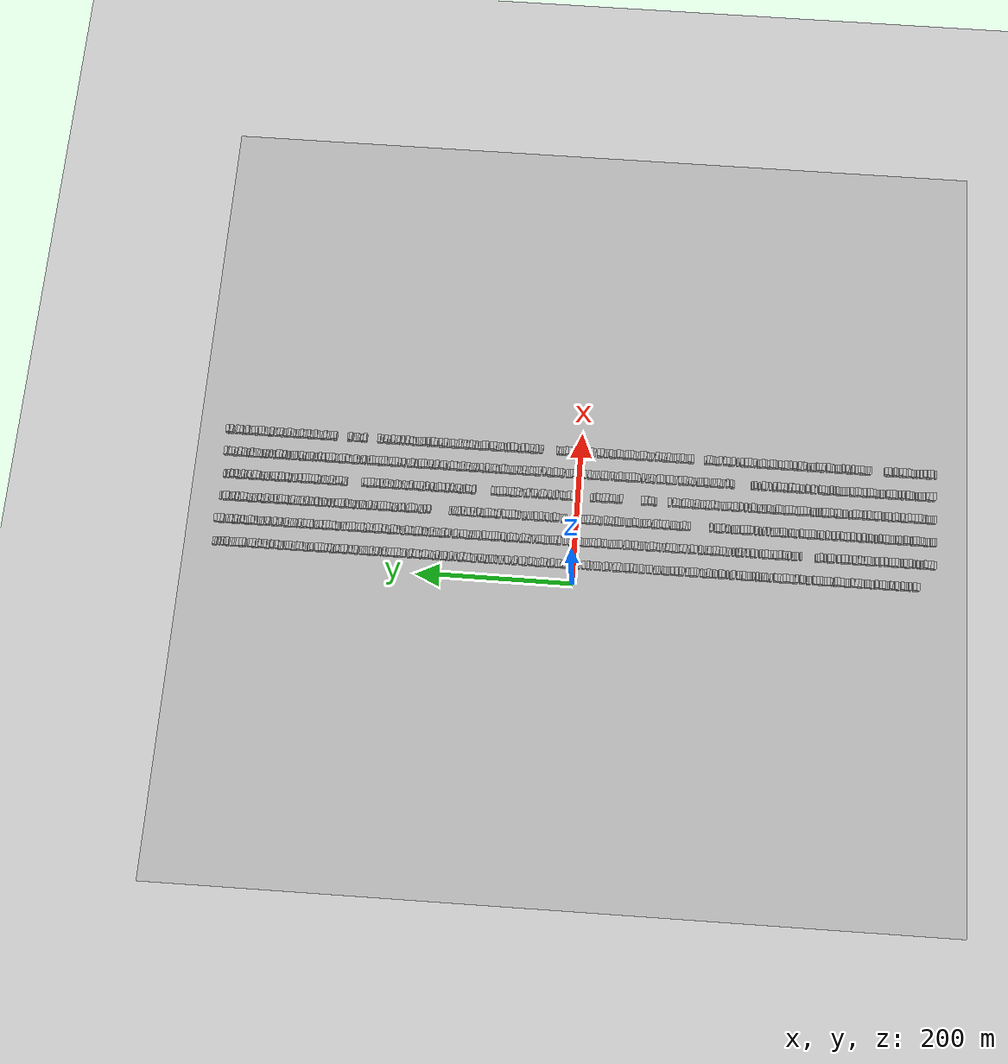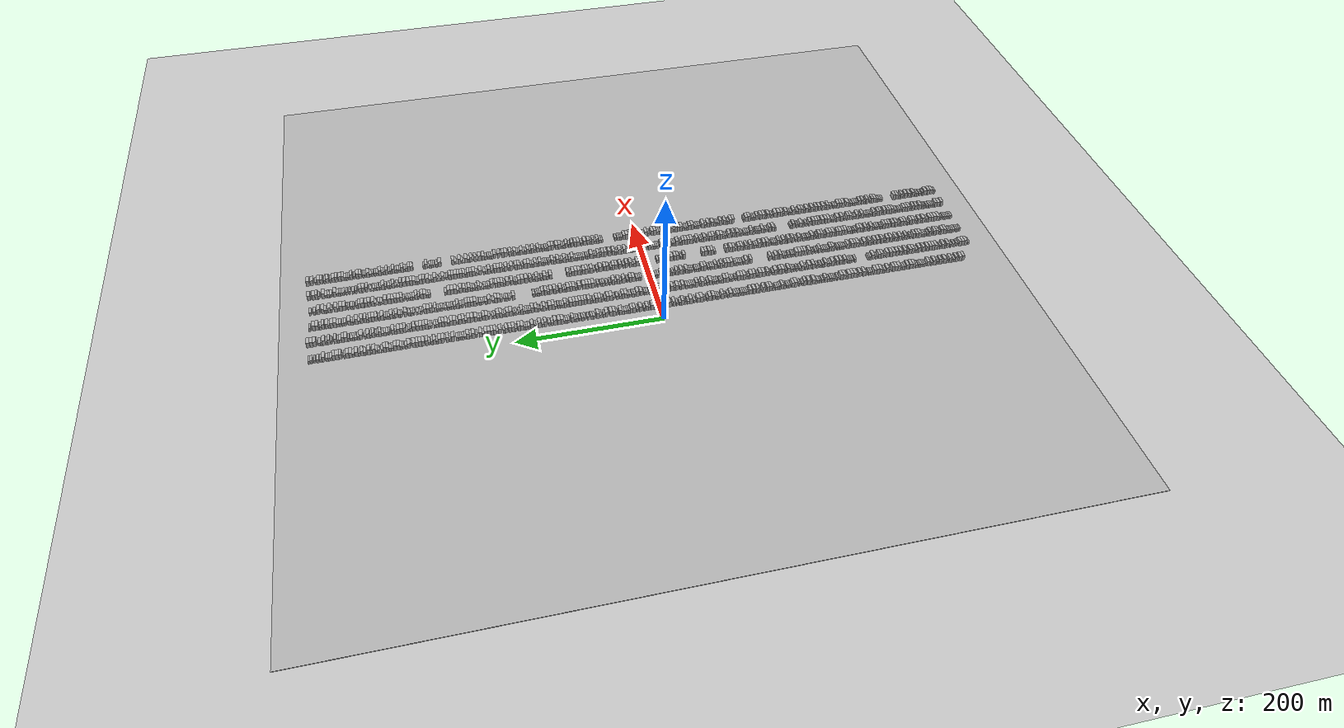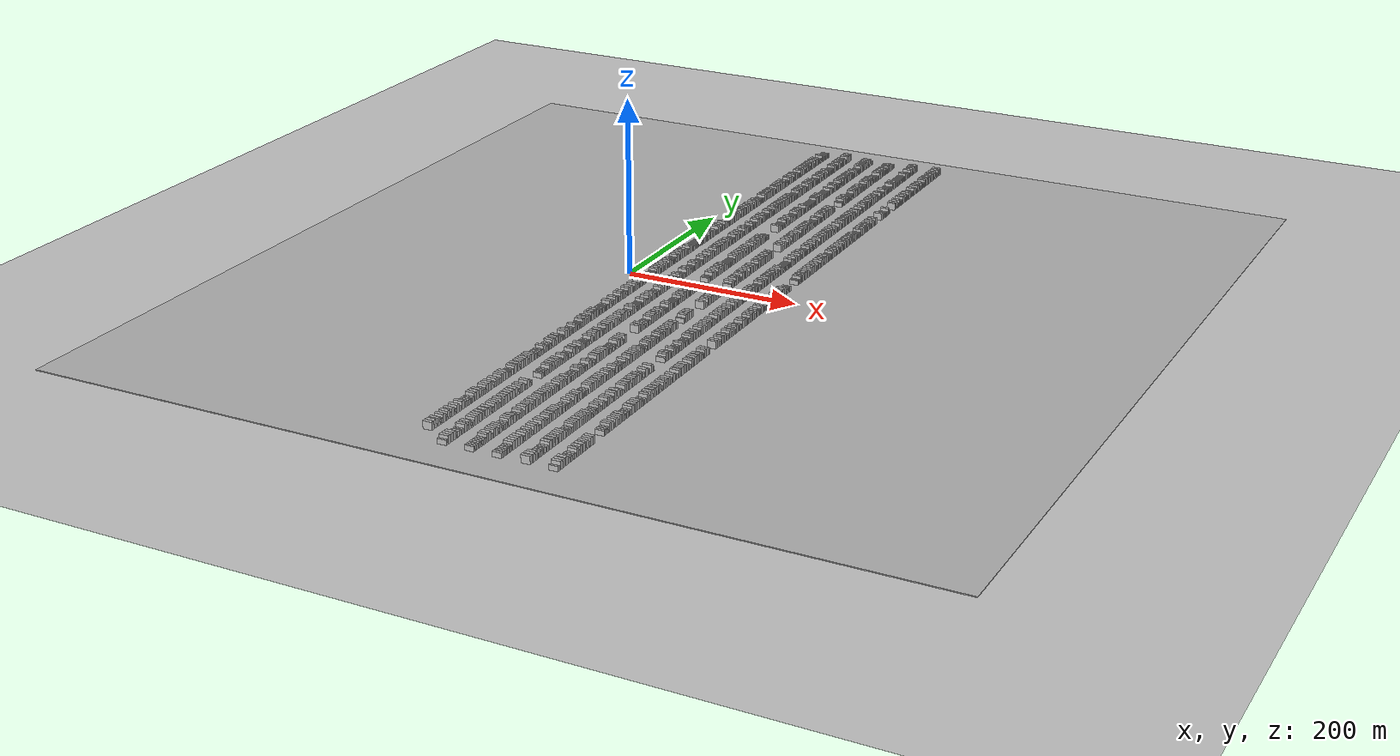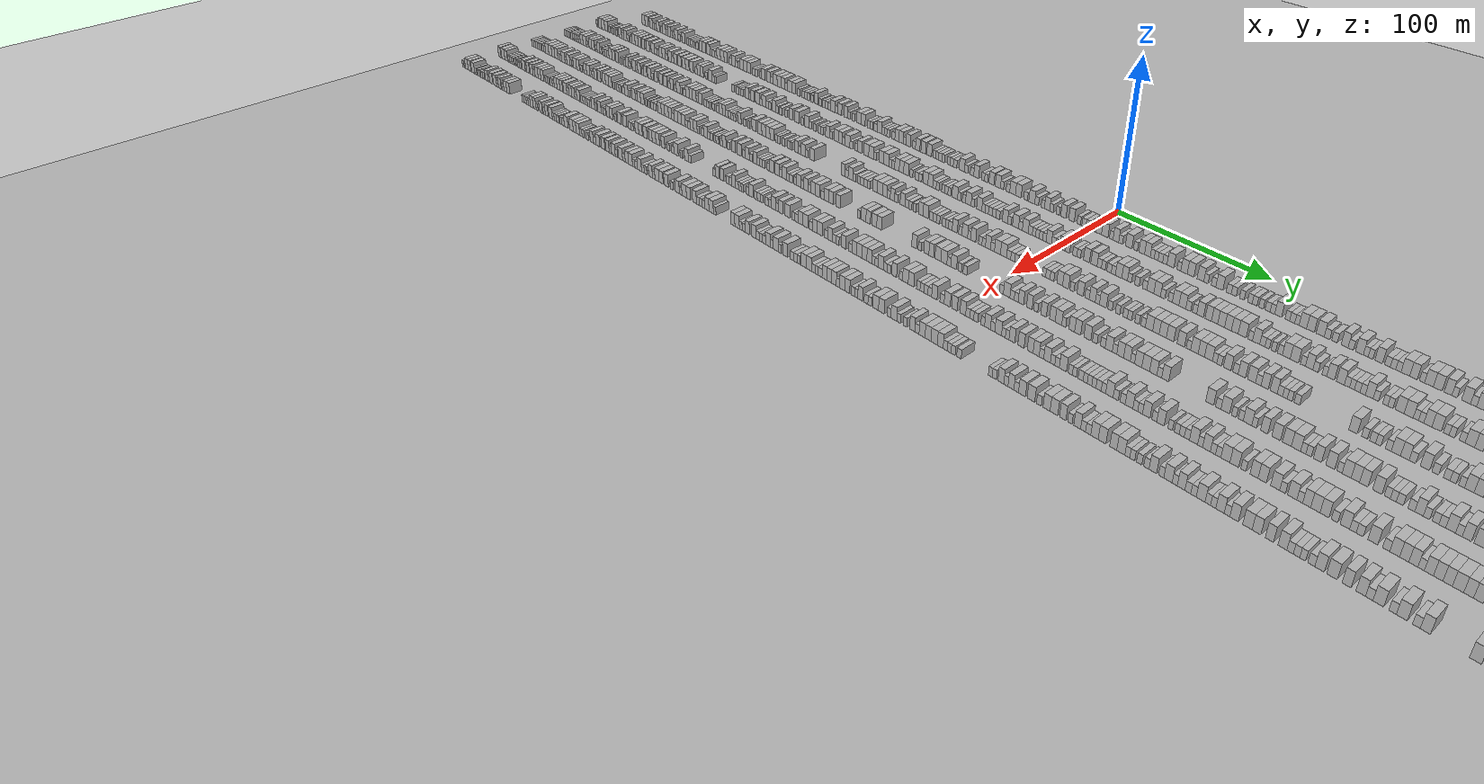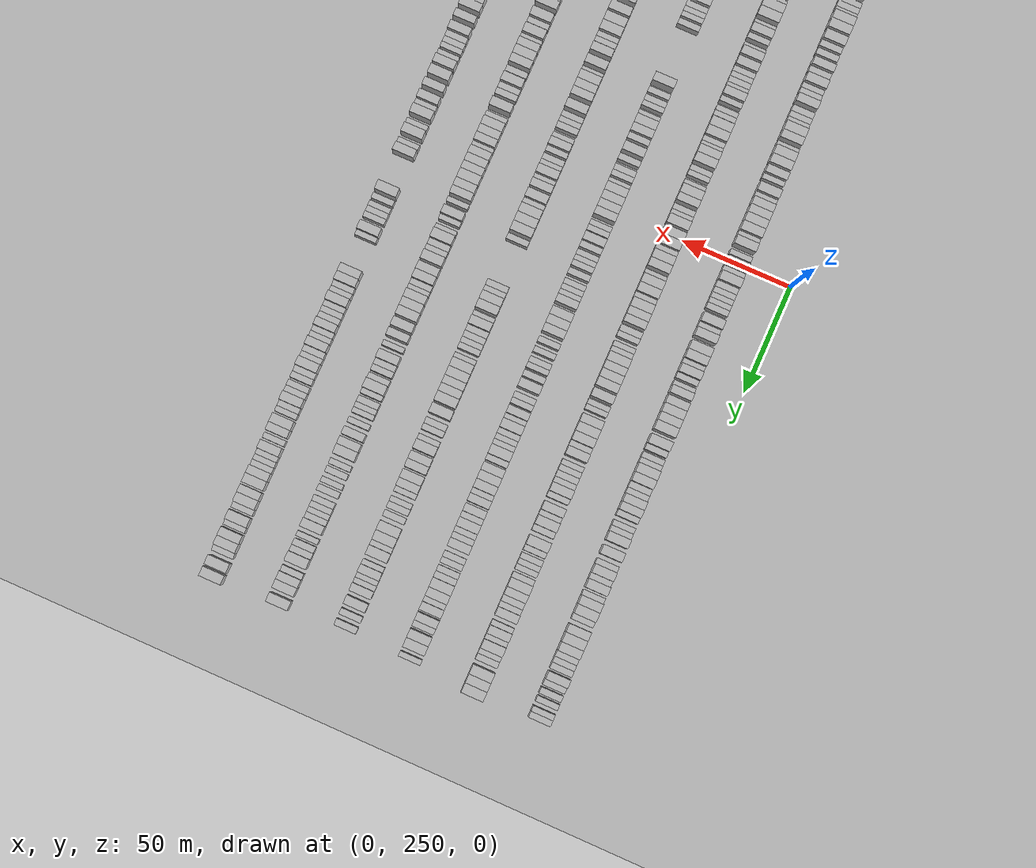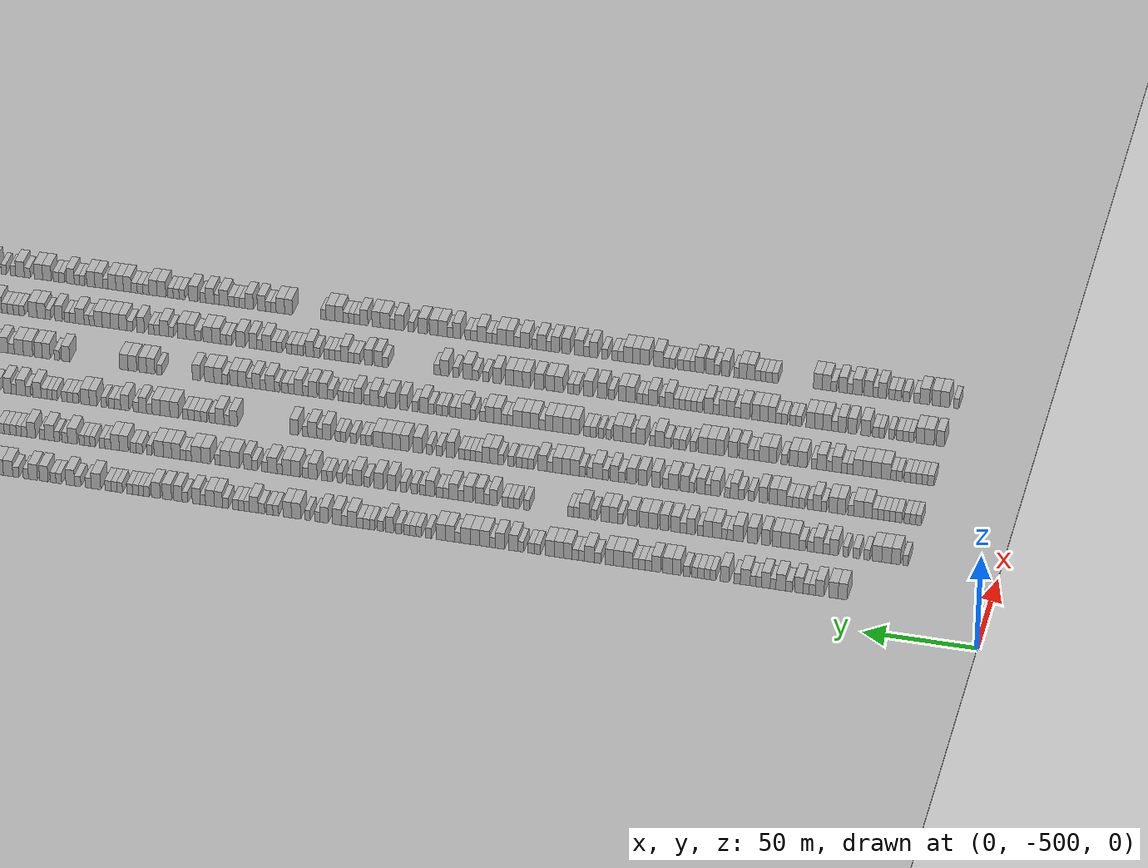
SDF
<sdf version="1.6">
 <world name="default">
  <scene>
   <sky><clouds><speed>12</speed></clouds></sky>
   <ambient>0.4 0.4 0.4 1</ambient>
   <background>0.7 0.7 0.7 1</background>
   <shadows>1</shadows>
  </scene>
  <gravity>0 0 -9.8066</gravity>
  <magnetic_field>6e-06 2.3e-05 -4.2e-05</magnetic_field>
  <physics default="0" name="default_physics" type="ode">
   <ode>
    <solver>
     <type>quick</type>
     <iters>10</iters>
     <sor>1.0</sor>
     <use_dynamic_moi_rescaling>0</use_dynamic_moi_rescaling>
    </solver>
    <constraints>
     <cfm>0</cfm>
     <erp>0.2</erp>
     <contact_max_correcting_vel>100</contact_max_correcting_vel>
     <contact_surface_layer>0.001</contact_surface_layer>
    </constraints>
   </ode>
   <max_step_size>0.004</max_step_size>
   <real_time_factor>1</real_time_factor>
   <real_time_update_rate>250</real_time_update_rate>
  </physics>
  <light name="sun" type="directional">
   <pose>0 0 10 0 0 0</pose>
   <diffuse>0.8 0.8 0.8 1</diffuse>
   <specular>0.2 0.2 0.2 1</specular>
   <attenuation>
    <range>1000</range>
    <constant>0.9</constant>
    <linear>0.01</linear>
    <quadratic>0.001</quadratic>
   </attenuation>
   <direction>-0.5 0.1 -0.9</direction>
  </light>
  <include><name>ground_plane_1</name><uri>model://HANNAS_ground_plane</uri></include>
  <include>
   <name>ground_plane_2</name>
   <uri>model://HANNAS_ground_plane</uri>
   <pose>100 0 0  0 0 0</pose>
  </include>
  <model name="building_1">
   <static>1</static>
   <pose>25.0000 -436.9459 0 0.000000 0.000000 0.000000</pose>
   <link name="link">
    <pose>0 0 4.50 0 0 0</pose>
    <collision name="collision"><geometry><box><size>10.0000 4.0361 9.0000</size></box></geometry></collision>
    <visual name="visual">
     <cast_shadows>0</cast_shadows>
     <geometry><box><size>10.0000 4.0361 9.0000</size></box></geometry>
     <material>
      <script>
       <uri>model://HANNAS_wall/materials/scripts</uri>
       <uri>model://HANNAS_wall/materials/textures</uri>
       <name>vrc/HANNAS_wall</name>
      </script>
     </material>
    </visual>
   </link>
  </model>
  <model name="building_2">
   <static>1</static>
   <pose>25.0000 -432.8017 0 0.000000 0.000000 0.000000</pose>
   <link name="link">
    <pose>0 0 4.50 0 0 0</pose>
    <collision name="collision"><geometry><box><size>10.0000 4.2522 9.0000</size></box></geometry></collision>
    <visual name="visual">
     <cast_shadows>0</cast_shadows>
     <geometry><box><size>10.0000 4.2522 9.0000</size></box></geometry>
     <material>
      <script>
       <uri>model://HANNAS_wall/materials/scripts</uri>
       <uri>model://HANNAS_wall/materials/textures</uri>
       <name>vrc/HANNAS_wall</name>
      </script>
     </material>
    </visual>
   </link>
  </model>
  <model name="building_3">
   <static>1</static>
   <pose>25.0000 -426.7690 0 0.000000 0.000000 0.000000</pose>
   <link name="link">
    <pose>0 0 4.50 0 0 0</pose>
    <collision name="collision"><geometry><box><size>10.0000 3.8133 9.0000</size></box></geometry></collision>
    <visual name="visual">
     <cast_shadows>0</cast_shadows>
     <geometry><box><size>10.0000 3.8133 9.0000</size></box></geometry>
     <material>
      <script>
       <uri>model://HANNAS_wall/materials/scripts</uri>
       <uri>model://HANNAS_wall/materials/textures</uri>
       <name>vrc/HANNAS_wall</name>
      </script>
     </material>
    </visual>
   </link>
  </model>
  <model name="building_4">
   <static>1</static>
   <pose>25.0000 -423.4668 0 0.000000 0.000000 0.000000</pose>
   <link name="link">
    <pose>0 0 3.00 0 0 0</pose>
    <collision name="collision"><geometry><box><size>10.0000 2.7911 6.0000</size></box></geometry></collision>
    <visual name="visual">
     <cast_shadows>0</cast_shadows>
     <geometry><box><size>10.0000 2.7911 6.0000</size></box></geometry>
     <material>
      <script>
       <uri>model://HANNAS_wall/materials/scripts</uri>
       <uri>model://HANNAS_wall/materials/textures</uri>
       <name>vrc/HANNAS_wall</name>
      </script>
     </material>
    </visual>
   </link>
  </model>
  <model name="building_5">
   <static>1</static>
   <pose>25.0000 -420.7635 0 0.000000 0.000000 0.000000</pose>
   <link name="link">
    <pose>0 0 3.00 0 0 0</pose>
    <collision name="collision"><geometry><box><size>10.0000 2.6154 6.0000</size></box></geometry></collision>
    <visual name="visual">
     <cast_shadows>0</cast_shadows>
     <geometry><box><size>10.0000 2.6154 6.0000</size></box></geometry>
     <material>
      <script>
       <uri>model://HANNAS_wall/materials/scripts</uri>
       <uri>model://HANNAS_wall/materials/textures</uri>
       <name>vrc/HANNAS_wall</name>
      </script>
     </material>
    </visual>
   </link>
  </model>
  <model name="building_6">
   <static>1</static>
   <pose>25.0000 -417.4886 0 0.000000 0.000000 0.000000</pose>
   <link name="link">
    <pose>0 0 4.50 0 0 0</pose>
    <collision name="collision"><geometry><box><size>10.0000 3.9344 9.0000</size></box></geometry></collision>
    <visual name="visual">
     <cast_shadows>0</cast_shadows>
     <geometry><box><size>10.0000 3.9344 9.0000</size></box></geometry>
     <material>
      <script>
       <uri>model://HANNAS_wall/materials/scripts</uri>
       <uri>model://HANNAS_wall/materials/textures</uri>
       <name>vrc/HANNAS_wall</name>
      </script>
     </material>
    </visual>
   </link>
  </model>
  <model name="building_7">
   <static>1</static>
   <pose>25.0000 -413.0755 0 0.000000 0.000000 0.000000</pose>
   <link name="link">
    <pose>0 0 3.00 0 0 0</pose>
    <collision name="collision"><geometry><box><size>10.0000 2.8920 6.0000</size></box></geometry></collision>
    <visual name="visual">
     <cast_shadows>0</cast_shadows>
     <geometry><box><size>10.0000 2.8920 6.0000</size></box></geometry>
     <material>
      <script>
       <uri>model://HANNAS_wall/materials/scripts</uri>
       <uri>model://HANNAS_wall/materials/textures</uri>
       <name>vrc/HANNAS_wall</name>
      </script>
     </material>
    </visual>
   </link>
  </model>
  <model name="building_8">
   <static>1</static>
   <pose>25.0000 -409.4676 0 0.000000 0.000000 0.000000</pose>
   <link name="link">
    <pose>0 0 4.50 0 0 0</pose>
    <collision name="collision"><geometry><box><size>10.0000 4.3238 9.0000</size></box></geometry></collision>
    <visual name="visual">
     <cast_shadows>0</cast_shadows>
     <geometry><box><size>10.0000 4.3238 9.0000</size></box></geometry>
     <material>
      <script>
       <uri>model://HANNAS_wall/materials/scripts</uri>
       <uri>model://HANNAS_wall/materials/textures</uri>
       <name>vrc/HANNAS_wall</name>
      </script>
     </material>
    </visual>
   </link>
  </model>
  <model name="building_9">
   <static>1</static>
   <pose>25.0000 -406.0213 0 0.000000 0.000000 0.000000</pose>
   <link name="link">
    <pose>0 0 3.00 0 0 0</pose>
    <collision name="collision"><geometry><box><size>10.0000 2.5686 6.0000</size></box></geometry></collision>
    <visual name="visual">
     <cast_shadows>0</cast_shadows>
     <geometry><box><size>10.0000 2.5686 6.0000</size></box></geometry>
     <material>
      <script>
       <uri>model://HANNAS_wall/materials/scripts</uri>
       <uri>model://HANNAS_wall/materials/textures</uri>
       <name>vrc/HANNAS_wall</name>
      </script>
     </material>
    </visual>
   </link>
  </model>
  <model name="building_10">
   <static>1</static>
   <pose>25.0000 -402.7828 0 0.000000 0.000000 0.000000</pose>
   <link name="link">
    <pose>0 0 4.50 0 0 0</pose>
    <collision name="collision"><geometry><box><size>10.0000 3.9084 9.0000</size></box></geometry></collision>
    <visual name="visual">
     <cast_shadows>0</cast_shadows>
     <geometry><box><size>10.0000 3.9084 9.0000</size></box></geometry>
     <material>
      <script>
       <uri>model://HANNAS_wall/materials/scripts</uri>
       <uri>model://HANNAS_wall/materials/textures</uri>
       <name>vrc/HANNAS_wall</name>
      </script>
     </material>
    </visual>
   </link>
  </model>
  <model name="building_11">
   <static>1</static>
   <pose>25.0000 -399.5430 0 0.000000 0.000000 0.000000</pose>
   <link name="link">
    <pose>0 0 3.00 0 0 0</pose>
    <collision name="collision"><geometry><box><size>10.0000 2.5712 6.0000</size></box></geometry></collision>
    <visual name="visual">
     <cast_shadows>0</cast_shadows>
     <geometry><box><size>10.0000 2.5712 6.0000</size></box></geometry>
     <material>
      <script>
       <uri>model://HANNAS_wall/materials/scripts</uri>
       <uri>model://HANNAS_wall/materials/textures</uri>
       <name>vrc/HANNAS_wall</name>
      </script>
     </material>
    </visual>
   </link>
  </model>
  <model name="building_12">
   <static>1</static>
   <pose>25.0000 -397.0383 0 0.000000 0.000000 0.000000</pose>
   <link name="link">
    <pose>0 0 3.00 0 0 0</pose>
    <collision name="collision"><geometry><box><size>10.0000 2.4381 6.0000</size></box></geometry></collision>
    <visual name="visual">
     <cast_shadows>0</cast_shadows>
     <geometry><box><size>10.0000 2.4381 6.0000</size></box></geometry>
     <material>
      <script>
       <uri>model://HANNAS_wall/materials/scripts</uri>
       <uri>model://HANNAS_wall/materials/textures</uri>
       <name>vrc/HANNAS_wall</name>
      </script>
     </material>
    </visual>
   </link>
  </model>
  <model name="building_13">
   <static>1</static>
   <pose>25.0000 -393.6206 0 0.000000 0.000000 0.000000</pose>
   <link name="link">
    <pose>0 0 4.50 0 0 0</pose>
    <collision name="collision"><geometry><box><size>10.0000 4.3973 9.0000</size></box></geometry></collision>
    <visual name="visual">
     <cast_shadows>0</cast_shadows>
     <geometry><box><size>10.0000 4.3973 9.0000</size></box></geometry>
     <material>
      <script>
       <uri>model://HANNAS_wall/materials/scripts</uri>
       <uri>model://HANNAS_wall/materials/textures</uri>
       <name>vrc/HANNAS_wall</name>
      </script>
     </material>
    </visual>
   </link>
  </model>
  <model name="building_14">
   <static>1</static>
   <pose>25.0000 -389.9452 0 0.000000 0.000000 0.000000</pose>
   <link name="link">
    <pose>0 0 3.00 0 0 0</pose>
    <collision name="collision"><geometry><box><size>10.0000 2.9535 6.0000</size></box></geometry></collision>
    <visual name="visual">
     <cast_shadows>0</cast_shadows>
     <geometry><box><size>10.0000 2.9535 6.0000</size></box></geometry>
     <material>
      <script>
       <uri>model://HANNAS_wall/materials/scripts</uri>
       <uri>model://HANNAS_wall/materials/textures</uri>
       <name>vrc/HANNAS_wall</name>
      </script>
     </material>
    </visual>
   </link>
  </model>
  <model name="building_15">
   <static>1</static>
   <pose>25.0000 -384.4778 0 0.000000 0.000000 0.000000</pose>
   <link name="link">
    <pose>0 0 4.50 0 0 0</pose>
    <collision name="collision"><geometry><box><size>10.0000 3.9812 9.0000</size></box></geometry></collision>
    <visual name="visual">
     <cast_shadows>0</cast_shadows>
     <geometry><box><size>10.0000 3.9812 9.0000</size></box></geometry>
     <material>
      <script>
       <uri>model://HANNAS_wall/materials/scripts</uri>
       <uri>model://HANNAS_wall/materials/textures</uri>
       <name>vrc/HANNAS_wall</name>
      </script>
     </material>
    </visual>
   </link>
  </model>
  <model name="building_16">
   <static>1</static>
   <pose>25.0000 -379.2430 0 0.000000 0.000000 0.000000</pose>
   <link name="link">
    <pose>0 0 3.00 0 0 0</pose>
    <collision name="collision"><geometry><box><size>10.0000 2.4883 6.0000</size></box></geometry></collision>
    <visual name="visual">
     <cast_shadows>0</cast_shadows>
     <geometry><box><size>10.0000 2.4883 6.0000</size></box></geometry>
     <material>
      <script>
       <uri>model://HANNAS_wall/materials/scripts</uri>
       <uri>model://HANNAS_wall/materials/textures</uri>
       <name>vrc/HANNAS_wall</name>
      </script>
     </material>
    </visual>
   </link>
  </model>
  <model name="building_17">
   <static>1</static>
   <pose>25.0000 -376.6878 0 0.000000 0.000000 0.000000</pose>
   <link name="link">
    <pose>0 0 3.00 0 0 0</pose>
    <collision name="collision"><geometry><box><size>10.0000 2.6222 6.0000</size></box></geometry></collision>
    <visual name="visual">
     <cast_shadows>0</cast_shadows>
     <geometry><box><size>10.0000 2.6222 6.0000</size></box></geometry>
     <material>
      <script>
       <uri>model://HANNAS_wall/materials/scripts</uri>
       <uri>model://HANNAS_wall/materials/textures</uri>
       <name>vrc/HANNAS_wall</name>
      </script>
     </material>
    </visual>
   </link>
  </model>
  <model name="building_18">
   <static>1</static>
   <pose>25.0000 -373.8791 0 0.000000 0.000000 0.000000</pose>
   <link name="link">
    <pose>0 0 3.00 0 0 0</pose>
    <collision name="collision"><geometry><box><size>10.0000 2.9952 6.0000</size></box></geometry></collision>
    <visual name="visual">
     <cast_shadows>0</cast_shadows>
     <geometry><box><size>10.0000 2.9952 6.0000</size></box></geometry>
     <material>
      <script>
       <uri>model://HANNAS_wall/materials/scripts</uri>
       <uri>model://HANNAS_wall/materials/textures</uri>
       <name>vrc/HANNAS_wall</name>
      </script>
     </material>
    </visual>
   </link>
  </model>
  <model name="building_19">
   <static>1</static>
   <pose>25.0000 -371.0766 0 0.000000 0.000000 0.000000</pose>
   <link name="link">
    <pose>0 0 3.00 0 0 0</pose>
    <collision name="collision"><geometry><box><size>10.0000 2.6098 6.0000</size></box></geometry></collision>
    <visual name="visual">
     <cast_shadows>0</cast_shadows>
     <geometry><box><size>10.0000 2.6098 6.0000</size></box></geometry>
     <material>
      <script>
       <uri>model://HANNAS_wall/materials/scripts</uri>
       <uri>model://HANNAS_wall/materials/textures</uri>
       <name>vrc/HANNAS_wall</name>
      </script>
     </material>
    </visual>
   </link>
  </model>
  <model name="building_20">
   <static>1</static>
   <pose>25.0000 -367.2946 0 0.000000 0.000000 0.000000</pose>
   <link name="link">
    <pose>0 0 3.00 0 0 0</pose>
    <collision name="collision"><geometry><box><size>10.0000 2.9542 6.0000</size></box></geometry></collision>
    <visual name="visual">
     <cast_shadows>0</cast_shadows>
     <geometry><box><size>10.0000 2.9542 6.0000</size></box></geometry>
     <material>
      <script>
       <uri>model://HANNAS_wall/materials/scripts</uri>
       <uri>model://HANNAS_wall/materials/textures</uri>
       <name>vrc/HANNAS_wall</name>
      </script>
     </material>
    </visual>
   </link>
  </model>
  <model name="building_21">
   <static>1</static>
   <pose>25.0000 -362.9768 0 0.000000 0.000000 0.000000</pose>
   <link name="link">
    <pose>0 0 4.50 0 0 0</pose>
    <collision name="collision"><geometry><box><size>10.0000 3.6815 9.0000</size></box></geometry></collision>
    <visual name="visual">
     <cast_shadows>0</cast_shadows>
     <geometry><box><size>10.0000 3.6815 9.0000</size></box></geometry>
     <material>
      <script>
       <uri>model://HANNAS_wall/materials/scripts</uri>
       <uri>model://HANNAS_wall/materials/textures</uri>
       <name>vrc/HANNAS_wall</name>
      </script>
     </material>
    </visual>
   </link>
  </model>
  <model name="building_22">
   <static>1</static>
   <pose>25.0000 -358.9369 0 0.000000 0.000000 0.000000</pose>
   <link name="link">
    <pose>0 0 4.50 0 0 0</pose>
    <collision name="collision"><geometry><box><size>10.0000 4.3981 9.0000</size></box></geometry></collision>
    <visual name="visual">
     <cast_shadows>0</cast_shadows>
     <geometry><box><size>10.0000 4.3981 9.0000</size></box></geometry>
     <material>
      <script>
       <uri>model://HANNAS_wall/materials/scripts</uri>
       <uri>model://HANNAS_wall/materials/textures</uri>
       <name>vrc/HANNAS_wall</name>
      </script>
     </material>
    </visual>
   </link>
  </model>
  <model name="building_23">
   <static>1</static>
   <pose>25.0000 -353.7045 0 0.000000 0.000000 0.000000</pose>
   <link name="link">
    <pose>0 0 4.50 0 0 0</pose>
    <collision name="collision"><geometry><box><size>10.0000 4.0668 9.0000</size></box></geometry></collision>
    <visual name="visual">
     <cast_shadows>0</cast_shadows>
     <geometry><box><size>10.0000 4.0668 9.0000</size></box></geometry>
     <material>
      <script>
       <uri>model://HANNAS_wall/materials/scripts</uri>
       <uri>model://HANNAS_wall/materials/textures</uri>
       <name>vrc/HANNAS_wall</name>
      </script>
     </material>
    </visual>
   </link>
  </model>
  <model name="building_24">
   <static>1</static>
   <pose>25.0000 -350.2815 0 0.000000 0.000000 0.000000</pose>
   <link name="link">
    <pose>0 0 3.00 0 0 0</pose>
    <collision name="collision"><geometry><box><size>10.0000 2.7791 6.0000</size></box></geometry></collision>
    <visual name="visual">
     <cast_shadows>0</cast_shadows>
     <geometry><box><size>10.0000 2.7791 6.0000</size></box></geometry>
     <material>
      <script>
       <uri>model://HANNAS_wall/materials/scripts</uri>
       <uri>model://HANNAS_wall/materials/textures</uri>
       <name>vrc/HANNAS_wall</name>
      </script>
     </material>
    </visual>
   </link>
  </model>
  <model name="building_25">
   <static>1</static>
   <pose>25.0000 -347.4159 0 0.000000 0.000000 0.000000</pose>
   <link name="link">
    <pose>0 0 3.00 0 0 0</pose>
    <collision name="collision"><geometry><box><size>10.0000 2.9520 6.0000</size></box></geometry></collision>
    <visual name="visual">
     <cast_shadows>0</cast_shadows>
     <geometry><box><size>10.0000 2.9520 6.0000</size></box></geometry>
     <material>
      <script>
       <uri>model://HANNAS_wall/materials/scripts</uri>
       <uri>model://HANNAS_wall/materials/textures</uri>
       <name>vrc/HANNAS_wall</name>
      </script>
     </material>
    </visual>
   </link>
  </model>
  <model name="building_26">
   <static>1</static>
   <pose>25.0000 -344.6306 0 0.000000 0.000000 0.000000</pose>
   <link name="link">
    <pose>0 0 3.00 0 0 0</pose>
    <collision name="collision"><geometry><box><size>10.0000 2.6186 6.0000</size></box></geometry></collision>
    <visual name="visual">
     <cast_shadows>0</cast_shadows>
     <geometry><box><size>10.0000 2.6186 6.0000</size></box></geometry>
     <material>
      <script>
       <uri>model://HANNAS_wall/materials/scripts</uri>
       <uri>model://HANNAS_wall/materials/textures</uri>
       <name>vrc/HANNAS_wall</name>
      </script>
     </material>
    </visual>
   </link>
  </model>
  <model name="building_27">
   <static>1</static>
   <pose>25.0000 -341.1353 0 0.000000 0.000000 0.000000</pose>
   <link name="link">
    <pose>0 0 4.50 0 0 0</pose>
    <collision name="collision"><geometry><box><size>10.0000 4.3720 9.0000</size></box></geometry></collision>
    <visual name="visual">
     <cast_shadows>0</cast_shadows>
     <geometry><box><size>10.0000 4.3720 9.0000</size></box></geometry>
     <material>
      <script>
       <uri>model://HANNAS_wall/materials/scripts</uri>
       <uri>model://HANNAS_wall/materials/textures</uri>
       <name>vrc/HANNAS_wall</name>
      </script>
     </material>
    </visual>
   </link>
  </model>
  <model name="building_28">
   <static>1</static>
   <pose>25.0000 -336.7912 0 0.000000 0.000000 0.000000</pose>
   <link name="link">
    <pose>0 0 4.50 0 0 0</pose>
    <collision name="collision"><geometry><box><size>10.0000 4.3162 9.0000</size></box></geometry></collision>
    <visual name="visual">
     <cast_shadows>0</cast_shadows>
     <geometry><box><size>10.0000 4.3162 9.0000</size></box></geometry>
     <material>
      <script>
       <uri>model://HANNAS_wall/materials/scripts</uri>
       <uri>model://HANNAS_wall/materials/textures</uri>
       <name>vrc/HANNAS_wall</name>
      </script>
     </material>
    </visual>
   </link>
  </model>
  <model name="building_29">
   <static>1</static>
   <pose>25.0000 -332.7534 0 0.000000 0.000000 0.000000</pose>
   <link name="link">
    <pose>0 0 4.50 0 0 0</pose>
    <collision name="collision"><geometry><box><size>10.0000 3.7593 9.0000</size></box></geometry></collision>
    <visual name="visual">
     <cast_shadows>0</cast_shadows>
     <geometry><box><size>10.0000 3.7593 9.0000</size></box></geometry>
     <material>
      <script>
       <uri>model://HANNAS_wall/materials/scripts</uri>
       <uri>model://HANNAS_wall/materials/textures</uri>
       <name>vrc/HANNAS_wall</name>
      </script>
     </material>
    </visual>
   </link>
  </model>
  <model name="building_30">
   <static>1</static>
   <pose>25.0000 -327.4053 0 0.000000 0.000000 0.000000</pose>
   <link name="link">
    <pose>0 0 3.00 0 0 0</pose>
    <collision name="collision"><geometry><box><size>10.0000 2.9368 6.0000</size></box></geometry></collision>
    <visual name="visual">
     <cast_shadows>0</cast_shadows>
     <geometry><box><size>10.0000 2.9368 6.0000</size></box></geometry>
     <material>
      <script>
       <uri>model://HANNAS_wall/materials/scripts</uri>
       <uri>model://HANNAS_wall/materials/textures</uri>
       <name>vrc/HANNAS_wall</name>
      </script>
     </material>
    </visual>
   </link>
  </model>
  <model name="building_31">
   <static>1</static>
   <pose>25.0000 -323.8055 0 0.000000 0.000000 0.000000</pose>
   <link name="link">
    <pose>0 0 4.50 0 0 0</pose>
    <collision name="collision"><geometry><box><size>10.0000 4.2628 9.0000</size></box></geometry></collision>
    <visual name="visual">
     <cast_shadows>0</cast_shadows>
     <geometry><box><size>10.0000 4.2628 9.0000</size></box></geometry>
     <material>
      <script>
       <uri>model://HANNAS_wall/materials/scripts</uri>
       <uri>model://HANNAS_wall/materials/textures</uri>
       <name>vrc/HANNAS_wall</name>
      </script>
     </material>
    </visual>
   </link>
  </model>
  <model name="building_32">
   <static>1</static>
   <pose>25.0000 -320.2329 0 0.000000 0.000000 0.000000</pose>
   <link name="link">
    <pose>0 0 3.00 0 0 0</pose>
    <collision name="collision"><geometry><box><size>10.0000 2.8823 6.0000</size></box></geometry></collision>
    <visual name="visual">
     <cast_shadows>0</cast_shadows>
     <geometry><box><size>10.0000 2.8823 6.0000</size></box></geometry>
     <material>
      <script>
       <uri>model://HANNAS_wall/materials/scripts</uri>
       <uri>model://HANNAS_wall/materials/textures</uri>
       <name>vrc/HANNAS_wall</name>
      </script>
     </material>
    </visual>
   </link>
  </model>
  <model name="building_33">
   <static>1</static>
   <pose>25.0000 -317.4139 0 0.000000 0.000000 0.000000</pose>
   <link name="link">
    <pose>0 0 3.00 0 0 0</pose>
    <collision name="collision"><geometry><box><size>10.0000 2.7558 6.0000</size></box></geometry></collision>
    <visual name="visual">
     <cast_shadows>0</cast_shadows>
     <geometry><box><size>10.0000 2.7558 6.0000</size></box></geometry>
     <material>
      <script>
       <uri>model://HANNAS_wall/materials/scripts</uri>
       <uri>model://HANNAS_wall/materials/textures</uri>
       <name>vrc/HANNAS_wall</name>
      </script>
     </material>
    </visual>
   </link>
  </model>
  <model name="building_34">
   <static>1</static>
   <pose>25.0000 -314.0761 0 0.000000 0.000000 0.000000</pose>
   <link name="link">
    <pose>0 0 4.50 0 0 0</pose>
    <collision name="collision"><geometry><box><size>10.0000 3.9198 9.0000</size></box></geometry></collision>
    <visual name="visual">
     <cast_shadows>0</cast_shadows>
     <geometry><box><size>10.0000 3.9198 9.0000</size></box></geometry>
     <material>
      <script>
       <uri>model://HANNAS_wall/materials/scripts</uri>
       <uri>model://HANNAS_wall/materials/textures</uri>
       <name>vrc/HANNAS_wall</name>
      </script>
     </material>
    </visual>
   </link>
  </model>
  <model name="building_35">
   <static>1</static>
   <pose>25.0000 -309.9775 0 0.000000 0.000000 0.000000</pose>
   <link name="link">
    <pose>0 0 4.50 0 0 0</pose>
    <collision name="collision"><geometry><box><size>10.0000 4.2775 9.0000</size></box></geometry></collision>
    <visual name="visual">
     <cast_shadows>0</cast_shadows>
     <geometry><box><size>10.0000 4.2775 9.0000</size></box></geometry>
     <material>
      <script>
       <uri>model://HANNAS_wall/materials/scripts</uri>
       <uri>model://HANNAS_wall/materials/textures</uri>
       <name>vrc/HANNAS_wall</name>
      </script>
     </material>
    </visual>
   </link>
  </model>
  <model name="building_36">
   <static>1</static>
   <pose>25.0000 -305.7788 0 0.000000 0.000000 0.000000</pose>
   <link name="link">
    <pose>0 0 4.50 0 0 0</pose>
    <collision name="collision"><geometry><box><size>10.0000 4.1198 9.0000</size></box></geometry></collision>
    <visual name="visual">
     <cast_shadows>0</cast_shadows>
     <geometry><box><size>10.0000 4.1198 9.0000</size></box></geometry>
     <material>
      <script>
       <uri>model://HANNAS_wall/materials/scripts</uri>
       <uri>model://HANNAS_wall/materials/textures</uri>
       <name>vrc/HANNAS_wall</name>
      </script>
     </material>
    </visual>
   </link>
  </model>
  <model name="building_37">
   <static>1</static>
   <pose>25.0000 -300.2874 0 0.000000 0.000000 0.000000</pose>
   <link name="link">
    <pose>0 0 3.00 0 0 0</pose>
    <collision name="collision"><geometry><box><size>10.0000 2.8631 6.0000</size></box></geometry></collision>
    <visual name="visual">
     <cast_shadows>0</cast_shadows>
     <geometry><box><size>10.0000 2.8631 6.0000</size></box></geometry>
     <material>
      <script>
       <uri>model://HANNAS_wall/materials/scripts</uri>
       <uri>model://HANNAS_wall/materials/textures</uri>
       <name>vrc/HANNAS_wall</name>
      </script>
     </material>
    </visual>
   </link>
  </model>
  <model name="building_38">
   <static>1</static>
   <pose>25.0000 -297.4788 0 0.000000 0.000000 0.000000</pose>
   <link name="link">
    <pose>0 0 3.00 0 0 0</pose>
    <collision name="collision"><geometry><box><size>10.0000 2.7540 6.0000</size></box></geometry></collision>
    <visual name="visual">
     <cast_shadows>0</cast_shadows>
     <geometry><box><size>10.0000 2.7540 6.0000</size></box></geometry>
     <material>
      <script>
       <uri>model://HANNAS_wall/materials/scripts</uri>
       <uri>model://HANNAS_wall/materials/textures</uri>
       <name>vrc/HANNAS_wall</name>
      </script>
     </material>
    </visual>
   </link>
  </model>
  <model name="building_39">
   <static>1</static>
   <pose>25.0000 -292.8592 0 0.000000 0.000000 0.000000</pose>
   <link name="link">
    <pose>0 0 3.00 0 0 0</pose>
    <collision name="collision"><geometry><box><size>10.0000 2.4850 6.0000</size></box></geometry></collision>
    <visual name="visual">
     <cast_shadows>0</cast_shadows>
     <geometry><box><size>10.0000 2.4850 6.0000</size></box></geometry>
     <material>
      <script>
       <uri>model://HANNAS_wall/materials/scripts</uri>
       <uri>model://HANNAS_wall/materials/textures</uri>
       <name>vrc/HANNAS_wall</name>
      </script>
     </material>
    </visual>
   </link>
  </model>
  <model name="building_40">
   <static>1</static>
   <pose>25.0000 -289.5277 0 0.000000 0.000000 0.000000</pose>
   <link name="link">
    <pose>0 0 4.50 0 0 0</pose>
    <collision name="collision"><geometry><box><size>10.0000 4.1780 9.0000</size></box></geometry></collision>
    <visual name="visual">
     <cast_shadows>0</cast_shadows>
     <geometry><box><size>10.0000 4.1780 9.0000</size></box></geometry>
     <material>
      <script>
       <uri>model://HANNAS_wall/materials/scripts</uri>
       <uri>model://HANNAS_wall/materials/textures</uri>
       <name>vrc/HANNAS_wall</name>
      </script>
     </material>
    </visual>
   </link>
  </model>
  <model name="building_41">
   <static>1</static>
   <pose>25.0000 -283.3827 0 0.000000 0.000000 0.000000</pose>
   <link name="link">
    <pose>0 0 4.50 0 0 0</pose>
    <collision name="collision"><geometry><box><size>10.0000 4.1121 9.0000</size></box></geometry></collision>
    <visual name="visual">
     <cast_shadows>0</cast_shadows>
     <geometry><box><size>10.0000 4.1121 9.0000</size></box></geometry>
     <material>
      <script>
       <uri>model://HANNAS_wall/materials/scripts</uri>
       <uri>model://HANNAS_wall/materials/textures</uri>
       <name>vrc/HANNAS_wall</name>
      </script>
     </material>
    </visual>
   </link>
  </model>
  <model name="building_42">
   <static>1</static>
   <pose>25.0000 -280.0124 0 0.000000 0.000000 0.000000</pose>
   <link name="link">
    <pose>0 0 3.00 0 0 0</pose>
    <collision name="collision"><geometry><box><size>10.0000 2.6285 6.0000</size></box></geometry></collision>
    <visual name="visual">
     <cast_shadows>0</cast_shadows>
     <geometry><box><size>10.0000 2.6285 6.0000</size></box></geometry>
     <material>
      <script>
       <uri>model://HANNAS_wall/materials/scripts</uri>
       <uri>model://HANNAS_wall/materials/textures</uri>
       <name>vrc/HANNAS_wall</name>
      </script>
     </material>
    </visual>
   </link>
  </model>
  <model name="building_43">
   <static>1</static>
   <pose>25.0000 -276.4767 0 0.000000 0.000000 0.000000</pose>
   <link name="link">
    <pose>0 0 4.50 0 0 0</pose>
    <collision name="collision"><geometry><box><size>10.0000 4.4429 9.0000</size></box></geometry></collision>
    <visual name="visual">
     <cast_shadows>0</cast_shadows>
     <geometry><box><size>10.0000 4.4429 9.0000</size></box></geometry>
     <material>
      <script>
       <uri>model://HANNAS_wall/materials/scripts</uri>
       <uri>model://HANNAS_wall/materials/textures</uri>
       <name>vrc/HANNAS_wall</name>
      </script>
     </material>
    </visual>
   </link>
  </model>
  <model name="building_44">
   <static>1</static>
   <pose>25.0000 -272.1617 0 0.000000 0.000000 0.000000</pose>
   <link name="link">
    <pose>0 0 4.50 0 0 0</pose>
    <collision name="collision"><geometry><box><size>10.0000 4.1871 9.0000</size></box></geometry></collision>
    <visual name="visual">
     <cast_shadows>0</cast_shadows>
     <geometry><box><size>10.0000 4.1871 9.0000</size></box></geometry>
     <material>
      <script>
       <uri>model://HANNAS_wall/materials/scripts</uri>
       <uri>model://HANNAS_wall/materials/textures</uri>
       <name>vrc/HANNAS_wall</name>
      </script>
     </material>
    </visual>
   </link>
  </model>
  <model name="building_45">
   <static>1</static>
   <pose>25.0000 -267.8288 0 0.000000 0.000000 0.000000</pose>
   <link name="link">
    <pose>0 0 4.50 0 0 0</pose>
    <collision name="collision"><geometry><box><size>10.0000 4.4788 9.0000</size></box></geometry></collision>
    <visual name="visual">
     <cast_shadows>0</cast_shadows>
     <geometry><box><size>10.0000 4.4788 9.0000</size></box></geometry>
     <material>
      <script>
       <uri>model://HANNAS_wall/materials/scripts</uri>
       <uri>model://HANNAS_wall/materials/textures</uri>
       <name>vrc/HANNAS_wall</name>
      </script>
     </material>
    </visual>
   </link>
  </model>
  <model name="building_46">
   <static>1</static>
   <pose>25.0000 -264.1485 0 0.000000 0.000000 0.000000</pose>
   <link name="link">
    <pose>0 0 3.00 0 0 0</pose>
    <collision name="collision"><geometry><box><size>10.0000 2.8820 6.0000</size></box></geometry></collision>
    <visual name="visual">
     <cast_shadows>0</cast_shadows>
     <geometry><box><size>10.0000 2.8820 6.0000</size></box></geometry>
     <material>
      <script>
       <uri>model://HANNAS_wall/materials/scripts</uri>
       <uri>model://HANNAS_wall/materials/textures</uri>
       <name>vrc/HANNAS_wall</name>
      </script>
     </material>
    </visual>
   </link>
  </model>
  <model name="building_47">
   <static>1</static>
   <pose>25.0000 -260.6801 0 0.000000 0.000000 0.000000</pose>
   <link name="link">
    <pose>0 0 4.50 0 0 0</pose>
    <collision name="collision"><geometry><box><size>10.0000 4.0547 9.0000</size></box></geometry></collision>
    <visual name="visual">
     <cast_shadows>0</cast_shadows>
     <geometry><box><size>10.0000 4.0547 9.0000</size></box></geometry>
     <material>
      <script>
       <uri>model://HANNAS_wall/materials/scripts</uri>
       <uri>model://HANNAS_wall/materials/textures</uri>
       <name>vrc/HANNAS_wall</name>
      </script>
     </material>
    </visual>
   </link>
  </model>
  <model name="building_48">
   <static>1</static>
   <pose>25.0000 -256.4939 0 0.000000 0.000000 0.000000</pose>
   <link name="link">
    <pose>0 0 4.50 0 0 0</pose>
    <collision name="collision"><geometry><box><size>10.0000 4.3178 9.0000</size></box></geometry></collision>
    <visual name="visual">
     <cast_shadows>0</cast_shadows>
     <geometry><box><size>10.0000 4.3178 9.0000</size></box></geometry>
     <material>
      <script>
       <uri>model://HANNAS_wall/materials/scripts</uri>
       <uri>model://HANNAS_wall/materials/textures</uri>
       <name>vrc/HANNAS_wall</name>
      </script>
     </material>
    </visual>
   </link>
  </model>
  <model name="building_49">
   <static>1</static>
   <pose>25.0000 -250.9897 0 0.000000 0.000000 0.000000</pose>
   <link name="link">
    <pose>0 0 3.00 0 0 0</pose>
    <collision name="collision"><geometry><box><size>10.0000 2.6907 6.0000</size></box></geometry></collision>
    <visual name="visual">
     <cast_shadows>0</cast_shadows>
     <geometry><box><size>10.0000 2.6907 6.0000</size></box></geometry>
     <material>
      <script>
       <uri>model://HANNAS_wall/materials/scripts</uri>
       <uri>model://HANNAS_wall/materials/textures</uri>
       <name>vrc/HANNAS_wall</name>
      </script>
     </material>
    </visual>
   </link>
  </model>
  <model name="building_50">
   <static>1</static>
   <pose>25.0000 -246.4003 0 0.000000 0.000000 0.000000</pose>
   <link name="link">
    <pose>0 0 3.00 0 0 0</pose>
    <collision name="collision"><geometry><box><size>10.0000 2.4881 6.0000</size></box></geometry></collision>
    <visual name="visual">
     <cast_shadows>0</cast_shadows>
     <geometry><box><size>10.0000 2.4881 6.0000</size></box></geometry>
     <material>
      <script>
       <uri>model://HANNAS_wall/materials/scripts</uri>
       <uri>model://HANNAS_wall/materials/textures</uri>
       <name>vrc/HANNAS_wall</name>
      </script>
     </material>
    </visual>
   </link>
  </model>
  <model name="building_51">
   <static>1</static>
   <pose>25.0000 -243.7108 0 0.000000 0.000000 0.000000</pose>
   <link name="link">
    <pose>0 0 3.00 0 0 0</pose>
    <collision name="collision"><geometry><box><size>10.0000 2.8909 6.0000</size></box></geometry></collision>
    <visual name="visual">
     <cast_shadows>0</cast_shadows>
     <geometry><box><size>10.0000 2.8909 6.0000</size></box></geometry>
     <material>
      <script>
       <uri>model://HANNAS_wall/materials/scripts</uri>
       <uri>model://HANNAS_wall/materials/textures</uri>
       <name>vrc/HANNAS_wall</name>
      </script>
     </material>
    </visual>
   </link>
  </model>
  <model name="building_52">
   <static>1</static>
   <pose>25.0000 -240.9700 0 0.000000 0.000000 0.000000</pose>
   <link name="link">
    <pose>0 0 3.00 0 0 0</pose>
    <collision name="collision"><geometry><box><size>10.0000 2.5906 6.0000</size></box></geometry></collision>
    <visual name="visual">
     <cast_shadows>0</cast_shadows>
     <geometry><box><size>10.0000 2.5906 6.0000</size></box></geometry>
     <material>
      <script>
       <uri>model://HANNAS_wall/materials/scripts</uri>
       <uri>model://HANNAS_wall/materials/textures</uri>
       <name>vrc/HANNAS_wall</name>
      </script>
     </material>
    </visual>
   </link>
  </model>
  <model name="building_53">
   <static>1</static>
   <pose>25.0000 -237.3299 0 0.000000 0.000000 0.000000</pose>
   <link name="link">
    <pose>0 0 3.00 0 0 0</pose>
    <collision name="collision"><geometry><box><size>10.0000 2.6897 6.0000</size></box></geometry></collision>
    <visual name="visual">
     <cast_shadows>0</cast_shadows>
     <geometry><box><size>10.0000 2.6897 6.0000</size></box></geometry>
     <material>
      <script>
       <uri>model://HANNAS_wall/materials/scripts</uri>
       <uri>model://HANNAS_wall/materials/textures</uri>
       <name>vrc/HANNAS_wall</name>
      </script>
     </material>
    </visual>
   </link>
  </model>
  <model name="building_54">
   <static>1</static>
   <pose>25.0000 -233.1575 0 0.000000 0.000000 0.000000</pose>
   <link name="link">
    <pose>0 0 4.50 0 0 0</pose>
    <collision name="collision"><geometry><box><size>10.0000 3.6551 9.0000</size></box></geometry></collision>
    <visual name="visual">
     <cast_shadows>0</cast_shadows>
     <geometry><box><size>10.0000 3.6551 9.0000</size></box></geometry>
     <material>
      <script>
       <uri>model://HANNAS_wall/materials/scripts</uri>
       <uri>model://HANNAS_wall/materials/textures</uri>
       <name>vrc/HANNAS_wall</name>
      </script>
     </material>
    </visual>
   </link>
  </model>
  <model name="building_55">
   <static>1</static>
   <pose>25.0000 -228.8805 0 0.000000 0.000000 0.000000</pose>
   <link name="link">
    <pose>0 0 3.00 0 0 0</pose>
    <collision name="collision"><geometry><box><size>10.0000 2.8989 6.0000</size></box></geometry></collision>
    <visual name="visual">
     <cast_shadows>0</cast_shadows>
     <geometry><box><size>10.0000 2.8989 6.0000</size></box></geometry>
     <material>
      <script>
       <uri>model://HANNAS_wall/materials/scripts</uri>
       <uri>model://HANNAS_wall/materials/textures</uri>
       <name>vrc/HANNAS_wall</name>
      </script>
     </material>
    </visual>
   </link>
  </model>
  <model name="building_56">
   <static>1</static>
   <pose>25.0000 -225.2033 0 0.000000 0.000000 0.000000</pose>
   <link name="link">
    <pose>0 0 3.00 0 0 0</pose>
    <collision name="collision"><geometry><box><size>10.0000 2.4555 6.0000</size></box></geometry></collision>
    <visual name="visual">
     <cast_shadows>0</cast_shadows>
     <geometry><box><size>10.0000 2.4555 6.0000</size></box></geometry>
     <material>
      <script>
       <uri>model://HANNAS_wall/materials/scripts</uri>
       <uri>model://HANNAS_wall/materials/textures</uri>
       <name>vrc/HANNAS_wall</name>
      </script>
     </material>
    </visual>
   </link>
  </model>
  <model name="building_57">
   <static>1</static>
   <pose>25.0000 -222.5029 0 0.000000 0.000000 0.000000</pose>
   <link name="link">
    <pose>0 0 3.00 0 0 0</pose>
    <collision name="collision"><geometry><box><size>10.0000 2.9454 6.0000</size></box></geometry></collision>
    <visual name="visual">
     <cast_shadows>0</cast_shadows>
     <geometry><box><size>10.0000 2.9454 6.0000</size></box></geometry>
     <material>
      <script>
       <uri>model://HANNAS_wall/materials/scripts</uri>
       <uri>model://HANNAS_wall/materials/textures</uri>
       <name>vrc/HANNAS_wall</name>
      </script>
     </material>
    </visual>
   </link>
  </model>
  <model name="building_58">
   <static>1</static>
   <pose>25.0000 -219.5886 0 0.000000 0.000000 0.000000</pose>
   <link name="link">
    <pose>0 0 3.00 0 0 0</pose>
    <collision name="collision"><geometry><box><size>10.0000 2.8831 6.0000</size></box></geometry></collision>
    <visual name="visual">
     <cast_shadows>0</cast_shadows>
     <geometry><box><size>10.0000 2.8831 6.0000</size></box></geometry>
     <material>
      <script>
       <uri>model://HANNAS_wall/materials/scripts</uri>
       <uri>model://HANNAS_wall/materials/textures</uri>
       <name>vrc/HANNAS_wall</name>
      </script>
     </material>
    </visual>
   </link>
  </model>
  <model name="building_59">
   <static>1</static>
   <pose>25.0000 -215.9863 0 0.000000 0.000000 0.000000</pose>
   <link name="link">
    <pose>0 0 4.50 0 0 0</pose>
    <collision name="collision"><geometry><box><size>10.0000 4.3215 9.0000</size></box></geometry></collision>
    <visual name="visual">
     <cast_shadows>0</cast_shadows>
     <geometry><box><size>10.0000 4.3215 9.0000</size></box></geometry>
     <material>
      <script>
       <uri>model://HANNAS_wall/materials/scripts</uri>
       <uri>model://HANNAS_wall/materials/textures</uri>
       <name>vrc/HANNAS_wall</name>
      </script>
     </material>
    </visual>
   </link>
  </model>
  <model name="building_60">
   <static>1</static>
   <pose>25.0000 -212.4923 0 0.000000 0.000000 0.000000</pose>
   <link name="link">
    <pose>0 0 3.00 0 0 0</pose>
    <collision name="collision"><geometry><box><size>10.0000 2.6666 6.0000</size></box></geometry></collision>
    <visual name="visual">
     <cast_shadows>0</cast_shadows>
     <geometry><box><size>10.0000 2.6666 6.0000</size></box></geometry>
     <material>
      <script>
       <uri>model://HANNAS_wall/materials/scripts</uri>
       <uri>model://HANNAS_wall/materials/textures</uri>
       <name>vrc/HANNAS_wall</name>
      </script>
     </material>
    </visual>
   </link>
  </model>
  <model name="building_61">
   <static>1</static>
   <pose>25.0000 -209.0962 0 0.000000 0.000000 0.000000</pose>
   <link name="link">
    <pose>0 0 4.50 0 0 0</pose>
    <collision name="collision"><geometry><box><size>10.0000 4.1255 9.0000</size></box></geometry></collision>
    <visual name="visual">
     <cast_shadows>0</cast_shadows>
     <geometry><box><size>10.0000 4.1255 9.0000</size></box></geometry>
     <material>
      <script>
       <uri>model://HANNAS_wall/materials/scripts</uri>
       <uri>model://HANNAS_wall/materials/textures</uri>
       <name>vrc/HANNAS_wall</name>
      </script>
     </material>
    </visual>
   </link>
  </model>
  <model name="building_62">
   <static>1</static>
   <pose>25.0000 -203.1791 0 0.000000 0.000000 0.000000</pose>
   <link name="link">
    <pose>0 0 4.50 0 0 0</pose>
    <collision name="collision"><geometry><box><size>10.0000 3.7088 9.0000</size></box></geometry></collision>
    <visual name="visual">
     <cast_shadows>0</cast_shadows>
     <geometry><box><size>10.0000 3.7088 9.0000</size></box></geometry>
     <material>
      <script>
       <uri>model://HANNAS_wall/materials/scripts</uri>
       <uri>model://HANNAS_wall/materials/textures</uri>
       <name>vrc/HANNAS_wall</name>
      </script>
     </material>
    </visual>
   </link>
  </model>
  <model name="building_63">
   <static>1</static>
   <pose>25.0000 -200.0745 0 0.000000 0.000000 0.000000</pose>
   <link name="link">
    <pose>0 0 3.00 0 0 0</pose>
    <collision name="collision"><geometry><box><size>10.0000 2.5003 6.0000</size></box></geometry></collision>
    <visual name="visual">
     <cast_shadows>0</cast_shadows>
     <geometry><box><size>10.0000 2.5003 6.0000</size></box></geometry>
     <material>
      <script>
       <uri>model://HANNAS_wall/materials/scripts</uri>
       <uri>model://HANNAS_wall/materials/textures</uri>
       <name>vrc/HANNAS_wall</name>
      </script>
     </material>
    </visual>
   </link>
  </model>
  <model name="building_64">
   <static>1</static>
   <pose>25.0000 -195.6227 0 0.000000 0.000000 0.000000</pose>
   <link name="link">
    <pose>0 0 3.00 0 0 0</pose>
    <collision name="collision"><geometry><box><size>10.0000 2.4034 6.0000</size></box></geometry></collision>
    <visual name="visual">
     <cast_shadows>0</cast_shadows>
     <geometry><box><size>10.0000 2.4034 6.0000</size></box></geometry>
     <material>
      <script>
       <uri>model://HANNAS_wall/materials/scripts</uri>
       <uri>model://HANNAS_wall/materials/textures</uri>
       <name>vrc/HANNAS_wall</name>
      </script>
     </material>
    </visual>
   </link>
  </model>
  <model name="building_65">
   <static>1</static>
   <pose>25.0000 -190.3028 0 0.000000 0.000000 0.000000</pose>
   <link name="link">
    <pose>0 0 4.50 0 0 0</pose>
    <collision name="collision"><geometry><box><size>10.0000 4.2364 9.0000</size></box></geometry></collision>
    <visual name="visual">
     <cast_shadows>0</cast_shadows>
     <geometry><box><size>10.0000 4.2364 9.0000</size></box></geometry>
     <material>
      <script>
       <uri>model://HANNAS_wall/materials/scripts</uri>
       <uri>model://HANNAS_wall/materials/textures</uri>
       <name>vrc/HANNAS_wall</name>
      </script>
     </material>
    </visual>
   </link>
  </model>
  <model name="building_66">
   <static>1</static>
   <pose>25.0000 -186.2485 0 0.000000 0.000000 0.000000</pose>
   <link name="link">
    <pose>0 0 4.50 0 0 0</pose>
    <collision name="collision"><geometry><box><size>10.0000 3.8721 9.0000</size></box></geometry></collision>
    <visual name="visual">
     <cast_shadows>0</cast_shadows>
     <geometry><box><size>10.0000 3.8721 9.0000</size></box></geometry>
     <material>
      <script>
       <uri>model://HANNAS_wall/materials/scripts</uri>
       <uri>model://HANNAS_wall/materials/textures</uri>
       <name>vrc/HANNAS_wall</name>
      </script>
     </material>
    </visual>
   </link>
  </model>
  <model name="building_67">
   <static>1</static>
   <pose>25.0000 -181.0023 0 0.000000 0.000000 0.000000</pose>
   <link name="link">
    <pose>0 0 3.00 0 0 0</pose>
    <collision name="collision"><geometry><box><size>10.0000 2.6203 6.0000</size></box></geometry></collision>
    <visual name="visual">
     <cast_shadows>0</cast_shadows>
     <geometry><box><size>10.0000 2.6203 6.0000</size></box></geometry>
     <material>
      <script>
       <uri>model://HANNAS_wall/materials/scripts</uri>
       <uri>model://HANNAS_wall/materials/textures</uri>
       <name>vrc/HANNAS_wall</name>
      </script>
     </material>
    </visual>
   </link>
  </model>
  <model name="building_68">
   <static>1</static>
   <pose>25.0000 -178.2795 0 0.000000 0.000000 0.000000</pose>
   <link name="link">
    <pose>0 0 3.00 0 0 0</pose>
    <collision name="collision"><geometry><box><size>10.0000 2.8252 6.0000</size></box></geometry></collision>
    <visual name="visual">
     <cast_shadows>0</cast_shadows>
     <geometry><box><size>10.0000 2.8252 6.0000</size></box></geometry>
     <material>
      <script>
       <uri>model://HANNAS_wall/materials/scripts</uri>
       <uri>model://HANNAS_wall/materials/textures</uri>
       <name>vrc/HANNAS_wall</name>
      </script>
     </material>
    </visual>
   </link>
  </model>
  <model name="building_69">
   <static>1</static>
   <pose>25.0000 -174.3750 0 0.000000 0.000000 0.000000</pose>
   <link name="link">
    <pose>0 0 3.00 0 0 0</pose>
    <collision name="collision"><geometry><box><size>10.0000 2.9838 6.0000</size></box></geometry></collision>
    <visual name="visual">
     <cast_shadows>0</cast_shadows>
     <geometry><box><size>10.0000 2.9838 6.0000</size></box></geometry>
     <material>
      <script>
       <uri>model://HANNAS_wall/materials/scripts</uri>
       <uri>model://HANNAS_wall/materials/textures</uri>
       <name>vrc/HANNAS_wall</name>
      </script>
     </material>
    </visual>
   </link>
  </model>
  <model name="building_70">
   <static>1</static>
   <pose>25.0000 -170.8474 0 0.000000 0.000000 0.000000</pose>
   <link name="link">
    <pose>0 0 4.50 0 0 0</pose>
    <collision name="collision"><geometry><box><size>10.0000 4.0714 9.0000</size></box></geometry></collision>
    <visual name="visual">
     <cast_shadows>0</cast_shadows>
     <geometry><box><size>10.0000 4.0714 9.0000</size></box></geometry>
     <material>
      <script>
       <uri>model://HANNAS_wall/materials/scripts</uri>
       <uri>model://HANNAS_wall/materials/textures</uri>
       <name>vrc/HANNAS_wall</name>
      </script>
     </material>
    </visual>
   </link>
  </model>
  <model name="building_71">
   <static>1</static>
   <pose>25.0000 -167.5744 0 0.000000 0.000000 0.000000</pose>
   <link name="link">
    <pose>0 0 3.00 0 0 0</pose>
    <collision name="collision"><geometry><box><size>10.0000 2.4747 6.0000</size></box></geometry></collision>
    <visual name="visual">
     <cast_shadows>0</cast_shadows>
     <geometry><box><size>10.0000 2.4747 6.0000</size></box></geometry>
     <material>
      <script>
       <uri>model://HANNAS_wall/materials/scripts</uri>
       <uri>model://HANNAS_wall/materials/textures</uri>
       <name>vrc/HANNAS_wall</name>
      </script>
     </material>
    </visual>
   </link>
  </model>
  <model name="building_72">
   <static>1</static>
   <pose>25.0000 -165.1030 0 0.000000 0.000000 0.000000</pose>
   <link name="link">
    <pose>0 0 3.00 0 0 0</pose>
    <collision name="collision"><geometry><box><size>10.0000 2.4681 6.0000</size></box></geometry></collision>
    <visual name="visual">
     <cast_shadows>0</cast_shadows>
     <geometry><box><size>10.0000 2.4681 6.0000</size></box></geometry>
     <material>
      <script>
       <uri>model://HANNAS_wall/materials/scripts</uri>
       <uri>model://HANNAS_wall/materials/textures</uri>
       <name>vrc/HANNAS_wall</name>
      </script>
     </material>
    </visual>
   </link>
  </model>
  <model name="building_73">
   <static>1</static>
   <pose>25.0000 -162.4802 0 0.000000 0.000000 0.000000</pose>
   <link name="link">
    <pose>0 0 3.00 0 0 0</pose>
    <collision name="collision"><geometry><box><size>10.0000 2.7776 6.0000</size></box></geometry></collision>
    <visual name="visual">
     <cast_shadows>0</cast_shadows>
     <geometry><box><size>10.0000 2.7776 6.0000</size></box></geometry>
     <material>
      <script>
       <uri>model://HANNAS_wall/materials/scripts</uri>
       <uri>model://HANNAS_wall/materials/textures</uri>
       <name>vrc/HANNAS_wall</name>
      </script>
     </material>
    </visual>
   </link>
  </model>
  <model name="building_74">
   <static>1</static>
   <pose>25.0000 -157.7493 0 0.000000 0.000000 0.000000</pose>
   <link name="link">
    <pose>0 0 3.00 0 0 0</pose>
    <collision name="collision"><geometry><box><size>10.0000 2.6841 6.0000</size></box></geometry></collision>
    <visual name="visual">
     <cast_shadows>0</cast_shadows>
     <geometry><box><size>10.0000 2.6841 6.0000</size></box></geometry>
     <material>
      <script>
       <uri>model://HANNAS_wall/materials/scripts</uri>
       <uri>model://HANNAS_wall/materials/textures</uri>
       <name>vrc/HANNAS_wall</name>
      </script>
     </material>
    </visual>
   </link>
  </model>
  <model name="building_75">
   <static>1</static>
   <pose>25.0000 -154.5249 0 0.000000 0.000000 0.000000</pose>
   <link name="link">
    <pose>0 0 4.50 0 0 0</pose>
    <collision name="collision"><geometry><box><size>10.0000 3.7647 9.0000</size></box></geometry></collision>
    <visual name="visual">
     <cast_shadows>0</cast_shadows>
     <geometry><box><size>10.0000 3.7647 9.0000</size></box></geometry>
     <material>
      <script>
       <uri>model://HANNAS_wall/materials/scripts</uri>
       <uri>model://HANNAS_wall/materials/textures</uri>
       <name>vrc/HANNAS_wall</name>
      </script>
     </material>
    </visual>
   </link>
  </model>
  <model name="building_76">
   <static>1</static>
   <pose>25.0000 -150.6163 0 0.000000 0.000000 0.000000</pose>
   <link name="link">
    <pose>0 0 4.50 0 0 0</pose>
    <collision name="collision"><geometry><box><size>10.0000 4.0527 9.0000</size></box></geometry></collision>
    <visual name="visual">
     <cast_shadows>0</cast_shadows>
     <geometry><box><size>10.0000 4.0527 9.0000</size></box></geometry>
     <material>
      <script>
       <uri>model://HANNAS_wall/materials/scripts</uri>
       <uri>model://HANNAS_wall/materials/textures</uri>
       <name>vrc/HANNAS_wall</name>
      </script>
     </material>
    </visual>
   </link>
  </model>
  <model name="building_77">
   <static>1</static>
   <pose>25.0000 -147.3833 0 0.000000 0.000000 0.000000</pose>
   <link name="link">
    <pose>0 0 3.00 0 0 0</pose>
    <collision name="collision"><geometry><box><size>10.0000 2.4133 6.0000</size></box></geometry></collision>
    <visual name="visual">
     <cast_shadows>0</cast_shadows>
     <geometry><box><size>10.0000 2.4133 6.0000</size></box></geometry>
     <material>
      <script>
       <uri>model://HANNAS_wall/materials/scripts</uri>
       <uri>model://HANNAS_wall/materials/textures</uri>
       <name>vrc/HANNAS_wall</name>
      </script>
     </material>
    </visual>
   </link>
  </model>
  <model name="building_78">
   <static>1</static>
   <pose>25.0000 -144.3076 0 0.000000 0.000000 0.000000</pose>
   <link name="link">
    <pose>0 0 4.50 0 0 0</pose>
    <collision name="collision"><geometry><box><size>10.0000 3.7380 9.0000</size></box></geometry></collision>
    <visual name="visual">
     <cast_shadows>0</cast_shadows>
     <geometry><box><size>10.0000 3.7380 9.0000</size></box></geometry>
     <material>
      <script>
       <uri>model://HANNAS_wall/materials/scripts</uri>
       <uri>model://HANNAS_wall/materials/textures</uri>
       <name>vrc/HANNAS_wall</name>
      </script>
     </material>
    </visual>
   </link>
  </model>
  <model name="building_79">
   <static>1</static>
   <pose>25.0000 -139.1080 0 0.000000 0.000000 0.000000</pose>
   <link name="link">
    <pose>0 0 3.00 0 0 0</pose>
    <collision name="collision"><geometry><box><size>10.0000 2.6612 6.0000</size></box></geometry></collision>
    <visual name="visual">
     <cast_shadows>0</cast_shadows>
     <geometry><box><size>10.0000 2.6612 6.0000</size></box></geometry>
     <material>
      <script>
       <uri>model://HANNAS_wall/materials/scripts</uri>
       <uri>model://HANNAS_wall/materials/textures</uri>
       <name>vrc/HANNAS_wall</name>
      </script>
     </material>
    </visual>
   </link>
  </model>
  <model name="building_80">
   <static>1</static>
   <pose>25.0000 -135.8279 0 0.000000 0.000000 0.000000</pose>
   <link name="link">
    <pose>0 0 4.50 0 0 0</pose>
    <collision name="collision"><geometry><box><size>10.0000 3.8991 9.0000</size></box></geometry></collision>
    <visual name="visual">
     <cast_shadows>0</cast_shadows>
     <geometry><box><size>10.0000 3.8991 9.0000</size></box></geometry>
     <material>
      <script>
       <uri>model://HANNAS_wall/materials/scripts</uri>
       <uri>model://HANNAS_wall/materials/textures</uri>
       <name>vrc/HANNAS_wall</name>
      </script>
     </material>
    </visual>
   </link>
  </model>
  <model name="building_81">
   <static>1</static>
   <pose>25.0000 -130.7583 0 0.000000 0.000000 0.000000</pose>
   <link name="link">
    <pose>0 0 4.50 0 0 0</pose>
    <collision name="collision"><geometry><box><size>10.0000 4.2401 9.0000</size></box></geometry></collision>
    <visual name="visual">
     <cast_shadows>0</cast_shadows>
     <geometry><box><size>10.0000 4.2401 9.0000</size></box></geometry>
     <material>
      <script>
       <uri>model://HANNAS_wall/materials/scripts</uri>
       <uri>model://HANNAS_wall/materials/textures</uri>
       <name>vrc/HANNAS_wall</name>
      </script>
     </material>
    </visual>
   </link>
  </model>
  <model name="building_82">
   <static>1</static>
   <pose>25.0000 -125.5803 0 0.000000 0.000000 0.000000</pose>
   <link name="link">
    <pose>0 0 4.50 0 0 0</pose>
    <collision name="collision"><geometry><box><size>10.0000 4.1160 9.0000</size></box></geometry></collision>
    <visual name="visual">
     <cast_shadows>0</cast_shadows>
     <geometry><box><size>10.0000 4.1160 9.0000</size></box></geometry>
     <material>
      <script>
       <uri>model://HANNAS_wall/materials/scripts</uri>
       <uri>model://HANNAS_wall/materials/textures</uri>
       <name>vrc/HANNAS_wall</name>
      </script>
     </material>
    </visual>
   </link>
  </model>
  <model name="building_83">
   <static>1</static>
   <pose>25.0000 -121.2455 0 0.000000 0.000000 0.000000</pose>
   <link name="link">
    <pose>0 0 3.00 0 0 0</pose>
    <collision name="collision"><geometry><box><size>10.0000 2.5537 6.0000</size></box></geometry></collision>
    <visual name="visual">
     <cast_shadows>0</cast_shadows>
     <geometry><box><size>10.0000 2.5537 6.0000</size></box></geometry>
     <material>
      <script>
       <uri>model://HANNAS_wall/materials/scripts</uri>
       <uri>model://HANNAS_wall/materials/textures</uri>
       <name>vrc/HANNAS_wall</name>
      </script>
     </material>
    </visual>
   </link>
  </model>
  <model name="building_84">
   <static>1</static>
   <pose>25.0000 -118.7576 0 0.000000 0.000000 0.000000</pose>
   <link name="link">
    <pose>0 0 3.00 0 0 0</pose>
    <collision name="collision"><geometry><box><size>10.0000 2.4220 6.0000</size></box></geometry></collision>
    <visual name="visual">
     <cast_shadows>0</cast_shadows>
     <geometry><box><size>10.0000 2.4220 6.0000</size></box></geometry>
     <material>
      <script>
       <uri>model://HANNAS_wall/materials/scripts</uri>
       <uri>model://HANNAS_wall/materials/textures</uri>
       <name>vrc/HANNAS_wall</name>
      </script>
     </material>
    </visual>
   </link>
  </model>
  <model name="building_85">
   <static>1</static>
   <pose>25.0000 -116.1645 0 0.000000 0.000000 0.000000</pose>
   <link name="link">
    <pose>0 0 3.00 0 0 0</pose>
    <collision name="collision"><geometry><box><size>10.0000 2.7643 6.0000</size></box></geometry></collision>
    <visual name="visual">
     <cast_shadows>0</cast_shadows>
     <geometry><box><size>10.0000 2.7643 6.0000</size></box></geometry>
     <material>
      <script>
       <uri>model://HANNAS_wall/materials/scripts</uri>
       <uri>model://HANNAS_wall/materials/textures</uri>
       <name>vrc/HANNAS_wall</name>
      </script>
     </material>
    </visual>
   </link>
  </model>
  <model name="building_86">
   <static>1</static>
   <pose>25.0000 -113.4444 0 0.000000 0.000000 0.000000</pose>
   <link name="link">
    <pose>0 0 3.00 0 0 0</pose>
    <collision name="collision"><geometry><box><size>10.0000 2.6759 6.0000</size></box></geometry></collision>
    <visual name="visual">
     <cast_shadows>0</cast_shadows>
     <geometry><box><size>10.0000 2.6759 6.0000</size></box></geometry>
     <material>
      <script>
       <uri>model://HANNAS_wall/materials/scripts</uri>
       <uri>model://HANNAS_wall/materials/textures</uri>
       <name>vrc/HANNAS_wall</name>
      </script>
     </material>
    </visual>
   </link>
  </model>
  <model name="building_87">
   <static>1</static>
   <pose>25.0000 -108.8282 0 0.000000 0.000000 0.000000</pose>
   <link name="link">
    <pose>0 0 3.00 0 0 0</pose>
    <collision name="collision"><geometry><box><size>10.0000 2.5565 6.0000</size></box></geometry></collision>
    <visual name="visual">
     <cast_shadows>0</cast_shadows>
     <geometry><box><size>10.0000 2.5565 6.0000</size></box></geometry>
     <material>
      <script>
       <uri>model://HANNAS_wall/materials/scripts</uri>
       <uri>model://HANNAS_wall/materials/textures</uri>
       <name>vrc/HANNAS_wall</name>
      </script>
     </material>
    </visual>
   </link>
  </model>
  <model name="building_88">
   <static>1</static>
   <pose>25.0000 -106.2342 0 0.000000 0.000000 0.000000</pose>
   <link name="link">
    <pose>0 0 3.00 0 0 0</pose>
    <collision name="collision"><geometry><box><size>10.0000 2.6315 6.0000</size></box></geometry></collision>
    <visual name="visual">
     <cast_shadows>0</cast_shadows>
     <geometry><box><size>10.0000 2.6315 6.0000</size></box></geometry>
     <material>
      <script>
       <uri>model://HANNAS_wall/materials/scripts</uri>
       <uri>model://HANNAS_wall/materials/textures</uri>
       <name>vrc/HANNAS_wall</name>
      </script>
     </material>
    </visual>
   </link>
  </model>
  <model name="building_89">
   <static>1</static>
   <pose>25.0000 -103.4406 0 0.000000 0.000000 0.000000</pose>
   <link name="link">
    <pose>0 0 3.00 0 0 0</pose>
    <collision name="collision"><geometry><box><size>10.0000 2.9558 6.0000</size></box></geometry></collision>
    <visual name="visual">
     <cast_shadows>0</cast_shadows>
     <geometry><box><size>10.0000 2.9558 6.0000</size></box></geometry>
     <material>
      <script>
       <uri>model://HANNAS_wall/materials/scripts</uri>
       <uri>model://HANNAS_wall/materials/textures</uri>
       <name>vrc/HANNAS_wall</name>
      </script>
     </material>
    </visual>
   </link>
  </model>
  <model name="building_90">
   <static>1</static>
   <pose>25.0000 -97.7646 0 0.000000 0.000000 0.000000</pose>
   <link name="link">
    <pose>0 0 4.50 0 0 0</pose>
    <collision name="collision"><geometry><box><size>10.0000 4.3961 9.0000</size></box></geometry></collision>
    <visual name="visual">
     <cast_shadows>0</cast_shadows>
     <geometry><box><size>10.0000 4.3961 9.0000</size></box></geometry>
     <material>
      <script>
       <uri>model://HANNAS_wall/materials/scripts</uri>
       <uri>model://HANNAS_wall/materials/textures</uri>
       <name>vrc/HANNAS_wall</name>
      </script>
     </material>
    </visual>
   </link>
  </model>
  <model name="building_91">
   <static>1</static>
   <pose>25.0000 -94.1478 0 0.000000 0.000000 0.000000</pose>
   <link name="link">
    <pose>0 0 3.00 0 0 0</pose>
    <collision name="collision"><geometry><box><size>10.0000 2.8377 6.0000</size></box></geometry></collision>
    <visual name="visual">
     <cast_shadows>0</cast_shadows>
     <geometry><box><size>10.0000 2.8377 6.0000</size></box></geometry>
     <material>
      <script>
       <uri>model://HANNAS_wall/materials/scripts</uri>
       <uri>model://HANNAS_wall/materials/textures</uri>
       <name>vrc/HANNAS_wall</name>
      </script>
     </material>
    </visual>
   </link>
  </model>
  <model name="building_92">
   <static>1</static>
   <pose>25.0000 -89.2691 0 0.000000 0.000000 0.000000</pose>
   <link name="link">
    <pose>0 0 3.00 0 0 0</pose>
    <collision name="collision"><geometry><box><size>10.0000 2.9197 6.0000</size></box></geometry></collision>
    <visual name="visual">
     <cast_shadows>0</cast_shadows>
     <geometry><box><size>10.0000 2.9197 6.0000</size></box></geometry>
     <material>
      <script>
       <uri>model://HANNAS_wall/materials/scripts</uri>
       <uri>model://HANNAS_wall/materials/textures</uri>
       <name>vrc/HANNAS_wall</name>
      </script>
     </material>
    </visual>
   </link>
  </model>
  <model name="building_93">
   <static>1</static>
   <pose>25.0000 -85.7509 0 0.000000 0.000000 0.000000</pose>
   <link name="link">
    <pose>0 0 4.50 0 0 0</pose>
    <collision name="collision"><geometry><box><size>10.0000 4.1166 9.0000</size></box></geometry></collision>
    <visual name="visual">
     <cast_shadows>0</cast_shadows>
     <geometry><box><size>10.0000 4.1166 9.0000</size></box></geometry>
     <material>
      <script>
       <uri>model://HANNAS_wall/materials/scripts</uri>
       <uri>model://HANNAS_wall/materials/textures</uri>
       <name>vrc/HANNAS_wall</name>
      </script>
     </material>
    </visual>
   </link>
  </model>
  <model name="building_94">
   <static>1</static>
   <pose>25.0000 -80.3821 0 0.000000 0.000000 0.000000</pose>
   <link name="link">
    <pose>0 0 3.00 0 0 0</pose>
    <collision name="collision"><geometry><box><size>10.0000 2.6212 6.0000</size></box></geometry></collision>
    <visual name="visual">
     <cast_shadows>0</cast_shadows>
     <geometry><box><size>10.0000 2.6212 6.0000</size></box></geometry>
     <material>
      <script>
       <uri>model://HANNAS_wall/materials/scripts</uri>
       <uri>model://HANNAS_wall/materials/textures</uri>
       <name>vrc/HANNAS_wall</name>
      </script>
     </material>
    </visual>
   </link>
  </model>
  <model name="building_95">
   <static>1</static>
   <pose>25.0000 -77.7523 0 0.000000 0.000000 0.000000</pose>
   <link name="link">
    <pose>0 0 3.00 0 0 0</pose>
    <collision name="collision"><geometry><box><size>10.0000 2.6384 6.0000</size></box></geometry></collision>
    <visual name="visual">
     <cast_shadows>0</cast_shadows>
     <geometry><box><size>10.0000 2.6384 6.0000</size></box></geometry>
     <material>
      <script>
       <uri>model://HANNAS_wall/materials/scripts</uri>
       <uri>model://HANNAS_wall/materials/textures</uri>
       <name>vrc/HANNAS_wall</name>
      </script>
     </material>
    </visual>
   </link>
  </model>
  <model name="building_96">
   <static>1</static>
   <pose>25.0000 -73.4371 0 0.000000 0.000000 0.000000</pose>
   <link name="link">
    <pose>0 0 4.50 0 0 0</pose>
    <collision name="collision"><geometry><box><size>10.0000 3.9919 9.0000</size></box></geometry></collision>
    <visual name="visual">
     <cast_shadows>0</cast_shadows>
     <geometry><box><size>10.0000 3.9919 9.0000</size></box></geometry>
     <material>
      <script>
       <uri>model://HANNAS_wall/materials/scripts</uri>
       <uri>model://HANNAS_wall/materials/textures</uri>
       <name>vrc/HANNAS_wall</name>
      </script>
     </material>
    </visual>
   </link>
  </model>
  <model name="building_97">
   <static>1</static>
   <pose>25.0000 -68.3466 0 0.000000 0.000000 0.000000</pose>
   <link name="link">
    <pose>0 0 4.50 0 0 0</pose>
    <collision name="collision"><geometry><box><size>10.0000 4.1890 9.0000</size></box></geometry></collision>
    <visual name="visual">
     <cast_shadows>0</cast_shadows>
     <geometry><box><size>10.0000 4.1890 9.0000</size></box></geometry>
     <material>
      <script>
       <uri>model://HANNAS_wall/materials/scripts</uri>
       <uri>model://HANNAS_wall/materials/textures</uri>
       <name>vrc/HANNAS_wall</name>
      </script>
     </material>
    </visual>
   </link>
  </model>
  <model name="building_98">
   <static>1</static>
   <pose>25.0000 -65.0166 0 0.000000 0.000000 0.000000</pose>
   <link name="link">
    <pose>0 0 3.00 0 0 0</pose>
    <collision name="collision"><geometry><box><size>10.0000 2.4710 6.0000</size></box></geometry></collision>
    <visual name="visual">
     <cast_shadows>0</cast_shadows>
     <geometry><box><size>10.0000 2.4710 6.0000</size></box></geometry>
     <material>
      <script>
       <uri>model://HANNAS_wall/materials/scripts</uri>
       <uri>model://HANNAS_wall/materials/textures</uri>
       <name>vrc/HANNAS_wall</name>
      </script>
     </material>
    </visual>
   </link>
  </model>
  <model name="building_99">
   <static>1</static>
   <pose>25.0000 -60.3462 0 0.000000 0.000000 0.000000</pose>
   <link name="link">
    <pose>0 0 3.00 0 0 0</pose>
    <collision name="collision"><geometry><box><size>10.0000 2.8699 6.0000</size></box></geometry></collision>
    <visual name="visual">
     <cast_shadows>0</cast_shadows>
     <geometry><box><size>10.0000 2.8699 6.0000</size></box></geometry>
     <material>
      <script>
       <uri>model://HANNAS_wall/materials/scripts</uri>
       <uri>model://HANNAS_wall/materials/textures</uri>
       <name>vrc/HANNAS_wall</name>
      </script>
     </material>
    </visual>
   </link>
  </model>
  <model name="building_100">
   <static>1</static>
   <pose>25.0000 -56.6935 0 0.000000 0.000000 0.000000</pose>
   <link name="link">
    <pose>0 0 4.50 0 0 0</pose>
    <collision name="collision"><geometry><box><size>10.0000 4.4355 9.0000</size></box></geometry></collision>
    <visual name="visual">
     <cast_shadows>0</cast_shadows>
     <geometry><box><size>10.0000 4.4355 9.0000</size></box></geometry>
     <material>
      <script>
       <uri>model://HANNAS_wall/materials/scripts</uri>
       <uri>model://HANNAS_wall/materials/textures</uri>
       <name>vrc/HANNAS_wall</name>
      </script>
     </material>
    </visual>
   </link>
  </model>
  <model name="building_101">
   <static>1</static>
   <pose>25.0000 -52.2645 0 0.000000 0.000000 0.000000</pose>
   <link name="link">
    <pose>0 0 4.50 0 0 0</pose>
    <collision name="collision"><geometry><box><size>10.0000 4.4225 9.0000</size></box></geometry></collision>
    <visual name="visual">
     <cast_shadows>0</cast_shadows>
     <geometry><box><size>10.0000 4.4225 9.0000</size></box></geometry>
     <material>
      <script>
       <uri>model://HANNAS_wall/materials/scripts</uri>
       <uri>model://HANNAS_wall/materials/textures</uri>
       <name>vrc/HANNAS_wall</name>
      </script>
     </material>
    </visual>
   </link>
  </model>
  <model name="building_102">
   <static>1</static>
   <pose>25.0000 -46.5955 0 0.000000 0.000000 0.000000</pose>
   <link name="link">
    <pose>0 0 3.00 0 0 0</pose>
    <collision name="collision"><geometry><box><size>10.0000 2.9155 6.0000</size></box></geometry></collision>
    <visual name="visual">
     <cast_shadows>0</cast_shadows>
     <geometry><box><size>10.0000 2.9155 6.0000</size></box></geometry>
     <material>
      <script>
       <uri>model://HANNAS_wall/materials/scripts</uri>
       <uri>model://HANNAS_wall/materials/textures</uri>
       <name>vrc/HANNAS_wall</name>
      </script>
     </material>
    </visual>
   </link>
  </model>
  <model name="building_103">
   <static>1</static>
   <pose>25.0000 -41.9153 0 0.000000 0.000000 0.000000</pose>
   <link name="link">
    <pose>0 0 4.50 0 0 0</pose>
    <collision name="collision"><geometry><box><size>10.0000 4.4448 9.0000</size></box></geometry></collision>
    <visual name="visual">
     <cast_shadows>0</cast_shadows>
     <geometry><box><size>10.0000 4.4448 9.0000</size></box></geometry>
     <material>
      <script>
       <uri>model://HANNAS_wall/materials/scripts</uri>
       <uri>model://HANNAS_wall/materials/textures</uri>
       <name>vrc/HANNAS_wall</name>
      </script>
     </material>
    </visual>
   </link>
  </model>
  <model name="building_104">
   <static>1</static>
   <pose>25.0000 -38.2284 0 0.000000 0.000000 0.000000</pose>
   <link name="link">
    <pose>0 0 3.00 0 0 0</pose>
    <collision name="collision"><geometry><box><size>10.0000 2.9289 6.0000</size></box></geometry></collision>
    <visual name="visual">
     <cast_shadows>0</cast_shadows>
     <geometry><box><size>10.0000 2.9289 6.0000</size></box></geometry>
     <material>
      <script>
       <uri>model://HANNAS_wall/materials/scripts</uri>
       <uri>model://HANNAS_wall/materials/textures</uri>
       <name>vrc/HANNAS_wall</name>
      </script>
     </material>
    </visual>
   </link>
  </model>
  <model name="building_105">
   <static>1</static>
   <pose>25.0000 -33.5420 0 0.000000 0.000000 0.000000</pose>
   <link name="link">
    <pose>0 0 3.00 0 0 0</pose>
    <collision name="collision"><geometry><box><size>10.0000 2.4438 6.0000</size></box></geometry></collision>
    <visual name="visual">
     <cast_shadows>0</cast_shadows>
     <geometry><box><size>10.0000 2.4438 6.0000</size></box></geometry>
     <material>
      <script>
       <uri>model://HANNAS_wall/materials/scripts</uri>
       <uri>model://HANNAS_wall/materials/textures</uri>
       <name>vrc/HANNAS_wall</name>
      </script>
     </material>
    </visual>
   </link>
  </model>
  <model name="building_106">
   <static>1</static>
   <pose>25.0000 -30.3837 0 0.000000 0.000000 0.000000</pose>
   <link name="link">
    <pose>0 0 4.50 0 0 0</pose>
    <collision name="collision"><geometry><box><size>10.0000 3.8729 9.0000</size></box></geometry></collision>
    <visual name="visual">
     <cast_shadows>0</cast_shadows>
     <geometry><box><size>10.0000 3.8729 9.0000</size></box></geometry>
     <material>
      <script>
       <uri>model://HANNAS_wall/materials/scripts</uri>
       <uri>model://HANNAS_wall/materials/textures</uri>
       <name>vrc/HANNAS_wall</name>
      </script>
     </material>
    </visual>
   </link>
  </model>
  <model name="building_107">
   <static>1</static>
   <pose>25.0000 -27.0768 0 0.000000 0.000000 0.000000</pose>
   <link name="link">
    <pose>0 0 3.00 0 0 0</pose>
    <collision name="collision"><geometry><box><size>10.0000 2.7407 6.0000</size></box></geometry></collision>
    <visual name="visual">
     <cast_shadows>0</cast_shadows>
     <geometry><box><size>10.0000 2.7407 6.0000</size></box></geometry>
     <material>
      <script>
       <uri>model://HANNAS_wall/materials/scripts</uri>
       <uri>model://HANNAS_wall/materials/textures</uri>
       <name>vrc/HANNAS_wall</name>
      </script>
     </material>
    </visual>
   </link>
  </model>
  <model name="building_108">
   <static>1</static>
   <pose>25.0000 -22.4450 0 0.000000 0.000000 0.000000</pose>
   <link name="link">
    <pose>0 0 3.00 0 0 0</pose>
    <collision name="collision"><geometry><box><size>10.0000 2.5230 6.0000</size></box></geometry></collision>
    <visual name="visual">
     <cast_shadows>0</cast_shadows>
     <geometry><box><size>10.0000 2.5230 6.0000</size></box></geometry>
     <material>
      <script>
       <uri>model://HANNAS_wall/materials/scripts</uri>
       <uri>model://HANNAS_wall/materials/textures</uri>
       <name>vrc/HANNAS_wall</name>
      </script>
     </material>
    </visual>
   </link>
  </model>
  <model name="building_109">
   <static>1</static>
   <pose>25.0000 -18.2849 0 0.000000 0.000000 0.000000</pose>
   <link name="link">
    <pose>0 0 4.50 0 0 0</pose>
    <collision name="collision"><geometry><box><size>10.0000 3.7971 9.0000</size></box></geometry></collision>
    <visual name="visual">
     <cast_shadows>0</cast_shadows>
     <geometry><box><size>10.0000 3.7971 9.0000</size></box></geometry>
     <material>
      <script>
       <uri>model://HANNAS_wall/materials/scripts</uri>
       <uri>model://HANNAS_wall/materials/textures</uri>
       <name>vrc/HANNAS_wall</name>
      </script>
     </material>
    </visual>
   </link>
  </model>
  <model name="building_110">
   <static>1</static>
   <pose>25.0000 -12.3850 0 0.000000 0.000000 0.000000</pose>
   <link name="link">
    <pose>0 0 4.50 0 0 0</pose>
    <collision name="collision"><geometry><box><size>10.0000 4.0027 9.0000</size></box></geometry></collision>
    <visual name="visual">
     <cast_shadows>0</cast_shadows>
     <geometry><box><size>10.0000 4.0027 9.0000</size></box></geometry>
     <material>
      <script>
       <uri>model://HANNAS_wall/materials/scripts</uri>
       <uri>model://HANNAS_wall/materials/textures</uri>
       <name>vrc/HANNAS_wall</name>
      </script>
     </material>
    </visual>
   </link>
  </model>
  <model name="building_111">
   <static>1</static>
   <pose>25.0000 -7.1429 0 0.000000 0.000000 0.000000</pose>
   <link name="link">
    <pose>0 0 3.00 0 0 0</pose>
    <collision name="collision"><geometry><box><size>10.0000 2.4817 6.0000</size></box></geometry></collision>
    <visual name="visual">
     <cast_shadows>0</cast_shadows>
     <geometry><box><size>10.0000 2.4817 6.0000</size></box></geometry>
     <material>
      <script>
       <uri>model://HANNAS_wall/materials/scripts</uri>
       <uri>model://HANNAS_wall/materials/textures</uri>
       <name>vrc/HANNAS_wall</name>
      </script>
     </material>
    </visual>
   </link>
  </model>
  <model name="building_112">
   <static>1</static>
   <pose>25.0000 -3.4787 0 0.000000 0.000000 0.000000</pose>
   <link name="link">
    <pose>0 0 3.00 0 0 0</pose>
    <collision name="collision"><geometry><box><size>10.0000 2.8465 6.0000</size></box></geometry></collision>
    <visual name="visual">
     <cast_shadows>0</cast_shadows>
     <geometry><box><size>10.0000 2.8465 6.0000</size></box></geometry>
     <material>
      <script>
       <uri>model://HANNAS_wall/materials/scripts</uri>
       <uri>model://HANNAS_wall/materials/textures</uri>
       <name>vrc/HANNAS_wall</name>
      </script>
     </material>
    </visual>
   </link>
  </model>
  <model name="building_113">
   <static>1</static>
   <pose>25.0000 -0.6544 0 0.000000 0.000000 0.000000</pose>
   <link name="link">
    <pose>0 0 3.00 0 0 0</pose>
    <collision name="collision"><geometry><box><size>10.0000 2.8022 6.0000</size></box></geometry></collision>
    <visual name="visual">
     <cast_shadows>0</cast_shadows>
     <geometry><box><size>10.0000 2.8022 6.0000</size></box></geometry>
     <material>
      <script>
       <uri>model://HANNAS_wall/materials/scripts</uri>
       <uri>model://HANNAS_wall/materials/textures</uri>
       <name>vrc/HANNAS_wall</name>
      </script>
     </material>
    </visual>
   </link>
  </model>
  <model name="building_114">
   <static>1</static>
   <pose>25.0000 3.9641 0 0.000000 0.000000 0.000000</pose>
   <link name="link">
    <pose>0 0 3.00 0 0 0</pose>
    <collision name="collision"><geometry><box><size>10.0000 2.4347 6.0000</size></box></geometry></collision>
    <visual name="visual">
     <cast_shadows>0</cast_shadows>
     <geometry><box><size>10.0000 2.4347 6.0000</size></box></geometry>
     <material>
      <script>
       <uri>model://HANNAS_wall/materials/scripts</uri>
       <uri>model://HANNAS_wall/materials/textures</uri>
       <name>vrc/HANNAS_wall</name>
      </script>
     </material>
    </visual>
   </link>
  </model>
  <model name="building_115">
   <static>1</static>
   <pose>25.0000 7.0820 0 0.000000 0.000000 0.000000</pose>
   <link name="link">
    <pose>0 0 4.50 0 0 0</pose>
    <collision name="collision"><geometry><box><size>10.0000 3.8012 9.0000</size></box></geometry></collision>
    <visual name="visual">
     <cast_shadows>0</cast_shadows>
     <geometry><box><size>10.0000 3.8012 9.0000</size></box></geometry>
     <material>
      <script>
       <uri>model://HANNAS_wall/materials/scripts</uri>
       <uri>model://HANNAS_wall/materials/textures</uri>
       <name>vrc/HANNAS_wall</name>
      </script>
     </material>
    </visual>
   </link>
  </model>
  <model name="building_116">
   <static>1</static>
   <pose>25.0000 11.2135 0 0.000000 0.000000 0.000000</pose>
   <link name="link">
    <pose>0 0 4.50 0 0 0</pose>
    <collision name="collision"><geometry><box><size>10.0000 4.4617 9.0000</size></box></geometry></collision>
    <visual name="visual">
     <cast_shadows>0</cast_shadows>
     <geometry><box><size>10.0000 4.4617 9.0000</size></box></geometry>
     <material>
      <script>
       <uri>model://HANNAS_wall/materials/scripts</uri>
       <uri>model://HANNAS_wall/materials/textures</uri>
       <name>vrc/HANNAS_wall</name>
      </script>
     </material>
    </visual>
   </link>
  </model>
  <model name="building_117">
   <static>1</static>
   <pose>25.0000 15.6870 0 0.000000 0.000000 0.000000</pose>
   <link name="link">
    <pose>0 0 3.00 0 0 0</pose>
    <collision name="collision"><geometry><box><size>10.0000 2.4852 6.0000</size></box></geometry></collision>
    <visual name="visual">
     <cast_shadows>0</cast_shadows>
     <geometry><box><size>10.0000 2.4852 6.0000</size></box></geometry>
     <material>
      <script>
       <uri>model://HANNAS_wall/materials/scripts</uri>
       <uri>model://HANNAS_wall/materials/textures</uri>
       <name>vrc/HANNAS_wall</name>
      </script>
     </material>
    </visual>
   </link>
  </model>
  <model name="building_118">
   <static>1</static>
   <pose>25.0000 18.8671 0 0.000000 0.000000 0.000000</pose>
   <link name="link">
    <pose>0 0 4.50 0 0 0</pose>
    <collision name="collision"><geometry><box><size>10.0000 3.8751 9.0000</size></box></geometry></collision>
    <visual name="visual">
     <cast_shadows>0</cast_shadows>
     <geometry><box><size>10.0000 3.8751 9.0000</size></box></geometry>
     <material>
      <script>
       <uri>model://HANNAS_wall/materials/scripts</uri>
       <uri>model://HANNAS_wall/materials/textures</uri>
       <name>vrc/HANNAS_wall</name>
      </script>
     </material>
    </visual>
   </link>
  </model>
  <model name="building_119">
   <static>1</static>
   <pose>25.0000 22.0942 0 0.000000 0.000000 0.000000</pose>
   <link name="link">
    <pose>0 0 3.00 0 0 0</pose>
    <collision name="collision"><geometry><box><size>10.0000 2.5792 6.0000</size></box></geometry></collision>
    <visual name="visual">
     <cast_shadows>0</cast_shadows>
     <geometry><box><size>10.0000 2.5792 6.0000</size></box></geometry>
     <material>
      <script>
       <uri>model://HANNAS_wall/materials/scripts</uri>
       <uri>model://HANNAS_wall/materials/textures</uri>
       <name>vrc/HANNAS_wall</name>
      </script>
     </material>
    </visual>
   </link>
  </model>
  <model name="building_120">
   <static>1</static>
   <pose>25.0000 27.5964 0 0.000000 0.000000 0.000000</pose>
   <link name="link">
    <pose>0 0 4.50 0 0 0</pose>
    <collision name="collision"><geometry><box><size>10.0000 4.4252 9.0000</size></box></geometry></collision>
    <visual name="visual">
     <cast_shadows>0</cast_shadows>
     <geometry><box><size>10.0000 4.4252 9.0000</size></box></geometry>
     <material>
      <script>
       <uri>model://HANNAS_wall/materials/scripts</uri>
       <uri>model://HANNAS_wall/materials/textures</uri>
       <name>vrc/HANNAS_wall</name>
      </script>
     </material>
    </visual>
   </link>
  </model>
  <model name="building_121">
   <static>1</static>
   <pose>25.0000 32.1364 0 0.000000 0.000000 0.000000</pose>
   <link name="link">
    <pose>0 0 3.00 0 0 0</pose>
    <collision name="collision"><geometry><box><size>10.0000 2.6548 6.0000</size></box></geometry></collision>
    <visual name="visual">
     <cast_shadows>0</cast_shadows>
     <geometry><box><size>10.0000 2.6548 6.0000</size></box></geometry>
     <material>
      <script>
       <uri>model://HANNAS_wall/materials/scripts</uri>
       <uri>model://HANNAS_wall/materials/textures</uri>
       <name>vrc/HANNAS_wall</name>
      </script>
     </material>
    </visual>
   </link>
  </model>
  <model name="building_122">
   <static>1</static>
   <pose>25.0000 36.3586 0 0.000000 0.000000 0.000000</pose>
   <link name="link">
    <pose>0 0 4.50 0 0 0</pose>
    <collision name="collision"><geometry><box><size>10.0000 3.7895 9.0000</size></box></geometry></collision>
    <visual name="visual">
     <cast_shadows>0</cast_shadows>
     <geometry><box><size>10.0000 3.7895 9.0000</size></box></geometry>
     <material>
      <script>
       <uri>model://HANNAS_wall/materials/scripts</uri>
       <uri>model://HANNAS_wall/materials/textures</uri>
       <name>vrc/HANNAS_wall</name>
      </script>
     </material>
    </visual>
   </link>
  </model>
  <model name="building_123">
   <static>1</static>
   <pose>25.0000 40.1152 0 0.000000 0.000000 0.000000</pose>
   <link name="link">
    <pose>0 0 4.50 0 0 0</pose>
    <collision name="collision"><geometry><box><size>10.0000 3.7238 9.0000</size></box></geometry></collision>
    <visual name="visual">
     <cast_shadows>0</cast_shadows>
     <geometry><box><size>10.0000 3.7238 9.0000</size></box></geometry>
     <material>
      <script>
       <uri>model://HANNAS_wall/materials/scripts</uri>
       <uri>model://HANNAS_wall/materials/textures</uri>
       <name>vrc/HANNAS_wall</name>
      </script>
     </material>
    </visual>
   </link>
  </model>
  <model name="building_124">
   <static>1</static>
   <pose>25.0000 43.2806 0 0.000000 0.000000 0.000000</pose>
   <link name="link">
    <pose>0 0 3.00 0 0 0</pose>
    <collision name="collision"><geometry><box><size>10.0000 2.6070 6.0000</size></box></geometry></collision>
    <visual name="visual">
     <cast_shadows>0</cast_shadows>
     <geometry><box><size>10.0000 2.6070 6.0000</size></box></geometry>
     <material>
      <script>
       <uri>model://HANNAS_wall/materials/scripts</uri>
       <uri>model://HANNAS_wall/materials/textures</uri>
       <name>vrc/HANNAS_wall</name>
      </script>
     </material>
    </visual>
   </link>
  </model>
  <model name="building_125">
   <static>1</static>
   <pose>25.0000 45.8217 0 0.000000 0.000000 0.000000</pose>
   <link name="link">
    <pose>0 0 3.00 0 0 0</pose>
    <collision name="collision"><geometry><box><size>10.0000 2.4751 6.0000</size></box></geometry></collision>
    <visual name="visual">
     <cast_shadows>0</cast_shadows>
     <geometry><box><size>10.0000 2.4751 6.0000</size></box></geometry>
     <material>
      <script>
       <uri>model://HANNAS_wall/materials/scripts</uri>
       <uri>model://HANNAS_wall/materials/textures</uri>
       <name>vrc/HANNAS_wall</name>
      </script>
     </material>
    </visual>
   </link>
  </model>
  <model name="building_126">
   <static>1</static>
   <pose>25.0000 48.5574 0 0.000000 0.000000 0.000000</pose>
   <link name="link">
    <pose>0 0 3.00 0 0 0</pose>
    <collision name="collision"><geometry><box><size>10.0000 2.9963 6.0000</size></box></geometry></collision>
    <visual name="visual">
     <cast_shadows>0</cast_shadows>
     <geometry><box><size>10.0000 2.9963 6.0000</size></box></geometry>
     <material>
      <script>
       <uri>model://HANNAS_wall/materials/scripts</uri>
       <uri>model://HANNAS_wall/materials/textures</uri>
       <name>vrc/HANNAS_wall</name>
      </script>
     </material>
    </visual>
   </link>
  </model>
  <model name="building_127">
   <static>1</static>
   <pose>25.0000 51.4734 0 0.000000 0.000000 0.000000</pose>
   <link name="link">
    <pose>0 0 3.00 0 0 0</pose>
    <collision name="collision"><geometry><box><size>10.0000 2.8357 6.0000</size></box></geometry></collision>
    <visual name="visual">
     <cast_shadows>0</cast_shadows>
     <geometry><box><size>10.0000 2.8357 6.0000</size></box></geometry>
     <material>
      <script>
       <uri>model://HANNAS_wall/materials/scripts</uri>
       <uri>model://HANNAS_wall/materials/textures</uri>
       <name>vrc/HANNAS_wall</name>
      </script>
     </material>
    </visual>
   </link>
  </model>
  <model name="building_128">
   <static>1</static>
   <pose>25.0000 55.0768 0 0.000000 0.000000 0.000000</pose>
   <link name="link">
    <pose>0 0 4.50 0 0 0</pose>
    <collision name="collision"><geometry><box><size>10.0000 4.3711 9.0000</size></box></geometry></collision>
    <visual name="visual">
     <cast_shadows>0</cast_shadows>
     <geometry><box><size>10.0000 4.3711 9.0000</size></box></geometry>
     <material>
      <script>
       <uri>model://HANNAS_wall/materials/scripts</uri>
       <uri>model://HANNAS_wall/materials/textures</uri>
       <name>vrc/HANNAS_wall</name>
      </script>
     </material>
    </visual>
   </link>
  </model>
  <model name="building_129">
   <static>1</static>
   <pose>25.0000 60.4973 0 0.000000 0.000000 0.000000</pose>
   <link name="link">
    <pose>0 0 3.00 0 0 0</pose>
    <collision name="collision"><geometry><box><size>10.0000 2.4700 6.0000</size></box></geometry></collision>
    <visual name="visual">
     <cast_shadows>0</cast_shadows>
     <geometry><box><size>10.0000 2.4700 6.0000</size></box></geometry>
     <material>
      <script>
       <uri>model://HANNAS_wall/materials/scripts</uri>
       <uri>model://HANNAS_wall/materials/textures</uri>
       <name>vrc/HANNAS_wall</name>
      </script>
     </material>
    </visual>
   </link>
  </model>
  <model name="building_130">
   <static>1</static>
   <pose>25.0000 63.7684 0 0.000000 0.000000 0.000000</pose>
   <link name="link">
    <pose>0 0 4.50 0 0 0</pose>
    <collision name="collision"><geometry><box><size>10.0000 4.0723 9.0000</size></box></geometry></collision>
    <visual name="visual">
     <cast_shadows>0</cast_shadows>
     <geometry><box><size>10.0000 4.0723 9.0000</size></box></geometry>
     <material>
      <script>
       <uri>model://HANNAS_wall/materials/scripts</uri>
       <uri>model://HANNAS_wall/materials/textures</uri>
       <name>vrc/HANNAS_wall</name>
      </script>
     </material>
    </visual>
   </link>
  </model>
  <model name="building_131">
   <static>1</static>
   <pose>25.0000 67.8888 0 0.000000 0.000000 0.000000</pose>
   <link name="link">
    <pose>0 0 4.50 0 0 0</pose>
    <collision name="collision"><geometry><box><size>10.0000 4.1684 9.0000</size></box></geometry></collision>
    <visual name="visual">
     <cast_shadows>0</cast_shadows>
     <geometry><box><size>10.0000 4.1684 9.0000</size></box></geometry>
     <material>
      <script>
       <uri>model://HANNAS_wall/materials/scripts</uri>
       <uri>model://HANNAS_wall/materials/textures</uri>
       <name>vrc/HANNAS_wall</name>
      </script>
     </material>
    </visual>
   </link>
  </model>
  <model name="building_132">
   <static>1</static>
   <pose>25.0000 74.0466 0 0.000000 0.000000 0.000000</pose>
   <link name="link">
    <pose>0 0 4.50 0 0 0</pose>
    <collision name="collision"><geometry><box><size>10.0000 4.1474 9.0000</size></box></geometry></collision>
    <visual name="visual">
     <cast_shadows>0</cast_shadows>
     <geometry><box><size>10.0000 4.1474 9.0000</size></box></geometry>
     <material>
      <script>
       <uri>model://HANNAS_wall/materials/scripts</uri>
       <uri>model://HANNAS_wall/materials/textures</uri>
       <name>vrc/HANNAS_wall</name>
      </script>
     </material>
    </visual>
   </link>
  </model>
  <model name="building_133">
   <static>1</static>
   <pose>25.0000 77.4012 0 0.000000 0.000000 0.000000</pose>
   <link name="link">
    <pose>0 0 3.00 0 0 0</pose>
    <collision name="collision"><geometry><box><size>10.0000 2.5617 6.0000</size></box></geometry></collision>
    <visual name="visual">
     <cast_shadows>0</cast_shadows>
     <geometry><box><size>10.0000 2.5617 6.0000</size></box></geometry>
     <material>
      <script>
       <uri>model://HANNAS_wall/materials/scripts</uri>
       <uri>model://HANNAS_wall/materials/textures</uri>
       <name>vrc/HANNAS_wall</name>
      </script>
     </material>
    </visual>
   </link>
  </model>
  <model name="building_134">
   <static>1</static>
   <pose>25.0000 82.0771 0 0.000000 0.000000 0.000000</pose>
   <link name="link">
    <pose>0 0 3.00 0 0 0</pose>
    <collision name="collision"><geometry><box><size>10.0000 2.7901 6.0000</size></box></geometry></collision>
    <visual name="visual">
     <cast_shadows>0</cast_shadows>
     <geometry><box><size>10.0000 2.7901 6.0000</size></box></geometry>
     <material>
      <script>
       <uri>model://HANNAS_wall/materials/scripts</uri>
       <uri>model://HANNAS_wall/materials/textures</uri>
       <name>vrc/HANNAS_wall</name>
      </script>
     </material>
    </visual>
   </link>
  </model>
  <model name="building_135">
   <static>1</static>
   <pose>25.0000 85.6190 0 0.000000 0.000000 0.000000</pose>
   <link name="link">
    <pose>0 0 4.50 0 0 0</pose>
    <collision name="collision"><geometry><box><size>10.0000 4.2936 9.0000</size></box></geometry></collision>
    <visual name="visual">
     <cast_shadows>0</cast_shadows>
     <geometry><box><size>10.0000 4.2936 9.0000</size></box></geometry>
     <material>
      <script>
       <uri>model://HANNAS_wall/materials/scripts</uri>
       <uri>model://HANNAS_wall/materials/textures</uri>
       <name>vrc/HANNAS_wall</name>
      </script>
     </material>
    </visual>
   </link>
  </model>
  <model name="building_136">
   <static>1</static>
   <pose>25.0000 91.2658 0 0.000000 0.000000 0.000000</pose>
   <link name="link">
    <pose>0 0 3.00 0 0 0</pose>
    <collision name="collision"><geometry><box><size>10.0000 3.0000 6.0000</size></box></geometry></collision>
    <visual name="visual">
     <cast_shadows>0</cast_shadows>
     <geometry><box><size>10.0000 3.0000 6.0000</size></box></geometry>
     <material>
      <script>
       <uri>model://HANNAS_wall/materials/scripts</uri>
       <uri>model://HANNAS_wall/materials/textures</uri>
       <name>vrc/HANNAS_wall</name>
      </script>
     </material>
    </visual>
   </link>
  </model>
  <model name="building_137">
   <static>1</static>
   <pose>25.0000 94.2456 0 0.000000 0.000000 0.000000</pose>
   <link name="link">
    <pose>0 0 3.00 0 0 0</pose>
    <collision name="collision"><geometry><box><size>10.0000 2.9596 6.0000</size></box></geometry></collision>
    <visual name="visual">
     <cast_shadows>0</cast_shadows>
     <geometry><box><size>10.0000 2.9596 6.0000</size></box></geometry>
     <material>
      <script>
       <uri>model://HANNAS_wall/materials/scripts</uri>
       <uri>model://HANNAS_wall/materials/textures</uri>
       <name>vrc/HANNAS_wall</name>
      </script>
     </material>
    </visual>
   </link>
  </model>
  <model name="building_138">
   <static>1</static>
   <pose>25.0000 99.0779 0 0.000000 0.000000 0.000000</pose>
   <link name="link">
    <pose>0 0 3.00 0 0 0</pose>
    <collision name="collision"><geometry><box><size>10.0000 2.7052 6.0000</size></box></geometry></collision>
    <visual name="visual">
     <cast_shadows>0</cast_shadows>
     <geometry><box><size>10.0000 2.7052 6.0000</size></box></geometry>
     <material>
      <script>
       <uri>model://HANNAS_wall/materials/scripts</uri>
       <uri>model://HANNAS_wall/materials/textures</uri>
       <name>vrc/HANNAS_wall</name>
      </script>
     </material>
    </visual>
   </link>
  </model>
  <model name="building_139">
   <static>1</static>
   <pose>25.0000 103.7669 0 0.000000 0.000000 0.000000</pose>
   <link name="link">
    <pose>0 0 3.00 0 0 0</pose>
    <collision name="collision"><geometry><box><size>10.0000 2.6728 6.0000</size></box></geometry></collision>
    <visual name="visual">
     <cast_shadows>0</cast_shadows>
     <geometry><box><size>10.0000 2.6728 6.0000</size></box></geometry>
     <material>
      <script>
       <uri>model://HANNAS_wall/materials/scripts</uri>
       <uri>model://HANNAS_wall/materials/textures</uri>
       <name>vrc/HANNAS_wall</name>
      </script>
     </material>
    </visual>
   </link>
  </model>
  <model name="building_140">
   <static>1</static>
   <pose>25.0000 106.5407 0 0.000000 0.000000 0.000000</pose>
   <link name="link">
    <pose>0 0 3.00 0 0 0</pose>
    <collision name="collision"><geometry><box><size>10.0000 2.8748 6.0000</size></box></geometry></collision>
    <visual name="visual">
     <cast_shadows>0</cast_shadows>
     <geometry><box><size>10.0000 2.8748 6.0000</size></box></geometry>
     <material>
      <script>
       <uri>model://HANNAS_wall/materials/scripts</uri>
       <uri>model://HANNAS_wall/materials/textures</uri>
       <name>vrc/HANNAS_wall</name>
      </script>
     </material>
    </visual>
   </link>
  </model>
  <model name="building_141">
   <static>1</static>
   <pose>25.0000 110.2922 0 0.000000 0.000000 0.000000</pose>
   <link name="link">
    <pose>0 0 3.00 0 0 0</pose>
    <collision name="collision"><geometry><box><size>10.0000 2.6283 6.0000</size></box></geometry></collision>
    <visual name="visual">
     <cast_shadows>0</cast_shadows>
     <geometry><box><size>10.0000 2.6283 6.0000</size></box></geometry>
     <material>
      <script>
       <uri>model://HANNAS_wall/materials/scripts</uri>
       <uri>model://HANNAS_wall/materials/textures</uri>
       <name>vrc/HANNAS_wall</name>
      </script>
     </material>
    </visual>
   </link>
  </model>
  <model name="building_142">
   <static>1</static>
   <pose>25.0000 114.0363 0 0.000000 0.000000 0.000000</pose>
   <link name="link">
    <pose>0 0 3.00 0 0 0</pose>
    <collision name="collision"><geometry><box><size>10.0000 2.8599 6.0000</size></box></geometry></collision>
    <visual name="visual">
     <cast_shadows>0</cast_shadows>
     <geometry><box><size>10.0000 2.8599 6.0000</size></box></geometry>
     <material>
      <script>
       <uri>model://HANNAS_wall/materials/scripts</uri>
       <uri>model://HANNAS_wall/materials/textures</uri>
       <name>vrc/HANNAS_wall</name>
      </script>
     </material>
    </visual>
   </link>
  </model>
  <model name="building_143">
   <static>1</static>
   <pose>25.0000 116.7996 0 0.000000 0.000000 0.000000</pose>
   <link name="link">
    <pose>0 0 3.00 0 0 0</pose>
    <collision name="collision"><geometry><box><size>10.0000 2.6668 6.0000</size></box></geometry></collision>
    <visual name="visual">
     <cast_shadows>0</cast_shadows>
     <geometry><box><size>10.0000 2.6668 6.0000</size></box></geometry>
     <material>
      <script>
       <uri>model://HANNAS_wall/materials/scripts</uri>
       <uri>model://HANNAS_wall/materials/textures</uri>
       <name>vrc/HANNAS_wall</name>
      </script>
     </material>
    </visual>
   </link>
  </model>
  <model name="building_144">
   <static>1</static>
   <pose>25.0000 120.0530 0 0.000000 0.000000 0.000000</pose>
   <link name="link">
    <pose>0 0 4.50 0 0 0</pose>
    <collision name="collision"><geometry><box><size>10.0000 3.8400 9.0000</size></box></geometry></collision>
    <visual name="visual">
     <cast_shadows>0</cast_shadows>
     <geometry><box><size>10.0000 3.8400 9.0000</size></box></geometry>
     <material>
      <script>
       <uri>model://HANNAS_wall/materials/scripts</uri>
       <uri>model://HANNAS_wall/materials/textures</uri>
       <name>vrc/HANNAS_wall</name>
      </script>
     </material>
    </visual>
   </link>
  </model>
  <model name="building_145">
   <static>1</static>
   <pose>25.0000 125.2541 0 0.000000 0.000000 0.000000</pose>
   <link name="link">
    <pose>0 0 3.00 0 0 0</pose>
    <collision name="collision"><geometry><box><size>10.0000 2.5620 6.0000</size></box></geometry></collision>
    <visual name="visual">
     <cast_shadows>0</cast_shadows>
     <geometry><box><size>10.0000 2.5620 6.0000</size></box></geometry>
     <material>
      <script>
       <uri>model://HANNAS_wall/materials/scripts</uri>
       <uri>model://HANNAS_wall/materials/textures</uri>
       <name>vrc/HANNAS_wall</name>
      </script>
     </material>
    </visual>
   </link>
  </model>
  <model name="building_146">
   <static>1</static>
   <pose>25.0000 127.9626 0 0.000000 0.000000 0.000000</pose>
   <link name="link">
    <pose>0 0 3.00 0 0 0</pose>
    <collision name="collision"><geometry><box><size>10.0000 2.8550 6.0000</size></box></geometry></collision>
    <visual name="visual">
     <cast_shadows>0</cast_shadows>
     <geometry><box><size>10.0000 2.8550 6.0000</size></box></geometry>
     <material>
      <script>
       <uri>model://HANNAS_wall/materials/scripts</uri>
       <uri>model://HANNAS_wall/materials/textures</uri>
       <name>vrc/HANNAS_wall</name>
      </script>
     </material>
    </visual>
   </link>
  </model>
  <model name="building_147">
   <static>1</static>
   <pose>25.0000 130.5990 0 0.000000 0.000000 0.000000</pose>
   <link name="link">
    <pose>0 0 3.00 0 0 0</pose>
    <collision name="collision"><geometry><box><size>10.0000 2.4180 6.0000</size></box></geometry></collision>
    <visual name="visual">
     <cast_shadows>0</cast_shadows>
     <geometry><box><size>10.0000 2.4180 6.0000</size></box></geometry>
     <material>
      <script>
       <uri>model://HANNAS_wall/materials/scripts</uri>
       <uri>model://HANNAS_wall/materials/textures</uri>
       <name>vrc/HANNAS_wall</name>
      </script>
     </material>
    </visual>
   </link>
  </model>
  <model name="building_148">
   <static>1</static>
   <pose>25.0000 133.8646 0 0.000000 0.000000 0.000000</pose>
   <link name="link">
    <pose>0 0 4.50 0 0 0</pose>
    <collision name="collision"><geometry><box><size>10.0000 4.1132 9.0000</size></box></geometry></collision>
    <visual name="visual">
     <cast_shadows>0</cast_shadows>
     <geometry><box><size>10.0000 4.1132 9.0000</size></box></geometry>
     <material>
      <script>
       <uri>model://HANNAS_wall/materials/scripts</uri>
       <uri>model://HANNAS_wall/materials/textures</uri>
       <name>vrc/HANNAS_wall</name>
      </script>
     </material>
    </visual>
   </link>
  </model>
  <model name="building_149">
   <static>1</static>
   <pose>25.0000 138.0568 0 0.000000 0.000000 0.000000</pose>
   <link name="link">
    <pose>0 0 4.50 0 0 0</pose>
    <collision name="collision"><geometry><box><size>10.0000 4.2713 9.0000</size></box></geometry></collision>
    <visual name="visual">
     <cast_shadows>0</cast_shadows>
     <geometry><box><size>10.0000 4.2713 9.0000</size></box></geometry>
     <material>
      <script>
       <uri>model://HANNAS_wall/materials/scripts</uri>
       <uri>model://HANNAS_wall/materials/textures</uri>
       <name>vrc/HANNAS_wall</name>
      </script>
     </material>
    </visual>
   </link>
  </model>
  <model name="building_150">
   <static>1</static>
   <pose>25.0000 143.3762 0 0.000000 0.000000 0.000000</pose>
   <link name="link">
    <pose>0 0 4.50 0 0 0</pose>
    <collision name="collision"><geometry><box><size>10.0000 4.3675 9.0000</size></box></geometry></collision>
    <visual name="visual">
     <cast_shadows>0</cast_shadows>
     <geometry><box><size>10.0000 4.3675 9.0000</size></box></geometry>
     <material>
      <script>
       <uri>model://HANNAS_wall/materials/scripts</uri>
       <uri>model://HANNAS_wall/materials/textures</uri>
       <name>vrc/HANNAS_wall</name>
      </script>
     </material>
    </visual>
   </link>
  </model>
  <model name="building_151">
   <static>1</static>
   <pose>25.0000 147.0561 0 0.000000 0.000000 0.000000</pose>
   <link name="link">
    <pose>0 0 3.00 0 0 0</pose>
    <collision name="collision"><geometry><box><size>10.0000 2.9922 6.0000</size></box></geometry></collision>
    <visual name="visual">
     <cast_shadows>0</cast_shadows>
     <geometry><box><size>10.0000 2.9922 6.0000</size></box></geometry>
     <material>
      <script>
       <uri>model://HANNAS_wall/materials/scripts</uri>
       <uri>model://HANNAS_wall/materials/textures</uri>
       <name>vrc/HANNAS_wall</name>
      </script>
     </material>
    </visual>
   </link>
  </model>
  <model name="building_152">
   <static>1</static>
   <pose>25.0000 151.0476 0 0.000000 0.000000 0.000000</pose>
   <link name="link">
    <pose>0 0 3.00 0 0 0</pose>
    <collision name="collision"><geometry><box><size>10.0000 2.9908 6.0000</size></box></geometry></collision>
    <visual name="visual">
     <cast_shadows>0</cast_shadows>
     <geometry><box><size>10.0000 2.9908 6.0000</size></box></geometry>
     <material>
      <script>
       <uri>model://HANNAS_wall/materials/scripts</uri>
       <uri>model://HANNAS_wall/materials/textures</uri>
       <name>vrc/HANNAS_wall</name>
      </script>
     </material>
    </visual>
   </link>
  </model>
  <model name="building_153">
   <static>1</static>
   <pose>25.0000 156.3804 0 0.000000 0.000000 0.000000</pose>
   <link name="link">
    <pose>0 0 4.50 0 0 0</pose>
    <collision name="collision"><geometry><box><size>10.0000 3.6749 9.0000</size></box></geometry></collision>
    <visual name="visual">
     <cast_shadows>0</cast_shadows>
     <geometry><box><size>10.0000 3.6749 9.0000</size></box></geometry>
     <material>
      <script>
       <uri>model://HANNAS_wall/materials/scripts</uri>
       <uri>model://HANNAS_wall/materials/textures</uri>
       <name>vrc/HANNAS_wall</name>
      </script>
     </material>
    </visual>
   </link>
  </model>
  <model name="building_154">
   <static>1</static>
   <pose>25.0000 159.6228 0 0.000000 0.000000 0.000000</pose>
   <link name="link">
    <pose>0 0 3.00 0 0 0</pose>
    <collision name="collision"><geometry><box><size>10.0000 2.8101 6.0000</size></box></geometry></collision>
    <visual name="visual">
     <cast_shadows>0</cast_shadows>
     <geometry><box><size>10.0000 2.8101 6.0000</size></box></geometry>
     <material>
      <script>
       <uri>model://HANNAS_wall/materials/scripts</uri>
       <uri>model://HANNAS_wall/materials/textures</uri>
       <name>vrc/HANNAS_wall</name>
      </script>
     </material>
    </visual>
   </link>
  </model>
  <model name="building_155">
   <static>1</static>
   <pose>25.0000 164.1002 0 0.000000 0.000000 0.000000</pose>
   <link name="link">
    <pose>0 0 4.50 0 0 0</pose>
    <collision name="collision"><geometry><box><size>10.0000 4.1446 9.0000</size></box></geometry></collision>
    <visual name="visual">
     <cast_shadows>0</cast_shadows>
     <geometry><box><size>10.0000 4.1446 9.0000</size></box></geometry>
     <material>
      <script>
       <uri>model://HANNAS_wall/materials/scripts</uri>
       <uri>model://HANNAS_wall/materials/textures</uri>
       <name>vrc/HANNAS_wall</name>
      </script>
     </material>
    </visual>
   </link>
  </model>
  <model name="building_156">
   <static>1</static>
   <pose>25.0000 167.4076 0 0.000000 0.000000 0.000000</pose>
   <link name="link">
    <pose>0 0 3.00 0 0 0</pose>
    <collision name="collision"><geometry><box><size>10.0000 2.4704 6.0000</size></box></geometry></collision>
    <visual name="visual">
     <cast_shadows>0</cast_shadows>
     <geometry><box><size>10.0000 2.4704 6.0000</size></box></geometry>
     <material>
      <script>
       <uri>model://HANNAS_wall/materials/scripts</uri>
       <uri>model://HANNAS_wall/materials/textures</uri>
       <name>vrc/HANNAS_wall</name>
      </script>
     </material>
    </visual>
   </link>
  </model>
  <model name="building_157">
   <static>1</static>
   <pose>25.0000 169.8621 0 0.000000 0.000000 0.000000</pose>
   <link name="link">
    <pose>0 0 3.00 0 0 0</pose>
    <collision name="collision"><geometry><box><size>10.0000 2.4385 6.0000</size></box></geometry></collision>
    <visual name="visual">
     <cast_shadows>0</cast_shadows>
     <geometry><box><size>10.0000 2.4385 6.0000</size></box></geometry>
     <material>
      <script>
       <uri>model://HANNAS_wall/materials/scripts</uri>
       <uri>model://HANNAS_wall/materials/textures</uri>
       <name>vrc/HANNAS_wall</name>
      </script>
     </material>
    </visual>
   </link>
  </model>
  <model name="building_158">
   <static>1</static>
   <pose>25.0000 174.0406 0 0.000000 0.000000 0.000000</pose>
   <link name="link">
    <pose>0 0 4.50 0 0 0</pose>
    <collision name="collision"><geometry><box><size>10.0000 3.9186 9.0000</size></box></geometry></collision>
    <visual name="visual">
     <cast_shadows>0</cast_shadows>
     <geometry><box><size>10.0000 3.9186 9.0000</size></box></geometry>
     <material>
      <script>
       <uri>model://HANNAS_wall/materials/scripts</uri>
       <uri>model://HANNAS_wall/materials/textures</uri>
       <name>vrc/HANNAS_wall</name>
      </script>
     </material>
    </visual>
   </link>
  </model>
  <model name="building_159">
   <static>1</static>
   <pose>25.0000 178.4647 0 0.000000 0.000000 0.000000</pose>
   <link name="link">
    <pose>0 0 3.00 0 0 0</pose>
    <collision name="collision"><geometry><box><size>10.0000 2.9296 6.0000</size></box></geometry></collision>
    <visual name="visual">
     <cast_shadows>0</cast_shadows>
     <geometry><box><size>10.0000 2.9296 6.0000</size></box></geometry>
     <material>
      <script>
       <uri>model://HANNAS_wall/materials/scripts</uri>
       <uri>model://HANNAS_wall/materials/textures</uri>
       <name>vrc/HANNAS_wall</name>
      </script>
     </material>
    </visual>
   </link>
  </model>
  <model name="building_160">
   <static>1</static>
   <pose>25.0000 181.2570 0 0.000000 0.000000 0.000000</pose>
   <link name="link">
    <pose>0 0 3.00 0 0 0</pose>
    <collision name="collision"><geometry><box><size>10.0000 2.6550 6.0000</size></box></geometry></collision>
    <visual name="visual">
     <cast_shadows>0</cast_shadows>
     <geometry><box><size>10.0000 2.6550 6.0000</size></box></geometry>
     <material>
      <script>
       <uri>model://HANNAS_wall/materials/scripts</uri>
       <uri>model://HANNAS_wall/materials/textures</uri>
       <name>vrc/HANNAS_wall</name>
      </script>
     </material>
    </visual>
   </link>
  </model>
  <model name="building_161">
   <static>1</static>
   <pose>25.0000 183.9224 0 0.000000 0.000000 0.000000</pose>
   <link name="link">
    <pose>0 0 3.00 0 0 0</pose>
    <collision name="collision"><geometry><box><size>10.0000 2.6757 6.0000</size></box></geometry></collision>
    <visual name="visual">
     <cast_shadows>0</cast_shadows>
     <geometry><box><size>10.0000 2.6757 6.0000</size></box></geometry>
     <material>
      <script>
       <uri>model://HANNAS_wall/materials/scripts</uri>
       <uri>model://HANNAS_wall/materials/textures</uri>
       <name>vrc/HANNAS_wall</name>
      </script>
     </material>
    </visual>
   </link>
  </model>
  <model name="building_162">
   <static>1</static>
   <pose>25.0000 187.3816 0 0.000000 0.000000 0.000000</pose>
   <link name="link">
    <pose>0 0 4.50 0 0 0</pose>
    <collision name="collision"><geometry><box><size>10.0000 4.2428 9.0000</size></box></geometry></collision>
    <visual name="visual">
     <cast_shadows>0</cast_shadows>
     <geometry><box><size>10.0000 4.2428 9.0000</size></box></geometry>
     <material>
      <script>
       <uri>model://HANNAS_wall/materials/scripts</uri>
       <uri>model://HANNAS_wall/materials/textures</uri>
       <name>vrc/HANNAS_wall</name>
      </script>
     </material>
    </visual>
   </link>
  </model>
  <model name="building_163">
   <static>1</static>
   <pose>25.0000 191.3889 0 0.000000 0.000000 0.000000</pose>
   <link name="link">
    <pose>0 0 4.50 0 0 0</pose>
    <collision name="collision"><geometry><box><size>10.0000 3.7717 9.0000</size></box></geometry></collision>
    <visual name="visual">
     <cast_shadows>0</cast_shadows>
     <geometry><box><size>10.0000 3.7717 9.0000</size></box></geometry>
     <material>
      <script>
       <uri>model://HANNAS_wall/materials/scripts</uri>
       <uri>model://HANNAS_wall/materials/textures</uri>
       <name>vrc/HANNAS_wall</name>
      </script>
     </material>
    </visual>
   </link>
  </model>
  <model name="building_164">
   <static>1</static>
   <pose>25.0000 195.5379 0 0.000000 0.000000 0.000000</pose>
   <link name="link">
    <pose>0 0 3.00 0 0 0</pose>
    <collision name="collision"><geometry><box><size>10.0000 2.5264 6.0000</size></box></geometry></collision>
    <visual name="visual">
     <cast_shadows>0</cast_shadows>
     <geometry><box><size>10.0000 2.5264 6.0000</size></box></geometry>
     <material>
      <script>
       <uri>model://HANNAS_wall/materials/scripts</uri>
       <uri>model://HANNAS_wall/materials/textures</uri>
       <name>vrc/HANNAS_wall</name>
      </script>
     </material>
    </visual>
   </link>
  </model>
  <model name="building_165">
   <static>1</static>
   <pose>25.0000 198.9112 0 0.000000 0.000000 0.000000</pose>
   <link name="link">
    <pose>0 0 4.50 0 0 0</pose>
    <collision name="collision"><geometry><box><size>10.0000 4.2202 9.0000</size></box></geometry></collision>
    <visual name="visual">
     <cast_shadows>0</cast_shadows>
     <geometry><box><size>10.0000 4.2202 9.0000</size></box></geometry>
     <material>
      <script>
       <uri>model://HANNAS_wall/materials/scripts</uri>
       <uri>model://HANNAS_wall/materials/textures</uri>
       <name>vrc/HANNAS_wall</name>
      </script>
     </material>
    </visual>
   </link>
  </model>
  <model name="building_166">
   <static>1</static>
   <pose>25.0000 203.1056 0 0.000000 0.000000 0.000000</pose>
   <link name="link">
    <pose>0 0 4.50 0 0 0</pose>
    <collision name="collision"><geometry><box><size>10.0000 4.1686 9.0000</size></box></geometry></collision>
    <visual name="visual">
     <cast_shadows>0</cast_shadows>
     <geometry><box><size>10.0000 4.1686 9.0000</size></box></geometry>
     <material>
      <script>
       <uri>model://HANNAS_wall/materials/scripts</uri>
       <uri>model://HANNAS_wall/materials/textures</uri>
       <name>vrc/HANNAS_wall</name>
      </script>
     </material>
    </visual>
   </link>
  </model>
  <model name="building_167">
   <static>1</static>
   <pose>25.0000 208.0237 0 0.000000 0.000000 0.000000</pose>
   <link name="link">
    <pose>0 0 4.50 0 0 0</pose>
    <collision name="collision"><geometry><box><size>10.0000 3.6676 9.0000</size></box></geometry></collision>
    <visual name="visual">
     <cast_shadows>0</cast_shadows>
     <geometry><box><size>10.0000 3.6676 9.0000</size></box></geometry>
     <material>
      <script>
       <uri>model://HANNAS_wall/materials/scripts</uri>
       <uri>model://HANNAS_wall/materials/textures</uri>
       <name>vrc/HANNAS_wall</name>
      </script>
     </material>
    </visual>
   </link>
  </model>
  <model name="building_168">
   <static>1</static>
   <pose>25.0000 211.1014 0 0.000000 0.000000 0.000000</pose>
   <link name="link">
    <pose>0 0 3.00 0 0 0</pose>
    <collision name="collision"><geometry><box><size>10.0000 2.4877 6.0000</size></box></geometry></collision>
    <visual name="visual">
     <cast_shadows>0</cast_shadows>
     <geometry><box><size>10.0000 2.4877 6.0000</size></box></geometry>
     <material>
      <script>
       <uri>model://HANNAS_wall/materials/scripts</uri>
       <uri>model://HANNAS_wall/materials/textures</uri>
       <name>vrc/HANNAS_wall</name>
      </script>
     </material>
    </visual>
   </link>
  </model>
  <model name="building_169">
   <static>1</static>
   <pose>25.0000 216.4440 0 0.000000 0.000000 0.000000</pose>
   <link name="link">
    <pose>0 0 4.50 0 0 0</pose>
    <collision name="collision"><geometry><box><size>10.0000 4.1975 9.0000</size></box></geometry></collision>
    <visual name="visual">
     <cast_shadows>0</cast_shadows>
     <geometry><box><size>10.0000 4.1975 9.0000</size></box></geometry>
     <material>
      <script>
       <uri>model://HANNAS_wall/materials/scripts</uri>
       <uri>model://HANNAS_wall/materials/textures</uri>
       <name>vrc/HANNAS_wall</name>
      </script>
     </material>
    </visual>
   </link>
  </model>
  <model name="building_170">
   <static>1</static>
   <pose>25.0000 219.9394 0 0.000000 0.000000 0.000000</pose>
   <link name="link">
    <pose>0 0 3.00 0 0 0</pose>
    <collision name="collision"><geometry><box><size>10.0000 2.7933 6.0000</size></box></geometry></collision>
    <visual name="visual">
     <cast_shadows>0</cast_shadows>
     <geometry><box><size>10.0000 2.7933 6.0000</size></box></geometry>
     <material>
      <script>
       <uri>model://HANNAS_wall/materials/scripts</uri>
       <uri>model://HANNAS_wall/materials/textures</uri>
       <name>vrc/HANNAS_wall</name>
      </script>
     </material>
    </visual>
   </link>
  </model>
  <model name="building_171">
   <static>1</static>
   <pose>25.0000 223.1923 0 0.000000 0.000000 0.000000</pose>
   <link name="link">
    <pose>0 0 4.50 0 0 0</pose>
    <collision name="collision"><geometry><box><size>10.0000 3.7125 9.0000</size></box></geometry></collision>
    <visual name="visual">
     <cast_shadows>0</cast_shadows>
     <geometry><box><size>10.0000 3.7125 9.0000</size></box></geometry>
     <material>
      <script>
       <uri>model://HANNAS_wall/materials/scripts</uri>
       <uri>model://HANNAS_wall/materials/textures</uri>
       <name>vrc/HANNAS_wall</name>
      </script>
     </material>
    </visual>
   </link>
  </model>
  <model name="building_172">
   <static>1</static>
   <pose>25.0000 226.9117 0 0.000000 0.000000 0.000000</pose>
   <link name="link">
    <pose>0 0 4.50 0 0 0</pose>
    <collision name="collision"><geometry><box><size>10.0000 3.7264 9.0000</size></box></geometry></collision>
    <visual name="visual">
     <cast_shadows>0</cast_shadows>
     <geometry><box><size>10.0000 3.7264 9.0000</size></box></geometry>
     <material>
      <script>
       <uri>model://HANNAS_wall/materials/scripts</uri>
       <uri>model://HANNAS_wall/materials/textures</uri>
       <name>vrc/HANNAS_wall</name>
      </script>
     </material>
    </visual>
   </link>
  </model>
  <model name="building_173">
   <static>1</static>
   <pose>25.0000 230.8053 0 0.000000 0.000000 0.000000</pose>
   <link name="link">
    <pose>0 0 4.50 0 0 0</pose>
    <collision name="collision"><geometry><box><size>10.0000 4.0607 9.0000</size></box></geometry></collision>
    <visual name="visual">
     <cast_shadows>0</cast_shadows>
     <geometry><box><size>10.0000 4.0607 9.0000</size></box></geometry>
     <material>
      <script>
       <uri>model://HANNAS_wall/materials/scripts</uri>
       <uri>model://HANNAS_wall/materials/textures</uri>
       <name>vrc/HANNAS_wall</name>
      </script>
     </material>
    </visual>
   </link>
  </model>
  <model name="building_174">
   <static>1</static>
   <pose>25.0000 234.9613 0 0.000000 0.000000 0.000000</pose>
   <link name="link">
    <pose>0 0 4.50 0 0 0</pose>
    <collision name="collision"><geometry><box><size>10.0000 4.2513 9.0000</size></box></geometry></collision>
    <visual name="visual">
     <cast_shadows>0</cast_shadows>
     <geometry><box><size>10.0000 4.2513 9.0000</size></box></geometry>
     <material>
      <script>
       <uri>model://HANNAS_wall/materials/scripts</uri>
       <uri>model://HANNAS_wall/materials/textures</uri>
       <name>vrc/HANNAS_wall</name>
      </script>
     </material>
    </visual>
   </link>
  </model>
  <model name="building_175">
   <static>1</static>
   <pose>25.0000 238.4279 0 0.000000 0.000000 0.000000</pose>
   <link name="link">
    <pose>0 0 3.00 0 0 0</pose>
    <collision name="collision"><geometry><box><size>10.0000 2.6818 6.0000</size></box></geometry></collision>
    <visual name="visual">
     <cast_shadows>0</cast_shadows>
     <geometry><box><size>10.0000 2.6818 6.0000</size></box></geometry>
     <material>
      <script>
       <uri>model://HANNAS_wall/materials/scripts</uri>
       <uri>model://HANNAS_wall/materials/textures</uri>
       <name>vrc/HANNAS_wall</name>
      </script>
     </material>
    </visual>
   </link>
  </model>
  <model name="building_176">
   <static>1</static>
   <pose>25.0000 241.7730 0 0.000000 0.000000 0.000000</pose>
   <link name="link">
    <pose>0 0 4.50 0 0 0</pose>
    <collision name="collision"><geometry><box><size>10.0000 4.0085 9.0000</size></box></geometry></collision>
    <visual name="visual">
     <cast_shadows>0</cast_shadows>
     <geometry><box><size>10.0000 4.0085 9.0000</size></box></geometry>
     <material>
      <script>
       <uri>model://HANNAS_wall/materials/scripts</uri>
       <uri>model://HANNAS_wall/materials/textures</uri>
       <name>vrc/HANNAS_wall</name>
      </script>
     </material>
    </visual>
   </link>
  </model>
  <model name="building_177">
   <static>1</static>
   <pose>25.0000 247.0288 0 0.000000 0.000000 0.000000</pose>
   <link name="link">
    <pose>0 0 3.00 0 0 0</pose>
    <collision name="collision"><geometry><box><size>10.0000 2.5030 6.0000</size></box></geometry></collision>
    <visual name="visual">
     <cast_shadows>0</cast_shadows>
     <geometry><box><size>10.0000 2.5030 6.0000</size></box></geometry>
     <material>
      <script>
       <uri>model://HANNAS_wall/materials/scripts</uri>
       <uri>model://HANNAS_wall/materials/textures</uri>
       <name>vrc/HANNAS_wall</name>
      </script>
     </material>
    </visual>
   </link>
  </model>
  <model name="building_178">
   <static>1</static>
   <pose>25.0000 251.4161 0 0.000000 0.000000 0.000000</pose>
   <link name="link">
    <pose>0 0 4.50 0 0 0</pose>
    <collision name="collision"><geometry><box><size>10.0000 4.2717 9.0000</size></box></geometry></collision>
    <visual name="visual">
     <cast_shadows>0</cast_shadows>
     <geometry><box><size>10.0000 4.2717 9.0000</size></box></geometry>
     <material>
      <script>
       <uri>model://HANNAS_wall/materials/scripts</uri>
       <uri>model://HANNAS_wall/materials/textures</uri>
       <name>vrc/HANNAS_wall</name>
      </script>
     </material>
    </visual>
   </link>
  </model>
  <model name="building_179">
   <static>1</static>
   <pose>25.0000 254.9574 0 0.000000 0.000000 0.000000</pose>
   <link name="link">
    <pose>0 0 3.00 0 0 0</pose>
    <collision name="collision"><geometry><box><size>10.0000 2.8108 6.0000</size></box></geometry></collision>
    <visual name="visual">
     <cast_shadows>0</cast_shadows>
     <geometry><box><size>10.0000 2.8108 6.0000</size></box></geometry>
     <material>
      <script>
       <uri>model://HANNAS_wall/materials/scripts</uri>
       <uri>model://HANNAS_wall/materials/textures</uri>
       <name>vrc/HANNAS_wall</name>
      </script>
     </material>
    </visual>
   </link>
  </model>
  <model name="building_180">
   <static>1</static>
   <pose>25.0000 258.4894 0 0.000000 0.000000 0.000000</pose>
   <link name="link">
    <pose>0 0 4.50 0 0 0</pose>
    <collision name="collision"><geometry><box><size>10.0000 4.2532 9.0000</size></box></geometry></collision>
    <visual name="visual">
     <cast_shadows>0</cast_shadows>
     <geometry><box><size>10.0000 4.2532 9.0000</size></box></geometry>
     <material>
      <script>
       <uri>model://HANNAS_wall/materials/scripts</uri>
       <uri>model://HANNAS_wall/materials/textures</uri>
       <name>vrc/HANNAS_wall</name>
      </script>
     </material>
    </visual>
   </link>
  </model>
  <model name="building_181">
   <static>1</static>
   <pose>25.0000 262.0651 0 0.000000 0.000000 0.000000</pose>
   <link name="link">
    <pose>0 0 3.00 0 0 0</pose>
    <collision name="collision"><geometry><box><size>10.0000 2.8982 6.0000</size></box></geometry></collision>
    <visual name="visual">
     <cast_shadows>0</cast_shadows>
     <geometry><box><size>10.0000 2.8982 6.0000</size></box></geometry>
     <material>
      <script>
       <uri>model://HANNAS_wall/materials/scripts</uri>
       <uri>model://HANNAS_wall/materials/textures</uri>
       <name>vrc/HANNAS_wall</name>
      </script>
     </material>
    </visual>
   </link>
  </model>
  <model name="building_182">
   <static>1</static>
   <pose>25.0000 264.8208 0 0.000000 0.000000 0.000000</pose>
   <link name="link">
    <pose>0 0 3.00 0 0 0</pose>
    <collision name="collision"><geometry><box><size>10.0000 2.6132 6.0000</size></box></geometry></collision>
    <visual name="visual">
     <cast_shadows>0</cast_shadows>
     <geometry><box><size>10.0000 2.6132 6.0000</size></box></geometry>
     <material>
      <script>
       <uri>model://HANNAS_wall/materials/scripts</uri>
       <uri>model://HANNAS_wall/materials/textures</uri>
       <name>vrc/HANNAS_wall</name>
      </script>
     </material>
    </visual>
   </link>
  </model>
  <model name="building_183">
   <static>1</static>
   <pose>25.0000 267.3435 0 0.000000 0.000000 0.000000</pose>
   <link name="link">
    <pose>0 0 3.00 0 0 0</pose>
    <collision name="collision"><geometry><box><size>10.0000 2.4323 6.0000</size></box></geometry></collision>
    <visual name="visual">
     <cast_shadows>0</cast_shadows>
     <geometry><box><size>10.0000 2.4323 6.0000</size></box></geometry>
     <material>
      <script>
       <uri>model://HANNAS_wall/materials/scripts</uri>
       <uri>model://HANNAS_wall/materials/textures</uri>
       <name>vrc/HANNAS_wall</name>
      </script>
     </material>
    </visual>
   </link>
  </model>
  <model name="building_184">
   <static>1</static>
   <pose>25.0000 269.7888 0 0.000000 0.000000 0.000000</pose>
   <link name="link">
    <pose>0 0 3.00 0 0 0</pose>
    <collision name="collision"><geometry><box><size>10.0000 2.4582 6.0000</size></box></geometry></collision>
    <visual name="visual">
     <cast_shadows>0</cast_shadows>
     <geometry><box><size>10.0000 2.4582 6.0000</size></box></geometry>
     <material>
      <script>
       <uri>model://HANNAS_wall/materials/scripts</uri>
       <uri>model://HANNAS_wall/materials/textures</uri>
       <name>vrc/HANNAS_wall</name>
      </script>
     </material>
    </visual>
   </link>
  </model>
  <model name="building_185">
   <static>1</static>
   <pose>25.0000 272.4401 0 0.000000 0.000000 0.000000</pose>
   <link name="link">
    <pose>0 0 3.00 0 0 0</pose>
    <collision name="collision"><geometry><box><size>10.0000 2.8444 6.0000</size></box></geometry></collision>
    <visual name="visual">
     <cast_shadows>0</cast_shadows>
     <geometry><box><size>10.0000 2.8444 6.0000</size></box></geometry>
     <material>
      <script>
       <uri>model://HANNAS_wall/materials/scripts</uri>
       <uri>model://HANNAS_wall/materials/textures</uri>
       <name>vrc/HANNAS_wall</name>
      </script>
     </material>
    </visual>
   </link>
  </model>
  <model name="building_186">
   <static>1</static>
   <pose>25.0000 277.9897 0 0.000000 0.000000 0.000000</pose>
   <link name="link">
    <pose>0 0 4.50 0 0 0</pose>
    <collision name="collision"><geometry><box><size>10.0000 4.2550 9.0000</size></box></geometry></collision>
    <visual name="visual">
     <cast_shadows>0</cast_shadows>
     <geometry><box><size>10.0000 4.2550 9.0000</size></box></geometry>
     <material>
      <script>
       <uri>model://HANNAS_wall/materials/scripts</uri>
       <uri>model://HANNAS_wall/materials/textures</uri>
       <name>vrc/HANNAS_wall</name>
      </script>
     </material>
    </visual>
   </link>
  </model>
  <model name="building_187">
   <static>1</static>
   <pose>25.0000 281.5236 0 0.000000 0.000000 0.000000</pose>
   <link name="link">
    <pose>0 0 3.00 0 0 0</pose>
    <collision name="collision"><geometry><box><size>10.0000 2.8128 6.0000</size></box></geometry></collision>
    <visual name="visual">
     <cast_shadows>0</cast_shadows>
     <geometry><box><size>10.0000 2.8128 6.0000</size></box></geometry>
     <material>
      <script>
       <uri>model://HANNAS_wall/materials/scripts</uri>
       <uri>model://HANNAS_wall/materials/textures</uri>
       <name>vrc/HANNAS_wall</name>
      </script>
     </material>
    </visual>
   </link>
  </model>
  <model name="building_188">
   <static>1</static>
   <pose>25.0000 284.9352 0 0.000000 0.000000 0.000000</pose>
   <link name="link">
    <pose>0 0 4.50 0 0 0</pose>
    <collision name="collision"><geometry><box><size>10.0000 4.0104 9.0000</size></box></geometry></collision>
    <visual name="visual">
     <cast_shadows>0</cast_shadows>
     <geometry><box><size>10.0000 4.0104 9.0000</size></box></geometry>
     <material>
      <script>
       <uri>model://HANNAS_wall/materials/scripts</uri>
       <uri>model://HANNAS_wall/materials/textures</uri>
       <name>vrc/HANNAS_wall</name>
      </script>
     </material>
    </visual>
   </link>
  </model>
  <model name="building_189">
   <static>1</static>
   <pose>25.0000 291.0243 0 0.000000 0.000000 0.000000</pose>
   <link name="link">
    <pose>0 0 4.50 0 0 0</pose>
    <collision name="collision"><geometry><box><size>10.0000 4.1678 9.0000</size></box></geometry></collision>
    <visual name="visual">
     <cast_shadows>0</cast_shadows>
     <geometry><box><size>10.0000 4.1678 9.0000</size></box></geometry>
     <material>
      <script>
       <uri>model://HANNAS_wall/materials/scripts</uri>
       <uri>model://HANNAS_wall/materials/textures</uri>
       <name>vrc/HANNAS_wall</name>
      </script>
     </material>
    </visual>
   </link>
  </model>
  <model name="building_190">
   <static>1</static>
   <pose>25.0000 295.1491 0 0.000000 0.000000 0.000000</pose>
   <link name="link">
    <pose>0 0 4.50 0 0 0</pose>
    <collision name="collision"><geometry><box><size>10.0000 4.0819 9.0000</size></box></geometry></collision>
    <visual name="visual">
     <cast_shadows>0</cast_shadows>
     <geometry><box><size>10.0000 4.0819 9.0000</size></box></geometry>
     <material>
      <script>
       <uri>model://HANNAS_wall/materials/scripts</uri>
       <uri>model://HANNAS_wall/materials/textures</uri>
       <name>vrc/HANNAS_wall</name>
      </script>
     </material>
    </visual>
   </link>
  </model>
  <model name="building_191">
   <static>1</static>
   <pose>25.0000 298.5165 0 0.000000 0.000000 0.000000</pose>
   <link name="link">
    <pose>0 0 3.00 0 0 0</pose>
    <collision name="collision"><geometry><box><size>10.0000 2.6528 6.0000</size></box></geometry></collision>
    <visual name="visual">
     <cast_shadows>0</cast_shadows>
     <geometry><box><size>10.0000 2.6528 6.0000</size></box></geometry>
     <material>
      <script>
       <uri>model://HANNAS_wall/materials/scripts</uri>
       <uri>model://HANNAS_wall/materials/textures</uri>
       <name>vrc/HANNAS_wall</name>
      </script>
     </material>
    </visual>
   </link>
  </model>
  <model name="building_192">
   <static>1</static>
   <pose>25.0000 301.8036 0 0.000000 0.000000 0.000000</pose>
   <link name="link">
    <pose>0 0 4.50 0 0 0</pose>
    <collision name="collision"><geometry><box><size>10.0000 3.9214 9.0000</size></box></geometry></collision>
    <visual name="visual">
     <cast_shadows>0</cast_shadows>
     <geometry><box><size>10.0000 3.9214 9.0000</size></box></geometry>
     <material>
      <script>
       <uri>model://HANNAS_wall/materials/scripts</uri>
       <uri>model://HANNAS_wall/materials/textures</uri>
       <name>vrc/HANNAS_wall</name>
      </script>
     </material>
    </visual>
   </link>
  </model>
  <model name="building_193">
   <static>1</static>
   <pose>25.0000 305.1202 0 0.000000 0.000000 0.000000</pose>
   <link name="link">
    <pose>0 0 3.00 0 0 0</pose>
    <collision name="collision"><geometry><box><size>10.0000 2.7119 6.0000</size></box></geometry></collision>
    <visual name="visual">
     <cast_shadows>0</cast_shadows>
     <geometry><box><size>10.0000 2.7119 6.0000</size></box></geometry>
     <material>
      <script>
       <uri>model://HANNAS_wall/materials/scripts</uri>
       <uri>model://HANNAS_wall/materials/textures</uri>
       <name>vrc/HANNAS_wall</name>
      </script>
     </material>
    </visual>
   </link>
  </model>
  <model name="building_194">
   <static>1</static>
   <pose>25.0000 308.6939 0 0.000000 0.000000 0.000000</pose>
   <link name="link">
    <pose>0 0 3.00 0 0 0</pose>
    <collision name="collision"><geometry><box><size>10.0000 2.4354 6.0000</size></box></geometry></collision>
    <visual name="visual">
     <cast_shadows>0</cast_shadows>
     <geometry><box><size>10.0000 2.4354 6.0000</size></box></geometry>
     <material>
      <script>
       <uri>model://HANNAS_wall/materials/scripts</uri>
       <uri>model://HANNAS_wall/materials/textures</uri>
       <name>vrc/HANNAS_wall</name>
      </script>
     </material>
    </visual>
   </link>
  </model>
  <model name="building_195">
   <static>1</static>
   <pose>25.0000 311.7163 0 0.000000 0.000000 0.000000</pose>
   <link name="link">
    <pose>0 0 4.50 0 0 0</pose>
    <collision name="collision"><geometry><box><size>10.0000 3.6095 9.0000</size></box></geometry></collision>
    <visual name="visual">
     <cast_shadows>0</cast_shadows>
     <geometry><box><size>10.0000 3.6095 9.0000</size></box></geometry>
     <material>
      <script>
       <uri>model://HANNAS_wall/materials/scripts</uri>
       <uri>model://HANNAS_wall/materials/textures</uri>
       <name>vrc/HANNAS_wall</name>
      </script>
     </material>
    </visual>
   </link>
  </model>
  <model name="building_196">
   <static>1</static>
   <pose>25.0000 316.3654 0 0.000000 0.000000 0.000000</pose>
   <link name="link">
    <pose>0 0 4.50 0 0 0</pose>
    <collision name="collision"><geometry><box><size>10.0000 3.6888 9.0000</size></box></geometry></collision>
    <visual name="visual">
     <cast_shadows>0</cast_shadows>
     <geometry><box><size>10.0000 3.6888 9.0000</size></box></geometry>
     <material>
      <script>
       <uri>model://HANNAS_wall/materials/scripts</uri>
       <uri>model://HANNAS_wall/materials/textures</uri>
       <name>vrc/HANNAS_wall</name>
      </script>
     </material>
    </visual>
   </link>
  </model>
  <model name="building_197">
   <static>1</static>
   <pose>25.0000 320.2755 0 0.000000 0.000000 0.000000</pose>
   <link name="link">
    <pose>0 0 4.50 0 0 0</pose>
    <collision name="collision"><geometry><box><size>10.0000 4.1313 9.0000</size></box></geometry></collision>
    <visual name="visual">
     <cast_shadows>0</cast_shadows>
     <geometry><box><size>10.0000 4.1313 9.0000</size></box></geometry>
     <material>
      <script>
       <uri>model://HANNAS_wall/materials/scripts</uri>
       <uri>model://HANNAS_wall/materials/textures</uri>
       <name>vrc/HANNAS_wall</name>
      </script>
     </material>
    </visual>
   </link>
  </model>
  <model name="building_198">
   <static>1</static>
   <pose>25.0000 324.2598 0 0.000000 0.000000 0.000000</pose>
   <link name="link">
    <pose>0 0 4.50 0 0 0</pose>
    <collision name="collision"><geometry><box><size>10.0000 3.8374 9.0000</size></box></geometry></collision>
    <visual name="visual">
     <cast_shadows>0</cast_shadows>
     <geometry><box><size>10.0000 3.8374 9.0000</size></box></geometry>
     <material>
      <script>
       <uri>model://HANNAS_wall/materials/scripts</uri>
       <uri>model://HANNAS_wall/materials/textures</uri>
       <name>vrc/HANNAS_wall</name>
      </script>
     </material>
    </visual>
   </link>
  </model>
  <model name="building_199">
   <static>1</static>
   <pose>25.0000 328.3594 0 0.000000 0.000000 0.000000</pose>
   <link name="link">
    <pose>0 0 4.50 0 0 0</pose>
    <collision name="collision"><geometry><box><size>10.0000 4.3618 9.0000</size></box></geometry></collision>
    <visual name="visual">
     <cast_shadows>0</cast_shadows>
     <geometry><box><size>10.0000 4.3618 9.0000</size></box></geometry>
     <material>
      <script>
       <uri>model://HANNAS_wall/materials/scripts</uri>
       <uri>model://HANNAS_wall/materials/textures</uri>
       <name>vrc/HANNAS_wall</name>
      </script>
     </material>
    </visual>
   </link>
  </model>
  <model name="building_200">
   <static>1</static>
   <pose>25.0000 334.7117 0 0.000000 0.000000 0.000000</pose>
   <link name="link">
    <pose>0 0 4.50 0 0 0</pose>
    <collision name="collision"><geometry><box><size>10.0000 4.3428 9.0000</size></box></geometry></collision>
    <visual name="visual">
     <cast_shadows>0</cast_shadows>
     <geometry><box><size>10.0000 4.3428 9.0000</size></box></geometry>
     <material>
      <script>
       <uri>model://HANNAS_wall/materials/scripts</uri>
       <uri>model://HANNAS_wall/materials/textures</uri>
       <name>vrc/HANNAS_wall</name>
      </script>
     </material>
    </visual>
   </link>
  </model>
  <model name="building_201">
   <static>1</static>
   <pose>25.0000 338.2919 0 0.000000 0.000000 0.000000</pose>
   <link name="link">
    <pose>0 0 3.00 0 0 0</pose>
    <collision name="collision"><geometry><box><size>10.0000 2.8176 6.0000</size></box></geometry></collision>
    <visual name="visual">
     <cast_shadows>0</cast_shadows>
     <geometry><box><size>10.0000 2.8176 6.0000</size></box></geometry>
     <material>
      <script>
       <uri>model://HANNAS_wall/materials/scripts</uri>
       <uri>model://HANNAS_wall/materials/textures</uri>
       <name>vrc/HANNAS_wall</name>
      </script>
     </material>
    </visual>
   </link>
  </model>
  <model name="building_202">
   <static>1</static>
   <pose>25.0000 342.0193 0 0.000000 0.000000 0.000000</pose>
   <link name="link">
    <pose>0 0 3.00 0 0 0</pose>
    <collision name="collision"><geometry><box><size>10.0000 2.6372 6.0000</size></box></geometry></collision>
    <visual name="visual">
     <cast_shadows>0</cast_shadows>
     <geometry><box><size>10.0000 2.6372 6.0000</size></box></geometry>
     <material>
      <script>
       <uri>model://HANNAS_wall/materials/scripts</uri>
       <uri>model://HANNAS_wall/materials/textures</uri>
       <name>vrc/HANNAS_wall</name>
      </script>
     </material>
    </visual>
   </link>
  </model>
  <model name="building_203">
   <static>1</static>
   <pose>25.0000 344.6592 0 0.000000 0.000000 0.000000</pose>
   <link name="link">
    <pose>0 0 3.00 0 0 0</pose>
    <collision name="collision"><geometry><box><size>10.0000 2.6426 6.0000</size></box></geometry></collision>
    <visual name="visual">
     <cast_shadows>0</cast_shadows>
     <geometry><box><size>10.0000 2.6426 6.0000</size></box></geometry>
     <material>
      <script>
       <uri>model://HANNAS_wall/materials/scripts</uri>
       <uri>model://HANNAS_wall/materials/textures</uri>
       <name>vrc/HANNAS_wall</name>
      </script>
     </material>
    </visual>
   </link>
  </model>
  <model name="building_204">
   <static>1</static>
   <pose>25.0000 348.0831 0 0.000000 0.000000 0.000000</pose>
   <link name="link">
    <pose>0 0 4.50 0 0 0</pose>
    <collision name="collision"><geometry><box><size>10.0000 4.2052 9.0000</size></box></geometry></collision>
    <visual name="visual">
     <cast_shadows>0</cast_shadows>
     <geometry><box><size>10.0000 4.2052 9.0000</size></box></geometry>
     <material>
      <script>
       <uri>model://HANNAS_wall/materials/scripts</uri>
       <uri>model://HANNAS_wall/materials/textures</uri>
       <name>vrc/HANNAS_wall</name>
      </script>
     </material>
    </visual>
   </link>
  </model>
  <model name="building_205">
   <static>1</static>
   <pose>25.0000 352.2639 0 0.000000 0.000000 0.000000</pose>
   <link name="link">
    <pose>0 0 4.50 0 0 0</pose>
    <collision name="collision"><geometry><box><size>10.0000 4.1564 9.0000</size></box></geometry></collision>
    <visual name="visual">
     <cast_shadows>0</cast_shadows>
     <geometry><box><size>10.0000 4.1564 9.0000</size></box></geometry>
     <material>
      <script>
       <uri>model://HANNAS_wall/materials/scripts</uri>
       <uri>model://HANNAS_wall/materials/textures</uri>
       <name>vrc/HANNAS_wall</name>
      </script>
     </material>
    </visual>
   </link>
  </model>
  <model name="building_206">
   <static>1</static>
   <pose>25.0000 355.8007 0 0.000000 0.000000 0.000000</pose>
   <link name="link">
    <pose>0 0 3.00 0 0 0</pose>
    <collision name="collision"><geometry><box><size>10.0000 2.9171 6.0000</size></box></geometry></collision>
    <visual name="visual">
     <cast_shadows>0</cast_shadows>
     <geometry><box><size>10.0000 2.9171 6.0000</size></box></geometry>
     <material>
      <script>
       <uri>model://HANNAS_wall/materials/scripts</uri>
       <uri>model://HANNAS_wall/materials/textures</uri>
       <name>vrc/HANNAS_wall</name>
      </script>
     </material>
    </visual>
   </link>
  </model>
  <model name="building_207">
   <static>1</static>
   <pose>25.0000 358.6803 0 0.000000 0.000000 0.000000</pose>
   <link name="link">
    <pose>0 0 3.00 0 0 0</pose>
    <collision name="collision"><geometry><box><size>10.0000 2.8420 6.0000</size></box></geometry></collision>
    <visual name="visual">
     <cast_shadows>0</cast_shadows>
     <geometry><box><size>10.0000 2.8420 6.0000</size></box></geometry>
     <material>
      <script>
       <uri>model://HANNAS_wall/materials/scripts</uri>
       <uri>model://HANNAS_wall/materials/textures</uri>
       <name>vrc/HANNAS_wall</name>
      </script>
     </material>
    </visual>
   </link>
  </model>
  <model name="building_208">
   <static>1</static>
   <pose>25.0000 361.9708 0 0.000000 0.000000 0.000000</pose>
   <link name="link">
    <pose>0 0 4.50 0 0 0</pose>
    <collision name="collision"><geometry><box><size>10.0000 3.7390 9.0000</size></box></geometry></collision>
    <visual name="visual">
     <cast_shadows>0</cast_shadows>
     <geometry><box><size>10.0000 3.7390 9.0000</size></box></geometry>
     <material>
      <script>
       <uri>model://HANNAS_wall/materials/scripts</uri>
       <uri>model://HANNAS_wall/materials/textures</uri>
       <name>vrc/HANNAS_wall</name>
      </script>
     </material>
    </visual>
   </link>
  </model>
  <model name="building_209">
   <static>1</static>
   <pose>25.0000 365.6481 0 0.000000 0.000000 0.000000</pose>
   <link name="link">
    <pose>0 0 4.50 0 0 0</pose>
    <collision name="collision"><geometry><box><size>10.0000 3.6157 9.0000</size></box></geometry></collision>
    <visual name="visual">
     <cast_shadows>0</cast_shadows>
     <geometry><box><size>10.0000 3.6157 9.0000</size></box></geometry>
     <material>
      <script>
       <uri>model://HANNAS_wall/materials/scripts</uri>
       <uri>model://HANNAS_wall/materials/textures</uri>
       <name>vrc/HANNAS_wall</name>
      </script>
     </material>
    </visual>
   </link>
  </model>
  <model name="building_210">
   <static>1</static>
   <pose>25.0000 368.7976 0 0.000000 0.000000 0.000000</pose>
   <link name="link">
    <pose>0 0 3.00 0 0 0</pose>
    <collision name="collision"><geometry><box><size>10.0000 2.6833 6.0000</size></box></geometry></collision>
    <visual name="visual">
     <cast_shadows>0</cast_shadows>
     <geometry><box><size>10.0000 2.6833 6.0000</size></box></geometry>
     <material>
      <script>
       <uri>model://HANNAS_wall/materials/scripts</uri>
       <uri>model://HANNAS_wall/materials/textures</uri>
       <name>vrc/HANNAS_wall</name>
      </script>
     </material>
    </visual>
   </link>
  </model>
  <model name="building_211">
   <static>1</static>
   <pose>25.0000 373.4127 0 0.000000 0.000000 0.000000</pose>
   <link name="link">
    <pose>0 0 3.00 0 0 0</pose>
    <collision name="collision"><geometry><box><size>10.0000 2.5470 6.0000</size></box></geometry></collision>
    <visual name="visual">
     <cast_shadows>0</cast_shadows>
     <geometry><box><size>10.0000 2.5470 6.0000</size></box></geometry>
     <material>
      <script>
       <uri>model://HANNAS_wall/materials/scripts</uri>
       <uri>model://HANNAS_wall/materials/textures</uri>
       <name>vrc/HANNAS_wall</name>
      </script>
     </material>
    </visual>
   </link>
  </model>
  <model name="building_212">
   <static>1</static>
   <pose>25.0000 376.0516 0 0.000000 0.000000 0.000000</pose>
   <link name="link">
    <pose>0 0 3.00 0 0 0</pose>
    <collision name="collision"><geometry><box><size>10.0000 2.7308 6.0000</size></box></geometry></collision>
    <visual name="visual">
     <cast_shadows>0</cast_shadows>
     <geometry><box><size>10.0000 2.7308 6.0000</size></box></geometry>
     <material>
      <script>
       <uri>model://HANNAS_wall/materials/scripts</uri>
       <uri>model://HANNAS_wall/materials/textures</uri>
       <name>vrc/HANNAS_wall</name>
      </script>
     </material>
    </visual>
   </link>
  </model>
  <model name="building_213">
   <static>1</static>
   <pose>25.0000 379.4777 0 0.000000 0.000000 0.000000</pose>
   <link name="link">
    <pose>0 0 4.50 0 0 0</pose>
    <collision name="collision"><geometry><box><size>10.0000 4.1212 9.0000</size></box></geometry></collision>
    <visual name="visual">
     <cast_shadows>0</cast_shadows>
     <geometry><box><size>10.0000 4.1212 9.0000</size></box></geometry>
     <material>
      <script>
       <uri>model://HANNAS_wall/materials/scripts</uri>
       <uri>model://HANNAS_wall/materials/textures</uri>
       <name>vrc/HANNAS_wall</name>
      </script>
     </material>
    </visual>
   </link>
  </model>
  <model name="building_214">
   <static>1</static>
   <pose>25.0000 385.6432 0 0.000000 0.000000 0.000000</pose>
   <link name="link">
    <pose>0 0 4.50 0 0 0</pose>
    <collision name="collision"><geometry><box><size>10.0000 4.2098 9.0000</size></box></geometry></collision>
    <visual name="visual">
     <cast_shadows>0</cast_shadows>
     <geometry><box><size>10.0000 4.2098 9.0000</size></box></geometry>
     <material>
      <script>
       <uri>model://HANNAS_wall/materials/scripts</uri>
       <uri>model://HANNAS_wall/materials/textures</uri>
       <name>vrc/HANNAS_wall</name>
      </script>
     </material>
    </visual>
   </link>
  </model>
  <model name="building_215">
   <static>1</static>
   <pose>25.0000 391.0878 0 0.000000 0.000000 0.000000</pose>
   <link name="link">
    <pose>0 0 3.00 0 0 0</pose>
    <collision name="collision"><geometry><box><size>10.0000 2.6794 6.0000</size></box></geometry></collision>
    <visual name="visual">
     <cast_shadows>0</cast_shadows>
     <geometry><box><size>10.0000 2.6794 6.0000</size></box></geometry>
     <material>
      <script>
       <uri>model://HANNAS_wall/materials/scripts</uri>
       <uri>model://HANNAS_wall/materials/textures</uri>
       <name>vrc/HANNAS_wall</name>
      </script>
     </material>
    </visual>
   </link>
  </model>
  <model name="building_216">
   <static>1</static>
   <pose>25.0000 394.4326 0 0.000000 0.000000 0.000000</pose>
   <link name="link">
    <pose>0 0 4.50 0 0 0</pose>
    <collision name="collision"><geometry><box><size>10.0000 4.0101 9.0000</size></box></geometry></collision>
    <visual name="visual">
     <cast_shadows>0</cast_shadows>
     <geometry><box><size>10.0000 4.0101 9.0000</size></box></geometry>
     <material>
      <script>
       <uri>model://HANNAS_wall/materials/scripts</uri>
       <uri>model://HANNAS_wall/materials/textures</uri>
       <name>vrc/HANNAS_wall</name>
      </script>
     </material>
    </visual>
   </link>
  </model>
  <model name="building_217">
   <static>1</static>
   <pose>25.0000 397.7806 0 0.000000 0.000000 0.000000</pose>
   <link name="link">
    <pose>0 0 3.00 0 0 0</pose>
    <collision name="collision"><geometry><box><size>10.0000 2.6858 6.0000</size></box></geometry></collision>
    <visual name="visual">
     <cast_shadows>0</cast_shadows>
     <geometry><box><size>10.0000 2.6858 6.0000</size></box></geometry>
     <material>
      <script>
       <uri>model://HANNAS_wall/materials/scripts</uri>
       <uri>model://HANNAS_wall/materials/textures</uri>
       <name>vrc/HANNAS_wall</name>
      </script>
     </material>
    </visual>
   </link>
  </model>
  <model name="building_218">
   <static>1</static>
   <pose>25.0000 401.1509 0 0.000000 0.000000 0.000000</pose>
   <link name="link">
    <pose>0 0 4.50 0 0 0</pose>
    <collision name="collision"><geometry><box><size>10.0000 4.0549 9.0000</size></box></geometry></collision>
    <visual name="visual">
     <cast_shadows>0</cast_shadows>
     <geometry><box><size>10.0000 4.0549 9.0000</size></box></geometry>
     <material>
      <script>
       <uri>model://HANNAS_wall/materials/scripts</uri>
       <uri>model://HANNAS_wall/materials/textures</uri>
       <name>vrc/HANNAS_wall</name>
      </script>
     </material>
    </visual>
   </link>
  </model>
  <model name="building_219">
   <static>1</static>
   <pose>25.0000 405.4431 0 0.000000 0.000000 0.000000</pose>
   <link name="link">
    <pose>0 0 3.00 0 0 0</pose>
    <collision name="collision"><geometry><box><size>10.0000 2.5293 6.0000</size></box></geometry></collision>
    <visual name="visual">
     <cast_shadows>0</cast_shadows>
     <geometry><box><size>10.0000 2.5293 6.0000</size></box></geometry>
     <material>
      <script>
       <uri>model://HANNAS_wall/materials/scripts</uri>
       <uri>model://HANNAS_wall/materials/textures</uri>
       <name>vrc/HANNAS_wall</name>
      </script>
     </material>
    </visual>
   </link>
  </model>
  <model name="building_220">
   <static>1</static>
   <pose>25.0000 408.7055 0 0.000000 0.000000 0.000000</pose>
   <link name="link">
    <pose>0 0 4.50 0 0 0</pose>
    <collision name="collision"><geometry><box><size>10.0000 3.9955 9.0000</size></box></geometry></collision>
    <visual name="visual">
     <cast_shadows>0</cast_shadows>
     <geometry><box><size>10.0000 3.9955 9.0000</size></box></geometry>
     <material>
      <script>
       <uri>model://HANNAS_wall/materials/scripts</uri>
       <uri>model://HANNAS_wall/materials/textures</uri>
       <name>vrc/HANNAS_wall</name>
      </script>
     </material>
    </visual>
   </link>
  </model>
  <model name="building_221">
   <static>1</static>
   <pose>25.0000 412.8332 0 0.000000 0.000000 0.000000</pose>
   <link name="link">
    <pose>0 0 4.50 0 0 0</pose>
    <collision name="collision"><geometry><box><size>10.0000 4.2600 9.0000</size></box></geometry></collision>
    <visual name="visual">
     <cast_shadows>0</cast_shadows>
     <geometry><box><size>10.0000 4.2600 9.0000</size></box></geometry>
     <material>
      <script>
       <uri>model://HANNAS_wall/materials/scripts</uri>
       <uri>model://HANNAS_wall/materials/textures</uri>
       <name>vrc/HANNAS_wall</name>
      </script>
     </material>
    </visual>
   </link>
  </model>
  <model name="building_222">
   <static>1</static>
   <pose>25.0000 416.2811 0 0.000000 0.000000 0.000000</pose>
   <link name="link">
    <pose>0 0 3.00 0 0 0</pose>
    <collision name="collision"><geometry><box><size>10.0000 2.6356 6.0000</size></box></geometry></collision>
    <visual name="visual">
     <cast_shadows>0</cast_shadows>
     <geometry><box><size>10.0000 2.6356 6.0000</size></box></geometry>
     <material>
      <script>
       <uri>model://HANNAS_wall/materials/scripts</uri>
       <uri>model://HANNAS_wall/materials/textures</uri>
       <name>vrc/HANNAS_wall</name>
      </script>
     </material>
    </visual>
   </link>
  </model>
  <model name="building_223">
   <static>1</static>
   <pose>25.0000 421.5374 0 0.000000 0.000000 0.000000</pose>
   <link name="link">
    <pose>0 0 4.50 0 0 0</pose>
    <collision name="collision"><geometry><box><size>10.0000 3.8771 9.0000</size></box></geometry></collision>
    <visual name="visual">
     <cast_shadows>0</cast_shadows>
     <geometry><box><size>10.0000 3.8771 9.0000</size></box></geometry>
     <material>
      <script>
       <uri>model://HANNAS_wall/materials/scripts</uri>
       <uri>model://HANNAS_wall/materials/textures</uri>
       <name>vrc/HANNAS_wall</name>
      </script>
     </material>
    </visual>
   </link>
  </model>
  <model name="building_224">
   <static>1</static>
   <pose>25.0000 425.6744 0 0.000000 0.000000 0.000000</pose>
   <link name="link">
    <pose>0 0 4.50 0 0 0</pose>
    <collision name="collision"><geometry><box><size>10.0000 4.3970 9.0000</size></box></geometry></collision>
    <visual name="visual">
     <cast_shadows>0</cast_shadows>
     <geometry><box><size>10.0000 4.3970 9.0000</size></box></geometry>
     <material>
      <script>
       <uri>model://HANNAS_wall/materials/scripts</uri>
       <uri>model://HANNAS_wall/materials/textures</uri>
       <name>vrc/HANNAS_wall</name>
      </script>
     </material>
    </visual>
   </link>
  </model>
  <model name="building_225">
   <static>1</static>
   <pose>25.0000 429.8629 0 0.000000 0.000000 0.000000</pose>
   <link name="link">
    <pose>0 0 4.50 0 0 0</pose>
    <collision name="collision"><geometry><box><size>10.0000 3.9799 9.0000</size></box></geometry></collision>
    <visual name="visual">
     <cast_shadows>0</cast_shadows>
     <geometry><box><size>10.0000 3.9799 9.0000</size></box></geometry>
     <material>
      <script>
       <uri>model://HANNAS_wall/materials/scripts</uri>
       <uri>model://HANNAS_wall/materials/textures</uri>
       <name>vrc/HANNAS_wall</name>
      </script>
     </material>
    </visual>
   </link>
  </model>
  <model name="building_226">
   <static>1</static>
   <pose>25.0000 433.2472 0 0.000000 0.000000 0.000000</pose>
   <link name="link">
    <pose>0 0 3.00 0 0 0</pose>
    <collision name="collision"><geometry><box><size>10.0000 2.7886 6.0000</size></box></geometry></collision>
    <visual name="visual">
     <cast_shadows>0</cast_shadows>
     <geometry><box><size>10.0000 2.7886 6.0000</size></box></geometry>
     <material>
      <script>
       <uri>model://HANNAS_wall/materials/scripts</uri>
       <uri>model://HANNAS_wall/materials/textures</uri>
       <name>vrc/HANNAS_wall</name>
      </script>
     </material>
    </visual>
   </link>
  </model>
  <model name="building_227">
   <static>1</static>
   <pose>25.0000 435.9618 0 0.000000 0.000000 0.000000</pose>
   <link name="link">
    <pose>0 0 3.00 0 0 0</pose>
    <collision name="collision"><geometry><box><size>10.0000 2.6405 6.0000</size></box></geometry></collision>
    <visual name="visual">
     <cast_shadows>0</cast_shadows>
     <geometry><box><size>10.0000 2.6405 6.0000</size></box></geometry>
     <material>
      <script>
       <uri>model://HANNAS_wall/materials/scripts</uri>
       <uri>model://HANNAS_wall/materials/textures</uri>
       <name>vrc/HANNAS_wall</name>
      </script>
     </material>
    </visual>
   </link>
  </model>
  <model name="building_228">
   <static>1</static>
   <pose>25.0000 438.6844 0 0.000000 0.000000 0.000000</pose>
   <link name="link">
    <pose>0 0 3.00 0 0 0</pose>
    <collision name="collision"><geometry><box><size>10.0000 2.8048 6.0000</size></box></geometry></collision>
    <visual name="visual">
     <cast_shadows>0</cast_shadows>
     <geometry><box><size>10.0000 2.8048 6.0000</size></box></geometry>
     <material>
      <script>
       <uri>model://HANNAS_wall/materials/scripts</uri>
       <uri>model://HANNAS_wall/materials/textures</uri>
       <name>vrc/HANNAS_wall</name>
      </script>
     </material>
    </visual>
   </link>
  </model>
  <model name="building_229">
   <static>1</static>
   <pose>25.0000 442.9089 0 0.000000 0.000000 0.000000</pose>
   <link name="link">
    <pose>0 0 4.50 0 0 0</pose>
    <collision name="collision"><geometry><box><size>10.0000 3.6442 9.0000</size></box></geometry></collision>
    <visual name="visual">
     <cast_shadows>0</cast_shadows>
     <geometry><box><size>10.0000 3.6442 9.0000</size></box></geometry>
     <material>
      <script>
       <uri>model://HANNAS_wall/materials/scripts</uri>
       <uri>model://HANNAS_wall/materials/textures</uri>
       <name>vrc/HANNAS_wall</name>
      </script>
     </material>
    </visual>
   </link>
  </model>
  <model name="building_230">
   <static>1</static>
   <pose>25.0000 446.1191 0 0.000000 0.000000 0.000000</pose>
   <link name="link">
    <pose>0 0 3.00 0 0 0</pose>
    <collision name="collision"><geometry><box><size>10.0000 2.7762 6.0000</size></box></geometry></collision>
    <visual name="visual">
     <cast_shadows>0</cast_shadows>
     <geometry><box><size>10.0000 2.7762 6.0000</size></box></geometry>
     <material>
      <script>
       <uri>model://HANNAS_wall/materials/scripts</uri>
       <uri>model://HANNAS_wall/materials/textures</uri>
       <name>vrc/HANNAS_wall</name>
      </script>
     </material>
    </visual>
   </link>
  </model>
  <model name="building_231">
   <static>1</static>
   <pose>25.0000 449.9417 0 0.000000 0.000000 0.000000</pose>
   <link name="link">
    <pose>0 0 3.00 0 0 0</pose>
    <collision name="collision"><geometry><box><size>10.0000 2.8690 6.0000</size></box></geometry></collision>
    <visual name="visual">
     <cast_shadows>0</cast_shadows>
     <geometry><box><size>10.0000 2.8690 6.0000</size></box></geometry>
     <material>
      <script>
       <uri>model://HANNAS_wall/materials/scripts</uri>
       <uri>model://HANNAS_wall/materials/textures</uri>
       <name>vrc/HANNAS_wall</name>
      </script>
     </material>
    </visual>
   </link>
  </model>
  <model name="building_232">
   <static>1</static>
   <pose>25.0000 453.6716 0 0.000000 0.000000 0.000000</pose>
   <link name="link">
    <pose>0 0 3.00 0 0 0</pose>
    <collision name="collision"><geometry><box><size>10.0000 2.5908 6.0000</size></box></geometry></collision>
    <visual name="visual">
     <cast_shadows>0</cast_shadows>
     <geometry><box><size>10.0000 2.5908 6.0000</size></box></geometry>
     <material>
      <script>
       <uri>model://HANNAS_wall/materials/scripts</uri>
       <uri>model://HANNAS_wall/materials/textures</uri>
       <name>vrc/HANNAS_wall</name>
      </script>
     </material>
    </visual>
   </link>
  </model>
  <model name="building_233">
   <static>1</static>
   <pose>25.0000 458.2374 0 0.000000 0.000000 0.000000</pose>
   <link name="link">
    <pose>0 0 3.00 0 0 0</pose>
    <collision name="collision"><geometry><box><size>10.0000 2.5408 6.0000</size></box></geometry></collision>
    <visual name="visual">
     <cast_shadows>0</cast_shadows>
     <geometry><box><size>10.0000 2.5408 6.0000</size></box></geometry>
     <material>
      <script>
       <uri>model://HANNAS_wall/materials/scripts</uri>
       <uri>model://HANNAS_wall/materials/textures</uri>
       <name>vrc/HANNAS_wall</name>
      </script>
     </material>
    </visual>
   </link>
  </model>
  <model name="building_234">
   <static>1</static>
   <pose>25.0000 460.8903 0 0.000000 0.000000 0.000000</pose>
   <link name="link">
    <pose>0 0 3.00 0 0 0</pose>
    <collision name="collision"><geometry><box><size>10.0000 2.7650 6.0000</size></box></geometry></collision>
    <visual name="visual">
     <cast_shadows>0</cast_shadows>
     <geometry><box><size>10.0000 2.7650 6.0000</size></box></geometry>
     <material>
      <script>
       <uri>model://HANNAS_wall/materials/scripts</uri>
       <uri>model://HANNAS_wall/materials/textures</uri>
       <name>vrc/HANNAS_wall</name>
      </script>
     </material>
    </visual>
   </link>
  </model>
  <model name="building_235">
   <static>1</static>
   <pose>55.0000 -458.7933 0 0.000000 0.000000 0.000000</pose>
   <link name="link">
    <pose>0 0 3.00 0 0 0</pose>
    <collision name="collision"><geometry><box><size>10.0000 2.4135 6.0000</size></box></geometry></collision>
    <visual name="visual">
     <cast_shadows>0</cast_shadows>
     <geometry><box><size>10.0000 2.4135 6.0000</size></box></geometry>
     <material>
      <script>
       <uri>model://HANNAS_wall/materials/scripts</uri>
       <uri>model://HANNAS_wall/materials/textures</uri>
       <name>vrc/HANNAS_wall</name>
      </script>
     </material>
    </visual>
   </link>
  </model>
  <model name="building_236">
   <static>1</static>
   <pose>55.0000 -454.5644 0 0.000000 0.000000 0.000000</pose>
   <link name="link">
    <pose>0 0 4.50 0 0 0</pose>
    <collision name="collision"><geometry><box><size>10.0000 4.0442 9.0000</size></box></geometry></collision>
    <visual name="visual">
     <cast_shadows>0</cast_shadows>
     <geometry><box><size>10.0000 4.0442 9.0000</size></box></geometry>
     <material>
      <script>
       <uri>model://HANNAS_wall/materials/scripts</uri>
       <uri>model://HANNAS_wall/materials/textures</uri>
       <name>vrc/HANNAS_wall</name>
      </script>
     </material>
    </visual>
   </link>
  </model>
  <model name="building_237">
   <static>1</static>
   <pose>55.0000 -450.3883 0 0.000000 0.000000 0.000000</pose>
   <link name="link">
    <pose>0 0 4.50 0 0 0</pose>
    <collision name="collision"><geometry><box><size>10.0000 4.3082 9.0000</size></box></geometry></collision>
    <visual name="visual">
     <cast_shadows>0</cast_shadows>
     <geometry><box><size>10.0000 4.3082 9.0000</size></box></geometry>
     <material>
      <script>
       <uri>model://HANNAS_wall/materials/scripts</uri>
       <uri>model://HANNAS_wall/materials/textures</uri>
       <name>vrc/HANNAS_wall</name>
      </script>
     </material>
    </visual>
   </link>
  </model>
  <model name="building_238">
   <static>1</static>
   <pose>55.0000 -446.0899 0 0.000000 0.000000 0.000000</pose>
   <link name="link">
    <pose>0 0 4.50 0 0 0</pose>
    <collision name="collision"><geometry><box><size>10.0000 4.2886 9.0000</size></box></geometry></collision>
    <visual name="visual">
     <cast_shadows>0</cast_shadows>
     <geometry><box><size>10.0000 4.2886 9.0000</size></box></geometry>
     <material>
      <script>
       <uri>model://HANNAS_wall/materials/scripts</uri>
       <uri>model://HANNAS_wall/materials/textures</uri>
       <name>vrc/HANNAS_wall</name>
      </script>
     </material>
    </visual>
   </link>
  </model>
  <model name="building_239">
   <static>1</static>
   <pose>55.0000 -441.6049 0 0.000000 0.000000 0.000000</pose>
   <link name="link">
    <pose>0 0 3.00 0 0 0</pose>
    <collision name="collision"><geometry><box><size>10.0000 2.6813 6.0000</size></box></geometry></collision>
    <visual name="visual">
     <cast_shadows>0</cast_shadows>
     <geometry><box><size>10.0000 2.6813 6.0000</size></box></geometry>
     <material>
      <script>
       <uri>model://HANNAS_wall/materials/scripts</uri>
       <uri>model://HANNAS_wall/materials/textures</uri>
       <name>vrc/HANNAS_wall</name>
      </script>
     </material>
    </visual>
   </link>
  </model>
  <model name="building_240">
   <static>1</static>
   <pose>55.0000 -436.7684 0 0.000000 0.000000 0.000000</pose>
   <link name="link">
    <pose>0 0 3.00 0 0 0</pose>
    <collision name="collision"><geometry><box><size>10.0000 2.9917 6.0000</size></box></geometry></collision>
    <visual name="visual">
     <cast_shadows>0</cast_shadows>
     <geometry><box><size>10.0000 2.9917 6.0000</size></box></geometry>
     <material>
      <script>
       <uri>model://HANNAS_wall/materials/scripts</uri>
       <uri>model://HANNAS_wall/materials/textures</uri>
       <name>vrc/HANNAS_wall</name>
      </script>
     </material>
    </visual>
   </link>
  </model>
  <model name="building_241">
   <static>1</static>
   <pose>55.0000 -432.0332 0 0.000000 0.000000 0.000000</pose>
   <link name="link">
    <pose>0 0 3.00 0 0 0</pose>
    <collision name="collision"><geometry><box><size>10.0000 2.4788 6.0000</size></box></geometry></collision>
    <visual name="visual">
     <cast_shadows>0</cast_shadows>
     <geometry><box><size>10.0000 2.4788 6.0000</size></box></geometry>
     <material>
      <script>
       <uri>model://HANNAS_wall/materials/scripts</uri>
       <uri>model://HANNAS_wall/materials/textures</uri>
       <name>vrc/HANNAS_wall</name>
      </script>
     </material>
    </visual>
   </link>
  </model>
  <model name="building_242">
   <static>1</static>
   <pose>55.0000 -426.8899 0 0.000000 0.000000 0.000000</pose>
   <link name="link">
    <pose>0 0 4.50 0 0 0</pose>
    <collision name="collision"><geometry><box><size>10.0000 3.8078 9.0000</size></box></geometry></collision>
    <visual name="visual">
     <cast_shadows>0</cast_shadows>
     <geometry><box><size>10.0000 3.8078 9.0000</size></box></geometry>
     <material>
      <script>
       <uri>model://HANNAS_wall/materials/scripts</uri>
       <uri>model://HANNAS_wall/materials/textures</uri>
       <name>vrc/HANNAS_wall</name>
      </script>
     </material>
    </visual>
   </link>
  </model>
  <model name="building_243">
   <static>1</static>
   <pose>55.0000 -423.5164 0 0.000000 0.000000 0.000000</pose>
   <link name="link">
    <pose>0 0 3.00 0 0 0</pose>
    <collision name="collision"><geometry><box><size>10.0000 2.9392 6.0000</size></box></geometry></collision>
    <visual name="visual">
     <cast_shadows>0</cast_shadows>
     <geometry><box><size>10.0000 2.9392 6.0000</size></box></geometry>
     <material>
      <script>
       <uri>model://HANNAS_wall/materials/scripts</uri>
       <uri>model://HANNAS_wall/materials/textures</uri>
       <name>vrc/HANNAS_wall</name>
      </script>
     </material>
    </visual>
   </link>
  </model>
  <model name="building_244">
   <static>1</static>
   <pose>55.0000 -419.9731 0 0.000000 0.000000 0.000000</pose>
   <link name="link">
    <pose>0 0 4.50 0 0 0</pose>
    <collision name="collision"><geometry><box><size>10.0000 4.1474 9.0000</size></box></geometry></collision>
    <visual name="visual">
     <cast_shadows>0</cast_shadows>
     <geometry><box><size>10.0000 4.1474 9.0000</size></box></geometry>
     <material>
      <script>
       <uri>model://HANNAS_wall/materials/scripts</uri>
       <uri>model://HANNAS_wall/materials/textures</uri>
       <name>vrc/HANNAS_wall</name>
      </script>
     </material>
    </visual>
   </link>
  </model>
  <model name="building_245">
   <static>1</static>
   <pose>55.0000 -416.4583 0 0.000000 0.000000 0.000000</pose>
   <link name="link">
    <pose>0 0 3.00 0 0 0</pose>
    <collision name="collision"><geometry><box><size>10.0000 2.8822 6.0000</size></box></geometry></collision>
    <visual name="visual">
     <cast_shadows>0</cast_shadows>
     <geometry><box><size>10.0000 2.8822 6.0000</size></box></geometry>
     <material>
      <script>
       <uri>model://HANNAS_wall/materials/scripts</uri>
       <uri>model://HANNAS_wall/materials/textures</uri>
       <name>vrc/HANNAS_wall</name>
      </script>
     </material>
    </visual>
   </link>
  </model>
  <model name="building_246">
   <static>1</static>
   <pose>55.0000 -412.6015 0 0.000000 0.000000 0.000000</pose>
   <link name="link">
    <pose>0 0 3.00 0 0 0</pose>
    <collision name="collision"><geometry><box><size>10.0000 2.8315 6.0000</size></box></geometry></collision>
    <visual name="visual">
     <cast_shadows>0</cast_shadows>
     <geometry><box><size>10.0000 2.8315 6.0000</size></box></geometry>
     <material>
      <script>
       <uri>model://HANNAS_wall/materials/scripts</uri>
       <uri>model://HANNAS_wall/materials/textures</uri>
       <name>vrc/HANNAS_wall</name>
      </script>
     </material>
    </visual>
   </link>
  </model>
  <model name="building_247">
   <static>1</static>
   <pose>55.0000 -409.0856 0 0.000000 0.000000 0.000000</pose>
   <link name="link">
    <pose>0 0 4.50 0 0 0</pose>
    <collision name="collision"><geometry><box><size>10.0000 4.2003 9.0000</size></box></geometry></collision>
    <visual name="visual">
     <cast_shadows>0</cast_shadows>
     <geometry><box><size>10.0000 4.2003 9.0000</size></box></geometry>
     <material>
      <script>
       <uri>model://HANNAS_wall/materials/scripts</uri>
       <uri>model://HANNAS_wall/materials/textures</uri>
       <name>vrc/HANNAS_wall</name>
      </script>
     </material>
    </visual>
   </link>
  </model>
  <model name="building_248">
   <static>1</static>
   <pose>55.0000 -405.0296 0 0.000000 0.000000 0.000000</pose>
   <link name="link">
    <pose>0 0 4.50 0 0 0</pose>
    <collision name="collision"><geometry><box><size>10.0000 3.9116 9.0000</size></box></geometry></collision>
    <visual name="visual">
     <cast_shadows>0</cast_shadows>
     <geometry><box><size>10.0000 3.9116 9.0000</size></box></geometry>
     <material>
      <script>
       <uri>model://HANNAS_wall/materials/scripts</uri>
       <uri>model://HANNAS_wall/materials/textures</uri>
       <name>vrc/HANNAS_wall</name>
      </script>
     </material>
    </visual>
   </link>
  </model>
  <model name="building_249">
   <static>1</static>
   <pose>55.0000 -401.1084 0 0.000000 0.000000 0.000000</pose>
   <link name="link">
    <pose>0 0 4.50 0 0 0</pose>
    <collision name="collision"><geometry><box><size>10.0000 3.9308 9.0000</size></box></geometry></collision>
    <visual name="visual">
     <cast_shadows>0</cast_shadows>
     <geometry><box><size>10.0000 3.9308 9.0000</size></box></geometry>
     <material>
      <script>
       <uri>model://HANNAS_wall/materials/scripts</uri>
       <uri>model://HANNAS_wall/materials/textures</uri>
       <name>vrc/HANNAS_wall</name>
      </script>
     </material>
    </visual>
   </link>
  </model>
  <model name="building_250">
   <static>1</static>
   <pose>55.0000 -396.2635 0 0.000000 0.000000 0.000000</pose>
   <link name="link">
    <pose>0 0 4.50 0 0 0</pose>
    <collision name="collision"><geometry><box><size>10.0000 3.7590 9.0000</size></box></geometry></collision>
    <visual name="visual">
     <cast_shadows>0</cast_shadows>
     <geometry><box><size>10.0000 3.7590 9.0000</size></box></geometry>
     <material>
      <script>
       <uri>model://HANNAS_wall/materials/scripts</uri>
       <uri>model://HANNAS_wall/materials/textures</uri>
       <name>vrc/HANNAS_wall</name>
      </script>
     </material>
    </visual>
   </link>
  </model>
  <model name="building_251">
   <static>1</static>
   <pose>55.0000 -390.2033 0 0.000000 0.000000 0.000000</pose>
   <link name="link">
    <pose>0 0 4.50 0 0 0</pose>
    <collision name="collision"><geometry><box><size>10.0000 4.3614 9.0000</size></box></geometry></collision>
    <visual name="visual">
     <cast_shadows>0</cast_shadows>
     <geometry><box><size>10.0000 4.3614 9.0000</size></box></geometry>
     <material>
      <script>
       <uri>model://HANNAS_wall/materials/scripts</uri>
       <uri>model://HANNAS_wall/materials/textures</uri>
       <name>vrc/HANNAS_wall</name>
      </script>
     </material>
    </visual>
   </link>
  </model>
  <model name="building_252">
   <static>1</static>
   <pose>55.0000 -383.8712 0 0.000000 0.000000 0.000000</pose>
   <link name="link">
    <pose>0 0 4.50 0 0 0</pose>
    <collision name="collision"><geometry><box><size>10.0000 4.3028 9.0000</size></box></geometry></collision>
    <visual name="visual">
     <cast_shadows>0</cast_shadows>
     <geometry><box><size>10.0000 4.3028 9.0000</size></box></geometry>
     <material>
      <script>
       <uri>model://HANNAS_wall/materials/scripts</uri>
       <uri>model://HANNAS_wall/materials/textures</uri>
       <name>vrc/HANNAS_wall</name>
      </script>
     </material>
    </visual>
   </link>
  </model>
  <model name="building_253">
   <static>1</static>
   <pose>55.0000 -380.2722 0 0.000000 0.000000 0.000000</pose>
   <link name="link">
    <pose>0 0 3.00 0 0 0</pose>
    <collision name="collision"><geometry><box><size>10.0000 2.8951 6.0000</size></box></geometry></collision>
    <visual name="visual">
     <cast_shadows>0</cast_shadows>
     <geometry><box><size>10.0000 2.8951 6.0000</size></box></geometry>
     <material>
      <script>
       <uri>model://HANNAS_wall/materials/scripts</uri>
       <uri>model://HANNAS_wall/materials/textures</uri>
       <name>vrc/HANNAS_wall</name>
      </script>
     </material>
    </visual>
   </link>
  </model>
  <model name="building_254">
   <static>1</static>
   <pose>55.0000 -377.5730 0 0.000000 0.000000 0.000000</pose>
   <link name="link">
    <pose>0 0 3.00 0 0 0</pose>
    <collision name="collision"><geometry><box><size>10.0000 2.5033 6.0000</size></box></geometry></collision>
    <visual name="visual">
     <cast_shadows>0</cast_shadows>
     <geometry><box><size>10.0000 2.5033 6.0000</size></box></geometry>
     <material>
      <script>
       <uri>model://HANNAS_wall/materials/scripts</uri>
       <uri>model://HANNAS_wall/materials/textures</uri>
       <name>vrc/HANNAS_wall</name>
      </script>
     </material>
    </visual>
   </link>
  </model>
  <model name="building_255">
   <static>1</static>
   <pose>55.0000 -374.2733 0 0.000000 0.000000 0.000000</pose>
   <link name="link">
    <pose>0 0 4.50 0 0 0</pose>
    <collision name="collision"><geometry><box><size>10.0000 4.0962 9.0000</size></box></geometry></collision>
    <visual name="visual">
     <cast_shadows>0</cast_shadows>
     <geometry><box><size>10.0000 4.0962 9.0000</size></box></geometry>
     <material>
      <script>
       <uri>model://HANNAS_wall/materials/scripts</uri>
       <uri>model://HANNAS_wall/materials/textures</uri>
       <name>vrc/HANNAS_wall</name>
      </script>
     </material>
    </visual>
   </link>
  </model>
  <model name="building_256">
   <static>1</static>
   <pose>55.0000 -370.2383 0 0.000000 0.000000 0.000000</pose>
   <link name="link">
    <pose>0 0 4.50 0 0 0</pose>
    <collision name="collision"><geometry><box><size>10.0000 3.9738 9.0000</size></box></geometry></collision>
    <visual name="visual">
     <cast_shadows>0</cast_shadows>
     <geometry><box><size>10.0000 3.9738 9.0000</size></box></geometry>
     <material>
      <script>
       <uri>model://HANNAS_wall/materials/scripts</uri>
       <uri>model://HANNAS_wall/materials/textures</uri>
       <name>vrc/HANNAS_wall</name>
      </script>
     </material>
    </visual>
   </link>
  </model>
  <model name="building_257">
   <static>1</static>
   <pose>55.0000 -366.8373 0 0.000000 0.000000 0.000000</pose>
   <link name="link">
    <pose>0 0 3.00 0 0 0</pose>
    <collision name="collision"><geometry><box><size>10.0000 2.8281 6.0000</size></box></geometry></collision>
    <visual name="visual">
     <cast_shadows>0</cast_shadows>
     <geometry><box><size>10.0000 2.8281 6.0000</size></box></geometry>
     <material>
      <script>
       <uri>model://HANNAS_wall/materials/scripts</uri>
       <uri>model://HANNAS_wall/materials/textures</uri>
       <name>vrc/HANNAS_wall</name>
      </script>
     </material>
    </visual>
   </link>
  </model>
  <model name="building_258">
   <static>1</static>
   <pose>55.0000 -362.4696 0 0.000000 0.000000 0.000000</pose>
   <link name="link">
    <pose>0 0 4.50 0 0 0</pose>
    <collision name="collision"><geometry><box><size>10.0000 3.9073 9.0000</size></box></geometry></collision>
    <visual name="visual">
     <cast_shadows>0</cast_shadows>
     <geometry><box><size>10.0000 3.9073 9.0000</size></box></geometry>
     <material>
      <script>
       <uri>model://HANNAS_wall/materials/scripts</uri>
       <uri>model://HANNAS_wall/materials/textures</uri>
       <name>vrc/HANNAS_wall</name>
      </script>
     </material>
    </visual>
   </link>
  </model>
  <model name="building_259">
   <static>1</static>
   <pose>55.0000 -359.0503 0 0.000000 0.000000 0.000000</pose>
   <link name="link">
    <pose>0 0 3.00 0 0 0</pose>
    <collision name="collision"><geometry><box><size>10.0000 2.9314 6.0000</size></box></geometry></collision>
    <visual name="visual">
     <cast_shadows>0</cast_shadows>
     <geometry><box><size>10.0000 2.9314 6.0000</size></box></geometry>
     <material>
      <script>
       <uri>model://HANNAS_wall/materials/scripts</uri>
       <uri>model://HANNAS_wall/materials/textures</uri>
       <name>vrc/HANNAS_wall</name>
      </script>
     </material>
    </visual>
   </link>
  </model>
  <model name="building_260">
   <static>1</static>
   <pose>55.0000 -355.5190 0 0.000000 0.000000 0.000000</pose>
   <link name="link">
    <pose>0 0 4.50 0 0 0</pose>
    <collision name="collision"><geometry><box><size>10.0000 4.1311 9.0000</size></box></geometry></collision>
    <visual name="visual">
     <cast_shadows>0</cast_shadows>
     <geometry><box><size>10.0000 4.1311 9.0000</size></box></geometry>
     <material>
      <script>
       <uri>model://HANNAS_wall/materials/scripts</uri>
       <uri>model://HANNAS_wall/materials/textures</uri>
       <name>vrc/HANNAS_wall</name>
      </script>
     </material>
    </visual>
   </link>
  </model>
  <model name="building_261">
   <static>1</static>
   <pose>55.0000 -350.4957 0 0.000000 0.000000 0.000000</pose>
   <link name="link">
    <pose>0 0 4.50 0 0 0</pose>
    <collision name="collision"><geometry><box><size>10.0000 3.9154 9.0000</size></box></geometry></collision>
    <visual name="visual">
     <cast_shadows>0</cast_shadows>
     <geometry><box><size>10.0000 3.9154 9.0000</size></box></geometry>
     <material>
      <script>
       <uri>model://HANNAS_wall/materials/scripts</uri>
       <uri>model://HANNAS_wall/materials/textures</uri>
       <name>vrc/HANNAS_wall</name>
      </script>
     </material>
    </visual>
   </link>
  </model>
  <model name="building_262">
   <static>1</static>
   <pose>55.0000 -345.4742 0 0.000000 0.000000 0.000000</pose>
   <link name="link">
    <pose>0 0 4.50 0 0 0</pose>
    <collision name="collision"><geometry><box><size>10.0000 4.1277 9.0000</size></box></geometry></collision>
    <visual name="visual">
     <cast_shadows>0</cast_shadows>
     <geometry><box><size>10.0000 4.1277 9.0000</size></box></geometry>
     <material>
      <script>
       <uri>model://HANNAS_wall/materials/scripts</uri>
       <uri>model://HANNAS_wall/materials/textures</uri>
       <name>vrc/HANNAS_wall</name>
      </script>
     </material>
    </visual>
   </link>
  </model>
  <model name="building_263">
   <static>1</static>
   <pose>55.0000 -341.2629 0 0.000000 0.000000 0.000000</pose>
   <link name="link">
    <pose>0 0 4.50 0 0 0</pose>
    <collision name="collision"><geometry><box><size>10.0000 4.2948 9.0000</size></box></geometry></collision>
    <visual name="visual">
     <cast_shadows>0</cast_shadows>
     <geometry><box><size>10.0000 4.2948 9.0000</size></box></geometry>
     <material>
      <script>
       <uri>model://HANNAS_wall/materials/scripts</uri>
       <uri>model://HANNAS_wall/materials/textures</uri>
       <name>vrc/HANNAS_wall</name>
      </script>
     </material>
    </visual>
   </link>
  </model>
  <model name="building_264">
   <static>1</static>
   <pose>55.0000 -335.9575 0 0.000000 0.000000 0.000000</pose>
   <link name="link">
    <pose>0 0 4.50 0 0 0</pose>
    <collision name="collision"><geometry><box><size>10.0000 4.3159 9.0000</size></box></geometry></collision>
    <visual name="visual">
     <cast_shadows>0</cast_shadows>
     <geometry><box><size>10.0000 4.3159 9.0000</size></box></geometry>
     <material>
      <script>
       <uri>model://HANNAS_wall/materials/scripts</uri>
       <uri>model://HANNAS_wall/materials/textures</uri>
       <name>vrc/HANNAS_wall</name>
      </script>
     </material>
    </visual>
   </link>
  </model>
  <model name="building_265">
   <static>1</static>
   <pose>55.0000 -330.5695 0 0.000000 0.000000 0.000000</pose>
   <link name="link">
    <pose>0 0 3.00 0 0 0</pose>
    <collision name="collision"><geometry><box><size>10.0000 2.4602 6.0000</size></box></geometry></collision>
    <visual name="visual">
     <cast_shadows>0</cast_shadows>
     <geometry><box><size>10.0000 2.4602 6.0000</size></box></geometry>
     <material>
      <script>
       <uri>model://HANNAS_wall/materials/scripts</uri>
       <uri>model://HANNAS_wall/materials/textures</uri>
       <name>vrc/HANNAS_wall</name>
      </script>
     </material>
    </visual>
   </link>
  </model>
  <model name="building_266">
   <static>1</static>
   <pose>55.0000 -327.4958 0 0.000000 0.000000 0.000000</pose>
   <link name="link">
    <pose>0 0 4.50 0 0 0</pose>
    <collision name="collision"><geometry><box><size>10.0000 3.6872 9.0000</size></box></geometry></collision>
    <visual name="visual">
     <cast_shadows>0</cast_shadows>
     <geometry><box><size>10.0000 3.6872 9.0000</size></box></geometry>
     <material>
      <script>
       <uri>model://HANNAS_wall/materials/scripts</uri>
       <uri>model://HANNAS_wall/materials/textures</uri>
       <name>vrc/HANNAS_wall</name>
      </script>
     </material>
    </visual>
   </link>
  </model>
  <model name="building_267">
   <static>1</static>
   <pose>55.0000 -323.8130 0 0.000000 0.000000 0.000000</pose>
   <link name="link">
    <pose>0 0 4.50 0 0 0</pose>
    <collision name="collision"><geometry><box><size>10.0000 3.6784 9.0000</size></box></geometry></collision>
    <visual name="visual">
     <cast_shadows>0</cast_shadows>
     <geometry><box><size>10.0000 3.6784 9.0000</size></box></geometry>
     <material>
      <script>
       <uri>model://HANNAS_wall/materials/scripts</uri>
       <uri>model://HANNAS_wall/materials/textures</uri>
       <name>vrc/HANNAS_wall</name>
      </script>
     </material>
    </visual>
   </link>
  </model>
  <model name="building_268">
   <static>1</static>
   <pose>55.0000 -318.6812 0 0.000000 0.000000 0.000000</pose>
   <link name="link">
    <pose>0 0 3.00 0 0 0</pose>
    <collision name="collision"><geometry><box><size>10.0000 2.5852 6.0000</size></box></geometry></collision>
    <visual name="visual">
     <cast_shadows>0</cast_shadows>
     <geometry><box><size>10.0000 2.5852 6.0000</size></box></geometry>
     <material>
      <script>
       <uri>model://HANNAS_wall/materials/scripts</uri>
       <uri>model://HANNAS_wall/materials/textures</uri>
       <name>vrc/HANNAS_wall</name>
      </script>
     </material>
    </visual>
   </link>
  </model>
  <model name="building_269">
   <static>1</static>
   <pose>55.0000 -314.2012 0 0.000000 0.000000 0.000000</pose>
   <link name="link">
    <pose>0 0 4.50 0 0 0</pose>
    <collision name="collision"><geometry><box><size>10.0000 4.3748 9.0000</size></box></geometry></collision>
    <visual name="visual">
     <cast_shadows>0</cast_shadows>
     <geometry><box><size>10.0000 4.3748 9.0000</size></box></geometry>
     <material>
      <script>
       <uri>model://HANNAS_wall/materials/scripts</uri>
       <uri>model://HANNAS_wall/materials/textures</uri>
       <name>vrc/HANNAS_wall</name>
      </script>
     </material>
    </visual>
   </link>
  </model>
  <model name="building_270">
   <static>1</static>
   <pose>55.0000 -310.6794 0 0.000000 0.000000 0.000000</pose>
   <link name="link">
    <pose>0 0 3.00 0 0 0</pose>
    <collision name="collision"><geometry><box><size>10.0000 2.6689 6.0000</size></box></geometry></collision>
    <visual name="visual">
     <cast_shadows>0</cast_shadows>
     <geometry><box><size>10.0000 2.6689 6.0000</size></box></geometry>
     <material>
      <script>
       <uri>model://HANNAS_wall/materials/scripts</uri>
       <uri>model://HANNAS_wall/materials/textures</uri>
       <name>vrc/HANNAS_wall</name>
      </script>
     </material>
    </visual>
   </link>
  </model>
  <model name="building_271">
   <static>1</static>
   <pose>55.0000 -308.0795 0 0.000000 0.000000 0.000000</pose>
   <link name="link">
    <pose>0 0 3.00 0 0 0</pose>
    <collision name="collision"><geometry><box><size>10.0000 2.5308 6.0000</size></box></geometry></collision>
    <visual name="visual">
     <cast_shadows>0</cast_shadows>
     <geometry><box><size>10.0000 2.5308 6.0000</size></box></geometry>
     <material>
      <script>
       <uri>model://HANNAS_wall/materials/scripts</uri>
       <uri>model://HANNAS_wall/materials/textures</uri>
       <name>vrc/HANNAS_wall</name>
      </script>
     </material>
    </visual>
   </link>
  </model>
  <model name="building_272">
   <static>1</static>
   <pose>55.0000 -287.8400 0 0.000000 0.000000 0.000000</pose>
   <link name="link">
    <pose>0 0 3.00 0 0 0</pose>
    <collision name="collision"><geometry><box><size>10.0000 2.6494 6.0000</size></box></geometry></collision>
    <visual name="visual">
     <cast_shadows>0</cast_shadows>
     <geometry><box><size>10.0000 2.6494 6.0000</size></box></geometry>
     <material>
      <script>
       <uri>model://HANNAS_wall/materials/scripts</uri>
       <uri>model://HANNAS_wall/materials/textures</uri>
       <name>vrc/HANNAS_wall</name>
      </script>
     </material>
    </visual>
   </link>
  </model>
  <model name="building_273">
   <static>1</static>
   <pose>55.0000 -283.1955 0 0.000000 0.000000 0.000000</pose>
   <link name="link">
    <pose>0 0 3.00 0 0 0</pose>
    <collision name="collision"><geometry><box><size>10.0000 2.6397 6.0000</size></box></geometry></collision>
    <visual name="visual">
     <cast_shadows>0</cast_shadows>
     <geometry><box><size>10.0000 2.6397 6.0000</size></box></geometry>
     <material>
      <script>
       <uri>model://HANNAS_wall/materials/scripts</uri>
       <uri>model://HANNAS_wall/materials/textures</uri>
       <name>vrc/HANNAS_wall</name>
      </script>
     </material>
    </visual>
   </link>
  </model>
  <model name="building_274">
   <static>1</static>
   <pose>55.0000 -280.6687 0 0.000000 0.000000 0.000000</pose>
   <link name="link">
    <pose>0 0 3.00 0 0 0</pose>
    <collision name="collision"><geometry><box><size>10.0000 2.4140 6.0000</size></box></geometry></collision>
    <visual name="visual">
     <cast_shadows>0</cast_shadows>
     <geometry><box><size>10.0000 2.4140 6.0000</size></box></geometry>
     <material>
      <script>
       <uri>model://HANNAS_wall/materials/scripts</uri>
       <uri>model://HANNAS_wall/materials/textures</uri>
       <name>vrc/HANNAS_wall</name>
      </script>
     </material>
    </visual>
   </link>
  </model>
  <model name="building_275">
   <static>1</static>
   <pose>55.0000 -278.0138 0 0.000000 0.000000 0.000000</pose>
   <link name="link">
    <pose>0 0 3.00 0 0 0</pose>
    <collision name="collision"><geometry><box><size>10.0000 2.8957 6.0000</size></box></geometry></collision>
    <visual name="visual">
     <cast_shadows>0</cast_shadows>
     <geometry><box><size>10.0000 2.8957 6.0000</size></box></geometry>
     <material>
      <script>
       <uri>model://HANNAS_wall/materials/scripts</uri>
       <uri>model://HANNAS_wall/materials/textures</uri>
       <name>vrc/HANNAS_wall</name>
      </script>
     </material>
    </visual>
   </link>
  </model>
  <model name="building_276">
   <static>1</static>
   <pose>55.0000 -272.7363 0 0.000000 0.000000 0.000000</pose>
   <link name="link">
    <pose>0 0 4.50 0 0 0</pose>
    <collision name="collision"><geometry><box><size>10.0000 3.6594 9.0000</size></box></geometry></collision>
    <visual name="visual">
     <cast_shadows>0</cast_shadows>
     <geometry><box><size>10.0000 3.6594 9.0000</size></box></geometry>
     <material>
      <script>
       <uri>model://HANNAS_wall/materials/scripts</uri>
       <uri>model://HANNAS_wall/materials/textures</uri>
       <name>vrc/HANNAS_wall</name>
      </script>
     </material>
    </visual>
   </link>
  </model>
  <model name="building_277">
   <static>1</static>
   <pose>55.0000 -269.6053 0 0.000000 0.000000 0.000000</pose>
   <link name="link">
    <pose>0 0 3.00 0 0 0</pose>
    <collision name="collision"><geometry><box><size>10.0000 2.6027 6.0000</size></box></geometry></collision>
    <visual name="visual">
     <cast_shadows>0</cast_shadows>
     <geometry><box><size>10.0000 2.6027 6.0000</size></box></geometry>
     <material>
      <script>
       <uri>model://HANNAS_wall/materials/scripts</uri>
       <uri>model://HANNAS_wall/materials/textures</uri>
       <name>vrc/HANNAS_wall</name>
      </script>
     </material>
    </visual>
   </link>
  </model>
  <model name="building_278">
   <static>1</static>
   <pose>55.0000 -266.3374 0 0.000000 0.000000 0.000000</pose>
   <link name="link">
    <pose>0 0 4.50 0 0 0</pose>
    <collision name="collision"><geometry><box><size>10.0000 3.9331 9.0000</size></box></geometry></collision>
    <visual name="visual">
     <cast_shadows>0</cast_shadows>
     <geometry><box><size>10.0000 3.9331 9.0000</size></box></geometry>
     <material>
      <script>
       <uri>model://HANNAS_wall/materials/scripts</uri>
       <uri>model://HANNAS_wall/materials/textures</uri>
       <name>vrc/HANNAS_wall</name>
      </script>
     </material>
    </visual>
   </link>
  </model>
  <model name="building_279">
   <static>1</static>
   <pose>55.0000 -261.2623 0 0.000000 0.000000 0.000000</pose>
   <link name="link">
    <pose>0 0 4.50 0 0 0</pose>
    <collision name="collision"><geometry><box><size>10.0000 4.2170 9.0000</size></box></geometry></collision>
    <visual name="visual">
     <cast_shadows>0</cast_shadows>
     <geometry><box><size>10.0000 4.2170 9.0000</size></box></geometry>
     <material>
      <script>
       <uri>model://HANNAS_wall/materials/scripts</uri>
       <uri>model://HANNAS_wall/materials/textures</uri>
       <name>vrc/HANNAS_wall</name>
      </script>
     </material>
    </visual>
   </link>
  </model>
  <model name="building_280">
   <static>1</static>
   <pose>55.0000 -257.8210 0 0.000000 0.000000 0.000000</pose>
   <link name="link">
    <pose>0 0 3.00 0 0 0</pose>
    <collision name="collision"><geometry><box><size>10.0000 2.6657 6.0000</size></box></geometry></collision>
    <visual name="visual">
     <cast_shadows>0</cast_shadows>
     <geometry><box><size>10.0000 2.6657 6.0000</size></box></geometry>
     <material>
      <script>
       <uri>model://HANNAS_wall/materials/scripts</uri>
       <uri>model://HANNAS_wall/materials/textures</uri>
       <name>vrc/HANNAS_wall</name>
      </script>
     </material>
    </visual>
   </link>
  </model>
  <model name="building_281">
   <static>1</static>
   <pose>55.0000 -254.3744 0 0.000000 0.000000 0.000000</pose>
   <link name="link">
    <pose>0 0 4.50 0 0 0</pose>
    <collision name="collision"><geometry><box><size>10.0000 4.2275 9.0000</size></box></geometry></collision>
    <visual name="visual">
     <cast_shadows>0</cast_shadows>
     <geometry><box><size>10.0000 4.2275 9.0000</size></box></geometry>
     <material>
      <script>
       <uri>model://HANNAS_wall/materials/scripts</uri>
       <uri>model://HANNAS_wall/materials/textures</uri>
       <name>vrc/HANNAS_wall</name>
      </script>
     </material>
    </visual>
   </link>
  </model>
  <model name="building_282">
   <static>1</static>
   <pose>55.0000 -250.8717 0 0.000000 0.000000 0.000000</pose>
   <link name="link">
    <pose>0 0 3.00 0 0 0</pose>
    <collision name="collision"><geometry><box><size>10.0000 2.7778 6.0000</size></box></geometry></collision>
    <visual name="visual">
     <cast_shadows>0</cast_shadows>
     <geometry><box><size>10.0000 2.7778 6.0000</size></box></geometry>
     <material>
      <script>
       <uri>model://HANNAS_wall/materials/scripts</uri>
       <uri>model://HANNAS_wall/materials/textures</uri>
       <name>vrc/HANNAS_wall</name>
      </script>
     </material>
    </visual>
   </link>
  </model>
  <model name="building_283">
   <static>1</static>
   <pose>55.0000 -248.0734 0 0.000000 0.000000 0.000000</pose>
   <link name="link">
    <pose>0 0 3.00 0 0 0</pose>
    <collision name="collision"><geometry><box><size>10.0000 2.8190 6.0000</size></box></geometry></collision>
    <visual name="visual">
     <cast_shadows>0</cast_shadows>
     <geometry><box><size>10.0000 2.8190 6.0000</size></box></geometry>
     <material>
      <script>
       <uri>model://HANNAS_wall/materials/scripts</uri>
       <uri>model://HANNAS_wall/materials/textures</uri>
       <name>vrc/HANNAS_wall</name>
      </script>
     </material>
    </visual>
   </link>
  </model>
  <model name="building_284">
   <static>1</static>
   <pose>55.0000 -243.6945 0 0.000000 0.000000 0.000000</pose>
   <link name="link">
    <pose>0 0 4.50 0 0 0</pose>
    <collision name="collision"><geometry><box><size>10.0000 3.9387 9.0000</size></box></geometry></collision>
    <visual name="visual">
     <cast_shadows>0</cast_shadows>
     <geometry><box><size>10.0000 3.9387 9.0000</size></box></geometry>
     <material>
      <script>
       <uri>model://HANNAS_wall/materials/scripts</uri>
       <uri>model://HANNAS_wall/materials/textures</uri>
       <name>vrc/HANNAS_wall</name>
      </script>
     </material>
    </visual>
   </link>
  </model>
  <model name="building_285">
   <static>1</static>
   <pose>55.0000 -240.2869 0 0.000000 0.000000 0.000000</pose>
   <link name="link">
    <pose>0 0 3.00 0 0 0</pose>
    <collision name="collision"><geometry><box><size>10.0000 2.8766 6.0000</size></box></geometry></collision>
    <visual name="visual">
     <cast_shadows>0</cast_shadows>
     <geometry><box><size>10.0000 2.8766 6.0000</size></box></geometry>
     <material>
      <script>
       <uri>model://HANNAS_wall/materials/scripts</uri>
       <uri>model://HANNAS_wall/materials/textures</uri>
       <name>vrc/HANNAS_wall</name>
      </script>
     </material>
    </visual>
   </link>
  </model>
  <model name="building_286">
   <static>1</static>
   <pose>55.0000 -236.3550 0 0.000000 0.000000 0.000000</pose>
   <link name="link">
    <pose>0 0 3.00 0 0 0</pose>
    <collision name="collision"><geometry><box><size>10.0000 2.9872 6.0000</size></box></geometry></collision>
    <visual name="visual">
     <cast_shadows>0</cast_shadows>
     <geometry><box><size>10.0000 2.9872 6.0000</size></box></geometry>
     <material>
      <script>
       <uri>model://HANNAS_wall/materials/scripts</uri>
       <uri>model://HANNAS_wall/materials/textures</uri>
       <name>vrc/HANNAS_wall</name>
      </script>
     </material>
    </visual>
   </link>
  </model>
  <model name="building_287">
   <static>1</static>
   <pose>55.0000 -231.3981 0 0.000000 0.000000 0.000000</pose>
   <link name="link">
    <pose>0 0 3.00 0 0 0</pose>
    <collision name="collision"><geometry><box><size>10.0000 2.9266 6.0000</size></box></geometry></collision>
    <visual name="visual">
     <cast_shadows>0</cast_shadows>
     <geometry><box><size>10.0000 2.9266 6.0000</size></box></geometry>
     <material>
      <script>
       <uri>model://HANNAS_wall/materials/scripts</uri>
       <uri>model://HANNAS_wall/materials/textures</uri>
       <name>vrc/HANNAS_wall</name>
      </script>
     </material>
    </visual>
   </link>
  </model>
  <model name="building_288">
   <static>1</static>
   <pose>55.0000 -226.0126 0 0.000000 0.000000 0.000000</pose>
   <link name="link">
    <pose>0 0 4.50 0 0 0</pose>
    <collision name="collision"><geometry><box><size>10.0000 3.8443 9.0000</size></box></geometry></collision>
    <visual name="visual">
     <cast_shadows>0</cast_shadows>
     <geometry><box><size>10.0000 3.8443 9.0000</size></box></geometry>
     <material>
      <script>
       <uri>model://HANNAS_wall/materials/scripts</uri>
       <uri>model://HANNAS_wall/materials/textures</uri>
       <name>vrc/HANNAS_wall</name>
      </script>
     </material>
    </visual>
   </link>
  </model>
  <model name="building_289">
   <static>1</static>
   <pose>55.0000 -219.9965 0 0.000000 0.000000 0.000000</pose>
   <link name="link">
    <pose>0 0 4.50 0 0 0</pose>
    <collision name="collision"><geometry><box><size>10.0000 4.1879 9.0000</size></box></geometry></collision>
    <visual name="visual">
     <cast_shadows>0</cast_shadows>
     <geometry><box><size>10.0000 4.1879 9.0000</size></box></geometry>
     <material>
      <script>
       <uri>model://HANNAS_wall/materials/scripts</uri>
       <uri>model://HANNAS_wall/materials/textures</uri>
       <name>vrc/HANNAS_wall</name>
      </script>
     </material>
    </visual>
   </link>
  </model>
  <model name="building_290">
   <static>1</static>
   <pose>55.0000 -214.5371 0 0.000000 0.000000 0.000000</pose>
   <link name="link">
    <pose>0 0 3.00 0 0 0</pose>
    <collision name="collision"><geometry><box><size>10.0000 2.7311 6.0000</size></box></geometry></collision>
    <visual name="visual">
     <cast_shadows>0</cast_shadows>
     <geometry><box><size>10.0000 2.7311 6.0000</size></box></geometry>
     <material>
      <script>
       <uri>model://HANNAS_wall/materials/scripts</uri>
       <uri>model://HANNAS_wall/materials/textures</uri>
       <name>vrc/HANNAS_wall</name>
      </script>
     </material>
    </visual>
   </link>
  </model>
  <model name="building_291">
   <static>1</static>
   <pose>55.0000 -210.0919 0 0.000000 0.000000 0.000000</pose>
   <link name="link">
    <pose>0 0 4.50 0 0 0</pose>
    <collision name="collision"><geometry><box><size>10.0000 4.1593 9.0000</size></box></geometry></collision>
    <visual name="visual">
     <cast_shadows>0</cast_shadows>
     <geometry><box><size>10.0000 4.1593 9.0000</size></box></geometry>
     <material>
      <script>
       <uri>model://HANNAS_wall/materials/scripts</uri>
       <uri>model://HANNAS_wall/materials/textures</uri>
       <name>vrc/HANNAS_wall</name>
      </script>
     </material>
    </visual>
   </link>
  </model>
  <model name="building_292">
   <static>1</static>
   <pose>55.0000 -206.6073 0 0.000000 0.000000 0.000000</pose>
   <link name="link">
    <pose>0 0 3.00 0 0 0</pose>
    <collision name="collision"><geometry><box><size>10.0000 2.8098 6.0000</size></box></geometry></collision>
    <visual name="visual">
     <cast_shadows>0</cast_shadows>
     <geometry><box><size>10.0000 2.8098 6.0000</size></box></geometry>
     <material>
      <script>
       <uri>model://HANNAS_wall/materials/scripts</uri>
       <uri>model://HANNAS_wall/materials/textures</uri>
       <name>vrc/HANNAS_wall</name>
      </script>
     </material>
    </visual>
   </link>
  </model>
  <model name="building_293">
   <static>1</static>
   <pose>55.0000 -201.9544 0 0.000000 0.000000 0.000000</pose>
   <link name="link">
    <pose>0 0 3.00 0 0 0</pose>
    <collision name="collision"><geometry><box><size>10.0000 2.4960 6.0000</size></box></geometry></collision>
    <visual name="visual">
     <cast_shadows>0</cast_shadows>
     <geometry><box><size>10.0000 2.4960 6.0000</size></box></geometry>
     <material>
      <script>
       <uri>model://HANNAS_wall/materials/scripts</uri>
       <uri>model://HANNAS_wall/materials/textures</uri>
       <name>vrc/HANNAS_wall</name>
      </script>
     </material>
    </visual>
   </link>
  </model>
  <model name="building_294">
   <static>1</static>
   <pose>55.0000 -197.4063 0 0.000000 0.000000 0.000000</pose>
   <link name="link">
    <pose>0 0 3.00 0 0 0</pose>
    <collision name="collision"><geometry><box><size>10.0000 2.6002 6.0000</size></box></geometry></collision>
    <visual name="visual">
     <cast_shadows>0</cast_shadows>
     <geometry><box><size>10.0000 2.6002 6.0000</size></box></geometry>
     <material>
      <script>
       <uri>model://HANNAS_wall/materials/scripts</uri>
       <uri>model://HANNAS_wall/materials/textures</uri>
       <name>vrc/HANNAS_wall</name>
      </script>
     </material>
    </visual>
   </link>
  </model>
  <model name="building_295">
   <static>1</static>
   <pose>55.0000 -194.8317 0 0.000000 0.000000 0.000000</pose>
   <link name="link">
    <pose>0 0 3.00 0 0 0</pose>
    <collision name="collision"><geometry><box><size>10.0000 2.5490 6.0000</size></box></geometry></collision>
    <visual name="visual">
     <cast_shadows>0</cast_shadows>
     <geometry><box><size>10.0000 2.5490 6.0000</size></box></geometry>
     <material>
      <script>
       <uri>model://HANNAS_wall/materials/scripts</uri>
       <uri>model://HANNAS_wall/materials/textures</uri>
       <name>vrc/HANNAS_wall</name>
      </script>
     </material>
    </visual>
   </link>
  </model>
  <model name="building_296">
   <static>1</static>
   <pose>55.0000 -189.5440 0 0.000000 0.000000 0.000000</pose>
   <link name="link">
    <pose>0 0 4.50 0 0 0</pose>
    <collision name="collision"><geometry><box><size>10.0000 4.0264 9.0000</size></box></geometry></collision>
    <visual name="visual">
     <cast_shadows>0</cast_shadows>
     <geometry><box><size>10.0000 4.0264 9.0000</size></box></geometry>
     <material>
      <script>
       <uri>model://HANNAS_wall/materials/scripts</uri>
       <uri>model://HANNAS_wall/materials/textures</uri>
       <name>vrc/HANNAS_wall</name>
      </script>
     </material>
    </visual>
   </link>
  </model>
  <model name="building_297">
   <static>1</static>
   <pose>55.0000 -186.1114 0 0.000000 0.000000 0.000000</pose>
   <link name="link">
    <pose>0 0 3.00 0 0 0</pose>
    <collision name="collision"><geometry><box><size>10.0000 2.8388 6.0000</size></box></geometry></collision>
    <visual name="visual">
     <cast_shadows>0</cast_shadows>
     <geometry><box><size>10.0000 2.8388 6.0000</size></box></geometry>
     <material>
      <script>
       <uri>model://HANNAS_wall/materials/scripts</uri>
       <uri>model://HANNAS_wall/materials/textures</uri>
       <name>vrc/HANNAS_wall</name>
      </script>
     </material>
    </visual>
   </link>
  </model>
  <model name="building_298">
   <static>1</static>
   <pose>55.0000 -181.5488 0 0.000000 0.000000 0.000000</pose>
   <link name="link">
    <pose>0 0 4.50 0 0 0</pose>
    <collision name="collision"><geometry><box><size>10.0000 4.2865 9.0000</size></box></geometry></collision>
    <visual name="visual">
     <cast_shadows>0</cast_shadows>
     <geometry><box><size>10.0000 4.2865 9.0000</size></box></geometry>
     <material>
      <script>
       <uri>model://HANNAS_wall/materials/scripts</uri>
       <uri>model://HANNAS_wall/materials/textures</uri>
       <name>vrc/HANNAS_wall</name>
      </script>
     </material>
    </visual>
   </link>
  </model>
  <model name="building_299">
   <static>1</static>
   <pose>55.0000 -177.3813 0 0.000000 0.000000 0.000000</pose>
   <link name="link">
    <pose>0 0 4.50 0 0 0</pose>
    <collision name="collision"><geometry><box><size>10.0000 4.0484 9.0000</size></box></geometry></collision>
    <visual name="visual">
     <cast_shadows>0</cast_shadows>
     <geometry><box><size>10.0000 4.0484 9.0000</size></box></geometry>
     <material>
      <script>
       <uri>model://HANNAS_wall/materials/scripts</uri>
       <uri>model://HANNAS_wall/materials/textures</uri>
       <name>vrc/HANNAS_wall</name>
      </script>
     </material>
    </visual>
   </link>
  </model>
  <model name="building_300">
   <static>1</static>
   <pose>55.0000 -174.1530 0 0.000000 0.000000 0.000000</pose>
   <link name="link">
    <pose>0 0 3.00 0 0 0</pose>
    <collision name="collision"><geometry><box><size>10.0000 2.4083 6.0000</size></box></geometry></collision>
    <visual name="visual">
     <cast_shadows>0</cast_shadows>
     <geometry><box><size>10.0000 2.4083 6.0000</size></box></geometry>
     <material>
      <script>
       <uri>model://HANNAS_wall/materials/scripts</uri>
       <uri>model://HANNAS_wall/materials/textures</uri>
       <name>vrc/HANNAS_wall</name>
      </script>
     </material>
    </visual>
   </link>
  </model>
  <model name="building_301">
   <static>1</static>
   <pose>55.0000 -170.7024 0 0.000000 0.000000 0.000000</pose>
   <link name="link">
    <pose>0 0 4.50 0 0 0</pose>
    <collision name="collision"><geometry><box><size>10.0000 4.4929 9.0000</size></box></geometry></collision>
    <visual name="visual">
     <cast_shadows>0</cast_shadows>
     <geometry><box><size>10.0000 4.4929 9.0000</size></box></geometry>
     <material>
      <script>
       <uri>model://HANNAS_wall/materials/scripts</uri>
       <uri>model://HANNAS_wall/materials/textures</uri>
       <name>vrc/HANNAS_wall</name>
      </script>
     </material>
    </visual>
   </link>
  </model>
  <model name="building_302">
   <static>1</static>
   <pose>55.0000 -167.1371 0 0.000000 0.000000 0.000000</pose>
   <link name="link">
    <pose>0 0 3.00 0 0 0</pose>
    <collision name="collision"><geometry><box><size>10.0000 2.6377 6.0000</size></box></geometry></collision>
    <visual name="visual">
     <cast_shadows>0</cast_shadows>
     <geometry><box><size>10.0000 2.6377 6.0000</size></box></geometry>
     <material>
      <script>
       <uri>model://HANNAS_wall/materials/scripts</uri>
       <uri>model://HANNAS_wall/materials/textures</uri>
       <name>vrc/HANNAS_wall</name>
      </script>
     </material>
    </visual>
   </link>
  </model>
  <model name="building_303">
   <static>1</static>
   <pose>55.0000 -162.4712 0 0.000000 0.000000 0.000000</pose>
   <link name="link">
    <pose>0 0 3.00 0 0 0</pose>
    <collision name="collision"><geometry><box><size>10.0000 2.6940 6.0000</size></box></geometry></collision>
    <visual name="visual">
     <cast_shadows>0</cast_shadows>
     <geometry><box><size>10.0000 2.6940 6.0000</size></box></geometry>
     <material>
      <script>
       <uri>model://HANNAS_wall/materials/scripts</uri>
       <uri>model://HANNAS_wall/materials/textures</uri>
       <name>vrc/HANNAS_wall</name>
      </script>
     </material>
    </visual>
   </link>
  </model>
  <model name="building_304">
   <static>1</static>
   <pose>55.0000 -159.2977 0 0.000000 0.000000 0.000000</pose>
   <link name="link">
    <pose>0 0 4.50 0 0 0</pose>
    <collision name="collision"><geometry><box><size>10.0000 3.6531 9.0000</size></box></geometry></collision>
    <visual name="visual">
     <cast_shadows>0</cast_shadows>
     <geometry><box><size>10.0000 3.6531 9.0000</size></box></geometry>
     <material>
      <script>
       <uri>model://HANNAS_wall/materials/scripts</uri>
       <uri>model://HANNAS_wall/materials/textures</uri>
       <name>vrc/HANNAS_wall</name>
      </script>
     </material>
    </visual>
   </link>
  </model>
  <model name="building_305">
   <static>1</static>
   <pose>55.0000 -153.2582 0 0.000000 0.000000 0.000000</pose>
   <link name="link">
    <pose>0 0 4.50 0 0 0</pose>
    <collision name="collision"><geometry><box><size>10.0000 4.4259 9.0000</size></box></geometry></collision>
    <visual name="visual">
     <cast_shadows>0</cast_shadows>
     <geometry><box><size>10.0000 4.4259 9.0000</size></box></geometry>
     <material>
      <script>
       <uri>model://HANNAS_wall/materials/scripts</uri>
       <uri>model://HANNAS_wall/materials/textures</uri>
       <name>vrc/HANNAS_wall</name>
      </script>
     </material>
    </visual>
   </link>
  </model>
  <model name="building_306">
   <static>1</static>
   <pose>55.0000 -148.7995 0 0.000000 0.000000 0.000000</pose>
   <link name="link">
    <pose>0 0 4.50 0 0 0</pose>
    <collision name="collision"><geometry><box><size>10.0000 4.4914 9.0000</size></box></geometry></collision>
    <visual name="visual">
     <cast_shadows>0</cast_shadows>
     <geometry><box><size>10.0000 4.4914 9.0000</size></box></geometry>
     <material>
      <script>
       <uri>model://HANNAS_wall/materials/scripts</uri>
       <uri>model://HANNAS_wall/materials/textures</uri>
       <name>vrc/HANNAS_wall</name>
      </script>
     </material>
    </visual>
   </link>
  </model>
  <model name="building_307">
   <static>1</static>
   <pose>55.0000 -145.2468 0 0.000000 0.000000 0.000000</pose>
   <link name="link">
    <pose>0 0 3.00 0 0 0</pose>
    <collision name="collision"><geometry><box><size>10.0000 2.6141 6.0000</size></box></geometry></collision>
    <visual name="visual">
     <cast_shadows>0</cast_shadows>
     <geometry><box><size>10.0000 2.6141 6.0000</size></box></geometry>
     <material>
      <script>
       <uri>model://HANNAS_wall/materials/scripts</uri>
       <uri>model://HANNAS_wall/materials/textures</uri>
       <name>vrc/HANNAS_wall</name>
      </script>
     </material>
    </visual>
   </link>
  </model>
  <model name="building_308">
   <static>1</static>
   <pose>55.0000 -139.7336 0 0.000000 0.000000 0.000000</pose>
   <link name="link">
    <pose>0 0 4.50 0 0 0</pose>
    <collision name="collision"><geometry><box><size>10.0000 4.4123 9.0000</size></box></geometry></collision>
    <visual name="visual">
     <cast_shadows>0</cast_shadows>
     <geometry><box><size>10.0000 4.4123 9.0000</size></box></geometry>
     <material>
      <script>
       <uri>model://HANNAS_wall/materials/scripts</uri>
       <uri>model://HANNAS_wall/materials/textures</uri>
       <name>vrc/HANNAS_wall</name>
      </script>
     </material>
    </visual>
   </link>
  </model>
  <model name="building_309">
   <static>1</static>
   <pose>55.0000 -135.3011 0 0.000000 0.000000 0.000000</pose>
   <link name="link">
    <pose>0 0 4.50 0 0 0</pose>
    <collision name="collision"><geometry><box><size>10.0000 4.4527 9.0000</size></box></geometry></collision>
    <visual name="visual">
     <cast_shadows>0</cast_shadows>
     <geometry><box><size>10.0000 4.4527 9.0000</size></box></geometry>
     <material>
      <script>
       <uri>model://HANNAS_wall/materials/scripts</uri>
       <uri>model://HANNAS_wall/materials/textures</uri>
       <name>vrc/HANNAS_wall</name>
      </script>
     </material>
    </visual>
   </link>
  </model>
  <model name="building_310">
   <static>1</static>
   <pose>55.0000 -131.8290 0 0.000000 0.000000 0.000000</pose>
   <link name="link">
    <pose>0 0 3.00 0 0 0</pose>
    <collision name="collision"><geometry><box><size>10.0000 2.4916 6.0000</size></box></geometry></collision>
    <visual name="visual">
     <cast_shadows>0</cast_shadows>
     <geometry><box><size>10.0000 2.4916 6.0000</size></box></geometry>
     <material>
      <script>
       <uri>model://HANNAS_wall/materials/scripts</uri>
       <uri>model://HANNAS_wall/materials/textures</uri>
       <name>vrc/HANNAS_wall</name>
      </script>
     </material>
    </visual>
   </link>
  </model>
  <model name="building_311">
   <static>1</static>
   <pose>55.0000 -129.2062 0 0.000000 0.000000 0.000000</pose>
   <link name="link">
    <pose>0 0 3.00 0 0 0</pose>
    <collision name="collision"><geometry><box><size>10.0000 2.7539 6.0000</size></box></geometry></collision>
    <visual name="visual">
     <cast_shadows>0</cast_shadows>
     <geometry><box><size>10.0000 2.7539 6.0000</size></box></geometry>
     <material>
      <script>
       <uri>model://HANNAS_wall/materials/scripts</uri>
       <uri>model://HANNAS_wall/materials/textures</uri>
       <name>vrc/HANNAS_wall</name>
      </script>
     </material>
    </visual>
   </link>
  </model>
  <model name="building_312">
   <static>1</static>
   <pose>55.0000 -125.8313 0 0.000000 0.000000 0.000000</pose>
   <link name="link">
    <pose>0 0 4.50 0 0 0</pose>
    <collision name="collision"><geometry><box><size>10.0000 3.9959 9.0000</size></box></geometry></collision>
    <visual name="visual">
     <cast_shadows>0</cast_shadows>
     <geometry><box><size>10.0000 3.9959 9.0000</size></box></geometry>
     <material>
      <script>
       <uri>model://HANNAS_wall/materials/scripts</uri>
       <uri>model://HANNAS_wall/materials/textures</uri>
       <name>vrc/HANNAS_wall</name>
      </script>
     </material>
    </visual>
   </link>
  </model>
  <model name="building_313">
   <static>1</static>
   <pose>55.0000 -121.9241 0 0.000000 0.000000 0.000000</pose>
   <link name="link">
    <pose>0 0 4.50 0 0 0</pose>
    <collision name="collision"><geometry><box><size>10.0000 3.8185 9.0000</size></box></geometry></collision>
    <visual name="visual">
     <cast_shadows>0</cast_shadows>
     <geometry><box><size>10.0000 3.8185 9.0000</size></box></geometry>
     <material>
      <script>
       <uri>model://HANNAS_wall/materials/scripts</uri>
       <uri>model://HANNAS_wall/materials/textures</uri>
       <name>vrc/HANNAS_wall</name>
      </script>
     </material>
    </visual>
   </link>
  </model>
  <model name="building_314">
   <static>1</static>
   <pose>55.0000 -117.8048 0 0.000000 0.000000 0.000000</pose>
   <link name="link">
    <pose>0 0 4.50 0 0 0</pose>
    <collision name="collision"><geometry><box><size>10.0000 4.4203 9.0000</size></box></geometry></collision>
    <visual name="visual">
     <cast_shadows>0</cast_shadows>
     <geometry><box><size>10.0000 4.4203 9.0000</size></box></geometry>
     <material>
      <script>
       <uri>model://HANNAS_wall/materials/scripts</uri>
       <uri>model://HANNAS_wall/materials/textures</uri>
       <name>vrc/HANNAS_wall</name>
      </script>
     </material>
    </visual>
   </link>
  </model>
  <model name="building_315">
   <static>1</static>
   <pose>55.0000 -113.3791 0 0.000000 0.000000 0.000000</pose>
   <link name="link">
    <pose>0 0 3.00 0 0 0</pose>
    <collision name="collision"><geometry><box><size>10.0000 2.4310 6.0000</size></box></geometry></collision>
    <visual name="visual">
     <cast_shadows>0</cast_shadows>
     <geometry><box><size>10.0000 2.4310 6.0000</size></box></geometry>
     <material>
      <script>
       <uri>model://HANNAS_wall/materials/scripts</uri>
       <uri>model://HANNAS_wall/materials/textures</uri>
       <name>vrc/HANNAS_wall</name>
      </script>
     </material>
    </visual>
   </link>
  </model>
  <model name="building_316">
   <static>1</static>
   <pose>55.0000 -108.7128 0 0.000000 0.000000 0.000000</pose>
   <link name="link">
    <pose>0 0 3.00 0 0 0</pose>
    <collision name="collision"><geometry><box><size>10.0000 2.9015 6.0000</size></box></geometry></collision>
    <visual name="visual">
     <cast_shadows>0</cast_shadows>
     <geometry><box><size>10.0000 2.9015 6.0000</size></box></geometry>
     <material>
      <script>
       <uri>model://HANNAS_wall/materials/scripts</uri>
       <uri>model://HANNAS_wall/materials/textures</uri>
       <name>vrc/HANNAS_wall</name>
      </script>
     </material>
    </visual>
   </link>
  </model>
  <model name="building_317">
   <static>1</static>
   <pose>55.0000 -105.8567 0 0.000000 0.000000 0.000000</pose>
   <link name="link">
    <pose>0 0 3.00 0 0 0</pose>
    <collision name="collision"><geometry><box><size>10.0000 2.8107 6.0000</size></box></geometry></collision>
    <visual name="visual">
     <cast_shadows>0</cast_shadows>
     <geometry><box><size>10.0000 2.8107 6.0000</size></box></geometry>
     <material>
      <script>
       <uri>model://HANNAS_wall/materials/scripts</uri>
       <uri>model://HANNAS_wall/materials/textures</uri>
       <name>vrc/HANNAS_wall</name>
      </script>
     </material>
    </visual>
   </link>
  </model>
  <model name="building_318">
   <static>1</static>
   <pose>55.0000 -101.3754 0 0.000000 0.000000 0.000000</pose>
   <link name="link">
    <pose>0 0 4.50 0 0 0</pose>
    <collision name="collision"><geometry><box><size>10.0000 4.1518 9.0000</size></box></geometry></collision>
    <visual name="visual">
     <cast_shadows>0</cast_shadows>
     <geometry><box><size>10.0000 4.1518 9.0000</size></box></geometry>
     <material>
      <script>
       <uri>model://HANNAS_wall/materials/scripts</uri>
       <uri>model://HANNAS_wall/materials/textures</uri>
       <name>vrc/HANNAS_wall</name>
      </script>
     </material>
    </visual>
   </link>
  </model>
  <model name="building_319">
   <static>1</static>
   <pose>55.0000 -97.3148 0 0.000000 0.000000 0.000000</pose>
   <link name="link">
    <pose>0 0 4.50 0 0 0</pose>
    <collision name="collision"><geometry><box><size>10.0000 3.9694 9.0000</size></box></geometry></collision>
    <visual name="visual">
     <cast_shadows>0</cast_shadows>
     <geometry><box><size>10.0000 3.9694 9.0000</size></box></geometry>
     <material>
      <script>
       <uri>model://HANNAS_wall/materials/scripts</uri>
       <uri>model://HANNAS_wall/materials/textures</uri>
       <name>vrc/HANNAS_wall</name>
      </script>
     </material>
    </visual>
   </link>
  </model>
  <model name="building_320">
   <static>1</static>
   <pose>55.0000 -93.8878 0 0.000000 0.000000 0.000000</pose>
   <link name="link">
    <pose>0 0 3.00 0 0 0</pose>
    <collision name="collision"><geometry><box><size>10.0000 2.8845 6.0000</size></box></geometry></collision>
    <visual name="visual">
     <cast_shadows>0</cast_shadows>
     <geometry><box><size>10.0000 2.8845 6.0000</size></box></geometry>
     <material>
      <script>
       <uri>model://HANNAS_wall/materials/scripts</uri>
       <uri>model://HANNAS_wall/materials/textures</uri>
       <name>vrc/HANNAS_wall</name>
      </script>
     </material>
    </visual>
   </link>
  </model>
  <model name="building_321">
   <static>1</static>
   <pose>55.0000 -91.1924 0 0.000000 0.000000 0.000000</pose>
   <link name="link">
    <pose>0 0 3.00 0 0 0</pose>
    <collision name="collision"><geometry><box><size>10.0000 2.5064 6.0000</size></box></geometry></collision>
    <visual name="visual">
     <cast_shadows>0</cast_shadows>
     <geometry><box><size>10.0000 2.5064 6.0000</size></box></geometry>
     <material>
      <script>
       <uri>model://HANNAS_wall/materials/scripts</uri>
       <uri>model://HANNAS_wall/materials/textures</uri>
       <name>vrc/HANNAS_wall</name>
      </script>
     </material>
    </visual>
   </link>
  </model>
  <model name="building_322">
   <static>1</static>
   <pose>55.0000 -86.6949 0 0.000000 0.000000 0.000000</pose>
   <link name="link">
    <pose>0 0 3.00 0 0 0</pose>
    <collision name="collision"><geometry><box><size>10.0000 2.4886 6.0000</size></box></geometry></collision>
    <visual name="visual">
     <cast_shadows>0</cast_shadows>
     <geometry><box><size>10.0000 2.4886 6.0000</size></box></geometry>
     <material>
      <script>
       <uri>model://HANNAS_wall/materials/scripts</uri>
       <uri>model://HANNAS_wall/materials/textures</uri>
       <name>vrc/HANNAS_wall</name>
      </script>
     </material>
    </visual>
   </link>
  </model>
  <model name="building_323">
   <static>1</static>
   <pose>55.0000 -84.1486 0 0.000000 0.000000 0.000000</pose>
   <link name="link">
    <pose>0 0 3.00 0 0 0</pose>
    <collision name="collision"><geometry><box><size>10.0000 2.6039 6.0000</size></box></geometry></collision>
    <visual name="visual">
     <cast_shadows>0</cast_shadows>
     <geometry><box><size>10.0000 2.6039 6.0000</size></box></geometry>
     <material>
      <script>
       <uri>model://HANNAS_wall/materials/scripts</uri>
       <uri>model://HANNAS_wall/materials/textures</uri>
       <name>vrc/HANNAS_wall</name>
      </script>
     </material>
    </visual>
   </link>
  </model>
  <model name="building_324">
   <static>1</static>
   <pose>55.0000 -81.6433 0 0.000000 0.000000 0.000000</pose>
   <link name="link">
    <pose>0 0 3.00 0 0 0</pose>
    <collision name="collision"><geometry><box><size>10.0000 2.4067 6.0000</size></box></geometry></collision>
    <visual name="visual">
     <cast_shadows>0</cast_shadows>
     <geometry><box><size>10.0000 2.4067 6.0000</size></box></geometry>
     <material>
      <script>
       <uri>model://HANNAS_wall/materials/scripts</uri>
       <uri>model://HANNAS_wall/materials/textures</uri>
       <name>vrc/HANNAS_wall</name>
      </script>
     </material>
    </visual>
   </link>
  </model>
  <model name="building_325">
   <static>1</static>
   <pose>55.0000 -77.2073 0 0.000000 0.000000 0.000000</pose>
   <link name="link">
    <pose>0 0 4.50 0 0 0</pose>
    <collision name="collision"><geometry><box><size>10.0000 4.4653 9.0000</size></box></geometry></collision>
    <visual name="visual">
     <cast_shadows>0</cast_shadows>
     <geometry><box><size>10.0000 4.4653 9.0000</size></box></geometry>
     <material>
      <script>
       <uri>model://HANNAS_wall/materials/scripts</uri>
       <uri>model://HANNAS_wall/materials/textures</uri>
       <name>vrc/HANNAS_wall</name>
      </script>
     </material>
    </visual>
   </link>
  </model>
  <model name="building_326">
   <static>1</static>
   <pose>55.0000 -73.6217 0 0.000000 0.000000 0.000000</pose>
   <link name="link">
    <pose>0 0 3.00 0 0 0</pose>
    <collision name="collision"><geometry><box><size>10.0000 2.7058 6.0000</size></box></geometry></collision>
    <visual name="visual">
     <cast_shadows>0</cast_shadows>
     <geometry><box><size>10.0000 2.7058 6.0000</size></box></geometry>
     <material>
      <script>
       <uri>model://HANNAS_wall/materials/scripts</uri>
       <uri>model://HANNAS_wall/materials/textures</uri>
       <name>vrc/HANNAS_wall</name>
      </script>
     </material>
    </visual>
   </link>
  </model>
  <model name="building_327">
   <static>1</static>
   <pose>55.0000 -69.9395 0 0.000000 0.000000 0.000000</pose>
   <link name="link">
    <pose>0 0 3.00 0 0 0</pose>
    <collision name="collision"><geometry><box><size>10.0000 2.6588 6.0000</size></box></geometry></collision>
    <visual name="visual">
     <cast_shadows>0</cast_shadows>
     <geometry><box><size>10.0000 2.6588 6.0000</size></box></geometry>
     <material>
      <script>
       <uri>model://HANNAS_wall/materials/scripts</uri>
       <uri>model://HANNAS_wall/materials/textures</uri>
       <name>vrc/HANNAS_wall</name>
      </script>
     </material>
    </visual>
   </link>
  </model>
  <model name="building_328">
   <static>1</static>
   <pose>55.0000 -66.4085 0 0.000000 0.000000 0.000000</pose>
   <link name="link">
    <pose>0 0 4.50 0 0 0</pose>
    <collision name="collision"><geometry><box><size>10.0000 4.4031 9.0000</size></box></geometry></collision>
    <visual name="visual">
     <cast_shadows>0</cast_shadows>
     <geometry><box><size>10.0000 4.4031 9.0000</size></box></geometry>
     <material>
      <script>
       <uri>model://HANNAS_wall/materials/scripts</uri>
       <uri>model://HANNAS_wall/materials/textures</uri>
       <name>vrc/HANNAS_wall</name>
      </script>
     </material>
    </visual>
   </link>
  </model>
  <model name="building_329">
   <static>1</static>
   <pose>55.0000 -62.9927 0 0.000000 0.000000 0.000000</pose>
   <link name="link">
    <pose>0 0 3.00 0 0 0</pose>
    <collision name="collision"><geometry><box><size>10.0000 2.4287 6.0000</size></box></geometry></collision>
    <visual name="visual">
     <cast_shadows>0</cast_shadows>
     <geometry><box><size>10.0000 2.4287 6.0000</size></box></geometry>
     <material>
      <script>
       <uri>model://HANNAS_wall/materials/scripts</uri>
       <uri>model://HANNAS_wall/materials/textures</uri>
       <name>vrc/HANNAS_wall</name>
      </script>
     </material>
    </visual>
   </link>
  </model>
  <model name="building_330">
   <static>1</static>
   <pose>55.0000 -57.7790 0 0.000000 0.000000 0.000000</pose>
   <link name="link">
    <pose>0 0 4.50 0 0 0</pose>
    <collision name="collision"><geometry><box><size>10.0000 3.9987 9.0000</size></box></geometry></collision>
    <visual name="visual">
     <cast_shadows>0</cast_shadows>
     <geometry><box><size>10.0000 3.9987 9.0000</size></box></geometry>
     <material>
      <script>
       <uri>model://HANNAS_wall/materials/scripts</uri>
       <uri>model://HANNAS_wall/materials/textures</uri>
       <name>vrc/HANNAS_wall</name>
      </script>
     </material>
    </visual>
   </link>
  </model>
  <model name="building_331">
   <static>1</static>
   <pose>55.0000 -54.4778 0 0.000000 0.000000 0.000000</pose>
   <link name="link">
    <pose>0 0 3.00 0 0 0</pose>
    <collision name="collision"><geometry><box><size>10.0000 2.6037 6.0000</size></box></geometry></collision>
    <visual name="visual">
     <cast_shadows>0</cast_shadows>
     <geometry><box><size>10.0000 2.6037 6.0000</size></box></geometry>
     <material>
      <script>
       <uri>model://HANNAS_wall/materials/scripts</uri>
       <uri>model://HANNAS_wall/materials/textures</uri>
       <name>vrc/HANNAS_wall</name>
      </script>
     </material>
    </visual>
   </link>
  </model>
  <model name="building_332">
   <static>1</static>
   <pose>55.0000 -51.9457 0 0.000000 0.000000 0.000000</pose>
   <link name="link">
    <pose>0 0 3.00 0 0 0</pose>
    <collision name="collision"><geometry><box><size>10.0000 2.4606 6.0000</size></box></geometry></collision>
    <visual name="visual">
     <cast_shadows>0</cast_shadows>
     <geometry><box><size>10.0000 2.4606 6.0000</size></box></geometry>
     <material>
      <script>
       <uri>model://HANNAS_wall/materials/scripts</uri>
       <uri>model://HANNAS_wall/materials/textures</uri>
       <name>vrc/HANNAS_wall</name>
      </script>
     </material>
    </visual>
   </link>
  </model>
  <model name="building_333">
   <static>1</static>
   <pose>55.0000 -49.2267 0 0.000000 0.000000 0.000000</pose>
   <link name="link">
    <pose>0 0 3.00 0 0 0</pose>
    <collision name="collision"><geometry><box><size>10.0000 2.9773 6.0000</size></box></geometry></collision>
    <visual name="visual">
     <cast_shadows>0</cast_shadows>
     <geometry><box><size>10.0000 2.9773 6.0000</size></box></geometry>
     <material>
      <script>
       <uri>model://HANNAS_wall/materials/scripts</uri>
       <uri>model://HANNAS_wall/materials/textures</uri>
       <name>vrc/HANNAS_wall</name>
      </script>
     </material>
    </visual>
   </link>
  </model>
  <model name="building_334">
   <static>1</static>
   <pose>55.0000 -46.3786 0 0.000000 0.000000 0.000000</pose>
   <link name="link">
    <pose>0 0 3.00 0 0 0</pose>
    <collision name="collision"><geometry><box><size>10.0000 2.7189 6.0000</size></box></geometry></collision>
    <visual name="visual">
     <cast_shadows>0</cast_shadows>
     <geometry><box><size>10.0000 2.7189 6.0000</size></box></geometry>
     <material>
      <script>
       <uri>model://HANNAS_wall/materials/scripts</uri>
       <uri>model://HANNAS_wall/materials/textures</uri>
       <name>vrc/HANNAS_wall</name>
      </script>
     </material>
    </visual>
   </link>
  </model>
  <model name="building_335">
   <static>1</static>
   <pose>55.0000 -43.5365 0 0.000000 0.000000 0.000000</pose>
   <link name="link">
    <pose>0 0 3.00 0 0 0</pose>
    <collision name="collision"><geometry><box><size>10.0000 2.9654 6.0000</size></box></geometry></collision>
    <visual name="visual">
     <cast_shadows>0</cast_shadows>
     <geometry><box><size>10.0000 2.9654 6.0000</size></box></geometry>
     <material>
      <script>
       <uri>model://HANNAS_wall/materials/scripts</uri>
       <uri>model://HANNAS_wall/materials/textures</uri>
       <name>vrc/HANNAS_wall</name>
      </script>
     </material>
    </visual>
   </link>
  </model>
  <model name="building_336">
   <static>1</static>
   <pose>55.0000 -38.0790 0 0.000000 0.000000 0.000000</pose>
   <link name="link">
    <pose>0 0 4.50 0 0 0</pose>
    <collision name="collision"><geometry><box><size>10.0000 3.9496 9.0000</size></box></geometry></collision>
    <visual name="visual">
     <cast_shadows>0</cast_shadows>
     <geometry><box><size>10.0000 3.9496 9.0000</size></box></geometry>
     <material>
      <script>
       <uri>model://HANNAS_wall/materials/scripts</uri>
       <uri>model://HANNAS_wall/materials/textures</uri>
       <name>vrc/HANNAS_wall</name>
      </script>
     </material>
    </visual>
   </link>
  </model>
  <model name="building_337">
   <static>1</static>
   <pose>55.0000 -34.7256 0 0.000000 0.000000 0.000000</pose>
   <link name="link">
    <pose>0 0 3.00 0 0 0</pose>
    <collision name="collision"><geometry><box><size>10.0000 2.7572 6.0000</size></box></geometry></collision>
    <visual name="visual">
     <cast_shadows>0</cast_shadows>
     <geometry><box><size>10.0000 2.7572 6.0000</size></box></geometry>
     <material>
      <script>
       <uri>model://HANNAS_wall/materials/scripts</uri>
       <uri>model://HANNAS_wall/materials/textures</uri>
       <name>vrc/HANNAS_wall</name>
      </script>
     </material>
    </visual>
   </link>
  </model>
  <model name="building_338">
   <static>1</static>
   <pose>55.0000 -30.1312 0 0.000000 0.000000 0.000000</pose>
   <link name="link">
    <pose>0 0 4.50 0 0 0</pose>
    <collision name="collision"><geometry><box><size>10.0000 4.4316 9.0000</size></box></geometry></collision>
    <visual name="visual">
     <cast_shadows>0</cast_shadows>
     <geometry><box><size>10.0000 4.4316 9.0000</size></box></geometry>
     <material>
      <script>
       <uri>model://HANNAS_wall/materials/scripts</uri>
       <uri>model://HANNAS_wall/materials/textures</uri>
       <name>vrc/HANNAS_wall</name>
      </script>
     </material>
    </visual>
   </link>
  </model>
  <model name="building_339">
   <static>1</static>
   <pose>55.0000 -26.4673 0 0.000000 0.000000 0.000000</pose>
   <link name="link">
    <pose>0 0 3.00 0 0 0</pose>
    <collision name="collision"><geometry><box><size>10.0000 2.8962 6.0000</size></box></geometry></collision>
    <visual name="visual">
     <cast_shadows>0</cast_shadows>
     <geometry><box><size>10.0000 2.8962 6.0000</size></box></geometry>
     <material>
      <script>
       <uri>model://HANNAS_wall/materials/scripts</uri>
       <uri>model://HANNAS_wall/materials/textures</uri>
       <name>vrc/HANNAS_wall</name>
      </script>
     </material>
    </visual>
   </link>
  </model>
  <model name="building_340">
   <static>1</static>
   <pose>55.0000 -22.8978 0 0.000000 0.000000 0.000000</pose>
   <link name="link">
    <pose>0 0 4.50 0 0 0</pose>
    <collision name="collision"><geometry><box><size>10.0000 4.2430 9.0000</size></box></geometry></collision>
    <visual name="visual">
     <cast_shadows>0</cast_shadows>
     <geometry><box><size>10.0000 4.2430 9.0000</size></box></geometry>
     <material>
      <script>
       <uri>model://HANNAS_wall/materials/scripts</uri>
       <uri>model://HANNAS_wall/materials/textures</uri>
       <name>vrc/HANNAS_wall</name>
      </script>
     </material>
    </visual>
   </link>
  </model>
  <model name="building_341">
   <static>1</static>
   <pose>55.0000 -19.3058 0 0.000000 0.000000 0.000000</pose>
   <link name="link">
    <pose>0 0 3.00 0 0 0</pose>
    <collision name="collision"><geometry><box><size>10.0000 2.9410 6.0000</size></box></geometry></collision>
    <visual name="visual">
     <cast_shadows>0</cast_shadows>
     <geometry><box><size>10.0000 2.9410 6.0000</size></box></geometry>
     <material>
      <script>
       <uri>model://HANNAS_wall/materials/scripts</uri>
       <uri>model://HANNAS_wall/materials/textures</uri>
       <name>vrc/HANNAS_wall</name>
      </script>
     </material>
    </visual>
   </link>
  </model>
  <model name="building_342">
   <static>1</static>
   <pose>55.0000 -16.6224 0 0.000000 0.000000 0.000000</pose>
   <link name="link">
    <pose>0 0 3.00 0 0 0</pose>
    <collision name="collision"><geometry><box><size>10.0000 2.4258 6.0000</size></box></geometry></collision>
    <visual name="visual">
     <cast_shadows>0</cast_shadows>
     <geometry><box><size>10.0000 2.4258 6.0000</size></box></geometry>
     <material>
      <script>
       <uri>model://HANNAS_wall/materials/scripts</uri>
       <uri>model://HANNAS_wall/materials/textures</uri>
       <name>vrc/HANNAS_wall</name>
      </script>
     </material>
    </visual>
   </link>
  </model>
  <model name="building_343">
   <static>1</static>
   <pose>55.0000 -14.1209 0 0.000000 0.000000 0.000000</pose>
   <link name="link">
    <pose>0 0 3.00 0 0 0</pose>
    <collision name="collision"><geometry><box><size>10.0000 2.5771 6.0000</size></box></geometry></collision>
    <visual name="visual">
     <cast_shadows>0</cast_shadows>
     <geometry><box><size>10.0000 2.5771 6.0000</size></box></geometry>
     <material>
      <script>
       <uri>model://HANNAS_wall/materials/scripts</uri>
       <uri>model://HANNAS_wall/materials/textures</uri>
       <name>vrc/HANNAS_wall</name>
      </script>
     </material>
    </visual>
   </link>
  </model>
  <model name="building_344">
   <static>1</static>
   <pose>55.0000 -11.5454 0 0.000000 0.000000 0.000000</pose>
   <link name="link">
    <pose>0 0 3.00 0 0 0</pose>
    <collision name="collision"><geometry><box><size>10.0000 2.5738 6.0000</size></box></geometry></collision>
    <visual name="visual">
     <cast_shadows>0</cast_shadows>
     <geometry><box><size>10.0000 2.5738 6.0000</size></box></geometry>
     <material>
      <script>
       <uri>model://HANNAS_wall/materials/scripts</uri>
       <uri>model://HANNAS_wall/materials/textures</uri>
       <name>vrc/HANNAS_wall</name>
      </script>
     </material>
    </visual>
   </link>
  </model>
  <model name="building_345">
   <static>1</static>
   <pose>55.0000 -9.0309 0 0.000000 0.000000 0.000000</pose>
   <link name="link">
    <pose>0 0 3.00 0 0 0</pose>
    <collision name="collision"><geometry><box><size>10.0000 2.4552 6.0000</size></box></geometry></collision>
    <visual name="visual">
     <cast_shadows>0</cast_shadows>
     <geometry><box><size>10.0000 2.4552 6.0000</size></box></geometry>
     <material>
      <script>
       <uri>model://HANNAS_wall/materials/scripts</uri>
       <uri>model://HANNAS_wall/materials/textures</uri>
       <name>vrc/HANNAS_wall</name>
      </script>
     </material>
    </visual>
   </link>
  </model>
  <model name="building_346">
   <static>1</static>
   <pose>55.0000 -5.9031 0 0.000000 0.000000 0.000000</pose>
   <link name="link">
    <pose>0 0 4.50 0 0 0</pose>
    <collision name="collision"><geometry><box><size>10.0000 3.8003 9.0000</size></box></geometry></collision>
    <visual name="visual">
     <cast_shadows>0</cast_shadows>
     <geometry><box><size>10.0000 3.8003 9.0000</size></box></geometry>
     <material>
      <script>
       <uri>model://HANNAS_wall/materials/scripts</uri>
       <uri>model://HANNAS_wall/materials/textures</uri>
       <name>vrc/HANNAS_wall</name>
      </script>
     </material>
    </visual>
   </link>
  </model>
  <model name="building_347">
   <static>1</static>
   <pose>55.0000 -2.5124 0 0.000000 0.000000 0.000000</pose>
   <link name="link">
    <pose>0 0 3.00 0 0 0</pose>
    <collision name="collision"><geometry><box><size>10.0000 2.9811 6.0000</size></box></geometry></collision>
    <visual name="visual">
     <cast_shadows>0</cast_shadows>
     <geometry><box><size>10.0000 2.9811 6.0000</size></box></geometry>
     <material>
      <script>
       <uri>model://HANNAS_wall/materials/scripts</uri>
       <uri>model://HANNAS_wall/materials/textures</uri>
       <name>vrc/HANNAS_wall</name>
      </script>
     </material>
    </visual>
   </link>
  </model>
  <model name="building_348">
   <static>1</static>
   <pose>55.0000 0.3127 0 0.000000 0.000000 0.000000</pose>
   <link name="link">
    <pose>0 0 3.00 0 0 0</pose>
    <collision name="collision"><geometry><box><size>10.0000 2.6691 6.0000</size></box></geometry></collision>
    <visual name="visual">
     <cast_shadows>0</cast_shadows>
     <geometry><box><size>10.0000 2.6691 6.0000</size></box></geometry>
     <material>
      <script>
       <uri>model://HANNAS_wall/materials/scripts</uri>
       <uri>model://HANNAS_wall/materials/textures</uri>
       <name>vrc/HANNAS_wall</name>
      </script>
     </material>
    </visual>
   </link>
  </model>
  <model name="building_349">
   <static>1</static>
   <pose>55.0000 3.7800 0 0.000000 0.000000 0.000000</pose>
   <link name="link">
    <pose>0 0 4.50 0 0 0</pose>
    <collision name="collision"><geometry><box><size>10.0000 4.2656 9.0000</size></box></geometry></collision>
    <visual name="visual">
     <cast_shadows>0</cast_shadows>
     <geometry><box><size>10.0000 4.2656 9.0000</size></box></geometry>
     <material>
      <script>
       <uri>model://HANNAS_wall/materials/scripts</uri>
       <uri>model://HANNAS_wall/materials/textures</uri>
       <name>vrc/HANNAS_wall</name>
      </script>
     </material>
    </visual>
   </link>
  </model>
  <model name="building_350">
   <static>1</static>
   <pose>55.0000 7.3949 0 0.000000 0.000000 0.000000</pose>
   <link name="link">
    <pose>0 0 3.00 0 0 0</pose>
    <collision name="collision"><geometry><box><size>10.0000 2.9641 6.0000</size></box></geometry></collision>
    <visual name="visual">
     <cast_shadows>0</cast_shadows>
     <geometry><box><size>10.0000 2.9641 6.0000</size></box></geometry>
     <material>
      <script>
       <uri>model://HANNAS_wall/materials/scripts</uri>
       <uri>model://HANNAS_wall/materials/textures</uri>
       <name>vrc/HANNAS_wall</name>
      </script>
     </material>
    </visual>
   </link>
  </model>
  <model name="building_351">
   <static>1</static>
   <pose>55.0000 12.3281 0 0.000000 0.000000 0.000000</pose>
   <link name="link">
    <pose>0 0 3.00 0 0 0</pose>
    <collision name="collision"><geometry><box><size>10.0000 2.9023 6.0000</size></box></geometry></collision>
    <visual name="visual">
     <cast_shadows>0</cast_shadows>
     <geometry><box><size>10.0000 2.9023 6.0000</size></box></geometry>
     <material>
      <script>
       <uri>model://HANNAS_wall/materials/scripts</uri>
       <uri>model://HANNAS_wall/materials/textures</uri>
       <name>vrc/HANNAS_wall</name>
      </script>
     </material>
    </visual>
   </link>
  </model>
  <model name="building_352">
   <static>1</static>
   <pose>55.0000 15.0451 0 0.000000 0.000000 0.000000</pose>
   <link name="link">
    <pose>0 0 3.00 0 0 0</pose>
    <collision name="collision"><geometry><box><size>10.0000 2.5317 6.0000</size></box></geometry></collision>
    <visual name="visual">
     <cast_shadows>0</cast_shadows>
     <geometry><box><size>10.0000 2.5317 6.0000</size></box></geometry>
     <material>
      <script>
       <uri>model://HANNAS_wall/materials/scripts</uri>
       <uri>model://HANNAS_wall/materials/textures</uri>
       <name>vrc/HANNAS_wall</name>
      </script>
     </material>
    </visual>
   </link>
  </model>
  <model name="building_353">
   <static>1</static>
   <pose>55.0000 20.3383 0 0.000000 0.000000 0.000000</pose>
   <link name="link">
    <pose>0 0 4.50 0 0 0</pose>
    <collision name="collision"><geometry><box><size>10.0000 4.0547 9.0000</size></box></geometry></collision>
    <visual name="visual">
     <cast_shadows>0</cast_shadows>
     <geometry><box><size>10.0000 4.0547 9.0000</size></box></geometry>
     <material>
      <script>
       <uri>model://HANNAS_wall/materials/scripts</uri>
       <uri>model://HANNAS_wall/materials/textures</uri>
       <name>vrc/HANNAS_wall</name>
      </script>
     </material>
    </visual>
   </link>
  </model>
  <model name="building_354">
   <static>1</static>
   <pose>55.0000 25.4451 0 0.000000 0.000000 0.000000</pose>
   <link name="link">
    <pose>0 0 4.50 0 0 0</pose>
    <collision name="collision"><geometry><box><size>10.0000 4.1590 9.0000</size></box></geometry></collision>
    <visual name="visual">
     <cast_shadows>0</cast_shadows>
     <geometry><box><size>10.0000 4.1590 9.0000</size></box></geometry>
     <material>
      <script>
       <uri>model://HANNAS_wall/materials/scripts</uri>
       <uri>model://HANNAS_wall/materials/textures</uri>
       <name>vrc/HANNAS_wall</name>
      </script>
     </material>
    </visual>
   </link>
  </model>
  <model name="building_355">
   <static>1</static>
   <pose>55.0000 28.9817 0 0.000000 0.000000 0.000000</pose>
   <link name="link">
    <pose>0 0 3.00 0 0 0</pose>
    <collision name="collision"><geometry><box><size>10.0000 2.9141 6.0000</size></box></geometry></collision>
    <visual name="visual">
     <cast_shadows>0</cast_shadows>
     <geometry><box><size>10.0000 2.9141 6.0000</size></box></geometry>
     <material>
      <script>
       <uri>model://HANNAS_wall/materials/scripts</uri>
       <uri>model://HANNAS_wall/materials/textures</uri>
       <name>vrc/HANNAS_wall</name>
      </script>
     </material>
    </visual>
   </link>
  </model>
  <model name="building_356">
   <static>1</static>
   <pose>55.0000 31.7313 0 0.000000 0.000000 0.000000</pose>
   <link name="link">
    <pose>0 0 3.00 0 0 0</pose>
    <collision name="collision"><geometry><box><size>10.0000 2.5852 6.0000</size></box></geometry></collision>
    <visual name="visual">
     <cast_shadows>0</cast_shadows>
     <geometry><box><size>10.0000 2.5852 6.0000</size></box></geometry>
     <material>
      <script>
       <uri>model://HANNAS_wall/materials/scripts</uri>
       <uri>model://HANNAS_wall/materials/textures</uri>
       <name>vrc/HANNAS_wall</name>
      </script>
     </material>
    </visual>
   </link>
  </model>
  <model name="building_357">
   <static>1</static>
   <pose>55.0000 35.5075 0 0.000000 0.000000 0.000000</pose>
   <link name="link">
    <pose>0 0 3.00 0 0 0</pose>
    <collision name="collision"><geometry><box><size>10.0000 2.9671 6.0000</size></box></geometry></collision>
    <visual name="visual">
     <cast_shadows>0</cast_shadows>
     <geometry><box><size>10.0000 2.9671 6.0000</size></box></geometry>
     <material>
      <script>
       <uri>model://HANNAS_wall/materials/scripts</uri>
       <uri>model://HANNAS_wall/materials/textures</uri>
       <name>vrc/HANNAS_wall</name>
      </script>
     </material>
    </visual>
   </link>
  </model>
  <model name="building_358">
   <static>1</static>
   <pose>55.0000 38.3250 0 0.000000 0.000000 0.000000</pose>
   <link name="link">
    <pose>0 0 3.00 0 0 0</pose>
    <collision name="collision"><geometry><box><size>10.0000 2.6680 6.0000</size></box></geometry></collision>
    <visual name="visual">
     <cast_shadows>0</cast_shadows>
     <geometry><box><size>10.0000 2.6680 6.0000</size></box></geometry>
     <material>
      <script>
       <uri>model://HANNAS_wall/materials/scripts</uri>
       <uri>model://HANNAS_wall/materials/textures</uri>
       <name>vrc/HANNAS_wall</name>
      </script>
     </material>
    </visual>
   </link>
  </model>
  <model name="building_359">
   <static>1</static>
   <pose>55.0000 41.7580 0 0.000000 0.000000 0.000000</pose>
   <link name="link">
    <pose>0 0 4.50 0 0 0</pose>
    <collision name="collision"><geometry><box><size>10.0000 4.1980 9.0000</size></box></geometry></collision>
    <visual name="visual">
     <cast_shadows>0</cast_shadows>
     <geometry><box><size>10.0000 4.1980 9.0000</size></box></geometry>
     <material>
      <script>
       <uri>model://HANNAS_wall/materials/scripts</uri>
       <uri>model://HANNAS_wall/materials/textures</uri>
       <name>vrc/HANNAS_wall</name>
      </script>
     </material>
    </visual>
   </link>
  </model>
  <model name="building_360">
   <static>1</static>
   <pose>55.0000 45.6775 0 0.000000 0.000000 0.000000</pose>
   <link name="link">
    <pose>0 0 4.50 0 0 0</pose>
    <collision name="collision"><geometry><box><size>10.0000 3.6411 9.0000</size></box></geometry></collision>
    <visual name="visual">
     <cast_shadows>0</cast_shadows>
     <geometry><box><size>10.0000 3.6411 9.0000</size></box></geometry>
     <material>
      <script>
       <uri>model://HANNAS_wall/materials/scripts</uri>
       <uri>model://HANNAS_wall/materials/textures</uri>
       <name>vrc/HANNAS_wall</name>
      </script>
     </material>
    </visual>
   </link>
  </model>
  <model name="building_361">
   <static>1</static>
   <pose>55.0000 48.7876 0 0.000000 0.000000 0.000000</pose>
   <link name="link">
    <pose>0 0 3.00 0 0 0</pose>
    <collision name="collision"><geometry><box><size>10.0000 2.5789 6.0000</size></box></geometry></collision>
    <visual name="visual">
     <cast_shadows>0</cast_shadows>
     <geometry><box><size>10.0000 2.5789 6.0000</size></box></geometry>
     <material>
      <script>
       <uri>model://HANNAS_wall/materials/scripts</uri>
       <uri>model://HANNAS_wall/materials/textures</uri>
       <name>vrc/HANNAS_wall</name>
      </script>
     </material>
    </visual>
   </link>
  </model>
  <model name="building_362">
   <static>1</static>
   <pose>55.0000 53.5422 0 0.000000 0.000000 0.000000</pose>
   <link name="link">
    <pose>0 0 3.00 0 0 0</pose>
    <collision name="collision"><geometry><box><size>10.0000 2.9303 6.0000</size></box></geometry></collision>
    <visual name="visual">
     <cast_shadows>0</cast_shadows>
     <geometry><box><size>10.0000 2.9303 6.0000</size></box></geometry>
     <material>
      <script>
       <uri>model://HANNAS_wall/materials/scripts</uri>
       <uri>model://HANNAS_wall/materials/textures</uri>
       <name>vrc/HANNAS_wall</name>
      </script>
     </material>
    </visual>
   </link>
  </model>
  <model name="building_363">
   <static>1</static>
   <pose>55.0000 58.4714 0 0.000000 0.000000 0.000000</pose>
   <link name="link">
    <pose>0 0 3.00 0 0 0</pose>
    <collision name="collision"><geometry><box><size>10.0000 2.9281 6.0000</size></box></geometry></collision>
    <visual name="visual">
     <cast_shadows>0</cast_shadows>
     <geometry><box><size>10.0000 2.9281 6.0000</size></box></geometry>
     <material>
      <script>
       <uri>model://HANNAS_wall/materials/scripts</uri>
       <uri>model://HANNAS_wall/materials/textures</uri>
       <name>vrc/HANNAS_wall</name>
      </script>
     </material>
    </visual>
   </link>
  </model>
  <model name="building_364">
   <static>1</static>
   <pose>55.0000 62.1343 0 0.000000 0.000000 0.000000</pose>
   <link name="link">
    <pose>0 0 4.50 0 0 0</pose>
    <collision name="collision"><geometry><box><size>10.0000 4.3977 9.0000</size></box></geometry></collision>
    <visual name="visual">
     <cast_shadows>0</cast_shadows>
     <geometry><box><size>10.0000 4.3977 9.0000</size></box></geometry>
     <material>
      <script>
       <uri>model://HANNAS_wall/materials/scripts</uri>
       <uri>model://HANNAS_wall/materials/textures</uri>
       <name>vrc/HANNAS_wall</name>
      </script>
     </material>
    </visual>
   </link>
  </model>
  <model name="building_365">
   <static>1</static>
   <pose>55.0000 66.3957 0 0.000000 0.000000 0.000000</pose>
   <link name="link">
    <pose>0 0 4.50 0 0 0</pose>
    <collision name="collision"><geometry><box><size>10.0000 4.1251 9.0000</size></box></geometry></collision>
    <visual name="visual">
     <cast_shadows>0</cast_shadows>
     <geometry><box><size>10.0000 4.1251 9.0000</size></box></geometry>
     <material>
      <script>
       <uri>model://HANNAS_wall/materials/scripts</uri>
       <uri>model://HANNAS_wall/materials/textures</uri>
       <name>vrc/HANNAS_wall</name>
      </script>
     </material>
    </visual>
   </link>
  </model>
  <model name="building_366">
   <static>1</static>
   <pose>55.0000 69.7904 0 0.000000 0.000000 0.000000</pose>
   <link name="link">
    <pose>0 0 3.00 0 0 0</pose>
    <collision name="collision"><geometry><box><size>10.0000 2.6643 6.0000</size></box></geometry></collision>
    <visual name="visual">
     <cast_shadows>0</cast_shadows>
     <geometry><box><size>10.0000 2.6643 6.0000</size></box></geometry>
     <material>
      <script>
       <uri>model://HANNAS_wall/materials/scripts</uri>
       <uri>model://HANNAS_wall/materials/textures</uri>
       <name>vrc/HANNAS_wall</name>
      </script>
     </material>
    </visual>
   </link>
  </model>
  <model name="building_367">
   <static>1</static>
   <pose>55.0000 74.4450 0 0.000000 0.000000 0.000000</pose>
   <link name="link">
    <pose>0 0 3.00 0 0 0</pose>
    <collision name="collision"><geometry><box><size>10.0000 2.6450 6.0000</size></box></geometry></collision>
    <visual name="visual">
     <cast_shadows>0</cast_shadows>
     <geometry><box><size>10.0000 2.6450 6.0000</size></box></geometry>
     <material>
      <script>
       <uri>model://HANNAS_wall/materials/scripts</uri>
       <uri>model://HANNAS_wall/materials/textures</uri>
       <name>vrc/HANNAS_wall</name>
      </script>
     </material>
    </visual>
   </link>
  </model>
  <model name="building_368">
   <static>1</static>
   <pose>55.0000 77.7859 0 0.000000 0.000000 0.000000</pose>
   <link name="link">
    <pose>0 0 4.50 0 0 0</pose>
    <collision name="collision"><geometry><box><size>10.0000 4.0368 9.0000</size></box></geometry></collision>
    <visual name="visual">
     <cast_shadows>0</cast_shadows>
     <geometry><box><size>10.0000 4.0368 9.0000</size></box></geometry>
     <material>
      <script>
       <uri>model://HANNAS_wall/materials/scripts</uri>
       <uri>model://HANNAS_wall/materials/textures</uri>
       <name>vrc/HANNAS_wall</name>
      </script>
     </material>
    </visual>
   </link>
  </model>
  <model name="building_369">
   <static>1</static>
   <pose>55.0000 81.8554 0 0.000000 0.000000 0.000000</pose>
   <link name="link">
    <pose>0 0 4.50 0 0 0</pose>
    <collision name="collision"><geometry><box><size>10.0000 4.1021 9.0000</size></box></geometry></collision>
    <visual name="visual">
     <cast_shadows>0</cast_shadows>
     <geometry><box><size>10.0000 4.1021 9.0000</size></box></geometry>
     <material>
      <script>
       <uri>model://HANNAS_wall/materials/scripts</uri>
       <uri>model://HANNAS_wall/materials/textures</uri>
       <name>vrc/HANNAS_wall</name>
      </script>
     </material>
    </visual>
   </link>
  </model>
  <model name="building_370">
   <static>1</static>
   <pose>55.0000 85.3869 0 0.000000 0.000000 0.000000</pose>
   <link name="link">
    <pose>0 0 3.00 0 0 0</pose>
    <collision name="collision"><geometry><box><size>10.0000 2.9609 6.0000</size></box></geometry></collision>
    <visual name="visual">
     <cast_shadows>0</cast_shadows>
     <geometry><box><size>10.0000 2.9609 6.0000</size></box></geometry>
     <material>
      <script>
       <uri>model://HANNAS_wall/materials/scripts</uri>
       <uri>model://HANNAS_wall/materials/textures</uri>
       <name>vrc/HANNAS_wall</name>
      </script>
     </material>
    </visual>
   </link>
  </model>
  <model name="building_371">
   <static>1</static>
   <pose>55.0000 89.2000 0 0.000000 0.000000 0.000000</pose>
   <link name="link">
    <pose>0 0 3.00 0 0 0</pose>
    <collision name="collision"><geometry><box><size>10.0000 2.6654 6.0000</size></box></geometry></collision>
    <visual name="visual">
     <cast_shadows>0</cast_shadows>
     <geometry><box><size>10.0000 2.6654 6.0000</size></box></geometry>
     <material>
      <script>
       <uri>model://HANNAS_wall/materials/scripts</uri>
       <uri>model://HANNAS_wall/materials/textures</uri>
       <name>vrc/HANNAS_wall</name>
      </script>
     </material>
    </visual>
   </link>
  </model>
  <model name="building_372">
   <static>1</static>
   <pose>55.0000 92.5127 0 0.000000 0.000000 0.000000</pose>
   <link name="link">
    <pose>0 0 4.50 0 0 0</pose>
    <collision name="collision"><geometry><box><size>10.0000 3.9600 9.0000</size></box></geometry></collision>
    <visual name="visual">
     <cast_shadows>0</cast_shadows>
     <geometry><box><size>10.0000 3.9600 9.0000</size></box></geometry>
     <material>
      <script>
       <uri>model://HANNAS_wall/materials/scripts</uri>
       <uri>model://HANNAS_wall/materials/textures</uri>
       <name>vrc/HANNAS_wall</name>
      </script>
     </material>
    </visual>
   </link>
  </model>
  <model name="building_373">
   <static>1</static>
   <pose>55.0000 97.3385 0 0.000000 0.000000 0.000000</pose>
   <link name="link">
    <pose>0 0 4.50 0 0 0</pose>
    <collision name="collision"><geometry><box><size>10.0000 3.6915 9.0000</size></box></geometry></collision>
    <visual name="visual">
     <cast_shadows>0</cast_shadows>
     <geometry><box><size>10.0000 3.6915 9.0000</size></box></geometry>
     <material>
      <script>
       <uri>model://HANNAS_wall/materials/scripts</uri>
       <uri>model://HANNAS_wall/materials/textures</uri>
       <name>vrc/HANNAS_wall</name>
      </script>
     </material>
    </visual>
   </link>
  </model>
  <model name="building_374">
   <static>1</static>
   <pose>55.0000 100.9879 0 0.000000 0.000000 0.000000</pose>
   <link name="link">
    <pose>0 0 4.50 0 0 0</pose>
    <collision name="collision"><geometry><box><size>10.0000 3.6073 9.0000</size></box></geometry></collision>
    <visual name="visual">
     <cast_shadows>0</cast_shadows>
     <geometry><box><size>10.0000 3.6073 9.0000</size></box></geometry>
     <material>
      <script>
       <uri>model://HANNAS_wall/materials/scripts</uri>
       <uri>model://HANNAS_wall/materials/textures</uri>
       <name>vrc/HANNAS_wall</name>
      </script>
     </material>
    </visual>
   </link>
  </model>
  <model name="building_375">
   <static>1</static>
   <pose>55.0000 104.7992 0 0.000000 0.000000 0.000000</pose>
   <link name="link">
    <pose>0 0 4.50 0 0 0</pose>
    <collision name="collision"><geometry><box><size>10.0000 4.0154 9.0000</size></box></geometry></collision>
    <visual name="visual">
     <cast_shadows>0</cast_shadows>
     <geometry><box><size>10.0000 4.0154 9.0000</size></box></geometry>
     <material>
      <script>
       <uri>model://HANNAS_wall/materials/scripts</uri>
       <uri>model://HANNAS_wall/materials/textures</uri>
       <name>vrc/HANNAS_wall</name>
      </script>
     </material>
    </visual>
   </link>
  </model>
  <model name="building_376">
   <static>1</static>
   <pose>55.0000 108.7586 0 0.000000 0.000000 0.000000</pose>
   <link name="link">
    <pose>0 0 4.50 0 0 0</pose>
    <collision name="collision"><geometry><box><size>10.0000 3.9033 9.0000</size></box></geometry></collision>
    <visual name="visual">
     <cast_shadows>0</cast_shadows>
     <geometry><box><size>10.0000 3.9033 9.0000</size></box></geometry>
     <material>
      <script>
       <uri>model://HANNAS_wall/materials/scripts</uri>
       <uri>model://HANNAS_wall/materials/textures</uri>
       <name>vrc/HANNAS_wall</name>
      </script>
     </material>
    </visual>
   </link>
  </model>
  <model name="building_377">
   <static>1</static>
   <pose>55.0000 112.6445 0 0.000000 0.000000 0.000000</pose>
   <link name="link">
    <pose>0 0 4.50 0 0 0</pose>
    <collision name="collision"><geometry><box><size>10.0000 3.8684 9.0000</size></box></geometry></collision>
    <visual name="visual">
     <cast_shadows>0</cast_shadows>
     <geometry><box><size>10.0000 3.8684 9.0000</size></box></geometry>
     <material>
      <script>
       <uri>model://HANNAS_wall/materials/scripts</uri>
       <uri>model://HANNAS_wall/materials/textures</uri>
       <name>vrc/HANNAS_wall</name>
      </script>
     </material>
    </visual>
   </link>
  </model>
  <model name="building_378">
   <static>1</static>
   <pose>55.0000 116.8222 0 0.000000 0.000000 0.000000</pose>
   <link name="link">
    <pose>0 0 4.50 0 0 0</pose>
    <collision name="collision"><geometry><box><size>10.0000 4.4869 9.0000</size></box></geometry></collision>
    <visual name="visual">
     <cast_shadows>0</cast_shadows>
     <geometry><box><size>10.0000 4.4869 9.0000</size></box></geometry>
     <material>
      <script>
       <uri>model://HANNAS_wall/materials/scripts</uri>
       <uri>model://HANNAS_wall/materials/textures</uri>
       <name>vrc/HANNAS_wall</name>
      </script>
     </material>
    </visual>
   </link>
  </model>
  <model name="building_379">
   <static>1</static>
   <pose>55.0000 121.3578 0 0.000000 0.000000 0.000000</pose>
   <link name="link">
    <pose>0 0 3.00 0 0 0</pose>
    <collision name="collision"><geometry><box><size>10.0000 2.5842 6.0000</size></box></geometry></collision>
    <visual name="visual">
     <cast_shadows>0</cast_shadows>
     <geometry><box><size>10.0000 2.5842 6.0000</size></box></geometry>
     <material>
      <script>
       <uri>model://HANNAS_wall/materials/scripts</uri>
       <uri>model://HANNAS_wall/materials/textures</uri>
       <name>vrc/HANNAS_wall</name>
      </script>
     </material>
    </visual>
   </link>
  </model>
  <model name="building_380">
   <static>1</static>
   <pose>55.0000 124.6416 0 0.000000 0.000000 0.000000</pose>
   <link name="link">
    <pose>0 0 4.50 0 0 0</pose>
    <collision name="collision"><geometry><box><size>10.0000 3.9834 9.0000</size></box></geometry></collision>
    <visual name="visual">
     <cast_shadows>0</cast_shadows>
     <geometry><box><size>10.0000 3.9834 9.0000</size></box></geometry>
     <material>
      <script>
       <uri>model://HANNAS_wall/materials/scripts</uri>
       <uri>model://HANNAS_wall/materials/textures</uri>
       <name>vrc/HANNAS_wall</name>
      </script>
     </material>
    </visual>
   </link>
  </model>
  <model name="building_381">
   <static>1</static>
   <pose>55.0000 128.0761 0 0.000000 0.000000 0.000000</pose>
   <link name="link">
    <pose>0 0 3.00 0 0 0</pose>
    <collision name="collision"><geometry><box><size>10.0000 2.8857 6.0000</size></box></geometry></collision>
    <visual name="visual">
     <cast_shadows>0</cast_shadows>
     <geometry><box><size>10.0000 2.8857 6.0000</size></box></geometry>
     <material>
      <script>
       <uri>model://HANNAS_wall/materials/scripts</uri>
       <uri>model://HANNAS_wall/materials/textures</uri>
       <name>vrc/HANNAS_wall</name>
      </script>
     </material>
    </visual>
   </link>
  </model>
  <model name="building_382">
   <static>1</static>
   <pose>55.0000 130.7415 0 0.000000 0.000000 0.000000</pose>
   <link name="link">
    <pose>0 0 3.00 0 0 0</pose>
    <collision name="collision"><geometry><box><size>10.0000 2.4449 6.0000</size></box></geometry></collision>
    <visual name="visual">
     <cast_shadows>0</cast_shadows>
     <geometry><box><size>10.0000 2.4449 6.0000</size></box></geometry>
     <material>
      <script>
       <uri>model://HANNAS_wall/materials/scripts</uri>
       <uri>model://HANNAS_wall/materials/textures</uri>
       <name>vrc/HANNAS_wall</name>
      </script>
     </material>
    </visual>
   </link>
  </model>
  <model name="building_383">
   <static>1</static>
   <pose>55.0000 134.1728 0 0.000000 0.000000 0.000000</pose>
   <link name="link">
    <pose>0 0 3.00 0 0 0</pose>
    <collision name="collision"><geometry><box><size>10.0000 2.4178 6.0000</size></box></geometry></collision>
    <visual name="visual">
     <cast_shadows>0</cast_shadows>
     <geometry><box><size>10.0000 2.4178 6.0000</size></box></geometry>
     <material>
      <script>
       <uri>model://HANNAS_wall/materials/scripts</uri>
       <uri>model://HANNAS_wall/materials/textures</uri>
       <name>vrc/HANNAS_wall</name>
      </script>
     </material>
    </visual>
   </link>
  </model>
  <model name="building_384">
   <static>1</static>
   <pose>55.0000 137.6990 0 0.000000 0.000000 0.000000</pose>
   <link name="link">
    <pose>0 0 3.00 0 0 0</pose>
    <collision name="collision"><geometry><box><size>10.0000 2.6345 6.0000</size></box></geometry></collision>
    <visual name="visual">
     <cast_shadows>0</cast_shadows>
     <geometry><box><size>10.0000 2.6345 6.0000</size></box></geometry>
     <material>
      <script>
       <uri>model://HANNAS_wall/materials/scripts</uri>
       <uri>model://HANNAS_wall/materials/textures</uri>
       <name>vrc/HANNAS_wall</name>
      </script>
     </material>
    </visual>
   </link>
  </model>
  <model name="building_385">
   <static>1</static>
   <pose>55.0000 141.1364 0 0.000000 0.000000 0.000000</pose>
   <link name="link">
    <pose>0 0 4.50 0 0 0</pose>
    <collision name="collision"><geometry><box><size>10.0000 4.2404 9.0000</size></box></geometry></collision>
    <visual name="visual">
     <cast_shadows>0</cast_shadows>
     <geometry><box><size>10.0000 4.2404 9.0000</size></box></geometry>
     <material>
      <script>
       <uri>model://HANNAS_wall/materials/scripts</uri>
       <uri>model://HANNAS_wall/materials/textures</uri>
       <name>vrc/HANNAS_wall</name>
      </script>
     </material>
    </visual>
   </link>
  </model>
  <model name="building_386">
   <static>1</static>
   <pose>55.0000 145.4717 0 0.000000 0.000000 0.000000</pose>
   <link name="link">
    <pose>0 0 4.50 0 0 0</pose>
    <collision name="collision"><geometry><box><size>10.0000 4.4301 9.0000</size></box></geometry></collision>
    <visual name="visual">
     <cast_shadows>0</cast_shadows>
     <geometry><box><size>10.0000 4.4301 9.0000</size></box></geometry>
     <material>
      <script>
       <uri>model://HANNAS_wall/materials/scripts</uri>
       <uri>model://HANNAS_wall/materials/textures</uri>
       <name>vrc/HANNAS_wall</name>
      </script>
     </material>
    </visual>
   </link>
  </model>
  <model name="building_387">
   <static>1</static>
   <pose>55.0000 150.0141 0 0.000000 0.000000 0.000000</pose>
   <link name="link">
    <pose>0 0 3.00 0 0 0</pose>
    <collision name="collision"><geometry><box><size>10.0000 2.6546 6.0000</size></box></geometry></collision>
    <visual name="visual">
     <cast_shadows>0</cast_shadows>
     <geometry><box><size>10.0000 2.6546 6.0000</size></box></geometry>
     <material>
      <script>
       <uri>model://HANNAS_wall/materials/scripts</uri>
       <uri>model://HANNAS_wall/materials/textures</uri>
       <name>vrc/HANNAS_wall</name>
      </script>
     </material>
    </visual>
   </link>
  </model>
  <model name="building_388">
   <static>1</static>
   <pose>55.0000 153.2859 0 0.000000 0.000000 0.000000</pose>
   <link name="link">
    <pose>0 0 4.50 0 0 0</pose>
    <collision name="collision"><geometry><box><size>10.0000 3.8891 9.0000</size></box></geometry></collision>
    <visual name="visual">
     <cast_shadows>0</cast_shadows>
     <geometry><box><size>10.0000 3.8891 9.0000</size></box></geometry>
     <material>
      <script>
       <uri>model://HANNAS_wall/materials/scripts</uri>
       <uri>model://HANNAS_wall/materials/textures</uri>
       <name>vrc/HANNAS_wall</name>
      </script>
     </material>
    </visual>
   </link>
  </model>
  <model name="building_389">
   <static>1</static>
   <pose>55.0000 156.6039 0 0.000000 0.000000 0.000000</pose>
   <link name="link">
    <pose>0 0 3.00 0 0 0</pose>
    <collision name="collision"><geometry><box><size>10.0000 2.7468 6.0000</size></box></geometry></collision>
    <visual name="visual">
     <cast_shadows>0</cast_shadows>
     <geometry><box><size>10.0000 2.7468 6.0000</size></box></geometry>
     <material>
      <script>
       <uri>model://HANNAS_wall/materials/scripts</uri>
       <uri>model://HANNAS_wall/materials/textures</uri>
       <name>vrc/HANNAS_wall</name>
      </script>
     </material>
    </visual>
   </link>
  </model>
  <model name="building_390">
   <static>1</static>
   <pose>55.0000 161.1964 0 0.000000 0.000000 0.000000</pose>
   <link name="link">
    <pose>0 0 3.00 0 0 0</pose>
    <collision name="collision"><geometry><box><size>10.0000 2.4383 6.0000</size></box></geometry></collision>
    <visual name="visual">
     <cast_shadows>0</cast_shadows>
     <geometry><box><size>10.0000 2.4383 6.0000</size></box></geometry>
     <material>
      <script>
       <uri>model://HANNAS_wall/materials/scripts</uri>
       <uri>model://HANNAS_wall/materials/textures</uri>
       <name>vrc/HANNAS_wall</name>
      </script>
     </material>
    </visual>
   </link>
  </model>
  <model name="building_391">
   <static>1</static>
   <pose>55.0000 164.3715 0 0.000000 0.000000 0.000000</pose>
   <link name="link">
    <pose>0 0 4.50 0 0 0</pose>
    <collision name="collision"><geometry><box><size>10.0000 3.9119 9.0000</size></box></geometry></collision>
    <visual name="visual">
     <cast_shadows>0</cast_shadows>
     <geometry><box><size>10.0000 3.9119 9.0000</size></box></geometry>
     <material>
      <script>
       <uri>model://HANNAS_wall/materials/scripts</uri>
       <uri>model://HANNAS_wall/materials/textures</uri>
       <name>vrc/HANNAS_wall</name>
      </script>
     </material>
    </visual>
   </link>
  </model>
  <model name="building_392">
   <static>1</static>
   <pose>55.0000 169.3409 0 0.000000 0.000000 0.000000</pose>
   <link name="link">
    <pose>0 0 4.50 0 0 0</pose>
    <collision name="collision"><geometry><box><size>10.0000 4.0269 9.0000</size></box></geometry></collision>
    <visual name="visual">
     <cast_shadows>0</cast_shadows>
     <geometry><box><size>10.0000 4.0269 9.0000</size></box></geometry>
     <material>
      <script>
       <uri>model://HANNAS_wall/materials/scripts</uri>
       <uri>model://HANNAS_wall/materials/textures</uri>
       <name>vrc/HANNAS_wall</name>
      </script>
     </material>
    </visual>
   </link>
  </model>
  <model name="building_393">
   <static>1</static>
   <pose>55.0000 172.6695 0 0.000000 0.000000 0.000000</pose>
   <link name="link">
    <pose>0 0 3.00 0 0 0</pose>
    <collision name="collision"><geometry><box><size>10.0000 2.6305 6.0000</size></box></geometry></collision>
    <visual name="visual">
     <cast_shadows>0</cast_shadows>
     <geometry><box><size>10.0000 2.6305 6.0000</size></box></geometry>
     <material>
      <script>
       <uri>model://HANNAS_wall/materials/scripts</uri>
       <uri>model://HANNAS_wall/materials/textures</uri>
       <name>vrc/HANNAS_wall</name>
      </script>
     </material>
    </visual>
   </link>
  </model>
  <model name="building_394">
   <static>1</static>
   <pose>55.0000 175.1867 0 0.000000 0.000000 0.000000</pose>
   <link name="link">
    <pose>0 0 3.00 0 0 0</pose>
    <collision name="collision"><geometry><box><size>10.0000 2.4039 6.0000</size></box></geometry></collision>
    <visual name="visual">
     <cast_shadows>0</cast_shadows>
     <geometry><box><size>10.0000 2.4039 6.0000</size></box></geometry>
     <material>
      <script>
       <uri>model://HANNAS_wall/materials/scripts</uri>
       <uri>model://HANNAS_wall/materials/textures</uri>
       <name>vrc/HANNAS_wall</name>
      </script>
     </material>
    </visual>
   </link>
  </model>
  <model name="building_395">
   <static>1</static>
   <pose>55.0000 177.7706 0 0.000000 0.000000 0.000000</pose>
   <link name="link">
    <pose>0 0 3.00 0 0 0</pose>
    <collision name="collision"><geometry><box><size>10.0000 2.7640 6.0000</size></box></geometry></collision>
    <visual name="visual">
     <cast_shadows>0</cast_shadows>
     <geometry><box><size>10.0000 2.7640 6.0000</size></box></geometry>
     <material>
      <script>
       <uri>model://HANNAS_wall/materials/scripts</uri>
       <uri>model://HANNAS_wall/materials/textures</uri>
       <name>vrc/HANNAS_wall</name>
      </script>
     </material>
    </visual>
   </link>
  </model>
  <model name="building_396">
   <static>1</static>
   <pose>55.0000 180.4833 0 0.000000 0.000000 0.000000</pose>
   <link name="link">
    <pose>0 0 3.00 0 0 0</pose>
    <collision name="collision"><geometry><box><size>10.0000 2.6613 6.0000</size></box></geometry></collision>
    <visual name="visual">
     <cast_shadows>0</cast_shadows>
     <geometry><box><size>10.0000 2.6613 6.0000</size></box></geometry>
     <material>
      <script>
       <uri>model://HANNAS_wall/materials/scripts</uri>
       <uri>model://HANNAS_wall/materials/textures</uri>
       <name>vrc/HANNAS_wall</name>
      </script>
     </material>
    </visual>
   </link>
  </model>
  <model name="building_397">
   <static>1</static>
   <pose>55.0000 183.7464 0 0.000000 0.000000 0.000000</pose>
   <link name="link">
    <pose>0 0 4.50 0 0 0</pose>
    <collision name="collision"><geometry><box><size>10.0000 3.8650 9.0000</size></box></geometry></collision>
    <visual name="visual">
     <cast_shadows>0</cast_shadows>
     <geometry><box><size>10.0000 3.8650 9.0000</size></box></geometry>
     <material>
      <script>
       <uri>model://HANNAS_wall/materials/scripts</uri>
       <uri>model://HANNAS_wall/materials/textures</uri>
       <name>vrc/HANNAS_wall</name>
      </script>
     </material>
    </visual>
   </link>
  </model>
  <model name="building_398">
   <static>1</static>
   <pose>55.0000 186.9861 0 0.000000 0.000000 0.000000</pose>
   <link name="link">
    <pose>0 0 3.00 0 0 0</pose>
    <collision name="collision"><geometry><box><size>10.0000 2.6144 6.0000</size></box></geometry></collision>
    <visual name="visual">
     <cast_shadows>0</cast_shadows>
     <geometry><box><size>10.0000 2.6144 6.0000</size></box></geometry>
     <material>
      <script>
       <uri>model://HANNAS_wall/materials/scripts</uri>
       <uri>model://HANNAS_wall/materials/textures</uri>
       <name>vrc/HANNAS_wall</name>
      </script>
     </material>
    </visual>
   </link>
  </model>
  <model name="building_399">
   <static>1</static>
   <pose>55.0000 191.5415 0 0.000000 0.000000 0.000000</pose>
   <link name="link">
    <pose>0 0 3.00 0 0 0</pose>
    <collision name="collision"><geometry><box><size>10.0000 2.4963 6.0000</size></box></geometry></collision>
    <visual name="visual">
     <cast_shadows>0</cast_shadows>
     <geometry><box><size>10.0000 2.4963 6.0000</size></box></geometry>
     <material>
      <script>
       <uri>model://HANNAS_wall/materials/scripts</uri>
       <uri>model://HANNAS_wall/materials/textures</uri>
       <name>vrc/HANNAS_wall</name>
      </script>
     </material>
    </visual>
   </link>
  </model>
  <model name="building_400">
   <static>1</static>
   <pose>55.0000 194.0384 0 0.000000 0.000000 0.000000</pose>
   <link name="link">
    <pose>0 0 3.00 0 0 0</pose>
    <collision name="collision"><geometry><box><size>10.0000 2.4976 6.0000</size></box></geometry></collision>
    <visual name="visual">
     <cast_shadows>0</cast_shadows>
     <geometry><box><size>10.0000 2.4976 6.0000</size></box></geometry>
     <material>
      <script>
       <uri>model://HANNAS_wall/materials/scripts</uri>
       <uri>model://HANNAS_wall/materials/textures</uri>
       <name>vrc/HANNAS_wall</name>
      </script>
     </material>
    </visual>
   </link>
  </model>
  <model name="building_401">
   <static>1</static>
   <pose>55.0000 198.4156 0 0.000000 0.000000 0.000000</pose>
   <link name="link">
    <pose>0 0 4.50 0 0 0</pose>
    <collision name="collision"><geometry><box><size>10.0000 4.2567 9.0000</size></box></geometry></collision>
    <visual name="visual">
     <cast_shadows>0</cast_shadows>
     <geometry><box><size>10.0000 4.2567 9.0000</size></box></geometry>
     <material>
      <script>
       <uri>model://HANNAS_wall/materials/scripts</uri>
       <uri>model://HANNAS_wall/materials/textures</uri>
       <name>vrc/HANNAS_wall</name>
      </script>
     </material>
    </visual>
   </link>
  </model>
  <model name="building_402">
   <static>1</static>
   <pose>55.0000 202.6981 0 0.000000 0.000000 0.000000</pose>
   <link name="link">
    <pose>0 0 4.50 0 0 0</pose>
    <collision name="collision"><geometry><box><size>10.0000 4.3085 9.0000</size></box></geometry></collision>
    <visual name="visual">
     <cast_shadows>0</cast_shadows>
     <geometry><box><size>10.0000 4.3085 9.0000</size></box></geometry>
     <material>
      <script>
       <uri>model://HANNAS_wall/materials/scripts</uri>
       <uri>model://HANNAS_wall/materials/textures</uri>
       <name>vrc/HANNAS_wall</name>
      </script>
     </material>
    </visual>
   </link>
  </model>
  <model name="building_403">
   <static>1</static>
   <pose>55.0000 206.1012 0 0.000000 0.000000 0.000000</pose>
   <link name="link">
    <pose>0 0 3.00 0 0 0</pose>
    <collision name="collision"><geometry><box><size>10.0000 2.4977 6.0000</size></box></geometry></collision>
    <visual name="visual">
     <cast_shadows>0</cast_shadows>
     <geometry><box><size>10.0000 2.4977 6.0000</size></box></geometry>
     <material>
      <script>
       <uri>model://HANNAS_wall/materials/scripts</uri>
       <uri>model://HANNAS_wall/materials/textures</uri>
       <name>vrc/HANNAS_wall</name>
      </script>
     </material>
    </visual>
   </link>
  </model>
  <model name="building_404">
   <static>1</static>
   <pose>55.0000 208.5626 0 0.000000 0.000000 0.000000</pose>
   <link name="link">
    <pose>0 0 3.00 0 0 0</pose>
    <collision name="collision"><geometry><box><size>10.0000 2.4251 6.0000</size></box></geometry></collision>
    <visual name="visual">
     <cast_shadows>0</cast_shadows>
     <geometry><box><size>10.0000 2.4251 6.0000</size></box></geometry>
     <material>
      <script>
       <uri>model://HANNAS_wall/materials/scripts</uri>
       <uri>model://HANNAS_wall/materials/textures</uri>
       <name>vrc/HANNAS_wall</name>
      </script>
     </material>
    </visual>
   </link>
  </model>
  <model name="building_405">
   <static>1</static>
   <pose>55.0000 211.6468 0 0.000000 0.000000 0.000000</pose>
   <link name="link">
    <pose>0 0 4.50 0 0 0</pose>
    <collision name="collision"><geometry><box><size>10.0000 3.7434 9.0000</size></box></geometry></collision>
    <visual name="visual">
     <cast_shadows>0</cast_shadows>
     <geometry><box><size>10.0000 3.7434 9.0000</size></box></geometry>
     <material>
      <script>
       <uri>model://HANNAS_wall/materials/scripts</uri>
       <uri>model://HANNAS_wall/materials/textures</uri>
       <name>vrc/HANNAS_wall</name>
      </script>
     </material>
    </visual>
   </link>
  </model>
  <model name="building_406">
   <static>1</static>
   <pose>55.0000 215.6364 0 0.000000 0.000000 0.000000</pose>
   <link name="link">
    <pose>0 0 4.50 0 0 0</pose>
    <collision name="collision"><geometry><box><size>10.0000 4.2358 9.0000</size></box></geometry></collision>
    <visual name="visual">
     <cast_shadows>0</cast_shadows>
     <geometry><box><size>10.0000 4.2358 9.0000</size></box></geometry>
     <material>
      <script>
       <uri>model://HANNAS_wall/materials/scripts</uri>
       <uri>model://HANNAS_wall/materials/textures</uri>
       <name>vrc/HANNAS_wall</name>
      </script>
     </material>
    </visual>
   </link>
  </model>
  <model name="building_407">
   <static>1</static>
   <pose>55.0000 220.0596 0 0.000000 0.000000 0.000000</pose>
   <link name="link">
    <pose>0 0 3.00 0 0 0</pose>
    <collision name="collision"><geometry><box><size>10.0000 2.6106 6.0000</size></box></geometry></collision>
    <visual name="visual">
     <cast_shadows>0</cast_shadows>
     <geometry><box><size>10.0000 2.6106 6.0000</size></box></geometry>
     <material>
      <script>
       <uri>model://HANNAS_wall/materials/scripts</uri>
       <uri>model://HANNAS_wall/materials/textures</uri>
       <name>vrc/HANNAS_wall</name>
      </script>
     </material>
    </visual>
   </link>
  </model>
  <model name="building_408">
   <static>1</static>
   <pose>55.0000 222.6099 0 0.000000 0.000000 0.000000</pose>
   <link name="link">
    <pose>0 0 3.00 0 0 0</pose>
    <collision name="collision"><geometry><box><size>10.0000 2.4899 6.0000</size></box></geometry></collision>
    <visual name="visual">
     <cast_shadows>0</cast_shadows>
     <geometry><box><size>10.0000 2.4899 6.0000</size></box></geometry>
     <material>
      <script>
       <uri>model://HANNAS_wall/materials/scripts</uri>
       <uri>model://HANNAS_wall/materials/textures</uri>
       <name>vrc/HANNAS_wall</name>
      </script>
     </material>
    </visual>
   </link>
  </model>
  <model name="building_409">
   <static>1</static>
   <pose>55.0000 227.1834 0 0.000000 0.000000 0.000000</pose>
   <link name="link">
    <pose>0 0 3.00 0 0 0</pose>
    <collision name="collision"><geometry><box><size>10.0000 2.6571 6.0000</size></box></geometry></collision>
    <visual name="visual">
     <cast_shadows>0</cast_shadows>
     <geometry><box><size>10.0000 2.6571 6.0000</size></box></geometry>
     <material>
      <script>
       <uri>model://HANNAS_wall/materials/scripts</uri>
       <uri>model://HANNAS_wall/materials/textures</uri>
       <name>vrc/HANNAS_wall</name>
      </script>
     </material>
    </visual>
   </link>
  </model>
  <model name="building_410">
   <static>1</static>
   <pose>55.0000 230.6369 0 0.000000 0.000000 0.000000</pose>
   <link name="link">
    <pose>0 0 4.50 0 0 0</pose>
    <collision name="collision"><geometry><box><size>10.0000 4.2500 9.0000</size></box></geometry></collision>
    <visual name="visual">
     <cast_shadows>0</cast_shadows>
     <geometry><box><size>10.0000 4.2500 9.0000</size></box></geometry>
     <material>
      <script>
       <uri>model://HANNAS_wall/materials/scripts</uri>
       <uri>model://HANNAS_wall/materials/textures</uri>
       <name>vrc/HANNAS_wall</name>
      </script>
     </material>
    </visual>
   </link>
  </model>
  <model name="building_411">
   <static>1</static>
   <pose>55.0000 234.5719 0 0.000000 0.000000 0.000000</pose>
   <link name="link">
    <pose>0 0 4.50 0 0 0</pose>
    <collision name="collision"><geometry><box><size>10.0000 3.6200 9.0000</size></box></geometry></collision>
    <visual name="visual">
     <cast_shadows>0</cast_shadows>
     <geometry><box><size>10.0000 3.6200 9.0000</size></box></geometry>
     <material>
      <script>
       <uri>model://HANNAS_wall/materials/scripts</uri>
       <uri>model://HANNAS_wall/materials/textures</uri>
       <name>vrc/HANNAS_wall</name>
      </script>
     </material>
    </visual>
   </link>
  </model>
  <model name="building_412">
   <static>1</static>
   <pose>55.0000 238.7184 0 0.000000 0.000000 0.000000</pose>
   <link name="link">
    <pose>0 0 3.00 0 0 0</pose>
    <collision name="collision"><geometry><box><size>10.0000 2.6730 6.0000</size></box></geometry></collision>
    <visual name="visual">
     <cast_shadows>0</cast_shadows>
     <geometry><box><size>10.0000 2.6730 6.0000</size></box></geometry>
     <material>
      <script>
       <uri>model://HANNAS_wall/materials/scripts</uri>
       <uri>model://HANNAS_wall/materials/textures</uri>
       <name>vrc/HANNAS_wall</name>
      </script>
     </material>
    </visual>
   </link>
  </model>
  <model name="building_413">
   <static>1</static>
   <pose>55.0000 241.4057 0 0.000000 0.000000 0.000000</pose>
   <link name="link">
    <pose>0 0 3.00 0 0 0</pose>
    <collision name="collision"><geometry><box><size>10.0000 2.7016 6.0000</size></box></geometry></collision>
    <visual name="visual">
     <cast_shadows>0</cast_shadows>
     <geometry><box><size>10.0000 2.7016 6.0000</size></box></geometry>
     <material>
      <script>
       <uri>model://HANNAS_wall/materials/scripts</uri>
       <uri>model://HANNAS_wall/materials/textures</uri>
       <name>vrc/HANNAS_wall</name>
      </script>
     </material>
    </visual>
   </link>
  </model>
  <model name="building_414">
   <static>1</static>
   <pose>55.0000 244.9069 0 0.000000 0.000000 0.000000</pose>
   <link name="link">
    <pose>0 0 4.50 0 0 0</pose>
    <collision name="collision"><geometry><box><size>10.0000 4.3007 9.0000</size></box></geometry></collision>
    <visual name="visual">
     <cast_shadows>0</cast_shadows>
     <geometry><box><size>10.0000 4.3007 9.0000</size></box></geometry>
     <material>
      <script>
       <uri>model://HANNAS_wall/materials/scripts</uri>
       <uri>model://HANNAS_wall/materials/textures</uri>
       <name>vrc/HANNAS_wall</name>
      </script>
     </material>
    </visual>
   </link>
  </model>
  <model name="building_415">
   <static>1</static>
   <pose>55.0000 250.1092 0 0.000000 0.000000 0.000000</pose>
   <link name="link">
    <pose>0 0 4.50 0 0 0</pose>
    <collision name="collision"><geometry><box><size>10.0000 4.1038 9.0000</size></box></geometry></collision>
    <visual name="visual">
     <cast_shadows>0</cast_shadows>
     <geometry><box><size>10.0000 4.1038 9.0000</size></box></geometry>
     <material>
      <script>
       <uri>model://HANNAS_wall/materials/scripts</uri>
       <uri>model://HANNAS_wall/materials/textures</uri>
       <name>vrc/HANNAS_wall</name>
      </script>
     </material>
    </visual>
   </link>
  </model>
  <model name="building_416">
   <static>1</static>
   <pose>55.0000 254.3268 0 0.000000 0.000000 0.000000</pose>
   <link name="link">
    <pose>0 0 4.50 0 0 0</pose>
    <collision name="collision"><geometry><box><size>10.0000 4.3316 9.0000</size></box></geometry></collision>
    <visual name="visual">
     <cast_shadows>0</cast_shadows>
     <geometry><box><size>10.0000 4.3316 9.0000</size></box></geometry>
     <material>
      <script>
       <uri>model://HANNAS_wall/materials/scripts</uri>
       <uri>model://HANNAS_wall/materials/textures</uri>
       <name>vrc/HANNAS_wall</name>
      </script>
     </material>
    </visual>
   </link>
  </model>
  <model name="building_417">
   <static>1</static>
   <pose>55.0000 257.9558 0 0.000000 0.000000 0.000000</pose>
   <link name="link">
    <pose>0 0 3.00 0 0 0</pose>
    <collision name="collision"><geometry><box><size>10.0000 2.9263 6.0000</size></box></geometry></collision>
    <visual name="visual">
     <cast_shadows>0</cast_shadows>
     <geometry><box><size>10.0000 2.9263 6.0000</size></box></geometry>
     <material>
      <script>
       <uri>model://HANNAS_wall/materials/scripts</uri>
       <uri>model://HANNAS_wall/materials/textures</uri>
       <name>vrc/HANNAS_wall</name>
      </script>
     </material>
    </visual>
   </link>
  </model>
  <model name="building_418">
   <static>1</static>
   <pose>55.0000 261.4398 0 0.000000 0.000000 0.000000</pose>
   <link name="link">
    <pose>0 0 4.50 0 0 0</pose>
    <collision name="collision"><geometry><box><size>10.0000 4.0417 9.0000</size></box></geometry></collision>
    <visual name="visual">
     <cast_shadows>0</cast_shadows>
     <geometry><box><size>10.0000 4.0417 9.0000</size></box></geometry>
     <material>
      <script>
       <uri>model://HANNAS_wall/materials/scripts</uri>
       <uri>model://HANNAS_wall/materials/textures</uri>
       <name>vrc/HANNAS_wall</name>
      </script>
     </material>
    </visual>
   </link>
  </model>
  <model name="building_419">
   <static>1</static>
   <pose>55.0000 265.4429 0 0.000000 0.000000 0.000000</pose>
   <link name="link">
    <pose>0 0 4.50 0 0 0</pose>
    <collision name="collision"><geometry><box><size>10.0000 3.9645 9.0000</size></box></geometry></collision>
    <visual name="visual">
     <cast_shadows>0</cast_shadows>
     <geometry><box><size>10.0000 3.9645 9.0000</size></box></geometry>
     <material>
      <script>
       <uri>model://HANNAS_wall/materials/scripts</uri>
       <uri>model://HANNAS_wall/materials/textures</uri>
       <name>vrc/HANNAS_wall</name>
      </script>
     </material>
    </visual>
   </link>
  </model>
  <model name="building_420">
   <static>1</static>
   <pose>55.0000 269.6671 0 0.000000 0.000000 0.000000</pose>
   <link name="link">
    <pose>0 0 3.00 0 0 0</pose>
    <collision name="collision"><geometry><box><size>10.0000 2.4839 6.0000</size></box></geometry></collision>
    <visual name="visual">
     <cast_shadows>0</cast_shadows>
     <geometry><box><size>10.0000 2.4839 6.0000</size></box></geometry>
     <material>
      <script>
       <uri>model://HANNAS_wall/materials/scripts</uri>
       <uri>model://HANNAS_wall/materials/textures</uri>
       <name>vrc/HANNAS_wall</name>
      </script>
     </material>
    </visual>
   </link>
  </model>
  <model name="building_421">
   <static>1</static>
   <pose>55.0000 272.9715 0 0.000000 0.000000 0.000000</pose>
   <link name="link">
    <pose>0 0 4.50 0 0 0</pose>
    <collision name="collision"><geometry><box><size>10.0000 4.1248 9.0000</size></box></geometry></collision>
    <visual name="visual">
     <cast_shadows>0</cast_shadows>
     <geometry><box><size>10.0000 4.1248 9.0000</size></box></geometry>
     <material>
      <script>
       <uri>model://HANNAS_wall/materials/scripts</uri>
       <uri>model://HANNAS_wall/materials/textures</uri>
       <name>vrc/HANNAS_wall</name>
      </script>
     </material>
    </visual>
   </link>
  </model>
  <model name="building_422">
   <static>1</static>
   <pose>55.0000 277.1170 0 0.000000 0.000000 0.000000</pose>
   <link name="link">
    <pose>0 0 4.50 0 0 0</pose>
    <collision name="collision"><geometry><box><size>10.0000 4.1663 9.0000</size></box></geometry></collision>
    <visual name="visual">
     <cast_shadows>0</cast_shadows>
     <geometry><box><size>10.0000 4.1663 9.0000</size></box></geometry>
     <material>
      <script>
       <uri>model://HANNAS_wall/materials/scripts</uri>
       <uri>model://HANNAS_wall/materials/textures</uri>
       <name>vrc/HANNAS_wall</name>
      </script>
     </material>
    </visual>
   </link>
  </model>
  <model name="building_423">
   <static>1</static>
   <pose>55.0000 280.6474 0 0.000000 0.000000 0.000000</pose>
   <link name="link">
    <pose>0 0 3.00 0 0 0</pose>
    <collision name="collision"><geometry><box><size>10.0000 2.8944 6.0000</size></box></geometry></collision>
    <visual name="visual">
     <cast_shadows>0</cast_shadows>
     <geometry><box><size>10.0000 2.8944 6.0000</size></box></geometry>
     <material>
      <script>
       <uri>model://HANNAS_wall/materials/scripts</uri>
       <uri>model://HANNAS_wall/materials/textures</uri>
       <name>vrc/HANNAS_wall</name>
      </script>
     </material>
    </visual>
   </link>
  </model>
  <model name="building_424">
   <static>1</static>
   <pose>55.0000 284.2208 0 0.000000 0.000000 0.000000</pose>
   <link name="link">
    <pose>0 0 4.50 0 0 0</pose>
    <collision name="collision"><geometry><box><size>10.0000 4.2525 9.0000</size></box></geometry></collision>
    <visual name="visual">
     <cast_shadows>0</cast_shadows>
     <geometry><box><size>10.0000 4.2525 9.0000</size></box></geometry>
     <material>
      <script>
       <uri>model://HANNAS_wall/materials/scripts</uri>
       <uri>model://HANNAS_wall/materials/textures</uri>
       <name>vrc/HANNAS_wall</name>
      </script>
     </material>
    </visual>
   </link>
  </model>
  <model name="building_425">
   <static>1</static>
   <pose>55.0000 288.1563 0 0.000000 0.000000 0.000000</pose>
   <link name="link">
    <pose>0 0 4.50 0 0 0</pose>
    <collision name="collision"><geometry><box><size>10.0000 3.6183 9.0000</size></box></geometry></collision>
    <visual name="visual">
     <cast_shadows>0</cast_shadows>
     <geometry><box><size>10.0000 3.6183 9.0000</size></box></geometry>
     <material>
      <script>
       <uri>model://HANNAS_wall/materials/scripts</uri>
       <uri>model://HANNAS_wall/materials/textures</uri>
       <name>vrc/HANNAS_wall</name>
      </script>
     </material>
    </visual>
   </link>
  </model>
  <model name="building_426">
   <static>1</static>
   <pose>55.0000 291.7712 0 0.000000 0.000000 0.000000</pose>
   <link name="link">
    <pose>0 0 4.50 0 0 0</pose>
    <collision name="collision"><geometry><box><size>10.0000 3.6116 9.0000</size></box></geometry></collision>
    <visual name="visual">
     <cast_shadows>0</cast_shadows>
     <geometry><box><size>10.0000 3.6116 9.0000</size></box></geometry>
     <material>
      <script>
       <uri>model://HANNAS_wall/materials/scripts</uri>
       <uri>model://HANNAS_wall/materials/textures</uri>
       <name>vrc/HANNAS_wall</name>
      </script>
     </material>
    </visual>
   </link>
  </model>
  <model name="building_427">
   <static>1</static>
   <pose>55.0000 296.0696 0 0.000000 0.000000 0.000000</pose>
   <link name="link">
    <pose>0 0 3.00 0 0 0</pose>
    <collision name="collision"><geometry><box><size>10.0000 2.9851 6.0000</size></box></geometry></collision>
    <visual name="visual">
     <cast_shadows>0</cast_shadows>
     <geometry><box><size>10.0000 2.9851 6.0000</size></box></geometry>
     <material>
      <script>
       <uri>model://HANNAS_wall/materials/scripts</uri>
       <uri>model://HANNAS_wall/materials/textures</uri>
       <name>vrc/HANNAS_wall</name>
      </script>
     </material>
    </visual>
   </link>
  </model>
  <model name="building_428">
   <static>1</static>
   <pose>55.0000 298.9003 0 0.000000 0.000000 0.000000</pose>
   <link name="link">
    <pose>0 0 3.00 0 0 0</pose>
    <collision name="collision"><geometry><box><size>10.0000 2.6764 6.0000</size></box></geometry></collision>
    <visual name="visual">
     <cast_shadows>0</cast_shadows>
     <geometry><box><size>10.0000 2.6764 6.0000</size></box></geometry>
     <material>
      <script>
       <uri>model://HANNAS_wall/materials/scripts</uri>
       <uri>model://HANNAS_wall/materials/textures</uri>
       <name>vrc/HANNAS_wall</name>
      </script>
     </material>
    </visual>
   </link>
  </model>
  <model name="building_429">
   <static>1</static>
   <pose>55.0000 303.4484 0 0.000000 0.000000 0.000000</pose>
   <link name="link">
    <pose>0 0 3.00 0 0 0</pose>
    <collision name="collision"><geometry><box><size>10.0000 2.4198 6.0000</size></box></geometry></collision>
    <visual name="visual">
     <cast_shadows>0</cast_shadows>
     <geometry><box><size>10.0000 2.4198 6.0000</size></box></geometry>
     <material>
      <script>
       <uri>model://HANNAS_wall/materials/scripts</uri>
       <uri>model://HANNAS_wall/materials/textures</uri>
       <name>vrc/HANNAS_wall</name>
      </script>
     </material>
    </visual>
   </link>
  </model>
  <model name="building_430">
   <static>1</static>
   <pose>55.0000 306.0640 0 0.000000 0.000000 0.000000</pose>
   <link name="link">
    <pose>0 0 3.00 0 0 0</pose>
    <collision name="collision"><geometry><box><size>10.0000 2.8113 6.0000</size></box></geometry></collision>
    <visual name="visual">
     <cast_shadows>0</cast_shadows>
     <geometry><box><size>10.0000 2.8113 6.0000</size></box></geometry>
     <material>
      <script>
       <uri>model://HANNAS_wall/materials/scripts</uri>
       <uri>model://HANNAS_wall/materials/textures</uri>
       <name>vrc/HANNAS_wall</name>
      </script>
     </material>
    </visual>
   </link>
  </model>
  <model name="building_431">
   <static>1</static>
   <pose>55.0000 309.5425 0 0.000000 0.000000 0.000000</pose>
   <link name="link">
    <pose>0 0 4.50 0 0 0</pose>
    <collision name="collision"><geometry><box><size>10.0000 4.1459 9.0000</size></box></geometry></collision>
    <visual name="visual">
     <cast_shadows>0</cast_shadows>
     <geometry><box><size>10.0000 4.1459 9.0000</size></box></geometry>
     <material>
      <script>
       <uri>model://HANNAS_wall/materials/scripts</uri>
       <uri>model://HANNAS_wall/materials/textures</uri>
       <name>vrc/HANNAS_wall</name>
      </script>
     </material>
    </visual>
   </link>
  </model>
  <model name="building_432">
   <static>1</static>
   <pose>55.0000 313.4695 0 0.000000 0.000000 0.000000</pose>
   <link name="link">
    <pose>0 0 4.50 0 0 0</pose>
    <collision name="collision"><geometry><box><size>10.0000 3.7080 9.0000</size></box></geometry></collision>
    <visual name="visual">
     <cast_shadows>0</cast_shadows>
     <geometry><box><size>10.0000 3.7080 9.0000</size></box></geometry>
     <material>
      <script>
       <uri>model://HANNAS_wall/materials/scripts</uri>
       <uri>model://HANNAS_wall/materials/textures</uri>
       <name>vrc/HANNAS_wall</name>
      </script>
     </material>
    </visual>
   </link>
  </model>
  <model name="building_433">
   <static>1</static>
   <pose>55.0000 317.2940 0 0.000000 0.000000 0.000000</pose>
   <link name="link">
    <pose>0 0 4.50 0 0 0</pose>
    <collision name="collision"><geometry><box><size>10.0000 3.9411 9.0000</size></box></geometry></collision>
    <visual name="visual">
     <cast_shadows>0</cast_shadows>
     <geometry><box><size>10.0000 3.9411 9.0000</size></box></geometry>
     <material>
      <script>
       <uri>model://HANNAS_wall/materials/scripts</uri>
       <uri>model://HANNAS_wall/materials/textures</uri>
       <name>vrc/HANNAS_wall</name>
      </script>
     </material>
    </visual>
   </link>
  </model>
  <model name="building_434">
   <static>1</static>
   <pose>55.0000 321.2988 0 0.000000 0.000000 0.000000</pose>
   <link name="link">
    <pose>0 0 4.50 0 0 0</pose>
    <collision name="collision"><geometry><box><size>10.0000 4.0685 9.0000</size></box></geometry></collision>
    <visual name="visual">
     <cast_shadows>0</cast_shadows>
     <geometry><box><size>10.0000 4.0685 9.0000</size></box></geometry>
     <material>
      <script>
       <uri>model://HANNAS_wall/materials/scripts</uri>
       <uri>model://HANNAS_wall/materials/textures</uri>
       <name>vrc/HANNAS_wall</name>
      </script>
     </material>
    </visual>
   </link>
  </model>
  <model name="building_435">
   <static>1</static>
   <pose>55.0000 326.3586 0 0.000000 0.000000 0.000000</pose>
   <link name="link">
    <pose>0 0 4.50 0 0 0</pose>
    <collision name="collision"><geometry><box><size>10.0000 4.0511 9.0000</size></box></geometry></collision>
    <visual name="visual">
     <cast_shadows>0</cast_shadows>
     <geometry><box><size>10.0000 4.0511 9.0000</size></box></geometry>
     <material>
      <script>
       <uri>model://HANNAS_wall/materials/scripts</uri>
       <uri>model://HANNAS_wall/materials/textures</uri>
       <name>vrc/HANNAS_wall</name>
      </script>
     </material>
    </visual>
   </link>
  </model>
  <model name="building_436">
   <static>1</static>
   <pose>55.0000 330.6201 0 0.000000 0.000000 0.000000</pose>
   <link name="link">
    <pose>0 0 3.00 0 0 0</pose>
    <collision name="collision"><geometry><box><size>10.0000 2.4720 6.0000</size></box></geometry></collision>
    <visual name="visual">
     <cast_shadows>0</cast_shadows>
     <geometry><box><size>10.0000 2.4720 6.0000</size></box></geometry>
     <material>
      <script>
       <uri>model://HANNAS_wall/materials/scripts</uri>
       <uri>model://HANNAS_wall/materials/textures</uri>
       <name>vrc/HANNAS_wall</name>
      </script>
     </material>
    </visual>
   </link>
  </model>
  <model name="building_437">
   <static>1</static>
   <pose>55.0000 333.0984 0 0.000000 0.000000 0.000000</pose>
   <link name="link">
    <pose>0 0 3.00 0 0 0</pose>
    <collision name="collision"><geometry><box><size>10.0000 2.4845 6.0000</size></box></geometry></collision>
    <visual name="visual">
     <cast_shadows>0</cast_shadows>
     <geometry><box><size>10.0000 2.4845 6.0000</size></box></geometry>
     <material>
      <script>
       <uri>model://HANNAS_wall/materials/scripts</uri>
       <uri>model://HANNAS_wall/materials/textures</uri>
       <name>vrc/HANNAS_wall</name>
      </script>
     </material>
    </visual>
   </link>
  </model>
  <model name="building_438">
   <static>1</static>
   <pose>55.0000 338.2760 0 0.000000 0.000000 0.000000</pose>
   <link name="link">
    <pose>0 0 4.50 0 0 0</pose>
    <collision name="collision"><geometry><box><size>10.0000 3.8708 9.0000</size></box></geometry></collision>
    <visual name="visual">
     <cast_shadows>0</cast_shadows>
     <geometry><box><size>10.0000 3.8708 9.0000</size></box></geometry>
     <material>
      <script>
       <uri>model://HANNAS_wall/materials/scripts</uri>
       <uri>model://HANNAS_wall/materials/textures</uri>
       <name>vrc/HANNAS_wall</name>
      </script>
     </material>
    </visual>
   </link>
  </model>
  <model name="building_439">
   <static>1</static>
   <pose>55.0000 342.3318 0 0.000000 0.000000 0.000000</pose>
   <link name="link">
    <pose>0 0 4.50 0 0 0</pose>
    <collision name="collision"><geometry><box><size>10.0000 4.2407 9.0000</size></box></geometry></collision>
    <visual name="visual">
     <cast_shadows>0</cast_shadows>
     <geometry><box><size>10.0000 4.2407 9.0000</size></box></geometry>
     <material>
      <script>
       <uri>model://HANNAS_wall/materials/scripts</uri>
       <uri>model://HANNAS_wall/materials/textures</uri>
       <name>vrc/HANNAS_wall</name>
      </script>
     </material>
    </visual>
   </link>
  </model>
  <model name="building_440">
   <static>1</static>
   <pose>55.0000 346.5359 0 0.000000 0.000000 0.000000</pose>
   <link name="link">
    <pose>0 0 4.50 0 0 0</pose>
    <collision name="collision"><geometry><box><size>10.0000 4.1675 9.0000</size></box></geometry></collision>
    <visual name="visual">
     <cast_shadows>0</cast_shadows>
     <geometry><box><size>10.0000 4.1675 9.0000</size></box></geometry>
     <material>
      <script>
       <uri>model://HANNAS_wall/materials/scripts</uri>
       <uri>model://HANNAS_wall/materials/textures</uri>
       <name>vrc/HANNAS_wall</name>
      </script>
     </material>
    </visual>
   </link>
  </model>
  <model name="building_441">
   <static>1</static>
   <pose>55.0000 350.0295 0 0.000000 0.000000 0.000000</pose>
   <link name="link">
    <pose>0 0 3.00 0 0 0</pose>
    <collision name="collision"><geometry><box><size>10.0000 2.8197 6.0000</size></box></geometry></collision>
    <visual name="visual">
     <cast_shadows>0</cast_shadows>
     <geometry><box><size>10.0000 2.8197 6.0000</size></box></geometry>
     <material>
      <script>
       <uri>model://HANNAS_wall/materials/scripts</uri>
       <uri>model://HANNAS_wall/materials/textures</uri>
       <name>vrc/HANNAS_wall</name>
      </script>
     </material>
    </visual>
   </link>
  </model>
  <model name="building_442">
   <static>1</static>
   <pose>55.0000 353.4198 0 0.000000 0.000000 0.000000</pose>
   <link name="link">
    <pose>0 0 4.50 0 0 0</pose>
    <collision name="collision"><geometry><box><size>10.0000 3.9608 9.0000</size></box></geometry></collision>
    <visual name="visual">
     <cast_shadows>0</cast_shadows>
     <geometry><box><size>10.0000 3.9608 9.0000</size></box></geometry>
     <material>
      <script>
       <uri>model://HANNAS_wall/materials/scripts</uri>
       <uri>model://HANNAS_wall/materials/textures</uri>
       <name>vrc/HANNAS_wall</name>
      </script>
     </material>
    </visual>
   </link>
  </model>
  <model name="building_443">
   <static>1</static>
   <pose>55.0000 358.6188 0 0.000000 0.000000 0.000000</pose>
   <link name="link">
    <pose>0 0 3.00 0 0 0</pose>
    <collision name="collision"><geometry><box><size>10.0000 2.4372 6.0000</size></box></geometry></collision>
    <visual name="visual">
     <cast_shadows>0</cast_shadows>
     <geometry><box><size>10.0000 2.4372 6.0000</size></box></geometry>
     <material>
      <script>
       <uri>model://HANNAS_wall/materials/scripts</uri>
       <uri>model://HANNAS_wall/materials/textures</uri>
       <name>vrc/HANNAS_wall</name>
      </script>
     </material>
    </visual>
   </link>
  </model>
  <model name="building_444">
   <static>1</static>
   <pose>55.0000 361.1777 0 0.000000 0.000000 0.000000</pose>
   <link name="link">
    <pose>0 0 3.00 0 0 0</pose>
    <collision name="collision"><geometry><box><size>10.0000 2.6807 6.0000</size></box></geometry></collision>
    <visual name="visual">
     <cast_shadows>0</cast_shadows>
     <geometry><box><size>10.0000 2.6807 6.0000</size></box></geometry>
     <material>
      <script>
       <uri>model://HANNAS_wall/materials/scripts</uri>
       <uri>model://HANNAS_wall/materials/textures</uri>
       <name>vrc/HANNAS_wall</name>
      </script>
     </material>
    </visual>
   </link>
  </model>
  <model name="building_445">
   <static>1</static>
   <pose>55.0000 363.9865 0 0.000000 0.000000 0.000000</pose>
   <link name="link">
    <pose>0 0 3.00 0 0 0</pose>
    <collision name="collision"><geometry><box><size>10.0000 2.9371 6.0000</size></box></geometry></collision>
    <visual name="visual">
     <cast_shadows>0</cast_shadows>
     <geometry><box><size>10.0000 2.9371 6.0000</size></box></geometry>
     <material>
      <script>
       <uri>model://HANNAS_wall/materials/scripts</uri>
       <uri>model://HANNAS_wall/materials/textures</uri>
       <name>vrc/HANNAS_wall</name>
      </script>
     </material>
    </visual>
   </link>
  </model>
  <model name="building_446">
   <static>1</static>
   <pose>55.0000 366.8139 0 0.000000 0.000000 0.000000</pose>
   <link name="link">
    <pose>0 0 3.00 0 0 0</pose>
    <collision name="collision"><geometry><box><size>10.0000 2.7177 6.0000</size></box></geometry></collision>
    <visual name="visual">
     <cast_shadows>0</cast_shadows>
     <geometry><box><size>10.0000 2.7177 6.0000</size></box></geometry>
     <material>
      <script>
       <uri>model://HANNAS_wall/materials/scripts</uri>
       <uri>model://HANNAS_wall/materials/textures</uri>
       <name>vrc/HANNAS_wall</name>
      </script>
     </material>
    </visual>
   </link>
  </model>
  <model name="building_447">
   <static>1</static>
   <pose>55.0000 370.1614 0 0.000000 0.000000 0.000000</pose>
   <link name="link">
    <pose>0 0 4.50 0 0 0</pose>
    <collision name="collision"><geometry><box><size>10.0000 3.9772 9.0000</size></box></geometry></collision>
    <visual name="visual">
     <cast_shadows>0</cast_shadows>
     <geometry><box><size>10.0000 3.9772 9.0000</size></box></geometry>
     <material>
      <script>
       <uri>model://HANNAS_wall/materials/scripts</uri>
       <uri>model://HANNAS_wall/materials/textures</uri>
       <name>vrc/HANNAS_wall</name>
      </script>
     </material>
    </visual>
   </link>
  </model>
  <model name="building_448">
   <static>1</static>
   <pose>55.0000 373.4641 0 0.000000 0.000000 0.000000</pose>
   <link name="link">
    <pose>0 0 3.00 0 0 0</pose>
    <collision name="collision"><geometry><box><size>10.0000 2.6283 6.0000</size></box></geometry></collision>
    <visual name="visual">
     <cast_shadows>0</cast_shadows>
     <geometry><box><size>10.0000 2.6283 6.0000</size></box></geometry>
     <material>
      <script>
       <uri>model://HANNAS_wall/materials/scripts</uri>
       <uri>model://HANNAS_wall/materials/textures</uri>
       <name>vrc/HANNAS_wall</name>
      </script>
     </material>
    </visual>
   </link>
  </model>
  <model name="building_449">
   <static>1</static>
   <pose>55.0000 378.7609 0 0.000000 0.000000 0.000000</pose>
   <link name="link">
    <pose>0 0 4.50 0 0 0</pose>
    <collision name="collision"><geometry><box><size>10.0000 3.9651 9.0000</size></box></geometry></collision>
    <visual name="visual">
     <cast_shadows>0</cast_shadows>
     <geometry><box><size>10.0000 3.9651 9.0000</size></box></geometry>
     <material>
      <script>
       <uri>model://HANNAS_wall/materials/scripts</uri>
       <uri>model://HANNAS_wall/materials/textures</uri>
       <name>vrc/HANNAS_wall</name>
      </script>
     </material>
    </visual>
   </link>
  </model>
  <model name="building_450">
   <static>1</static>
   <pose>55.0000 382.0050 0 0.000000 0.000000 0.000000</pose>
   <link name="link">
    <pose>0 0 3.00 0 0 0</pose>
    <collision name="collision"><geometry><box><size>10.0000 2.5231 6.0000</size></box></geometry></collision>
    <visual name="visual">
     <cast_shadows>0</cast_shadows>
     <geometry><box><size>10.0000 2.5231 6.0000</size></box></geometry>
     <material>
      <script>
       <uri>model://HANNAS_wall/materials/scripts</uri>
       <uri>model://HANNAS_wall/materials/textures</uri>
       <name>vrc/HANNAS_wall</name>
      </script>
     </material>
    </visual>
   </link>
  </model>
  <model name="building_451">
   <static>1</static>
   <pose>55.0000 385.3568 0 0.000000 0.000000 0.000000</pose>
   <link name="link">
    <pose>0 0 4.50 0 0 0</pose>
    <collision name="collision"><geometry><box><size>10.0000 4.1806 9.0000</size></box></geometry></collision>
    <visual name="visual">
     <cast_shadows>0</cast_shadows>
     <geometry><box><size>10.0000 4.1806 9.0000</size></box></geometry>
     <material>
      <script>
       <uri>model://HANNAS_wall/materials/scripts</uri>
       <uri>model://HANNAS_wall/materials/textures</uri>
       <name>vrc/HANNAS_wall</name>
      </script>
     </material>
    </visual>
   </link>
  </model>
  <model name="building_452">
   <static>1</static>
   <pose>55.0000 388.8732 0 0.000000 0.000000 0.000000</pose>
   <link name="link">
    <pose>0 0 3.00 0 0 0</pose>
    <collision name="collision"><geometry><box><size>10.0000 2.8522 6.0000</size></box></geometry></collision>
    <visual name="visual">
     <cast_shadows>0</cast_shadows>
     <geometry><box><size>10.0000 2.8522 6.0000</size></box></geometry>
     <material>
      <script>
       <uri>model://HANNAS_wall/materials/scripts</uri>
       <uri>model://HANNAS_wall/materials/textures</uri>
       <name>vrc/HANNAS_wall</name>
      </script>
     </material>
    </visual>
   </link>
  </model>
  <model name="building_453">
   <static>1</static>
   <pose>55.0000 394.5383 0 0.000000 0.000000 0.000000</pose>
   <link name="link">
    <pose>0 0 4.50 0 0 0</pose>
    <collision name="collision"><geometry><box><size>10.0000 4.4781 9.0000</size></box></geometry></collision>
    <visual name="visual">
     <cast_shadows>0</cast_shadows>
     <geometry><box><size>10.0000 4.4781 9.0000</size></box></geometry>
     <material>
      <script>
       <uri>model://HANNAS_wall/materials/scripts</uri>
       <uri>model://HANNAS_wall/materials/textures</uri>
       <name>vrc/HANNAS_wall</name>
      </script>
     </material>
    </visual>
   </link>
  </model>
  <model name="building_454">
   <static>1</static>
   <pose>55.0000 398.0821 0 0.000000 0.000000 0.000000</pose>
   <link name="link">
    <pose>0 0 3.00 0 0 0</pose>
    <collision name="collision"><geometry><box><size>10.0000 2.6096 6.0000</size></box></geometry></collision>
    <visual name="visual">
     <cast_shadows>0</cast_shadows>
     <geometry><box><size>10.0000 2.6096 6.0000</size></box></geometry>
     <material>
      <script>
       <uri>model://HANNAS_wall/materials/scripts</uri>
       <uri>model://HANNAS_wall/materials/textures</uri>
       <name>vrc/HANNAS_wall</name>
      </script>
     </material>
    </visual>
   </link>
  </model>
  <model name="building_455">
   <static>1</static>
   <pose>55.0000 401.7390 0 0.000000 0.000000 0.000000</pose>
   <link name="link">
    <pose>0 0 3.00 0 0 0</pose>
    <collision name="collision"><geometry><box><size>10.0000 2.7040 6.0000</size></box></geometry></collision>
    <visual name="visual">
     <cast_shadows>0</cast_shadows>
     <geometry><box><size>10.0000 2.7040 6.0000</size></box></geometry>
     <material>
      <script>
       <uri>model://HANNAS_wall/materials/scripts</uri>
       <uri>model://HANNAS_wall/materials/textures</uri>
       <name>vrc/HANNAS_wall</name>
      </script>
     </material>
    </visual>
   </link>
  </model>
  <model name="building_456">
   <static>1</static>
   <pose>55.0000 404.3691 0 0.000000 0.000000 0.000000</pose>
   <link name="link">
    <pose>0 0 3.00 0 0 0</pose>
    <collision name="collision"><geometry><box><size>10.0000 2.5563 6.0000</size></box></geometry></collision>
    <visual name="visual">
     <cast_shadows>0</cast_shadows>
     <geometry><box><size>10.0000 2.5563 6.0000</size></box></geometry>
     <material>
      <script>
       <uri>model://HANNAS_wall/materials/scripts</uri>
       <uri>model://HANNAS_wall/materials/textures</uri>
       <name>vrc/HANNAS_wall</name>
      </script>
     </material>
    </visual>
   </link>
  </model>
  <model name="building_457">
   <static>1</static>
   <pose>55.0000 406.9207 0 0.000000 0.000000 0.000000</pose>
   <link name="link">
    <pose>0 0 3.00 0 0 0</pose>
    <collision name="collision"><geometry><box><size>10.0000 2.5469 6.0000</size></box></geometry></collision>
    <visual name="visual">
     <cast_shadows>0</cast_shadows>
     <geometry><box><size>10.0000 2.5469 6.0000</size></box></geometry>
     <material>
      <script>
       <uri>model://HANNAS_wall/materials/scripts</uri>
       <uri>model://HANNAS_wall/materials/textures</uri>
       <name>vrc/HANNAS_wall</name>
      </script>
     </material>
    </visual>
   </link>
  </model>
  <model name="building_458">
   <static>1</static>
   <pose>55.0000 410.5211 0 0.000000 0.000000 0.000000</pose>
   <link name="link">
    <pose>0 0 3.00 0 0 0</pose>
    <collision name="collision"><geometry><box><size>10.0000 2.6539 6.0000</size></box></geometry></collision>
    <visual name="visual">
     <cast_shadows>0</cast_shadows>
     <geometry><box><size>10.0000 2.6539 6.0000</size></box></geometry>
     <material>
      <script>
       <uri>model://HANNAS_wall/materials/scripts</uri>
       <uri>model://HANNAS_wall/materials/textures</uri>
       <name>vrc/HANNAS_wall</name>
      </script>
     </material>
    </visual>
   </link>
  </model>
  <model name="building_459">
   <static>1</static>
   <pose>55.0000 413.9593 0 0.000000 0.000000 0.000000</pose>
   <link name="link">
    <pose>0 0 4.50 0 0 0</pose>
    <collision name="collision"><geometry><box><size>10.0000 4.2225 9.0000</size></box></geometry></collision>
    <visual name="visual">
     <cast_shadows>0</cast_shadows>
     <geometry><box><size>10.0000 4.2225 9.0000</size></box></geometry>
     <material>
      <script>
       <uri>model://HANNAS_wall/materials/scripts</uri>
       <uri>model://HANNAS_wall/materials/textures</uri>
       <name>vrc/HANNAS_wall</name>
      </script>
     </material>
    </visual>
   </link>
  </model>
  <model name="building_460">
   <static>1</static>
   <pose>55.0000 417.8715 0 0.000000 0.000000 0.000000</pose>
   <link name="link">
    <pose>0 0 4.50 0 0 0</pose>
    <collision name="collision"><geometry><box><size>10.0000 3.6019 9.0000</size></box></geometry></collision>
    <visual name="visual">
     <cast_shadows>0</cast_shadows>
     <geometry><box><size>10.0000 3.6019 9.0000</size></box></geometry>
     <material>
      <script>
       <uri>model://HANNAS_wall/materials/scripts</uri>
       <uri>model://HANNAS_wall/materials/textures</uri>
       <name>vrc/HANNAS_wall</name>
      </script>
     </material>
    </visual>
   </link>
  </model>
  <model name="building_461">
   <static>1</static>
   <pose>55.0000 421.1573 0 0.000000 0.000000 0.000000</pose>
   <link name="link">
    <pose>0 0 3.00 0 0 0</pose>
    <collision name="collision"><geometry><box><size>10.0000 2.9698 6.0000</size></box></geometry></collision>
    <visual name="visual">
     <cast_shadows>0</cast_shadows>
     <geometry><box><size>10.0000 2.9698 6.0000</size></box></geometry>
     <material>
      <script>
       <uri>model://HANNAS_wall/materials/scripts</uri>
       <uri>model://HANNAS_wall/materials/textures</uri>
       <name>vrc/HANNAS_wall</name>
      </script>
     </material>
    </visual>
   </link>
  </model>
  <model name="building_462">
   <static>1</static>
   <pose>55.0000 423.9358 0 0.000000 0.000000 0.000000</pose>
   <link name="link">
    <pose>0 0 3.00 0 0 0</pose>
    <collision name="collision"><geometry><box><size>10.0000 2.5872 6.0000</size></box></geometry></collision>
    <visual name="visual">
     <cast_shadows>0</cast_shadows>
     <geometry><box><size>10.0000 2.5872 6.0000</size></box></geometry>
     <material>
      <script>
       <uri>model://HANNAS_wall/materials/scripts</uri>
       <uri>model://HANNAS_wall/materials/textures</uri>
       <name>vrc/HANNAS_wall</name>
      </script>
     </material>
    </visual>
   </link>
  </model>
  <model name="building_463">
   <static>1</static>
   <pose>55.0000 427.1688 0 0.000000 0.000000 0.000000</pose>
   <link name="link">
    <pose>0 0 4.50 0 0 0</pose>
    <collision name="collision"><geometry><box><size>10.0000 3.8787 9.0000</size></box></geometry></collision>
    <visual name="visual">
     <cast_shadows>0</cast_shadows>
     <geometry><box><size>10.0000 3.8787 9.0000</size></box></geometry>
     <material>
      <script>
       <uri>model://HANNAS_wall/materials/scripts</uri>
       <uri>model://HANNAS_wall/materials/textures</uri>
       <name>vrc/HANNAS_wall</name>
      </script>
     </material>
    </visual>
   </link>
  </model>
  <model name="building_464">
   <static>1</static>
   <pose>55.0000 432.3385 0 0.000000 0.000000 0.000000</pose>
   <link name="link">
    <pose>0 0 3.00 0 0 0</pose>
    <collision name="collision"><geometry><box><size>10.0000 2.4607 6.0000</size></box></geometry></collision>
    <visual name="visual">
     <cast_shadows>0</cast_shadows>
     <geometry><box><size>10.0000 2.4607 6.0000</size></box></geometry>
     <material>
      <script>
       <uri>model://HANNAS_wall/materials/scripts</uri>
       <uri>model://HANNAS_wall/materials/textures</uri>
       <name>vrc/HANNAS_wall</name>
      </script>
     </material>
    </visual>
   </link>
  </model>
  <model name="building_465">
   <static>1</static>
   <pose>55.0000 435.4674 0 0.000000 0.000000 0.000000</pose>
   <link name="link">
    <pose>0 0 4.50 0 0 0</pose>
    <collision name="collision"><geometry><box><size>10.0000 3.7972 9.0000</size></box></geometry></collision>
    <visual name="visual">
     <cast_shadows>0</cast_shadows>
     <geometry><box><size>10.0000 3.7972 9.0000</size></box></geometry>
     <material>
      <script>
       <uri>model://HANNAS_wall/materials/scripts</uri>
       <uri>model://HANNAS_wall/materials/textures</uri>
       <name>vrc/HANNAS_wall</name>
      </script>
     </material>
    </visual>
   </link>
  </model>
  <model name="building_466">
   <static>1</static>
   <pose>55.0000 438.6091 0 0.000000 0.000000 0.000000</pose>
   <link name="link">
    <pose>0 0 3.00 0 0 0</pose>
    <collision name="collision"><geometry><box><size>10.0000 2.4862 6.0000</size></box></geometry></collision>
    <visual name="visual">
     <cast_shadows>0</cast_shadows>
     <geometry><box><size>10.0000 2.4862 6.0000</size></box></geometry>
     <material>
      <script>
       <uri>model://HANNAS_wall/materials/scripts</uri>
       <uri>model://HANNAS_wall/materials/textures</uri>
       <name>vrc/HANNAS_wall</name>
      </script>
     </material>
    </visual>
   </link>
  </model>
  <model name="building_467">
   <static>1</static>
   <pose>55.0000 441.9361 0 0.000000 0.000000 0.000000</pose>
   <link name="link">
    <pose>0 0 4.50 0 0 0</pose>
    <collision name="collision"><geometry><box><size>10.0000 4.1679 9.0000</size></box></geometry></collision>
    <visual name="visual">
     <cast_shadows>0</cast_shadows>
     <geometry><box><size>10.0000 4.1679 9.0000</size></box></geometry>
     <material>
      <script>
       <uri>model://HANNAS_wall/materials/scripts</uri>
       <uri>model://HANNAS_wall/materials/textures</uri>
       <name>vrc/HANNAS_wall</name>
      </script>
     </material>
    </visual>
   </link>
  </model>
  <model name="building_468">
   <static>1</static>
   <pose>55.0000 445.2484 0 0.000000 0.000000 0.000000</pose>
   <link name="link">
    <pose>0 0 3.00 0 0 0</pose>
    <collision name="collision"><geometry><box><size>10.0000 2.4566 6.0000</size></box></geometry></collision>
    <visual name="visual">
     <cast_shadows>0</cast_shadows>
     <geometry><box><size>10.0000 2.4566 6.0000</size></box></geometry>
     <material>
      <script>
       <uri>model://HANNAS_wall/materials/scripts</uri>
       <uri>model://HANNAS_wall/materials/textures</uri>
       <name>vrc/HANNAS_wall</name>
      </script>
     </material>
    </visual>
   </link>
  </model>
  <model name="building_469">
   <static>1</static>
   <pose>55.0000 447.8867 0 0.000000 0.000000 0.000000</pose>
   <link name="link">
    <pose>0 0 3.00 0 0 0</pose>
    <collision name="collision"><geometry><box><size>10.0000 2.8199 6.0000</size></box></geometry></collision>
    <visual name="visual">
     <cast_shadows>0</cast_shadows>
     <geometry><box><size>10.0000 2.8199 6.0000</size></box></geometry>
     <material>
      <script>
       <uri>model://HANNAS_wall/materials/scripts</uri>
       <uri>model://HANNAS_wall/materials/textures</uri>
       <name>vrc/HANNAS_wall</name>
      </script>
     </material>
    </visual>
   </link>
  </model>
  <model name="building_470">
   <static>1</static>
   <pose>55.0000 453.5055 0 0.000000 0.000000 0.000000</pose>
   <link name="link">
    <pose>0 0 4.50 0 0 0</pose>
    <collision name="collision"><geometry><box><size>10.0000 4.4177 9.0000</size></box></geometry></collision>
    <visual name="visual">
     <cast_shadows>0</cast_shadows>
     <geometry><box><size>10.0000 4.4177 9.0000</size></box></geometry>
     <material>
      <script>
       <uri>model://HANNAS_wall/materials/scripts</uri>
       <uri>model://HANNAS_wall/materials/textures</uri>
       <name>vrc/HANNAS_wall</name>
      </script>
     </material>
    </visual>
   </link>
  </model>
  <model name="building_471">
   <static>1</static>
   <pose>55.0000 457.7107 0 0.000000 0.000000 0.000000</pose>
   <link name="link">
    <pose>0 0 4.50 0 0 0</pose>
    <collision name="collision"><geometry><box><size>10.0000 3.9927 9.0000</size></box></geometry></collision>
    <visual name="visual">
     <cast_shadows>0</cast_shadows>
     <geometry><box><size>10.0000 3.9927 9.0000</size></box></geometry>
     <material>
      <script>
       <uri>model://HANNAS_wall/materials/scripts</uri>
       <uri>model://HANNAS_wall/materials/textures</uri>
       <name>vrc/HANNAS_wall</name>
      </script>
     </material>
    </visual>
   </link>
  </model>
  <model name="building_472">
   <static>1</static>
   <pose>55.0000 461.8954 0 0.000000 0.000000 0.000000</pose>
   <link name="link">
    <pose>0 0 4.50 0 0 0</pose>
    <collision name="collision"><geometry><box><size>10.0000 4.3766 9.0000</size></box></geometry></collision>
    <visual name="visual">
     <cast_shadows>0</cast_shadows>
     <geometry><box><size>10.0000 4.3766 9.0000</size></box></geometry>
     <material>
      <script>
       <uri>model://HANNAS_wall/materials/scripts</uri>
       <uri>model://HANNAS_wall/materials/textures</uri>
       <name>vrc/HANNAS_wall</name>
      </script>
     </material>
    </visual>
   </link>
  </model>
  <model name="building_473">
   <static>1</static>
   <pose>85.0000 -458.7610 0 0.000000 0.000000 0.000000</pose>
   <link name="link">
    <pose>0 0 3.00 0 0 0</pose>
    <collision name="collision"><geometry><box><size>10.0000 2.4780 6.0000</size></box></geometry></collision>
    <visual name="visual">
     <cast_shadows>0</cast_shadows>
     <geometry><box><size>10.0000 2.4780 6.0000</size></box></geometry>
     <material>
      <script>
       <uri>model://HANNAS_wall/materials/scripts</uri>
       <uri>model://HANNAS_wall/materials/textures</uri>
       <name>vrc/HANNAS_wall</name>
      </script>
     </material>
    </visual>
   </link>
  </model>
  <model name="building_474">
   <static>1</static>
   <pose>85.0000 -456.2141 0 0.000000 0.000000 0.000000</pose>
   <link name="link">
    <pose>0 0 3.00 0 0 0</pose>
    <collision name="collision"><geometry><box><size>10.0000 2.6157 6.0000</size></box></geometry></collision>
    <visual name="visual">
     <cast_shadows>0</cast_shadows>
     <geometry><box><size>10.0000 2.6157 6.0000</size></box></geometry>
     <material>
      <script>
       <uri>model://HANNAS_wall/materials/scripts</uri>
       <uri>model://HANNAS_wall/materials/textures</uri>
       <name>vrc/HANNAS_wall</name>
      </script>
     </material>
    </visual>
   </link>
  </model>
  <model name="building_475">
   <static>1</static>
   <pose>85.0000 -453.6101 0 0.000000 0.000000 0.000000</pose>
   <link name="link">
    <pose>0 0 3.00 0 0 0</pose>
    <collision name="collision"><geometry><box><size>10.0000 2.5925 6.0000</size></box></geometry></collision>
    <visual name="visual">
     <cast_shadows>0</cast_shadows>
     <geometry><box><size>10.0000 2.5925 6.0000</size></box></geometry>
     <material>
      <script>
       <uri>model://HANNAS_wall/materials/scripts</uri>
       <uri>model://HANNAS_wall/materials/textures</uri>
       <name>vrc/HANNAS_wall</name>
      </script>
     </material>
    </visual>
   </link>
  </model>
  <model name="building_476">
   <static>1</static>
   <pose>85.0000 -449.8600 0 0.000000 0.000000 0.000000</pose>
   <link name="link">
    <pose>0 0 3.00 0 0 0</pose>
    <collision name="collision"><geometry><box><size>10.0000 2.9076 6.0000</size></box></geometry></collision>
    <visual name="visual">
     <cast_shadows>0</cast_shadows>
     <geometry><box><size>10.0000 2.9076 6.0000</size></box></geometry>
     <material>
      <script>
       <uri>model://HANNAS_wall/materials/scripts</uri>
       <uri>model://HANNAS_wall/materials/textures</uri>
       <name>vrc/HANNAS_wall</name>
      </script>
     </material>
    </visual>
   </link>
  </model>
  <model name="building_477">
   <static>1</static>
   <pose>85.0000 -447.0871 0 0.000000 0.000000 0.000000</pose>
   <link name="link">
    <pose>0 0 3.00 0 0 0</pose>
    <collision name="collision"><geometry><box><size>10.0000 2.6383 6.0000</size></box></geometry></collision>
    <visual name="visual">
     <cast_shadows>0</cast_shadows>
     <geometry><box><size>10.0000 2.6383 6.0000</size></box></geometry>
     <material>
      <script>
       <uri>model://HANNAS_wall/materials/scripts</uri>
       <uri>model://HANNAS_wall/materials/textures</uri>
       <name>vrc/HANNAS_wall</name>
      </script>
     </material>
    </visual>
   </link>
  </model>
  <model name="building_478">
   <static>1</static>
   <pose>85.0000 -444.4702 0 0.000000 0.000000 0.000000</pose>
   <link name="link">
    <pose>0 0 3.00 0 0 0</pose>
    <collision name="collision"><geometry><box><size>10.0000 2.5955 6.0000</size></box></geometry></collision>
    <visual name="visual">
     <cast_shadows>0</cast_shadows>
     <geometry><box><size>10.0000 2.5955 6.0000</size></box></geometry>
     <material>
      <script>
       <uri>model://HANNAS_wall/materials/scripts</uri>
       <uri>model://HANNAS_wall/materials/textures</uri>
       <name>vrc/HANNAS_wall</name>
      </script>
     </material>
    </visual>
   </link>
  </model>
  <model name="building_479">
   <static>1</static>
   <pose>85.0000 -441.8196 0 0.000000 0.000000 0.000000</pose>
   <link name="link">
    <pose>0 0 3.00 0 0 0</pose>
    <collision name="collision"><geometry><box><size>10.0000 2.7057 6.0000</size></box></geometry></collision>
    <visual name="visual">
     <cast_shadows>0</cast_shadows>
     <geometry><box><size>10.0000 2.7057 6.0000</size></box></geometry>
     <material>
      <script>
       <uri>model://HANNAS_wall/materials/scripts</uri>
       <uri>model://HANNAS_wall/materials/textures</uri>
       <name>vrc/HANNAS_wall</name>
      </script>
     </material>
    </visual>
   </link>
  </model>
  <model name="building_480">
   <static>1</static>
   <pose>85.0000 -439.1704 0 0.000000 0.000000 0.000000</pose>
   <link name="link">
    <pose>0 0 3.00 0 0 0</pose>
    <collision name="collision"><geometry><box><size>10.0000 2.5926 6.0000</size></box></geometry></collision>
    <visual name="visual">
     <cast_shadows>0</cast_shadows>
     <geometry><box><size>10.0000 2.5926 6.0000</size></box></geometry>
     <material>
      <script>
       <uri>model://HANNAS_wall/materials/scripts</uri>
       <uri>model://HANNAS_wall/materials/textures</uri>
       <name>vrc/HANNAS_wall</name>
      </script>
     </material>
    </visual>
   </link>
  </model>
  <model name="building_481">
   <static>1</static>
   <pose>85.0000 -435.9466 0 0.000000 0.000000 0.000000</pose>
   <link name="link">
    <pose>0 0 4.50 0 0 0</pose>
    <collision name="collision"><geometry><box><size>10.0000 3.8551 9.0000</size></box></geometry></collision>
    <visual name="visual">
     <cast_shadows>0</cast_shadows>
     <geometry><box><size>10.0000 3.8551 9.0000</size></box></geometry>
     <material>
      <script>
       <uri>model://HANNAS_wall/materials/scripts</uri>
       <uri>model://HANNAS_wall/materials/textures</uri>
       <name>vrc/HANNAS_wall</name>
      </script>
     </material>
    </visual>
   </link>
  </model>
  <model name="building_482">
   <static>1</static>
   <pose>85.0000 -431.7697 0 0.000000 0.000000 0.000000</pose>
   <link name="link">
    <pose>0 0 4.50 0 0 0</pose>
    <collision name="collision"><geometry><box><size>10.0000 4.4985 9.0000</size></box></geometry></collision>
    <visual name="visual">
     <cast_shadows>0</cast_shadows>
     <geometry><box><size>10.0000 4.4985 9.0000</size></box></geometry>
     <material>
      <script>
       <uri>model://HANNAS_wall/materials/scripts</uri>
       <uri>model://HANNAS_wall/materials/textures</uri>
       <name>vrc/HANNAS_wall</name>
      </script>
     </material>
    </visual>
   </link>
  </model>
  <model name="building_483">
   <static>1</static>
   <pose>85.0000 -428.2055 0 0.000000 0.000000 0.000000</pose>
   <link name="link">
    <pose>0 0 3.00 0 0 0</pose>
    <collision name="collision"><geometry><box><size>10.0000 2.6301 6.0000</size></box></geometry></collision>
    <visual name="visual">
     <cast_shadows>0</cast_shadows>
     <geometry><box><size>10.0000 2.6301 6.0000</size></box></geometry>
     <material>
      <script>
       <uri>model://HANNAS_wall/materials/scripts</uri>
       <uri>model://HANNAS_wall/materials/textures</uri>
       <name>vrc/HANNAS_wall</name>
      </script>
     </material>
    </visual>
   </link>
  </model>
  <model name="building_484">
   <static>1</static>
   <pose>85.0000 -424.0570 0 0.000000 0.000000 0.000000</pose>
   <link name="link">
    <pose>0 0 4.50 0 0 0</pose>
    <collision name="collision"><geometry><box><size>10.0000 3.6668 9.0000</size></box></geometry></collision>
    <visual name="visual">
     <cast_shadows>0</cast_shadows>
     <geometry><box><size>10.0000 3.6668 9.0000</size></box></geometry>
     <material>
      <script>
       <uri>model://HANNAS_wall/materials/scripts</uri>
       <uri>model://HANNAS_wall/materials/textures</uri>
       <name>vrc/HANNAS_wall</name>
      </script>
     </material>
    </visual>
   </link>
  </model>
  <model name="building_485">
   <static>1</static>
   <pose>85.0000 -420.2785 0 0.000000 0.000000 0.000000</pose>
   <link name="link">
    <pose>0 0 4.50 0 0 0</pose>
    <collision name="collision"><geometry><box><size>10.0000 3.8904 9.0000</size></box></geometry></collision>
    <visual name="visual">
     <cast_shadows>0</cast_shadows>
     <geometry><box><size>10.0000 3.8904 9.0000</size></box></geometry>
     <material>
      <script>
       <uri>model://HANNAS_wall/materials/scripts</uri>
       <uri>model://HANNAS_wall/materials/textures</uri>
       <name>vrc/HANNAS_wall</name>
      </script>
     </material>
    </visual>
   </link>
  </model>
  <model name="building_486">
   <static>1</static>
   <pose>85.0000 -416.1214 0 0.000000 0.000000 0.000000</pose>
   <link name="link">
    <pose>0 0 3.00 0 0 0</pose>
    <collision name="collision"><geometry><box><size>10.0000 2.4236 6.0000</size></box></geometry></collision>
    <visual name="visual">
     <cast_shadows>0</cast_shadows>
     <geometry><box><size>10.0000 2.4236 6.0000</size></box></geometry>
     <material>
      <script>
       <uri>model://HANNAS_wall/materials/scripts</uri>
       <uri>model://HANNAS_wall/materials/textures</uri>
       <name>vrc/HANNAS_wall</name>
      </script>
     </material>
    </visual>
   </link>
  </model>
  <model name="building_487">
   <static>1</static>
   <pose>85.0000 -413.0812 0 0.000000 0.000000 0.000000</pose>
   <link name="link">
    <pose>0 0 4.50 0 0 0</pose>
    <collision name="collision"><geometry><box><size>10.0000 3.6568 9.0000</size></box></geometry></collision>
    <visual name="visual">
     <cast_shadows>0</cast_shadows>
     <geometry><box><size>10.0000 3.6568 9.0000</size></box></geometry>
     <material>
      <script>
       <uri>model://HANNAS_wall/materials/scripts</uri>
       <uri>model://HANNAS_wall/materials/textures</uri>
       <name>vrc/HANNAS_wall</name>
      </script>
     </material>
    </visual>
   </link>
  </model>
  <model name="building_488">
   <static>1</static>
   <pose>85.0000 -409.8910 0 0.000000 0.000000 0.000000</pose>
   <link name="link">
    <pose>0 0 3.00 0 0 0</pose>
    <collision name="collision"><geometry><box><size>10.0000 2.7236 6.0000</size></box></geometry></collision>
    <visual name="visual">
     <cast_shadows>0</cast_shadows>
     <geometry><box><size>10.0000 2.7236 6.0000</size></box></geometry>
     <material>
      <script>
       <uri>model://HANNAS_wall/materials/scripts</uri>
       <uri>model://HANNAS_wall/materials/textures</uri>
       <name>vrc/HANNAS_wall</name>
      </script>
     </material>
    </visual>
   </link>
  </model>
  <model name="building_489">
   <static>1</static>
   <pose>85.0000 -406.2355 0 0.000000 0.000000 0.000000</pose>
   <link name="link">
    <pose>0 0 3.00 0 0 0</pose>
    <collision name="collision"><geometry><box><size>10.0000 2.5873 6.0000</size></box></geometry></collision>
    <visual name="visual">
     <cast_shadows>0</cast_shadows>
     <geometry><box><size>10.0000 2.5873 6.0000</size></box></geometry>
     <material>
      <script>
       <uri>model://HANNAS_wall/materials/scripts</uri>
       <uri>model://HANNAS_wall/materials/textures</uri>
       <name>vrc/HANNAS_wall</name>
      </script>
     </material>
    </visual>
   </link>
  </model>
  <model name="building_490">
   <static>1</static>
   <pose>85.0000 -403.4622 0 0.000000 0.000000 0.000000</pose>
   <link name="link">
    <pose>0 0 3.00 0 0 0</pose>
    <collision name="collision"><geometry><box><size>10.0000 2.9593 6.0000</size></box></geometry></collision>
    <visual name="visual">
     <cast_shadows>0</cast_shadows>
     <geometry><box><size>10.0000 2.9593 6.0000</size></box></geometry>
     <material>
      <script>
       <uri>model://HANNAS_wall/materials/scripts</uri>
       <uri>model://HANNAS_wall/materials/textures</uri>
       <name>vrc/HANNAS_wall</name>
      </script>
     </material>
    </visual>
   </link>
  </model>
  <model name="building_491">
   <static>1</static>
   <pose>85.0000 -400.5897 0 0.000000 0.000000 0.000000</pose>
   <link name="link">
    <pose>0 0 3.00 0 0 0</pose>
    <collision name="collision"><geometry><box><size>10.0000 2.7859 6.0000</size></box></geometry></collision>
    <visual name="visual">
     <cast_shadows>0</cast_shadows>
     <geometry><box><size>10.0000 2.7859 6.0000</size></box></geometry>
     <material>
      <script>
       <uri>model://HANNAS_wall/materials/scripts</uri>
       <uri>model://HANNAS_wall/materials/textures</uri>
       <name>vrc/HANNAS_wall</name>
      </script>
     </material>
    </visual>
   </link>
  </model>
  <model name="building_492">
   <static>1</static>
   <pose>85.0000 -397.1348 0 0.000000 0.000000 0.000000</pose>
   <link name="link">
    <pose>0 0 4.50 0 0 0</pose>
    <collision name="collision"><geometry><box><size>10.0000 4.1238 9.0000</size></box></geometry></collision>
    <visual name="visual">
     <cast_shadows>0</cast_shadows>
     <geometry><box><size>10.0000 4.1238 9.0000</size></box></geometry>
     <material>
      <script>
       <uri>model://HANNAS_wall/materials/scripts</uri>
       <uri>model://HANNAS_wall/materials/textures</uri>
       <name>vrc/HANNAS_wall</name>
      </script>
     </material>
    </visual>
   </link>
  </model>
  <model name="building_493">
   <static>1</static>
   <pose>85.0000 -393.2267 0 0.000000 0.000000 0.000000</pose>
   <link name="link">
    <pose>0 0 4.50 0 0 0</pose>
    <collision name="collision"><geometry><box><size>10.0000 3.6925 9.0000</size></box></geometry></collision>
    <visual name="visual">
     <cast_shadows>0</cast_shadows>
     <geometry><box><size>10.0000 3.6925 9.0000</size></box></geometry>
     <material>
      <script>
       <uri>model://HANNAS_wall/materials/scripts</uri>
       <uri>model://HANNAS_wall/materials/textures</uri>
       <name>vrc/HANNAS_wall</name>
      </script>
     </material>
    </visual>
   </link>
  </model>
  <model name="building_494">
   <static>1</static>
   <pose>85.0000 -388.4909 0 0.000000 0.000000 0.000000</pose>
   <link name="link">
    <pose>0 0 4.50 0 0 0</pose>
    <collision name="collision"><geometry><box><size>10.0000 3.7791 9.0000</size></box></geometry></collision>
    <visual name="visual">
     <cast_shadows>0</cast_shadows>
     <geometry><box><size>10.0000 3.7791 9.0000</size></box></geometry>
     <material>
      <script>
       <uri>model://HANNAS_wall/materials/scripts</uri>
       <uri>model://HANNAS_wall/materials/textures</uri>
       <name>vrc/HANNAS_wall</name>
      </script>
     </material>
    </visual>
   </link>
  </model>
  <model name="building_495">
   <static>1</static>
   <pose>85.0000 -383.2720 0 0.000000 0.000000 0.000000</pose>
   <link name="link">
    <pose>0 0 3.00 0 0 0</pose>
    <collision name="collision"><geometry><box><size>10.0000 2.6587 6.0000</size></box></geometry></collision>
    <visual name="visual">
     <cast_shadows>0</cast_shadows>
     <geometry><box><size>10.0000 2.6587 6.0000</size></box></geometry>
     <material>
      <script>
       <uri>model://HANNAS_wall/materials/scripts</uri>
       <uri>model://HANNAS_wall/materials/textures</uri>
       <name>vrc/HANNAS_wall</name>
      </script>
     </material>
    </visual>
   </link>
  </model>
  <model name="building_496">
   <static>1</static>
   <pose>85.0000 -378.6074 0 0.000000 0.000000 0.000000</pose>
   <link name="link">
    <pose>0 0 3.00 0 0 0</pose>
    <collision name="collision"><geometry><box><size>10.0000 2.6705 6.0000</size></box></geometry></collision>
    <visual name="visual">
     <cast_shadows>0</cast_shadows>
     <geometry><box><size>10.0000 2.6705 6.0000</size></box></geometry>
     <material>
      <script>
       <uri>model://HANNAS_wall/materials/scripts</uri>
       <uri>model://HANNAS_wall/materials/textures</uri>
       <name>vrc/HANNAS_wall</name>
      </script>
     </material>
    </visual>
   </link>
  </model>
  <model name="building_497">
   <static>1</static>
   <pose>85.0000 -375.4654 0 0.000000 0.000000 0.000000</pose>
   <link name="link">
    <pose>0 0 4.50 0 0 0</pose>
    <collision name="collision"><geometry><box><size>10.0000 3.6135 9.0000</size></box></geometry></collision>
    <visual name="visual">
     <cast_shadows>0</cast_shadows>
     <geometry><box><size>10.0000 3.6135 9.0000</size></box></geometry>
     <material>
      <script>
       <uri>model://HANNAS_wall/materials/scripts</uri>
       <uri>model://HANNAS_wall/materials/textures</uri>
       <name>vrc/HANNAS_wall</name>
      </script>
     </material>
    </visual>
   </link>
  </model>
  <model name="building_498">
   <static>1</static>
   <pose>85.0000 -372.3517 0 0.000000 0.000000 0.000000</pose>
   <link name="link">
    <pose>0 0 3.00 0 0 0</pose>
    <collision name="collision"><geometry><box><size>10.0000 2.6137 6.0000</size></box></geometry></collision>
    <visual name="visual">
     <cast_shadows>0</cast_shadows>
     <geometry><box><size>10.0000 2.6137 6.0000</size></box></geometry>
     <material>
      <script>
       <uri>model://HANNAS_wall/materials/scripts</uri>
       <uri>model://HANNAS_wall/materials/textures</uri>
       <name>vrc/HANNAS_wall</name>
      </script>
     </material>
    </visual>
   </link>
  </model>
  <model name="building_499">
   <static>1</static>
   <pose>85.0000 -366.8744 0 0.000000 0.000000 0.000000</pose>
   <link name="link">
    <pose>0 0 4.50 0 0 0</pose>
    <collision name="collision"><geometry><box><size>10.0000 4.3410 9.0000</size></box></geometry></collision>
    <visual name="visual">
     <cast_shadows>0</cast_shadows>
     <geometry><box><size>10.0000 4.3410 9.0000</size></box></geometry>
     <material>
      <script>
       <uri>model://HANNAS_wall/materials/scripts</uri>
       <uri>model://HANNAS_wall/materials/textures</uri>
       <name>vrc/HANNAS_wall</name>
      </script>
     </material>
    </visual>
   </link>
  </model>
  <model name="building_500">
   <static>1</static>
   <pose>85.0000 -363.4881 0 0.000000 0.000000 0.000000</pose>
   <link name="link">
    <pose>0 0 3.00 0 0 0</pose>
    <collision name="collision"><geometry><box><size>10.0000 2.4315 6.0000</size></box></geometry></collision>
    <visual name="visual">
     <cast_shadows>0</cast_shadows>
     <geometry><box><size>10.0000 2.4315 6.0000</size></box></geometry>
     <material>
      <script>
       <uri>model://HANNAS_wall/materials/scripts</uri>
       <uri>model://HANNAS_wall/materials/textures</uri>
       <name>vrc/HANNAS_wall</name>
      </script>
     </material>
    </visual>
   </link>
  </model>
  <model name="building_501">
   <static>1</static>
   <pose>85.0000 -360.3194 0 0.000000 0.000000 0.000000</pose>
   <link name="link">
    <pose>0 0 4.50 0 0 0</pose>
    <collision name="collision"><geometry><box><size>10.0000 3.9060 9.0000</size></box></geometry></collision>
    <visual name="visual">
     <cast_shadows>0</cast_shadows>
     <geometry><box><size>10.0000 3.9060 9.0000</size></box></geometry>
     <material>
      <script>
       <uri>model://HANNAS_wall/materials/scripts</uri>
       <uri>model://HANNAS_wall/materials/textures</uri>
       <name>vrc/HANNAS_wall</name>
      </script>
     </material>
    </visual>
   </link>
  </model>
  <model name="building_502">
   <static>1</static>
   <pose>85.0000 -356.1388 0 0.000000 0.000000 0.000000</pose>
   <link name="link">
    <pose>0 0 3.00 0 0 0</pose>
    <collision name="collision"><geometry><box><size>10.0000 2.4554 6.0000</size></box></geometry></collision>
    <visual name="visual">
     <cast_shadows>0</cast_shadows>
     <geometry><box><size>10.0000 2.4554 6.0000</size></box></geometry>
     <material>
      <script>
       <uri>model://HANNAS_wall/materials/scripts</uri>
       <uri>model://HANNAS_wall/materials/textures</uri>
       <name>vrc/HANNAS_wall</name>
      </script>
     </material>
    </visual>
   </link>
  </model>
  <model name="building_503">
   <static>1</static>
   <pose>85.0000 -352.9191 0 0.000000 0.000000 0.000000</pose>
   <link name="link">
    <pose>0 0 4.50 0 0 0</pose>
    <collision name="collision"><geometry><box><size>10.0000 3.9840 9.0000</size></box></geometry></collision>
    <visual name="visual">
     <cast_shadows>0</cast_shadows>
     <geometry><box><size>10.0000 3.9840 9.0000</size></box></geometry>
     <material>
      <script>
       <uri>model://HANNAS_wall/materials/scripts</uri>
       <uri>model://HANNAS_wall/materials/textures</uri>
       <name>vrc/HANNAS_wall</name>
      </script>
     </material>
    </visual>
   </link>
  </model>
  <model name="building_504">
   <static>1</static>
   <pose>85.0000 -347.7332 0 0.000000 0.000000 0.000000</pose>
   <link name="link">
    <pose>0 0 4.50 0 0 0</pose>
    <collision name="collision"><geometry><box><size>10.0000 4.3878 9.0000</size></box></geometry></collision>
    <visual name="visual">
     <cast_shadows>0</cast_shadows>
     <geometry><box><size>10.0000 4.3878 9.0000</size></box></geometry>
     <material>
      <script>
       <uri>model://HANNAS_wall/materials/scripts</uri>
       <uri>model://HANNAS_wall/materials/textures</uri>
       <name>vrc/HANNAS_wall</name>
      </script>
     </material>
    </visual>
   </link>
  </model>
  <model name="building_505">
   <static>1</static>
   <pose>85.0000 -344.0850 0 0.000000 0.000000 0.000000</pose>
   <link name="link">
    <pose>0 0 3.00 0 0 0</pose>
    <collision name="collision"><geometry><box><size>10.0000 2.9085 6.0000</size></box></geometry></collision>
    <visual name="visual">
     <cast_shadows>0</cast_shadows>
     <geometry><box><size>10.0000 2.9085 6.0000</size></box></geometry>
     <material>
      <script>
       <uri>model://HANNAS_wall/materials/scripts</uri>
       <uri>model://HANNAS_wall/materials/textures</uri>
       <name>vrc/HANNAS_wall</name>
      </script>
     </material>
    </visual>
   </link>
  </model>
  <model name="building_506">
   <static>1</static>
   <pose>85.0000 -339.6671 0 0.000000 0.000000 0.000000</pose>
   <link name="link">
    <pose>0 0 4.50 0 0 0</pose>
    <collision name="collision"><geometry><box><size>10.0000 3.9273 9.0000</size></box></geometry></collision>
    <visual name="visual">
     <cast_shadows>0</cast_shadows>
     <geometry><box><size>10.0000 3.9273 9.0000</size></box></geometry>
     <material>
      <script>
       <uri>model://HANNAS_wall/materials/scripts</uri>
       <uri>model://HANNAS_wall/materials/textures</uri>
       <name>vrc/HANNAS_wall</name>
      </script>
     </material>
    </visual>
   </link>
  </model>
  <model name="building_507">
   <static>1</static>
   <pose>85.0000 -333.6791 0 0.000000 0.000000 0.000000</pose>
   <link name="link">
    <pose>0 0 4.50 0 0 0</pose>
    <collision name="collision"><geometry><box><size>10.0000 4.0487 9.0000</size></box></geometry></collision>
    <visual name="visual">
     <cast_shadows>0</cast_shadows>
     <geometry><box><size>10.0000 4.0487 9.0000</size></box></geometry>
     <material>
      <script>
       <uri>model://HANNAS_wall/materials/scripts</uri>
       <uri>model://HANNAS_wall/materials/textures</uri>
       <name>vrc/HANNAS_wall</name>
      </script>
     </material>
    </visual>
   </link>
  </model>
  <model name="building_508">
   <static>1</static>
   <pose>85.0000 -328.5706 0 0.000000 0.000000 0.000000</pose>
   <link name="link">
    <pose>0 0 4.50 0 0 0</pose>
    <collision name="collision"><geometry><box><size>10.0000 4.1685 9.0000</size></box></geometry></collision>
    <visual name="visual">
     <cast_shadows>0</cast_shadows>
     <geometry><box><size>10.0000 4.1685 9.0000</size></box></geometry>
     <material>
      <script>
       <uri>model://HANNAS_wall/materials/scripts</uri>
       <uri>model://HANNAS_wall/materials/textures</uri>
       <name>vrc/HANNAS_wall</name>
      </script>
     </material>
    </visual>
   </link>
  </model>
  <model name="building_509">
   <static>1</static>
   <pose>85.0000 -324.0355 0 0.000000 0.000000 0.000000</pose>
   <link name="link">
    <pose>0 0 3.00 0 0 0</pose>
    <collision name="collision"><geometry><box><size>10.0000 2.9017 6.0000</size></box></geometry></collision>
    <visual name="visual">
     <cast_shadows>0</cast_shadows>
     <geometry><box><size>10.0000 2.9017 6.0000</size></box></geometry>
     <material>
      <script>
       <uri>model://HANNAS_wall/materials/scripts</uri>
       <uri>model://HANNAS_wall/materials/textures</uri>
       <name>vrc/HANNAS_wall</name>
      </script>
     </material>
    </visual>
   </link>
  </model>
  <model name="building_510">
   <static>1</static>
   <pose>85.0000 -320.7772 0 0.000000 0.000000 0.000000</pose>
   <link name="link">
    <pose>0 0 4.50 0 0 0</pose>
    <collision name="collision"><geometry><box><size>10.0000 3.6149 9.0000</size></box></geometry></collision>
    <visual name="visual">
     <cast_shadows>0</cast_shadows>
     <geometry><box><size>10.0000 3.6149 9.0000</size></box></geometry>
     <material>
      <script>
       <uri>model://HANNAS_wall/materials/scripts</uri>
       <uri>model://HANNAS_wall/materials/textures</uri>
       <name>vrc/HANNAS_wall</name>
      </script>
     </material>
    </visual>
   </link>
  </model>
  <model name="building_511">
   <static>1</static>
   <pose>85.0000 -316.6486 0 0.000000 0.000000 0.000000</pose>
   <link name="link">
    <pose>0 0 3.00 0 0 0</pose>
    <collision name="collision"><geometry><box><size>10.0000 2.6425 6.0000</size></box></geometry></collision>
    <visual name="visual">
     <cast_shadows>0</cast_shadows>
     <geometry><box><size>10.0000 2.6425 6.0000</size></box></geometry>
     <material>
      <script>
       <uri>model://HANNAS_wall/materials/scripts</uri>
       <uri>model://HANNAS_wall/materials/textures</uri>
       <name>vrc/HANNAS_wall</name>
      </script>
     </material>
    </visual>
   </link>
  </model>
  <model name="building_512">
   <static>1</static>
   <pose>85.0000 -313.0781 0 0.000000 0.000000 0.000000</pose>
   <link name="link">
    <pose>0 0 4.50 0 0 0</pose>
    <collision name="collision"><geometry><box><size>10.0000 4.4985 9.0000</size></box></geometry></collision>
    <visual name="visual">
     <cast_shadows>0</cast_shadows>
     <geometry><box><size>10.0000 4.4985 9.0000</size></box></geometry>
     <material>
      <script>
       <uri>model://HANNAS_wall/materials/scripts</uri>
       <uri>model://HANNAS_wall/materials/textures</uri>
       <name>vrc/HANNAS_wall</name>
      </script>
     </material>
    </visual>
   </link>
  </model>
  <model name="building_513">
   <static>1</static>
   <pose>85.0000 -309.5334 0 0.000000 0.000000 0.000000</pose>
   <link name="link">
    <pose>0 0 3.00 0 0 0</pose>
    <collision name="collision"><geometry><box><size>10.0000 2.5910 6.0000</size></box></geometry></collision>
    <visual name="visual">
     <cast_shadows>0</cast_shadows>
     <geometry><box><size>10.0000 2.5910 6.0000</size></box></geometry>
     <material>
      <script>
       <uri>model://HANNAS_wall/materials/scripts</uri>
       <uri>model://HANNAS_wall/materials/textures</uri>
       <name>vrc/HANNAS_wall</name>
      </script>
     </material>
    </visual>
   </link>
  </model>
  <model name="building_514">
   <static>1</static>
   <pose>85.0000 -305.9241 0 0.000000 0.000000 0.000000</pose>
   <link name="link">
    <pose>0 0 3.00 0 0 0</pose>
    <collision name="collision"><geometry><box><size>10.0000 2.6275 6.0000</size></box></geometry></collision>
    <visual name="visual">
     <cast_shadows>0</cast_shadows>
     <geometry><box><size>10.0000 2.6275 6.0000</size></box></geometry>
     <material>
      <script>
       <uri>model://HANNAS_wall/materials/scripts</uri>
       <uri>model://HANNAS_wall/materials/textures</uri>
       <name>vrc/HANNAS_wall</name>
      </script>
     </material>
    </visual>
   </link>
  </model>
  <model name="building_515">
   <static>1</static>
   <pose>85.0000 -302.5046 0 0.000000 0.000000 0.000000</pose>
   <link name="link">
    <pose>0 0 4.50 0 0 0</pose>
    <collision name="collision"><geometry><box><size>10.0000 4.2116 9.0000</size></box></geometry></collision>
    <visual name="visual">
     <cast_shadows>0</cast_shadows>
     <geometry><box><size>10.0000 4.2116 9.0000</size></box></geometry>
     <material>
      <script>
       <uri>model://HANNAS_wall/materials/scripts</uri>
       <uri>model://HANNAS_wall/materials/textures</uri>
       <name>vrc/HANNAS_wall</name>
      </script>
     </material>
    </visual>
   </link>
  </model>
  <model name="building_516">
   <static>1</static>
   <pose>85.0000 -298.5905 0 0.000000 0.000000 0.000000</pose>
   <link name="link">
    <pose>0 0 4.50 0 0 0</pose>
    <collision name="collision"><geometry><box><size>10.0000 3.6166 9.0000</size></box></geometry></collision>
    <visual name="visual">
     <cast_shadows>0</cast_shadows>
     <geometry><box><size>10.0000 3.6166 9.0000</size></box></geometry>
     <material>
      <script>
       <uri>model://HANNAS_wall/materials/scripts</uri>
       <uri>model://HANNAS_wall/materials/textures</uri>
       <name>vrc/HANNAS_wall</name>
      </script>
     </material>
    </visual>
   </link>
  </model>
  <model name="building_517">
   <static>1</static>
   <pose>85.0000 -294.6460 0 0.000000 0.000000 0.000000</pose>
   <link name="link">
    <pose>0 0 4.50 0 0 0</pose>
    <collision name="collision"><geometry><box><size>10.0000 4.2724 9.0000</size></box></geometry></collision>
    <visual name="visual">
     <cast_shadows>0</cast_shadows>
     <geometry><box><size>10.0000 4.2724 9.0000</size></box></geometry>
     <material>
      <script>
       <uri>model://HANNAS_wall/materials/scripts</uri>
       <uri>model://HANNAS_wall/materials/textures</uri>
       <name>vrc/HANNAS_wall</name>
      </script>
     </material>
    </visual>
   </link>
  </model>
  <model name="building_518">
   <static>1</static>
   <pose>85.0000 -291.1364 0 0.000000 0.000000 0.000000</pose>
   <link name="link">
    <pose>0 0 3.00 0 0 0</pose>
    <collision name="collision"><geometry><box><size>10.0000 2.7468 6.0000</size></box></geometry></collision>
    <visual name="visual">
     <cast_shadows>0</cast_shadows>
     <geometry><box><size>10.0000 2.7468 6.0000</size></box></geometry>
     <material>
      <script>
       <uri>model://HANNAS_wall/materials/scripts</uri>
       <uri>model://HANNAS_wall/materials/textures</uri>
       <name>vrc/HANNAS_wall</name>
      </script>
     </material>
    </visual>
   </link>
  </model>
  <model name="building_519">
   <static>1</static>
   <pose>85.0000 -287.6998 0 0.000000 0.000000 0.000000</pose>
   <link name="link">
    <pose>0 0 4.50 0 0 0</pose>
    <collision name="collision"><geometry><box><size>10.0000 4.1264 9.0000</size></box></geometry></collision>
    <visual name="visual">
     <cast_shadows>0</cast_shadows>
     <geometry><box><size>10.0000 4.1264 9.0000</size></box></geometry>
     <material>
      <script>
       <uri>model://HANNAS_wall/materials/scripts</uri>
       <uri>model://HANNAS_wall/materials/textures</uri>
       <name>vrc/HANNAS_wall</name>
      </script>
     </material>
    </visual>
   </link>
  </model>
  <model name="building_520">
   <static>1</static>
   <pose>85.0000 -282.3256 0 0.000000 0.000000 0.000000</pose>
   <link name="link">
    <pose>0 0 3.00 0 0 0</pose>
    <collision name="collision"><geometry><box><size>10.0000 2.6219 6.0000</size></box></geometry></collision>
    <visual name="visual">
     <cast_shadows>0</cast_shadows>
     <geometry><box><size>10.0000 2.6219 6.0000</size></box></geometry>
     <material>
      <script>
       <uri>model://HANNAS_wall/materials/scripts</uri>
       <uri>model://HANNAS_wall/materials/textures</uri>
       <name>vrc/HANNAS_wall</name>
      </script>
     </material>
    </visual>
   </link>
  </model>
  <model name="building_521">
   <static>1</static>
   <pose>85.0000 -279.6578 0 0.000000 0.000000 0.000000</pose>
   <link name="link">
    <pose>0 0 3.00 0 0 0</pose>
    <collision name="collision"><geometry><box><size>10.0000 2.7138 6.0000</size></box></geometry></collision>
    <visual name="visual">
     <cast_shadows>0</cast_shadows>
     <geometry><box><size>10.0000 2.7138 6.0000</size></box></geometry>
     <material>
      <script>
       <uri>model://HANNAS_wall/materials/scripts</uri>
       <uri>model://HANNAS_wall/materials/textures</uri>
       <name>vrc/HANNAS_wall</name>
      </script>
     </material>
    </visual>
   </link>
  </model>
  <model name="building_522">
   <static>1</static>
   <pose>85.0000 -276.8951 0 0.000000 0.000000 0.000000</pose>
   <link name="link">
    <pose>0 0 3.00 0 0 0</pose>
    <collision name="collision"><geometry><box><size>10.0000 2.8116 6.0000</size></box></geometry></collision>
    <visual name="visual">
     <cast_shadows>0</cast_shadows>
     <geometry><box><size>10.0000 2.8116 6.0000</size></box></geometry>
     <material>
      <script>
       <uri>model://HANNAS_wall/materials/scripts</uri>
       <uri>model://HANNAS_wall/materials/textures</uri>
       <name>vrc/HANNAS_wall</name>
      </script>
     </material>
    </visual>
   </link>
  </model>
  <model name="building_523">
   <static>1</static>
   <pose>85.0000 -273.0690 0 0.000000 0.000000 0.000000</pose>
   <link name="link">
    <pose>0 0 3.00 0 0 0</pose>
    <collision name="collision"><geometry><box><size>10.0000 2.8406 6.0000</size></box></geometry></collision>
    <visual name="visual">
     <cast_shadows>0</cast_shadows>
     <geometry><box><size>10.0000 2.8406 6.0000</size></box></geometry>
     <material>
      <script>
       <uri>model://HANNAS_wall/materials/scripts</uri>
       <uri>model://HANNAS_wall/materials/textures</uri>
       <name>vrc/HANNAS_wall</name>
      </script>
     </material>
    </visual>
   </link>
  </model>
  <model name="building_524">
   <static>1</static>
   <pose>85.0000 -268.4425 0 0.000000 0.000000 0.000000</pose>
   <link name="link">
    <pose>0 0 3.00 0 0 0</pose>
    <collision name="collision"><geometry><box><size>10.0000 2.4125 6.0000</size></box></geometry></collision>
    <visual name="visual">
     <cast_shadows>0</cast_shadows>
     <geometry><box><size>10.0000 2.4125 6.0000</size></box></geometry>
     <material>
      <script>
       <uri>model://HANNAS_wall/materials/scripts</uri>
       <uri>model://HANNAS_wall/materials/textures</uri>
       <name>vrc/HANNAS_wall</name>
      </script>
     </material>
    </visual>
   </link>
  </model>
  <model name="building_525">
   <static>1</static>
   <pose>85.0000 -265.3462 0 0.000000 0.000000 0.000000</pose>
   <link name="link">
    <pose>0 0 4.50 0 0 0</pose>
    <collision name="collision"><geometry><box><size>10.0000 3.7800 9.0000</size></box></geometry></collision>
    <visual name="visual">
     <cast_shadows>0</cast_shadows>
     <geometry><box><size>10.0000 3.7800 9.0000</size></box></geometry>
     <material>
      <script>
       <uri>model://HANNAS_wall/materials/scripts</uri>
       <uri>model://HANNAS_wall/materials/textures</uri>
       <name>vrc/HANNAS_wall</name>
      </script>
     </material>
    </visual>
   </link>
  </model>
  <model name="building_526">
   <static>1</static>
   <pose>85.0000 -261.6350 0 0.000000 0.000000 0.000000</pose>
   <link name="link">
    <pose>0 0 4.50 0 0 0</pose>
    <collision name="collision"><geometry><box><size>10.0000 3.6424 9.0000</size></box></geometry></collision>
    <visual name="visual">
     <cast_shadows>0</cast_shadows>
     <geometry><box><size>10.0000 3.6424 9.0000</size></box></geometry>
     <material>
      <script>
       <uri>model://HANNAS_wall/materials/scripts</uri>
       <uri>model://HANNAS_wall/materials/textures</uri>
       <name>vrc/HANNAS_wall</name>
      </script>
     </material>
    </visual>
   </link>
  </model>
  <model name="building_527">
   <static>1</static>
   <pose>85.0000 -258.3211 0 0.000000 0.000000 0.000000</pose>
   <link name="link">
    <pose>0 0 3.00 0 0 0</pose>
    <collision name="collision"><geometry><box><size>10.0000 2.9855 6.0000</size></box></geometry></collision>
    <visual name="visual">
     <cast_shadows>0</cast_shadows>
     <geometry><box><size>10.0000 2.9855 6.0000</size></box></geometry>
     <material>
      <script>
       <uri>model://HANNAS_wall/materials/scripts</uri>
       <uri>model://HANNAS_wall/materials/textures</uri>
       <name>vrc/HANNAS_wall</name>
      </script>
     </material>
    </visual>
   </link>
  </model>
  <model name="building_528">
   <static>1</static>
   <pose>85.0000 -255.5676 0 0.000000 0.000000 0.000000</pose>
   <link name="link">
    <pose>0 0 3.00 0 0 0</pose>
    <collision name="collision"><geometry><box><size>10.0000 2.5214 6.0000</size></box></geometry></collision>
    <visual name="visual">
     <cast_shadows>0</cast_shadows>
     <geometry><box><size>10.0000 2.5214 6.0000</size></box></geometry>
     <material>
      <script>
       <uri>model://HANNAS_wall/materials/scripts</uri>
       <uri>model://HANNAS_wall/materials/textures</uri>
       <name>vrc/HANNAS_wall</name>
      </script>
     </material>
    </visual>
   </link>
  </model>
  <model name="building_529">
   <static>1</static>
   <pose>85.0000 -253.1015 0 0.000000 0.000000 0.000000</pose>
   <link name="link">
    <pose>0 0 3.00 0 0 0</pose>
    <collision name="collision"><geometry><box><size>10.0000 2.4109 6.0000</size></box></geometry></collision>
    <visual name="visual">
     <cast_shadows>0</cast_shadows>
     <geometry><box><size>10.0000 2.4109 6.0000</size></box></geometry>
     <material>
      <script>
       <uri>model://HANNAS_wall/materials/scripts</uri>
       <uri>model://HANNAS_wall/materials/textures</uri>
       <name>vrc/HANNAS_wall</name>
      </script>
     </material>
    </visual>
   </link>
  </model>
  <model name="building_530">
   <static>1</static>
   <pose>85.0000 -250.4654 0 0.000000 0.000000 0.000000</pose>
   <link name="link">
    <pose>0 0 3.00 0 0 0</pose>
    <collision name="collision"><geometry><box><size>10.0000 2.8612 6.0000</size></box></geometry></collision>
    <visual name="visual">
     <cast_shadows>0</cast_shadows>
     <geometry><box><size>10.0000 2.8612 6.0000</size></box></geometry>
     <material>
      <script>
       <uri>model://HANNAS_wall/materials/scripts</uri>
       <uri>model://HANNAS_wall/materials/textures</uri>
       <name>vrc/HANNAS_wall</name>
      </script>
     </material>
    </visual>
   </link>
  </model>
  <model name="building_531">
   <static>1</static>
   <pose>85.0000 -245.1630 0 0.000000 0.000000 0.000000</pose>
   <link name="link">
    <pose>0 0 4.50 0 0 0</pose>
    <collision name="collision"><geometry><box><size>10.0000 3.7437 9.0000</size></box></geometry></collision>
    <visual name="visual">
     <cast_shadows>0</cast_shadows>
     <geometry><box><size>10.0000 3.7437 9.0000</size></box></geometry>
     <material>
      <script>
       <uri>model://HANNAS_wall/materials/scripts</uri>
       <uri>model://HANNAS_wall/materials/textures</uri>
       <name>vrc/HANNAS_wall</name>
      </script>
     </material>
    </visual>
   </link>
  </model>
  <model name="building_532">
   <static>1</static>
   <pose>85.0000 -239.9127 0 0.000000 0.000000 0.000000</pose>
   <link name="link">
    <pose>0 0 3.00 0 0 0</pose>
    <collision name="collision"><geometry><box><size>10.0000 2.7568 6.0000</size></box></geometry></collision>
    <visual name="visual">
     <cast_shadows>0</cast_shadows>
     <geometry><box><size>10.0000 2.7568 6.0000</size></box></geometry>
     <material>
      <script>
       <uri>model://HANNAS_wall/materials/scripts</uri>
       <uri>model://HANNAS_wall/materials/textures</uri>
       <name>vrc/HANNAS_wall</name>
      </script>
     </material>
    </visual>
   </link>
  </model>
  <model name="building_533">
   <static>1</static>
   <pose>85.0000 -235.3063 0 0.000000 0.000000 0.000000</pose>
   <link name="link">
    <pose>0 0 3.00 0 0 0</pose>
    <collision name="collision"><geometry><box><size>10.0000 2.4562 6.0000</size></box></geometry></collision>
    <visual name="visual">
     <cast_shadows>0</cast_shadows>
     <geometry><box><size>10.0000 2.4562 6.0000</size></box></geometry>
     <material>
      <script>
       <uri>model://HANNAS_wall/materials/scripts</uri>
       <uri>model://HANNAS_wall/materials/textures</uri>
       <name>vrc/HANNAS_wall</name>
      </script>
     </material>
    </visual>
   </link>
  </model>
  <model name="building_534">
   <static>1</static>
   <pose>85.0000 -229.9806 0 0.000000 0.000000 0.000000</pose>
   <link name="link">
    <pose>0 0 4.50 0 0 0</pose>
    <collision name="collision"><geometry><box><size>10.0000 4.1951 9.0000</size></box></geometry></collision>
    <visual name="visual">
     <cast_shadows>0</cast_shadows>
     <geometry><box><size>10.0000 4.1951 9.0000</size></box></geometry>
     <material>
      <script>
       <uri>model://HANNAS_wall/materials/scripts</uri>
       <uri>model://HANNAS_wall/materials/textures</uri>
       <name>vrc/HANNAS_wall</name>
      </script>
     </material>
    </visual>
   </link>
  </model>
  <model name="building_535">
   <static>1</static>
   <pose>85.0000 -223.8912 0 0.000000 0.000000 0.000000</pose>
   <link name="link">
    <pose>0 0 4.50 0 0 0</pose>
    <collision name="collision"><geometry><box><size>10.0000 3.9836 9.0000</size></box></geometry></collision>
    <visual name="visual">
     <cast_shadows>0</cast_shadows>
     <geometry><box><size>10.0000 3.9836 9.0000</size></box></geometry>
     <material>
      <script>
       <uri>model://HANNAS_wall/materials/scripts</uri>
       <uri>model://HANNAS_wall/materials/textures</uri>
       <name>vrc/HANNAS_wall</name>
      </script>
     </material>
    </visual>
   </link>
  </model>
  <model name="building_536">
   <static>1</static>
   <pose>85.0000 -220.0201 0 0.000000 0.000000 0.000000</pose>
   <link name="link">
    <pose>0 0 4.50 0 0 0</pose>
    <collision name="collision"><geometry><box><size>10.0000 3.7585 9.0000</size></box></geometry></collision>
    <visual name="visual">
     <cast_shadows>0</cast_shadows>
     <geometry><box><size>10.0000 3.7585 9.0000</size></box></geometry>
     <material>
      <script>
       <uri>model://HANNAS_wall/materials/scripts</uri>
       <uri>model://HANNAS_wall/materials/textures</uri>
       <name>vrc/HANNAS_wall</name>
      </script>
     </material>
    </visual>
   </link>
  </model>
  <model name="building_537">
   <static>1</static>
   <pose>85.0000 -215.9085 0 0.000000 0.000000 0.000000</pose>
   <link name="link">
    <pose>0 0 4.50 0 0 0</pose>
    <collision name="collision"><geometry><box><size>10.0000 4.4647 9.0000</size></box></geometry></collision>
    <visual name="visual">
     <cast_shadows>0</cast_shadows>
     <geometry><box><size>10.0000 4.4647 9.0000</size></box></geometry>
     <material>
      <script>
       <uri>model://HANNAS_wall/materials/scripts</uri>
       <uri>model://HANNAS_wall/materials/textures</uri>
       <name>vrc/HANNAS_wall</name>
      </script>
     </material>
    </visual>
   </link>
  </model>
  <model name="building_538">
   <static>1</static>
   <pose>85.0000 -211.5009 0 0.000000 0.000000 0.000000</pose>
   <link name="link">
    <pose>0 0 4.50 0 0 0</pose>
    <collision name="collision"><geometry><box><size>10.0000 4.3507 9.0000</size></box></geometry></collision>
    <visual name="visual">
     <cast_shadows>0</cast_shadows>
     <geometry><box><size>10.0000 4.3507 9.0000</size></box></geometry>
     <material>
      <script>
       <uri>model://HANNAS_wall/materials/scripts</uri>
       <uri>model://HANNAS_wall/materials/textures</uri>
       <name>vrc/HANNAS_wall</name>
      </script>
     </material>
    </visual>
   </link>
  </model>
  <model name="building_539">
   <static>1</static>
   <pose>85.0000 -207.1184 0 0.000000 0.000000 0.000000</pose>
   <link name="link">
    <pose>0 0 3.00 0 0 0</pose>
    <collision name="collision"><geometry><box><size>10.0000 2.4143 6.0000</size></box></geometry></collision>
    <visual name="visual">
     <cast_shadows>0</cast_shadows>
     <geometry><box><size>10.0000 2.4143 6.0000</size></box></geometry>
     <material>
      <script>
       <uri>model://HANNAS_wall/materials/scripts</uri>
       <uri>model://HANNAS_wall/materials/textures</uri>
       <name>vrc/HANNAS_wall</name>
      </script>
     </material>
    </visual>
   </link>
  </model>
  <model name="building_540">
   <static>1</static>
   <pose>85.0000 -204.6507 0 0.000000 0.000000 0.000000</pose>
   <link name="link">
    <pose>0 0 3.00 0 0 0</pose>
    <collision name="collision"><geometry><box><size>10.0000 2.5210 6.0000</size></box></geometry></collision>
    <visual name="visual">
     <cast_shadows>0</cast_shadows>
     <geometry><box><size>10.0000 2.5210 6.0000</size></box></geometry>
     <material>
      <script>
       <uri>model://HANNAS_wall/materials/scripts</uri>
       <uri>model://HANNAS_wall/materials/textures</uri>
       <name>vrc/HANNAS_wall</name>
      </script>
     </material>
    </visual>
   </link>
  </model>
  <model name="building_541">
   <static>1</static>
   <pose>85.0000 -199.9916 0 0.000000 0.000000 0.000000</pose>
   <link name="link">
    <pose>0 0 3.00 0 0 0</pose>
    <collision name="collision"><geometry><box><size>10.0000 2.7972 6.0000</size></box></geometry></collision>
    <visual name="visual">
     <cast_shadows>0</cast_shadows>
     <geometry><box><size>10.0000 2.7972 6.0000</size></box></geometry>
     <material>
      <script>
       <uri>model://HANNAS_wall/materials/scripts</uri>
       <uri>model://HANNAS_wall/materials/textures</uri>
       <name>vrc/HANNAS_wall</name>
      </script>
     </material>
    </visual>
   </link>
  </model>
  <model name="building_542">
   <static>1</static>
   <pose>85.0000 -195.2785 0 0.000000 0.000000 0.000000</pose>
   <link name="link">
    <pose>0 0 3.00 0 0 0</pose>
    <collision name="collision"><geometry><box><size>10.0000 2.6290 6.0000</size></box></geometry></collision>
    <visual name="visual">
     <cast_shadows>0</cast_shadows>
     <geometry><box><size>10.0000 2.6290 6.0000</size></box></geometry>
     <material>
      <script>
       <uri>model://HANNAS_wall/materials/scripts</uri>
       <uri>model://HANNAS_wall/materials/textures</uri>
       <name>vrc/HANNAS_wall</name>
      </script>
     </material>
    </visual>
   </link>
  </model>
  <model name="building_543">
   <static>1</static>
   <pose>85.0000 -192.7536 0 0.000000 0.000000 0.000000</pose>
   <link name="link">
    <pose>0 0 3.00 0 0 0</pose>
    <collision name="collision"><geometry><box><size>10.0000 2.4207 6.0000</size></box></geometry></collision>
    <visual name="visual">
     <cast_shadows>0</cast_shadows>
     <geometry><box><size>10.0000 2.4207 6.0000</size></box></geometry>
     <material>
      <script>
       <uri>model://HANNAS_wall/materials/scripts</uri>
       <uri>model://HANNAS_wall/materials/textures</uri>
       <name>vrc/HANNAS_wall</name>
      </script>
     </material>
    </visual>
   </link>
  </model>
  <model name="building_544">
   <static>1</static>
   <pose>85.0000 -187.5910 0 0.000000 0.000000 0.000000</pose>
   <link name="link">
    <pose>0 0 4.50 0 0 0</pose>
    <collision name="collision"><geometry><box><size>10.0000 3.9047 9.0000</size></box></geometry></collision>
    <visual name="visual">
     <cast_shadows>0</cast_shadows>
     <geometry><box><size>10.0000 3.9047 9.0000</size></box></geometry>
     <material>
      <script>
       <uri>model://HANNAS_wall/materials/scripts</uri>
       <uri>model://HANNAS_wall/materials/textures</uri>
       <name>vrc/HANNAS_wall</name>
      </script>
     </material>
    </visual>
   </link>
  </model>
  <model name="building_545">
   <static>1</static>
   <pose>85.0000 -184.3203 0 0.000000 0.000000 0.000000</pose>
   <link name="link">
    <pose>0 0 3.00 0 0 0</pose>
    <collision name="collision"><geometry><box><size>10.0000 2.6365 6.0000</size></box></geometry></collision>
    <visual name="visual">
     <cast_shadows>0</cast_shadows>
     <geometry><box><size>10.0000 2.6365 6.0000</size></box></geometry>
     <material>
      <script>
       <uri>model://HANNAS_wall/materials/scripts</uri>
       <uri>model://HANNAS_wall/materials/textures</uri>
       <name>vrc/HANNAS_wall</name>
      </script>
     </material>
    </visual>
   </link>
  </model>
  <model name="building_546">
   <static>1</static>
   <pose>85.0000 -180.8671 0 0.000000 0.000000 0.000000</pose>
   <link name="link">
    <pose>0 0 4.50 0 0 0</pose>
    <collision name="collision"><geometry><box><size>10.0000 4.2699 9.0000</size></box></geometry></collision>
    <visual name="visual">
     <cast_shadows>0</cast_shadows>
     <geometry><box><size>10.0000 4.2699 9.0000</size></box></geometry>
     <material>
      <script>
       <uri>model://HANNAS_wall/materials/scripts</uri>
       <uri>model://HANNAS_wall/materials/textures</uri>
       <name>vrc/HANNAS_wall</name>
      </script>
     </material>
    </visual>
   </link>
  </model>
  <model name="building_547">
   <static>1</static>
   <pose>85.0000 -177.4938 0 0.000000 0.000000 0.000000</pose>
   <link name="link">
    <pose>0 0 3.00 0 0 0</pose>
    <collision name="collision"><geometry><box><size>10.0000 2.4767 6.0000</size></box></geometry></collision>
    <visual name="visual">
     <cast_shadows>0</cast_shadows>
     <geometry><box><size>10.0000 2.4767 6.0000</size></box></geometry>
     <material>
      <script>
       <uri>model://HANNAS_wall/materials/scripts</uri>
       <uri>model://HANNAS_wall/materials/textures</uri>
       <name>vrc/HANNAS_wall</name>
      </script>
     </material>
    </visual>
   </link>
  </model>
  <model name="building_548">
   <static>1</static>
   <pose>85.0000 -172.3086 0 0.000000 0.000000 0.000000</pose>
   <link name="link">
    <pose>0 0 4.50 0 0 0</pose>
    <collision name="collision"><geometry><box><size>10.0000 3.8938 9.0000</size></box></geometry></collision>
    <visual name="visual">
     <cast_shadows>0</cast_shadows>
     <geometry><box><size>10.0000 3.8938 9.0000</size></box></geometry>
     <material>
      <script>
       <uri>model://HANNAS_wall/materials/scripts</uri>
       <uri>model://HANNAS_wall/materials/textures</uri>
       <name>vrc/HANNAS_wall</name>
      </script>
     </material>
    </visual>
   </link>
  </model>
  <model name="building_549">
   <static>1</static>
   <pose>85.0000 -143.8746 0 0.000000 0.000000 0.000000</pose>
   <link name="link">
    <pose>0 0 4.50 0 0 0</pose>
    <collision name="collision"><geometry><box><size>10.0000 3.6580 9.0000</size></box></geometry></collision>
    <visual name="visual">
     <cast_shadows>0</cast_shadows>
     <geometry><box><size>10.0000 3.6580 9.0000</size></box></geometry>
     <material>
      <script>
       <uri>model://HANNAS_wall/materials/scripts</uri>
       <uri>model://HANNAS_wall/materials/textures</uri>
       <name>vrc/HANNAS_wall</name>
      </script>
     </material>
    </visual>
   </link>
  </model>
  <model name="building_550">
   <static>1</static>
   <pose>85.0000 -140.7166 0 0.000000 0.000000 0.000000</pose>
   <link name="link">
    <pose>0 0 3.00 0 0 0</pose>
    <collision name="collision"><geometry><box><size>10.0000 2.6581 6.0000</size></box></geometry></collision>
    <visual name="visual">
     <cast_shadows>0</cast_shadows>
     <geometry><box><size>10.0000 2.6581 6.0000</size></box></geometry>
     <material>
      <script>
       <uri>model://HANNAS_wall/materials/scripts</uri>
       <uri>model://HANNAS_wall/materials/textures</uri>
       <name>vrc/HANNAS_wall</name>
      </script>
     </material>
    </visual>
   </link>
  </model>
  <model name="building_551">
   <static>1</static>
   <pose>85.0000 -137.3460 0 0.000000 0.000000 0.000000</pose>
   <link name="link">
    <pose>0 0 4.50 0 0 0</pose>
    <collision name="collision"><geometry><box><size>10.0000 4.0831 9.0000</size></box></geometry></collision>
    <visual name="visual">
     <cast_shadows>0</cast_shadows>
     <geometry><box><size>10.0000 4.0831 9.0000</size></box></geometry>
     <material>
      <script>
       <uri>model://HANNAS_wall/materials/scripts</uri>
       <uri>model://HANNAS_wall/materials/textures</uri>
       <name>vrc/HANNAS_wall</name>
      </script>
     </material>
    </visual>
   </link>
  </model>
  <model name="building_552">
   <static>1</static>
   <pose>85.0000 -133.8197 0 0.000000 0.000000 0.000000</pose>
   <link name="link">
    <pose>0 0 3.00 0 0 0</pose>
    <collision name="collision"><geometry><box><size>10.0000 2.9694 6.0000</size></box></geometry></collision>
    <visual name="visual">
     <cast_shadows>0</cast_shadows>
     <geometry><box><size>10.0000 2.9694 6.0000</size></box></geometry>
     <material>
      <script>
       <uri>model://HANNAS_wall/materials/scripts</uri>
       <uri>model://HANNAS_wall/materials/textures</uri>
       <name>vrc/HANNAS_wall</name>
      </script>
     </material>
    </visual>
   </link>
  </model>
  <model name="building_553">
   <static>1</static>
   <pose>85.0000 -129.8469 0 0.000000 0.000000 0.000000</pose>
   <link name="link">
    <pose>0 0 3.00 0 0 0</pose>
    <collision name="collision"><geometry><box><size>10.0000 2.9761 6.0000</size></box></geometry></collision>
    <visual name="visual">
     <cast_shadows>0</cast_shadows>
     <geometry><box><size>10.0000 2.9761 6.0000</size></box></geometry>
     <material>
      <script>
       <uri>model://HANNAS_wall/materials/scripts</uri>
       <uri>model://HANNAS_wall/materials/textures</uri>
       <name>vrc/HANNAS_wall</name>
      </script>
     </material>
    </visual>
   </link>
  </model>
  <model name="building_554">
   <static>1</static>
   <pose>85.0000 -126.8891 0 0.000000 0.000000 0.000000</pose>
   <link name="link">
    <pose>0 0 3.00 0 0 0</pose>
    <collision name="collision"><geometry><box><size>10.0000 2.9395 6.0000</size></box></geometry></collision>
    <visual name="visual">
     <cast_shadows>0</cast_shadows>
     <geometry><box><size>10.0000 2.9395 6.0000</size></box></geometry>
     <material>
      <script>
       <uri>model://HANNAS_wall/materials/scripts</uri>
       <uri>model://HANNAS_wall/materials/textures</uri>
       <name>vrc/HANNAS_wall</name>
      </script>
     </material>
    </visual>
   </link>
  </model>
  <model name="building_555">
   <static>1</static>
   <pose>85.0000 -123.9394 0 0.000000 0.000000 0.000000</pose>
   <link name="link">
    <pose>0 0 3.00 0 0 0</pose>
    <collision name="collision"><geometry><box><size>10.0000 2.9600 6.0000</size></box></geometry></collision>
    <visual name="visual">
     <cast_shadows>0</cast_shadows>
     <geometry><box><size>10.0000 2.9600 6.0000</size></box></geometry>
     <material>
      <script>
       <uri>model://HANNAS_wall/materials/scripts</uri>
       <uri>model://HANNAS_wall/materials/textures</uri>
       <name>vrc/HANNAS_wall</name>
      </script>
     </material>
    </visual>
   </link>
  </model>
  <model name="building_556">
   <static>1</static>
   <pose>85.0000 -121.2219 0 0.000000 0.000000 0.000000</pose>
   <link name="link">
    <pose>0 0 3.00 0 0 0</pose>
    <collision name="collision"><geometry><box><size>10.0000 2.4749 6.0000</size></box></geometry></collision>
    <visual name="visual">
     <cast_shadows>0</cast_shadows>
     <geometry><box><size>10.0000 2.4749 6.0000</size></box></geometry>
     <material>
      <script>
       <uri>model://HANNAS_wall/materials/scripts</uri>
       <uri>model://HANNAS_wall/materials/textures</uri>
       <name>vrc/HANNAS_wall</name>
      </script>
     </material>
    </visual>
   </link>
  </model>
  <model name="building_557">
   <static>1</static>
   <pose>85.0000 -115.9303 0 0.000000 0.000000 0.000000</pose>
   <link name="link">
    <pose>0 0 4.50 0 0 0</pose>
    <collision name="collision"><geometry><box><size>10.0000 4.1082 9.0000</size></box></geometry></collision>
    <visual name="visual">
     <cast_shadows>0</cast_shadows>
     <geometry><box><size>10.0000 4.1082 9.0000</size></box></geometry>
     <material>
      <script>
       <uri>model://HANNAS_wall/materials/scripts</uri>
       <uri>model://HANNAS_wall/materials/textures</uri>
       <name>vrc/HANNAS_wall</name>
      </script>
     </material>
    </visual>
   </link>
  </model>
  <model name="building_558">
   <static>1</static>
   <pose>85.0000 -111.6318 0 0.000000 0.000000 0.000000</pose>
   <link name="link">
    <pose>0 0 4.50 0 0 0</pose>
    <collision name="collision"><geometry><box><size>10.0000 4.4888 9.0000</size></box></geometry></collision>
    <visual name="visual">
     <cast_shadows>0</cast_shadows>
     <geometry><box><size>10.0000 4.4888 9.0000</size></box></geometry>
     <material>
      <script>
       <uri>model://HANNAS_wall/materials/scripts</uri>
       <uri>model://HANNAS_wall/materials/textures</uri>
       <name>vrc/HANNAS_wall</name>
      </script>
     </material>
    </visual>
   </link>
  </model>
  <model name="building_559">
   <static>1</static>
   <pose>85.0000 -107.4463 0 0.000000 0.000000 0.000000</pose>
   <link name="link">
    <pose>0 0 4.50 0 0 0</pose>
    <collision name="collision"><geometry><box><size>10.0000 3.8822 9.0000</size></box></geometry></collision>
    <visual name="visual">
     <cast_shadows>0</cast_shadows>
     <geometry><box><size>10.0000 3.8822 9.0000</size></box></geometry>
     <material>
      <script>
       <uri>model://HANNAS_wall/materials/scripts</uri>
       <uri>model://HANNAS_wall/materials/textures</uri>
       <name>vrc/HANNAS_wall</name>
      </script>
     </material>
    </visual>
   </link>
  </model>
  <model name="building_560">
   <static>1</static>
   <pose>85.0000 -104.1441 0 0.000000 0.000000 0.000000</pose>
   <link name="link">
    <pose>0 0 3.00 0 0 0</pose>
    <collision name="collision"><geometry><box><size>10.0000 2.7223 6.0000</size></box></geometry></collision>
    <visual name="visual">
     <cast_shadows>0</cast_shadows>
     <geometry><box><size>10.0000 2.7223 6.0000</size></box></geometry>
     <material>
      <script>
       <uri>model://HANNAS_wall/materials/scripts</uri>
       <uri>model://HANNAS_wall/materials/textures</uri>
       <name>vrc/HANNAS_wall</name>
      </script>
     </material>
    </visual>
   </link>
  </model>
  <model name="building_561">
   <static>1</static>
   <pose>85.0000 -100.9658 0 0.000000 0.000000 0.000000</pose>
   <link name="link">
    <pose>0 0 4.50 0 0 0</pose>
    <collision name="collision"><geometry><box><size>10.0000 3.6344 9.0000</size></box></geometry></collision>
    <visual name="visual">
     <cast_shadows>0</cast_shadows>
     <geometry><box><size>10.0000 3.6344 9.0000</size></box></geometry>
     <material>
      <script>
       <uri>model://HANNAS_wall/materials/scripts</uri>
       <uri>model://HANNAS_wall/materials/textures</uri>
       <name>vrc/HANNAS_wall</name>
      </script>
     </material>
    </visual>
   </link>
  </model>
  <model name="building_562">
   <static>1</static>
   <pose>85.0000 -97.8252 0 0.000000 0.000000 0.000000</pose>
   <link name="link">
    <pose>0 0 3.00 0 0 0</pose>
    <collision name="collision"><geometry><box><size>10.0000 2.6467 6.0000</size></box></geometry></collision>
    <visual name="visual">
     <cast_shadows>0</cast_shadows>
     <geometry><box><size>10.0000 2.6467 6.0000</size></box></geometry>
     <material>
      <script>
       <uri>model://HANNAS_wall/materials/scripts</uri>
       <uri>model://HANNAS_wall/materials/textures</uri>
       <name>vrc/HANNAS_wall</name>
      </script>
     </material>
    </visual>
   </link>
  </model>
  <model name="building_563">
   <static>1</static>
   <pose>85.0000 -92.5672 0 0.000000 0.000000 0.000000</pose>
   <link name="link">
    <pose>0 0 4.50 0 0 0</pose>
    <collision name="collision"><geometry><box><size>10.0000 3.8693 9.0000</size></box></geometry></collision>
    <visual name="visual">
     <cast_shadows>0</cast_shadows>
     <geometry><box><size>10.0000 3.8693 9.0000</size></box></geometry>
     <material>
      <script>
       <uri>model://HANNAS_wall/materials/scripts</uri>
       <uri>model://HANNAS_wall/materials/textures</uri>
       <name>vrc/HANNAS_wall</name>
      </script>
     </material>
    </visual>
   </link>
  </model>
  <model name="building_564">
   <static>1</static>
   <pose>85.0000 -89.1519 0 0.000000 0.000000 0.000000</pose>
   <link name="link">
    <pose>0 0 3.00 0 0 0</pose>
    <collision name="collision"><geometry><box><size>10.0000 2.9613 6.0000</size></box></geometry></collision>
    <visual name="visual">
     <cast_shadows>0</cast_shadows>
     <geometry><box><size>10.0000 2.9613 6.0000</size></box></geometry>
     <material>
      <script>
       <uri>model://HANNAS_wall/materials/scripts</uri>
       <uri>model://HANNAS_wall/materials/textures</uri>
       <name>vrc/HANNAS_wall</name>
      </script>
     </material>
    </visual>
   </link>
  </model>
  <model name="building_565">
   <static>1</static>
   <pose>85.0000 -86.3011 0 0.000000 0.000000 0.000000</pose>
   <link name="link">
    <pose>0 0 3.00 0 0 0</pose>
    <collision name="collision"><geometry><box><size>10.0000 2.7403 6.0000</size></box></geometry></collision>
    <visual name="visual">
     <cast_shadows>0</cast_shadows>
     <geometry><box><size>10.0000 2.7403 6.0000</size></box></geometry>
     <material>
      <script>
       <uri>model://HANNAS_wall/materials/scripts</uri>
       <uri>model://HANNAS_wall/materials/textures</uri>
       <name>vrc/HANNAS_wall</name>
      </script>
     </material>
    </visual>
   </link>
  </model>
  <model name="building_566">
   <static>1</static>
   <pose>85.0000 -82.6368 0 0.000000 0.000000 0.000000</pose>
   <link name="link">
    <pose>0 0 3.00 0 0 0</pose>
    <collision name="collision"><geometry><box><size>10.0000 2.5883 6.0000</size></box></geometry></collision>
    <visual name="visual">
     <cast_shadows>0</cast_shadows>
     <geometry><box><size>10.0000 2.5883 6.0000</size></box></geometry>
     <material>
      <script>
       <uri>model://HANNAS_wall/materials/scripts</uri>
       <uri>model://HANNAS_wall/materials/textures</uri>
       <name>vrc/HANNAS_wall</name>
      </script>
     </material>
    </visual>
   </link>
  </model>
  <model name="building_567">
   <static>1</static>
   <pose>85.0000 -77.5310 0 0.000000 0.000000 0.000000</pose>
   <link name="link">
    <pose>0 0 4.50 0 0 0</pose>
    <collision name="collision"><geometry><box><size>10.0000 3.6233 9.0000</size></box></geometry></collision>
    <visual name="visual">
     <cast_shadows>0</cast_shadows>
     <geometry><box><size>10.0000 3.6233 9.0000</size></box></geometry>
     <material>
      <script>
       <uri>model://HANNAS_wall/materials/scripts</uri>
       <uri>model://HANNAS_wall/materials/textures</uri>
       <name>vrc/HANNAS_wall</name>
      </script>
     </material>
    </visual>
   </link>
  </model>
  <model name="building_568">
   <static>1</static>
   <pose>85.0000 -73.6620 0 0.000000 0.000000 0.000000</pose>
   <link name="link">
    <pose>0 0 4.50 0 0 0</pose>
    <collision name="collision"><geometry><box><size>10.0000 4.1146 9.0000</size></box></geometry></collision>
    <visual name="visual">
     <cast_shadows>0</cast_shadows>
     <geometry><box><size>10.0000 4.1146 9.0000</size></box></geometry>
     <material>
      <script>
       <uri>model://HANNAS_wall/materials/scripts</uri>
       <uri>model://HANNAS_wall/materials/textures</uri>
       <name>vrc/HANNAS_wall</name>
      </script>
     </material>
    </visual>
   </link>
  </model>
  <model name="building_569">
   <static>1</static>
   <pose>85.0000 -69.2673 0 0.000000 0.000000 0.000000</pose>
   <link name="link">
    <pose>0 0 3.00 0 0 0</pose>
    <collision name="collision"><geometry><box><size>10.0000 2.6748 6.0000</size></box></geometry></collision>
    <visual name="visual">
     <cast_shadows>0</cast_shadows>
     <geometry><box><size>10.0000 2.6748 6.0000</size></box></geometry>
     <material>
      <script>
       <uri>model://HANNAS_wall/materials/scripts</uri>
       <uri>model://HANNAS_wall/materials/textures</uri>
       <name>vrc/HANNAS_wall</name>
      </script>
     </material>
    </visual>
   </link>
  </model>
  <model name="building_570">
   <static>1</static>
   <pose>85.0000 -66.5686 0 0.000000 0.000000 0.000000</pose>
   <link name="link">
    <pose>0 0 3.00 0 0 0</pose>
    <collision name="collision"><geometry><box><size>10.0000 2.7226 6.0000</size></box></geometry></collision>
    <visual name="visual">
     <cast_shadows>0</cast_shadows>
     <geometry><box><size>10.0000 2.7226 6.0000</size></box></geometry>
     <material>
      <script>
       <uri>model://HANNAS_wall/materials/scripts</uri>
       <uri>model://HANNAS_wall/materials/textures</uri>
       <name>vrc/HANNAS_wall</name>
      </script>
     </material>
    </visual>
   </link>
  </model>
  <model name="building_571">
   <static>1</static>
   <pose>85.0000 -63.8651 0 0.000000 0.000000 0.000000</pose>
   <link name="link">
    <pose>0 0 3.00 0 0 0</pose>
    <collision name="collision"><geometry><box><size>10.0000 2.6843 6.0000</size></box></geometry></collision>
    <visual name="visual">
     <cast_shadows>0</cast_shadows>
     <geometry><box><size>10.0000 2.6843 6.0000</size></box></geometry>
     <material>
      <script>
       <uri>model://HANNAS_wall/materials/scripts</uri>
       <uri>model://HANNAS_wall/materials/textures</uri>
       <name>vrc/HANNAS_wall</name>
      </script>
     </material>
    </visual>
   </link>
  </model>
  <model name="building_572">
   <static>1</static>
   <pose>85.0000 -59.3180 0 0.000000 0.000000 0.000000</pose>
   <link name="link">
    <pose>0 0 3.00 0 0 0</pose>
    <collision name="collision"><geometry><box><size>10.0000 2.4099 6.0000</size></box></geometry></collision>
    <visual name="visual">
     <cast_shadows>0</cast_shadows>
     <geometry><box><size>10.0000 2.4099 6.0000</size></box></geometry>
     <material>
      <script>
       <uri>model://HANNAS_wall/materials/scripts</uri>
       <uri>model://HANNAS_wall/materials/textures</uri>
       <name>vrc/HANNAS_wall</name>
      </script>
     </material>
    </visual>
   </link>
  </model>
  <model name="building_573">
   <static>1</static>
   <pose>85.0000 -56.8852 0 0.000000 0.000000 0.000000</pose>
   <link name="link">
    <pose>0 0 3.00 0 0 0</pose>
    <collision name="collision"><geometry><box><size>10.0000 2.4558 6.0000</size></box></geometry></collision>
    <visual name="visual">
     <cast_shadows>0</cast_shadows>
     <geometry><box><size>10.0000 2.4558 6.0000</size></box></geometry>
     <material>
      <script>
       <uri>model://HANNAS_wall/materials/scripts</uri>
       <uri>model://HANNAS_wall/materials/textures</uri>
       <name>vrc/HANNAS_wall</name>
      </script>
     </material>
    </visual>
   </link>
  </model>
  <model name="building_574">
   <static>1</static>
   <pose>85.0000 -54.2247 0 0.000000 0.000000 0.000000</pose>
   <link name="link">
    <pose>0 0 3.00 0 0 0</pose>
    <collision name="collision"><geometry><box><size>10.0000 2.8651 6.0000</size></box></geometry></collision>
    <visual name="visual">
     <cast_shadows>0</cast_shadows>
     <geometry><box><size>10.0000 2.8651 6.0000</size></box></geometry>
     <material>
      <script>
       <uri>model://HANNAS_wall/materials/scripts</uri>
       <uri>model://HANNAS_wall/materials/textures</uri>
       <name>vrc/HANNAS_wall</name>
      </script>
     </material>
    </visual>
   </link>
  </model>
  <model name="building_575">
   <static>1</static>
   <pose>85.0000 -50.8214 0 0.000000 0.000000 0.000000</pose>
   <link name="link">
    <pose>0 0 4.50 0 0 0</pose>
    <collision name="collision"><geometry><box><size>10.0000 3.9415 9.0000</size></box></geometry></collision>
    <visual name="visual">
     <cast_shadows>0</cast_shadows>
     <geometry><box><size>10.0000 3.9415 9.0000</size></box></geometry>
     <material>
      <script>
       <uri>model://HANNAS_wall/materials/scripts</uri>
       <uri>model://HANNAS_wall/materials/textures</uri>
       <name>vrc/HANNAS_wall</name>
      </script>
     </material>
    </visual>
   </link>
  </model>
  <model name="building_576">
   <static>1</static>
   <pose>85.0000 -46.5933 0 0.000000 0.000000 0.000000</pose>
   <link name="link">
    <pose>0 0 3.00 0 0 0</pose>
    <collision name="collision"><geometry><box><size>10.0000 2.5146 6.0000</size></box></geometry></collision>
    <visual name="visual">
     <cast_shadows>0</cast_shadows>
     <geometry><box><size>10.0000 2.5146 6.0000</size></box></geometry>
     <material>
      <script>
       <uri>model://HANNAS_wall/materials/scripts</uri>
       <uri>model://HANNAS_wall/materials/textures</uri>
       <name>vrc/HANNAS_wall</name>
      </script>
     </material>
    </visual>
   </link>
  </model>
  <model name="building_577">
   <static>1</static>
   <pose>85.0000 -43.1773 0 0.000000 0.000000 0.000000</pose>
   <link name="link">
    <pose>0 0 4.50 0 0 0</pose>
    <collision name="collision"><geometry><box><size>10.0000 4.3173 9.0000</size></box></geometry></collision>
    <visual name="visual">
     <cast_shadows>0</cast_shadows>
     <geometry><box><size>10.0000 4.3173 9.0000</size></box></geometry>
     <material>
      <script>
       <uri>model://HANNAS_wall/materials/scripts</uri>
       <uri>model://HANNAS_wall/materials/textures</uri>
       <name>vrc/HANNAS_wall</name>
      </script>
     </material>
    </visual>
   </link>
  </model>
  <model name="building_578">
   <static>1</static>
   <pose>85.0000 -39.8186 0 0.000000 0.000000 0.000000</pose>
   <link name="link">
    <pose>0 0 3.00 0 0 0</pose>
    <collision name="collision"><geometry><box><size>10.0000 2.4002 6.0000</size></box></geometry></collision>
    <visual name="visual">
     <cast_shadows>0</cast_shadows>
     <geometry><box><size>10.0000 2.4002 6.0000</size></box></geometry>
     <material>
      <script>
       <uri>model://HANNAS_wall/materials/scripts</uri>
       <uri>model://HANNAS_wall/materials/textures</uri>
       <name>vrc/HANNAS_wall</name>
      </script>
     </material>
    </visual>
   </link>
  </model>
  <model name="building_579">
   <static>1</static>
   <pose>85.0000 -36.7192 0 0.000000 0.000000 0.000000</pose>
   <link name="link">
    <pose>0 0 4.50 0 0 0</pose>
    <collision name="collision"><geometry><box><size>10.0000 3.7986 9.0000</size></box></geometry></collision>
    <visual name="visual">
     <cast_shadows>0</cast_shadows>
     <geometry><box><size>10.0000 3.7986 9.0000</size></box></geometry>
     <material>
      <script>
       <uri>model://HANNAS_wall/materials/scripts</uri>
       <uri>model://HANNAS_wall/materials/textures</uri>
       <name>vrc/HANNAS_wall</name>
      </script>
     </material>
    </visual>
   </link>
  </model>
  <model name="building_580">
   <static>1</static>
   <pose>85.0000 -31.5154 0 0.000000 0.000000 0.000000</pose>
   <link name="link">
    <pose>0 0 3.00 0 0 0</pose>
    <collision name="collision"><geometry><box><size>10.0000 2.6091 6.0000</size></box></geometry></collision>
    <visual name="visual">
     <cast_shadows>0</cast_shadows>
     <geometry><box><size>10.0000 2.6091 6.0000</size></box></geometry>
     <material>
      <script>
       <uri>model://HANNAS_wall/materials/scripts</uri>
       <uri>model://HANNAS_wall/materials/textures</uri>
       <name>vrc/HANNAS_wall</name>
      </script>
     </material>
    </visual>
   </link>
  </model>
  <model name="building_581">
   <static>1</static>
   <pose>85.0000 -28.9101 0 0.000000 0.000000 0.000000</pose>
   <link name="link">
    <pose>0 0 3.00 0 0 0</pose>
    <collision name="collision"><geometry><box><size>10.0000 2.6015 6.0000</size></box></geometry></collision>
    <visual name="visual">
     <cast_shadows>0</cast_shadows>
     <geometry><box><size>10.0000 2.6015 6.0000</size></box></geometry>
     <material>
      <script>
       <uri>model://HANNAS_wall/materials/scripts</uri>
       <uri>model://HANNAS_wall/materials/textures</uri>
       <name>vrc/HANNAS_wall</name>
      </script>
     </material>
    </visual>
   </link>
  </model>
  <model name="building_582">
   <static>1</static>
   <pose>85.0000 -25.7456 0 0.000000 0.000000 0.000000</pose>
   <link name="link">
    <pose>0 0 4.50 0 0 0</pose>
    <collision name="collision"><geometry><box><size>10.0000 3.7276 9.0000</size></box></geometry></collision>
    <visual name="visual">
     <cast_shadows>0</cast_shadows>
     <geometry><box><size>10.0000 3.7276 9.0000</size></box></geometry>
     <material>
      <script>
       <uri>model://HANNAS_wall/materials/scripts</uri>
       <uri>model://HANNAS_wall/materials/textures</uri>
       <name>vrc/HANNAS_wall</name>
      </script>
     </material>
    </visual>
   </link>
  </model>
  <model name="building_583">
   <static>1</static>
   <pose>85.0000 -22.4313 0 0.000000 0.000000 0.000000</pose>
   <link name="link">
    <pose>0 0 3.00 0 0 0</pose>
    <collision name="collision"><geometry><box><size>10.0000 2.9010 6.0000</size></box></geometry></collision>
    <visual name="visual">
     <cast_shadows>0</cast_shadows>
     <geometry><box><size>10.0000 2.9010 6.0000</size></box></geometry>
     <material>
      <script>
       <uri>model://HANNAS_wall/materials/scripts</uri>
       <uri>model://HANNAS_wall/materials/textures</uri>
       <name>vrc/HANNAS_wall</name>
      </script>
     </material>
    </visual>
   </link>
  </model>
  <model name="building_584">
   <static>1</static>
   <pose>85.0000 -18.8138 0 0.000000 0.000000 0.000000</pose>
   <link name="link">
    <pose>0 0 4.50 0 0 0</pose>
    <collision name="collision"><geometry><box><size>10.0000 4.3341 9.0000</size></box></geometry></collision>
    <visual name="visual">
     <cast_shadows>0</cast_shadows>
     <geometry><box><size>10.0000 4.3341 9.0000</size></box></geometry>
     <material>
      <script>
       <uri>model://HANNAS_wall/materials/scripts</uri>
       <uri>model://HANNAS_wall/materials/textures</uri>
       <name>vrc/HANNAS_wall</name>
      </script>
     </material>
    </visual>
   </link>
  </model>
  <model name="building_585">
   <static>1</static>
   <pose>85.0000 -14.4391 0 0.000000 0.000000 0.000000</pose>
   <link name="link">
    <pose>0 0 4.50 0 0 0</pose>
    <collision name="collision"><geometry><box><size>10.0000 4.4153 9.0000</size></box></geometry></collision>
    <visual name="visual">
     <cast_shadows>0</cast_shadows>
     <geometry><box><size>10.0000 4.4153 9.0000</size></box></geometry>
     <material>
      <script>
       <uri>model://HANNAS_wall/materials/scripts</uri>
       <uri>model://HANNAS_wall/materials/textures</uri>
       <name>vrc/HANNAS_wall</name>
      </script>
     </material>
    </visual>
   </link>
  </model>
  <model name="building_586">
   <static>1</static>
   <pose>85.0000 -10.7679 0 0.000000 0.000000 0.000000</pose>
   <link name="link">
    <pose>0 0 3.00 0 0 0</pose>
    <collision name="collision"><geometry><box><size>10.0000 2.9270 6.0000</size></box></geometry></collision>
    <visual name="visual">
     <cast_shadows>0</cast_shadows>
     <geometry><box><size>10.0000 2.9270 6.0000</size></box></geometry>
     <material>
      <script>
       <uri>model://HANNAS_wall/materials/scripts</uri>
       <uri>model://HANNAS_wall/materials/textures</uri>
       <name>vrc/HANNAS_wall</name>
      </script>
     </material>
    </visual>
   </link>
  </model>
  <model name="building_587">
   <static>1</static>
   <pose>85.0000 -7.8441 0 0.000000 0.000000 0.000000</pose>
   <link name="link">
    <pose>0 0 3.00 0 0 0</pose>
    <collision name="collision"><geometry><box><size>10.0000 2.9205 6.0000</size></box></geometry></collision>
    <visual name="visual">
     <cast_shadows>0</cast_shadows>
     <geometry><box><size>10.0000 2.9205 6.0000</size></box></geometry>
     <material>
      <script>
       <uri>model://HANNAS_wall/materials/scripts</uri>
       <uri>model://HANNAS_wall/materials/textures</uri>
       <name>vrc/HANNAS_wall</name>
      </script>
     </material>
    </visual>
   </link>
  </model>
  <model name="building_588">
   <static>1</static>
   <pose>85.0000 -5.0353 0 0.000000 0.000000 0.000000</pose>
   <link name="link">
    <pose>0 0 3.00 0 0 0</pose>
    <collision name="collision"><geometry><box><size>10.0000 2.6972 6.0000</size></box></geometry></collision>
    <visual name="visual">
     <cast_shadows>0</cast_shadows>
     <geometry><box><size>10.0000 2.6972 6.0000</size></box></geometry>
     <material>
      <script>
       <uri>model://HANNAS_wall/materials/scripts</uri>
       <uri>model://HANNAS_wall/materials/textures</uri>
       <name>vrc/HANNAS_wall</name>
      </script>
     </material>
    </visual>
   </link>
  </model>
  <model name="building_589">
   <static>1</static>
   <pose>85.0000 13.9466 0 0.000000 0.000000 0.000000</pose>
   <link name="link">
    <pose>0 0 3.00 0 0 0</pose>
    <collision name="collision"><geometry><box><size>10.0000 2.4222 6.0000</size></box></geometry></collision>
    <visual name="visual">
     <cast_shadows>0</cast_shadows>
     <geometry><box><size>10.0000 2.4222 6.0000</size></box></geometry>
     <material>
      <script>
       <uri>model://HANNAS_wall/materials/scripts</uri>
       <uri>model://HANNAS_wall/materials/textures</uri>
       <name>vrc/HANNAS_wall</name>
      </script>
     </material>
    </visual>
   </link>
  </model>
  <model name="building_590">
   <static>1</static>
   <pose>85.0000 16.6053 0 0.000000 0.000000 0.000000</pose>
   <link name="link">
    <pose>0 0 3.00 0 0 0</pose>
    <collision name="collision"><geometry><box><size>10.0000 2.8953 6.0000</size></box></geometry></collision>
    <visual name="visual">
     <cast_shadows>0</cast_shadows>
     <geometry><box><size>10.0000 2.8953 6.0000</size></box></geometry>
     <material>
      <script>
       <uri>model://HANNAS_wall/materials/scripts</uri>
       <uri>model://HANNAS_wall/materials/textures</uri>
       <name>vrc/HANNAS_wall</name>
      </script>
     </material>
    </visual>
   </link>
  </model>
  <model name="building_591">
   <static>1</static>
   <pose>85.0000 19.3899 0 0.000000 0.000000 0.000000</pose>
   <link name="link">
    <pose>0 0 3.00 0 0 0</pose>
    <collision name="collision"><geometry><box><size>10.0000 2.6739 6.0000</size></box></geometry></collision>
    <visual name="visual">
     <cast_shadows>0</cast_shadows>
     <geometry><box><size>10.0000 2.6739 6.0000</size></box></geometry>
     <material>
      <script>
       <uri>model://HANNAS_wall/materials/scripts</uri>
       <uri>model://HANNAS_wall/materials/textures</uri>
       <name>vrc/HANNAS_wall</name>
      </script>
     </material>
    </visual>
   </link>
  </model>
  <model name="building_592">
   <static>1</static>
   <pose>85.0000 24.6922 0 0.000000 0.000000 0.000000</pose>
   <link name="link">
    <pose>0 0 4.50 0 0 0</pose>
    <collision name="collision"><geometry><box><size>10.0000 3.9306 9.0000</size></box></geometry></collision>
    <visual name="visual">
     <cast_shadows>0</cast_shadows>
     <geometry><box><size>10.0000 3.9306 9.0000</size></box></geometry>
     <material>
      <script>
       <uri>model://HANNAS_wall/materials/scripts</uri>
       <uri>model://HANNAS_wall/materials/textures</uri>
       <name>vrc/HANNAS_wall</name>
      </script>
     </material>
    </visual>
   </link>
  </model>
  <model name="building_593">
   <static>1</static>
   <pose>85.0000 28.6307 0 0.000000 0.000000 0.000000</pose>
   <link name="link">
    <pose>0 0 4.50 0 0 0</pose>
    <collision name="collision"><geometry><box><size>10.0000 3.9464 9.0000</size></box></geometry></collision>
    <visual name="visual">
     <cast_shadows>0</cast_shadows>
     <geometry><box><size>10.0000 3.9464 9.0000</size></box></geometry>
     <material>
      <script>
       <uri>model://HANNAS_wall/materials/scripts</uri>
       <uri>model://HANNAS_wall/materials/textures</uri>
       <name>vrc/HANNAS_wall</name>
      </script>
     </material>
    </visual>
   </link>
  </model>
  <model name="building_594">
   <static>1</static>
   <pose>85.0000 32.8923 0 0.000000 0.000000 0.000000</pose>
   <link name="link">
    <pose>0 0 3.00 0 0 0</pose>
    <collision name="collision"><geometry><box><size>10.0000 2.5768 6.0000</size></box></geometry></collision>
    <visual name="visual">
     <cast_shadows>0</cast_shadows>
     <geometry><box><size>10.0000 2.5768 6.0000</size></box></geometry>
     <material>
      <script>
       <uri>model://HANNAS_wall/materials/scripts</uri>
       <uri>model://HANNAS_wall/materials/textures</uri>
       <name>vrc/HANNAS_wall</name>
      </script>
     </material>
    </visual>
   </link>
  </model>
  <model name="building_595">
   <static>1</static>
   <pose>85.0000 38.2512 0 0.000000 0.000000 0.000000</pose>
   <link name="link">
    <pose>0 0 4.50 0 0 0</pose>
    <collision name="collision"><geometry><box><size>10.0000 4.1411 9.0000</size></box></geometry></collision>
    <visual name="visual">
     <cast_shadows>0</cast_shadows>
     <geometry><box><size>10.0000 4.1411 9.0000</size></box></geometry>
     <material>
      <script>
       <uri>model://HANNAS_wall/materials/scripts</uri>
       <uri>model://HANNAS_wall/materials/textures</uri>
       <name>vrc/HANNAS_wall</name>
      </script>
     </material>
    </visual>
   </link>
  </model>
  <model name="building_596">
   <static>1</static>
   <pose>85.0000 42.7256 0 0.000000 0.000000 0.000000</pose>
   <link name="link">
    <pose>0 0 3.00 0 0 0</pose>
    <collision name="collision"><geometry><box><size>10.0000 2.8076 6.0000</size></box></geometry></collision>
    <visual name="visual">
     <cast_shadows>0</cast_shadows>
     <geometry><box><size>10.0000 2.8076 6.0000</size></box></geometry>
     <material>
      <script>
       <uri>model://HANNAS_wall/materials/scripts</uri>
       <uri>model://HANNAS_wall/materials/textures</uri>
       <name>vrc/HANNAS_wall</name>
      </script>
     </material>
    </visual>
   </link>
  </model>
  <model name="building_597">
   <static>1</static>
   <pose>85.0000 46.1026 0 0.000000 0.000000 0.000000</pose>
   <link name="link">
    <pose>0 0 4.50 0 0 0</pose>
    <collision name="collision"><geometry><box><size>10.0000 3.9463 9.0000</size></box></geometry></collision>
    <visual name="visual">
     <cast_shadows>0</cast_shadows>
     <geometry><box><size>10.0000 3.9463 9.0000</size></box></geometry>
     <material>
      <script>
       <uri>model://HANNAS_wall/materials/scripts</uri>
       <uri>model://HANNAS_wall/materials/textures</uri>
       <name>vrc/HANNAS_wall</name>
      </script>
     </material>
    </visual>
   </link>
  </model>
  <model name="building_598">
   <static>1</static>
   <pose>85.0000 49.3766 0 0.000000 0.000000 0.000000</pose>
   <link name="link">
    <pose>0 0 3.00 0 0 0</pose>
    <collision name="collision"><geometry><box><size>10.0000 2.6016 6.0000</size></box></geometry></collision>
    <visual name="visual">
     <cast_shadows>0</cast_shadows>
     <geometry><box><size>10.0000 2.6016 6.0000</size></box></geometry>
     <material>
      <script>
       <uri>model://HANNAS_wall/materials/scripts</uri>
       <uri>model://HANNAS_wall/materials/textures</uri>
       <name>vrc/HANNAS_wall</name>
      </script>
     </material>
    </visual>
   </link>
  </model>
  <model name="building_599">
   <static>1</static>
   <pose>85.0000 52.8792 0 0.000000 0.000000 0.000000</pose>
   <link name="link">
    <pose>0 0 4.50 0 0 0</pose>
    <collision name="collision"><geometry><box><size>10.0000 4.4036 9.0000</size></box></geometry></collision>
    <visual name="visual">
     <cast_shadows>0</cast_shadows>
     <geometry><box><size>10.0000 4.4036 9.0000</size></box></geometry>
     <material>
      <script>
       <uri>model://HANNAS_wall/materials/scripts</uri>
       <uri>model://HANNAS_wall/materials/textures</uri>
       <name>vrc/HANNAS_wall</name>
      </script>
     </material>
    </visual>
   </link>
  </model>
  <model name="building_600">
   <static>1</static>
   <pose>85.0000 57.4080 0 0.000000 0.000000 0.000000</pose>
   <link name="link">
    <pose>0 0 3.00 0 0 0</pose>
    <collision name="collision"><geometry><box><size>10.0000 2.6540 6.0000</size></box></geometry></collision>
    <visual name="visual">
     <cast_shadows>0</cast_shadows>
     <geometry><box><size>10.0000 2.6540 6.0000</size></box></geometry>
     <material>
      <script>
       <uri>model://HANNAS_wall/materials/scripts</uri>
       <uri>model://HANNAS_wall/materials/textures</uri>
       <name>vrc/HANNAS_wall</name>
      </script>
     </material>
    </visual>
   </link>
  </model>
  <model name="building_601">
   <static>1</static>
   <pose>85.0000 62.1096 0 0.000000 0.000000 0.000000</pose>
   <link name="link">
    <pose>0 0 3.00 0 0 0</pose>
    <collision name="collision"><geometry><box><size>10.0000 2.7493 6.0000</size></box></geometry></collision>
    <visual name="visual">
     <cast_shadows>0</cast_shadows>
     <geometry><box><size>10.0000 2.7493 6.0000</size></box></geometry>
     <material>
      <script>
       <uri>model://HANNAS_wall/materials/scripts</uri>
       <uri>model://HANNAS_wall/materials/textures</uri>
       <name>vrc/HANNAS_wall</name>
      </script>
     </material>
    </visual>
   </link>
  </model>
  <model name="building_602">
   <static>1</static>
   <pose>85.0000 66.8594 0 0.000000 0.000000 0.000000</pose>
   <link name="link">
    <pose>0 0 3.00 0 0 0</pose>
    <collision name="collision"><geometry><box><size>10.0000 2.7503 6.0000</size></box></geometry></collision>
    <visual name="visual">
     <cast_shadows>0</cast_shadows>
     <geometry><box><size>10.0000 2.7503 6.0000</size></box></geometry>
     <material>
      <script>
       <uri>model://HANNAS_wall/materials/scripts</uri>
       <uri>model://HANNAS_wall/materials/textures</uri>
       <name>vrc/HANNAS_wall</name>
      </script>
     </material>
    </visual>
   </link>
  </model>
  <model name="building_603">
   <static>1</static>
   <pose>85.0000 69.5139 0 0.000000 0.000000 0.000000</pose>
   <link name="link">
    <pose>0 0 3.00 0 0 0</pose>
    <collision name="collision"><geometry><box><size>10.0000 2.5587 6.0000</size></box></geometry></collision>
    <visual name="visual">
     <cast_shadows>0</cast_shadows>
     <geometry><box><size>10.0000 2.5587 6.0000</size></box></geometry>
     <material>
      <script>
       <uri>model://HANNAS_wall/materials/scripts</uri>
       <uri>model://HANNAS_wall/materials/textures</uri>
       <name>vrc/HANNAS_wall</name>
      </script>
     </material>
    </visual>
   </link>
  </model>
  <model name="building_604">
   <static>1</static>
   <pose>85.0000 74.1453 0 0.000000 0.000000 0.000000</pose>
   <link name="link">
    <pose>0 0 3.00 0 0 0</pose>
    <collision name="collision"><geometry><box><size>10.0000 2.7039 6.0000</size></box></geometry></collision>
    <visual name="visual">
     <cast_shadows>0</cast_shadows>
     <geometry><box><size>10.0000 2.7039 6.0000</size></box></geometry>
     <material>
      <script>
       <uri>model://HANNAS_wall/materials/scripts</uri>
       <uri>model://HANNAS_wall/materials/textures</uri>
       <name>vrc/HANNAS_wall</name>
      </script>
     </material>
    </visual>
   </link>
  </model>
  <model name="building_605">
   <static>1</static>
   <pose>85.0000 77.8396 0 0.000000 0.000000 0.000000</pose>
   <link name="link">
    <pose>0 0 3.00 0 0 0</pose>
    <collision name="collision"><geometry><box><size>10.0000 2.6846 6.0000</size></box></geometry></collision>
    <visual name="visual">
     <cast_shadows>0</cast_shadows>
     <geometry><box><size>10.0000 2.6846 6.0000</size></box></geometry>
     <material>
      <script>
       <uri>model://HANNAS_wall/materials/scripts</uri>
       <uri>model://HANNAS_wall/materials/textures</uri>
       <name>vrc/HANNAS_wall</name>
      </script>
     </material>
    </visual>
   </link>
  </model>
  <model name="building_606">
   <static>1</static>
   <pose>85.0000 81.4004 0 0.000000 0.000000 0.000000</pose>
   <link name="link">
    <pose>0 0 4.50 0 0 0</pose>
    <collision name="collision"><geometry><box><size>10.0000 4.4370 9.0000</size></box></geometry></collision>
    <visual name="visual">
     <cast_shadows>0</cast_shadows>
     <geometry><box><size>10.0000 4.4370 9.0000</size></box></geometry>
     <material>
      <script>
       <uri>model://HANNAS_wall/materials/scripts</uri>
       <uri>model://HANNAS_wall/materials/textures</uri>
       <name>vrc/HANNAS_wall</name>
      </script>
     </material>
    </visual>
   </link>
  </model>
  <model name="building_607">
   <static>1</static>
   <pose>85.0000 85.5541 0 0.000000 0.000000 0.000000</pose>
   <link name="link">
    <pose>0 0 4.50 0 0 0</pose>
    <collision name="collision"><geometry><box><size>10.0000 3.8704 9.0000</size></box></geometry></collision>
    <visual name="visual">
     <cast_shadows>0</cast_shadows>
     <geometry><box><size>10.0000 3.8704 9.0000</size></box></geometry>
     <material>
      <script>
       <uri>model://HANNAS_wall/materials/scripts</uri>
       <uri>model://HANNAS_wall/materials/textures</uri>
       <name>vrc/HANNAS_wall</name>
      </script>
     </material>
    </visual>
   </link>
  </model>
  <model name="building_608">
   <static>1</static>
   <pose>85.0000 89.6029 0 0.000000 0.000000 0.000000</pose>
   <link name="link">
    <pose>0 0 4.50 0 0 0</pose>
    <collision name="collision"><geometry><box><size>10.0000 4.2272 9.0000</size></box></geometry></collision>
    <visual name="visual">
     <cast_shadows>0</cast_shadows>
     <geometry><box><size>10.0000 4.2272 9.0000</size></box></geometry>
     <material>
      <script>
       <uri>model://HANNAS_wall/materials/scripts</uri>
       <uri>model://HANNAS_wall/materials/textures</uri>
       <name>vrc/HANNAS_wall</name>
      </script>
     </material>
    </visual>
   </link>
  </model>
  <model name="building_609">
   <static>1</static>
   <pose>85.0000 93.8718 0 0.000000 0.000000 0.000000</pose>
   <link name="link">
    <pose>0 0 4.50 0 0 0</pose>
    <collision name="collision"><geometry><box><size>10.0000 4.3107 9.0000</size></box></geometry></collision>
    <visual name="visual">
     <cast_shadows>0</cast_shadows>
     <geometry><box><size>10.0000 4.3107 9.0000</size></box></geometry>
     <material>
      <script>
       <uri>model://HANNAS_wall/materials/scripts</uri>
       <uri>model://HANNAS_wall/materials/textures</uri>
       <name>vrc/HANNAS_wall</name>
      </script>
     </material>
    </visual>
   </link>
  </model>
  <model name="building_610">
   <static>1</static>
   <pose>85.0000 100.1409 0 0.000000 0.000000 0.000000</pose>
   <link name="link">
    <pose>0 0 4.50 0 0 0</pose>
    <collision name="collision"><geometry><box><size>10.0000 4.2274 9.0000</size></box></geometry></collision>
    <visual name="visual">
     <cast_shadows>0</cast_shadows>
     <geometry><box><size>10.0000 4.2274 9.0000</size></box></geometry>
     <material>
      <script>
       <uri>model://HANNAS_wall/materials/scripts</uri>
       <uri>model://HANNAS_wall/materials/textures</uri>
       <name>vrc/HANNAS_wall</name>
      </script>
     </material>
    </visual>
   </link>
  </model>
  <model name="building_611">
   <static>1</static>
   <pose>85.0000 104.5401 0 0.000000 0.000000 0.000000</pose>
   <link name="link">
    <pose>0 0 3.00 0 0 0</pose>
    <collision name="collision"><geometry><box><size>10.0000 2.5710 6.0000</size></box></geometry></collision>
    <visual name="visual">
     <cast_shadows>0</cast_shadows>
     <geometry><box><size>10.0000 2.5710 6.0000</size></box></geometry>
     <material>
      <script>
       <uri>model://HANNAS_wall/materials/scripts</uri>
       <uri>model://HANNAS_wall/materials/textures</uri>
       <name>vrc/HANNAS_wall</name>
      </script>
     </material>
    </visual>
   </link>
  </model>
  <model name="building_612">
   <static>1</static>
   <pose>85.0000 107.9286 0 0.000000 0.000000 0.000000</pose>
   <link name="link">
    <pose>0 0 4.50 0 0 0</pose>
    <collision name="collision"><geometry><box><size>10.0000 4.2059 9.0000</size></box></geometry></collision>
    <visual name="visual">
     <cast_shadows>0</cast_shadows>
     <geometry><box><size>10.0000 4.2059 9.0000</size></box></geometry>
     <material>
      <script>
       <uri>model://HANNAS_wall/materials/scripts</uri>
       <uri>model://HANNAS_wall/materials/textures</uri>
       <name>vrc/HANNAS_wall</name>
      </script>
     </material>
    </visual>
   </link>
  </model>
  <model name="building_613">
   <static>1</static>
   <pose>85.0000 111.8455 0 0.000000 0.000000 0.000000</pose>
   <link name="link">
    <pose>0 0 4.50 0 0 0</pose>
    <collision name="collision"><geometry><box><size>10.0000 3.6279 9.0000</size></box></geometry></collision>
    <visual name="visual">
     <cast_shadows>0</cast_shadows>
     <geometry><box><size>10.0000 3.6279 9.0000</size></box></geometry>
     <material>
      <script>
       <uri>model://HANNAS_wall/materials/scripts</uri>
       <uri>model://HANNAS_wall/materials/textures</uri>
       <name>vrc/HANNAS_wall</name>
      </script>
     </material>
    </visual>
   </link>
  </model>
  <model name="building_614">
   <static>1</static>
   <pose>85.0000 115.8814 0 0.000000 0.000000 0.000000</pose>
   <link name="link">
    <pose>0 0 4.50 0 0 0</pose>
    <collision name="collision"><geometry><box><size>10.0000 4.4439 9.0000</size></box></geometry></collision>
    <visual name="visual">
     <cast_shadows>0</cast_shadows>
     <geometry><box><size>10.0000 4.4439 9.0000</size></box></geometry>
     <material>
      <script>
       <uri>model://HANNAS_wall/materials/scripts</uri>
       <uri>model://HANNAS_wall/materials/textures</uri>
       <name>vrc/HANNAS_wall</name>
      </script>
     </material>
    </visual>
   </link>
  </model>
  <model name="building_615">
   <static>1</static>
   <pose>85.0000 119.3385 0 0.000000 0.000000 0.000000</pose>
   <link name="link">
    <pose>0 0 3.00 0 0 0</pose>
    <collision name="collision"><geometry><box><size>10.0000 2.4704 6.0000</size></box></geometry></collision>
    <visual name="visual">
     <cast_shadows>0</cast_shadows>
     <geometry><box><size>10.0000 2.4704 6.0000</size></box></geometry>
     <material>
      <script>
       <uri>model://HANNAS_wall/materials/scripts</uri>
       <uri>model://HANNAS_wall/materials/textures</uri>
       <name>vrc/HANNAS_wall</name>
      </script>
     </material>
    </visual>
   </link>
  </model>
  <model name="building_616">
   <static>1</static>
   <pose>85.0000 121.9145 0 0.000000 0.000000 0.000000</pose>
   <link name="link">
    <pose>0 0 3.00 0 0 0</pose>
    <collision name="collision"><geometry><box><size>10.0000 2.6816 6.0000</size></box></geometry></collision>
    <visual name="visual">
     <cast_shadows>0</cast_shadows>
     <geometry><box><size>10.0000 2.6816 6.0000</size></box></geometry>
     <material>
      <script>
       <uri>model://HANNAS_wall/materials/scripts</uri>
       <uri>model://HANNAS_wall/materials/textures</uri>
       <name>vrc/HANNAS_wall</name>
      </script>
     </material>
    </visual>
   </link>
  </model>
  <model name="building_617">
   <static>1</static>
   <pose>85.0000 126.3104 0 0.000000 0.000000 0.000000</pose>
   <link name="link">
    <pose>0 0 4.50 0 0 0</pose>
    <collision name="collision"><geometry><box><size>10.0000 4.1101 9.0000</size></box></geometry></collision>
    <visual name="visual">
     <cast_shadows>0</cast_shadows>
     <geometry><box><size>10.0000 4.1101 9.0000</size></box></geometry>
     <material>
      <script>
       <uri>model://HANNAS_wall/materials/scripts</uri>
       <uri>model://HANNAS_wall/materials/textures</uri>
       <name>vrc/HANNAS_wall</name>
      </script>
     </material>
    </visual>
   </link>
  </model>
  <model name="building_618">
   <static>1</static>
   <pose>85.0000 130.8107 0 0.000000 0.000000 0.000000</pose>
   <link name="link">
    <pose>0 0 3.00 0 0 0</pose>
    <collision name="collision"><geometry><box><size>10.0000 2.8905 6.0000</size></box></geometry></collision>
    <visual name="visual">
     <cast_shadows>0</cast_shadows>
     <geometry><box><size>10.0000 2.8905 6.0000</size></box></geometry>
     <material>
      <script>
       <uri>model://HANNAS_wall/materials/scripts</uri>
       <uri>model://HANNAS_wall/materials/textures</uri>
       <name>vrc/HANNAS_wall</name>
      </script>
     </material>
    </visual>
   </link>
  </model>
  <model name="building_619">
   <static>1</static>
   <pose>85.0000 134.2525 0 0.000000 0.000000 0.000000</pose>
   <link name="link">
    <pose>0 0 4.50 0 0 0</pose>
    <collision name="collision"><geometry><box><size>10.0000 3.9931 9.0000</size></box></geometry></collision>
    <visual name="visual">
     <cast_shadows>0</cast_shadows>
     <geometry><box><size>10.0000 3.9931 9.0000</size></box></geometry>
     <material>
      <script>
       <uri>model://HANNAS_wall/materials/scripts</uri>
       <uri>model://HANNAS_wall/materials/textures</uri>
       <name>vrc/HANNAS_wall</name>
      </script>
     </material>
    </visual>
   </link>
  </model>
  <model name="building_620">
   <static>1</static>
   <pose>85.0000 139.3869 0 0.000000 0.000000 0.000000</pose>
   <link name="link">
    <pose>0 0 4.50 0 0 0</pose>
    <collision name="collision"><geometry><box><size>10.0000 4.2758 9.0000</size></box></geometry></collision>
    <visual name="visual">
     <cast_shadows>0</cast_shadows>
     <geometry><box><size>10.0000 4.2758 9.0000</size></box></geometry>
     <material>
      <script>
       <uri>model://HANNAS_wall/materials/scripts</uri>
       <uri>model://HANNAS_wall/materials/textures</uri>
       <name>vrc/HANNAS_wall</name>
      </script>
     </material>
    </visual>
   </link>
  </model>
  <model name="building_621">
   <static>1</static>
   <pose>85.0000 142.9996 0 0.000000 0.000000 0.000000</pose>
   <link name="link">
    <pose>0 0 3.00 0 0 0</pose>
    <collision name="collision"><geometry><box><size>10.0000 2.9495 6.0000</size></box></geometry></collision>
    <visual name="visual">
     <cast_shadows>0</cast_shadows>
     <geometry><box><size>10.0000 2.9495 6.0000</size></box></geometry>
     <material>
      <script>
       <uri>model://HANNAS_wall/materials/scripts</uri>
       <uri>model://HANNAS_wall/materials/textures</uri>
       <name>vrc/HANNAS_wall</name>
      </script>
     </material>
    </visual>
   </link>
  </model>
  <model name="building_622">
   <static>1</static>
   <pose>85.0000 146.3707 0 0.000000 0.000000 0.000000</pose>
   <link name="link">
    <pose>0 0 4.50 0 0 0</pose>
    <collision name="collision"><geometry><box><size>10.0000 3.7928 9.0000</size></box></geometry></collision>
    <visual name="visual">
     <cast_shadows>0</cast_shadows>
     <geometry><box><size>10.0000 3.7928 9.0000</size></box></geometry>
     <material>
      <script>
       <uri>model://HANNAS_wall/materials/scripts</uri>
       <uri>model://HANNAS_wall/materials/textures</uri>
       <name>vrc/HANNAS_wall</name>
      </script>
     </material>
    </visual>
   </link>
  </model>
  <model name="building_623">
   <static>1</static>
   <pose>85.0000 151.1259 0 0.000000 0.000000 0.000000</pose>
   <link name="link">
    <pose>0 0 4.50 0 0 0</pose>
    <collision name="collision"><geometry><box><size>10.0000 3.7176 9.0000</size></box></geometry></collision>
    <visual name="visual">
     <cast_shadows>0</cast_shadows>
     <geometry><box><size>10.0000 3.7176 9.0000</size></box></geometry>
     <material>
      <script>
       <uri>model://HANNAS_wall/materials/scripts</uri>
       <uri>model://HANNAS_wall/materials/textures</uri>
       <name>vrc/HANNAS_wall</name>
      </script>
     </material>
    </visual>
   </link>
  </model>
  <model name="building_624">
   <static>1</static>
   <pose>85.0000 154.3446 0 0.000000 0.000000 0.000000</pose>
   <link name="link">
    <pose>0 0 3.00 0 0 0</pose>
    <collision name="collision"><geometry><box><size>10.0000 2.7198 6.0000</size></box></geometry></collision>
    <visual name="visual">
     <cast_shadows>0</cast_shadows>
     <geometry><box><size>10.0000 2.7198 6.0000</size></box></geometry>
     <material>
      <script>
       <uri>model://HANNAS_wall/materials/scripts</uri>
       <uri>model://HANNAS_wall/materials/textures</uri>
       <name>vrc/HANNAS_wall</name>
      </script>
     </material>
    </visual>
   </link>
  </model>
  <model name="building_625">
   <static>1</static>
   <pose>85.0000 156.9187 0 0.000000 0.000000 0.000000</pose>
   <link name="link">
    <pose>0 0 3.00 0 0 0</pose>
    <collision name="collision"><geometry><box><size>10.0000 2.4283 6.0000</size></box></geometry></collision>
    <visual name="visual">
     <cast_shadows>0</cast_shadows>
     <geometry><box><size>10.0000 2.4283 6.0000</size></box></geometry>
     <material>
      <script>
       <uri>model://HANNAS_wall/materials/scripts</uri>
       <uri>model://HANNAS_wall/materials/textures</uri>
       <name>vrc/HANNAS_wall</name>
      </script>
     </material>
    </visual>
   </link>
  </model>
  <model name="building_626">
   <static>1</static>
   <pose>85.0000 159.3759 0 0.000000 0.000000 0.000000</pose>
   <link name="link">
    <pose>0 0 3.00 0 0 0</pose>
    <collision name="collision"><geometry><box><size>10.0000 2.4861 6.0000</size></box></geometry></collision>
    <visual name="visual">
     <cast_shadows>0</cast_shadows>
     <geometry><box><size>10.0000 2.4861 6.0000</size></box></geometry>
     <material>
      <script>
       <uri>model://HANNAS_wall/materials/scripts</uri>
       <uri>model://HANNAS_wall/materials/textures</uri>
       <name>vrc/HANNAS_wall</name>
      </script>
     </material>
    </visual>
   </link>
  </model>
  <model name="building_627">
   <static>1</static>
   <pose>85.0000 163.0467 0 0.000000 0.000000 0.000000</pose>
   <link name="link">
    <pose>0 0 3.00 0 0 0</pose>
    <collision name="collision"><geometry><box><size>10.0000 2.8555 6.0000</size></box></geometry></collision>
    <visual name="visual">
     <cast_shadows>0</cast_shadows>
     <geometry><box><size>10.0000 2.8555 6.0000</size></box></geometry>
     <material>
      <script>
       <uri>model://HANNAS_wall/materials/scripts</uri>
       <uri>model://HANNAS_wall/materials/textures</uri>
       <name>vrc/HANNAS_wall</name>
      </script>
     </material>
    </visual>
   </link>
  </model>
  <model name="building_628">
   <static>1</static>
   <pose>85.0000 190.5747 0 0.000000 0.000000 0.000000</pose>
   <link name="link">
    <pose>0 0 4.50 0 0 0</pose>
    <collision name="collision"><geometry><box><size>10.0000 4.0668 9.0000</size></box></geometry></collision>
    <visual name="visual">
     <cast_shadows>0</cast_shadows>
     <geometry><box><size>10.0000 4.0668 9.0000</size></box></geometry>
     <material>
      <script>
       <uri>model://HANNAS_wall/materials/scripts</uri>
       <uri>model://HANNAS_wall/materials/textures</uri>
       <name>vrc/HANNAS_wall</name>
      </script>
     </material>
    </visual>
   </link>
  </model>
  <model name="building_629">
   <static>1</static>
   <pose>85.0000 196.0280 0 0.000000 0.000000 0.000000</pose>
   <link name="link">
    <pose>0 0 3.00 0 0 0</pose>
    <collision name="collision"><geometry><box><size>10.0000 2.8398 6.0000</size></box></geometry></collision>
    <visual name="visual">
     <cast_shadows>0</cast_shadows>
     <geometry><box><size>10.0000 2.8398 6.0000</size></box></geometry>
     <material>
      <script>
       <uri>model://HANNAS_wall/materials/scripts</uri>
       <uri>model://HANNAS_wall/materials/textures</uri>
       <name>vrc/HANNAS_wall</name>
      </script>
     </material>
    </visual>
   </link>
  </model>
  <model name="building_630">
   <static>1</static>
   <pose>85.0000 199.8489 0 0.000000 0.000000 0.000000</pose>
   <link name="link">
    <pose>0 0 3.00 0 0 0</pose>
    <collision name="collision"><geometry><box><size>10.0000 2.8021 6.0000</size></box></geometry></collision>
    <visual name="visual">
     <cast_shadows>0</cast_shadows>
     <geometry><box><size>10.0000 2.8021 6.0000</size></box></geometry>
     <material>
      <script>
       <uri>model://HANNAS_wall/materials/scripts</uri>
       <uri>model://HANNAS_wall/materials/textures</uri>
       <name>vrc/HANNAS_wall</name>
      </script>
     </material>
    </visual>
   </link>
  </model>
  <model name="building_631">
   <static>1</static>
   <pose>85.0000 202.5129 0 0.000000 0.000000 0.000000</pose>
   <link name="link">
    <pose>0 0 3.00 0 0 0</pose>
    <collision name="collision"><geometry><box><size>10.0000 2.5260 6.0000</size></box></geometry></collision>
    <visual name="visual">
     <cast_shadows>0</cast_shadows>
     <geometry><box><size>10.0000 2.5260 6.0000</size></box></geometry>
     <material>
      <script>
       <uri>model://HANNAS_wall/materials/scripts</uri>
       <uri>model://HANNAS_wall/materials/textures</uri>
       <name>vrc/HANNAS_wall</name>
      </script>
     </material>
    </visual>
   </link>
  </model>
  <model name="building_632">
   <static>1</static>
   <pose>85.0000 207.1509 0 0.000000 0.000000 0.000000</pose>
   <link name="link">
    <pose>0 0 3.00 0 0 0</pose>
    <collision name="collision"><geometry><box><size>10.0000 2.7500 6.0000</size></box></geometry></collision>
    <visual name="visual">
     <cast_shadows>0</cast_shadows>
     <geometry><box><size>10.0000 2.7500 6.0000</size></box></geometry>
     <material>
      <script>
       <uri>model://HANNAS_wall/materials/scripts</uri>
       <uri>model://HANNAS_wall/materials/textures</uri>
       <name>vrc/HANNAS_wall</name>
      </script>
     </material>
    </visual>
   </link>
  </model>
  <model name="building_633">
   <static>1</static>
   <pose>85.0000 210.6252 0 0.000000 0.000000 0.000000</pose>
   <link name="link">
    <pose>0 0 4.50 0 0 0</pose>
    <collision name="collision"><geometry><box><size>10.0000 4.1986 9.0000</size></box></geometry></collision>
    <visual name="visual">
     <cast_shadows>0</cast_shadows>
     <geometry><box><size>10.0000 4.1986 9.0000</size></box></geometry>
     <material>
      <script>
       <uri>model://HANNAS_wall/materials/scripts</uri>
       <uri>model://HANNAS_wall/materials/textures</uri>
       <name>vrc/HANNAS_wall</name>
      </script>
     </material>
    </visual>
   </link>
  </model>
  <model name="building_634">
   <static>1</static>
   <pose>85.0000 214.6497 0 0.000000 0.000000 0.000000</pose>
   <link name="link">
    <pose>0 0 4.50 0 0 0</pose>
    <collision name="collision"><geometry><box><size>10.0000 3.8505 9.0000</size></box></geometry></collision>
    <visual name="visual">
     <cast_shadows>0</cast_shadows>
     <geometry><box><size>10.0000 3.8505 9.0000</size></box></geometry>
     <material>
      <script>
       <uri>model://HANNAS_wall/materials/scripts</uri>
       <uri>model://HANNAS_wall/materials/textures</uri>
       <name>vrc/HANNAS_wall</name>
      </script>
     </material>
    </visual>
   </link>
  </model>
  <model name="building_635">
   <static>1</static>
   <pose>85.0000 218.0554 0 0.000000 0.000000 0.000000</pose>
   <link name="link">
    <pose>0 0 3.00 0 0 0</pose>
    <collision name="collision"><geometry><box><size>10.0000 2.9609 6.0000</size></box></geometry></collision>
    <visual name="visual">
     <cast_shadows>0</cast_shadows>
     <geometry><box><size>10.0000 2.9609 6.0000</size></box></geometry>
     <material>
      <script>
       <uri>model://HANNAS_wall/materials/scripts</uri>
       <uri>model://HANNAS_wall/materials/textures</uri>
       <name>vrc/HANNAS_wall</name>
      </script>
     </material>
    </visual>
   </link>
  </model>
  <model name="building_636">
   <static>1</static>
   <pose>85.0000 223.6099 0 0.000000 0.000000 0.000000</pose>
   <link name="link">
    <pose>0 0 4.50 0 0 0</pose>
    <collision name="collision"><geometry><box><size>10.0000 4.1481 9.0000</size></box></geometry></collision>
    <visual name="visual">
     <cast_shadows>0</cast_shadows>
     <geometry><box><size>10.0000 4.1481 9.0000</size></box></geometry>
     <material>
      <script>
       <uri>model://HANNAS_wall/materials/scripts</uri>
       <uri>model://HANNAS_wall/materials/textures</uri>
       <name>vrc/HANNAS_wall</name>
      </script>
     </material>
    </visual>
   </link>
  </model>
  <model name="building_637">
   <static>1</static>
   <pose>85.0000 228.1619 0 0.000000 0.000000 0.000000</pose>
   <link name="link">
    <pose>0 0 3.00 0 0 0</pose>
    <collision name="collision"><geometry><box><size>10.0000 2.9559 6.0000</size></box></geometry></collision>
    <visual name="visual">
     <cast_shadows>0</cast_shadows>
     <geometry><box><size>10.0000 2.9559 6.0000</size></box></geometry>
     <material>
      <script>
       <uri>model://HANNAS_wall/materials/scripts</uri>
       <uri>model://HANNAS_wall/materials/textures</uri>
       <name>vrc/HANNAS_wall</name>
      </script>
     </material>
    </visual>
   </link>
  </model>
  <model name="building_638">
   <static>1</static>
   <pose>85.0000 233.0943 0 0.000000 0.000000 0.000000</pose>
   <link name="link">
    <pose>0 0 3.00 0 0 0</pose>
    <collision name="collision"><geometry><box><size>10.0000 2.9088 6.0000</size></box></geometry></collision>
    <visual name="visual">
     <cast_shadows>0</cast_shadows>
     <geometry><box><size>10.0000 2.9088 6.0000</size></box></geometry>
     <material>
      <script>
       <uri>model://HANNAS_wall/materials/scripts</uri>
       <uri>model://HANNAS_wall/materials/textures</uri>
       <name>vrc/HANNAS_wall</name>
      </script>
     </material>
    </visual>
   </link>
  </model>
  <model name="building_639">
   <static>1</static>
   <pose>85.0000 235.8924 0 0.000000 0.000000 0.000000</pose>
   <link name="link">
    <pose>0 0 3.00 0 0 0</pose>
    <collision name="collision"><geometry><box><size>10.0000 2.6876 6.0000</size></box></geometry></collision>
    <visual name="visual">
     <cast_shadows>0</cast_shadows>
     <geometry><box><size>10.0000 2.6876 6.0000</size></box></geometry>
     <material>
      <script>
       <uri>model://HANNAS_wall/materials/scripts</uri>
       <uri>model://HANNAS_wall/materials/textures</uri>
       <name>vrc/HANNAS_wall</name>
      </script>
     </material>
    </visual>
   </link>
  </model>
  <model name="building_640">
   <static>1</static>
   <pose>85.0000 239.5034 0 0.000000 0.000000 0.000000</pose>
   <link name="link">
    <pose>0 0 3.00 0 0 0</pose>
    <collision name="collision"><geometry><box><size>10.0000 2.5343 6.0000</size></box></geometry></collision>
    <visual name="visual">
     <cast_shadows>0</cast_shadows>
     <geometry><box><size>10.0000 2.5343 6.0000</size></box></geometry>
     <material>
      <script>
       <uri>model://HANNAS_wall/materials/scripts</uri>
       <uri>model://HANNAS_wall/materials/textures</uri>
       <name>vrc/HANNAS_wall</name>
      </script>
     </material>
    </visual>
   </link>
  </model>
  <model name="building_641">
   <static>1</static>
   <pose>85.0000 242.7814 0 0.000000 0.000000 0.000000</pose>
   <link name="link">
    <pose>0 0 4.50 0 0 0</pose>
    <collision name="collision"><geometry><box><size>10.0000 4.0217 9.0000</size></box></geometry></collision>
    <visual name="visual">
     <cast_shadows>0</cast_shadows>
     <geometry><box><size>10.0000 4.0217 9.0000</size></box></geometry>
     <material>
      <script>
       <uri>model://HANNAS_wall/materials/scripts</uri>
       <uri>model://HANNAS_wall/materials/textures</uri>
       <name>vrc/HANNAS_wall</name>
      </script>
     </material>
    </visual>
   </link>
  </model>
  <model name="building_642">
   <static>1</static>
   <pose>85.0000 246.7585 0 0.000000 0.000000 0.000000</pose>
   <link name="link">
    <pose>0 0 4.50 0 0 0</pose>
    <collision name="collision"><geometry><box><size>10.0000 3.9325 9.0000</size></box></geometry></collision>
    <visual name="visual">
     <cast_shadows>0</cast_shadows>
     <geometry><box><size>10.0000 3.9325 9.0000</size></box></geometry>
     <material>
      <script>
       <uri>model://HANNAS_wall/materials/scripts</uri>
       <uri>model://HANNAS_wall/materials/textures</uri>
       <name>vrc/HANNAS_wall</name>
      </script>
     </material>
    </visual>
   </link>
  </model>
  <model name="building_643">
   <static>1</static>
   <pose>85.0000 250.6120 0 0.000000 0.000000 0.000000</pose>
   <link name="link">
    <pose>0 0 4.50 0 0 0</pose>
    <collision name="collision"><geometry><box><size>10.0000 3.7745 9.0000</size></box></geometry></collision>
    <visual name="visual">
     <cast_shadows>0</cast_shadows>
     <geometry><box><size>10.0000 3.7745 9.0000</size></box></geometry>
     <material>
      <script>
       <uri>model://HANNAS_wall/materials/scripts</uri>
       <uri>model://HANNAS_wall/materials/textures</uri>
       <name>vrc/HANNAS_wall</name>
      </script>
     </material>
    </visual>
   </link>
  </model>
  <model name="building_644">
   <static>1</static>
   <pose>85.0000 254.3635 0 0.000000 0.000000 0.000000</pose>
   <link name="link">
    <pose>0 0 4.50 0 0 0</pose>
    <collision name="collision"><geometry><box><size>10.0000 3.7286 9.0000</size></box></geometry></collision>
    <visual name="visual">
     <cast_shadows>0</cast_shadows>
     <geometry><box><size>10.0000 3.7286 9.0000</size></box></geometry>
     <material>
      <script>
       <uri>model://HANNAS_wall/materials/scripts</uri>
       <uri>model://HANNAS_wall/materials/textures</uri>
       <name>vrc/HANNAS_wall</name>
      </script>
     </material>
    </visual>
   </link>
  </model>
  <model name="building_645">
   <static>1</static>
   <pose>85.0000 259.4578 0 0.000000 0.000000 0.000000</pose>
   <link name="link">
    <pose>0 0 3.00 0 0 0</pose>
    <collision name="collision"><geometry><box><size>10.0000 2.4599 6.0000</size></box></geometry></collision>
    <visual name="visual">
     <cast_shadows>0</cast_shadows>
     <geometry><box><size>10.0000 2.4599 6.0000</size></box></geometry>
     <material>
      <script>
       <uri>model://HANNAS_wall/materials/scripts</uri>
       <uri>model://HANNAS_wall/materials/textures</uri>
       <name>vrc/HANNAS_wall</name>
      </script>
     </material>
    </visual>
   </link>
  </model>
  <model name="building_646">
   <static>1</static>
   <pose>85.0000 262.0332 0 0.000000 0.000000 0.000000</pose>
   <link name="link">
    <pose>0 0 3.00 0 0 0</pose>
    <collision name="collision"><geometry><box><size>10.0000 2.6910 6.0000</size></box></geometry></collision>
    <visual name="visual">
     <cast_shadows>0</cast_shadows>
     <geometry><box><size>10.0000 2.6910 6.0000</size></box></geometry>
     <material>
      <script>
       <uri>model://HANNAS_wall/materials/scripts</uri>
       <uri>model://HANNAS_wall/materials/textures</uri>
       <name>vrc/HANNAS_wall</name>
      </script>
     </material>
    </visual>
   </link>
  </model>
  <model name="building_647">
   <static>1</static>
   <pose>85.0000 266.3301 0 0.000000 0.000000 0.000000</pose>
   <link name="link">
    <pose>0 0 4.50 0 0 0</pose>
    <collision name="collision"><geometry><box><size>10.0000 3.9027 9.0000</size></box></geometry></collision>
    <visual name="visual">
     <cast_shadows>0</cast_shadows>
     <geometry><box><size>10.0000 3.9027 9.0000</size></box></geometry>
     <material>
      <script>
       <uri>model://HANNAS_wall/materials/scripts</uri>
       <uri>model://HANNAS_wall/materials/textures</uri>
       <name>vrc/HANNAS_wall</name>
      </script>
     </material>
    </visual>
   </link>
  </model>
  <model name="building_648">
   <static>1</static>
   <pose>85.0000 269.7735 0 0.000000 0.000000 0.000000</pose>
   <link name="link">
    <pose>0 0 3.00 0 0 0</pose>
    <collision name="collision"><geometry><box><size>10.0000 2.9841 6.0000</size></box></geometry></collision>
    <visual name="visual">
     <cast_shadows>0</cast_shadows>
     <geometry><box><size>10.0000 2.9841 6.0000</size></box></geometry>
     <material>
      <script>
       <uri>model://HANNAS_wall/materials/scripts</uri>
       <uri>model://HANNAS_wall/materials/textures</uri>
       <name>vrc/HANNAS_wall</name>
      </script>
     </material>
    </visual>
   </link>
  </model>
  <model name="building_649">
   <static>1</static>
   <pose>85.0000 273.5706 0 0.000000 0.000000 0.000000</pose>
   <link name="link">
    <pose>0 0 3.00 0 0 0</pose>
    <collision name="collision"><geometry><box><size>10.0000 2.6103 6.0000</size></box></geometry></collision>
    <visual name="visual">
     <cast_shadows>0</cast_shadows>
     <geometry><box><size>10.0000 2.6103 6.0000</size></box></geometry>
     <material>
      <script>
       <uri>model://HANNAS_wall/materials/scripts</uri>
       <uri>model://HANNAS_wall/materials/textures</uri>
       <name>vrc/HANNAS_wall</name>
      </script>
     </material>
    </visual>
   </link>
  </model>
  <model name="building_650">
   <static>1</static>
   <pose>85.0000 276.0901 0 0.000000 0.000000 0.000000</pose>
   <link name="link">
    <pose>0 0 3.00 0 0 0</pose>
    <collision name="collision"><geometry><box><size>10.0000 2.4288 6.0000</size></box></geometry></collision>
    <visual name="visual">
     <cast_shadows>0</cast_shadows>
     <geometry><box><size>10.0000 2.4288 6.0000</size></box></geometry>
     <material>
      <script>
       <uri>model://HANNAS_wall/materials/scripts</uri>
       <uri>model://HANNAS_wall/materials/textures</uri>
       <name>vrc/HANNAS_wall</name>
      </script>
     </material>
    </visual>
   </link>
  </model>
  <model name="building_651">
   <static>1</static>
   <pose>85.0000 278.6633 0 0.000000 0.000000 0.000000</pose>
   <link name="link">
    <pose>0 0 3.00 0 0 0</pose>
    <collision name="collision"><geometry><box><size>10.0000 2.7176 6.0000</size></box></geometry></collision>
    <visual name="visual">
     <cast_shadows>0</cast_shadows>
     <geometry><box><size>10.0000 2.7176 6.0000</size></box></geometry>
     <material>
      <script>
       <uri>model://HANNAS_wall/materials/scripts</uri>
       <uri>model://HANNAS_wall/materials/textures</uri>
       <name>vrc/HANNAS_wall</name>
      </script>
     </material>
    </visual>
   </link>
  </model>
  <model name="building_652">
   <static>1</static>
   <pose>85.0000 282.5103 0 0.000000 0.000000 0.000000</pose>
   <link name="link">
    <pose>0 0 3.00 0 0 0</pose>
    <collision name="collision"><geometry><box><size>10.0000 2.9763 6.0000</size></box></geometry></collision>
    <visual name="visual">
     <cast_shadows>0</cast_shadows>
     <geometry><box><size>10.0000 2.9763 6.0000</size></box></geometry>
     <material>
      <script>
       <uri>model://HANNAS_wall/materials/scripts</uri>
       <uri>model://HANNAS_wall/materials/textures</uri>
       <name>vrc/HANNAS_wall</name>
      </script>
     </material>
    </visual>
   </link>
  </model>
  <model name="building_653">
   <static>1</static>
   <pose>85.0000 287.2985 0 0.000000 0.000000 0.000000</pose>
   <link name="link">
    <pose>0 0 3.00 0 0 0</pose>
    <collision name="collision"><geometry><box><size>10.0000 2.6001 6.0000</size></box></geometry></collision>
    <visual name="visual">
     <cast_shadows>0</cast_shadows>
     <geometry><box><size>10.0000 2.6001 6.0000</size></box></geometry>
     <material>
      <script>
       <uri>model://HANNAS_wall/materials/scripts</uri>
       <uri>model://HANNAS_wall/materials/textures</uri>
       <name>vrc/HANNAS_wall</name>
      </script>
     </material>
    </visual>
   </link>
  </model>
  <model name="building_654">
   <static>1</static>
   <pose>85.0000 289.8490 0 0.000000 0.000000 0.000000</pose>
   <link name="link">
    <pose>0 0 3.00 0 0 0</pose>
    <collision name="collision"><geometry><box><size>10.0000 2.5009 6.0000</size></box></geometry></collision>
    <visual name="visual">
     <cast_shadows>0</cast_shadows>
     <geometry><box><size>10.0000 2.5009 6.0000</size></box></geometry>
     <material>
      <script>
       <uri>model://HANNAS_wall/materials/scripts</uri>
       <uri>model://HANNAS_wall/materials/textures</uri>
       <name>vrc/HANNAS_wall</name>
      </script>
     </material>
    </visual>
   </link>
  </model>
  <model name="building_655">
   <static>1</static>
   <pose>85.0000 292.4853 0 0.000000 0.000000 0.000000</pose>
   <link name="link">
    <pose>0 0 3.00 0 0 0</pose>
    <collision name="collision"><geometry><box><size>10.0000 2.7717 6.0000</size></box></geometry></collision>
    <visual name="visual">
     <cast_shadows>0</cast_shadows>
     <geometry><box><size>10.0000 2.7717 6.0000</size></box></geometry>
     <material>
      <script>
       <uri>model://HANNAS_wall/materials/scripts</uri>
       <uri>model://HANNAS_wall/materials/textures</uri>
       <name>vrc/HANNAS_wall</name>
      </script>
     </material>
    </visual>
   </link>
  </model>
  <model name="building_656">
   <static>1</static>
   <pose>85.0000 295.6722 0 0.000000 0.000000 0.000000</pose>
   <link name="link">
    <pose>0 0 4.50 0 0 0</pose>
    <collision name="collision"><geometry><box><size>10.0000 3.6023 9.0000</size></box></geometry></collision>
    <visual name="visual">
     <cast_shadows>0</cast_shadows>
     <geometry><box><size>10.0000 3.6023 9.0000</size></box></geometry>
     <material>
      <script>
       <uri>model://HANNAS_wall/materials/scripts</uri>
       <uri>model://HANNAS_wall/materials/textures</uri>
       <name>vrc/HANNAS_wall</name>
      </script>
     </material>
    </visual>
   </link>
  </model>
  <model name="building_657">
   <static>1</static>
   <pose>85.0000 301.4416 0 0.000000 0.000000 0.000000</pose>
   <link name="link">
    <pose>0 0 4.50 0 0 0</pose>
    <collision name="collision"><geometry><box><size>10.0000 3.9364 9.0000</size></box></geometry></collision>
    <visual name="visual">
     <cast_shadows>0</cast_shadows>
     <geometry><box><size>10.0000 3.9364 9.0000</size></box></geometry>
     <material>
      <script>
       <uri>model://HANNAS_wall/materials/scripts</uri>
       <uri>model://HANNAS_wall/materials/textures</uri>
       <name>vrc/HANNAS_wall</name>
      </script>
     </material>
    </visual>
   </link>
  </model>
  <model name="building_658">
   <static>1</static>
   <pose>85.0000 305.4466 0 0.000000 0.000000 0.000000</pose>
   <link name="link">
    <pose>0 0 4.50 0 0 0</pose>
    <collision name="collision"><geometry><box><size>10.0000 4.0737 9.0000</size></box></geometry></collision>
    <visual name="visual">
     <cast_shadows>0</cast_shadows>
     <geometry><box><size>10.0000 4.0737 9.0000</size></box></geometry>
     <material>
      <script>
       <uri>model://HANNAS_wall/materials/scripts</uri>
       <uri>model://HANNAS_wall/materials/textures</uri>
       <name>vrc/HANNAS_wall</name>
      </script>
     </material>
    </visual>
   </link>
  </model>
  <model name="building_659">
   <static>1</static>
   <pose>85.0000 309.3967 0 0.000000 0.000000 0.000000</pose>
   <link name="link">
    <pose>0 0 4.50 0 0 0</pose>
    <collision name="collision"><geometry><box><size>10.0000 3.8263 9.0000</size></box></geometry></collision>
    <visual name="visual">
     <cast_shadows>0</cast_shadows>
     <geometry><box><size>10.0000 3.8263 9.0000</size></box></geometry>
     <material>
      <script>
       <uri>model://HANNAS_wall/materials/scripts</uri>
       <uri>model://HANNAS_wall/materials/textures</uri>
       <name>vrc/HANNAS_wall</name>
      </script>
     </material>
    </visual>
   </link>
  </model>
  <model name="building_660">
   <static>1</static>
   <pose>85.0000 314.6953 0 0.000000 0.000000 0.000000</pose>
   <link name="link">
    <pose>0 0 3.00 0 0 0</pose>
    <collision name="collision"><geometry><box><size>10.0000 2.7709 6.0000</size></box></geometry></collision>
    <visual name="visual">
     <cast_shadows>0</cast_shadows>
     <geometry><box><size>10.0000 2.7709 6.0000</size></box></geometry>
     <material>
      <script>
       <uri>model://HANNAS_wall/materials/scripts</uri>
       <uri>model://HANNAS_wall/materials/textures</uri>
       <name>vrc/HANNAS_wall</name>
      </script>
     </material>
    </visual>
   </link>
  </model>
  <model name="building_661">
   <static>1</static>
   <pose>85.0000 319.4210 0 0.000000 0.000000 0.000000</pose>
   <link name="link">
    <pose>0 0 3.00 0 0 0</pose>
    <collision name="collision"><geometry><box><size>10.0000 2.6805 6.0000</size></box></geometry></collision>
    <visual name="visual">
     <cast_shadows>0</cast_shadows>
     <geometry><box><size>10.0000 2.6805 6.0000</size></box></geometry>
     <material>
      <script>
       <uri>model://HANNAS_wall/materials/scripts</uri>
       <uri>model://HANNAS_wall/materials/textures</uri>
       <name>vrc/HANNAS_wall</name>
      </script>
     </material>
    </visual>
   </link>
  </model>
  <model name="building_662">
   <static>1</static>
   <pose>85.0000 324.1314 0 0.000000 0.000000 0.000000</pose>
   <link name="link">
    <pose>0 0 3.00 0 0 0</pose>
    <collision name="collision"><geometry><box><size>10.0000 2.7404 6.0000</size></box></geometry></collision>
    <visual name="visual">
     <cast_shadows>0</cast_shadows>
     <geometry><box><size>10.0000 2.7404 6.0000</size></box></geometry>
     <material>
      <script>
       <uri>model://HANNAS_wall/materials/scripts</uri>
       <uri>model://HANNAS_wall/materials/textures</uri>
       <name>vrc/HANNAS_wall</name>
      </script>
     </material>
    </visual>
   </link>
  </model>
  <model name="building_663">
   <static>1</static>
   <pose>85.0000 326.7861 0 0.000000 0.000000 0.000000</pose>
   <link name="link">
    <pose>0 0 3.00 0 0 0</pose>
    <collision name="collision"><geometry><box><size>10.0000 2.5689 6.0000</size></box></geometry></collision>
    <visual name="visual">
     <cast_shadows>0</cast_shadows>
     <geometry><box><size>10.0000 2.5689 6.0000</size></box></geometry>
     <material>
      <script>
       <uri>model://HANNAS_wall/materials/scripts</uri>
       <uri>model://HANNAS_wall/materials/textures</uri>
       <name>vrc/HANNAS_wall</name>
      </script>
     </material>
    </visual>
   </link>
  </model>
  <model name="building_664">
   <static>1</static>
   <pose>85.0000 330.5649 0 0.000000 0.000000 0.000000</pose>
   <link name="link">
    <pose>0 0 3.00 0 0 0</pose>
    <collision name="collision"><geometry><box><size>10.0000 2.9887 6.0000</size></box></geometry></collision>
    <visual name="visual">
     <cast_shadows>0</cast_shadows>
     <geometry><box><size>10.0000 2.9887 6.0000</size></box></geometry>
     <material>
      <script>
       <uri>model://HANNAS_wall/materials/scripts</uri>
       <uri>model://HANNAS_wall/materials/textures</uri>
       <name>vrc/HANNAS_wall</name>
      </script>
     </material>
    </visual>
   </link>
  </model>
  <model name="building_665">
   <static>1</static>
   <pose>85.0000 335.1152 0 0.000000 0.000000 0.000000</pose>
   <link name="link">
    <pose>0 0 4.50 0 0 0</pose>
    <collision name="collision"><geometry><box><size>10.0000 4.1118 9.0000</size></box></geometry></collision>
    <visual name="visual">
     <cast_shadows>0</cast_shadows>
     <geometry><box><size>10.0000 4.1118 9.0000</size></box></geometry>
     <material>
      <script>
       <uri>model://HANNAS_wall/materials/scripts</uri>
       <uri>model://HANNAS_wall/materials/textures</uri>
       <name>vrc/HANNAS_wall</name>
      </script>
     </material>
    </visual>
   </link>
  </model>
  <model name="building_666">
   <static>1</static>
   <pose>85.0000 340.5945 0 0.000000 0.000000 0.000000</pose>
   <link name="link">
    <pose>0 0 3.00 0 0 0</pose>
    <collision name="collision"><geometry><box><size>10.0000 2.8468 6.0000</size></box></geometry></collision>
    <visual name="visual">
     <cast_shadows>0</cast_shadows>
     <geometry><box><size>10.0000 2.8468 6.0000</size></box></geometry>
     <material>
      <script>
       <uri>model://HANNAS_wall/materials/scripts</uri>
       <uri>model://HANNAS_wall/materials/textures</uri>
       <name>vrc/HANNAS_wall</name>
      </script>
     </material>
    </visual>
   </link>
  </model>
  <model name="building_667">
   <static>1</static>
   <pose>85.0000 343.3754 0 0.000000 0.000000 0.000000</pose>
   <link name="link">
    <pose>0 0 3.00 0 0 0</pose>
    <collision name="collision"><geometry><box><size>10.0000 2.7151 6.0000</size></box></geometry></collision>
    <visual name="visual">
     <cast_shadows>0</cast_shadows>
     <geometry><box><size>10.0000 2.7151 6.0000</size></box></geometry>
     <material>
      <script>
       <uri>model://HANNAS_wall/materials/scripts</uri>
       <uri>model://HANNAS_wall/materials/textures</uri>
       <name>vrc/HANNAS_wall</name>
      </script>
     </material>
    </visual>
   </link>
  </model>
  <model name="building_668">
   <static>1</static>
   <pose>85.0000 347.5353 0 0.000000 0.000000 0.000000</pose>
   <link name="link">
    <pose>0 0 4.50 0 0 0</pose>
    <collision name="collision"><geometry><box><size>10.0000 3.6046 9.0000</size></box></geometry></collision>
    <visual name="visual">
     <cast_shadows>0</cast_shadows>
     <geometry><box><size>10.0000 3.6046 9.0000</size></box></geometry>
     <material>
      <script>
       <uri>model://HANNAS_wall/materials/scripts</uri>
       <uri>model://HANNAS_wall/materials/textures</uri>
       <name>vrc/HANNAS_wall</name>
      </script>
     </material>
    </visual>
   </link>
  </model>
  <model name="building_669">
   <static>1</static>
   <pose>85.0000 350.5778 0 0.000000 0.000000 0.000000</pose>
   <link name="link">
    <pose>0 0 3.00 0 0 0</pose>
    <collision name="collision"><geometry><box><size>10.0000 2.4804 6.0000</size></box></geometry></collision>
    <visual name="visual">
     <cast_shadows>0</cast_shadows>
     <geometry><box><size>10.0000 2.4804 6.0000</size></box></geometry>
     <material>
      <script>
       <uri>model://HANNAS_wall/materials/scripts</uri>
       <uri>model://HANNAS_wall/materials/textures</uri>
       <name>vrc/HANNAS_wall</name>
      </script>
     </material>
    </visual>
   </link>
  </model>
  <model name="building_670">
   <static>1</static>
   <pose>85.0000 353.9385 0 0.000000 0.000000 0.000000</pose>
   <link name="link">
    <pose>0 0 4.50 0 0 0</pose>
    <collision name="collision"><geometry><box><size>10.0000 4.2412 9.0000</size></box></geometry></collision>
    <visual name="visual">
     <cast_shadows>0</cast_shadows>
     <geometry><box><size>10.0000 4.2412 9.0000</size></box></geometry>
     <material>
      <script>
       <uri>model://HANNAS_wall/materials/scripts</uri>
       <uri>model://HANNAS_wall/materials/textures</uri>
       <name>vrc/HANNAS_wall</name>
      </script>
     </material>
    </visual>
   </link>
  </model>
  <model name="building_671">
   <static>1</static>
   <pose>85.0000 357.3929 0 0.000000 0.000000 0.000000</pose>
   <link name="link">
    <pose>0 0 3.00 0 0 0</pose>
    <collision name="collision"><geometry><box><size>10.0000 2.6676 6.0000</size></box></geometry></collision>
    <visual name="visual">
     <cast_shadows>0</cast_shadows>
     <geometry><box><size>10.0000 2.6676 6.0000</size></box></geometry>
     <material>
      <script>
       <uri>model://HANNAS_wall/materials/scripts</uri>
       <uri>model://HANNAS_wall/materials/textures</uri>
       <name>vrc/HANNAS_wall</name>
      </script>
     </material>
    </visual>
   </link>
  </model>
  <model name="building_672">
   <static>1</static>
   <pose>85.0000 359.9742 0 0.000000 0.000000 0.000000</pose>
   <link name="link">
    <pose>0 0 3.00 0 0 0</pose>
    <collision name="collision"><geometry><box><size>10.0000 2.4950 6.0000</size></box></geometry></collision>
    <visual name="visual">
     <cast_shadows>0</cast_shadows>
     <geometry><box><size>10.0000 2.4950 6.0000</size></box></geometry>
     <material>
      <script>
       <uri>model://HANNAS_wall/materials/scripts</uri>
       <uri>model://HANNAS_wall/materials/textures</uri>
       <name>vrc/HANNAS_wall</name>
      </script>
     </material>
    </visual>
   </link>
  </model>
  <model name="building_673">
   <static>1</static>
   <pose>85.0000 362.5278 0 0.000000 0.000000 0.000000</pose>
   <link name="link">
    <pose>0 0 3.00 0 0 0</pose>
    <collision name="collision"><geometry><box><size>10.0000 2.6120 6.0000</size></box></geometry></collision>
    <visual name="visual">
     <cast_shadows>0</cast_shadows>
     <geometry><box><size>10.0000 2.6120 6.0000</size></box></geometry>
     <material>
      <script>
       <uri>model://HANNAS_wall/materials/scripts</uri>
       <uri>model://HANNAS_wall/materials/textures</uri>
       <name>vrc/HANNAS_wall</name>
      </script>
     </material>
    </visual>
   </link>
  </model>
  <model name="building_674">
   <static>1</static>
   <pose>85.0000 366.0498 0 0.000000 0.000000 0.000000</pose>
   <link name="link">
    <pose>0 0 4.50 0 0 0</pose>
    <collision name="collision"><geometry><box><size>10.0000 4.4321 9.0000</size></box></geometry></collision>
    <visual name="visual">
     <cast_shadows>0</cast_shadows>
     <geometry><box><size>10.0000 4.4321 9.0000</size></box></geometry>
     <material>
      <script>
       <uri>model://HANNAS_wall/materials/scripts</uri>
       <uri>model://HANNAS_wall/materials/textures</uri>
       <name>vrc/HANNAS_wall</name>
      </script>
     </material>
    </visual>
   </link>
  </model>
  <model name="building_675">
   <static>1</static>
   <pose>85.0000 369.6471 0 0.000000 0.000000 0.000000</pose>
   <link name="link">
    <pose>0 0 3.00 0 0 0</pose>
    <collision name="collision"><geometry><box><size>10.0000 2.7623 6.0000</size></box></geometry></collision>
    <visual name="visual">
     <cast_shadows>0</cast_shadows>
     <geometry><box><size>10.0000 2.7623 6.0000</size></box></geometry>
     <material>
      <script>
       <uri>model://HANNAS_wall/materials/scripts</uri>
       <uri>model://HANNAS_wall/materials/textures</uri>
       <name>vrc/HANNAS_wall</name>
      </script>
     </material>
    </visual>
   </link>
  </model>
  <model name="building_676">
   <static>1</static>
   <pose>85.0000 373.9298 0 0.000000 0.000000 0.000000</pose>
   <link name="link">
    <pose>0 0 4.50 0 0 0</pose>
    <collision name="collision"><geometry><box><size>10.0000 3.8031 9.0000</size></box></geometry></collision>
    <visual name="visual">
     <cast_shadows>0</cast_shadows>
     <geometry><box><size>10.0000 3.8031 9.0000</size></box></geometry>
     <material>
      <script>
       <uri>model://HANNAS_wall/materials/scripts</uri>
       <uri>model://HANNAS_wall/materials/textures</uri>
       <name>vrc/HANNAS_wall</name>
      </script>
     </material>
    </visual>
   </link>
  </model>
  <model name="building_677">
   <static>1</static>
   <pose>85.0000 377.8405 0 0.000000 0.000000 0.000000</pose>
   <link name="link">
    <pose>0 0 4.50 0 0 0</pose>
    <collision name="collision"><geometry><box><size>10.0000 4.0183 9.0000</size></box></geometry></collision>
    <visual name="visual">
     <cast_shadows>0</cast_shadows>
     <geometry><box><size>10.0000 4.0183 9.0000</size></box></geometry>
     <material>
      <script>
       <uri>model://HANNAS_wall/materials/scripts</uri>
       <uri>model://HANNAS_wall/materials/textures</uri>
       <name>vrc/HANNAS_wall</name>
      </script>
     </material>
    </visual>
   </link>
  </model>
  <model name="building_678">
   <static>1</static>
   <pose>85.0000 381.8449 0 0.000000 0.000000 0.000000</pose>
   <link name="link">
    <pose>0 0 4.50 0 0 0</pose>
    <collision name="collision"><geometry><box><size>10.0000 3.9906 9.0000</size></box></geometry></collision>
    <visual name="visual">
     <cast_shadows>0</cast_shadows>
     <geometry><box><size>10.0000 3.9906 9.0000</size></box></geometry>
     <material>
      <script>
       <uri>model://HANNAS_wall/materials/scripts</uri>
       <uri>model://HANNAS_wall/materials/textures</uri>
       <name>vrc/HANNAS_wall</name>
      </script>
     </material>
    </visual>
   </link>
  </model>
  <model name="building_679">
   <static>1</static>
   <pose>85.0000 385.1407 0 0.000000 0.000000 0.000000</pose>
   <link name="link">
    <pose>0 0 3.00 0 0 0</pose>
    <collision name="collision"><geometry><box><size>10.0000 2.6009 6.0000</size></box></geometry></collision>
    <visual name="visual">
     <cast_shadows>0</cast_shadows>
     <geometry><box><size>10.0000 2.6009 6.0000</size></box></geometry>
     <material>
      <script>
       <uri>model://HANNAS_wall/materials/scripts</uri>
       <uri>model://HANNAS_wall/materials/textures</uri>
       <name>vrc/HANNAS_wall</name>
      </script>
     </material>
    </visual>
   </link>
  </model>
  <model name="building_680">
   <static>1</static>
   <pose>85.0000 388.2500 0 0.000000 0.000000 0.000000</pose>
   <link name="link">
    <pose>0 0 4.50 0 0 0</pose>
    <collision name="collision"><geometry><box><size>10.0000 3.6177 9.0000</size></box></geometry></collision>
    <visual name="visual">
     <cast_shadows>0</cast_shadows>
     <geometry><box><size>10.0000 3.6177 9.0000</size></box></geometry>
     <material>
      <script>
       <uri>model://HANNAS_wall/materials/scripts</uri>
       <uri>model://HANNAS_wall/materials/textures</uri>
       <name>vrc/HANNAS_wall</name>
      </script>
     </material>
    </visual>
   </link>
  </model>
  <model name="building_681">
   <static>1</static>
   <pose>85.0000 392.8755 0 0.000000 0.000000 0.000000</pose>
   <link name="link">
    <pose>0 0 4.50 0 0 0</pose>
    <collision name="collision"><geometry><box><size>10.0000 3.6332 9.0000</size></box></geometry></collision>
    <visual name="visual">
     <cast_shadows>0</cast_shadows>
     <geometry><box><size>10.0000 3.6332 9.0000</size></box></geometry>
     <material>
      <script>
       <uri>model://HANNAS_wall/materials/scripts</uri>
       <uri>model://HANNAS_wall/materials/textures</uri>
       <name>vrc/HANNAS_wall</name>
      </script>
     </material>
    </visual>
   </link>
  </model>
  <model name="building_682">
   <static>1</static>
   <pose>85.0000 396.0728 0 0.000000 0.000000 0.000000</pose>
   <link name="link">
    <pose>0 0 3.00 0 0 0</pose>
    <collision name="collision"><geometry><box><size>10.0000 2.7614 6.0000</size></box></geometry></collision>
    <visual name="visual">
     <cast_shadows>0</cast_shadows>
     <geometry><box><size>10.0000 2.7614 6.0000</size></box></geometry>
     <material>
      <script>
       <uri>model://HANNAS_wall/materials/scripts</uri>
       <uri>model://HANNAS_wall/materials/textures</uri>
       <name>vrc/HANNAS_wall</name>
      </script>
     </material>
    </visual>
   </link>
  </model>
  <model name="building_683">
   <static>1</static>
   <pose>85.0000 399.5117 0 0.000000 0.000000 0.000000</pose>
   <link name="link">
    <pose>0 0 4.50 0 0 0</pose>
    <collision name="collision"><geometry><box><size>10.0000 4.1166 9.0000</size></box></geometry></collision>
    <visual name="visual">
     <cast_shadows>0</cast_shadows>
     <geometry><box><size>10.0000 4.1166 9.0000</size></box></geometry>
     <material>
      <script>
       <uri>model://HANNAS_wall/materials/scripts</uri>
       <uri>model://HANNAS_wall/materials/textures</uri>
       <name>vrc/HANNAS_wall</name>
      </script>
     </material>
    </visual>
   </link>
  </model>
  <model name="building_684">
   <static>1</static>
   <pose>85.0000 402.8672 0 0.000000 0.000000 0.000000</pose>
   <link name="link">
    <pose>0 0 3.00 0 0 0</pose>
    <collision name="collision"><geometry><box><size>10.0000 2.5944 6.0000</size></box></geometry></collision>
    <visual name="visual">
     <cast_shadows>0</cast_shadows>
     <geometry><box><size>10.0000 2.5944 6.0000</size></box></geometry>
     <material>
      <script>
       <uri>model://HANNAS_wall/materials/scripts</uri>
       <uri>model://HANNAS_wall/materials/textures</uri>
       <name>vrc/HANNAS_wall</name>
      </script>
     </material>
    </visual>
   </link>
  </model>
  <model name="building_685">
   <static>1</static>
   <pose>85.0000 405.5338 0 0.000000 0.000000 0.000000</pose>
   <link name="link">
    <pose>0 0 3.00 0 0 0</pose>
    <collision name="collision"><geometry><box><size>10.0000 2.7387 6.0000</size></box></geometry></collision>
    <visual name="visual">
     <cast_shadows>0</cast_shadows>
     <geometry><box><size>10.0000 2.7387 6.0000</size></box></geometry>
     <material>
      <script>
       <uri>model://HANNAS_wall/materials/scripts</uri>
       <uri>model://HANNAS_wall/materials/textures</uri>
       <name>vrc/HANNAS_wall</name>
      </script>
     </material>
    </visual>
   </link>
  </model>
  <model name="building_686">
   <static>1</static>
   <pose>85.0000 408.8650 0 0.000000 0.000000 0.000000</pose>
   <link name="link">
    <pose>0 0 4.50 0 0 0</pose>
    <collision name="collision"><geometry><box><size>10.0000 3.9237 9.0000</size></box></geometry></collision>
    <visual name="visual">
     <cast_shadows>0</cast_shadows>
     <geometry><box><size>10.0000 3.9237 9.0000</size></box></geometry>
     <material>
      <script>
       <uri>model://HANNAS_wall/materials/scripts</uri>
       <uri>model://HANNAS_wall/materials/textures</uri>
       <name>vrc/HANNAS_wall</name>
      </script>
     </material>
    </visual>
   </link>
  </model>
  <model name="building_687">
   <static>1</static>
   <pose>85.0000 414.2252 0 0.000000 0.000000 0.000000</pose>
   <link name="link">
    <pose>0 0 3.00 0 0 0</pose>
    <collision name="collision"><geometry><box><size>10.0000 2.7968 6.0000</size></box></geometry></collision>
    <visual name="visual">
     <cast_shadows>0</cast_shadows>
     <geometry><box><size>10.0000 2.7968 6.0000</size></box></geometry>
     <material>
      <script>
       <uri>model://HANNAS_wall/materials/scripts</uri>
       <uri>model://HANNAS_wall/materials/textures</uri>
       <name>vrc/HANNAS_wall</name>
      </script>
     </material>
    </visual>
   </link>
  </model>
  <model name="building_688">
   <static>1</static>
   <pose>85.0000 416.9975 0 0.000000 0.000000 0.000000</pose>
   <link name="link">
    <pose>0 0 3.00 0 0 0</pose>
    <collision name="collision"><geometry><box><size>10.0000 2.7479 6.0000</size></box></geometry></collision>
    <visual name="visual">
     <cast_shadows>0</cast_shadows>
     <geometry><box><size>10.0000 2.7479 6.0000</size></box></geometry>
     <material>
      <script>
       <uri>model://HANNAS_wall/materials/scripts</uri>
       <uri>model://HANNAS_wall/materials/textures</uri>
       <name>vrc/HANNAS_wall</name>
      </script>
     </material>
    </visual>
   </link>
  </model>
  <model name="building_689">
   <static>1</static>
   <pose>85.0000 420.7745 0 0.000000 0.000000 0.000000</pose>
   <link name="link">
    <pose>0 0 3.00 0 0 0</pose>
    <collision name="collision"><geometry><box><size>10.0000 2.8060 6.0000</size></box></geometry></collision>
    <visual name="visual">
     <cast_shadows>0</cast_shadows>
     <geometry><box><size>10.0000 2.8060 6.0000</size></box></geometry>
     <material>
      <script>
       <uri>model://HANNAS_wall/materials/scripts</uri>
       <uri>model://HANNAS_wall/materials/textures</uri>
       <name>vrc/HANNAS_wall</name>
      </script>
     </material>
    </visual>
   </link>
  </model>
  <model name="building_690">
   <static>1</static>
   <pose>85.0000 423.6525 0 0.000000 0.000000 0.000000</pose>
   <link name="link">
    <pose>0 0 3.00 0 0 0</pose>
    <collision name="collision"><geometry><box><size>10.0000 2.9501 6.0000</size></box></geometry></collision>
    <visual name="visual">
     <cast_shadows>0</cast_shadows>
     <geometry><box><size>10.0000 2.9501 6.0000</size></box></geometry>
     <material>
      <script>
       <uri>model://HANNAS_wall/materials/scripts</uri>
       <uri>model://HANNAS_wall/materials/textures</uri>
       <name>vrc/HANNAS_wall</name>
      </script>
     </material>
    </visual>
   </link>
  </model>
  <model name="building_691">
   <static>1</static>
   <pose>85.0000 427.3217 0 0.000000 0.000000 0.000000</pose>
   <link name="link">
    <pose>0 0 4.50 0 0 0</pose>
    <collision name="collision"><geometry><box><size>10.0000 4.3881 9.0000</size></box></geometry></collision>
    <visual name="visual">
     <cast_shadows>0</cast_shadows>
     <geometry><box><size>10.0000 4.3881 9.0000</size></box></geometry>
     <material>
      <script>
       <uri>model://HANNAS_wall/materials/scripts</uri>
       <uri>model://HANNAS_wall/materials/textures</uri>
       <name>vrc/HANNAS_wall</name>
      </script>
     </material>
    </visual>
   </link>
  </model>
  <model name="building_692">
   <static>1</static>
   <pose>85.0000 431.5186 0 0.000000 0.000000 0.000000</pose>
   <link name="link">
    <pose>0 0 4.50 0 0 0</pose>
    <collision name="collision"><geometry><box><size>10.0000 4.0057 9.0000</size></box></geometry></collision>
    <visual name="visual">
     <cast_shadows>0</cast_shadows>
     <geometry><box><size>10.0000 4.0057 9.0000</size></box></geometry>
     <material>
      <script>
       <uri>model://HANNAS_wall/materials/scripts</uri>
       <uri>model://HANNAS_wall/materials/textures</uri>
       <name>vrc/HANNAS_wall</name>
      </script>
     </material>
    </visual>
   </link>
  </model>
  <model name="building_693">
   <static>1</static>
   <pose>85.0000 434.8150 0 0.000000 0.000000 0.000000</pose>
   <link name="link">
    <pose>0 0 3.00 0 0 0</pose>
    <collision name="collision"><geometry><box><size>10.0000 2.5872 6.0000</size></box></geometry></collision>
    <visual name="visual">
     <cast_shadows>0</cast_shadows>
     <geometry><box><size>10.0000 2.5872 6.0000</size></box></geometry>
     <material>
      <script>
       <uri>model://HANNAS_wall/materials/scripts</uri>
       <uri>model://HANNAS_wall/materials/textures</uri>
       <name>vrc/HANNAS_wall</name>
      </script>
     </material>
    </visual>
   </link>
  </model>
  <model name="building_694">
   <static>1</static>
   <pose>85.0000 437.9677 0 0.000000 0.000000 0.000000</pose>
   <link name="link">
    <pose>0 0 4.50 0 0 0</pose>
    <collision name="collision"><geometry><box><size>10.0000 3.7180 9.0000</size></box></geometry></collision>
    <visual name="visual">
     <cast_shadows>0</cast_shadows>
     <geometry><box><size>10.0000 3.7180 9.0000</size></box></geometry>
     <material>
      <script>
       <uri>model://HANNAS_wall/materials/scripts</uri>
       <uri>model://HANNAS_wall/materials/textures</uri>
       <name>vrc/HANNAS_wall</name>
      </script>
     </material>
    </visual>
   </link>
  </model>
  <model name="building_695">
   <static>1</static>
   <pose>85.0000 442.6851 0 0.000000 0.000000 0.000000</pose>
   <link name="link">
    <pose>0 0 4.50 0 0 0</pose>
    <collision name="collision"><geometry><box><size>10.0000 3.7169 9.0000</size></box></geometry></collision>
    <visual name="visual">
     <cast_shadows>0</cast_shadows>
     <geometry><box><size>10.0000 3.7169 9.0000</size></box></geometry>
     <material>
      <script>
       <uri>model://HANNAS_wall/materials/scripts</uri>
       <uri>model://HANNAS_wall/materials/textures</uri>
       <name>vrc/HANNAS_wall</name>
      </script>
     </material>
    </visual>
   </link>
  </model>
  <model name="building_696">
   <static>1</static>
   <pose>85.0000 445.9765 0 0.000000 0.000000 0.000000</pose>
   <link name="link">
    <pose>0 0 3.00 0 0 0</pose>
    <collision name="collision"><geometry><box><size>10.0000 2.8658 6.0000</size></box></geometry></collision>
    <visual name="visual">
     <cast_shadows>0</cast_shadows>
     <geometry><box><size>10.0000 2.8658 6.0000</size></box></geometry>
     <material>
      <script>
       <uri>model://HANNAS_wall/materials/scripts</uri>
       <uri>model://HANNAS_wall/materials/textures</uri>
       <name>vrc/HANNAS_wall</name>
      </script>
     </material>
    </visual>
   </link>
  </model>
  <model name="building_697">
   <static>1</static>
   <pose>85.0000 450.4299 0 0.000000 0.000000 0.000000</pose>
   <link name="link">
    <pose>0 0 4.50 0 0 0</pose>
    <collision name="collision"><geometry><box><size>10.0000 4.0410 9.0000</size></box></geometry></collision>
    <visual name="visual">
     <cast_shadows>0</cast_shadows>
     <geometry><box><size>10.0000 4.0410 9.0000</size></box></geometry>
     <material>
      <script>
       <uri>model://HANNAS_wall/materials/scripts</uri>
       <uri>model://HANNAS_wall/materials/textures</uri>
       <name>vrc/HANNAS_wall</name>
      </script>
     </material>
    </visual>
   </link>
  </model>
  <model name="building_698">
   <static>1</static>
   <pose>85.0000 454.5798 0 0.000000 0.000000 0.000000</pose>
   <link name="link">
    <pose>0 0 4.50 0 0 0</pose>
    <collision name="collision"><geometry><box><size>10.0000 4.2588 9.0000</size></box></geometry></collision>
    <visual name="visual">
     <cast_shadows>0</cast_shadows>
     <geometry><box><size>10.0000 4.2588 9.0000</size></box></geometry>
     <material>
      <script>
       <uri>model://HANNAS_wall/materials/scripts</uri>
       <uri>model://HANNAS_wall/materials/textures</uri>
       <name>vrc/HANNAS_wall</name>
      </script>
     </material>
    </visual>
   </link>
  </model>
  <model name="building_699">
   <static>1</static>
   <pose>85.0000 459.9304 0 0.000000 0.000000 0.000000</pose>
   <link name="link">
    <pose>0 0 3.00 0 0 0</pose>
    <collision name="collision"><geometry><box><size>10.0000 2.4423 6.0000</size></box></geometry></collision>
    <visual name="visual">
     <cast_shadows>0</cast_shadows>
     <geometry><box><size>10.0000 2.4423 6.0000</size></box></geometry>
     <material>
      <script>
       <uri>model://HANNAS_wall/materials/scripts</uri>
       <uri>model://HANNAS_wall/materials/textures</uri>
       <name>vrc/HANNAS_wall</name>
      </script>
     </material>
    </visual>
   </link>
  </model>
  <model name="building_700">
   <static>1</static>
   <pose>115.0000 -458.5118 0 0.000000 0.000000 0.000000</pose>
   <link name="link">
    <pose>0 0 3.00 0 0 0</pose>
    <collision name="collision"><geometry><box><size>10.0000 2.9765 6.0000</size></box></geometry></collision>
    <visual name="visual">
     <cast_shadows>0</cast_shadows>
     <geometry><box><size>10.0000 2.9765 6.0000</size></box></geometry>
     <material>
      <script>
       <uri>model://HANNAS_wall/materials/scripts</uri>
       <uri>model://HANNAS_wall/materials/textures</uri>
       <name>vrc/HANNAS_wall</name>
      </script>
     </material>
    </visual>
   </link>
  </model>
  <model name="building_701">
   <static>1</static>
   <pose>115.0000 -455.7994 0 0.000000 0.000000 0.000000</pose>
   <link name="link">
    <pose>0 0 3.00 0 0 0</pose>
    <collision name="collision"><geometry><box><size>10.0000 2.4481 6.0000</size></box></geometry></collision>
    <visual name="visual">
     <cast_shadows>0</cast_shadows>
     <geometry><box><size>10.0000 2.4481 6.0000</size></box></geometry>
     <material>
      <script>
       <uri>model://HANNAS_wall/materials/scripts</uri>
       <uri>model://HANNAS_wall/materials/textures</uri>
       <name>vrc/HANNAS_wall</name>
      </script>
     </material>
    </visual>
   </link>
  </model>
  <model name="building_702">
   <static>1</static>
   <pose>115.0000 -453.1997 0 0.000000 0.000000 0.000000</pose>
   <link name="link">
    <pose>0 0 3.00 0 0 0</pose>
    <collision name="collision"><geometry><box><size>10.0000 2.7514 6.0000</size></box></geometry></collision>
    <visual name="visual">
     <cast_shadows>0</cast_shadows>
     <geometry><box><size>10.0000 2.7514 6.0000</size></box></geometry>
     <material>
      <script>
       <uri>model://HANNAS_wall/materials/scripts</uri>
       <uri>model://HANNAS_wall/materials/textures</uri>
       <name>vrc/HANNAS_wall</name>
      </script>
     </material>
    </visual>
   </link>
  </model>
  <model name="building_703">
   <static>1</static>
   <pose>115.0000 -450.5756 0 0.000000 0.000000 0.000000</pose>
   <link name="link">
    <pose>0 0 3.00 0 0 0</pose>
    <collision name="collision"><geometry><box><size>10.0000 2.4968 6.0000</size></box></geometry></collision>
    <visual name="visual">
     <cast_shadows>0</cast_shadows>
     <geometry><box><size>10.0000 2.4968 6.0000</size></box></geometry>
     <material>
      <script>
       <uri>model://HANNAS_wall/materials/scripts</uri>
       <uri>model://HANNAS_wall/materials/textures</uri>
       <name>vrc/HANNAS_wall</name>
      </script>
     </material>
    </visual>
   </link>
  </model>
  <model name="building_704">
   <static>1</static>
   <pose>115.0000 -447.8715 0 0.000000 0.000000 0.000000</pose>
   <link name="link">
    <pose>0 0 3.00 0 0 0</pose>
    <collision name="collision"><geometry><box><size>10.0000 2.9114 6.0000</size></box></geometry></collision>
    <visual name="visual">
     <cast_shadows>0</cast_shadows>
     <geometry><box><size>10.0000 2.9114 6.0000</size></box></geometry>
     <material>
      <script>
       <uri>model://HANNAS_wall/materials/scripts</uri>
       <uri>model://HANNAS_wall/materials/textures</uri>
       <name>vrc/HANNAS_wall</name>
      </script>
     </material>
    </visual>
   </link>
  </model>
  <model name="building_705">
   <static>1</static>
   <pose>115.0000 -444.1777 0 0.000000 0.000000 0.000000</pose>
   <link name="link">
    <pose>0 0 3.00 0 0 0</pose>
    <collision name="collision"><geometry><box><size>10.0000 2.4763 6.0000</size></box></geometry></collision>
    <visual name="visual">
     <cast_shadows>0</cast_shadows>
     <geometry><box><size>10.0000 2.4763 6.0000</size></box></geometry>
     <material>
      <script>
       <uri>model://HANNAS_wall/materials/scripts</uri>
       <uri>model://HANNAS_wall/materials/textures</uri>
       <name>vrc/HANNAS_wall</name>
      </script>
     </material>
    </visual>
   </link>
  </model>
  <model name="building_706">
   <static>1</static>
   <pose>115.0000 -441.6479 0 0.000000 0.000000 0.000000</pose>
   <link name="link">
    <pose>0 0 3.00 0 0 0</pose>
    <collision name="collision"><geometry><box><size>10.0000 2.5831 6.0000</size></box></geometry></collision>
    <visual name="visual">
     <cast_shadows>0</cast_shadows>
     <geometry><box><size>10.0000 2.5831 6.0000</size></box></geometry>
     <material>
      <script>
       <uri>model://HANNAS_wall/materials/scripts</uri>
       <uri>model://HANNAS_wall/materials/textures</uri>
       <name>vrc/HANNAS_wall</name>
      </script>
     </material>
    </visual>
   </link>
  </model>
  <model name="building_707">
   <static>1</static>
   <pose>115.0000 -438.1737 0 0.000000 0.000000 0.000000</pose>
   <link name="link">
    <pose>0 0 4.50 0 0 0</pose>
    <collision name="collision"><geometry><box><size>10.0000 4.3654 9.0000</size></box></geometry></collision>
    <visual name="visual">
     <cast_shadows>0</cast_shadows>
     <geometry><box><size>10.0000 4.3654 9.0000</size></box></geometry>
     <material>
      <script>
       <uri>model://HANNAS_wall/materials/scripts</uri>
       <uri>model://HANNAS_wall/materials/textures</uri>
       <name>vrc/HANNAS_wall</name>
      </script>
     </material>
    </visual>
   </link>
  </model>
  <model name="building_708">
   <static>1</static>
   <pose>115.0000 -433.7610 0 0.000000 0.000000 0.000000</pose>
   <link name="link">
    <pose>0 0 4.50 0 0 0</pose>
    <collision name="collision"><geometry><box><size>10.0000 4.4599 9.0000</size></box></geometry></collision>
    <visual name="visual">
     <cast_shadows>0</cast_shadows>
     <geometry><box><size>10.0000 4.4599 9.0000</size></box></geometry>
     <material>
      <script>
       <uri>model://HANNAS_wall/materials/scripts</uri>
       <uri>model://HANNAS_wall/materials/textures</uri>
       <name>vrc/HANNAS_wall</name>
      </script>
     </material>
    </visual>
   </link>
  </model>
  <model name="building_709">
   <static>1</static>
   <pose>115.0000 -429.5293 0 0.000000 0.000000 0.000000</pose>
   <link name="link">
    <pose>0 0 4.50 0 0 0</pose>
    <collision name="collision"><geometry><box><size>10.0000 4.0035 9.0000</size></box></geometry></collision>
    <visual name="visual">
     <cast_shadows>0</cast_shadows>
     <geometry><box><size>10.0000 4.0035 9.0000</size></box></geometry>
     <material>
      <script>
       <uri>model://HANNAS_wall/materials/scripts</uri>
       <uri>model://HANNAS_wall/materials/textures</uri>
       <name>vrc/HANNAS_wall</name>
      </script>
     </material>
    </visual>
   </link>
  </model>
  <model name="building_710">
   <static>1</static>
   <pose>115.0000 -425.3790 0 0.000000 0.000000 0.000000</pose>
   <link name="link">
    <pose>0 0 4.50 0 0 0</pose>
    <collision name="collision"><geometry><box><size>10.0000 4.2970 9.0000</size></box></geometry></collision>
    <visual name="visual">
     <cast_shadows>0</cast_shadows>
     <geometry><box><size>10.0000 4.2970 9.0000</size></box></geometry>
     <material>
      <script>
       <uri>model://HANNAS_wall/materials/scripts</uri>
       <uri>model://HANNAS_wall/materials/textures</uri>
       <name>vrc/HANNAS_wall</name>
      </script>
     </material>
    </visual>
   </link>
  </model>
  <model name="building_711">
   <static>1</static>
   <pose>115.0000 -421.8561 0 0.000000 0.000000 0.000000</pose>
   <link name="link">
    <pose>0 0 3.00 0 0 0</pose>
    <collision name="collision"><geometry><box><size>10.0000 2.7490 6.0000</size></box></geometry></collision>
    <visual name="visual">
     <cast_shadows>0</cast_shadows>
     <geometry><box><size>10.0000 2.7490 6.0000</size></box></geometry>
     <material>
      <script>
       <uri>model://HANNAS_wall/materials/scripts</uri>
       <uri>model://HANNAS_wall/materials/textures</uri>
       <name>vrc/HANNAS_wall</name>
      </script>
     </material>
    </visual>
   </link>
  </model>
  <model name="building_712">
   <static>1</static>
   <pose>115.0000 -419.2378 0 0.000000 0.000000 0.000000</pose>
   <link name="link">
    <pose>0 0 3.00 0 0 0</pose>
    <collision name="collision"><geometry><box><size>10.0000 2.4877 6.0000</size></box></geometry></collision>
    <visual name="visual">
     <cast_shadows>0</cast_shadows>
     <geometry><box><size>10.0000 2.4877 6.0000</size></box></geometry>
     <material>
      <script>
       <uri>model://HANNAS_wall/materials/scripts</uri>
       <uri>model://HANNAS_wall/materials/textures</uri>
       <name>vrc/HANNAS_wall</name>
      </script>
     </material>
    </visual>
   </link>
  </model>
  <model name="building_713">
   <static>1</static>
   <pose>115.0000 -415.7967 0 0.000000 0.000000 0.000000</pose>
   <link name="link">
    <pose>0 0 4.50 0 0 0</pose>
    <collision name="collision"><geometry><box><size>10.0000 4.3943 9.0000</size></box></geometry></collision>
    <visual name="visual">
     <cast_shadows>0</cast_shadows>
     <geometry><box><size>10.0000 4.3943 9.0000</size></box></geometry>
     <material>
      <script>
       <uri>model://HANNAS_wall/materials/scripts</uri>
       <uri>model://HANNAS_wall/materials/textures</uri>
       <name>vrc/HANNAS_wall</name>
      </script>
     </material>
    </visual>
   </link>
  </model>
  <model name="building_714">
   <static>1</static>
   <pose>115.0000 -412.2757 0 0.000000 0.000000 0.000000</pose>
   <link name="link">
    <pose>0 0 3.00 0 0 0</pose>
    <collision name="collision"><geometry><box><size>10.0000 2.6478 6.0000</size></box></geometry></collision>
    <visual name="visual">
     <cast_shadows>0</cast_shadows>
     <geometry><box><size>10.0000 2.6478 6.0000</size></box></geometry>
     <material>
      <script>
       <uri>model://HANNAS_wall/materials/scripts</uri>
       <uri>model://HANNAS_wall/materials/textures</uri>
       <name>vrc/HANNAS_wall</name>
      </script>
     </material>
    </visual>
   </link>
  </model>
  <model name="building_715">
   <static>1</static>
   <pose>115.0000 -408.8101 0 0.000000 0.000000 0.000000</pose>
   <link name="link">
    <pose>0 0 4.50 0 0 0</pose>
    <collision name="collision"><geometry><box><size>10.0000 4.2834 9.0000</size></box></geometry></collision>
    <visual name="visual">
     <cast_shadows>0</cast_shadows>
     <geometry><box><size>10.0000 4.2834 9.0000</size></box></geometry>
     <material>
      <script>
       <uri>model://HANNAS_wall/materials/scripts</uri>
       <uri>model://HANNAS_wall/materials/textures</uri>
       <name>vrc/HANNAS_wall</name>
      </script>
     </material>
    </visual>
   </link>
  </model>
  <model name="building_716">
   <static>1</static>
   <pose>115.0000 -405.4083 0 0.000000 0.000000 0.000000</pose>
   <link name="link">
    <pose>0 0 3.00 0 0 0</pose>
    <collision name="collision"><geometry><box><size>10.0000 2.5202 6.0000</size></box></geometry></collision>
    <visual name="visual">
     <cast_shadows>0</cast_shadows>
     <geometry><box><size>10.0000 2.5202 6.0000</size></box></geometry>
     <material>
      <script>
       <uri>model://HANNAS_wall/materials/scripts</uri>
       <uri>model://HANNAS_wall/materials/textures</uri>
       <name>vrc/HANNAS_wall</name>
      </script>
     </material>
    </visual>
   </link>
  </model>
  <model name="building_717">
   <static>1</static>
   <pose>115.0000 -400.0449 0 0.000000 0.000000 0.000000</pose>
   <link name="link">
    <pose>0 0 4.50 0 0 0</pose>
    <collision name="collision"><geometry><box><size>10.0000 4.2067 9.0000</size></box></geometry></collision>
    <visual name="visual">
     <cast_shadows>0</cast_shadows>
     <geometry><box><size>10.0000 4.2067 9.0000</size></box></geometry>
     <material>
      <script>
       <uri>model://HANNAS_wall/materials/scripts</uri>
       <uri>model://HANNAS_wall/materials/textures</uri>
       <name>vrc/HANNAS_wall</name>
      </script>
     </material>
    </visual>
   </link>
  </model>
  <model name="building_718">
   <static>1</static>
   <pose>115.0000 -396.0235 0 0.000000 0.000000 0.000000</pose>
   <link name="link">
    <pose>0 0 4.50 0 0 0</pose>
    <collision name="collision"><geometry><box><size>10.0000 3.8360 9.0000</size></box></geometry></collision>
    <visual name="visual">
     <cast_shadows>0</cast_shadows>
     <geometry><box><size>10.0000 3.8360 9.0000</size></box></geometry>
     <material>
      <script>
       <uri>model://HANNAS_wall/materials/scripts</uri>
       <uri>model://HANNAS_wall/materials/textures</uri>
       <name>vrc/HANNAS_wall</name>
      </script>
     </material>
    </visual>
   </link>
  </model>
  <model name="building_719">
   <static>1</static>
   <pose>115.0000 -391.7155 0 0.000000 0.000000 0.000000</pose>
   <link name="link">
    <pose>0 0 3.00 0 0 0</pose>
    <collision name="collision"><geometry><box><size>10.0000 2.7800 6.0000</size></box></geometry></collision>
    <visual name="visual">
     <cast_shadows>0</cast_shadows>
     <geometry><box><size>10.0000 2.7800 6.0000</size></box></geometry>
     <material>
      <script>
       <uri>model://HANNAS_wall/materials/scripts</uri>
       <uri>model://HANNAS_wall/materials/textures</uri>
       <name>vrc/HANNAS_wall</name>
      </script>
     </material>
    </visual>
   </link>
  </model>
  <model name="building_720">
   <static>1</static>
   <pose>115.0000 -386.4921 0 0.000000 0.000000 0.000000</pose>
   <link name="link">
    <pose>0 0 4.50 0 0 0</pose>
    <collision name="collision"><geometry><box><size>10.0000 3.6669 9.0000</size></box></geometry></collision>
    <visual name="visual">
     <cast_shadows>0</cast_shadows>
     <geometry><box><size>10.0000 3.6669 9.0000</size></box></geometry>
     <material>
      <script>
       <uri>model://HANNAS_wall/materials/scripts</uri>
       <uri>model://HANNAS_wall/materials/textures</uri>
       <name>vrc/HANNAS_wall</name>
      </script>
     </material>
    </visual>
   </link>
  </model>
  <model name="building_721">
   <static>1</static>
   <pose>115.0000 -382.5083 0 0.000000 0.000000 0.000000</pose>
   <link name="link">
    <pose>0 0 4.50 0 0 0</pose>
    <collision name="collision"><geometry><box><size>10.0000 4.3006 9.0000</size></box></geometry></collision>
    <visual name="visual">
     <cast_shadows>0</cast_shadows>
     <geometry><box><size>10.0000 4.3006 9.0000</size></box></geometry>
     <material>
      <script>
       <uri>model://HANNAS_wall/materials/scripts</uri>
       <uri>model://HANNAS_wall/materials/textures</uri>
       <name>vrc/HANNAS_wall</name>
      </script>
     </material>
    </visual>
   </link>
  </model>
  <model name="building_722">
   <static>1</static>
   <pose>115.0000 -379.0848 0 0.000000 0.000000 0.000000</pose>
   <link name="link">
    <pose>0 0 3.00 0 0 0</pose>
    <collision name="collision"><geometry><box><size>10.0000 2.5464 6.0000</size></box></geometry></collision>
    <visual name="visual">
     <cast_shadows>0</cast_shadows>
     <geometry><box><size>10.0000 2.5464 6.0000</size></box></geometry>
     <material>
      <script>
       <uri>model://HANNAS_wall/materials/scripts</uri>
       <uri>model://HANNAS_wall/materials/textures</uri>
       <name>vrc/HANNAS_wall</name>
      </script>
     </material>
    </visual>
   </link>
  </model>
  <model name="building_723">
   <static>1</static>
   <pose>115.0000 -376.3948 0 0.000000 0.000000 0.000000</pose>
   <link name="link">
    <pose>0 0 3.00 0 0 0</pose>
    <collision name="collision"><geometry><box><size>10.0000 2.8336 6.0000</size></box></geometry></collision>
    <visual name="visual">
     <cast_shadows>0</cast_shadows>
     <geometry><box><size>10.0000 2.8336 6.0000</size></box></geometry>
     <material>
      <script>
       <uri>model://HANNAS_wall/materials/scripts</uri>
       <uri>model://HANNAS_wall/materials/textures</uri>
       <name>vrc/HANNAS_wall</name>
      </script>
     </material>
    </visual>
   </link>
  </model>
  <model name="building_724">
   <static>1</static>
   <pose>115.0000 -373.1163 0 0.000000 0.000000 0.000000</pose>
   <link name="link">
    <pose>0 0 4.50 0 0 0</pose>
    <collision name="collision"><geometry><box><size>10.0000 3.7236 9.0000</size></box></geometry></collision>
    <visual name="visual">
     <cast_shadows>0</cast_shadows>
     <geometry><box><size>10.0000 3.7236 9.0000</size></box></geometry>
     <material>
      <script>
       <uri>model://HANNAS_wall/materials/scripts</uri>
       <uri>model://HANNAS_wall/materials/textures</uri>
       <name>vrc/HANNAS_wall</name>
      </script>
     </material>
    </visual>
   </link>
  </model>
  <model name="building_725">
   <static>1</static>
   <pose>115.0000 -368.2341 0 0.000000 0.000000 0.000000</pose>
   <link name="link">
    <pose>0 0 4.50 0 0 0</pose>
    <collision name="collision"><geometry><box><size>10.0000 4.0409 9.0000</size></box></geometry></collision>
    <visual name="visual">
     <cast_shadows>0</cast_shadows>
     <geometry><box><size>10.0000 4.0409 9.0000</size></box></geometry>
     <material>
      <script>
       <uri>model://HANNAS_wall/materials/scripts</uri>
       <uri>model://HANNAS_wall/materials/textures</uri>
       <name>vrc/HANNAS_wall</name>
      </script>
     </material>
    </visual>
   </link>
  </model>
  <model name="building_726">
   <static>1</static>
   <pose>115.0000 -362.3565 0 0.000000 0.000000 0.000000</pose>
   <link name="link">
    <pose>0 0 4.50 0 0 0</pose>
    <collision name="collision"><geometry><box><size>10.0000 3.7141 9.0000</size></box></geometry></collision>
    <visual name="visual">
     <cast_shadows>0</cast_shadows>
     <geometry><box><size>10.0000 3.7141 9.0000</size></box></geometry>
     <material>
      <script>
       <uri>model://HANNAS_wall/materials/scripts</uri>
       <uri>model://HANNAS_wall/materials/textures</uri>
       <name>vrc/HANNAS_wall</name>
      </script>
     </material>
    </visual>
   </link>
  </model>
  <model name="building_727">
   <static>1</static>
   <pose>115.0000 -358.4444 0 0.000000 0.000000 0.000000</pose>
   <link name="link">
    <pose>0 0 4.50 0 0 0</pose>
    <collision name="collision"><geometry><box><size>10.0000 4.1102 9.0000</size></box></geometry></collision>
    <visual name="visual">
     <cast_shadows>0</cast_shadows>
     <geometry><box><size>10.0000 4.1102 9.0000</size></box></geometry>
     <material>
      <script>
       <uri>model://HANNAS_wall/materials/scripts</uri>
       <uri>model://HANNAS_wall/materials/textures</uri>
       <name>vrc/HANNAS_wall</name>
      </script>
     </material>
    </visual>
   </link>
  </model>
  <model name="building_728">
   <static>1</static>
   <pose>115.0000 -354.3730 0 0.000000 0.000000 0.000000</pose>
   <link name="link">
    <pose>0 0 4.50 0 0 0</pose>
    <collision name="collision"><geometry><box><size>10.0000 4.0326 9.0000</size></box></geometry></collision>
    <visual name="visual">
     <cast_shadows>0</cast_shadows>
     <geometry><box><size>10.0000 4.0326 9.0000</size></box></geometry>
     <material>
      <script>
       <uri>model://HANNAS_wall/materials/scripts</uri>
       <uri>model://HANNAS_wall/materials/textures</uri>
       <name>vrc/HANNAS_wall</name>
      </script>
     </material>
    </visual>
   </link>
  </model>
  <model name="building_729">
   <static>1</static>
   <pose>115.0000 -349.9616 0 0.000000 0.000000 0.000000</pose>
   <link name="link">
    <pose>0 0 3.00 0 0 0</pose>
    <collision name="collision"><geometry><box><size>10.0000 2.7902 6.0000</size></box></geometry></collision>
    <visual name="visual">
     <cast_shadows>0</cast_shadows>
     <geometry><box><size>10.0000 2.7902 6.0000</size></box></geometry>
     <material>
      <script>
       <uri>model://HANNAS_wall/materials/scripts</uri>
       <uri>model://HANNAS_wall/materials/textures</uri>
       <name>vrc/HANNAS_wall</name>
      </script>
     </material>
    </visual>
   </link>
  </model>
  <model name="building_730">
   <static>1</static>
   <pose>115.0000 -345.1060 0 0.000000 0.000000 0.000000</pose>
   <link name="link">
    <pose>0 0 3.00 0 0 0</pose>
    <collision name="collision"><geometry><box><size>10.0000 2.9210 6.0000</size></box></geometry></collision>
    <visual name="visual">
     <cast_shadows>0</cast_shadows>
     <geometry><box><size>10.0000 2.9210 6.0000</size></box></geometry>
     <material>
      <script>
       <uri>model://HANNAS_wall/materials/scripts</uri>
       <uri>model://HANNAS_wall/materials/textures</uri>
       <name>vrc/HANNAS_wall</name>
      </script>
     </material>
    </visual>
   </link>
  </model>
  <model name="building_731">
   <static>1</static>
   <pose>115.0000 -342.1643 0 0.000000 0.000000 0.000000</pose>
   <link name="link">
    <pose>0 0 3.00 0 0 0</pose>
    <collision name="collision"><geometry><box><size>10.0000 2.9624 6.0000</size></box></geometry></collision>
    <visual name="visual">
     <cast_shadows>0</cast_shadows>
     <geometry><box><size>10.0000 2.9624 6.0000</size></box></geometry>
     <material>
      <script>
       <uri>model://HANNAS_wall/materials/scripts</uri>
       <uri>model://HANNAS_wall/materials/textures</uri>
       <name>vrc/HANNAS_wall</name>
      </script>
     </material>
    </visual>
   </link>
  </model>
  <model name="building_732">
   <static>1</static>
   <pose>115.0000 -338.2102 0 0.000000 0.000000 0.000000</pose>
   <link name="link">
    <pose>0 0 3.00 0 0 0</pose>
    <collision name="collision"><geometry><box><size>10.0000 2.9458 6.0000</size></box></geometry></collision>
    <visual name="visual">
     <cast_shadows>0</cast_shadows>
     <geometry><box><size>10.0000 2.9458 6.0000</size></box></geometry>
     <material>
      <script>
       <uri>model://HANNAS_wall/materials/scripts</uri>
       <uri>model://HANNAS_wall/materials/textures</uri>
       <name>vrc/HANNAS_wall</name>
      </script>
     </material>
    </visual>
   </link>
  </model>
  <model name="building_733">
   <static>1</static>
   <pose>115.0000 -334.5254 0 0.000000 0.000000 0.000000</pose>
   <link name="link">
    <pose>0 0 4.50 0 0 0</pose>
    <collision name="collision"><geometry><box><size>10.0000 4.4238 9.0000</size></box></geometry></collision>
    <visual name="visual">
     <cast_shadows>0</cast_shadows>
     <geometry><box><size>10.0000 4.4238 9.0000</size></box></geometry>
     <material>
      <script>
       <uri>model://HANNAS_wall/materials/scripts</uri>
       <uri>model://HANNAS_wall/materials/textures</uri>
       <name>vrc/HANNAS_wall</name>
      </script>
     </material>
    </visual>
   </link>
  </model>
  <model name="building_734">
   <static>1</static>
   <pose>115.0000 -331.1130 0 0.000000 0.000000 0.000000</pose>
   <link name="link">
    <pose>0 0 3.00 0 0 0</pose>
    <collision name="collision"><geometry><box><size>10.0000 2.4010 6.0000</size></box></geometry></collision>
    <visual name="visual">
     <cast_shadows>0</cast_shadows>
     <geometry><box><size>10.0000 2.4010 6.0000</size></box></geometry>
     <material>
      <script>
       <uri>model://HANNAS_wall/materials/scripts</uri>
       <uri>model://HANNAS_wall/materials/textures</uri>
       <name>vrc/HANNAS_wall</name>
      </script>
     </material>
    </visual>
   </link>
  </model>
  <model name="building_735">
   <static>1</static>
   <pose>115.0000 -325.7976 0 0.000000 0.000000 0.000000</pose>
   <link name="link">
    <pose>0 0 4.50 0 0 0</pose>
    <collision name="collision"><geometry><box><size>10.0000 4.2297 9.0000</size></box></geometry></collision>
    <visual name="visual">
     <cast_shadows>0</cast_shadows>
     <geometry><box><size>10.0000 4.2297 9.0000</size></box></geometry>
     <material>
      <script>
       <uri>model://HANNAS_wall/materials/scripts</uri>
       <uri>model://HANNAS_wall/materials/textures</uri>
       <name>vrc/HANNAS_wall</name>
      </script>
     </material>
    </visual>
   </link>
  </model>
  <model name="building_736">
   <static>1</static>
   <pose>115.0000 -322.4668 0 0.000000 0.000000 0.000000</pose>
   <link name="link">
    <pose>0 0 3.00 0 0 0</pose>
    <collision name="collision"><geometry><box><size>10.0000 2.4319 6.0000</size></box></geometry></collision>
    <visual name="visual">
     <cast_shadows>0</cast_shadows>
     <geometry><box><size>10.0000 2.4319 6.0000</size></box></geometry>
     <material>
      <script>
       <uri>model://HANNAS_wall/materials/scripts</uri>
       <uri>model://HANNAS_wall/materials/textures</uri>
       <name>vrc/HANNAS_wall</name>
      </script>
     </material>
    </visual>
   </link>
  </model>
  <model name="building_737">
   <static>1</static>
   <pose>115.0000 -319.3554 0 0.000000 0.000000 0.000000</pose>
   <link name="link">
    <pose>0 0 4.50 0 0 0</pose>
    <collision name="collision"><geometry><box><size>10.0000 3.7909 9.0000</size></box></geometry></collision>
    <visual name="visual">
     <cast_shadows>0</cast_shadows>
     <geometry><box><size>10.0000 3.7909 9.0000</size></box></geometry>
     <material>
      <script>
       <uri>model://HANNAS_wall/materials/scripts</uri>
       <uri>model://HANNAS_wall/materials/textures</uri>
       <name>vrc/HANNAS_wall</name>
      </script>
     </material>
    </visual>
   </link>
  </model>
  <model name="building_738">
   <static>1</static>
   <pose>115.0000 -315.3094 0 0.000000 0.000000 0.000000</pose>
   <link name="link">
    <pose>0 0 4.50 0 0 0</pose>
    <collision name="collision"><geometry><box><size>10.0000 4.3010 9.0000</size></box></geometry></collision>
    <visual name="visual">
     <cast_shadows>0</cast_shadows>
     <geometry><box><size>10.0000 4.3010 9.0000</size></box></geometry>
     <material>
      <script>
       <uri>model://HANNAS_wall/materials/scripts</uri>
       <uri>model://HANNAS_wall/materials/textures</uri>
       <name>vrc/HANNAS_wall</name>
      </script>
     </material>
    </visual>
   </link>
  </model>
  <model name="building_739">
   <static>1</static>
   <pose>115.0000 -310.8967 0 0.000000 0.000000 0.000000</pose>
   <link name="link">
    <pose>0 0 3.00 0 0 0</pose>
    <collision name="collision"><geometry><box><size>10.0000 2.5244 6.0000</size></box></geometry></collision>
    <visual name="visual">
     <cast_shadows>0</cast_shadows>
     <geometry><box><size>10.0000 2.5244 6.0000</size></box></geometry>
     <material>
      <script>
       <uri>model://HANNAS_wall/materials/scripts</uri>
       <uri>model://HANNAS_wall/materials/textures</uri>
       <name>vrc/HANNAS_wall</name>
      </script>
     </material>
    </visual>
   </link>
  </model>
  <model name="building_740">
   <static>1</static>
   <pose>115.0000 -307.4160 0 0.000000 0.000000 0.000000</pose>
   <link name="link">
    <pose>0 0 3.00 0 0 0</pose>
    <collision name="collision"><geometry><box><size>10.0000 2.4371 6.0000</size></box></geometry></collision>
    <visual name="visual">
     <cast_shadows>0</cast_shadows>
     <geometry><box><size>10.0000 2.4371 6.0000</size></box></geometry>
     <material>
      <script>
       <uri>model://HANNAS_wall/materials/scripts</uri>
       <uri>model://HANNAS_wall/materials/textures</uri>
       <name>vrc/HANNAS_wall</name>
      </script>
     </material>
    </visual>
   </link>
  </model>
  <model name="building_741">
   <static>1</static>
   <pose>115.0000 -303.7715 0 0.000000 0.000000 0.000000</pose>
   <link name="link">
    <pose>0 0 3.00 0 0 0</pose>
    <collision name="collision"><geometry><box><size>10.0000 2.8519 6.0000</size></box></geometry></collision>
    <visual name="visual">
     <cast_shadows>0</cast_shadows>
     <geometry><box><size>10.0000 2.8519 6.0000</size></box></geometry>
     <material>
      <script>
       <uri>model://HANNAS_wall/materials/scripts</uri>
       <uri>model://HANNAS_wall/materials/textures</uri>
       <name>vrc/HANNAS_wall</name>
      </script>
     </material>
    </visual>
   </link>
  </model>
  <model name="building_742">
   <static>1</static>
   <pose>115.0000 -300.8819 0 0.000000 0.000000 0.000000</pose>
   <link name="link">
    <pose>0 0 3.00 0 0 0</pose>
    <collision name="collision"><geometry><box><size>10.0000 2.9273 6.0000</size></box></geometry></collision>
    <visual name="visual">
     <cast_shadows>0</cast_shadows>
     <geometry><box><size>10.0000 2.9273 6.0000</size></box></geometry>
     <material>
      <script>
       <uri>model://HANNAS_wall/materials/scripts</uri>
       <uri>model://HANNAS_wall/materials/textures</uri>
       <name>vrc/HANNAS_wall</name>
      </script>
     </material>
    </visual>
   </link>
  </model>
  <model name="building_743">
   <static>1</static>
   <pose>115.0000 -295.3811 0 0.000000 0.000000 0.000000</pose>
   <link name="link">
    <pose>0 0 4.50 0 0 0</pose>
    <collision name="collision"><geometry><box><size>10.0000 4.0744 9.0000</size></box></geometry></collision>
    <visual name="visual">
     <cast_shadows>0</cast_shadows>
     <geometry><box><size>10.0000 4.0744 9.0000</size></box></geometry>
     <material>
      <script>
       <uri>model://HANNAS_wall/materials/scripts</uri>
       <uri>model://HANNAS_wall/materials/textures</uri>
       <name>vrc/HANNAS_wall</name>
      </script>
     </material>
    </visual>
   </link>
  </model>
  <model name="building_744">
   <static>1</static>
   <pose>115.0000 -291.4376 0 0.000000 0.000000 0.000000</pose>
   <link name="link">
    <pose>0 0 4.50 0 0 0</pose>
    <collision name="collision"><geometry><box><size>10.0000 3.8127 9.0000</size></box></geometry></collision>
    <visual name="visual">
     <cast_shadows>0</cast_shadows>
     <geometry><box><size>10.0000 3.8127 9.0000</size></box></geometry>
     <material>
      <script>
       <uri>model://HANNAS_wall/materials/scripts</uri>
       <uri>model://HANNAS_wall/materials/textures</uri>
       <name>vrc/HANNAS_wall</name>
      </script>
     </material>
    </visual>
   </link>
  </model>
  <model name="building_745">
   <static>1</static>
   <pose>115.0000 -287.3507 0 0.000000 0.000000 0.000000</pose>
   <link name="link">
    <pose>0 0 4.50 0 0 0</pose>
    <collision name="collision"><geometry><box><size>10.0000 4.3611 9.0000</size></box></geometry></collision>
    <visual name="visual">
     <cast_shadows>0</cast_shadows>
     <geometry><box><size>10.0000 4.3611 9.0000</size></box></geometry>
     <material>
      <script>
       <uri>model://HANNAS_wall/materials/scripts</uri>
       <uri>model://HANNAS_wall/materials/textures</uri>
       <name>vrc/HANNAS_wall</name>
      </script>
     </material>
    </visual>
   </link>
  </model>
  <model name="building_746">
   <static>1</static>
   <pose>115.0000 -283.3174 0 0.000000 0.000000 0.000000</pose>
   <link name="link">
    <pose>0 0 4.50 0 0 0</pose>
    <collision name="collision"><geometry><box><size>10.0000 3.7054 9.0000</size></box></geometry></collision>
    <visual name="visual">
     <cast_shadows>0</cast_shadows>
     <geometry><box><size>10.0000 3.7054 9.0000</size></box></geometry>
     <material>
      <script>
       <uri>model://HANNAS_wall/materials/scripts</uri>
       <uri>model://HANNAS_wall/materials/textures</uri>
       <name>vrc/HANNAS_wall</name>
      </script>
     </material>
    </visual>
   </link>
  </model>
  <model name="building_747">
   <static>1</static>
   <pose>115.0000 -280.0523 0 0.000000 0.000000 0.000000</pose>
   <link name="link">
    <pose>0 0 3.00 0 0 0</pose>
    <collision name="collision"><geometry><box><size>10.0000 2.8247 6.0000</size></box></geometry></collision>
    <visual name="visual">
     <cast_shadows>0</cast_shadows>
     <geometry><box><size>10.0000 2.8247 6.0000</size></box></geometry>
     <material>
      <script>
       <uri>model://HANNAS_wall/materials/scripts</uri>
       <uri>model://HANNAS_wall/materials/textures</uri>
       <name>vrc/HANNAS_wall</name>
      </script>
     </material>
    </visual>
   </link>
  </model>
  <model name="building_748">
   <static>1</static>
   <pose>115.0000 -276.5995 0 0.000000 0.000000 0.000000</pose>
   <link name="link">
    <pose>0 0 4.50 0 0 0</pose>
    <collision name="collision"><geometry><box><size>10.0000 4.0809 9.0000</size></box></geometry></collision>
    <visual name="visual">
     <cast_shadows>0</cast_shadows>
     <geometry><box><size>10.0000 4.0809 9.0000</size></box></geometry>
     <material>
      <script>
       <uri>model://HANNAS_wall/materials/scripts</uri>
       <uri>model://HANNAS_wall/materials/textures</uri>
       <name>vrc/HANNAS_wall</name>
      </script>
     </material>
    </visual>
   </link>
  </model>
  <model name="building_749">
   <static>1</static>
   <pose>115.0000 -272.6747 0 0.000000 0.000000 0.000000</pose>
   <link name="link">
    <pose>0 0 4.50 0 0 0</pose>
    <collision name="collision"><geometry><box><size>10.0000 3.7689 9.0000</size></box></geometry></collision>
    <visual name="visual">
     <cast_shadows>0</cast_shadows>
     <geometry><box><size>10.0000 3.7689 9.0000</size></box></geometry>
     <material>
      <script>
       <uri>model://HANNAS_wall/materials/scripts</uri>
       <uri>model://HANNAS_wall/materials/textures</uri>
       <name>vrc/HANNAS_wall</name>
      </script>
     </material>
    </visual>
   </link>
  </model>
  <model name="building_750">
   <static>1</static>
   <pose>115.0000 -268.5633 0 0.000000 0.000000 0.000000</pose>
   <link name="link">
    <pose>0 0 4.50 0 0 0</pose>
    <collision name="collision"><geometry><box><size>10.0000 4.4539 9.0000</size></box></geometry></collision>
    <visual name="visual">
     <cast_shadows>0</cast_shadows>
     <geometry><box><size>10.0000 4.4539 9.0000</size></box></geometry>
     <material>
      <script>
       <uri>model://HANNAS_wall/materials/scripts</uri>
       <uri>model://HANNAS_wall/materials/textures</uri>
       <name>vrc/HANNAS_wall</name>
      </script>
     </material>
    </visual>
   </link>
  </model>
  <model name="building_751">
   <static>1</static>
   <pose>115.0000 -265.0925 0 0.000000 0.000000 0.000000</pose>
   <link name="link">
    <pose>0 0 3.00 0 0 0</pose>
    <collision name="collision"><geometry><box><size>10.0000 2.4877 6.0000</size></box></geometry></collision>
    <visual name="visual">
     <cast_shadows>0</cast_shadows>
     <geometry><box><size>10.0000 2.4877 6.0000</size></box></geometry>
     <material>
      <script>
       <uri>model://HANNAS_wall/materials/scripts</uri>
       <uri>model://HANNAS_wall/materials/textures</uri>
       <name>vrc/HANNAS_wall</name>
      </script>
     </material>
    </visual>
   </link>
  </model>
  <model name="building_752">
   <static>1</static>
   <pose>115.0000 -262.4783 0 0.000000 0.000000 0.000000</pose>
   <link name="link">
    <pose>0 0 3.00 0 0 0</pose>
    <collision name="collision"><geometry><box><size>10.0000 2.7408 6.0000</size></box></geometry></collision>
    <visual name="visual">
     <cast_shadows>0</cast_shadows>
     <geometry><box><size>10.0000 2.7408 6.0000</size></box></geometry>
     <material>
      <script>
       <uri>model://HANNAS_wall/materials/scripts</uri>
       <uri>model://HANNAS_wall/materials/textures</uri>
       <name>vrc/HANNAS_wall</name>
      </script>
     </material>
    </visual>
   </link>
  </model>
  <model name="building_753">
   <static>1</static>
   <pose>115.0000 -259.2840 0 0.000000 0.000000 0.000000</pose>
   <link name="link">
    <pose>0 0 4.50 0 0 0</pose>
    <collision name="collision"><geometry><box><size>10.0000 3.6479 9.0000</size></box></geometry></collision>
    <visual name="visual">
     <cast_shadows>0</cast_shadows>
     <geometry><box><size>10.0000 3.6479 9.0000</size></box></geometry>
     <material>
      <script>
       <uri>model://HANNAS_wall/materials/scripts</uri>
       <uri>model://HANNAS_wall/materials/textures</uri>
       <name>vrc/HANNAS_wall</name>
      </script>
     </material>
    </visual>
   </link>
  </model>
  <model name="building_754">
   <static>1</static>
   <pose>115.0000 -255.4858 0 0.000000 0.000000 0.000000</pose>
   <link name="link">
    <pose>0 0 4.50 0 0 0</pose>
    <collision name="collision"><geometry><box><size>10.0000 3.9485 9.0000</size></box></geometry></collision>
    <visual name="visual">
     <cast_shadows>0</cast_shadows>
     <geometry><box><size>10.0000 3.9485 9.0000</size></box></geometry>
     <material>
      <script>
       <uri>model://HANNAS_wall/materials/scripts</uri>
       <uri>model://HANNAS_wall/materials/textures</uri>
       <name>vrc/HANNAS_wall</name>
      </script>
     </material>
    </visual>
   </link>
  </model>
  <model name="building_755">
   <static>1</static>
   <pose>115.0000 -252.2904 0 0.000000 0.000000 0.000000</pose>
   <link name="link">
    <pose>0 0 3.00 0 0 0</pose>
    <collision name="collision"><geometry><box><size>10.0000 2.4423 6.0000</size></box></geometry></collision>
    <visual name="visual">
     <cast_shadows>0</cast_shadows>
     <geometry><box><size>10.0000 2.4423 6.0000</size></box></geometry>
     <material>
      <script>
       <uri>model://HANNAS_wall/materials/scripts</uri>
       <uri>model://HANNAS_wall/materials/textures</uri>
       <name>vrc/HANNAS_wall</name>
      </script>
     </material>
    </visual>
   </link>
  </model>
  <model name="building_756">
   <static>1</static>
   <pose>115.0000 -247.7996 0 0.000000 0.000000 0.000000</pose>
   <link name="link">
    <pose>0 0 3.00 0 0 0</pose>
    <collision name="collision"><geometry><box><size>10.0000 2.5394 6.0000</size></box></geometry></collision>
    <visual name="visual">
     <cast_shadows>0</cast_shadows>
     <geometry><box><size>10.0000 2.5394 6.0000</size></box></geometry>
     <material>
      <script>
       <uri>model://HANNAS_wall/materials/scripts</uri>
       <uri>model://HANNAS_wall/materials/textures</uri>
       <name>vrc/HANNAS_wall</name>
      </script>
     </material>
    </visual>
   </link>
  </model>
  <model name="building_757">
   <static>1</static>
   <pose>115.0000 -244.4322 0 0.000000 0.000000 0.000000</pose>
   <link name="link">
    <pose>0 0 4.50 0 0 0</pose>
    <collision name="collision"><geometry><box><size>10.0000 4.1954 9.0000</size></box></geometry></collision>
    <visual name="visual">
     <cast_shadows>0</cast_shadows>
     <geometry><box><size>10.0000 4.1954 9.0000</size></box></geometry>
     <material>
      <script>
       <uri>model://HANNAS_wall/materials/scripts</uri>
       <uri>model://HANNAS_wall/materials/textures</uri>
       <name>vrc/HANNAS_wall</name>
      </script>
     </material>
    </visual>
   </link>
  </model>
  <model name="building_758">
   <static>1</static>
   <pose>115.0000 -241.0182 0 0.000000 0.000000 0.000000</pose>
   <link name="link">
    <pose>0 0 3.00 0 0 0</pose>
    <collision name="collision"><geometry><box><size>10.0000 2.6326 6.0000</size></box></geometry></collision>
    <visual name="visual">
     <cast_shadows>0</cast_shadows>
     <geometry><box><size>10.0000 2.6326 6.0000</size></box></geometry>
     <material>
      <script>
       <uri>model://HANNAS_wall/materials/scripts</uri>
       <uri>model://HANNAS_wall/materials/textures</uri>
       <name>vrc/HANNAS_wall</name>
      </script>
     </material>
    </visual>
   </link>
  </model>
  <model name="building_759">
   <static>1</static>
   <pose>115.0000 -238.3573 0 0.000000 0.000000 0.000000</pose>
   <link name="link">
    <pose>0 0 3.00 0 0 0</pose>
    <collision name="collision"><geometry><box><size>10.0000 2.6891 6.0000</size></box></geometry></collision>
    <visual name="visual">
     <cast_shadows>0</cast_shadows>
     <geometry><box><size>10.0000 2.6891 6.0000</size></box></geometry>
     <material>
      <script>
       <uri>model://HANNAS_wall/materials/scripts</uri>
       <uri>model://HANNAS_wall/materials/textures</uri>
       <name>vrc/HANNAS_wall</name>
      </script>
     </material>
    </visual>
   </link>
  </model>
  <model name="building_760">
   <static>1</static>
   <pose>115.0000 -234.7789 0 0.000000 0.000000 0.000000</pose>
   <link name="link">
    <pose>0 0 3.00 0 0 0</pose>
    <collision name="collision"><geometry><box><size>10.0000 2.4678 6.0000</size></box></geometry></collision>
    <visual name="visual">
     <cast_shadows>0</cast_shadows>
     <geometry><box><size>10.0000 2.4678 6.0000</size></box></geometry>
     <material>
      <script>
       <uri>model://HANNAS_wall/materials/scripts</uri>
       <uri>model://HANNAS_wall/materials/textures</uri>
       <name>vrc/HANNAS_wall</name>
      </script>
     </material>
    </visual>
   </link>
  </model>
  <model name="building_761">
   <static>1</static>
   <pose>115.0000 -232.0981 0 0.000000 0.000000 0.000000</pose>
   <link name="link">
    <pose>0 0 3.00 0 0 0</pose>
    <collision name="collision"><geometry><box><size>10.0000 2.8937 6.0000</size></box></geometry></collision>
    <visual name="visual">
     <cast_shadows>0</cast_shadows>
     <geometry><box><size>10.0000 2.8937 6.0000</size></box></geometry>
     <material>
      <script>
       <uri>model://HANNAS_wall/materials/scripts</uri>
       <uri>model://HANNAS_wall/materials/textures</uri>
       <name>vrc/HANNAS_wall</name>
      </script>
     </material>
    </visual>
   </link>
  </model>
  <model name="building_762">
   <static>1</static>
   <pose>115.0000 -228.2620 0 0.000000 0.000000 0.000000</pose>
   <link name="link">
    <pose>0 0 3.00 0 0 0</pose>
    <collision name="collision"><geometry><box><size>10.0000 2.7785 6.0000</size></box></geometry></collision>
    <visual name="visual">
     <cast_shadows>0</cast_shadows>
     <geometry><box><size>10.0000 2.7785 6.0000</size></box></geometry>
     <material>
      <script>
       <uri>model://HANNAS_wall/materials/scripts</uri>
       <uri>model://HANNAS_wall/materials/textures</uri>
       <name>vrc/HANNAS_wall</name>
      </script>
     </material>
    </visual>
   </link>
  </model>
  <model name="building_763">
   <static>1</static>
   <pose>115.0000 -224.9666 0 0.000000 0.000000 0.000000</pose>
   <link name="link">
    <pose>0 0 4.50 0 0 0</pose>
    <collision name="collision"><geometry><box><size>10.0000 3.8124 9.0000</size></box></geometry></collision>
    <visual name="visual">
     <cast_shadows>0</cast_shadows>
     <geometry><box><size>10.0000 3.8124 9.0000</size></box></geometry>
     <material>
      <script>
       <uri>model://HANNAS_wall/materials/scripts</uri>
       <uri>model://HANNAS_wall/materials/textures</uri>
       <name>vrc/HANNAS_wall</name>
      </script>
     </material>
    </visual>
   </link>
  </model>
  <model name="building_764">
   <static>1</static>
   <pose>115.0000 -220.6550 0 0.000000 0.000000 0.000000</pose>
   <link name="link">
    <pose>0 0 3.00 0 0 0</pose>
    <collision name="collision"><geometry><box><size>10.0000 2.8106 6.0000</size></box></geometry></collision>
    <visual name="visual">
     <cast_shadows>0</cast_shadows>
     <geometry><box><size>10.0000 2.8106 6.0000</size></box></geometry>
     <material>
      <script>
       <uri>model://HANNAS_wall/materials/scripts</uri>
       <uri>model://HANNAS_wall/materials/textures</uri>
       <name>vrc/HANNAS_wall</name>
      </script>
     </material>
    </visual>
   </link>
  </model>
  <model name="building_765">
   <static>1</static>
   <pose>115.0000 -215.4222 0 0.000000 0.000000 0.000000</pose>
   <link name="link">
    <pose>0 0 4.50 0 0 0</pose>
    <collision name="collision"><geometry><box><size>10.0000 3.6551 9.0000</size></box></geometry></collision>
    <visual name="visual">
     <cast_shadows>0</cast_shadows>
     <geometry><box><size>10.0000 3.6551 9.0000</size></box></geometry>
     <material>
      <script>
       <uri>model://HANNAS_wall/materials/scripts</uri>
       <uri>model://HANNAS_wall/materials/textures</uri>
       <name>vrc/HANNAS_wall</name>
      </script>
     </material>
    </visual>
   </link>
  </model>
  <model name="building_766">
   <static>1</static>
   <pose>115.0000 -209.5350 0 0.000000 0.000000 0.000000</pose>
   <link name="link">
    <pose>0 0 4.50 0 0 0</pose>
    <collision name="collision"><geometry><box><size>10.0000 4.1194 9.0000</size></box></geometry></collision>
    <visual name="visual">
     <cast_shadows>0</cast_shadows>
     <geometry><box><size>10.0000 4.1194 9.0000</size></box></geometry>
     <material>
      <script>
       <uri>model://HANNAS_wall/materials/scripts</uri>
       <uri>model://HANNAS_wall/materials/textures</uri>
       <name>vrc/HANNAS_wall</name>
      </script>
     </material>
    </visual>
   </link>
  </model>
  <model name="building_767">
   <static>1</static>
   <pose>115.0000 -205.0474 0 0.000000 0.000000 0.000000</pose>
   <link name="link">
    <pose>0 0 3.00 0 0 0</pose>
    <collision name="collision"><geometry><box><size>10.0000 2.8558 6.0000</size></box></geometry></collision>
    <visual name="visual">
     <cast_shadows>0</cast_shadows>
     <geometry><box><size>10.0000 2.8558 6.0000</size></box></geometry>
     <material>
      <script>
       <uri>model://HANNAS_wall/materials/scripts</uri>
       <uri>model://HANNAS_wall/materials/textures</uri>
       <name>vrc/HANNAS_wall</name>
      </script>
     </material>
    </visual>
   </link>
  </model>
  <model name="building_768">
   <static>1</static>
   <pose>115.0000 -201.5834 0 0.000000 0.000000 0.000000</pose>
   <link name="link">
    <pose>0 0 4.50 0 0 0</pose>
    <collision name="collision"><geometry><box><size>10.0000 4.0722 9.0000</size></box></geometry></collision>
    <visual name="visual">
     <cast_shadows>0</cast_shadows>
     <geometry><box><size>10.0000 4.0722 9.0000</size></box></geometry>
     <material>
      <script>
       <uri>model://HANNAS_wall/materials/scripts</uri>
       <uri>model://HANNAS_wall/materials/textures</uri>
       <name>vrc/HANNAS_wall</name>
      </script>
     </material>
    </visual>
   </link>
  </model>
  <model name="building_769">
   <static>1</static>
   <pose>115.0000 -198.0937 0 0.000000 0.000000 0.000000</pose>
   <link name="link">
    <pose>0 0 3.00 0 0 0</pose>
    <collision name="collision"><geometry><box><size>10.0000 2.9072 6.0000</size></box></geometry></collision>
    <visual name="visual">
     <cast_shadows>0</cast_shadows>
     <geometry><box><size>10.0000 2.9072 6.0000</size></box></geometry>
     <material>
      <script>
       <uri>model://HANNAS_wall/materials/scripts</uri>
       <uri>model://HANNAS_wall/materials/textures</uri>
       <name>vrc/HANNAS_wall</name>
      </script>
     </material>
    </visual>
   </link>
  </model>
  <model name="building_770">
   <static>1</static>
   <pose>115.0000 -193.8245 0 0.000000 0.000000 0.000000</pose>
   <link name="link">
    <pose>0 0 4.50 0 0 0</pose>
    <collision name="collision"><geometry><box><size>10.0000 3.6312 9.0000</size></box></geometry></collision>
    <visual name="visual">
     <cast_shadows>0</cast_shadows>
     <geometry><box><size>10.0000 3.6312 9.0000</size></box></geometry>
     <material>
      <script>
       <uri>model://HANNAS_wall/materials/scripts</uri>
       <uri>model://HANNAS_wall/materials/textures</uri>
       <name>vrc/HANNAS_wall</name>
      </script>
     </material>
    </visual>
   </link>
  </model>
  <model name="building_771">
   <static>1</static>
   <pose>115.0000 -190.7989 0 0.000000 0.000000 0.000000</pose>
   <link name="link">
    <pose>0 0 3.00 0 0 0</pose>
    <collision name="collision"><geometry><box><size>10.0000 2.4200 6.0000</size></box></geometry></collision>
    <visual name="visual">
     <cast_shadows>0</cast_shadows>
     <geometry><box><size>10.0000 2.4200 6.0000</size></box></geometry>
     <material>
      <script>
       <uri>model://HANNAS_wall/materials/scripts</uri>
       <uri>model://HANNAS_wall/materials/textures</uri>
       <name>vrc/HANNAS_wall</name>
      </script>
     </material>
    </visual>
   </link>
  </model>
  <model name="building_772">
   <static>1</static>
   <pose>115.0000 -188.2445 0 0.000000 0.000000 0.000000</pose>
   <link name="link">
    <pose>0 0 3.00 0 0 0</pose>
    <collision name="collision"><geometry><box><size>10.0000 2.6889 6.0000</size></box></geometry></collision>
    <visual name="visual">
     <cast_shadows>0</cast_shadows>
     <geometry><box><size>10.0000 2.6889 6.0000</size></box></geometry>
     <material>
      <script>
       <uri>model://HANNAS_wall/materials/scripts</uri>
       <uri>model://HANNAS_wall/materials/textures</uri>
       <name>vrc/HANNAS_wall</name>
      </script>
     </material>
    </visual>
   </link>
  </model>
  <model name="building_773">
   <static>1</static>
   <pose>115.0000 -185.6525 0 0.000000 0.000000 0.000000</pose>
   <link name="link">
    <pose>0 0 3.00 0 0 0</pose>
    <collision name="collision"><geometry><box><size>10.0000 2.4951 6.0000</size></box></geometry></collision>
    <visual name="visual">
     <cast_shadows>0</cast_shadows>
     <geometry><box><size>10.0000 2.4951 6.0000</size></box></geometry>
     <material>
      <script>
       <uri>model://HANNAS_wall/materials/scripts</uri>
       <uri>model://HANNAS_wall/materials/textures</uri>
       <name>vrc/HANNAS_wall</name>
      </script>
     </material>
    </visual>
   </link>
  </model>
  <model name="building_774">
   <static>1</static>
   <pose>115.0000 -180.9856 0 0.000000 0.000000 0.000000</pose>
   <link name="link">
    <pose>0 0 3.00 0 0 0</pose>
    <collision name="collision"><geometry><box><size>10.0000 2.8387 6.0000</size></box></geometry></collision>
    <visual name="visual">
     <cast_shadows>0</cast_shadows>
     <geometry><box><size>10.0000 2.8387 6.0000</size></box></geometry>
     <material>
      <script>
       <uri>model://HANNAS_wall/materials/scripts</uri>
       <uri>model://HANNAS_wall/materials/textures</uri>
       <name>vrc/HANNAS_wall</name>
      </script>
     </material>
    </visual>
   </link>
  </model>
  <model name="building_775">
   <static>1</static>
   <pose>115.0000 -177.5719 0 0.000000 0.000000 0.000000</pose>
   <link name="link">
    <pose>0 0 4.50 0 0 0</pose>
    <collision name="collision"><geometry><box><size>10.0000 3.9886 9.0000</size></box></geometry></collision>
    <visual name="visual">
     <cast_shadows>0</cast_shadows>
     <geometry><box><size>10.0000 3.9886 9.0000</size></box></geometry>
     <material>
      <script>
       <uri>model://HANNAS_wall/materials/scripts</uri>
       <uri>model://HANNAS_wall/materials/textures</uri>
       <name>vrc/HANNAS_wall</name>
      </script>
     </material>
    </visual>
   </link>
  </model>
  <model name="building_776">
   <static>1</static>
   <pose>115.0000 -172.5607 0 0.000000 0.000000 0.000000</pose>
   <link name="link">
    <pose>0 0 4.50 0 0 0</pose>
    <collision name="collision"><geometry><box><size>10.0000 4.0339 9.0000</size></box></geometry></collision>
    <visual name="visual">
     <cast_shadows>0</cast_shadows>
     <geometry><box><size>10.0000 4.0339 9.0000</size></box></geometry>
     <material>
      <script>
       <uri>model://HANNAS_wall/materials/scripts</uri>
       <uri>model://HANNAS_wall/materials/textures</uri>
       <name>vrc/HANNAS_wall</name>
      </script>
     </material>
    </visual>
   </link>
  </model>
  <model name="building_777">
   <static>1</static>
   <pose>115.0000 -169.2082 0 0.000000 0.000000 0.000000</pose>
   <link name="link">
    <pose>0 0 3.00 0 0 0</pose>
    <collision name="collision"><geometry><box><size>10.0000 2.6710 6.0000</size></box></geometry></collision>
    <visual name="visual">
     <cast_shadows>0</cast_shadows>
     <geometry><box><size>10.0000 2.6710 6.0000</size></box></geometry>
     <material>
      <script>
       <uri>model://HANNAS_wall/materials/scripts</uri>
       <uri>model://HANNAS_wall/materials/textures</uri>
       <name>vrc/HANNAS_wall</name>
      </script>
     </material>
    </visual>
   </link>
  </model>
  <model name="building_778">
   <static>1</static>
   <pose>115.0000 -165.8197 0 0.000000 0.000000 0.000000</pose>
   <link name="link">
    <pose>0 0 4.50 0 0 0</pose>
    <collision name="collision"><geometry><box><size>10.0000 4.1062 9.0000</size></box></geometry></collision>
    <visual name="visual">
     <cast_shadows>0</cast_shadows>
     <geometry><box><size>10.0000 4.1062 9.0000</size></box></geometry>
     <material>
      <script>
       <uri>model://HANNAS_wall/materials/scripts</uri>
       <uri>model://HANNAS_wall/materials/textures</uri>
       <name>vrc/HANNAS_wall</name>
      </script>
     </material>
    </visual>
   </link>
  </model>
  <model name="building_779">
   <static>1</static>
   <pose>115.0000 -162.3238 0 0.000000 0.000000 0.000000</pose>
   <link name="link">
    <pose>0 0 3.00 0 0 0</pose>
    <collision name="collision"><geometry><box><size>10.0000 2.8855 6.0000</size></box></geometry></collision>
    <visual name="visual">
     <cast_shadows>0</cast_shadows>
     <geometry><box><size>10.0000 2.8855 6.0000</size></box></geometry>
     <material>
      <script>
       <uri>model://HANNAS_wall/materials/scripts</uri>
       <uri>model://HANNAS_wall/materials/textures</uri>
       <name>vrc/HANNAS_wall</name>
      </script>
     </material>
    </visual>
   </link>
  </model>
  <model name="building_780">
   <static>1</static>
   <pose>115.0000 -159.4005 0 0.000000 0.000000 0.000000</pose>
   <link name="link">
    <pose>0 0 3.00 0 0 0</pose>
    <collision name="collision"><geometry><box><size>10.0000 2.9611 6.0000</size></box></geometry></collision>
    <visual name="visual">
     <cast_shadows>0</cast_shadows>
     <geometry><box><size>10.0000 2.9611 6.0000</size></box></geometry>
     <material>
      <script>
       <uri>model://HANNAS_wall/materials/scripts</uri>
       <uri>model://HANNAS_wall/materials/textures</uri>
       <name>vrc/HANNAS_wall</name>
      </script>
     </material>
    </visual>
   </link>
  </model>
  <model name="building_781">
   <static>1</static>
   <pose>115.0000 -155.7059 0 0.000000 0.000000 0.000000</pose>
   <link name="link">
    <pose>0 0 3.00 0 0 0</pose>
    <collision name="collision"><geometry><box><size>10.0000 2.4281 6.0000</size></box></geometry></collision>
    <visual name="visual">
     <cast_shadows>0</cast_shadows>
     <geometry><box><size>10.0000 2.4281 6.0000</size></box></geometry>
     <material>
      <script>
       <uri>model://HANNAS_wall/materials/scripts</uri>
       <uri>model://HANNAS_wall/materials/textures</uri>
       <name>vrc/HANNAS_wall</name>
      </script>
     </material>
    </visual>
   </link>
  </model>
  <model name="building_782">
   <static>1</static>
   <pose>115.0000 -152.3639 0 0.000000 0.000000 0.000000</pose>
   <link name="link">
    <pose>0 0 4.50 0 0 0</pose>
    <collision name="collision"><geometry><box><size>10.0000 4.2559 9.0000</size></box></geometry></collision>
    <visual name="visual">
     <cast_shadows>0</cast_shadows>
     <geometry><box><size>10.0000 4.2559 9.0000</size></box></geometry>
     <material>
      <script>
       <uri>model://HANNAS_wall/materials/scripts</uri>
       <uri>model://HANNAS_wall/materials/textures</uri>
       <name>vrc/HANNAS_wall</name>
      </script>
     </material>
    </visual>
   </link>
  </model>
  <model name="building_783">
   <static>1</static>
   <pose>115.0000 -148.9305 0 0.000000 0.000000 0.000000</pose>
   <link name="link">
    <pose>0 0 3.00 0 0 0</pose>
    <collision name="collision"><geometry><box><size>10.0000 2.6109 6.0000</size></box></geometry></collision>
    <visual name="visual">
     <cast_shadows>0</cast_shadows>
     <geometry><box><size>10.0000 2.6109 6.0000</size></box></geometry>
     <material>
      <script>
       <uri>model://HANNAS_wall/materials/scripts</uri>
       <uri>model://HANNAS_wall/materials/textures</uri>
       <name>vrc/HANNAS_wall</name>
      </script>
     </material>
    </visual>
   </link>
  </model>
  <model name="building_784">
   <static>1</static>
   <pose>115.0000 -145.7602 0 0.000000 0.000000 0.000000</pose>
   <link name="link">
    <pose>0 0 4.50 0 0 0</pose>
    <collision name="collision"><geometry><box><size>10.0000 3.7297 9.0000</size></box></geometry></collision>
    <visual name="visual">
     <cast_shadows>0</cast_shadows>
     <geometry><box><size>10.0000 3.7297 9.0000</size></box></geometry>
     <material>
      <script>
       <uri>model://HANNAS_wall/materials/scripts</uri>
       <uri>model://HANNAS_wall/materials/textures</uri>
       <name>vrc/HANNAS_wall</name>
      </script>
     </material>
    </visual>
   </link>
  </model>
  <model name="building_785">
   <static>1</static>
   <pose>115.0000 -142.5206 0 0.000000 0.000000 0.000000</pose>
   <link name="link">
    <pose>0 0 3.00 0 0 0</pose>
    <collision name="collision"><geometry><box><size>10.0000 2.7495 6.0000</size></box></geometry></collision>
    <visual name="visual">
     <cast_shadows>0</cast_shadows>
     <geometry><box><size>10.0000 2.7495 6.0000</size></box></geometry>
     <material>
      <script>
       <uri>model://HANNAS_wall/materials/scripts</uri>
       <uri>model://HANNAS_wall/materials/textures</uri>
       <name>vrc/HANNAS_wall</name>
      </script>
     </material>
    </visual>
   </link>
  </model>
  <model name="building_786">
   <static>1</static>
   <pose>115.0000 -139.1405 0 0.000000 0.000000 0.000000</pose>
   <link name="link">
    <pose>0 0 4.50 0 0 0</pose>
    <collision name="collision"><geometry><box><size>10.0000 4.0107 9.0000</size></box></geometry></collision>
    <visual name="visual">
     <cast_shadows>0</cast_shadows>
     <geometry><box><size>10.0000 4.0107 9.0000</size></box></geometry>
     <material>
      <script>
       <uri>model://HANNAS_wall/materials/scripts</uri>
       <uri>model://HANNAS_wall/materials/textures</uri>
       <name>vrc/HANNAS_wall</name>
      </script>
     </material>
    </visual>
   </link>
  </model>
  <model name="building_787">
   <static>1</static>
   <pose>115.0000 -135.2319 0 0.000000 0.000000 0.000000</pose>
   <link name="link">
    <pose>0 0 4.50 0 0 0</pose>
    <collision name="collision"><geometry><box><size>10.0000 3.8064 9.0000</size></box></geometry></collision>
    <visual name="visual">
     <cast_shadows>0</cast_shadows>
     <geometry><box><size>10.0000 3.8064 9.0000</size></box></geometry>
     <material>
      <script>
       <uri>model://HANNAS_wall/materials/scripts</uri>
       <uri>model://HANNAS_wall/materials/textures</uri>
       <name>vrc/HANNAS_wall</name>
      </script>
     </material>
    </visual>
   </link>
  </model>
  <model name="building_788">
   <static>1</static>
   <pose>115.0000 -130.9615 0 0.000000 0.000000 0.000000</pose>
   <link name="link">
    <pose>0 0 3.00 0 0 0</pose>
    <collision name="collision"><geometry><box><size>10.0000 2.7345 6.0000</size></box></geometry></collision>
    <visual name="visual">
     <cast_shadows>0</cast_shadows>
     <geometry><box><size>10.0000 2.7345 6.0000</size></box></geometry>
     <material>
      <script>
       <uri>model://HANNAS_wall/materials/scripts</uri>
       <uri>model://HANNAS_wall/materials/textures</uri>
       <name>vrc/HANNAS_wall</name>
      </script>
     </material>
    </visual>
   </link>
  </model>
  <model name="building_789">
   <static>1</static>
   <pose>115.0000 -127.6730 0 0.000000 0.000000 0.000000</pose>
   <link name="link">
    <pose>0 0 4.50 0 0 0</pose>
    <collision name="collision"><geometry><box><size>10.0000 3.8423 9.0000</size></box></geometry></collision>
    <visual name="visual">
     <cast_shadows>0</cast_shadows>
     <geometry><box><size>10.0000 3.8423 9.0000</size></box></geometry>
     <material>
      <script>
       <uri>model://HANNAS_wall/materials/scripts</uri>
       <uri>model://HANNAS_wall/materials/textures</uri>
       <name>vrc/HANNAS_wall</name>
      </script>
     </material>
    </visual>
   </link>
  </model>
  <model name="building_790">
   <static>1</static>
   <pose>115.0000 -123.5418 0 0.000000 0.000000 0.000000</pose>
   <link name="link">
    <pose>0 0 4.50 0 0 0</pose>
    <collision name="collision"><geometry><box><size>10.0000 4.4201 9.0000</size></box></geometry></collision>
    <visual name="visual">
     <cast_shadows>0</cast_shadows>
     <geometry><box><size>10.0000 4.4201 9.0000</size></box></geometry>
     <material>
      <script>
       <uri>model://HANNAS_wall/materials/scripts</uri>
       <uri>model://HANNAS_wall/materials/textures</uri>
       <name>vrc/HANNAS_wall</name>
      </script>
     </material>
    </visual>
   </link>
  </model>
  <model name="building_791">
   <static>1</static>
   <pose>115.0000 -117.4109 0 0.000000 0.000000 0.000000</pose>
   <link name="link">
    <pose>0 0 4.50 0 0 0</pose>
    <collision name="collision"><geometry><box><size>10.0000 3.8419 9.0000</size></box></geometry></collision>
    <visual name="visual">
     <cast_shadows>0</cast_shadows>
     <geometry><box><size>10.0000 3.8419 9.0000</size></box></geometry>
     <material>
      <script>
       <uri>model://HANNAS_wall/materials/scripts</uri>
       <uri>model://HANNAS_wall/materials/textures</uri>
       <name>vrc/HANNAS_wall</name>
      </script>
     </material>
    </visual>
   </link>
  </model>
  <model name="building_792">
   <static>1</static>
   <pose>115.0000 -99.8164 0 0.000000 0.000000 0.000000</pose>
   <link name="link">
    <pose>0 0 3.00 0 0 0</pose>
    <collision name="collision"><geometry><box><size>10.0000 2.4490 6.0000</size></box></geometry></collision>
    <visual name="visual">
     <cast_shadows>0</cast_shadows>
     <geometry><box><size>10.0000 2.4490 6.0000</size></box></geometry>
     <material>
      <script>
       <uri>model://HANNAS_wall/materials/scripts</uri>
       <uri>model://HANNAS_wall/materials/textures</uri>
       <name>vrc/HANNAS_wall</name>
      </script>
     </material>
    </visual>
   </link>
  </model>
  <model name="building_793">
   <static>1</static>
   <pose>115.0000 -95.6445 0 0.000000 0.000000 0.000000</pose>
   <link name="link">
    <pose>0 0 4.50 0 0 0</pose>
    <collision name="collision"><geometry><box><size>10.0000 3.8947 9.0000</size></box></geometry></collision>
    <visual name="visual">
     <cast_shadows>0</cast_shadows>
     <geometry><box><size>10.0000 3.8947 9.0000</size></box></geometry>
     <material>
      <script>
       <uri>model://HANNAS_wall/materials/scripts</uri>
       <uri>model://HANNAS_wall/materials/textures</uri>
       <name>vrc/HANNAS_wall</name>
      </script>
     </material>
    </visual>
   </link>
  </model>
  <model name="building_794">
   <static>1</static>
   <pose>115.0000 -91.8324 0 0.000000 0.000000 0.000000</pose>
   <link name="link">
    <pose>0 0 4.50 0 0 0</pose>
    <collision name="collision"><geometry><box><size>10.0000 3.7295 9.0000</size></box></geometry></collision>
    <visual name="visual">
     <cast_shadows>0</cast_shadows>
     <geometry><box><size>10.0000 3.7295 9.0000</size></box></geometry>
     <material>
      <script>
       <uri>model://HANNAS_wall/materials/scripts</uri>
       <uri>model://HANNAS_wall/materials/textures</uri>
       <name>vrc/HANNAS_wall</name>
      </script>
     </material>
    </visual>
   </link>
  </model>
  <model name="building_795">
   <static>1</static>
   <pose>115.0000 -86.8850 0 0.000000 0.000000 0.000000</pose>
   <link name="link">
    <pose>0 0 4.50 0 0 0</pose>
    <collision name="collision"><geometry><box><size>10.0000 4.1653 9.0000</size></box></geometry></collision>
    <visual name="visual">
     <cast_shadows>0</cast_shadows>
     <geometry><box><size>10.0000 4.1653 9.0000</size></box></geometry>
     <material>
      <script>
       <uri>model://HANNAS_wall/materials/scripts</uri>
       <uri>model://HANNAS_wall/materials/textures</uri>
       <name>vrc/HANNAS_wall</name>
      </script>
     </material>
    </visual>
   </link>
  </model>
  <model name="building_796">
   <static>1</static>
   <pose>115.0000 -82.7935 0 0.000000 0.000000 0.000000</pose>
   <link name="link">
    <pose>0 0 4.50 0 0 0</pose>
    <collision name="collision"><geometry><box><size>10.0000 4.0176 9.0000</size></box></geometry></collision>
    <visual name="visual">
     <cast_shadows>0</cast_shadows>
     <geometry><box><size>10.0000 4.0176 9.0000</size></box></geometry>
     <material>
      <script>
       <uri>model://HANNAS_wall/materials/scripts</uri>
       <uri>model://HANNAS_wall/materials/textures</uri>
       <name>vrc/HANNAS_wall</name>
      </script>
     </material>
    </visual>
   </link>
  </model>
  <model name="building_797">
   <static>1</static>
   <pose>115.0000 -54.8780 0 0.000000 0.000000 0.000000</pose>
   <link name="link">
    <pose>0 0 4.50 0 0 0</pose>
    <collision name="collision"><geometry><box><size>10.0000 3.9379 9.0000</size></box></geometry></collision>
    <visual name="visual">
     <cast_shadows>0</cast_shadows>
     <geometry><box><size>10.0000 3.9379 9.0000</size></box></geometry>
     <material>
      <script>
       <uri>model://HANNAS_wall/materials/scripts</uri>
       <uri>model://HANNAS_wall/materials/textures</uri>
       <name>vrc/HANNAS_wall</name>
      </script>
     </material>
    </visual>
   </link>
  </model>
  <model name="building_798">
   <static>1</static>
   <pose>115.0000 -50.6640 0 0.000000 0.000000 0.000000</pose>
   <link name="link">
    <pose>0 0 3.00 0 0 0</pose>
    <collision name="collision"><geometry><box><size>10.0000 2.4900 6.0000</size></box></geometry></collision>
    <visual name="visual">
     <cast_shadows>0</cast_shadows>
     <geometry><box><size>10.0000 2.4900 6.0000</size></box></geometry>
     <material>
      <script>
       <uri>model://HANNAS_wall/materials/scripts</uri>
       <uri>model://HANNAS_wall/materials/textures</uri>
       <name>vrc/HANNAS_wall</name>
      </script>
     </material>
    </visual>
   </link>
  </model>
  <model name="building_799">
   <static>1</static>
   <pose>115.0000 -45.5513 0 0.000000 0.000000 0.000000</pose>
   <link name="link">
    <pose>0 0 4.50 0 0 0</pose>
    <collision name="collision"><geometry><box><size>10.0000 3.7354 9.0000</size></box></geometry></collision>
    <visual name="visual">
     <cast_shadows>0</cast_shadows>
     <geometry><box><size>10.0000 3.7354 9.0000</size></box></geometry>
     <material>
      <script>
       <uri>model://HANNAS_wall/materials/scripts</uri>
       <uri>model://HANNAS_wall/materials/textures</uri>
       <name>vrc/HANNAS_wall</name>
      </script>
     </material>
    </visual>
   </link>
  </model>
  <model name="building_800">
   <static>1</static>
   <pose>115.0000 -41.8556 0 0.000000 0.000000 0.000000</pose>
   <link name="link">
    <pose>0 0 4.50 0 0 0</pose>
    <collision name="collision"><geometry><box><size>10.0000 3.6561 9.0000</size></box></geometry></collision>
    <visual name="visual">
     <cast_shadows>0</cast_shadows>
     <geometry><box><size>10.0000 3.6561 9.0000</size></box></geometry>
     <material>
      <script>
       <uri>model://HANNAS_wall/materials/scripts</uri>
       <uri>model://HANNAS_wall/materials/textures</uri>
       <name>vrc/HANNAS_wall</name>
      </script>
     </material>
    </visual>
   </link>
  </model>
  <model name="building_801">
   <static>1</static>
   <pose>115.0000 -36.7942 0 0.000000 0.000000 0.000000</pose>
   <link name="link">
    <pose>0 0 4.50 0 0 0</pose>
    <collision name="collision"><geometry><box><size>10.0000 4.4665 9.0000</size></box></geometry></collision>
    <visual name="visual">
     <cast_shadows>0</cast_shadows>
     <geometry><box><size>10.0000 4.4665 9.0000</size></box></geometry>
     <material>
      <script>
       <uri>model://HANNAS_wall/materials/scripts</uri>
       <uri>model://HANNAS_wall/materials/textures</uri>
       <name>vrc/HANNAS_wall</name>
      </script>
     </material>
    </visual>
   </link>
  </model>
  <model name="building_802">
   <static>1</static>
   <pose>115.0000 -32.3723 0 0.000000 0.000000 0.000000</pose>
   <link name="link">
    <pose>0 0 4.50 0 0 0</pose>
    <collision name="collision"><geometry><box><size>10.0000 4.3774 9.0000</size></box></geometry></collision>
    <visual name="visual">
     <cast_shadows>0</cast_shadows>
     <geometry><box><size>10.0000 4.3774 9.0000</size></box></geometry>
     <material>
      <script>
       <uri>model://HANNAS_wall/materials/scripts</uri>
       <uri>model://HANNAS_wall/materials/textures</uri>
       <name>vrc/HANNAS_wall</name>
      </script>
     </material>
    </visual>
   </link>
  </model>
  <model name="building_803">
   <static>1</static>
   <pose>115.0000 -28.6866 0 0.000000 0.000000 0.000000</pose>
   <link name="link">
    <pose>0 0 3.00 0 0 0</pose>
    <collision name="collision"><geometry><box><size>10.0000 2.9939 6.0000</size></box></geometry></collision>
    <visual name="visual">
     <cast_shadows>0</cast_shadows>
     <geometry><box><size>10.0000 2.9939 6.0000</size></box></geometry>
     <material>
      <script>
       <uri>model://HANNAS_wall/materials/scripts</uri>
       <uri>model://HANNAS_wall/materials/textures</uri>
       <name>vrc/HANNAS_wall</name>
      </script>
     </material>
    </visual>
   </link>
  </model>
  <model name="building_804">
   <static>1</static>
   <pose>115.0000 -25.1018 0 0.000000 0.000000 0.000000</pose>
   <link name="link">
    <pose>0 0 4.50 0 0 0</pose>
    <collision name="collision"><geometry><box><size>10.0000 4.1757 9.0000</size></box></geometry></collision>
    <visual name="visual">
     <cast_shadows>0</cast_shadows>
     <geometry><box><size>10.0000 4.1757 9.0000</size></box></geometry>
     <material>
      <script>
       <uri>model://HANNAS_wall/materials/scripts</uri>
       <uri>model://HANNAS_wall/materials/textures</uri>
       <name>vrc/HANNAS_wall</name>
      </script>
     </material>
    </visual>
   </link>
  </model>
  <model name="building_805">
   <static>1</static>
   <pose>115.0000 -20.6495 0 0.000000 0.000000 0.000000</pose>
   <link name="link">
    <pose>0 0 3.00 0 0 0</pose>
    <collision name="collision"><geometry><box><size>10.0000 2.7288 6.0000</size></box></geometry></collision>
    <visual name="visual">
     <cast_shadows>0</cast_shadows>
     <geometry><box><size>10.0000 2.7288 6.0000</size></box></geometry>
     <material>
      <script>
       <uri>model://HANNAS_wall/materials/scripts</uri>
       <uri>model://HANNAS_wall/materials/textures</uri>
       <name>vrc/HANNAS_wall</name>
      </script>
     </material>
    </visual>
   </link>
  </model>
  <model name="building_806">
   <static>1</static>
   <pose>115.0000 -16.8398 0 0.000000 0.000000 0.000000</pose>
   <link name="link">
    <pose>0 0 3.00 0 0 0</pose>
    <collision name="collision"><geometry><box><size>10.0000 2.8907 6.0000</size></box></geometry></collision>
    <visual name="visual">
     <cast_shadows>0</cast_shadows>
     <geometry><box><size>10.0000 2.8907 6.0000</size></box></geometry>
     <material>
      <script>
       <uri>model://HANNAS_wall/materials/scripts</uri>
       <uri>model://HANNAS_wall/materials/textures</uri>
       <name>vrc/HANNAS_wall</name>
      </script>
     </material>
    </visual>
   </link>
  </model>
  <model name="building_807">
   <static>1</static>
   <pose>115.0000 8.8310 0 0.000000 0.000000 0.000000</pose>
   <link name="link">
    <pose>0 0 3.00 0 0 0</pose>
    <collision name="collision"><geometry><box><size>10.0000 2.8169 6.0000</size></box></geometry></collision>
    <visual name="visual">
     <cast_shadows>0</cast_shadows>
     <geometry><box><size>10.0000 2.8169 6.0000</size></box></geometry>
     <material>
      <script>
       <uri>model://HANNAS_wall/materials/scripts</uri>
       <uri>model://HANNAS_wall/materials/textures</uri>
       <name>vrc/HANNAS_wall</name>
      </script>
     </material>
    </visual>
   </link>
  </model>
  <model name="building_808">
   <static>1</static>
   <pose>115.0000 12.4480 0 0.000000 0.000000 0.000000</pose>
   <link name="link">
    <pose>0 0 4.50 0 0 0</pose>
    <collision name="collision"><geometry><box><size>10.0000 4.4171 9.0000</size></box></geometry></collision>
    <visual name="visual">
     <cast_shadows>0</cast_shadows>
     <geometry><box><size>10.0000 4.4171 9.0000</size></box></geometry>
     <material>
      <script>
       <uri>model://HANNAS_wall/materials/scripts</uri>
       <uri>model://HANNAS_wall/materials/textures</uri>
       <name>vrc/HANNAS_wall</name>
      </script>
     </material>
    </visual>
   </link>
  </model>
  <model name="building_809">
   <static>1</static>
   <pose>115.0000 16.0940 0 0.000000 0.000000 0.000000</pose>
   <link name="link">
    <pose>0 0 3.00 0 0 0</pose>
    <collision name="collision"><geometry><box><size>10.0000 2.8749 6.0000</size></box></geometry></collision>
    <visual name="visual">
     <cast_shadows>0</cast_shadows>
     <geometry><box><size>10.0000 2.8749 6.0000</size></box></geometry>
     <material>
      <script>
       <uri>model://HANNAS_wall/materials/scripts</uri>
       <uri>model://HANNAS_wall/materials/textures</uri>
       <name>vrc/HANNAS_wall</name>
      </script>
     </material>
    </visual>
   </link>
  </model>
  <model name="building_810">
   <static>1</static>
   <pose>115.0000 18.9002 0 0.000000 0.000000 0.000000</pose>
   <link name="link">
    <pose>0 0 3.00 0 0 0</pose>
    <collision name="collision"><geometry><box><size>10.0000 2.7374 6.0000</size></box></geometry></collision>
    <visual name="visual">
     <cast_shadows>0</cast_shadows>
     <geometry><box><size>10.0000 2.7374 6.0000</size></box></geometry>
     <material>
      <script>
       <uri>model://HANNAS_wall/materials/scripts</uri>
       <uri>model://HANNAS_wall/materials/textures</uri>
       <name>vrc/HANNAS_wall</name>
      </script>
     </material>
    </visual>
   </link>
  </model>
  <model name="building_811">
   <static>1</static>
   <pose>115.0000 22.0830 0 0.000000 0.000000 0.000000</pose>
   <link name="link">
    <pose>0 0 4.50 0 0 0</pose>
    <collision name="collision"><geometry><box><size>10.0000 3.6283 9.0000</size></box></geometry></collision>
    <visual name="visual">
     <cast_shadows>0</cast_shadows>
     <geometry><box><size>10.0000 3.6283 9.0000</size></box></geometry>
     <material>
      <script>
       <uri>model://HANNAS_wall/materials/scripts</uri>
       <uri>model://HANNAS_wall/materials/textures</uri>
       <name>vrc/HANNAS_wall</name>
      </script>
     </material>
    </visual>
   </link>
  </model>
  <model name="building_812">
   <static>1</static>
   <pose>115.0000 27.7360 0 0.000000 0.000000 0.000000</pose>
   <link name="link">
    <pose>0 0 4.50 0 0 0</pose>
    <collision name="collision"><geometry><box><size>10.0000 3.6775 9.0000</size></box></geometry></collision>
    <visual name="visual">
     <cast_shadows>0</cast_shadows>
     <geometry><box><size>10.0000 3.6775 9.0000</size></box></geometry>
     <material>
      <script>
       <uri>model://HANNAS_wall/materials/scripts</uri>
       <uri>model://HANNAS_wall/materials/textures</uri>
       <name>vrc/HANNAS_wall</name>
      </script>
     </material>
    </visual>
   </link>
  </model>
  <model name="building_813">
   <static>1</static>
   <pose>115.0000 31.9320 0 0.000000 0.000000 0.000000</pose>
   <link name="link">
    <pose>0 0 3.00 0 0 0</pose>
    <collision name="collision"><geometry><box><size>10.0000 2.7144 6.0000</size></box></geometry></collision>
    <visual name="visual">
     <cast_shadows>0</cast_shadows>
     <geometry><box><size>10.0000 2.7144 6.0000</size></box></geometry>
     <material>
      <script>
       <uri>model://HANNAS_wall/materials/scripts</uri>
       <uri>model://HANNAS_wall/materials/textures</uri>
       <name>vrc/HANNAS_wall</name>
      </script>
     </material>
    </visual>
   </link>
  </model>
  <model name="building_814">
   <static>1</static>
   <pose>115.0000 37.1211 0 0.000000 0.000000 0.000000</pose>
   <link name="link">
    <pose>0 0 4.50 0 0 0</pose>
    <collision name="collision"><geometry><box><size>10.0000 3.6639 9.0000</size></box></geometry></collision>
    <visual name="visual">
     <cast_shadows>0</cast_shadows>
     <geometry><box><size>10.0000 3.6639 9.0000</size></box></geometry>
     <material>
      <script>
       <uri>model://HANNAS_wall/materials/scripts</uri>
       <uri>model://HANNAS_wall/materials/textures</uri>
       <name>vrc/HANNAS_wall</name>
      </script>
     </material>
    </visual>
   </link>
  </model>
  <model name="building_815">
   <static>1</static>
   <pose>115.0000 42.7922 0 0.000000 0.000000 0.000000</pose>
   <link name="link">
    <pose>0 0 4.50 0 0 0</pose>
    <collision name="collision"><geometry><box><size>10.0000 3.6782 9.0000</size></box></geometry></collision>
    <visual name="visual">
     <cast_shadows>0</cast_shadows>
     <geometry><box><size>10.0000 3.6782 9.0000</size></box></geometry>
     <material>
      <script>
       <uri>model://HANNAS_wall/materials/scripts</uri>
       <uri>model://HANNAS_wall/materials/textures</uri>
       <name>vrc/HANNAS_wall</name>
      </script>
     </material>
    </visual>
   </link>
  </model>
  <model name="building_816">
   <static>1</static>
   <pose>115.0000 46.7057 0 0.000000 0.000000 0.000000</pose>
   <link name="link">
    <pose>0 0 4.50 0 0 0</pose>
    <collision name="collision"><geometry><box><size>10.0000 4.1488 9.0000</size></box></geometry></collision>
    <visual name="visual">
     <cast_shadows>0</cast_shadows>
     <geometry><box><size>10.0000 4.1488 9.0000</size></box></geometry>
     <material>
      <script>
       <uri>model://HANNAS_wall/materials/scripts</uri>
       <uri>model://HANNAS_wall/materials/textures</uri>
       <name>vrc/HANNAS_wall</name>
      </script>
     </material>
    </visual>
   </link>
  </model>
  <model name="building_817">
   <static>1</static>
   <pose>115.0000 50.0648 0 0.000000 0.000000 0.000000</pose>
   <link name="link">
    <pose>0 0 3.00 0 0 0</pose>
    <collision name="collision"><geometry><box><size>10.0000 2.5695 6.0000</size></box></geometry></collision>
    <visual name="visual">
     <cast_shadows>0</cast_shadows>
     <geometry><box><size>10.0000 2.5695 6.0000</size></box></geometry>
     <material>
      <script>
       <uri>model://HANNAS_wall/materials/scripts</uri>
       <uri>model://HANNAS_wall/materials/textures</uri>
       <name>vrc/HANNAS_wall</name>
      </script>
     </material>
    </visual>
   </link>
  </model>
  <model name="building_818">
   <static>1</static>
   <pose>115.0000 55.1707 0 0.000000 0.000000 0.000000</pose>
   <link name="link">
    <pose>0 0 4.50 0 0 0</pose>
    <collision name="collision"><geometry><box><size>10.0000 3.6423 9.0000</size></box></geometry></collision>
    <visual name="visual">
     <cast_shadows>0</cast_shadows>
     <geometry><box><size>10.0000 3.6423 9.0000</size></box></geometry>
     <material>
      <script>
       <uri>model://HANNAS_wall/materials/scripts</uri>
       <uri>model://HANNAS_wall/materials/textures</uri>
       <name>vrc/HANNAS_wall</name>
      </script>
     </material>
    </visual>
   </link>
  </model>
  <model name="building_819">
   <static>1</static>
   <pose>115.0000 58.8680 0 0.000000 0.000000 0.000000</pose>
   <link name="link">
    <pose>0 0 4.50 0 0 0</pose>
    <collision name="collision"><geometry><box><size>10.0000 3.7523 9.0000</size></box></geometry></collision>
    <visual name="visual">
     <cast_shadows>0</cast_shadows>
     <geometry><box><size>10.0000 3.7523 9.0000</size></box></geometry>
     <material>
      <script>
       <uri>model://HANNAS_wall/materials/scripts</uri>
       <uri>model://HANNAS_wall/materials/textures</uri>
       <name>vrc/HANNAS_wall</name>
      </script>
     </material>
    </visual>
   </link>
  </model>
  <model name="building_820">
   <static>1</static>
   <pose>115.0000 64.8810 0 0.000000 0.000000 0.000000</pose>
   <link name="link">
    <pose>0 0 4.50 0 0 0</pose>
    <collision name="collision"><geometry><box><size>10.0000 4.2737 9.0000</size></box></geometry></collision>
    <visual name="visual">
     <cast_shadows>0</cast_shadows>
     <geometry><box><size>10.0000 4.2737 9.0000</size></box></geometry>
     <material>
      <script>
       <uri>model://HANNAS_wall/materials/scripts</uri>
       <uri>model://HANNAS_wall/materials/textures</uri>
       <name>vrc/HANNAS_wall</name>
      </script>
     </material>
    </visual>
   </link>
  </model>
  <model name="building_821">
   <static>1</static>
   <pose>115.0000 69.4474 0 0.000000 0.000000 0.000000</pose>
   <link name="link">
    <pose>0 0 3.00 0 0 0</pose>
    <collision name="collision"><geometry><box><size>10.0000 2.8591 6.0000</size></box></geometry></collision>
    <visual name="visual">
     <cast_shadows>0</cast_shadows>
     <geometry><box><size>10.0000 2.8591 6.0000</size></box></geometry>
     <material>
      <script>
       <uri>model://HANNAS_wall/materials/scripts</uri>
       <uri>model://HANNAS_wall/materials/textures</uri>
       <name>vrc/HANNAS_wall</name>
      </script>
     </material>
    </visual>
   </link>
  </model>
  <model name="building_822">
   <static>1</static>
   <pose>115.0000 74.3175 0 0.000000 0.000000 0.000000</pose>
   <link name="link">
    <pose>0 0 3.00 0 0 0</pose>
    <collision name="collision"><geometry><box><size>10.0000 2.8810 6.0000</size></box></geometry></collision>
    <visual name="visual">
     <cast_shadows>0</cast_shadows>
     <geometry><box><size>10.0000 2.8810 6.0000</size></box></geometry>
     <material>
      <script>
       <uri>model://HANNAS_wall/materials/scripts</uri>
       <uri>model://HANNAS_wall/materials/textures</uri>
       <name>vrc/HANNAS_wall</name>
      </script>
     </material>
    </visual>
   </link>
  </model>
  <model name="building_823">
   <static>1</static>
   <pose>115.0000 77.9196 0 0.000000 0.000000 0.000000</pose>
   <link name="link">
    <pose>0 0 4.50 0 0 0</pose>
    <collision name="collision"><geometry><box><size>10.0000 4.3233 9.0000</size></box></geometry></collision>
    <visual name="visual">
     <cast_shadows>0</cast_shadows>
     <geometry><box><size>10.0000 4.3233 9.0000</size></box></geometry>
     <material>
      <script>
       <uri>model://HANNAS_wall/materials/scripts</uri>
       <uri>model://HANNAS_wall/materials/textures</uri>
       <name>vrc/HANNAS_wall</name>
      </script>
     </material>
    </visual>
   </link>
  </model>
  <model name="building_824">
   <static>1</static>
   <pose>115.0000 81.4338 0 0.000000 0.000000 0.000000</pose>
   <link name="link">
    <pose>0 0 3.00 0 0 0</pose>
    <collision name="collision"><geometry><box><size>10.0000 2.7050 6.0000</size></box></geometry></collision>
    <visual name="visual">
     <cast_shadows>0</cast_shadows>
     <geometry><box><size>10.0000 2.7050 6.0000</size></box></geometry>
     <material>
      <script>
       <uri>model://HANNAS_wall/materials/scripts</uri>
       <uri>model://HANNAS_wall/materials/textures</uri>
       <name>vrc/HANNAS_wall</name>
      </script>
     </material>
    </visual>
   </link>
  </model>
  <model name="building_825">
   <static>1</static>
   <pose>115.0000 84.7533 0 0.000000 0.000000 0.000000</pose>
   <link name="link">
    <pose>0 0 4.50 0 0 0</pose>
    <collision name="collision"><geometry><box><size>10.0000 3.9340 9.0000</size></box></geometry></collision>
    <visual name="visual">
     <cast_shadows>0</cast_shadows>
     <geometry><box><size>10.0000 3.9340 9.0000</size></box></geometry>
     <material>
      <script>
       <uri>model://HANNAS_wall/materials/scripts</uri>
       <uri>model://HANNAS_wall/materials/textures</uri>
       <name>vrc/HANNAS_wall</name>
      </script>
     </material>
    </visual>
   </link>
  </model>
  <model name="building_826">
   <static>1</static>
   <pose>115.0000 88.7119 0 0.000000 0.000000 0.000000</pose>
   <link name="link">
    <pose>0 0 4.50 0 0 0</pose>
    <collision name="collision"><geometry><box><size>10.0000 3.9833 9.0000</size></box></geometry></collision>
    <visual name="visual">
     <cast_shadows>0</cast_shadows>
     <geometry><box><size>10.0000 3.9833 9.0000</size></box></geometry>
     <material>
      <script>
       <uri>model://HANNAS_wall/materials/scripts</uri>
       <uri>model://HANNAS_wall/materials/textures</uri>
       <name>vrc/HANNAS_wall</name>
      </script>
     </material>
    </visual>
   </link>
  </model>
  <model name="building_827">
   <static>1</static>
   <pose>115.0000 91.9536 0 0.000000 0.000000 0.000000</pose>
   <link name="link">
    <pose>0 0 3.00 0 0 0</pose>
    <collision name="collision"><geometry><box><size>10.0000 2.5001 6.0000</size></box></geometry></collision>
    <visual name="visual">
     <cast_shadows>0</cast_shadows>
     <geometry><box><size>10.0000 2.5001 6.0000</size></box></geometry>
     <material>
      <script>
       <uri>model://HANNAS_wall/materials/scripts</uri>
       <uri>model://HANNAS_wall/materials/textures</uri>
       <name>vrc/HANNAS_wall</name>
      </script>
     </material>
    </visual>
   </link>
  </model>
  <model name="building_828">
   <static>1</static>
   <pose>115.0000 95.3007 0 0.000000 0.000000 0.000000</pose>
   <link name="link">
    <pose>0 0 4.50 0 0 0</pose>
    <collision name="collision"><geometry><box><size>10.0000 4.1941 9.0000</size></box></geometry></collision>
    <visual name="visual">
     <cast_shadows>0</cast_shadows>
     <geometry><box><size>10.0000 4.1941 9.0000</size></box></geometry>
     <material>
      <script>
       <uri>model://HANNAS_wall/materials/scripts</uri>
       <uri>model://HANNAS_wall/materials/textures</uri>
       <name>vrc/HANNAS_wall</name>
      </script>
     </material>
    </visual>
   </link>
  </model>
  <model name="building_829">
   <static>1</static>
   <pose>115.0000 99.6219 0 0.000000 0.000000 0.000000</pose>
   <link name="link">
    <pose>0 0 4.50 0 0 0</pose>
    <collision name="collision"><geometry><box><size>10.0000 4.4481 9.0000</size></box></geometry></collision>
    <visual name="visual">
     <cast_shadows>0</cast_shadows>
     <geometry><box><size>10.0000 4.4481 9.0000</size></box></geometry>
     <material>
      <script>
       <uri>model://HANNAS_wall/materials/scripts</uri>
       <uri>model://HANNAS_wall/materials/textures</uri>
       <name>vrc/HANNAS_wall</name>
      </script>
     </material>
    </visual>
   </link>
  </model>
  <model name="building_830">
   <static>1</static>
   <pose>115.0000 103.9200 0 0.000000 0.000000 0.000000</pose>
   <link name="link">
    <pose>0 0 4.50 0 0 0</pose>
    <collision name="collision"><geometry><box><size>10.0000 4.1481 9.0000</size></box></geometry></collision>
    <visual name="visual">
     <cast_shadows>0</cast_shadows>
     <geometry><box><size>10.0000 4.1481 9.0000</size></box></geometry>
     <material>
      <script>
       <uri>model://HANNAS_wall/materials/scripts</uri>
       <uri>model://HANNAS_wall/materials/textures</uri>
       <name>vrc/HANNAS_wall</name>
      </script>
     </material>
    </visual>
   </link>
  </model>
  <model name="building_831">
   <static>1</static>
   <pose>115.0000 107.3923 0 0.000000 0.000000 0.000000</pose>
   <link name="link">
    <pose>0 0 3.00 0 0 0</pose>
    <collision name="collision"><geometry><box><size>10.0000 2.7965 6.0000</size></box></geometry></collision>
    <visual name="visual">
     <cast_shadows>0</cast_shadows>
     <geometry><box><size>10.0000 2.7965 6.0000</size></box></geometry>
     <material>
      <script>
       <uri>model://HANNAS_wall/materials/scripts</uri>
       <uri>model://HANNAS_wall/materials/textures</uri>
       <name>vrc/HANNAS_wall</name>
      </script>
     </material>
    </visual>
   </link>
  </model>
  <model name="building_832">
   <static>1</static>
   <pose>115.0000 110.7379 0 0.000000 0.000000 0.000000</pose>
   <link name="link">
    <pose>0 0 4.50 0 0 0</pose>
    <collision name="collision"><geometry><box><size>10.0000 3.8947 9.0000</size></box></geometry></collision>
    <visual name="visual">
     <cast_shadows>0</cast_shadows>
     <geometry><box><size>10.0000 3.8947 9.0000</size></box></geometry>
     <material>
      <script>
       <uri>model://HANNAS_wall/materials/scripts</uri>
       <uri>model://HANNAS_wall/materials/textures</uri>
       <name>vrc/HANNAS_wall</name>
      </script>
     </material>
    </visual>
   </link>
  </model>
  <model name="building_833">
   <static>1</static>
   <pose>115.0000 135.0343 0 0.000000 0.000000 0.000000</pose>
   <link name="link">
    <pose>0 0 4.50 0 0 0</pose>
    <collision name="collision"><geometry><box><size>10.0000 4.2327 9.0000</size></box></geometry></collision>
    <visual name="visual">
     <cast_shadows>0</cast_shadows>
     <geometry><box><size>10.0000 4.2327 9.0000</size></box></geometry>
     <material>
      <script>
       <uri>model://HANNAS_wall/materials/scripts</uri>
       <uri>model://HANNAS_wall/materials/textures</uri>
       <name>vrc/HANNAS_wall</name>
      </script>
     </material>
    </visual>
   </link>
  </model>
  <model name="building_834">
   <static>1</static>
   <pose>115.0000 139.5814 0 0.000000 0.000000 0.000000</pose>
   <link name="link">
    <pose>0 0 3.00 0 0 0</pose>
    <collision name="collision"><geometry><box><size>10.0000 2.8616 6.0000</size></box></geometry></collision>
    <visual name="visual">
     <cast_shadows>0</cast_shadows>
     <geometry><box><size>10.0000 2.8616 6.0000</size></box></geometry>
     <material>
      <script>
       <uri>model://HANNAS_wall/materials/scripts</uri>
       <uri>model://HANNAS_wall/materials/textures</uri>
       <name>vrc/HANNAS_wall</name>
      </script>
     </material>
    </visual>
   </link>
  </model>
  <model name="building_835">
   <static>1</static>
   <pose>115.0000 143.2601 0 0.000000 0.000000 0.000000</pose>
   <link name="link">
    <pose>0 0 4.50 0 0 0</pose>
    <collision name="collision"><geometry><box><size>10.0000 4.4958 9.0000</size></box></geometry></collision>
    <visual name="visual">
     <cast_shadows>0</cast_shadows>
     <geometry><box><size>10.0000 4.4958 9.0000</size></box></geometry>
     <material>
      <script>
       <uri>model://HANNAS_wall/materials/scripts</uri>
       <uri>model://HANNAS_wall/materials/textures</uri>
       <name>vrc/HANNAS_wall</name>
      </script>
     </material>
    </visual>
   </link>
  </model>
  <model name="building_836">
   <static>1</static>
   <pose>115.0000 147.7472 0 0.000000 0.000000 0.000000</pose>
   <link name="link">
    <pose>0 0 3.00 0 0 0</pose>
    <collision name="collision"><geometry><box><size>10.0000 2.4783 6.0000</size></box></geometry></collision>
    <visual name="visual">
     <cast_shadows>0</cast_shadows>
     <geometry><box><size>10.0000 2.4783 6.0000</size></box></geometry>
     <material>
      <script>
       <uri>model://HANNAS_wall/materials/scripts</uri>
       <uri>model://HANNAS_wall/materials/textures</uri>
       <name>vrc/HANNAS_wall</name>
      </script>
     </material>
    </visual>
   </link>
  </model>
  <model name="building_837">
   <static>1</static>
   <pose>115.0000 151.2579 0 0.000000 0.000000 0.000000</pose>
   <link name="link">
    <pose>0 0 3.00 0 0 0</pose>
    <collision name="collision"><geometry><box><size>10.0000 2.5432 6.0000</size></box></geometry></collision>
    <visual name="visual">
     <cast_shadows>0</cast_shadows>
     <geometry><box><size>10.0000 2.5432 6.0000</size></box></geometry>
     <material>
      <script>
       <uri>model://HANNAS_wall/materials/scripts</uri>
       <uri>model://HANNAS_wall/materials/textures</uri>
       <name>vrc/HANNAS_wall</name>
      </script>
     </material>
    </visual>
   </link>
  </model>
  <model name="building_838">
   <static>1</static>
   <pose>115.0000 154.7081 0 0.000000 0.000000 0.000000</pose>
   <link name="link">
    <pose>0 0 4.50 0 0 0</pose>
    <collision name="collision"><geometry><box><size>10.0000 4.3573 9.0000</size></box></geometry></collision>
    <visual name="visual">
     <cast_shadows>0</cast_shadows>
     <geometry><box><size>10.0000 4.3573 9.0000</size></box></geometry>
     <material>
      <script>
       <uri>model://HANNAS_wall/materials/scripts</uri>
       <uri>model://HANNAS_wall/materials/textures</uri>
       <name>vrc/HANNAS_wall</name>
      </script>
     </material>
    </visual>
   </link>
  </model>
  <model name="building_839">
   <static>1</static>
   <pose>115.0000 158.1144 0 0.000000 0.000000 0.000000</pose>
   <link name="link">
    <pose>0 0 3.00 0 0 0</pose>
    <collision name="collision"><geometry><box><size>10.0000 2.4552 6.0000</size></box></geometry></collision>
    <visual name="visual">
     <cast_shadows>0</cast_shadows>
     <geometry><box><size>10.0000 2.4552 6.0000</size></box></geometry>
     <material>
      <script>
       <uri>model://HANNAS_wall/materials/scripts</uri>
       <uri>model://HANNAS_wall/materials/textures</uri>
       <name>vrc/HANNAS_wall</name>
      </script>
     </material>
    </visual>
   </link>
  </model>
  <model name="building_840">
   <static>1</static>
   <pose>115.0000 163.1450 0 0.000000 0.000000 0.000000</pose>
   <link name="link">
    <pose>0 0 4.50 0 0 0</pose>
    <collision name="collision"><geometry><box><size>10.0000 3.6060 9.0000</size></box></geometry></collision>
    <visual name="visual">
     <cast_shadows>0</cast_shadows>
     <geometry><box><size>10.0000 3.6060 9.0000</size></box></geometry>
     <material>
      <script>
       <uri>model://HANNAS_wall/materials/scripts</uri>
       <uri>model://HANNAS_wall/materials/textures</uri>
       <name>vrc/HANNAS_wall</name>
      </script>
     </material>
    </visual>
   </link>
  </model>
  <model name="building_841">
   <static>1</static>
   <pose>115.0000 169.0878 0 0.000000 0.000000 0.000000</pose>
   <link name="link">
    <pose>0 0 4.50 0 0 0</pose>
    <collision name="collision"><geometry><box><size>10.0000 4.2796 9.0000</size></box></geometry></collision>
    <visual name="visual">
     <cast_shadows>0</cast_shadows>
     <geometry><box><size>10.0000 4.2796 9.0000</size></box></geometry>
     <material>
      <script>
       <uri>model://HANNAS_wall/materials/scripts</uri>
       <uri>model://HANNAS_wall/materials/textures</uri>
       <name>vrc/HANNAS_wall</name>
      </script>
     </material>
    </visual>
   </link>
  </model>
  <model name="building_842">
   <static>1</static>
   <pose>115.0000 174.4031 0 0.000000 0.000000 0.000000</pose>
   <link name="link">
    <pose>0 0 4.50 0 0 0</pose>
    <collision name="collision"><geometry><box><size>10.0000 4.3511 9.0000</size></box></geometry></collision>
    <visual name="visual">
     <cast_shadows>0</cast_shadows>
     <geometry><box><size>10.0000 4.3511 9.0000</size></box></geometry>
     <material>
      <script>
       <uri>model://HANNAS_wall/materials/scripts</uri>
       <uri>model://HANNAS_wall/materials/textures</uri>
       <name>vrc/HANNAS_wall</name>
      </script>
     </material>
    </visual>
   </link>
  </model>
  <model name="building_843">
   <static>1</static>
   <pose>115.0000 178.8126 0 0.000000 0.000000 0.000000</pose>
   <link name="link">
    <pose>0 0 4.50 0 0 0</pose>
    <collision name="collision"><geometry><box><size>10.0000 4.4679 9.0000</size></box></geometry></collision>
    <visual name="visual">
     <cast_shadows>0</cast_shadows>
     <geometry><box><size>10.0000 4.4679 9.0000</size></box></geometry>
     <material>
      <script>
       <uri>model://HANNAS_wall/materials/scripts</uri>
       <uri>model://HANNAS_wall/materials/textures</uri>
       <name>vrc/HANNAS_wall</name>
      </script>
     </material>
    </visual>
   </link>
  </model>
  <model name="building_844">
   <static>1</static>
   <pose>115.0000 182.3023 0 0.000000 0.000000 0.000000</pose>
   <link name="link">
    <pose>0 0 3.00 0 0 0</pose>
    <collision name="collision"><geometry><box><size>10.0000 2.5116 6.0000</size></box></geometry></collision>
    <visual name="visual">
     <cast_shadows>0</cast_shadows>
     <geometry><box><size>10.0000 2.5116 6.0000</size></box></geometry>
     <material>
      <script>
       <uri>model://HANNAS_wall/materials/scripts</uri>
       <uri>model://HANNAS_wall/materials/textures</uri>
       <name>vrc/HANNAS_wall</name>
      </script>
     </material>
    </visual>
   </link>
  </model>
  <model name="building_845">
   <static>1</static>
   <pose>115.0000 184.8450 0 0.000000 0.000000 0.000000</pose>
   <link name="link">
    <pose>0 0 3.00 0 0 0</pose>
    <collision name="collision"><geometry><box><size>10.0000 2.5738 6.0000</size></box></geometry></collision>
    <visual name="visual">
     <cast_shadows>0</cast_shadows>
     <geometry><box><size>10.0000 2.5738 6.0000</size></box></geometry>
     <material>
      <script>
       <uri>model://HANNAS_wall/materials/scripts</uri>
       <uri>model://HANNAS_wall/materials/textures</uri>
       <name>vrc/HANNAS_wall</name>
      </script>
     </material>
    </visual>
   </link>
  </model>
  <model name="building_846">
   <static>1</static>
   <pose>115.0000 189.0633 0 0.000000 0.000000 0.000000</pose>
   <link name="link">
    <pose>0 0 4.50 0 0 0</pose>
    <collision name="collision"><geometry><box><size>10.0000 3.8628 9.0000</size></box></geometry></collision>
    <visual name="visual">
     <cast_shadows>0</cast_shadows>
     <geometry><box><size>10.0000 3.8628 9.0000</size></box></geometry>
     <material>
      <script>
       <uri>model://HANNAS_wall/materials/scripts</uri>
       <uri>model://HANNAS_wall/materials/textures</uri>
       <name>vrc/HANNAS_wall</name>
      </script>
     </material>
    </visual>
   </link>
  </model>
  <model name="building_847">
   <static>1</static>
   <pose>115.0000 195.0438 0 0.000000 0.000000 0.000000</pose>
   <link name="link">
    <pose>0 0 4.50 0 0 0</pose>
    <collision name="collision"><geometry><box><size>10.0000 4.0983 9.0000</size></box></geometry></collision>
    <visual name="visual">
     <cast_shadows>0</cast_shadows>
     <geometry><box><size>10.0000 4.0983 9.0000</size></box></geometry>
     <material>
      <script>
       <uri>model://HANNAS_wall/materials/scripts</uri>
       <uri>model://HANNAS_wall/materials/textures</uri>
       <name>vrc/HANNAS_wall</name>
      </script>
     </material>
    </visual>
   </link>
  </model>
  <model name="building_848">
   <static>1</static>
   <pose>115.0000 199.3252 0 0.000000 0.000000 0.000000</pose>
   <link name="link">
    <pose>0 0 3.00 0 0 0</pose>
    <collision name="collision"><geometry><box><size>10.0000 2.4644 6.0000</size></box></geometry></collision>
    <visual name="visual">
     <cast_shadows>0</cast_shadows>
     <geometry><box><size>10.0000 2.4644 6.0000</size></box></geometry>
     <material>
      <script>
       <uri>model://HANNAS_wall/materials/scripts</uri>
       <uri>model://HANNAS_wall/materials/textures</uri>
       <name>vrc/HANNAS_wall</name>
      </script>
     </material>
    </visual>
   </link>
  </model>
  <model name="building_849">
   <static>1</static>
   <pose>115.0000 202.6095 0 0.000000 0.000000 0.000000</pose>
   <link name="link">
    <pose>0 0 4.50 0 0 0</pose>
    <collision name="collision"><geometry><box><size>10.0000 4.1044 9.0000</size></box></geometry></collision>
    <visual name="visual">
     <cast_shadows>0</cast_shadows>
     <geometry><box><size>10.0000 4.1044 9.0000</size></box></geometry>
     <material>
      <script>
       <uri>model://HANNAS_wall/materials/scripts</uri>
       <uri>model://HANNAS_wall/materials/textures</uri>
       <name>vrc/HANNAS_wall</name>
      </script>
     </material>
    </visual>
   </link>
  </model>
  <model name="building_850">
   <static>1</static>
   <pose>115.0000 206.5822 0 0.000000 0.000000 0.000000</pose>
   <link name="link">
    <pose>0 0 4.50 0 0 0</pose>
    <collision name="collision"><geometry><box><size>10.0000 3.8409 9.0000</size></box></geometry></collision>
    <visual name="visual">
     <cast_shadows>0</cast_shadows>
     <geometry><box><size>10.0000 3.8409 9.0000</size></box></geometry>
     <material>
      <script>
       <uri>model://HANNAS_wall/materials/scripts</uri>
       <uri>model://HANNAS_wall/materials/textures</uri>
       <name>vrc/HANNAS_wall</name>
      </script>
     </material>
    </visual>
   </link>
  </model>
  <model name="building_851">
   <static>1</static>
   <pose>115.0000 210.3938 0 0.000000 0.000000 0.000000</pose>
   <link name="link">
    <pose>0 0 4.50 0 0 0</pose>
    <collision name="collision"><geometry><box><size>10.0000 3.7824 9.0000</size></box></geometry></collision>
    <visual name="visual">
     <cast_shadows>0</cast_shadows>
     <geometry><box><size>10.0000 3.7824 9.0000</size></box></geometry>
     <material>
      <script>
       <uri>model://HANNAS_wall/materials/scripts</uri>
       <uri>model://HANNAS_wall/materials/textures</uri>
       <name>vrc/HANNAS_wall</name>
      </script>
     </material>
    </visual>
   </link>
  </model>
  <model name="building_852">
   <static>1</static>
   <pose>115.0000 216.3574 0 0.000000 0.000000 0.000000</pose>
   <link name="link">
    <pose>0 0 4.50 0 0 0</pose>
    <collision name="collision"><geometry><box><size>10.0000 4.1450 9.0000</size></box></geometry></collision>
    <visual name="visual">
     <cast_shadows>0</cast_shadows>
     <geometry><box><size>10.0000 4.1450 9.0000</size></box></geometry>
     <material>
      <script>
       <uri>model://HANNAS_wall/materials/scripts</uri>
       <uri>model://HANNAS_wall/materials/textures</uri>
       <name>vrc/HANNAS_wall</name>
      </script>
     </material>
    </visual>
   </link>
  </model>
  <model name="building_853">
   <static>1</static>
   <pose>115.0000 220.7822 0 0.000000 0.000000 0.000000</pose>
   <link name="link">
    <pose>0 0 3.00 0 0 0</pose>
    <collision name="collision"><geometry><box><size>10.0000 2.7045 6.0000</size></box></geometry></collision>
    <visual name="visual">
     <cast_shadows>0</cast_shadows>
     <geometry><box><size>10.0000 2.7045 6.0000</size></box></geometry>
     <material>
      <script>
       <uri>model://HANNAS_wall/materials/scripts</uri>
       <uri>model://HANNAS_wall/materials/textures</uri>
       <name>vrc/HANNAS_wall</name>
      </script>
     </material>
    </visual>
   </link>
  </model>
  <model name="building_854">
   <static>1</static>
   <pose>115.0000 223.4254 0 0.000000 0.000000 0.000000</pose>
   <link name="link">
    <pose>0 0 3.00 0 0 0</pose>
    <collision name="collision"><geometry><box><size>10.0000 2.5820 6.0000</size></box></geometry></collision>
    <visual name="visual">
     <cast_shadows>0</cast_shadows>
     <geometry><box><size>10.0000 2.5820 6.0000</size></box></geometry>
     <material>
      <script>
       <uri>model://HANNAS_wall/materials/scripts</uri>
       <uri>model://HANNAS_wall/materials/textures</uri>
       <name>vrc/HANNAS_wall</name>
      </script>
     </material>
    </visual>
   </link>
  </model>
  <model name="building_855">
   <static>1</static>
   <pose>115.0000 226.2106 0 0.000000 0.000000 0.000000</pose>
   <link name="link">
    <pose>0 0 3.00 0 0 0</pose>
    <collision name="collision"><geometry><box><size>10.0000 2.9883 6.0000</size></box></geometry></collision>
    <visual name="visual">
     <cast_shadows>0</cast_shadows>
     <geometry><box><size>10.0000 2.9883 6.0000</size></box></geometry>
     <material>
      <script>
       <uri>model://HANNAS_wall/materials/scripts</uri>
       <uri>model://HANNAS_wall/materials/textures</uri>
       <name>vrc/HANNAS_wall</name>
      </script>
     </material>
    </visual>
   </link>
  </model>
  <model name="building_856">
   <static>1</static>
   <pose>115.0000 231.1654 0 0.000000 0.000000 0.000000</pose>
   <link name="link">
    <pose>0 0 3.00 0 0 0</pose>
    <collision name="collision"><geometry><box><size>10.0000 2.9213 6.0000</size></box></geometry></collision>
    <visual name="visual">
     <cast_shadows>0</cast_shadows>
     <geometry><box><size>10.0000 2.9213 6.0000</size></box></geometry>
     <material>
      <script>
       <uri>model://HANNAS_wall/materials/scripts</uri>
       <uri>model://HANNAS_wall/materials/textures</uri>
       <name>vrc/HANNAS_wall</name>
      </script>
     </material>
    </visual>
   </link>
  </model>
  <model name="building_857">
   <static>1</static>
   <pose>115.0000 234.4390 0 0.000000 0.000000 0.000000</pose>
   <link name="link">
    <pose>0 0 4.50 0 0 0</pose>
    <collision name="collision"><geometry><box><size>10.0000 3.6260 9.0000</size></box></geometry></collision>
    <visual name="visual">
     <cast_shadows>0</cast_shadows>
     <geometry><box><size>10.0000 3.6260 9.0000</size></box></geometry>
     <material>
      <script>
       <uri>model://HANNAS_wall/materials/scripts</uri>
       <uri>model://HANNAS_wall/materials/textures</uri>
       <name>vrc/HANNAS_wall</name>
      </script>
     </material>
    </visual>
   </link>
  </model>
  <model name="building_858">
   <static>1</static>
   <pose>115.0000 237.6029 0 0.000000 0.000000 0.000000</pose>
   <link name="link">
    <pose>0 0 3.00 0 0 0</pose>
    <collision name="collision"><geometry><box><size>10.0000 2.7017 6.0000</size></box></geometry></collision>
    <visual name="visual">
     <cast_shadows>0</cast_shadows>
     <geometry><box><size>10.0000 2.7017 6.0000</size></box></geometry>
     <material>
      <script>
       <uri>model://HANNAS_wall/materials/scripts</uri>
       <uri>model://HANNAS_wall/materials/textures</uri>
       <name>vrc/HANNAS_wall</name>
      </script>
     </material>
    </visual>
   </link>
  </model>
  <model name="building_859">
   <static>1</static>
   <pose>115.0000 241.3608 0 0.000000 0.000000 0.000000</pose>
   <link name="link">
    <pose>0 0 3.00 0 0 0</pose>
    <collision name="collision"><geometry><box><size>10.0000 2.8141 6.0000</size></box></geometry></collision>
    <visual name="visual">
     <cast_shadows>0</cast_shadows>
     <geometry><box><size>10.0000 2.8141 6.0000</size></box></geometry>
     <material>
      <script>
       <uri>model://HANNAS_wall/materials/scripts</uri>
       <uri>model://HANNAS_wall/materials/textures</uri>
       <name>vrc/HANNAS_wall</name>
      </script>
     </material>
    </visual>
   </link>
  </model>
  <model name="building_860">
   <static>1</static>
   <pose>115.0000 244.1861 0 0.000000 0.000000 0.000000</pose>
   <link name="link">
    <pose>0 0 3.00 0 0 0</pose>
    <collision name="collision"><geometry><box><size>10.0000 2.8364 6.0000</size></box></geometry></collision>
    <visual name="visual">
     <cast_shadows>0</cast_shadows>
     <geometry><box><size>10.0000 2.8364 6.0000</size></box></geometry>
     <material>
      <script>
       <uri>model://HANNAS_wall/materials/scripts</uri>
       <uri>model://HANNAS_wall/materials/textures</uri>
       <name>vrc/HANNAS_wall</name>
      </script>
     </material>
    </visual>
   </link>
  </model>
  <model name="building_861">
   <static>1</static>
   <pose>115.0000 247.6095 0 0.000000 0.000000 0.000000</pose>
   <link name="link">
    <pose>0 0 4.50 0 0 0</pose>
    <collision name="collision"><geometry><box><size>10.0000 4.0104 9.0000</size></box></geometry></collision>
    <visual name="visual">
     <cast_shadows>0</cast_shadows>
     <geometry><box><size>10.0000 4.0104 9.0000</size></box></geometry>
     <material>
      <script>
       <uri>model://HANNAS_wall/materials/scripts</uri>
       <uri>model://HANNAS_wall/materials/textures</uri>
       <name>vrc/HANNAS_wall</name>
      </script>
     </material>
    </visual>
   </link>
  </model>
  <model name="building_862">
   <static>1</static>
   <pose>115.0000 250.9654 0 0.000000 0.000000 0.000000</pose>
   <link name="link">
    <pose>0 0 3.00 0 0 0</pose>
    <collision name="collision"><geometry><box><size>10.0000 2.7015 6.0000</size></box></geometry></collision>
    <visual name="visual">
     <cast_shadows>0</cast_shadows>
     <geometry><box><size>10.0000 2.7015 6.0000</size></box></geometry>
     <material>
      <script>
       <uri>model://HANNAS_wall/materials/scripts</uri>
       <uri>model://HANNAS_wall/materials/textures</uri>
       <name>vrc/HANNAS_wall</name>
      </script>
     </material>
    </visual>
   </link>
  </model>
  <model name="building_863">
   <static>1</static>
   <pose>115.0000 254.1731 0 0.000000 0.000000 0.000000</pose>
   <link name="link">
    <pose>0 0 4.50 0 0 0</pose>
    <collision name="collision"><geometry><box><size>10.0000 3.7139 9.0000</size></box></geometry></collision>
    <visual name="visual">
     <cast_shadows>0</cast_shadows>
     <geometry><box><size>10.0000 3.7139 9.0000</size></box></geometry>
     <material>
      <script>
       <uri>model://HANNAS_wall/materials/scripts</uri>
       <uri>model://HANNAS_wall/materials/textures</uri>
       <name>vrc/HANNAS_wall</name>
      </script>
     </material>
    </visual>
   </link>
  </model>
  <model name="building_864">
   <static>1</static>
   <pose>115.0000 259.0978 0 0.000000 0.000000 0.000000</pose>
   <link name="link">
    <pose>0 0 4.50 0 0 0</pose>
    <collision name="collision"><geometry><box><size>10.0000 4.1354 9.0000</size></box></geometry></collision>
    <visual name="visual">
     <cast_shadows>0</cast_shadows>
     <geometry><box><size>10.0000 4.1354 9.0000</size></box></geometry>
     <material>
      <script>
       <uri>model://HANNAS_wall/materials/scripts</uri>
       <uri>model://HANNAS_wall/materials/textures</uri>
       <name>vrc/HANNAS_wall</name>
      </script>
     </material>
    </visual>
   </link>
  </model>
  <model name="building_865">
   <static>1</static>
   <pose>115.0000 262.6430 0 0.000000 0.000000 0.000000</pose>
   <link name="link">
    <pose>0 0 3.00 0 0 0</pose>
    <collision name="collision"><geometry><box><size>10.0000 2.9552 6.0000</size></box></geometry></collision>
    <visual name="visual">
     <cast_shadows>0</cast_shadows>
     <geometry><box><size>10.0000 2.9552 6.0000</size></box></geometry>
     <material>
      <script>
       <uri>model://HANNAS_wall/materials/scripts</uri>
       <uri>model://HANNAS_wall/materials/textures</uri>
       <name>vrc/HANNAS_wall</name>
      </script>
     </material>
    </visual>
   </link>
  </model>
  <model name="building_866">
   <static>1</static>
   <pose>115.0000 266.2830 0 0.000000 0.000000 0.000000</pose>
   <link name="link">
    <pose>0 0 4.50 0 0 0</pose>
    <collision name="collision"><geometry><box><size>10.0000 4.3247 9.0000</size></box></geometry></collision>
    <visual name="visual">
     <cast_shadows>0</cast_shadows>
     <geometry><box><size>10.0000 4.3247 9.0000</size></box></geometry>
     <material>
      <script>
       <uri>model://HANNAS_wall/materials/scripts</uri>
       <uri>model://HANNAS_wall/materials/textures</uri>
       <name>vrc/HANNAS_wall</name>
      </script>
     </material>
    </visual>
   </link>
  </model>
  <model name="building_867">
   <static>1</static>
   <pose>115.0000 270.5952 0 0.000000 0.000000 0.000000</pose>
   <link name="link">
    <pose>0 0 4.50 0 0 0</pose>
    <collision name="collision"><geometry><box><size>10.0000 4.2998 9.0000</size></box></geometry></collision>
    <visual name="visual">
     <cast_shadows>0</cast_shadows>
     <geometry><box><size>10.0000 4.2998 9.0000</size></box></geometry>
     <material>
      <script>
       <uri>model://HANNAS_wall/materials/scripts</uri>
       <uri>model://HANNAS_wall/materials/textures</uri>
       <name>vrc/HANNAS_wall</name>
      </script>
     </material>
    </visual>
   </link>
  </model>
  <model name="building_868">
   <static>1</static>
   <pose>115.0000 274.9008 0 0.000000 0.000000 0.000000</pose>
   <link name="link">
    <pose>0 0 4.50 0 0 0</pose>
    <collision name="collision"><geometry><box><size>10.0000 4.3114 9.0000</size></box></geometry></collision>
    <visual name="visual">
     <cast_shadows>0</cast_shadows>
     <geometry><box><size>10.0000 4.3114 9.0000</size></box></geometry>
     <material>
      <script>
       <uri>model://HANNAS_wall/materials/scripts</uri>
       <uri>model://HANNAS_wall/materials/textures</uri>
       <name>vrc/HANNAS_wall</name>
      </script>
     </material>
    </visual>
   </link>
  </model>
  <model name="building_869">
   <static>1</static>
   <pose>115.0000 279.4693 0 0.000000 0.000000 0.000000</pose>
   <link name="link">
    <pose>0 0 3.00 0 0 0</pose>
    <collision name="collision"><geometry><box><size>10.0000 2.8256 6.0000</size></box></geometry></collision>
    <visual name="visual">
     <cast_shadows>0</cast_shadows>
     <geometry><box><size>10.0000 2.8256 6.0000</size></box></geometry>
     <material>
      <script>
       <uri>model://HANNAS_wall/materials/scripts</uri>
       <uri>model://HANNAS_wall/materials/textures</uri>
       <name>vrc/HANNAS_wall</name>
      </script>
     </material>
    </visual>
   </link>
  </model>
  <model name="building_870">
   <static>1</static>
   <pose>115.0000 301.2437 0 0.000000 0.000000 0.000000</pose>
   <link name="link">
    <pose>0 0 3.00 0 0 0</pose>
    <collision name="collision"><geometry><box><size>10.0000 2.9077 6.0000</size></box></geometry></collision>
    <visual name="visual">
     <cast_shadows>0</cast_shadows>
     <geometry><box><size>10.0000 2.9077 6.0000</size></box></geometry>
     <material>
      <script>
       <uri>model://HANNAS_wall/materials/scripts</uri>
       <uri>model://HANNAS_wall/materials/textures</uri>
       <name>vrc/HANNAS_wall</name>
      </script>
     </material>
    </visual>
   </link>
  </model>
  <model name="building_871">
   <static>1</static>
   <pose>115.0000 304.1183 0 0.000000 0.000000 0.000000</pose>
   <link name="link">
    <pose>0 0 3.00 0 0 0</pose>
    <collision name="collision"><geometry><box><size>10.0000 2.8414 6.0000</size></box></geometry></collision>
    <visual name="visual">
     <cast_shadows>0</cast_shadows>
     <geometry><box><size>10.0000 2.8414 6.0000</size></box></geometry>
     <material>
      <script>
       <uri>model://HANNAS_wall/materials/scripts</uri>
       <uri>model://HANNAS_wall/materials/textures</uri>
       <name>vrc/HANNAS_wall</name>
      </script>
     </material>
    </visual>
   </link>
  </model>
  <model name="building_872">
   <static>1</static>
   <pose>115.0000 307.5139 0 0.000000 0.000000 0.000000</pose>
   <link name="link">
    <pose>0 0 4.50 0 0 0</pose>
    <collision name="collision"><geometry><box><size>10.0000 3.9498 9.0000</size></box></geometry></collision>
    <visual name="visual">
     <cast_shadows>0</cast_shadows>
     <geometry><box><size>10.0000 3.9498 9.0000</size></box></geometry>
     <material>
      <script>
       <uri>model://HANNAS_wall/materials/scripts</uri>
       <uri>model://HANNAS_wall/materials/textures</uri>
       <name>vrc/HANNAS_wall</name>
      </script>
     </material>
    </visual>
   </link>
  </model>
  <model name="building_873">
   <static>1</static>
   <pose>115.0000 311.5006 0 0.000000 0.000000 0.000000</pose>
   <link name="link">
    <pose>0 0 4.50 0 0 0</pose>
    <collision name="collision"><geometry><box><size>10.0000 4.0236 9.0000</size></box></geometry></collision>
    <visual name="visual">
     <cast_shadows>0</cast_shadows>
     <geometry><box><size>10.0000 4.0236 9.0000</size></box></geometry>
     <material>
      <script>
       <uri>model://HANNAS_wall/materials/scripts</uri>
       <uri>model://HANNAS_wall/materials/textures</uri>
       <name>vrc/HANNAS_wall</name>
      </script>
     </material>
    </visual>
   </link>
  </model>
  <model name="building_874">
   <static>1</static>
   <pose>115.0000 315.7950 0 0.000000 0.000000 0.000000</pose>
   <link name="link">
    <pose>0 0 3.00 0 0 0</pose>
    <collision name="collision"><geometry><box><size>10.0000 2.5651 6.0000</size></box></geometry></collision>
    <visual name="visual">
     <cast_shadows>0</cast_shadows>
     <geometry><box><size>10.0000 2.5651 6.0000</size></box></geometry>
     <material>
      <script>
       <uri>model://HANNAS_wall/materials/scripts</uri>
       <uri>model://HANNAS_wall/materials/textures</uri>
       <name>vrc/HANNAS_wall</name>
      </script>
     </material>
    </visual>
   </link>
  </model>
  <model name="building_875">
   <static>1</static>
   <pose>115.0000 319.0958 0 0.000000 0.000000 0.000000</pose>
   <link name="link">
    <pose>0 0 4.50 0 0 0</pose>
    <collision name="collision"><geometry><box><size>10.0000 4.0364 9.0000</size></box></geometry></collision>
    <visual name="visual">
     <cast_shadows>0</cast_shadows>
     <geometry><box><size>10.0000 4.0364 9.0000</size></box></geometry>
     <material>
      <script>
       <uri>model://HANNAS_wall/materials/scripts</uri>
       <uri>model://HANNAS_wall/materials/textures</uri>
       <name>vrc/HANNAS_wall</name>
      </script>
     </material>
    </visual>
   </link>
  </model>
  <model name="building_876">
   <static>1</static>
   <pose>115.0000 322.5828 0 0.000000 0.000000 0.000000</pose>
   <link name="link">
    <pose>0 0 3.00 0 0 0</pose>
    <collision name="collision"><geometry><box><size>10.0000 2.9378 6.0000</size></box></geometry></collision>
    <visual name="visual">
     <cast_shadows>0</cast_shadows>
     <geometry><box><size>10.0000 2.9378 6.0000</size></box></geometry>
     <material>
      <script>
       <uri>model://HANNAS_wall/materials/scripts</uri>
       <uri>model://HANNAS_wall/materials/textures</uri>
       <name>vrc/HANNAS_wall</name>
      </script>
     </material>
    </visual>
   </link>
  </model>
  <model name="building_877">
   <static>1</static>
   <pose>115.0000 325.4956 0 0.000000 0.000000 0.000000</pose>
   <link name="link">
    <pose>0 0 3.00 0 0 0</pose>
    <collision name="collision"><geometry><box><size>10.0000 2.8878 6.0000</size></box></geometry></collision>
    <visual name="visual">
     <cast_shadows>0</cast_shadows>
     <geometry><box><size>10.0000 2.8878 6.0000</size></box></geometry>
     <material>
      <script>
       <uri>model://HANNAS_wall/materials/scripts</uri>
       <uri>model://HANNAS_wall/materials/textures</uri>
       <name>vrc/HANNAS_wall</name>
      </script>
     </material>
    </visual>
   </link>
  </model>
  <model name="building_878">
   <static>1</static>
   <pose>115.0000 328.2393 0 0.000000 0.000000 0.000000</pose>
   <link name="link">
    <pose>0 0 3.00 0 0 0</pose>
    <collision name="collision"><geometry><box><size>10.0000 2.5994 6.0000</size></box></geometry></collision>
    <visual name="visual">
     <cast_shadows>0</cast_shadows>
     <geometry><box><size>10.0000 2.5994 6.0000</size></box></geometry>
     <material>
      <script>
       <uri>model://HANNAS_wall/materials/scripts</uri>
       <uri>model://HANNAS_wall/materials/textures</uri>
       <name>vrc/HANNAS_wall</name>
      </script>
     </material>
    </visual>
   </link>
  </model>
  <model name="building_879">
   <static>1</static>
   <pose>115.0000 330.8906 0 0.000000 0.000000 0.000000</pose>
   <link name="link">
    <pose>0 0 3.00 0 0 0</pose>
    <collision name="collision"><geometry><box><size>10.0000 2.7033 6.0000</size></box></geometry></collision>
    <visual name="visual">
     <cast_shadows>0</cast_shadows>
     <geometry><box><size>10.0000 2.7033 6.0000</size></box></geometry>
     <material>
      <script>
       <uri>model://HANNAS_wall/materials/scripts</uri>
       <uri>model://HANNAS_wall/materials/textures</uri>
       <name>vrc/HANNAS_wall</name>
      </script>
     </material>
    </visual>
   </link>
  </model>
  <model name="building_880">
   <static>1</static>
   <pose>115.0000 335.5021 0 0.000000 0.000000 0.000000</pose>
   <link name="link">
    <pose>0 0 3.00 0 0 0</pose>
    <collision name="collision"><geometry><box><size>10.0000 2.5196 6.0000</size></box></geometry></collision>
    <visual name="visual">
     <cast_shadows>0</cast_shadows>
     <geometry><box><size>10.0000 2.5196 6.0000</size></box></geometry>
     <material>
      <script>
       <uri>model://HANNAS_wall/materials/scripts</uri>
       <uri>model://HANNAS_wall/materials/textures</uri>
       <name>vrc/HANNAS_wall</name>
      </script>
     </material>
    </visual>
   </link>
  </model>
  <model name="building_881">
   <static>1</static>
   <pose>115.0000 338.8613 0 0.000000 0.000000 0.000000</pose>
   <link name="link">
    <pose>0 0 4.50 0 0 0</pose>
    <collision name="collision"><geometry><box><size>10.0000 4.1987 9.0000</size></box></geometry></collision>
    <visual name="visual">
     <cast_shadows>0</cast_shadows>
     <geometry><box><size>10.0000 4.1987 9.0000</size></box></geometry>
     <material>
      <script>
       <uri>model://HANNAS_wall/materials/scripts</uri>
       <uri>model://HANNAS_wall/materials/textures</uri>
       <name>vrc/HANNAS_wall</name>
      </script>
     </material>
    </visual>
   </link>
  </model>
  <model name="building_882">
   <static>1</static>
   <pose>115.0000 343.0595 0 0.000000 0.000000 0.000000</pose>
   <link name="link">
    <pose>0 0 4.50 0 0 0</pose>
    <collision name="collision"><geometry><box><size>10.0000 4.1978 9.0000</size></box></geometry></collision>
    <visual name="visual">
     <cast_shadows>0</cast_shadows>
     <geometry><box><size>10.0000 4.1978 9.0000</size></box></geometry>
     <material>
      <script>
       <uri>model://HANNAS_wall/materials/scripts</uri>
       <uri>model://HANNAS_wall/materials/textures</uri>
       <name>vrc/HANNAS_wall</name>
      </script>
     </material>
    </visual>
   </link>
  </model>
  <model name="building_883">
   <static>1</static>
   <pose>115.0000 346.9817 0 0.000000 0.000000 0.000000</pose>
   <link name="link">
    <pose>0 0 4.50 0 0 0</pose>
    <collision name="collision"><geometry><box><size>10.0000 3.6467 9.0000</size></box></geometry></collision>
    <visual name="visual">
     <cast_shadows>0</cast_shadows>
     <geometry><box><size>10.0000 3.6467 9.0000</size></box></geometry>
     <material>
      <script>
       <uri>model://HANNAS_wall/materials/scripts</uri>
       <uri>model://HANNAS_wall/materials/textures</uri>
       <name>vrc/HANNAS_wall</name>
      </script>
     </material>
    </visual>
   </link>
  </model>
  <model name="building_884">
   <static>1</static>
   <pose>115.0000 350.6683 0 0.000000 0.000000 0.000000</pose>
   <link name="link">
    <pose>0 0 4.50 0 0 0</pose>
    <collision name="collision"><geometry><box><size>10.0000 3.7265 9.0000</size></box></geometry></collision>
    <visual name="visual">
     <cast_shadows>0</cast_shadows>
     <geometry><box><size>10.0000 3.7265 9.0000</size></box></geometry>
     <material>
      <script>
       <uri>model://HANNAS_wall/materials/scripts</uri>
       <uri>model://HANNAS_wall/materials/textures</uri>
       <name>vrc/HANNAS_wall</name>
      </script>
     </material>
    </visual>
   </link>
  </model>
  <model name="building_885">
   <static>1</static>
   <pose>115.0000 354.7409 0 0.000000 0.000000 0.000000</pose>
   <link name="link">
    <pose>0 0 4.50 0 0 0</pose>
    <collision name="collision"><geometry><box><size>10.0000 4.4185 9.0000</size></box></geometry></collision>
    <visual name="visual">
     <cast_shadows>0</cast_shadows>
     <geometry><box><size>10.0000 4.4185 9.0000</size></box></geometry>
     <material>
      <script>
       <uri>model://HANNAS_wall/materials/scripts</uri>
       <uri>model://HANNAS_wall/materials/textures</uri>
       <name>vrc/HANNAS_wall</name>
      </script>
     </material>
    </visual>
   </link>
  </model>
  <model name="building_886">
   <static>1</static>
   <pose>115.0000 360.1925 0 0.000000 0.000000 0.000000</pose>
   <link name="link">
    <pose>0 0 4.50 0 0 0</pose>
    <collision name="collision"><geometry><box><size>10.0000 4.4847 9.0000</size></box></geometry></collision>
    <visual name="visual">
     <cast_shadows>0</cast_shadows>
     <geometry><box><size>10.0000 4.4847 9.0000</size></box></geometry>
     <material>
      <script>
       <uri>model://HANNAS_wall/materials/scripts</uri>
       <uri>model://HANNAS_wall/materials/textures</uri>
       <name>vrc/HANNAS_wall</name>
      </script>
     </material>
    </visual>
   </link>
  </model>
  <model name="building_887">
   <static>1</static>
   <pose>115.0000 365.9056 0 0.000000 0.000000 0.000000</pose>
   <link name="link">
    <pose>0 0 3.00 0 0 0</pose>
    <collision name="collision"><geometry><box><size>10.0000 2.9414 6.0000</size></box></geometry></collision>
    <visual name="visual">
     <cast_shadows>0</cast_shadows>
     <geometry><box><size>10.0000 2.9414 6.0000</size></box></geometry>
     <material>
      <script>
       <uri>model://HANNAS_wall/materials/scripts</uri>
       <uri>model://HANNAS_wall/materials/textures</uri>
       <name>vrc/HANNAS_wall</name>
      </script>
     </material>
    </visual>
   </link>
  </model>
  <model name="building_888">
   <static>1</static>
   <pose>115.0000 368.7758 0 0.000000 0.000000 0.000000</pose>
   <link name="link">
    <pose>0 0 3.00 0 0 0</pose>
    <collision name="collision"><geometry><box><size>10.0000 2.7990 6.0000</size></box></geometry></collision>
    <visual name="visual">
     <cast_shadows>0</cast_shadows>
     <geometry><box><size>10.0000 2.7990 6.0000</size></box></geometry>
     <material>
      <script>
       <uri>model://HANNAS_wall/materials/scripts</uri>
       <uri>model://HANNAS_wall/materials/textures</uri>
       <name>vrc/HANNAS_wall</name>
      </script>
     </material>
    </visual>
   </link>
  </model>
  <model name="building_889">
   <static>1</static>
   <pose>115.0000 373.4700 0 0.000000 0.000000 0.000000</pose>
   <link name="link">
    <pose>0 0 3.00 0 0 0</pose>
    <collision name="collision"><geometry><box><size>10.0000 2.5893 6.0000</size></box></geometry></collision>
    <visual name="visual">
     <cast_shadows>0</cast_shadows>
     <geometry><box><size>10.0000 2.5893 6.0000</size></box></geometry>
     <material>
      <script>
       <uri>model://HANNAS_wall/materials/scripts</uri>
       <uri>model://HANNAS_wall/materials/textures</uri>
       <name>vrc/HANNAS_wall</name>
      </script>
     </material>
    </visual>
   </link>
  </model>
  <model name="building_890">
   <static>1</static>
   <pose>115.0000 376.9590 0 0.000000 0.000000 0.000000</pose>
   <link name="link">
    <pose>0 0 4.50 0 0 0</pose>
    <collision name="collision"><geometry><box><size>10.0000 4.3886 9.0000</size></box></geometry></collision>
    <visual name="visual">
     <cast_shadows>0</cast_shadows>
     <geometry><box><size>10.0000 4.3886 9.0000</size></box></geometry>
     <material>
      <script>
       <uri>model://HANNAS_wall/materials/scripts</uri>
       <uri>model://HANNAS_wall/materials/textures</uri>
       <name>vrc/HANNAS_wall</name>
      </script>
     </material>
    </visual>
   </link>
  </model>
  <model name="building_891">
   <static>1</static>
   <pose>115.0000 382.0297 0 0.000000 0.000000 0.000000</pose>
   <link name="link">
    <pose>0 0 4.50 0 0 0</pose>
    <collision name="collision"><geometry><box><size>10.0000 3.7528 9.0000</size></box></geometry></collision>
    <visual name="visual">
     <cast_shadows>0</cast_shadows>
     <geometry><box><size>10.0000 3.7528 9.0000</size></box></geometry>
     <material>
      <script>
       <uri>model://HANNAS_wall/materials/scripts</uri>
       <uri>model://HANNAS_wall/materials/textures</uri>
       <name>vrc/HANNAS_wall</name>
      </script>
     </material>
    </visual>
   </link>
  </model>
  <model name="building_892">
   <static>1</static>
   <pose>115.0000 385.7504 0 0.000000 0.000000 0.000000</pose>
   <link name="link">
    <pose>0 0 4.50 0 0 0</pose>
    <collision name="collision"><geometry><box><size>10.0000 3.6888 9.0000</size></box></geometry></collision>
    <visual name="visual">
     <cast_shadows>0</cast_shadows>
     <geometry><box><size>10.0000 3.6888 9.0000</size></box></geometry>
     <material>
      <script>
       <uri>model://HANNAS_wall/materials/scripts</uri>
       <uri>model://HANNAS_wall/materials/textures</uri>
       <name>vrc/HANNAS_wall</name>
      </script>
     </material>
    </visual>
   </link>
  </model>
  <model name="building_893">
   <static>1</static>
   <pose>115.0000 390.6322 0 0.000000 0.000000 0.000000</pose>
   <link name="link">
    <pose>0 0 4.50 0 0 0</pose>
    <collision name="collision"><geometry><box><size>10.0000 4.0748 9.0000</size></box></geometry></collision>
    <visual name="visual">
     <cast_shadows>0</cast_shadows>
     <geometry><box><size>10.0000 4.0748 9.0000</size></box></geometry>
     <material>
      <script>
       <uri>model://HANNAS_wall/materials/scripts</uri>
       <uri>model://HANNAS_wall/materials/textures</uri>
       <name>vrc/HANNAS_wall</name>
      </script>
     </material>
    </visual>
   </link>
  </model>
  <model name="building_894">
   <static>1</static>
   <pose>115.0000 394.5313 0 0.000000 0.000000 0.000000</pose>
   <link name="link">
    <pose>0 0 4.50 0 0 0</pose>
    <collision name="collision"><geometry><box><size>10.0000 3.7235 9.0000</size></box></geometry></collision>
    <visual name="visual">
     <cast_shadows>0</cast_shadows>
     <geometry><box><size>10.0000 3.7235 9.0000</size></box></geometry>
     <material>
      <script>
       <uri>model://HANNAS_wall/materials/scripts</uri>
       <uri>model://HANNAS_wall/materials/textures</uri>
       <name>vrc/HANNAS_wall</name>
      </script>
     </material>
    </visual>
   </link>
  </model>
  <model name="building_895">
   <static>1</static>
   <pose>115.0000 397.6484 0 0.000000 0.000000 0.000000</pose>
   <link name="link">
    <pose>0 0 3.00 0 0 0</pose>
    <collision name="collision"><geometry><box><size>10.0000 2.5107 6.0000</size></box></geometry></collision>
    <visual name="visual">
     <cast_shadows>0</cast_shadows>
     <geometry><box><size>10.0000 2.5107 6.0000</size></box></geometry>
     <material>
      <script>
       <uri>model://HANNAS_wall/materials/scripts</uri>
       <uri>model://HANNAS_wall/materials/textures</uri>
       <name>vrc/HANNAS_wall</name>
      </script>
     </material>
    </visual>
   </link>
  </model>
  <model name="building_896">
   <static>1</static>
   <pose>115.0000 402.1711 0 0.000000 0.000000 0.000000</pose>
   <link name="link">
    <pose>0 0 3.00 0 0 0</pose>
    <collision name="collision"><geometry><box><size>10.0000 2.5346 6.0000</size></box></geometry></collision>
    <visual name="visual">
     <cast_shadows>0</cast_shadows>
     <geometry><box><size>10.0000 2.5346 6.0000</size></box></geometry>
     <material>
      <script>
       <uri>model://HANNAS_wall/materials/scripts</uri>
       <uri>model://HANNAS_wall/materials/textures</uri>
       <name>vrc/HANNAS_wall</name>
      </script>
     </material>
    </visual>
   </link>
  </model>
  <model name="building_897">
   <static>1</static>
   <pose>115.0000 404.9210 0 0.000000 0.000000 0.000000</pose>
   <link name="link">
    <pose>0 0 3.00 0 0 0</pose>
    <collision name="collision"><geometry><box><size>10.0000 2.9652 6.0000</size></box></geometry></collision>
    <visual name="visual">
     <cast_shadows>0</cast_shadows>
     <geometry><box><size>10.0000 2.9652 6.0000</size></box></geometry>
     <material>
      <script>
       <uri>model://HANNAS_wall/materials/scripts</uri>
       <uri>model://HANNAS_wall/materials/textures</uri>
       <name>vrc/HANNAS_wall</name>
      </script>
     </material>
    </visual>
   </link>
  </model>
  <model name="building_898">
   <static>1</static>
   <pose>115.0000 408.8579 0 0.000000 0.000000 0.000000</pose>
   <link name="link">
    <pose>0 0 3.00 0 0 0</pose>
    <collision name="collision"><geometry><box><size>10.0000 2.9086 6.0000</size></box></geometry></collision>
    <visual name="visual">
     <cast_shadows>0</cast_shadows>
     <geometry><box><size>10.0000 2.9086 6.0000</size></box></geometry>
     <material>
      <script>
       <uri>model://HANNAS_wall/materials/scripts</uri>
       <uri>model://HANNAS_wall/materials/textures</uri>
       <name>vrc/HANNAS_wall</name>
      </script>
     </material>
    </visual>
   </link>
  </model>
  <model name="building_899">
   <static>1</static>
   <pose>115.0000 414.5144 0 0.000000 0.000000 0.000000</pose>
   <link name="link">
    <pose>0 0 4.50 0 0 0</pose>
    <collision name="collision"><geometry><box><size>10.0000 4.4045 9.0000</size></box></geometry></collision>
    <visual name="visual">
     <cast_shadows>0</cast_shadows>
     <geometry><box><size>10.0000 4.4045 9.0000</size></box></geometry>
     <material>
      <script>
       <uri>model://HANNAS_wall/materials/scripts</uri>
       <uri>model://HANNAS_wall/materials/textures</uri>
       <name>vrc/HANNAS_wall</name>
      </script>
     </material>
    </visual>
   </link>
  </model>
  <model name="building_900">
   <static>1</static>
   <pose>115.0000 418.9099 0 0.000000 0.000000 0.000000</pose>
   <link name="link">
    <pose>0 0 4.50 0 0 0</pose>
    <collision name="collision"><geometry><box><size>10.0000 4.3864 9.0000</size></box></geometry></collision>
    <visual name="visual">
     <cast_shadows>0</cast_shadows>
     <geometry><box><size>10.0000 4.3864 9.0000</size></box></geometry>
     <material>
      <script>
       <uri>model://HANNAS_wall/materials/scripts</uri>
       <uri>model://HANNAS_wall/materials/textures</uri>
       <name>vrc/HANNAS_wall</name>
      </script>
     </material>
    </visual>
   </link>
  </model>
  <model name="building_901">
   <static>1</static>
   <pose>115.0000 422.3637 0 0.000000 0.000000 0.000000</pose>
   <link name="link">
    <pose>0 0 3.00 0 0 0</pose>
    <collision name="collision"><geometry><box><size>10.0000 2.5212 6.0000</size></box></geometry></collision>
    <visual name="visual">
     <cast_shadows>0</cast_shadows>
     <geometry><box><size>10.0000 2.5212 6.0000</size></box></geometry>
     <material>
      <script>
       <uri>model://HANNAS_wall/materials/scripts</uri>
       <uri>model://HANNAS_wall/materials/textures</uri>
       <name>vrc/HANNAS_wall</name>
      </script>
     </material>
    </visual>
   </link>
  </model>
  <model name="building_902">
   <static>1</static>
   <pose>115.0000 425.7836 0 0.000000 0.000000 0.000000</pose>
   <link name="link">
    <pose>0 0 4.50 0 0 0</pose>
    <collision name="collision"><geometry><box><size>10.0000 4.3186 9.0000</size></box></geometry></collision>
    <visual name="visual">
     <cast_shadows>0</cast_shadows>
     <geometry><box><size>10.0000 4.3186 9.0000</size></box></geometry>
     <material>
      <script>
       <uri>model://HANNAS_wall/materials/scripts</uri>
       <uri>model://HANNAS_wall/materials/textures</uri>
       <name>vrc/HANNAS_wall</name>
      </script>
     </material>
    </visual>
   </link>
  </model>
  <model name="building_903">
   <static>1</static>
   <pose>115.0000 431.1488 0 0.000000 0.000000 0.000000</pose>
   <link name="link">
    <pose>0 0 3.00 0 0 0</pose>
    <collision name="collision"><geometry><box><size>10.0000 2.4117 6.0000</size></box></geometry></collision>
    <visual name="visual">
     <cast_shadows>0</cast_shadows>
     <geometry><box><size>10.0000 2.4117 6.0000</size></box></geometry>
     <material>
      <script>
       <uri>model://HANNAS_wall/materials/scripts</uri>
       <uri>model://HANNAS_wall/materials/textures</uri>
       <name>vrc/HANNAS_wall</name>
      </script>
     </material>
    </visual>
   </link>
  </model>
  <model name="building_904">
   <static>1</static>
   <pose>115.0000 434.1847 0 0.000000 0.000000 0.000000</pose>
   <link name="link">
    <pose>0 0 4.50 0 0 0</pose>
    <collision name="collision"><geometry><box><size>10.0000 3.6602 9.0000</size></box></geometry></collision>
    <visual name="visual">
     <cast_shadows>0</cast_shadows>
     <geometry><box><size>10.0000 3.6602 9.0000</size></box></geometry>
     <material>
      <script>
       <uri>model://HANNAS_wall/materials/scripts</uri>
       <uri>model://HANNAS_wall/materials/textures</uri>
       <name>vrc/HANNAS_wall</name>
      </script>
     </material>
    </visual>
   </link>
  </model>
  <model name="building_905">
   <static>1</static>
   <pose>115.0000 437.2220 0 0.000000 0.000000 0.000000</pose>
   <link name="link">
    <pose>0 0 3.00 0 0 0</pose>
    <collision name="collision"><geometry><box><size>10.0000 2.4143 6.0000</size></box></geometry></collision>
    <visual name="visual">
     <cast_shadows>0</cast_shadows>
     <geometry><box><size>10.0000 2.4143 6.0000</size></box></geometry>
     <material>
      <script>
       <uri>model://HANNAS_wall/materials/scripts</uri>
       <uri>model://HANNAS_wall/materials/textures</uri>
       <name>vrc/HANNAS_wall</name>
      </script>
     </material>
    </visual>
   </link>
  </model>
  <model name="building_906">
   <static>1</static>
   <pose>115.0000 439.6427 0 0.000000 0.000000 0.000000</pose>
   <link name="link">
    <pose>0 0 3.00 0 0 0</pose>
    <collision name="collision"><geometry><box><size>10.0000 2.4271 6.0000</size></box></geometry></collision>
    <visual name="visual">
     <cast_shadows>0</cast_shadows>
     <geometry><box><size>10.0000 2.4271 6.0000</size></box></geometry>
     <material>
      <script>
       <uri>model://HANNAS_wall/materials/scripts</uri>
       <uri>model://HANNAS_wall/materials/textures</uri>
       <name>vrc/HANNAS_wall</name>
      </script>
     </material>
    </visual>
   </link>
  </model>
  <model name="building_907">
   <static>1</static>
   <pose>115.0000 442.6619 0 0.000000 0.000000 0.000000</pose>
   <link name="link">
    <pose>0 0 4.50 0 0 0</pose>
    <collision name="collision"><geometry><box><size>10.0000 3.6113 9.0000</size></box></geometry></collision>
    <visual name="visual">
     <cast_shadows>0</cast_shadows>
     <geometry><box><size>10.0000 3.6113 9.0000</size></box></geometry>
     <material>
      <script>
       <uri>model://HANNAS_wall/materials/scripts</uri>
       <uri>model://HANNAS_wall/materials/textures</uri>
       <name>vrc/HANNAS_wall</name>
      </script>
     </material>
    </visual>
   </link>
  </model>
  <model name="building_908">
   <static>1</static>
   <pose>115.0000 448.4432 0 0.000000 0.000000 0.000000</pose>
   <link name="link">
    <pose>0 0 4.50 0 0 0</pose>
    <collision name="collision"><geometry><box><size>10.0000 3.9513 9.0000</size></box></geometry></collision>
    <visual name="visual">
     <cast_shadows>0</cast_shadows>
     <geometry><box><size>10.0000 3.9513 9.0000</size></box></geometry>
     <material>
      <script>
       <uri>model://HANNAS_wall/materials/scripts</uri>
       <uri>model://HANNAS_wall/materials/textures</uri>
       <name>vrc/HANNAS_wall</name>
      </script>
     </material>
    </visual>
   </link>
  </model>
  <model name="building_909">
   <static>1</static>
   <pose>115.0000 453.8413 0 0.000000 0.000000 0.000000</pose>
   <link name="link">
    <pose>0 0 3.00 0 0 0</pose>
    <collision name="collision"><geometry><box><size>10.0000 2.8448 6.0000</size></box></geometry></collision>
    <visual name="visual">
     <cast_shadows>0</cast_shadows>
     <geometry><box><size>10.0000 2.8448 6.0000</size></box></geometry>
     <material>
      <script>
       <uri>model://HANNAS_wall/materials/scripts</uri>
       <uri>model://HANNAS_wall/materials/textures</uri>
       <name>vrc/HANNAS_wall</name>
      </script>
     </material>
    </visual>
   </link>
  </model>
  <model name="building_910">
   <static>1</static>
   <pose>115.0000 458.7483 0 0.000000 0.000000 0.000000</pose>
   <link name="link">
    <pose>0 0 3.00 0 0 0</pose>
    <collision name="collision"><geometry><box><size>10.0000 2.9692 6.0000</size></box></geometry></collision>
    <visual name="visual">
     <cast_shadows>0</cast_shadows>
     <geometry><box><size>10.0000 2.9692 6.0000</size></box></geometry>
     <material>
      <script>
       <uri>model://HANNAS_wall/materials/scripts</uri>
       <uri>model://HANNAS_wall/materials/textures</uri>
       <name>vrc/HANNAS_wall</name>
      </script>
     </material>
    </visual>
   </link>
  </model>
  <model name="building_911">
   <static>1</static>
   <pose>145.0000 -457.1310 0 0.000000 0.000000 0.000000</pose>
   <link name="link">
    <pose>0 0 4.50 0 0 0</pose>
    <collision name="collision"><geometry><box><size>10.0000 3.7379 9.0000</size></box></geometry></collision>
    <visual name="visual">
     <cast_shadows>0</cast_shadows>
     <geometry><box><size>10.0000 3.7379 9.0000</size></box></geometry>
     <material>
      <script>
       <uri>model://HANNAS_wall/materials/scripts</uri>
       <uri>model://HANNAS_wall/materials/textures</uri>
       <name>vrc/HANNAS_wall</name>
      </script>
     </material>
    </visual>
   </link>
  </model>
  <model name="building_912">
   <static>1</static>
   <pose>145.0000 -452.0260 0 0.000000 0.000000 0.000000</pose>
   <link name="link">
    <pose>0 0 4.50 0 0 0</pose>
    <collision name="collision"><geometry><box><size>10.0000 4.4721 9.0000</size></box></geometry></collision>
    <visual name="visual">
     <cast_shadows>0</cast_shadows>
     <geometry><box><size>10.0000 4.4721 9.0000</size></box></geometry>
     <material>
      <script>
       <uri>model://HANNAS_wall/materials/scripts</uri>
       <uri>model://HANNAS_wall/materials/textures</uri>
       <name>vrc/HANNAS_wall</name>
      </script>
     </material>
    </visual>
   </link>
  </model>
  <model name="building_913">
   <static>1</static>
   <pose>145.0000 -447.9249 0 0.000000 0.000000 0.000000</pose>
   <link name="link">
    <pose>0 0 4.50 0 0 0</pose>
    <collision name="collision"><geometry><box><size>10.0000 3.7303 9.0000</size></box></geometry></collision>
    <visual name="visual">
     <cast_shadows>0</cast_shadows>
     <geometry><box><size>10.0000 3.7303 9.0000</size></box></geometry>
     <material>
      <script>
       <uri>model://HANNAS_wall/materials/scripts</uri>
       <uri>model://HANNAS_wall/materials/textures</uri>
       <name>vrc/HANNAS_wall</name>
      </script>
     </material>
    </visual>
   </link>
  </model>
  <model name="building_914">
   <static>1</static>
   <pose>145.0000 -443.8498 0 0.000000 0.000000 0.000000</pose>
   <link name="link">
    <pose>0 0 3.00 0 0 0</pose>
    <collision name="collision"><geometry><box><size>10.0000 2.4199 6.0000</size></box></geometry></collision>
    <visual name="visual">
     <cast_shadows>0</cast_shadows>
     <geometry><box><size>10.0000 2.4199 6.0000</size></box></geometry>
     <material>
      <script>
       <uri>model://HANNAS_wall/materials/scripts</uri>
       <uri>model://HANNAS_wall/materials/textures</uri>
       <name>vrc/HANNAS_wall</name>
      </script>
     </material>
    </visual>
   </link>
  </model>
  <model name="building_915">
   <static>1</static>
   <pose>145.0000 -441.2472 0 0.000000 0.000000 0.000000</pose>
   <link name="link">
    <pose>0 0 3.00 0 0 0</pose>
    <collision name="collision"><geometry><box><size>10.0000 2.7854 6.0000</size></box></geometry></collision>
    <visual name="visual">
     <cast_shadows>0</cast_shadows>
     <geometry><box><size>10.0000 2.7854 6.0000</size></box></geometry>
     <material>
      <script>
       <uri>model://HANNAS_wall/materials/scripts</uri>
       <uri>model://HANNAS_wall/materials/textures</uri>
       <name>vrc/HANNAS_wall</name>
      </script>
     </material>
    </visual>
   </link>
  </model>
  <model name="building_916">
   <static>1</static>
   <pose>145.0000 -438.4253 0 0.000000 0.000000 0.000000</pose>
   <link name="link">
    <pose>0 0 3.00 0 0 0</pose>
    <collision name="collision"><geometry><box><size>10.0000 2.8582 6.0000</size></box></geometry></collision>
    <visual name="visual">
     <cast_shadows>0</cast_shadows>
     <geometry><box><size>10.0000 2.8582 6.0000</size></box></geometry>
     <material>
      <script>
       <uri>model://HANNAS_wall/materials/scripts</uri>
       <uri>model://HANNAS_wall/materials/textures</uri>
       <name>vrc/HANNAS_wall</name>
      </script>
     </material>
    </visual>
   </link>
  </model>
  <model name="building_917">
   <static>1</static>
   <pose>145.0000 -434.7051 0 0.000000 0.000000 0.000000</pose>
   <link name="link">
    <pose>0 0 3.00 0 0 0</pose>
    <collision name="collision"><geometry><box><size>10.0000 2.5822 6.0000</size></box></geometry></collision>
    <visual name="visual">
     <cast_shadows>0</cast_shadows>
     <geometry><box><size>10.0000 2.5822 6.0000</size></box></geometry>
     <material>
      <script>
       <uri>model://HANNAS_wall/materials/scripts</uri>
       <uri>model://HANNAS_wall/materials/textures</uri>
       <name>vrc/HANNAS_wall</name>
      </script>
     </material>
    </visual>
   </link>
  </model>
  <model name="building_918">
   <static>1</static>
   <pose>145.0000 -430.2019 0 0.000000 0.000000 0.000000</pose>
   <link name="link">
    <pose>0 0 3.00 0 0 0</pose>
    <collision name="collision"><geometry><box><size>10.0000 2.4242 6.0000</size></box></geometry></collision>
    <visual name="visual">
     <cast_shadows>0</cast_shadows>
     <geometry><box><size>10.0000 2.4242 6.0000</size></box></geometry>
     <material>
      <script>
       <uri>model://HANNAS_wall/materials/scripts</uri>
       <uri>model://HANNAS_wall/materials/textures</uri>
       <name>vrc/HANNAS_wall</name>
      </script>
     </material>
    </visual>
   </link>
  </model>
  <model name="building_919">
   <static>1</static>
   <pose>145.0000 -427.5047 0 0.000000 0.000000 0.000000</pose>
   <link name="link">
    <pose>0 0 3.00 0 0 0</pose>
    <collision name="collision"><geometry><box><size>10.0000 2.9701 6.0000</size></box></geometry></collision>
    <visual name="visual">
     <cast_shadows>0</cast_shadows>
     <geometry><box><size>10.0000 2.9701 6.0000</size></box></geometry>
     <material>
      <script>
       <uri>model://HANNAS_wall/materials/scripts</uri>
       <uri>model://HANNAS_wall/materials/textures</uri>
       <name>vrc/HANNAS_wall</name>
      </script>
     </material>
    </visual>
   </link>
  </model>
  <model name="building_920">
   <static>1</static>
   <pose>145.0000 -422.8706 0 0.000000 0.000000 0.000000</pose>
   <link name="link">
    <pose>0 0 4.50 0 0 0</pose>
    <collision name="collision"><geometry><box><size>10.0000 4.2980 9.0000</size></box></geometry></collision>
    <visual name="visual">
     <cast_shadows>0</cast_shadows>
     <geometry><box><size>10.0000 4.2980 9.0000</size></box></geometry>
     <material>
      <script>
       <uri>model://HANNAS_wall/materials/scripts</uri>
       <uri>model://HANNAS_wall/materials/textures</uri>
       <name>vrc/HANNAS_wall</name>
      </script>
     </material>
    </visual>
   </link>
  </model>
  <model name="building_921">
   <static>1</static>
   <pose>145.0000 -416.7635 0 0.000000 0.000000 0.000000</pose>
   <link name="link">
    <pose>0 0 4.50 0 0 0</pose>
    <collision name="collision"><geometry><box><size>10.0000 3.9163 9.0000</size></box></geometry></collision>
    <visual name="visual">
     <cast_shadows>0</cast_shadows>
     <geometry><box><size>10.0000 3.9163 9.0000</size></box></geometry>
     <material>
      <script>
       <uri>model://HANNAS_wall/materials/scripts</uri>
       <uri>model://HANNAS_wall/materials/textures</uri>
       <name>vrc/HANNAS_wall</name>
      </script>
     </material>
    </visual>
   </link>
  </model>
  <model name="building_922">
   <static>1</static>
   <pose>145.0000 -411.9333 0 0.000000 0.000000 0.000000</pose>
   <link name="link">
    <pose>0 0 4.50 0 0 0</pose>
    <collision name="collision"><geometry><box><size>10.0000 3.7440 9.0000</size></box></geometry></collision>
    <visual name="visual">
     <cast_shadows>0</cast_shadows>
     <geometry><box><size>10.0000 3.7440 9.0000</size></box></geometry>
     <material>
      <script>
       <uri>model://HANNAS_wall/materials/scripts</uri>
       <uri>model://HANNAS_wall/materials/textures</uri>
       <name>vrc/HANNAS_wall</name>
      </script>
     </material>
    </visual>
   </link>
  </model>
  <model name="building_923">
   <static>1</static>
   <pose>145.0000 -408.6240 0 0.000000 0.000000 0.000000</pose>
   <link name="link">
    <pose>0 0 3.00 0 0 0</pose>
    <collision name="collision"><geometry><box><size>10.0000 2.8745 6.0000</size></box></geometry></collision>
    <visual name="visual">
     <cast_shadows>0</cast_shadows>
     <geometry><box><size>10.0000 2.8745 6.0000</size></box></geometry>
     <material>
      <script>
       <uri>model://HANNAS_wall/materials/scripts</uri>
       <uri>model://HANNAS_wall/materials/textures</uri>
       <name>vrc/HANNAS_wall</name>
      </script>
     </material>
    </visual>
   </link>
  </model>
  <model name="building_924">
   <static>1</static>
   <pose>145.0000 -405.1600 0 0.000000 0.000000 0.000000</pose>
   <link name="link">
    <pose>0 0 4.50 0 0 0</pose>
    <collision name="collision"><geometry><box><size>10.0000 4.0536 9.0000</size></box></geometry></collision>
    <visual name="visual">
     <cast_shadows>0</cast_shadows>
     <geometry><box><size>10.0000 4.0536 9.0000</size></box></geometry>
     <material>
      <script>
       <uri>model://HANNAS_wall/materials/scripts</uri>
       <uri>model://HANNAS_wall/materials/textures</uri>
       <name>vrc/HANNAS_wall</name>
      </script>
     </material>
    </visual>
   </link>
  </model>
  <model name="building_925">
   <static>1</static>
   <pose>145.0000 -401.2759 0 0.000000 0.000000 0.000000</pose>
   <link name="link">
    <pose>0 0 4.50 0 0 0</pose>
    <collision name="collision"><geometry><box><size>10.0000 3.7147 9.0000</size></box></geometry></collision>
    <visual name="visual">
     <cast_shadows>0</cast_shadows>
     <geometry><box><size>10.0000 3.7147 9.0000</size></box></geometry>
     <material>
      <script>
       <uri>model://HANNAS_wall/materials/scripts</uri>
       <uri>model://HANNAS_wall/materials/textures</uri>
       <name>vrc/HANNAS_wall</name>
      </script>
     </material>
    </visual>
   </link>
  </model>
  <model name="building_926">
   <static>1</static>
   <pose>145.0000 -397.4266 0 0.000000 0.000000 0.000000</pose>
   <link name="link">
    <pose>0 0 4.50 0 0 0</pose>
    <collision name="collision"><geometry><box><size>10.0000 3.9840 9.0000</size></box></geometry></collision>
    <visual name="visual">
     <cast_shadows>0</cast_shadows>
     <geometry><box><size>10.0000 3.9840 9.0000</size></box></geometry>
     <material>
      <script>
       <uri>model://HANNAS_wall/materials/scripts</uri>
       <uri>model://HANNAS_wall/materials/textures</uri>
       <name>vrc/HANNAS_wall</name>
      </script>
     </material>
    </visual>
   </link>
  </model>
  <model name="building_927">
   <static>1</static>
   <pose>145.0000 -392.0383 0 0.000000 0.000000 0.000000</pose>
   <link name="link">
    <pose>0 0 3.00 0 0 0</pose>
    <collision name="collision"><geometry><box><size>10.0000 2.7925 6.0000</size></box></geometry></collision>
    <visual name="visual">
     <cast_shadows>0</cast_shadows>
     <geometry><box><size>10.0000 2.7925 6.0000</size></box></geometry>
     <material>
      <script>
       <uri>model://HANNAS_wall/materials/scripts</uri>
       <uri>model://HANNAS_wall/materials/textures</uri>
       <name>vrc/HANNAS_wall</name>
      </script>
     </material>
    </visual>
   </link>
  </model>
  <model name="building_928">
   <static>1</static>
   <pose>145.0000 -389.2608 0 0.000000 0.000000 0.000000</pose>
   <link name="link">
    <pose>0 0 3.00 0 0 0</pose>
    <collision name="collision"><geometry><box><size>10.0000 2.7626 6.0000</size></box></geometry></collision>
    <visual name="visual">
     <cast_shadows>0</cast_shadows>
     <geometry><box><size>10.0000 2.7626 6.0000</size></box></geometry>
     <material>
      <script>
       <uri>model://HANNAS_wall/materials/scripts</uri>
       <uri>model://HANNAS_wall/materials/textures</uri>
       <name>vrc/HANNAS_wall</name>
      </script>
     </material>
    </visual>
   </link>
  </model>
  <model name="building_929">
   <static>1</static>
   <pose>145.0000 -385.4283 0 0.000000 0.000000 0.000000</pose>
   <link name="link">
    <pose>0 0 3.00 0 0 0</pose>
    <collision name="collision"><geometry><box><size>10.0000 2.9024 6.0000</size></box></geometry></collision>
    <visual name="visual">
     <cast_shadows>0</cast_shadows>
     <geometry><box><size>10.0000 2.9024 6.0000</size></box></geometry>
     <material>
      <script>
       <uri>model://HANNAS_wall/materials/scripts</uri>
       <uri>model://HANNAS_wall/materials/textures</uri>
       <name>vrc/HANNAS_wall</name>
      </script>
     </material>
    </visual>
   </link>
  </model>
  <model name="building_930">
   <static>1</static>
   <pose>145.0000 -382.7212 0 0.000000 0.000000 0.000000</pose>
   <link name="link">
    <pose>0 0 3.00 0 0 0</pose>
    <collision name="collision"><geometry><box><size>10.0000 2.5119 6.0000</size></box></geometry></collision>
    <visual name="visual">
     <cast_shadows>0</cast_shadows>
     <geometry><box><size>10.0000 2.5119 6.0000</size></box></geometry>
     <material>
      <script>
       <uri>model://HANNAS_wall/materials/scripts</uri>
       <uri>model://HANNAS_wall/materials/textures</uri>
       <name>vrc/HANNAS_wall</name>
      </script>
     </material>
    </visual>
   </link>
  </model>
  <model name="building_931">
   <static>1</static>
   <pose>145.0000 -379.6344 0 0.000000 0.000000 0.000000</pose>
   <link name="link">
    <pose>0 0 4.50 0 0 0</pose>
    <collision name="collision"><geometry><box><size>10.0000 3.6617 9.0000</size></box></geometry></collision>
    <visual name="visual">
     <cast_shadows>0</cast_shadows>
     <geometry><box><size>10.0000 3.6617 9.0000</size></box></geometry>
     <material>
      <script>
       <uri>model://HANNAS_wall/materials/scripts</uri>
       <uri>model://HANNAS_wall/materials/textures</uri>
       <name>vrc/HANNAS_wall</name>
      </script>
     </material>
    </visual>
   </link>
  </model>
  <model name="building_932">
   <static>1</static>
   <pose>145.0000 -375.9734 0 0.000000 0.000000 0.000000</pose>
   <link name="link">
    <pose>0 0 4.50 0 0 0</pose>
    <collision name="collision"><geometry><box><size>10.0000 3.6602 9.0000</size></box></geometry></collision>
    <visual name="visual">
     <cast_shadows>0</cast_shadows>
     <geometry><box><size>10.0000 3.6602 9.0000</size></box></geometry>
     <material>
      <script>
       <uri>model://HANNAS_wall/materials/scripts</uri>
       <uri>model://HANNAS_wall/materials/textures</uri>
       <name>vrc/HANNAS_wall</name>
      </script>
     </material>
    </visual>
   </link>
  </model>
  <model name="building_933">
   <static>1</static>
   <pose>145.0000 -372.2948 0 0.000000 0.000000 0.000000</pose>
   <link name="link">
    <pose>0 0 4.50 0 0 0</pose>
    <collision name="collision"><geometry><box><size>10.0000 3.6971 9.0000</size></box></geometry></collision>
    <visual name="visual">
     <cast_shadows>0</cast_shadows>
     <geometry><box><size>10.0000 3.6971 9.0000</size></box></geometry>
     <material>
      <script>
       <uri>model://HANNAS_wall/materials/scripts</uri>
       <uri>model://HANNAS_wall/materials/textures</uri>
       <name>vrc/HANNAS_wall</name>
      </script>
     </material>
    </visual>
   </link>
  </model>
  <model name="building_934">
   <static>1</static>
   <pose>145.0000 -367.2906 0 0.000000 0.000000 0.000000</pose>
   <link name="link">
    <pose>0 0 4.50 0 0 0</pose>
    <collision name="collision"><geometry><box><size>10.0000 4.3112 9.0000</size></box></geometry></collision>
    <visual name="visual">
     <cast_shadows>0</cast_shadows>
     <geometry><box><size>10.0000 4.3112 9.0000</size></box></geometry>
     <material>
      <script>
       <uri>model://HANNAS_wall/materials/scripts</uri>
       <uri>model://HANNAS_wall/materials/textures</uri>
       <name>vrc/HANNAS_wall</name>
      </script>
     </material>
    </visual>
   </link>
  </model>
  <model name="building_935">
   <static>1</static>
   <pose>145.0000 -363.7276 0 0.000000 0.000000 0.000000</pose>
   <link name="link">
    <pose>0 0 3.00 0 0 0</pose>
    <collision name="collision"><geometry><box><size>10.0000 2.8149 6.0000</size></box></geometry></collision>
    <visual name="visual">
     <cast_shadows>0</cast_shadows>
     <geometry><box><size>10.0000 2.8149 6.0000</size></box></geometry>
     <material>
      <script>
       <uri>model://HANNAS_wall/materials/scripts</uri>
       <uri>model://HANNAS_wall/materials/textures</uri>
       <name>vrc/HANNAS_wall</name>
      </script>
     </material>
    </visual>
   </link>
  </model>
  <model name="building_936">
   <static>1</static>
   <pose>145.0000 -360.5052 0 0.000000 0.000000 0.000000</pose>
   <link name="link">
    <pose>0 0 4.50 0 0 0</pose>
    <collision name="collision"><geometry><box><size>10.0000 3.6300 9.0000</size></box></geometry></collision>
    <visual name="visual">
     <cast_shadows>0</cast_shadows>
     <geometry><box><size>10.0000 3.6300 9.0000</size></box></geometry>
     <material>
      <script>
       <uri>model://HANNAS_wall/materials/scripts</uri>
       <uri>model://HANNAS_wall/materials/textures</uri>
       <name>vrc/HANNAS_wall</name>
      </script>
     </material>
    </visual>
   </link>
  </model>
  <model name="building_937">
   <static>1</static>
   <pose>145.0000 -356.8886 0 0.000000 0.000000 0.000000</pose>
   <link name="link">
    <pose>0 0 4.50 0 0 0</pose>
    <collision name="collision"><geometry><box><size>10.0000 3.6031 9.0000</size></box></geometry></collision>
    <visual name="visual">
     <cast_shadows>0</cast_shadows>
     <geometry><box><size>10.0000 3.6031 9.0000</size></box></geometry>
     <material>
      <script>
       <uri>model://HANNAS_wall/materials/scripts</uri>
       <uri>model://HANNAS_wall/materials/textures</uri>
       <name>vrc/HANNAS_wall</name>
      </script>
     </material>
    </visual>
   </link>
  </model>
  <model name="building_938">
   <static>1</static>
   <pose>145.0000 -353.7194 0 0.000000 0.000000 0.000000</pose>
   <link name="link">
    <pose>0 0 3.00 0 0 0</pose>
    <collision name="collision"><geometry><box><size>10.0000 2.7353 6.0000</size></box></geometry></collision>
    <visual name="visual">
     <cast_shadows>0</cast_shadows>
     <geometry><box><size>10.0000 2.7353 6.0000</size></box></geometry>
     <material>
      <script>
       <uri>model://HANNAS_wall/materials/scripts</uri>
       <uri>model://HANNAS_wall/materials/textures</uri>
       <name>vrc/HANNAS_wall</name>
      </script>
     </material>
    </visual>
   </link>
  </model>
  <model name="building_939">
   <static>1</static>
   <pose>145.0000 -350.3670 0 0.000000 0.000000 0.000000</pose>
   <link name="link">
    <pose>0 0 4.50 0 0 0</pose>
    <collision name="collision"><geometry><box><size>10.0000 3.9695 9.0000</size></box></geometry></collision>
    <visual name="visual">
     <cast_shadows>0</cast_shadows>
     <geometry><box><size>10.0000 3.9695 9.0000</size></box></geometry>
     <material>
      <script>
       <uri>model://HANNAS_wall/materials/scripts</uri>
       <uri>model://HANNAS_wall/materials/textures</uri>
       <name>vrc/HANNAS_wall</name>
      </script>
     </material>
    </visual>
   </link>
  </model>
  <model name="building_940">
   <static>1</static>
   <pose>145.0000 -346.0539 0 0.000000 0.000000 0.000000</pose>
   <link name="link">
    <pose>0 0 3.00 0 0 0</pose>
    <collision name="collision"><geometry><box><size>10.0000 2.6566 6.0000</size></box></geometry></collision>
    <visual name="visual">
     <cast_shadows>0</cast_shadows>
     <geometry><box><size>10.0000 2.6566 6.0000</size></box></geometry>
     <material>
      <script>
       <uri>model://HANNAS_wall/materials/scripts</uri>
       <uri>model://HANNAS_wall/materials/textures</uri>
       <name>vrc/HANNAS_wall</name>
      </script>
     </material>
    </visual>
   </link>
  </model>
  <model name="building_941">
   <static>1</static>
   <pose>145.0000 -343.3498 0 0.000000 0.000000 0.000000</pose>
   <link name="link">
    <pose>0 0 3.00 0 0 0</pose>
    <collision name="collision"><geometry><box><size>10.0000 2.7517 6.0000</size></box></geometry></collision>
    <visual name="visual">
     <cast_shadows>0</cast_shadows>
     <geometry><box><size>10.0000 2.7517 6.0000</size></box></geometry>
     <material>
      <script>
       <uri>model://HANNAS_wall/materials/scripts</uri>
       <uri>model://HANNAS_wall/materials/textures</uri>
       <name>vrc/HANNAS_wall</name>
      </script>
     </material>
    </visual>
   </link>
  </model>
  <model name="building_942">
   <static>1</static>
   <pose>145.0000 -340.5966 0 0.000000 0.000000 0.000000</pose>
   <link name="link">
    <pose>0 0 3.00 0 0 0</pose>
    <collision name="collision"><geometry><box><size>10.0000 2.7547 6.0000</size></box></geometry></collision>
    <visual name="visual">
     <cast_shadows>0</cast_shadows>
     <geometry><box><size>10.0000 2.7547 6.0000</size></box></geometry>
     <material>
      <script>
       <uri>model://HANNAS_wall/materials/scripts</uri>
       <uri>model://HANNAS_wall/materials/textures</uri>
       <name>vrc/HANNAS_wall</name>
      </script>
     </material>
    </visual>
   </link>
  </model>
  <model name="building_943">
   <static>1</static>
   <pose>145.0000 -337.8760 0 0.000000 0.000000 0.000000</pose>
   <link name="link">
    <pose>0 0 3.00 0 0 0</pose>
    <collision name="collision"><geometry><box><size>10.0000 2.6866 6.0000</size></box></geometry></collision>
    <visual name="visual">
     <cast_shadows>0</cast_shadows>
     <geometry><box><size>10.0000 2.6866 6.0000</size></box></geometry>
     <material>
      <script>
       <uri>model://HANNAS_wall/materials/scripts</uri>
       <uri>model://HANNAS_wall/materials/textures</uri>
       <name>vrc/HANNAS_wall</name>
      </script>
     </material>
    </visual>
   </link>
  </model>
  <model name="building_944">
   <static>1</static>
   <pose>145.0000 -335.2921 0 0.000000 0.000000 0.000000</pose>
   <link name="link">
    <pose>0 0 3.00 0 0 0</pose>
    <collision name="collision"><geometry><box><size>10.0000 2.4811 6.0000</size></box></geometry></collision>
    <visual name="visual">
     <cast_shadows>0</cast_shadows>
     <geometry><box><size>10.0000 2.4811 6.0000</size></box></geometry>
     <material>
      <script>
       <uri>model://HANNAS_wall/materials/scripts</uri>
       <uri>model://HANNAS_wall/materials/textures</uri>
       <name>vrc/HANNAS_wall</name>
      </script>
     </material>
    </visual>
   </link>
  </model>
  <model name="building_945">
   <static>1</static>
   <pose>145.0000 -332.0872 0 0.000000 0.000000 0.000000</pose>
   <link name="link">
    <pose>0 0 4.50 0 0 0</pose>
    <collision name="collision"><geometry><box><size>10.0000 3.9286 9.0000</size></box></geometry></collision>
    <visual name="visual">
     <cast_shadows>0</cast_shadows>
     <geometry><box><size>10.0000 3.9286 9.0000</size></box></geometry>
     <material>
      <script>
       <uri>model://HANNAS_wall/materials/scripts</uri>
       <uri>model://HANNAS_wall/materials/textures</uri>
       <name>vrc/HANNAS_wall</name>
      </script>
     </material>
    </visual>
   </link>
  </model>
  <model name="building_946">
   <static>1</static>
   <pose>145.0000 -328.7830 0 0.000000 0.000000 0.000000</pose>
   <link name="link">
    <pose>0 0 3.00 0 0 0</pose>
    <collision name="collision"><geometry><box><size>10.0000 2.6797 6.0000</size></box></geometry></collision>
    <visual name="visual">
     <cast_shadows>0</cast_shadows>
     <geometry><box><size>10.0000 2.6797 6.0000</size></box></geometry>
     <material>
      <script>
       <uri>model://HANNAS_wall/materials/scripts</uri>
       <uri>model://HANNAS_wall/materials/textures</uri>
       <name>vrc/HANNAS_wall</name>
      </script>
     </material>
    </visual>
   </link>
  </model>
  <model name="building_947">
   <static>1</static>
   <pose>145.0000 -324.3920 0 0.000000 0.000000 0.000000</pose>
   <link name="link">
    <pose>0 0 4.50 0 0 0</pose>
    <collision name="collision"><geometry><box><size>10.0000 4.1023 9.0000</size></box></geometry></collision>
    <visual name="visual">
     <cast_shadows>0</cast_shadows>
     <geometry><box><size>10.0000 4.1023 9.0000</size></box></geometry>
     <material>
      <script>
       <uri>model://HANNAS_wall/materials/scripts</uri>
       <uri>model://HANNAS_wall/materials/textures</uri>
       <name>vrc/HANNAS_wall</name>
      </script>
     </material>
    </visual>
   </link>
  </model>
  <model name="building_948">
   <static>1</static>
   <pose>145.0000 -320.9876 0 0.000000 0.000000 0.000000</pose>
   <link name="link">
    <pose>0 0 3.00 0 0 0</pose>
    <collision name="collision"><geometry><box><size>10.0000 2.7065 6.0000</size></box></geometry></collision>
    <visual name="visual">
     <cast_shadows>0</cast_shadows>
     <geometry><box><size>10.0000 2.7065 6.0000</size></box></geometry>
     <material>
      <script>
       <uri>model://HANNAS_wall/materials/scripts</uri>
       <uri>model://HANNAS_wall/materials/textures</uri>
       <name>vrc/HANNAS_wall</name>
      </script>
     </material>
    </visual>
   </link>
  </model>
  <model name="building_949">
   <static>1</static>
   <pose>145.0000 -318.2982 0 0.000000 0.000000 0.000000</pose>
   <link name="link">
    <pose>0 0 3.00 0 0 0</pose>
    <collision name="collision"><geometry><box><size>10.0000 2.6723 6.0000</size></box></geometry></collision>
    <visual name="visual">
     <cast_shadows>0</cast_shadows>
     <geometry><box><size>10.0000 2.6723 6.0000</size></box></geometry>
     <material>
      <script>
       <uri>model://HANNAS_wall/materials/scripts</uri>
       <uri>model://HANNAS_wall/materials/textures</uri>
       <name>vrc/HANNAS_wall</name>
      </script>
     </material>
    </visual>
   </link>
  </model>
  <model name="building_950">
   <static>1</static>
   <pose>145.0000 -313.9895 0 0.000000 0.000000 0.000000</pose>
   <link name="link">
    <pose>0 0 4.50 0 0 0</pose>
    <collision name="collision"><geometry><box><size>10.0000 3.9453 9.0000</size></box></geometry></collision>
    <visual name="visual">
     <cast_shadows>0</cast_shadows>
     <geometry><box><size>10.0000 3.9453 9.0000</size></box></geometry>
     <material>
      <script>
       <uri>model://HANNAS_wall/materials/scripts</uri>
       <uri>model://HANNAS_wall/materials/textures</uri>
       <name>vrc/HANNAS_wall</name>
      </script>
     </material>
    </visual>
   </link>
  </model>
  <model name="building_951">
   <static>1</static>
   <pose>145.0000 -310.2161 0 0.000000 0.000000 0.000000</pose>
   <link name="link">
    <pose>0 0 4.50 0 0 0</pose>
    <collision name="collision"><geometry><box><size>10.0000 3.6015 9.0000</size></box></geometry></collision>
    <visual name="visual">
     <cast_shadows>0</cast_shadows>
     <geometry><box><size>10.0000 3.6015 9.0000</size></box></geometry>
     <material>
      <script>
       <uri>model://HANNAS_wall/materials/scripts</uri>
       <uri>model://HANNAS_wall/materials/textures</uri>
       <name>vrc/HANNAS_wall</name>
      </script>
     </material>
    </visual>
   </link>
  </model>
  <model name="building_952">
   <static>1</static>
   <pose>145.0000 -305.0855 0 0.000000 0.000000 0.000000</pose>
   <link name="link">
    <pose>0 0 3.00 0 0 0</pose>
    <collision name="collision"><geometry><box><size>10.0000 2.6597 6.0000</size></box></geometry></collision>
    <visual name="visual">
     <cast_shadows>0</cast_shadows>
     <geometry><box><size>10.0000 2.6597 6.0000</size></box></geometry>
     <material>
      <script>
       <uri>model://HANNAS_wall/materials/scripts</uri>
       <uri>model://HANNAS_wall/materials/textures</uri>
       <name>vrc/HANNAS_wall</name>
      </script>
     </material>
    </visual>
   </link>
  </model>
  <model name="building_953">
   <static>1</static>
   <pose>145.0000 -300.6125 0 0.000000 0.000000 0.000000</pose>
   <link name="link">
    <pose>0 0 4.50 0 0 0</pose>
    <collision name="collision"><geometry><box><size>10.0000 4.2863 9.0000</size></box></geometry></collision>
    <visual name="visual">
     <cast_shadows>0</cast_shadows>
     <geometry><box><size>10.0000 4.2863 9.0000</size></box></geometry>
     <material>
      <script>
       <uri>model://HANNAS_wall/materials/scripts</uri>
       <uri>model://HANNAS_wall/materials/textures</uri>
       <name>vrc/HANNAS_wall</name>
      </script>
     </material>
    </visual>
   </link>
  </model>
  <model name="building_954">
   <static>1</static>
   <pose>145.0000 -294.2518 0 0.000000 0.000000 0.000000</pose>
   <link name="link">
    <pose>0 0 4.50 0 0 0</pose>
    <collision name="collision"><geometry><box><size>10.0000 4.4351 9.0000</size></box></geometry></collision>
    <visual name="visual">
     <cast_shadows>0</cast_shadows>
     <geometry><box><size>10.0000 4.4351 9.0000</size></box></geometry>
     <material>
      <script>
       <uri>model://HANNAS_wall/materials/scripts</uri>
       <uri>model://HANNAS_wall/materials/textures</uri>
       <name>vrc/HANNAS_wall</name>
      </script>
     </material>
    </visual>
   </link>
  </model>
  <model name="building_955">
   <static>1</static>
   <pose>145.0000 -288.6163 0 0.000000 0.000000 0.000000</pose>
   <link name="link">
    <pose>0 0 3.00 0 0 0</pose>
    <collision name="collision"><geometry><box><size>10.0000 2.8359 6.0000</size></box></geometry></collision>
    <visual name="visual">
     <cast_shadows>0</cast_shadows>
     <geometry><box><size>10.0000 2.8359 6.0000</size></box></geometry>
     <material>
      <script>
       <uri>model://HANNAS_wall/materials/scripts</uri>
       <uri>model://HANNAS_wall/materials/textures</uri>
       <name>vrc/HANNAS_wall</name>
      </script>
     </material>
    </visual>
   </link>
  </model>
  <model name="building_956">
   <static>1</static>
   <pose>145.0000 -285.8507 0 0.000000 0.000000 0.000000</pose>
   <link name="link">
    <pose>0 0 3.00 0 0 0</pose>
    <collision name="collision"><geometry><box><size>10.0000 2.6955 6.0000</size></box></geometry></collision>
    <visual name="visual">
     <cast_shadows>0</cast_shadows>
     <geometry><box><size>10.0000 2.6955 6.0000</size></box></geometry>
     <material>
      <script>
       <uri>model://HANNAS_wall/materials/scripts</uri>
       <uri>model://HANNAS_wall/materials/textures</uri>
       <name>vrc/HANNAS_wall</name>
      </script>
     </material>
    </visual>
   </link>
  </model>
  <model name="building_957">
   <static>1</static>
   <pose>145.0000 -280.4309 0 0.000000 0.000000 0.000000</pose>
   <link name="link">
    <pose>0 0 4.50 0 0 0</pose>
    <collision name="collision"><geometry><box><size>10.0000 4.1440 9.0000</size></box></geometry></collision>
    <visual name="visual">
     <cast_shadows>0</cast_shadows>
     <geometry><box><size>10.0000 4.1440 9.0000</size></box></geometry>
     <material>
      <script>
       <uri>model://HANNAS_wall/materials/scripts</uri>
       <uri>model://HANNAS_wall/materials/textures</uri>
       <name>vrc/HANNAS_wall</name>
      </script>
     </material>
    </visual>
   </link>
  </model>
  <model name="building_958">
   <static>1</static>
   <pose>145.0000 -276.3313 0 0.000000 0.000000 0.000000</pose>
   <link name="link">
    <pose>0 0 4.50 0 0 0</pose>
    <collision name="collision"><geometry><box><size>10.0000 4.0551 9.0000</size></box></geometry></collision>
    <visual name="visual">
     <cast_shadows>0</cast_shadows>
     <geometry><box><size>10.0000 4.0551 9.0000</size></box></geometry>
     <material>
      <script>
       <uri>model://HANNAS_wall/materials/scripts</uri>
       <uri>model://HANNAS_wall/materials/textures</uri>
       <name>vrc/HANNAS_wall</name>
      </script>
     </material>
    </visual>
   </link>
  </model>
  <model name="building_959">
   <static>1</static>
   <pose>145.0000 -271.1534 0 0.000000 0.000000 0.000000</pose>
   <link name="link">
    <pose>0 0 4.50 0 0 0</pose>
    <collision name="collision"><geometry><box><size>10.0000 4.3008 9.0000</size></box></geometry></collision>
    <visual name="visual">
     <cast_shadows>0</cast_shadows>
     <geometry><box><size>10.0000 4.3008 9.0000</size></box></geometry>
     <material>
      <script>
       <uri>model://HANNAS_wall/materials/scripts</uri>
       <uri>model://HANNAS_wall/materials/textures</uri>
       <name>vrc/HANNAS_wall</name>
      </script>
     </material>
    </visual>
   </link>
  </model>
  <model name="building_960">
   <static>1</static>
   <pose>145.0000 -265.1913 0 0.000000 0.000000 0.000000</pose>
   <link name="link">
    <pose>0 0 4.50 0 0 0</pose>
    <collision name="collision"><geometry><box><size>10.0000 3.6235 9.0000</size></box></geometry></collision>
    <visual name="visual">
     <cast_shadows>0</cast_shadows>
     <geometry><box><size>10.0000 3.6235 9.0000</size></box></geometry>
     <material>
      <script>
       <uri>model://HANNAS_wall/materials/scripts</uri>
       <uri>model://HANNAS_wall/materials/textures</uri>
       <name>vrc/HANNAS_wall</name>
      </script>
     </material>
    </visual>
   </link>
  </model>
  <model name="building_961">
   <static>1</static>
   <pose>145.0000 -261.3383 0 0.000000 0.000000 0.000000</pose>
   <link name="link">
    <pose>0 0 4.50 0 0 0</pose>
    <collision name="collision"><geometry><box><size>10.0000 4.0824 9.0000</size></box></geometry></collision>
    <visual name="visual">
     <cast_shadows>0</cast_shadows>
     <geometry><box><size>10.0000 4.0824 9.0000</size></box></geometry>
     <material>
      <script>
       <uri>model://HANNAS_wall/materials/scripts</uri>
       <uri>model://HANNAS_wall/materials/textures</uri>
       <name>vrc/HANNAS_wall</name>
      </script>
     </material>
    </visual>
   </link>
  </model>
  <model name="building_962">
   <static>1</static>
   <pose>145.0000 -257.3020 0 0.000000 0.000000 0.000000</pose>
   <link name="link">
    <pose>0 0 4.50 0 0 0</pose>
    <collision name="collision"><geometry><box><size>10.0000 3.9902 9.0000</size></box></geometry></collision>
    <visual name="visual">
     <cast_shadows>0</cast_shadows>
     <geometry><box><size>10.0000 3.9902 9.0000</size></box></geometry>
     <material>
      <script>
       <uri>model://HANNAS_wall/materials/scripts</uri>
       <uri>model://HANNAS_wall/materials/textures</uri>
       <name>vrc/HANNAS_wall</name>
      </script>
     </material>
    </visual>
   </link>
  </model>
  <model name="building_963">
   <static>1</static>
   <pose>145.0000 -251.4251 0 0.000000 0.000000 0.000000</pose>
   <link name="link">
    <pose>0 0 4.50 0 0 0</pose>
    <collision name="collision"><geometry><box><size>10.0000 3.7635 9.0000</size></box></geometry></collision>
    <visual name="visual">
     <cast_shadows>0</cast_shadows>
     <geometry><box><size>10.0000 3.7635 9.0000</size></box></geometry>
     <material>
      <script>
       <uri>model://HANNAS_wall/materials/scripts</uri>
       <uri>model://HANNAS_wall/materials/textures</uri>
       <name>vrc/HANNAS_wall</name>
      </script>
     </material>
    </visual>
   </link>
  </model>
  <model name="building_964">
   <static>1</static>
   <pose>145.0000 -246.0928 0 0.000000 0.000000 0.000000</pose>
   <link name="link">
    <pose>0 0 3.00 0 0 0</pose>
    <collision name="collision"><geometry><box><size>10.0000 2.9011 6.0000</size></box></geometry></collision>
    <visual name="visual">
     <cast_shadows>0</cast_shadows>
     <geometry><box><size>10.0000 2.9011 6.0000</size></box></geometry>
     <material>
      <script>
       <uri>model://HANNAS_wall/materials/scripts</uri>
       <uri>model://HANNAS_wall/materials/textures</uri>
       <name>vrc/HANNAS_wall</name>
      </script>
     </material>
    </visual>
   </link>
  </model>
  <model name="building_965">
   <static>1</static>
   <pose>145.0000 -241.1931 0 0.000000 0.000000 0.000000</pose>
   <link name="link">
    <pose>0 0 3.00 0 0 0</pose>
    <collision name="collision"><geometry><box><size>10.0000 2.8984 6.0000</size></box></geometry></collision>
    <visual name="visual">
     <cast_shadows>0</cast_shadows>
     <geometry><box><size>10.0000 2.8984 6.0000</size></box></geometry>
     <material>
      <script>
       <uri>model://HANNAS_wall/materials/scripts</uri>
       <uri>model://HANNAS_wall/materials/textures</uri>
       <name>vrc/HANNAS_wall</name>
      </script>
     </material>
    </visual>
   </link>
  </model>
  <model name="building_966">
   <static>1</static>
   <pose>145.0000 -237.5005 0 0.000000 0.000000 0.000000</pose>
   <link name="link">
    <pose>0 0 4.50 0 0 0</pose>
    <collision name="collision"><geometry><box><size>10.0000 4.4868 9.0000</size></box></geometry></collision>
    <visual name="visual">
     <cast_shadows>0</cast_shadows>
     <geometry><box><size>10.0000 4.4868 9.0000</size></box></geometry>
     <material>
      <script>
       <uri>model://HANNAS_wall/materials/scripts</uri>
       <uri>model://HANNAS_wall/materials/textures</uri>
       <name>vrc/HANNAS_wall</name>
      </script>
     </material>
    </visual>
   </link>
  </model>
  <model name="building_967">
   <static>1</static>
   <pose>145.0000 -231.9222 0 0.000000 0.000000 0.000000</pose>
   <link name="link">
    <pose>0 0 3.00 0 0 0</pose>
    <collision name="collision"><geometry><box><size>10.0000 2.6698 6.0000</size></box></geometry></collision>
    <visual name="visual">
     <cast_shadows>0</cast_shadows>
     <geometry><box><size>10.0000 2.6698 6.0000</size></box></geometry>
     <material>
      <script>
       <uri>model://HANNAS_wall/materials/scripts</uri>
       <uri>model://HANNAS_wall/materials/textures</uri>
       <name>vrc/HANNAS_wall</name>
      </script>
     </material>
    </visual>
   </link>
  </model>
  <model name="building_968">
   <static>1</static>
   <pose>145.0000 -226.5793 0 0.000000 0.000000 0.000000</pose>
   <link name="link">
    <pose>0 0 4.50 0 0 0</pose>
    <collision name="collision"><geometry><box><size>10.0000 4.0162 9.0000</size></box></geometry></collision>
    <visual name="visual">
     <cast_shadows>0</cast_shadows>
     <geometry><box><size>10.0000 4.0162 9.0000</size></box></geometry>
     <material>
      <script>
       <uri>model://HANNAS_wall/materials/scripts</uri>
       <uri>model://HANNAS_wall/materials/textures</uri>
       <name>vrc/HANNAS_wall</name>
      </script>
     </material>
    </visual>
   </link>
  </model>
  <model name="building_969">
   <static>1</static>
   <pose>145.0000 -223.0778 0 0.000000 0.000000 0.000000</pose>
   <link name="link">
    <pose>0 0 3.00 0 0 0</pose>
    <collision name="collision"><geometry><box><size>10.0000 2.9867 6.0000</size></box></geometry></collision>
    <visual name="visual">
     <cast_shadows>0</cast_shadows>
     <geometry><box><size>10.0000 2.9867 6.0000</size></box></geometry>
     <material>
      <script>
       <uri>model://HANNAS_wall/materials/scripts</uri>
       <uri>model://HANNAS_wall/materials/textures</uri>
       <name>vrc/HANNAS_wall</name>
      </script>
     </material>
    </visual>
   </link>
  </model>
  <model name="building_970">
   <static>1</static>
   <pose>145.0000 -198.5200 0 0.000000 0.000000 0.000000</pose>
   <link name="link">
    <pose>0 0 3.00 0 0 0</pose>
    <collision name="collision"><geometry><box><size>10.0000 2.7097 6.0000</size></box></geometry></collision>
    <visual name="visual">
     <cast_shadows>0</cast_shadows>
     <geometry><box><size>10.0000 2.7097 6.0000</size></box></geometry>
     <material>
      <script>
       <uri>model://HANNAS_wall/materials/scripts</uri>
       <uri>model://HANNAS_wall/materials/textures</uri>
       <name>vrc/HANNAS_wall</name>
      </script>
     </material>
    </visual>
   </link>
  </model>
  <model name="building_971">
   <static>1</static>
   <pose>145.0000 -195.2936 0 0.000000 0.000000 0.000000</pose>
   <link name="link">
    <pose>0 0 4.50 0 0 0</pose>
    <collision name="collision"><geometry><box><size>10.0000 3.7431 9.0000</size></box></geometry></collision>
    <visual name="visual">
     <cast_shadows>0</cast_shadows>
     <geometry><box><size>10.0000 3.7431 9.0000</size></box></geometry>
     <material>
      <script>
       <uri>model://HANNAS_wall/materials/scripts</uri>
       <uri>model://HANNAS_wall/materials/textures</uri>
       <name>vrc/HANNAS_wall</name>
      </script>
     </material>
    </visual>
   </link>
  </model>
  <model name="building_972">
   <static>1</static>
   <pose>145.0000 -190.5574 0 0.000000 0.000000 0.000000</pose>
   <link name="link">
    <pose>0 0 4.50 0 0 0</pose>
    <collision name="collision"><geometry><box><size>10.0000 3.7293 9.0000</size></box></geometry></collision>
    <visual name="visual">
     <cast_shadows>0</cast_shadows>
     <geometry><box><size>10.0000 3.7293 9.0000</size></box></geometry>
     <material>
      <script>
       <uri>model://HANNAS_wall/materials/scripts</uri>
       <uri>model://HANNAS_wall/materials/textures</uri>
       <name>vrc/HANNAS_wall</name>
      </script>
     </material>
    </visual>
   </link>
  </model>
  <model name="building_973">
   <static>1</static>
   <pose>145.0000 -185.2841 0 0.000000 0.000000 0.000000</pose>
   <link name="link">
    <pose>0 0 3.00 0 0 0</pose>
    <collision name="collision"><geometry><box><size>10.0000 2.8173 6.0000</size></box></geometry></collision>
    <visual name="visual">
     <cast_shadows>0</cast_shadows>
     <geometry><box><size>10.0000 2.8173 6.0000</size></box></geometry>
     <material>
      <script>
       <uri>model://HANNAS_wall/materials/scripts</uri>
       <uri>model://HANNAS_wall/materials/textures</uri>
       <name>vrc/HANNAS_wall</name>
      </script>
     </material>
    </visual>
   </link>
  </model>
  <model name="building_974">
   <static>1</static>
   <pose>145.0000 -182.4339 0 0.000000 0.000000 0.000000</pose>
   <link name="link">
    <pose>0 0 3.00 0 0 0</pose>
    <collision name="collision"><geometry><box><size>10.0000 2.8831 6.0000</size></box></geometry></collision>
    <visual name="visual">
     <cast_shadows>0</cast_shadows>
     <geometry><box><size>10.0000 2.8831 6.0000</size></box></geometry>
     <material>
      <script>
       <uri>model://HANNAS_wall/materials/scripts</uri>
       <uri>model://HANNAS_wall/materials/textures</uri>
       <name>vrc/HANNAS_wall</name>
      </script>
     </material>
    </visual>
   </link>
  </model>
  <model name="building_975">
   <static>1</static>
   <pose>145.0000 -179.1799 0 0.000000 0.000000 0.000000</pose>
   <link name="link">
    <pose>0 0 4.50 0 0 0</pose>
    <collision name="collision"><geometry><box><size>10.0000 3.6250 9.0000</size></box></geometry></collision>
    <visual name="visual">
     <cast_shadows>0</cast_shadows>
     <geometry><box><size>10.0000 3.6250 9.0000</size></box></geometry>
     <material>
      <script>
       <uri>model://HANNAS_wall/materials/scripts</uri>
       <uri>model://HANNAS_wall/materials/textures</uri>
       <name>vrc/HANNAS_wall</name>
      </script>
     </material>
    </visual>
   </link>
  </model>
  <model name="building_976">
   <static>1</static>
   <pose>145.0000 -175.9802 0 0.000000 0.000000 0.000000</pose>
   <link name="link">
    <pose>0 0 3.00 0 0 0</pose>
    <collision name="collision"><geometry><box><size>10.0000 2.7744 6.0000</size></box></geometry></collision>
    <visual name="visual">
     <cast_shadows>0</cast_shadows>
     <geometry><box><size>10.0000 2.7744 6.0000</size></box></geometry>
     <material>
      <script>
       <uri>model://HANNAS_wall/materials/scripts</uri>
       <uri>model://HANNAS_wall/materials/textures</uri>
       <name>vrc/HANNAS_wall</name>
      </script>
     </material>
    </visual>
   </link>
  </model>
  <model name="building_977">
   <static>1</static>
   <pose>145.0000 -173.3022 0 0.000000 0.000000 0.000000</pose>
   <link name="link">
    <pose>0 0 3.00 0 0 0</pose>
    <collision name="collision"><geometry><box><size>10.0000 2.5815 6.0000</size></box></geometry></collision>
    <visual name="visual">
     <cast_shadows>0</cast_shadows>
     <geometry><box><size>10.0000 2.5815 6.0000</size></box></geometry>
     <material>
      <script>
       <uri>model://HANNAS_wall/materials/scripts</uri>
       <uri>model://HANNAS_wall/materials/textures</uri>
       <name>vrc/HANNAS_wall</name>
      </script>
     </material>
    </visual>
   </link>
  </model>
  <model name="building_978">
   <static>1</static>
   <pose>145.0000 -170.7740 0 0.000000 0.000000 0.000000</pose>
   <link name="link">
    <pose>0 0 3.00 0 0 0</pose>
    <collision name="collision"><geometry><box><size>10.0000 2.4749 6.0000</size></box></geometry></collision>
    <visual name="visual">
     <cast_shadows>0</cast_shadows>
     <geometry><box><size>10.0000 2.4749 6.0000</size></box></geometry>
     <material>
      <script>
       <uri>model://HANNAS_wall/materials/scripts</uri>
       <uri>model://HANNAS_wall/materials/textures</uri>
       <name>vrc/HANNAS_wall</name>
      </script>
     </material>
    </visual>
   </link>
  </model>
  <model name="building_979">
   <static>1</static>
   <pose>145.0000 -166.0558 0 0.000000 0.000000 0.000000</pose>
   <link name="link">
    <pose>0 0 3.00 0 0 0</pose>
    <collision name="collision"><geometry><box><size>10.0000 2.9615 6.0000</size></box></geometry></collision>
    <visual name="visual">
     <cast_shadows>0</cast_shadows>
     <geometry><box><size>10.0000 2.9615 6.0000</size></box></geometry>
     <material>
      <script>
       <uri>model://HANNAS_wall/materials/scripts</uri>
       <uri>model://HANNAS_wall/materials/textures</uri>
       <name>vrc/HANNAS_wall</name>
      </script>
     </material>
    </visual>
   </link>
  </model>
  <model name="building_980">
   <static>1</static>
   <pose>145.0000 -162.6196 0 0.000000 0.000000 0.000000</pose>
   <link name="link">
    <pose>0 0 4.50 0 0 0</pose>
    <collision name="collision"><geometry><box><size>10.0000 3.9108 9.0000</size></box></geometry></collision>
    <visual name="visual">
     <cast_shadows>0</cast_shadows>
     <geometry><box><size>10.0000 3.9108 9.0000</size></box></geometry>
     <material>
      <script>
       <uri>model://HANNAS_wall/materials/scripts</uri>
       <uri>model://HANNAS_wall/materials/textures</uri>
       <name>vrc/HANNAS_wall</name>
      </script>
     </material>
    </visual>
   </link>
  </model>
  <model name="building_981">
   <static>1</static>
   <pose>145.0000 -158.2537 0 0.000000 0.000000 0.000000</pose>
   <link name="link">
    <pose>0 0 3.00 0 0 0</pose>
    <collision name="collision"><geometry><box><size>10.0000 2.8211 6.0000</size></box></geometry></collision>
    <visual name="visual">
     <cast_shadows>0</cast_shadows>
     <geometry><box><size>10.0000 2.8211 6.0000</size></box></geometry>
     <material>
      <script>
       <uri>model://HANNAS_wall/materials/scripts</uri>
       <uri>model://HANNAS_wall/materials/textures</uri>
       <name>vrc/HANNAS_wall</name>
      </script>
     </material>
    </visual>
   </link>
  </model>
  <model name="building_982">
   <static>1</static>
   <pose>145.0000 -155.3823 0 0.000000 0.000000 0.000000</pose>
   <link name="link">
    <pose>0 0 3.00 0 0 0</pose>
    <collision name="collision"><geometry><box><size>10.0000 2.9216 6.0000</size></box></geometry></collision>
    <visual name="visual">
     <cast_shadows>0</cast_shadows>
     <geometry><box><size>10.0000 2.9216 6.0000</size></box></geometry>
     <material>
      <script>
       <uri>model://HANNAS_wall/materials/scripts</uri>
       <uri>model://HANNAS_wall/materials/textures</uri>
       <name>vrc/HANNAS_wall</name>
      </script>
     </material>
    </visual>
   </link>
  </model>
  <model name="building_983">
   <static>1</static>
   <pose>145.0000 -152.6942 0 0.000000 0.000000 0.000000</pose>
   <link name="link">
    <pose>0 0 3.00 0 0 0</pose>
    <collision name="collision"><geometry><box><size>10.0000 2.4547 6.0000</size></box></geometry></collision>
    <visual name="visual">
     <cast_shadows>0</cast_shadows>
     <geometry><box><size>10.0000 2.4547 6.0000</size></box></geometry>
     <material>
      <script>
       <uri>model://HANNAS_wall/materials/scripts</uri>
       <uri>model://HANNAS_wall/materials/textures</uri>
       <name>vrc/HANNAS_wall</name>
      </script>
     </material>
    </visual>
   </link>
  </model>
  <model name="building_984">
   <static>1</static>
   <pose>145.0000 -148.1484 0 0.000000 0.000000 0.000000</pose>
   <link name="link">
    <pose>0 0 3.00 0 0 0</pose>
    <collision name="collision"><geometry><box><size>10.0000 2.6369 6.0000</size></box></geometry></collision>
    <visual name="visual">
     <cast_shadows>0</cast_shadows>
     <geometry><box><size>10.0000 2.6369 6.0000</size></box></geometry>
     <material>
      <script>
       <uri>model://HANNAS_wall/materials/scripts</uri>
       <uri>model://HANNAS_wall/materials/textures</uri>
       <name>vrc/HANNAS_wall</name>
      </script>
     </material>
    </visual>
   </link>
  </model>
  <model name="building_985">
   <static>1</static>
   <pose>145.0000 -145.5133 0 0.000000 0.000000 0.000000</pose>
   <link name="link">
    <pose>0 0 3.00 0 0 0</pose>
    <collision name="collision"><geometry><box><size>10.0000 2.6333 6.0000</size></box></geometry></collision>
    <visual name="visual">
     <cast_shadows>0</cast_shadows>
     <geometry><box><size>10.0000 2.6333 6.0000</size></box></geometry>
     <material>
      <script>
       <uri>model://HANNAS_wall/materials/scripts</uri>
       <uri>model://HANNAS_wall/materials/textures</uri>
       <name>vrc/HANNAS_wall</name>
      </script>
     </material>
    </visual>
   </link>
  </model>
  <model name="building_986">
   <static>1</static>
   <pose>145.0000 -142.0961 0 0.000000 0.000000 0.000000</pose>
   <link name="link">
    <pose>0 0 4.50 0 0 0</pose>
    <collision name="collision"><geometry><box><size>10.0000 4.2010 9.0000</size></box></geometry></collision>
    <visual name="visual">
     <cast_shadows>0</cast_shadows>
     <geometry><box><size>10.0000 4.2010 9.0000</size></box></geometry>
     <material>
      <script>
       <uri>model://HANNAS_wall/materials/scripts</uri>
       <uri>model://HANNAS_wall/materials/textures</uri>
       <name>vrc/HANNAS_wall</name>
      </script>
     </material>
    </visual>
   </link>
  </model>
  <model name="building_987">
   <static>1</static>
   <pose>145.0000 -138.7237 0 0.000000 0.000000 0.000000</pose>
   <link name="link">
    <pose>0 0 3.00 0 0 0</pose>
    <collision name="collision"><geometry><box><size>10.0000 2.5438 6.0000</size></box></geometry></collision>
    <visual name="visual">
     <cast_shadows>0</cast_shadows>
     <geometry><box><size>10.0000 2.5438 6.0000</size></box></geometry>
     <material>
      <script>
       <uri>model://HANNAS_wall/materials/scripts</uri>
       <uri>model://HANNAS_wall/materials/textures</uri>
       <name>vrc/HANNAS_wall</name>
      </script>
     </material>
    </visual>
   </link>
  </model>
  <model name="building_988">
   <static>1</static>
   <pose>145.0000 -135.5985 0 0.000000 0.000000 0.000000</pose>
   <link name="link">
    <pose>0 0 4.50 0 0 0</pose>
    <collision name="collision"><geometry><box><size>10.0000 3.7066 9.0000</size></box></geometry></collision>
    <visual name="visual">
     <cast_shadows>0</cast_shadows>
     <geometry><box><size>10.0000 3.7066 9.0000</size></box></geometry>
     <material>
      <script>
       <uri>model://HANNAS_wall/materials/scripts</uri>
       <uri>model://HANNAS_wall/materials/textures</uri>
       <name>vrc/HANNAS_wall</name>
      </script>
     </material>
    </visual>
   </link>
  </model>
  <model name="building_989">
   <static>1</static>
   <pose>145.0000 -129.5574 0 0.000000 0.000000 0.000000</pose>
   <link name="link">
    <pose>0 0 4.50 0 0 0</pose>
    <collision name="collision"><geometry><box><size>10.0000 4.3756 9.0000</size></box></geometry></collision>
    <visual name="visual">
     <cast_shadows>0</cast_shadows>
     <geometry><box><size>10.0000 4.3756 9.0000</size></box></geometry>
     <material>
      <script>
       <uri>model://HANNAS_wall/materials/scripts</uri>
       <uri>model://HANNAS_wall/materials/textures</uri>
       <name>vrc/HANNAS_wall</name>
      </script>
     </material>
    </visual>
   </link>
  </model>
  <model name="building_990">
   <static>1</static>
   <pose>145.0000 -124.0909 0 0.000000 0.000000 0.000000</pose>
   <link name="link">
    <pose>0 0 3.00 0 0 0</pose>
    <collision name="collision"><geometry><box><size>10.0000 2.5576 6.0000</size></box></geometry></collision>
    <visual name="visual">
     <cast_shadows>0</cast_shadows>
     <geometry><box><size>10.0000 2.5576 6.0000</size></box></geometry>
     <material>
      <script>
       <uri>model://HANNAS_wall/materials/scripts</uri>
       <uri>model://HANNAS_wall/materials/textures</uri>
       <name>vrc/HANNAS_wall</name>
      </script>
     </material>
    </visual>
   </link>
  </model>
  <model name="building_991">
   <static>1</static>
   <pose>145.0000 -121.3927 0 0.000000 0.000000 0.000000</pose>
   <link name="link">
    <pose>0 0 3.00 0 0 0</pose>
    <collision name="collision"><geometry><box><size>10.0000 2.8387 6.0000</size></box></geometry></collision>
    <visual name="visual">
     <cast_shadows>0</cast_shadows>
     <geometry><box><size>10.0000 2.8387 6.0000</size></box></geometry>
     <material>
      <script>
       <uri>model://HANNAS_wall/materials/scripts</uri>
       <uri>model://HANNAS_wall/materials/textures</uri>
       <name>vrc/HANNAS_wall</name>
      </script>
     </material>
    </visual>
   </link>
  </model>
  <model name="building_992">
   <static>1</static>
   <pose>145.0000 -117.8856 0 0.000000 0.000000 0.000000</pose>
   <link name="link">
    <pose>0 0 4.50 0 0 0</pose>
    <collision name="collision"><geometry><box><size>10.0000 4.1756 9.0000</size></box></geometry></collision>
    <visual name="visual">
     <cast_shadows>0</cast_shadows>
     <geometry><box><size>10.0000 4.1756 9.0000</size></box></geometry>
     <material>
      <script>
       <uri>model://HANNAS_wall/materials/scripts</uri>
       <uri>model://HANNAS_wall/materials/textures</uri>
       <name>vrc/HANNAS_wall</name>
      </script>
     </material>
    </visual>
   </link>
  </model>
  <model name="building_993">
   <static>1</static>
   <pose>145.0000 -113.7057 0 0.000000 0.000000 0.000000</pose>
   <link name="link">
    <pose>0 0 4.50 0 0 0</pose>
    <collision name="collision"><geometry><box><size>10.0000 4.1841 9.0000</size></box></geometry></collision>
    <visual name="visual">
     <cast_shadows>0</cast_shadows>
     <geometry><box><size>10.0000 4.1841 9.0000</size></box></geometry>
     <material>
      <script>
       <uri>model://HANNAS_wall/materials/scripts</uri>
       <uri>model://HANNAS_wall/materials/textures</uri>
       <name>vrc/HANNAS_wall</name>
      </script>
     </material>
    </visual>
   </link>
  </model>
  <model name="building_994">
   <static>1</static>
   <pose>145.0000 -109.1292 0 0.000000 0.000000 0.000000</pose>
   <link name="link">
    <pose>0 0 3.00 0 0 0</pose>
    <collision name="collision"><geometry><box><size>10.0000 2.9689 6.0000</size></box></geometry></collision>
    <visual name="visual">
     <cast_shadows>0</cast_shadows>
     <geometry><box><size>10.0000 2.9689 6.0000</size></box></geometry>
     <material>
      <script>
       <uri>model://HANNAS_wall/materials/scripts</uri>
       <uri>model://HANNAS_wall/materials/textures</uri>
       <name>vrc/HANNAS_wall</name>
      </script>
     </material>
    </visual>
   </link>
  </model>
  <model name="building_995">
   <static>1</static>
   <pose>145.0000 -105.6139 0 0.000000 0.000000 0.000000</pose>
   <link name="link">
    <pose>0 0 4.50 0 0 0</pose>
    <collision name="collision"><geometry><box><size>10.0000 4.0617 9.0000</size></box></geometry></collision>
    <visual name="visual">
     <cast_shadows>0</cast_shadows>
     <geometry><box><size>10.0000 4.0617 9.0000</size></box></geometry>
     <material>
      <script>
       <uri>model://HANNAS_wall/materials/scripts</uri>
       <uri>model://HANNAS_wall/materials/textures</uri>
       <name>vrc/HANNAS_wall</name>
      </script>
     </material>
    </visual>
   </link>
  </model>
  <model name="building_996">
   <static>1</static>
   <pose>145.0000 -101.5145 0 0.000000 0.000000 0.000000</pose>
   <link name="link">
    <pose>0 0 4.50 0 0 0</pose>
    <collision name="collision"><geometry><box><size>10.0000 4.1372 9.0000</size></box></geometry></collision>
    <visual name="visual">
     <cast_shadows>0</cast_shadows>
     <geometry><box><size>10.0000 4.1372 9.0000</size></box></geometry>
     <material>
      <script>
       <uri>model://HANNAS_wall/materials/scripts</uri>
       <uri>model://HANNAS_wall/materials/textures</uri>
       <name>vrc/HANNAS_wall</name>
      </script>
     </material>
    </visual>
   </link>
  </model>
  <model name="building_997">
   <static>1</static>
   <pose>145.0000 -96.2281 0 0.000000 0.000000 0.000000</pose>
   <link name="link">
    <pose>0 0 3.00 0 0 0</pose>
    <collision name="collision"><geometry><box><size>10.0000 2.4356 6.0000</size></box></geometry></collision>
    <visual name="visual">
     <cast_shadows>0</cast_shadows>
     <geometry><box><size>10.0000 2.4356 6.0000</size></box></geometry>
     <material>
      <script>
       <uri>model://HANNAS_wall/materials/scripts</uri>
       <uri>model://HANNAS_wall/materials/textures</uri>
       <name>vrc/HANNAS_wall</name>
      </script>
     </material>
    </visual>
   </link>
  </model>
  <model name="building_998">
   <static>1</static>
   <pose>145.0000 -92.8648 0 0.000000 0.000000 0.000000</pose>
   <link name="link">
    <pose>0 0 4.50 0 0 0</pose>
    <collision name="collision"><geometry><box><size>10.0000 4.2911 9.0000</size></box></geometry></collision>
    <visual name="visual">
     <cast_shadows>0</cast_shadows>
     <geometry><box><size>10.0000 4.2911 9.0000</size></box></geometry>
     <material>
      <script>
       <uri>model://HANNAS_wall/materials/scripts</uri>
       <uri>model://HANNAS_wall/materials/textures</uri>
       <name>vrc/HANNAS_wall</name>
      </script>
     </material>
    </visual>
   </link>
  </model>
  <model name="building_999">
   <static>1</static>
   <pose>145.0000 -89.3780 0 0.000000 0.000000 0.000000</pose>
   <link name="link">
    <pose>0 0 3.00 0 0 0</pose>
    <collision name="collision"><geometry><box><size>10.0000 2.6823 6.0000</size></box></geometry></collision>
    <visual name="visual">
     <cast_shadows>0</cast_shadows>
     <geometry><box><size>10.0000 2.6823 6.0000</size></box></geometry>
     <material>
      <script>
       <uri>model://HANNAS_wall/materials/scripts</uri>
       <uri>model://HANNAS_wall/materials/textures</uri>
       <name>vrc/HANNAS_wall</name>
      </script>
     </material>
    </visual>
   </link>
  </model>
  <model name="building_1000">
   <static>1</static>
   <pose>145.0000 -86.7185 0 0.000000 0.000000 0.000000</pose>
   <link name="link">
    <pose>0 0 3.00 0 0 0</pose>
    <collision name="collision"><geometry><box><size>10.0000 2.6367 6.0000</size></box></geometry></collision>
    <visual name="visual">
     <cast_shadows>0</cast_shadows>
     <geometry><box><size>10.0000 2.6367 6.0000</size></box></geometry>
     <material>
      <script>
       <uri>model://HANNAS_wall/materials/scripts</uri>
       <uri>model://HANNAS_wall/materials/textures</uri>
       <name>vrc/HANNAS_wall</name>
      </script>
     </material>
    </visual>
   </link>
  </model>
  <model name="building_1001">
   <static>1</static>
   <pose>145.0000 -81.5955 0 0.000000 0.000000 0.000000</pose>
   <link name="link">
    <pose>0 0 4.50 0 0 0</pose>
    <collision name="collision"><geometry><box><size>10.0000 3.6094 9.0000</size></box></geometry></collision>
    <visual name="visual">
     <cast_shadows>0</cast_shadows>
     <geometry><box><size>10.0000 3.6094 9.0000</size></box></geometry>
     <material>
      <script>
       <uri>model://HANNAS_wall/materials/scripts</uri>
       <uri>model://HANNAS_wall/materials/textures</uri>
       <name>vrc/HANNAS_wall</name>
      </script>
     </material>
    </visual>
   </link>
  </model>
  <model name="building_1002">
   <static>1</static>
   <pose>145.0000 -76.3672 0 0.000000 0.000000 0.000000</pose>
   <link name="link">
    <pose>0 0 3.00 0 0 0</pose>
    <collision name="collision"><geometry><box><size>10.0000 2.8471 6.0000</size></box></geometry></collision>
    <visual name="visual">
     <cast_shadows>0</cast_shadows>
     <geometry><box><size>10.0000 2.8471 6.0000</size></box></geometry>
     <material>
      <script>
       <uri>model://HANNAS_wall/materials/scripts</uri>
       <uri>model://HANNAS_wall/materials/textures</uri>
       <name>vrc/HANNAS_wall</name>
      </script>
     </material>
    </visual>
   </link>
  </model>
  <model name="building_1003">
   <static>1</static>
   <pose>145.0000 -73.0179 0 0.000000 0.000000 0.000000</pose>
   <link name="link">
    <pose>0 0 4.50 0 0 0</pose>
    <collision name="collision"><geometry><box><size>10.0000 3.8515 9.0000</size></box></geometry></collision>
    <visual name="visual">
     <cast_shadows>0</cast_shadows>
     <geometry><box><size>10.0000 3.8515 9.0000</size></box></geometry>
     <material>
      <script>
       <uri>model://HANNAS_wall/materials/scripts</uri>
       <uri>model://HANNAS_wall/materials/textures</uri>
       <name>vrc/HANNAS_wall</name>
      </script>
     </material>
    </visual>
   </link>
  </model>
  <model name="building_1004">
   <static>1</static>
   <pose>145.0000 -69.0531 0 0.000000 0.000000 0.000000</pose>
   <link name="link">
    <pose>0 0 4.50 0 0 0</pose>
    <collision name="collision"><geometry><box><size>10.0000 4.0781 9.0000</size></box></geometry></collision>
    <visual name="visual">
     <cast_shadows>0</cast_shadows>
     <geometry><box><size>10.0000 4.0781 9.0000</size></box></geometry>
     <material>
      <script>
       <uri>model://HANNAS_wall/materials/scripts</uri>
       <uri>model://HANNAS_wall/materials/textures</uri>
       <name>vrc/HANNAS_wall</name>
      </script>
     </material>
    </visual>
   </link>
  </model>
  <model name="building_1005">
   <static>1</static>
   <pose>145.0000 -65.0297 0 0.000000 0.000000 0.000000</pose>
   <link name="link">
    <pose>0 0 4.50 0 0 0</pose>
    <collision name="collision"><geometry><box><size>10.0000 3.9687 9.0000</size></box></geometry></collision>
    <visual name="visual">
     <cast_shadows>0</cast_shadows>
     <geometry><box><size>10.0000 3.9687 9.0000</size></box></geometry>
     <material>
      <script>
       <uri>model://HANNAS_wall/materials/scripts</uri>
       <uri>model://HANNAS_wall/materials/textures</uri>
       <name>vrc/HANNAS_wall</name>
      </script>
     </material>
    </visual>
   </link>
  </model>
  <model name="building_1006">
   <static>1</static>
   <pose>145.0000 -61.0974 0 0.000000 0.000000 0.000000</pose>
   <link name="link">
    <pose>0 0 4.50 0 0 0</pose>
    <collision name="collision"><geometry><box><size>10.0000 3.8959 9.0000</size></box></geometry></collision>
    <visual name="visual">
     <cast_shadows>0</cast_shadows>
     <geometry><box><size>10.0000 3.8959 9.0000</size></box></geometry>
     <material>
      <script>
       <uri>model://HANNAS_wall/materials/scripts</uri>
       <uri>model://HANNAS_wall/materials/textures</uri>
       <name>vrc/HANNAS_wall</name>
      </script>
     </material>
    </visual>
   </link>
  </model>
  <model name="building_1007">
   <static>1</static>
   <pose>145.0000 -57.9326 0 0.000000 0.000000 0.000000</pose>
   <link name="link">
    <pose>0 0 3.00 0 0 0</pose>
    <collision name="collision"><geometry><box><size>10.0000 2.4338 6.0000</size></box></geometry></collision>
    <visual name="visual">
     <cast_shadows>0</cast_shadows>
     <geometry><box><size>10.0000 2.4338 6.0000</size></box></geometry>
     <material>
      <script>
       <uri>model://HANNAS_wall/materials/scripts</uri>
       <uri>model://HANNAS_wall/materials/textures</uri>
       <name>vrc/HANNAS_wall</name>
      </script>
     </material>
    </visual>
   </link>
  </model>
  <model name="building_1008">
   <static>1</static>
   <pose>145.0000 -55.5121 0 0.000000 0.000000 0.000000</pose>
   <link name="link">
    <pose>0 0 3.00 0 0 0</pose>
    <collision name="collision"><geometry><box><size>10.0000 2.4072 6.0000</size></box></geometry></collision>
    <visual name="visual">
     <cast_shadows>0</cast_shadows>
     <geometry><box><size>10.0000 2.4072 6.0000</size></box></geometry>
     <material>
      <script>
       <uri>model://HANNAS_wall/materials/scripts</uri>
       <uri>model://HANNAS_wall/materials/textures</uri>
       <name>vrc/HANNAS_wall</name>
      </script>
     </material>
    </visual>
   </link>
  </model>
  <model name="building_1009">
   <static>1</static>
   <pose>145.0000 -52.1856 0 0.000000 0.000000 0.000000</pose>
   <link name="link">
    <pose>0 0 4.50 0 0 0</pose>
    <collision name="collision"><geometry><box><size>10.0000 4.2460 9.0000</size></box></geometry></collision>
    <visual name="visual">
     <cast_shadows>0</cast_shadows>
     <geometry><box><size>10.0000 4.2460 9.0000</size></box></geometry>
     <material>
      <script>
       <uri>model://HANNAS_wall/materials/scripts</uri>
       <uri>model://HANNAS_wall/materials/textures</uri>
       <name>vrc/HANNAS_wall</name>
      </script>
     </material>
    </visual>
   </link>
  </model>
  <model name="building_1010">
   <static>1</static>
   <pose>145.0000 -48.6075 0 0.000000 0.000000 0.000000</pose>
   <link name="link">
    <pose>0 0 3.00 0 0 0</pose>
    <collision name="collision"><geometry><box><size>10.0000 2.9101 6.0000</size></box></geometry></collision>
    <visual name="visual">
     <cast_shadows>0</cast_shadows>
     <geometry><box><size>10.0000 2.9101 6.0000</size></box></geometry>
     <material>
      <script>
       <uri>model://HANNAS_wall/materials/scripts</uri>
       <uri>model://HANNAS_wall/materials/textures</uri>
       <name>vrc/HANNAS_wall</name>
      </script>
     </material>
    </visual>
   </link>
  </model>
  <model name="building_1011">
   <static>1</static>
   <pose>145.0000 -45.9479 0 0.000000 0.000000 0.000000</pose>
   <link name="link">
    <pose>0 0 3.00 0 0 0</pose>
    <collision name="collision"><geometry><box><size>10.0000 2.4091 6.0000</size></box></geometry></collision>
    <visual name="visual">
     <cast_shadows>0</cast_shadows>
     <geometry><box><size>10.0000 2.4091 6.0000</size></box></geometry>
     <material>
      <script>
       <uri>model://HANNAS_wall/materials/scripts</uri>
       <uri>model://HANNAS_wall/materials/textures</uri>
       <name>vrc/HANNAS_wall</name>
      </script>
     </material>
    </visual>
   </link>
  </model>
  <model name="building_1012">
   <static>1</static>
   <pose>145.0000 -41.9186 0 0.000000 0.000000 0.000000</pose>
   <link name="link">
    <pose>0 0 4.50 0 0 0</pose>
    <collision name="collision"><geometry><box><size>10.0000 3.6495 9.0000</size></box></geometry></collision>
    <visual name="visual">
     <cast_shadows>0</cast_shadows>
     <geometry><box><size>10.0000 3.6495 9.0000</size></box></geometry>
     <material>
      <script>
       <uri>model://HANNAS_wall/materials/scripts</uri>
       <uri>model://HANNAS_wall/materials/textures</uri>
       <name>vrc/HANNAS_wall</name>
      </script>
     </material>
    </visual>
   </link>
  </model>
  <model name="building_1013">
   <static>1</static>
   <pose>145.0000 -36.8328 0 0.000000 0.000000 0.000000</pose>
   <link name="link">
    <pose>0 0 3.00 0 0 0</pose>
    <collision name="collision"><geometry><box><size>10.0000 2.5220 6.0000</size></box></geometry></collision>
    <visual name="visual">
     <cast_shadows>0</cast_shadows>
     <geometry><box><size>10.0000 2.5220 6.0000</size></box></geometry>
     <material>
      <script>
       <uri>model://HANNAS_wall/materials/scripts</uri>
       <uri>model://HANNAS_wall/materials/textures</uri>
       <name>vrc/HANNAS_wall</name>
      </script>
     </material>
    </visual>
   </link>
  </model>
  <model name="building_1014">
   <static>1</static>
   <pose>145.0000 -33.4736 0 0.000000 0.000000 0.000000</pose>
   <link name="link">
    <pose>0 0 4.50 0 0 0</pose>
    <collision name="collision"><geometry><box><size>10.0000 4.1964 9.0000</size></box></geometry></collision>
    <visual name="visual">
     <cast_shadows>0</cast_shadows>
     <geometry><box><size>10.0000 4.1964 9.0000</size></box></geometry>
     <material>
      <script>
       <uri>model://HANNAS_wall/materials/scripts</uri>
       <uri>model://HANNAS_wall/materials/textures</uri>
       <name>vrc/HANNAS_wall</name>
      </script>
     </material>
    </visual>
   </link>
  </model>
  <model name="building_1015">
   <static>1</static>
   <pose>145.0000 -29.3217 0 0.000000 0.000000 0.000000</pose>
   <link name="link">
    <pose>0 0 4.50 0 0 0</pose>
    <collision name="collision"><geometry><box><size>10.0000 4.1074 9.0000</size></box></geometry></collision>
    <visual name="visual">
     <cast_shadows>0</cast_shadows>
     <geometry><box><size>10.0000 4.1074 9.0000</size></box></geometry>
     <material>
      <script>
       <uri>model://HANNAS_wall/materials/scripts</uri>
       <uri>model://HANNAS_wall/materials/textures</uri>
       <name>vrc/HANNAS_wall</name>
      </script>
     </material>
    </visual>
   </link>
  </model>
  <model name="building_1016">
   <static>1</static>
   <pose>145.0000 -23.9669 0 0.000000 0.000000 0.000000</pose>
   <link name="link">
    <pose>0 0 3.00 0 0 0</pose>
    <collision name="collision"><geometry><box><size>10.0000 2.6024 6.0000</size></box></geometry></collision>
    <visual name="visual">
     <cast_shadows>0</cast_shadows>
     <geometry><box><size>10.0000 2.6024 6.0000</size></box></geometry>
     <material>
      <script>
       <uri>model://HANNAS_wall/materials/scripts</uri>
       <uri>model://HANNAS_wall/materials/textures</uri>
       <name>vrc/HANNAS_wall</name>
      </script>
     </material>
    </visual>
   </link>
  </model>
  <model name="building_1017">
   <static>1</static>
   <pose>145.0000 -21.3128 0 0.000000 0.000000 0.000000</pose>
   <link name="link">
    <pose>0 0 3.00 0 0 0</pose>
    <collision name="collision"><geometry><box><size>10.0000 2.7058 6.0000</size></box></geometry></collision>
    <visual name="visual">
     <cast_shadows>0</cast_shadows>
     <geometry><box><size>10.0000 2.7058 6.0000</size></box></geometry>
     <material>
      <script>
       <uri>model://HANNAS_wall/materials/scripts</uri>
       <uri>model://HANNAS_wall/materials/textures</uri>
       <name>vrc/HANNAS_wall</name>
      </script>
     </material>
    </visual>
   </link>
  </model>
  <model name="building_1018">
   <static>1</static>
   <pose>145.0000 -18.4782 0 0.000000 0.000000 0.000000</pose>
   <link name="link">
    <pose>0 0 3.00 0 0 0</pose>
    <collision name="collision"><geometry><box><size>10.0000 2.9635 6.0000</size></box></geometry></collision>
    <visual name="visual">
     <cast_shadows>0</cast_shadows>
     <geometry><box><size>10.0000 2.9635 6.0000</size></box></geometry>
     <material>
      <script>
       <uri>model://HANNAS_wall/materials/scripts</uri>
       <uri>model://HANNAS_wall/materials/textures</uri>
       <name>vrc/HANNAS_wall</name>
      </script>
     </material>
    </visual>
   </link>
  </model>
  <model name="building_1019">
   <static>1</static>
   <pose>145.0000 -15.6277 0 0.000000 0.000000 0.000000</pose>
   <link name="link">
    <pose>0 0 3.00 0 0 0</pose>
    <collision name="collision"><geometry><box><size>10.0000 2.7375 6.0000</size></box></geometry></collision>
    <visual name="visual">
     <cast_shadows>0</cast_shadows>
     <geometry><box><size>10.0000 2.7375 6.0000</size></box></geometry>
     <material>
      <script>
       <uri>model://HANNAS_wall/materials/scripts</uri>
       <uri>model://HANNAS_wall/materials/textures</uri>
       <name>vrc/HANNAS_wall</name>
      </script>
     </material>
    </visual>
   </link>
  </model>
  <model name="building_1020">
   <static>1</static>
   <pose>145.0000 -12.3094 0 0.000000 0.000000 0.000000</pose>
   <link name="link">
    <pose>0 0 4.50 0 0 0</pose>
    <collision name="collision"><geometry><box><size>10.0000 3.8991 9.0000</size></box></geometry></collision>
    <visual name="visual">
     <cast_shadows>0</cast_shadows>
     <geometry><box><size>10.0000 3.8991 9.0000</size></box></geometry>
     <material>
      <script>
       <uri>model://HANNAS_wall/materials/scripts</uri>
       <uri>model://HANNAS_wall/materials/textures</uri>
       <name>vrc/HANNAS_wall</name>
      </script>
     </material>
    </visual>
   </link>
  </model>
  <model name="building_1021">
   <static>1</static>
   <pose>145.0000 -6.8684 0 0.000000 0.000000 0.000000</pose>
   <link name="link">
    <pose>0 0 3.00 0 0 0</pose>
    <collision name="collision"><geometry><box><size>10.0000 2.9828 6.0000</size></box></geometry></collision>
    <visual name="visual">
     <cast_shadows>0</cast_shadows>
     <geometry><box><size>10.0000 2.9828 6.0000</size></box></geometry>
     <material>
      <script>
       <uri>model://HANNAS_wall/materials/scripts</uri>
       <uri>model://HANNAS_wall/materials/textures</uri>
       <name>vrc/HANNAS_wall</name>
      </script>
     </material>
    </visual>
   </link>
  </model>
  <model name="building_1022">
   <static>1</static>
   <pose>145.0000 -3.2334 0 0.000000 0.000000 0.000000</pose>
   <link name="link">
    <pose>0 0 4.50 0 0 0</pose>
    <collision name="collision"><geometry><box><size>10.0000 4.2872 9.0000</size></box></geometry></collision>
    <visual name="visual">
     <cast_shadows>0</cast_shadows>
     <geometry><box><size>10.0000 4.2872 9.0000</size></box></geometry>
     <material>
      <script>
       <uri>model://HANNAS_wall/materials/scripts</uri>
       <uri>model://HANNAS_wall/materials/textures</uri>
       <name>vrc/HANNAS_wall</name>
      </script>
     </material>
    </visual>
   </link>
  </model>
  <model name="building_1023">
   <static>1</static>
   <pose>145.0000 1.8615 0 0.000000 0.000000 0.000000</pose>
   <link name="link">
    <pose>0 0 4.50 0 0 0</pose>
    <collision name="collision"><geometry><box><size>10.0000 3.9025 9.0000</size></box></geometry></collision>
    <visual name="visual">
     <cast_shadows>0</cast_shadows>
     <geometry><box><size>10.0000 3.9025 9.0000</size></box></geometry>
     <material>
      <script>
       <uri>model://HANNAS_wall/materials/scripts</uri>
       <uri>model://HANNAS_wall/materials/textures</uri>
       <name>vrc/HANNAS_wall</name>
      </script>
     </material>
    </visual>
   </link>
  </model>
  <model name="building_1024">
   <static>1</static>
   <pose>145.0000 7.7265 0 0.000000 0.000000 0.000000</pose>
   <link name="link">
    <pose>0 0 4.50 0 0 0</pose>
    <collision name="collision"><geometry><box><size>10.0000 3.8275 9.0000</size></box></geometry></collision>
    <visual name="visual">
     <cast_shadows>0</cast_shadows>
     <geometry><box><size>10.0000 3.8275 9.0000</size></box></geometry>
     <material>
      <script>
       <uri>model://HANNAS_wall/materials/scripts</uri>
       <uri>model://HANNAS_wall/materials/textures</uri>
       <name>vrc/HANNAS_wall</name>
      </script>
     </material>
    </visual>
   </link>
  </model>
  <model name="building_1025">
   <static>1</static>
   <pose>145.0000 11.1079 0 0.000000 0.000000 0.000000</pose>
   <link name="link">
    <pose>0 0 3.00 0 0 0</pose>
    <collision name="collision"><geometry><box><size>10.0000 2.9354 6.0000</size></box></geometry></collision>
    <visual name="visual">
     <cast_shadows>0</cast_shadows>
     <geometry><box><size>10.0000 2.9354 6.0000</size></box></geometry>
     <material>
      <script>
       <uri>model://HANNAS_wall/materials/scripts</uri>
       <uri>model://HANNAS_wall/materials/textures</uri>
       <name>vrc/HANNAS_wall</name>
      </script>
     </material>
    </visual>
   </link>
  </model>
  <model name="building_1026">
   <static>1</static>
   <pose>145.0000 13.8409 0 0.000000 0.000000 0.000000</pose>
   <link name="link">
    <pose>0 0 3.00 0 0 0</pose>
    <collision name="collision"><geometry><box><size>10.0000 2.5305 6.0000</size></box></geometry></collision>
    <visual name="visual">
     <cast_shadows>0</cast_shadows>
     <geometry><box><size>10.0000 2.5305 6.0000</size></box></geometry>
     <material>
      <script>
       <uri>model://HANNAS_wall/materials/scripts</uri>
       <uri>model://HANNAS_wall/materials/textures</uri>
       <name>vrc/HANNAS_wall</name>
      </script>
     </material>
    </visual>
   </link>
  </model>
  <model name="building_1027">
   <static>1</static>
   <pose>145.0000 16.5468 0 0.000000 0.000000 0.000000</pose>
   <link name="link">
    <pose>0 0 3.00 0 0 0</pose>
    <collision name="collision"><geometry><box><size>10.0000 2.8813 6.0000</size></box></geometry></collision>
    <visual name="visual">
     <cast_shadows>0</cast_shadows>
     <geometry><box><size>10.0000 2.8813 6.0000</size></box></geometry>
     <material>
      <script>
       <uri>model://HANNAS_wall/materials/scripts</uri>
       <uri>model://HANNAS_wall/materials/textures</uri>
       <name>vrc/HANNAS_wall</name>
      </script>
     </material>
    </visual>
   </link>
  </model>
  <model name="building_1028">
   <static>1</static>
   <pose>145.0000 21.2344 0 0.000000 0.000000 0.000000</pose>
   <link name="link">
    <pose>0 0 3.00 0 0 0</pose>
    <collision name="collision"><geometry><box><size>10.0000 2.4938 6.0000</size></box></geometry></collision>
    <visual name="visual">
     <cast_shadows>0</cast_shadows>
     <geometry><box><size>10.0000 2.4938 6.0000</size></box></geometry>
     <material>
      <script>
       <uri>model://HANNAS_wall/materials/scripts</uri>
       <uri>model://HANNAS_wall/materials/textures</uri>
       <name>vrc/HANNAS_wall</name>
      </script>
     </material>
    </visual>
   </link>
  </model>
  <model name="building_1029">
   <static>1</static>
   <pose>145.0000 24.4178 0 0.000000 0.000000 0.000000</pose>
   <link name="link">
    <pose>0 0 4.50 0 0 0</pose>
    <collision name="collision"><geometry><box><size>10.0000 3.8731 9.0000</size></box></geometry></collision>
    <visual name="visual">
     <cast_shadows>0</cast_shadows>
     <geometry><box><size>10.0000 3.8731 9.0000</size></box></geometry>
     <material>
      <script>
       <uri>model://HANNAS_wall/materials/scripts</uri>
       <uri>model://HANNAS_wall/materials/textures</uri>
       <name>vrc/HANNAS_wall</name>
      </script>
     </material>
    </visual>
   </link>
  </model>
  <model name="building_1030">
   <static>1</static>
   <pose>145.0000 27.8077 0 0.000000 0.000000 0.000000</pose>
   <link name="link">
    <pose>0 0 3.00 0 0 0</pose>
    <collision name="collision"><geometry><box><size>10.0000 2.9067 6.0000</size></box></geometry></collision>
    <visual name="visual">
     <cast_shadows>0</cast_shadows>
     <geometry><box><size>10.0000 2.9067 6.0000</size></box></geometry>
     <material>
      <script>
       <uri>model://HANNAS_wall/materials/scripts</uri>
       <uri>model://HANNAS_wall/materials/textures</uri>
       <name>vrc/HANNAS_wall</name>
      </script>
     </material>
    </visual>
   </link>
  </model>
  <model name="building_1031">
   <static>1</static>
   <pose>145.0000 31.4866 0 0.000000 0.000000 0.000000</pose>
   <link name="link">
    <pose>0 0 4.50 0 0 0</pose>
    <collision name="collision"><geometry><box><size>10.0000 4.4511 9.0000</size></box></geometry></collision>
    <visual name="visual">
     <cast_shadows>0</cast_shadows>
     <geometry><box><size>10.0000 4.4511 9.0000</size></box></geometry>
     <material>
      <script>
       <uri>model://HANNAS_wall/materials/scripts</uri>
       <uri>model://HANNAS_wall/materials/textures</uri>
       <name>vrc/HANNAS_wall</name>
      </script>
     </material>
    </visual>
   </link>
  </model>
  <model name="building_1032">
   <static>1</static>
   <pose>145.0000 34.9445 0 0.000000 0.000000 0.000000</pose>
   <link name="link">
    <pose>0 0 3.00 0 0 0</pose>
    <collision name="collision"><geometry><box><size>10.0000 2.4646 6.0000</size></box></geometry></collision>
    <visual name="visual">
     <cast_shadows>0</cast_shadows>
     <geometry><box><size>10.0000 2.4646 6.0000</size></box></geometry>
     <material>
      <script>
       <uri>model://HANNAS_wall/materials/scripts</uri>
       <uri>model://HANNAS_wall/materials/textures</uri>
       <name>vrc/HANNAS_wall</name>
      </script>
     </material>
    </visual>
   </link>
  </model>
  <model name="building_1033">
   <static>1</static>
   <pose>145.0000 37.3908 0 0.000000 0.000000 0.000000</pose>
   <link name="link">
    <pose>0 0 3.00 0 0 0</pose>
    <collision name="collision"><geometry><box><size>10.0000 2.4281 6.0000</size></box></geometry></collision>
    <visual name="visual">
     <cast_shadows>0</cast_shadows>
     <geometry><box><size>10.0000 2.4281 6.0000</size></box></geometry>
     <material>
      <script>
       <uri>model://HANNAS_wall/materials/scripts</uri>
       <uri>model://HANNAS_wall/materials/textures</uri>
       <name>vrc/HANNAS_wall</name>
      </script>
     </material>
    </visual>
   </link>
  </model>
  <model name="building_1034">
   <static>1</static>
   <pose>145.0000 40.4427 0 0.000000 0.000000 0.000000</pose>
   <link name="link">
    <pose>0 0 4.50 0 0 0</pose>
    <collision name="collision"><geometry><box><size>10.0000 3.6757 9.0000</size></box></geometry></collision>
    <visual name="visual">
     <cast_shadows>0</cast_shadows>
     <geometry><box><size>10.0000 3.6757 9.0000</size></box></geometry>
     <material>
      <script>
       <uri>model://HANNAS_wall/materials/scripts</uri>
       <uri>model://HANNAS_wall/materials/textures</uri>
       <name>vrc/HANNAS_wall</name>
      </script>
     </material>
    </visual>
   </link>
  </model>
  <model name="building_1035">
   <static>1</static>
   <pose>145.0000 46.2655 0 0.000000 0.000000 0.000000</pose>
   <link name="link">
    <pose>0 0 4.50 0 0 0</pose>
    <collision name="collision"><geometry><box><size>10.0000 3.9698 9.0000</size></box></geometry></collision>
    <visual name="visual">
     <cast_shadows>0</cast_shadows>
     <geometry><box><size>10.0000 3.9698 9.0000</size></box></geometry>
     <material>
      <script>
       <uri>model://HANNAS_wall/materials/scripts</uri>
       <uri>model://HANNAS_wall/materials/textures</uri>
       <name>vrc/HANNAS_wall</name>
      </script>
     </material>
    </visual>
   </link>
  </model>
  <model name="building_1036">
   <static>1</static>
   <pose>145.0000 52.0852 0 0.000000 0.000000 0.000000</pose>
   <link name="link">
    <pose>0 0 4.50 0 0 0</pose>
    <collision name="collision"><geometry><box><size>10.0000 3.6696 9.0000</size></box></geometry></collision>
    <visual name="visual">
     <cast_shadows>0</cast_shadows>
     <geometry><box><size>10.0000 3.6696 9.0000</size></box></geometry>
     <material>
      <script>
       <uri>model://HANNAS_wall/materials/scripts</uri>
       <uri>model://HANNAS_wall/materials/textures</uri>
       <name>vrc/HANNAS_wall</name>
      </script>
     </material>
    </visual>
   </link>
  </model>
  <model name="building_1037">
   <static>1</static>
   <pose>145.0000 55.8168 0 0.000000 0.000000 0.000000</pose>
   <link name="link">
    <pose>0 0 4.50 0 0 0</pose>
    <collision name="collision"><geometry><box><size>10.0000 3.7935 9.0000</size></box></geometry></collision>
    <visual name="visual">
     <cast_shadows>0</cast_shadows>
     <geometry><box><size>10.0000 3.7935 9.0000</size></box></geometry>
     <material>
      <script>
       <uri>model://HANNAS_wall/materials/scripts</uri>
       <uri>model://HANNAS_wall/materials/textures</uri>
       <name>vrc/HANNAS_wall</name>
      </script>
     </material>
    </visual>
   </link>
  </model>
  <model name="building_1038">
   <static>1</static>
   <pose>145.0000 59.1231 0 0.000000 0.000000 0.000000</pose>
   <link name="link">
    <pose>0 0 3.00 0 0 0</pose>
    <collision name="collision"><geometry><box><size>10.0000 2.8191 6.0000</size></box></geometry></collision>
    <visual name="visual">
     <cast_shadows>0</cast_shadows>
     <geometry><box><size>10.0000 2.8191 6.0000</size></box></geometry>
     <material>
      <script>
       <uri>model://HANNAS_wall/materials/scripts</uri>
       <uri>model://HANNAS_wall/materials/textures</uri>
       <name>vrc/HANNAS_wall</name>
      </script>
     </material>
    </visual>
   </link>
  </model>
  <model name="building_1039">
   <static>1</static>
   <pose>145.0000 62.5954 0 0.000000 0.000000 0.000000</pose>
   <link name="link">
    <pose>0 0 4.50 0 0 0</pose>
    <collision name="collision"><geometry><box><size>10.0000 4.1255 9.0000</size></box></geometry></collision>
    <visual name="visual">
     <cast_shadows>0</cast_shadows>
     <geometry><box><size>10.0000 4.1255 9.0000</size></box></geometry>
     <material>
      <script>
       <uri>model://HANNAS_wall/materials/scripts</uri>
       <uri>model://HANNAS_wall/materials/textures</uri>
       <name>vrc/HANNAS_wall</name>
      </script>
     </material>
    </visual>
   </link>
  </model>
  <model name="building_1040">
   <static>1</static>
   <pose>145.0000 66.0098 0 0.000000 0.000000 0.000000</pose>
   <link name="link">
    <pose>0 0 3.00 0 0 0</pose>
    <collision name="collision"><geometry><box><size>10.0000 2.7034 6.0000</size></box></geometry></collision>
    <visual name="visual">
     <cast_shadows>0</cast_shadows>
     <geometry><box><size>10.0000 2.7034 6.0000</size></box></geometry>
     <material>
      <script>
       <uri>model://HANNAS_wall/materials/scripts</uri>
       <uri>model://HANNAS_wall/materials/textures</uri>
       <name>vrc/HANNAS_wall</name>
      </script>
     </material>
    </visual>
   </link>
  </model>
  <model name="building_1041">
   <static>1</static>
   <pose>145.0000 68.7518 0 0.000000 0.000000 0.000000</pose>
   <link name="link">
    <pose>0 0 3.00 0 0 0</pose>
    <collision name="collision"><geometry><box><size>10.0000 2.7805 6.0000</size></box></geometry></collision>
    <visual name="visual">
     <cast_shadows>0</cast_shadows>
     <geometry><box><size>10.0000 2.7805 6.0000</size></box></geometry>
     <material>
      <script>
       <uri>model://HANNAS_wall/materials/scripts</uri>
       <uri>model://HANNAS_wall/materials/textures</uri>
       <name>vrc/HANNAS_wall</name>
      </script>
     </material>
    </visual>
   </link>
  </model>
  <model name="building_1042">
   <static>1</static>
   <pose>145.0000 72.3159 0 0.000000 0.000000 0.000000</pose>
   <link name="link">
    <pose>0 0 4.50 0 0 0</pose>
    <collision name="collision"><geometry><box><size>10.0000 4.3478 9.0000</size></box></geometry></collision>
    <visual name="visual">
     <cast_shadows>0</cast_shadows>
     <geometry><box><size>10.0000 4.3478 9.0000</size></box></geometry>
     <material>
      <script>
       <uri>model://HANNAS_wall/materials/scripts</uri>
       <uri>model://HANNAS_wall/materials/textures</uri>
       <name>vrc/HANNAS_wall</name>
      </script>
     </material>
    </visual>
   </link>
  </model>
  <model name="building_1043">
   <static>1</static>
   <pose>145.0000 76.7287 0 0.000000 0.000000 0.000000</pose>
   <link name="link">
    <pose>0 0 3.00 0 0 0</pose>
    <collision name="collision"><geometry><box><size>10.0000 2.4777 6.0000</size></box></geometry></collision>
    <visual name="visual">
     <cast_shadows>0</cast_shadows>
     <geometry><box><size>10.0000 2.4777 6.0000</size></box></geometry>
     <material>
      <script>
       <uri>model://HANNAS_wall/materials/scripts</uri>
       <uri>model://HANNAS_wall/materials/textures</uri>
       <name>vrc/HANNAS_wall</name>
      </script>
     </material>
    </visual>
   </link>
  </model>
  <model name="building_1044">
   <static>1</static>
   <pose>145.0000 79.2024 0 0.000000 0.000000 0.000000</pose>
   <link name="link">
    <pose>0 0 3.00 0 0 0</pose>
    <collision name="collision"><geometry><box><size>10.0000 2.4698 6.0000</size></box></geometry></collision>
    <visual name="visual">
     <cast_shadows>0</cast_shadows>
     <geometry><box><size>10.0000 2.4698 6.0000</size></box></geometry>
     <material>
      <script>
       <uri>model://HANNAS_wall/materials/scripts</uri>
       <uri>model://HANNAS_wall/materials/textures</uri>
       <name>vrc/HANNAS_wall</name>
      </script>
     </material>
    </visual>
   </link>
  </model>
  <model name="building_1045">
   <static>1</static>
   <pose>145.0000 82.9110 0 0.000000 0.000000 0.000000</pose>
   <link name="link">
    <pose>0 0 3.00 0 0 0</pose>
    <collision name="collision"><geometry><box><size>10.0000 2.9474 6.0000</size></box></geometry></collision>
    <visual name="visual">
     <cast_shadows>0</cast_shadows>
     <geometry><box><size>10.0000 2.9474 6.0000</size></box></geometry>
     <material>
      <script>
       <uri>model://HANNAS_wall/materials/scripts</uri>
       <uri>model://HANNAS_wall/materials/textures</uri>
       <name>vrc/HANNAS_wall</name>
      </script>
     </material>
    </visual>
   </link>
  </model>
  <model name="building_1046">
   <static>1</static>
   <pose>145.0000 85.5894 0 0.000000 0.000000 0.000000</pose>
   <link name="link">
    <pose>0 0 3.00 0 0 0</pose>
    <collision name="collision"><geometry><box><size>10.0000 2.4094 6.0000</size></box></geometry></collision>
    <visual name="visual">
     <cast_shadows>0</cast_shadows>
     <geometry><box><size>10.0000 2.4094 6.0000</size></box></geometry>
     <material>
      <script>
       <uri>model://HANNAS_wall/materials/scripts</uri>
       <uri>model://HANNAS_wall/materials/textures</uri>
       <name>vrc/HANNAS_wall</name>
      </script>
     </material>
    </visual>
   </link>
  </model>
  <model name="building_1047">
   <static>1</static>
   <pose>145.0000 88.1170 0 0.000000 0.000000 0.000000</pose>
   <link name="link">
    <pose>0 0 3.00 0 0 0</pose>
    <collision name="collision"><geometry><box><size>10.0000 2.6458 6.0000</size></box></geometry></collision>
    <visual name="visual">
     <cast_shadows>0</cast_shadows>
     <geometry><box><size>10.0000 2.6458 6.0000</size></box></geometry>
     <material>
      <script>
       <uri>model://HANNAS_wall/materials/scripts</uri>
       <uri>model://HANNAS_wall/materials/textures</uri>
       <name>vrc/HANNAS_wall</name>
      </script>
     </material>
    </visual>
   </link>
  </model>
  <model name="building_1048">
   <static>1</static>
   <pose>145.0000 90.6573 0 0.000000 0.000000 0.000000</pose>
   <link name="link">
    <pose>0 0 3.00 0 0 0</pose>
    <collision name="collision"><geometry><box><size>10.0000 2.4349 6.0000</size></box></geometry></collision>
    <visual name="visual">
     <cast_shadows>0</cast_shadows>
     <geometry><box><size>10.0000 2.4349 6.0000</size></box></geometry>
     <material>
      <script>
       <uri>model://HANNAS_wall/materials/scripts</uri>
       <uri>model://HANNAS_wall/materials/textures</uri>
       <name>vrc/HANNAS_wall</name>
      </script>
     </material>
    </visual>
   </link>
  </model>
  <model name="building_1049">
   <static>1</static>
   <pose>145.0000 93.3576 0 0.000000 0.000000 0.000000</pose>
   <link name="link">
    <pose>0 0 3.00 0 0 0</pose>
    <collision name="collision"><geometry><box><size>10.0000 2.9656 6.0000</size></box></geometry></collision>
    <visual name="visual">
     <cast_shadows>0</cast_shadows>
     <geometry><box><size>10.0000 2.9656 6.0000</size></box></geometry>
     <material>
      <script>
       <uri>model://HANNAS_wall/materials/scripts</uri>
       <uri>model://HANNAS_wall/materials/textures</uri>
       <name>vrc/HANNAS_wall</name>
      </script>
     </material>
    </visual>
   </link>
  </model>
  <model name="building_1050">
   <static>1</static>
   <pose>145.0000 96.1454 0 0.000000 0.000000 0.000000</pose>
   <link name="link">
    <pose>0 0 3.00 0 0 0</pose>
    <collision name="collision"><geometry><box><size>10.0000 2.6100 6.0000</size></box></geometry></collision>
    <visual name="visual">
     <cast_shadows>0</cast_shadows>
     <geometry><box><size>10.0000 2.6100 6.0000</size></box></geometry>
     <material>
      <script>
       <uri>model://HANNAS_wall/materials/scripts</uri>
       <uri>model://HANNAS_wall/materials/textures</uri>
       <name>vrc/HANNAS_wall</name>
      </script>
     </material>
    </visual>
   </link>
  </model>
  <model name="building_1051">
   <static>1</static>
   <pose>145.0000 99.5830 0 0.000000 0.000000 0.000000</pose>
   <link name="link">
    <pose>0 0 4.50 0 0 0</pose>
    <collision name="collision"><geometry><box><size>10.0000 4.2653 9.0000</size></box></geometry></collision>
    <visual name="visual">
     <cast_shadows>0</cast_shadows>
     <geometry><box><size>10.0000 4.2653 9.0000</size></box></geometry>
     <material>
      <script>
       <uri>model://HANNAS_wall/materials/scripts</uri>
       <uri>model://HANNAS_wall/materials/textures</uri>
       <name>vrc/HANNAS_wall</name>
      </script>
     </material>
    </visual>
   </link>
  </model>
  <model name="building_1052">
   <static>1</static>
   <pose>145.0000 103.1614 0 0.000000 0.000000 0.000000</pose>
   <link name="link">
    <pose>0 0 3.00 0 0 0</pose>
    <collision name="collision"><geometry><box><size>10.0000 2.8915 6.0000</size></box></geometry></collision>
    <visual name="visual">
     <cast_shadows>0</cast_shadows>
     <geometry><box><size>10.0000 2.8915 6.0000</size></box></geometry>
     <material>
      <script>
       <uri>model://HANNAS_wall/materials/scripts</uri>
       <uri>model://HANNAS_wall/materials/textures</uri>
       <name>vrc/HANNAS_wall</name>
      </script>
     </material>
    </visual>
   </link>
  </model>
  <model name="building_1053">
   <static>1</static>
   <pose>145.0000 107.0593 0 0.000000 0.000000 0.000000</pose>
   <link name="link">
    <pose>0 0 3.00 0 0 0</pose>
    <collision name="collision"><geometry><box><size>10.0000 2.9044 6.0000</size></box></geometry></collision>
    <visual name="visual">
     <cast_shadows>0</cast_shadows>
     <geometry><box><size>10.0000 2.9044 6.0000</size></box></geometry>
     <material>
      <script>
       <uri>model://HANNAS_wall/materials/scripts</uri>
       <uri>model://HANNAS_wall/materials/textures</uri>
       <name>vrc/HANNAS_wall</name>
      </script>
     </material>
    </visual>
   </link>
  </model>
  <model name="building_1054">
   <static>1</static>
   <pose>145.0000 110.6607 0 0.000000 0.000000 0.000000</pose>
   <link name="link">
    <pose>0 0 4.50 0 0 0</pose>
    <collision name="collision"><geometry><box><size>10.0000 4.2985 9.0000</size></box></geometry></collision>
    <visual name="visual">
     <cast_shadows>0</cast_shadows>
     <geometry><box><size>10.0000 4.2985 9.0000</size></box></geometry>
     <material>
      <script>
       <uri>model://HANNAS_wall/materials/scripts</uri>
       <uri>model://HANNAS_wall/materials/textures</uri>
       <name>vrc/HANNAS_wall</name>
      </script>
     </material>
    </visual>
   </link>
  </model>
  <model name="building_1055">
   <static>1</static>
   <pose>145.0000 114.1392 0 0.000000 0.000000 0.000000</pose>
   <link name="link">
    <pose>0 0 3.00 0 0 0</pose>
    <collision name="collision"><geometry><box><size>10.0000 2.6585 6.0000</size></box></geometry></collision>
    <visual name="visual">
     <cast_shadows>0</cast_shadows>
     <geometry><box><size>10.0000 2.6585 6.0000</size></box></geometry>
     <material>
      <script>
       <uri>model://HANNAS_wall/materials/scripts</uri>
       <uri>model://HANNAS_wall/materials/textures</uri>
       <name>vrc/HANNAS_wall</name>
      </script>
     </material>
    </visual>
   </link>
  </model>
  <model name="building_1056">
   <static>1</static>
   <pose>145.0000 116.7955 0 0.000000 0.000000 0.000000</pose>
   <link name="link">
    <pose>0 0 3.00 0 0 0</pose>
    <collision name="collision"><geometry><box><size>10.0000 2.6541 6.0000</size></box></geometry></collision>
    <visual name="visual">
     <cast_shadows>0</cast_shadows>
     <geometry><box><size>10.0000 2.6541 6.0000</size></box></geometry>
     <material>
      <script>
       <uri>model://HANNAS_wall/materials/scripts</uri>
       <uri>model://HANNAS_wall/materials/textures</uri>
       <name>vrc/HANNAS_wall</name>
      </script>
     </material>
    </visual>
   </link>
  </model>
  <model name="building_1057">
   <static>1</static>
   <pose>145.0000 120.1572 0 0.000000 0.000000 0.000000</pose>
   <link name="link">
    <pose>0 0 4.50 0 0 0</pose>
    <collision name="collision"><geometry><box><size>10.0000 4.0692 9.0000</size></box></geometry></collision>
    <visual name="visual">
     <cast_shadows>0</cast_shadows>
     <geometry><box><size>10.0000 4.0692 9.0000</size></box></geometry>
     <material>
      <script>
       <uri>model://HANNAS_wall/materials/scripts</uri>
       <uri>model://HANNAS_wall/materials/textures</uri>
       <name>vrc/HANNAS_wall</name>
      </script>
     </material>
    </visual>
   </link>
  </model>
  <model name="building_1058">
   <static>1</static>
   <pose>145.0000 124.4927 0 0.000000 0.000000 0.000000</pose>
   <link name="link">
    <pose>0 0 3.00 0 0 0</pose>
    <collision name="collision"><geometry><box><size>10.0000 2.6017 6.0000</size></box></geometry></collision>
    <visual name="visual">
     <cast_shadows>0</cast_shadows>
     <geometry><box><size>10.0000 2.6017 6.0000</size></box></geometry>
     <material>
      <script>
       <uri>model://HANNAS_wall/materials/scripts</uri>
       <uri>model://HANNAS_wall/materials/textures</uri>
       <name>vrc/HANNAS_wall</name>
      </script>
     </material>
    </visual>
   </link>
  </model>
  <model name="building_1059">
   <static>1</static>
   <pose>145.0000 127.7981 0 0.000000 0.000000 0.000000</pose>
   <link name="link">
    <pose>0 0 4.50 0 0 0</pose>
    <collision name="collision"><geometry><box><size>10.0000 4.0091 9.0000</size></box></geometry></collision>
    <visual name="visual">
     <cast_shadows>0</cast_shadows>
     <geometry><box><size>10.0000 4.0091 9.0000</size></box></geometry>
     <material>
      <script>
       <uri>model://HANNAS_wall/materials/scripts</uri>
       <uri>model://HANNAS_wall/materials/textures</uri>
       <name>vrc/HANNAS_wall</name>
      </script>
     </material>
    </visual>
   </link>
  </model>
  <model name="building_1060">
   <static>1</static>
   <pose>145.0000 133.0062 0 0.000000 0.000000 0.000000</pose>
   <link name="link">
    <pose>0 0 3.00 0 0 0</pose>
    <collision name="collision"><geometry><box><size>10.0000 2.4073 6.0000</size></box></geometry></collision>
    <visual name="visual">
     <cast_shadows>0</cast_shadows>
     <geometry><box><size>10.0000 2.4073 6.0000</size></box></geometry>
     <material>
      <script>
       <uri>model://HANNAS_wall/materials/scripts</uri>
       <uri>model://HANNAS_wall/materials/textures</uri>
       <name>vrc/HANNAS_wall</name>
      </script>
     </material>
    </visual>
   </link>
  </model>
  <model name="building_1061">
   <static>1</static>
   <pose>145.0000 136.4761 0 0.000000 0.000000 0.000000</pose>
   <link name="link">
    <pose>0 0 3.00 0 0 0</pose>
    <collision name="collision"><geometry><box><size>10.0000 2.5326 6.0000</size></box></geometry></collision>
    <visual name="visual">
     <cast_shadows>0</cast_shadows>
     <geometry><box><size>10.0000 2.5326 6.0000</size></box></geometry>
     <material>
      <script>
       <uri>model://HANNAS_wall/materials/scripts</uri>
       <uri>model://HANNAS_wall/materials/textures</uri>
       <name>vrc/HANNAS_wall</name>
      </script>
     </material>
    </visual>
   </link>
  </model>
  <model name="building_1062">
   <static>1</static>
   <pose>145.0000 139.0807 0 0.000000 0.000000 0.000000</pose>
   <link name="link">
    <pose>0 0 3.00 0 0 0</pose>
    <collision name="collision"><geometry><box><size>10.0000 2.6765 6.0000</size></box></geometry></collision>
    <visual name="visual">
     <cast_shadows>0</cast_shadows>
     <geometry><box><size>10.0000 2.6765 6.0000</size></box></geometry>
     <material>
      <script>
       <uri>model://HANNAS_wall/materials/scripts</uri>
       <uri>model://HANNAS_wall/materials/textures</uri>
       <name>vrc/HANNAS_wall</name>
      </script>
     </material>
    </visual>
   </link>
  </model>
  <model name="building_1063">
   <static>1</static>
   <pose>145.0000 141.7650 0 0.000000 0.000000 0.000000</pose>
   <link name="link">
    <pose>0 0 3.00 0 0 0</pose>
    <collision name="collision"><geometry><box><size>10.0000 2.6920 6.0000</size></box></geometry></collision>
    <visual name="visual">
     <cast_shadows>0</cast_shadows>
     <geometry><box><size>10.0000 2.6920 6.0000</size></box></geometry>
     <material>
      <script>
       <uri>model://HANNAS_wall/materials/scripts</uri>
       <uri>model://HANNAS_wall/materials/textures</uri>
       <name>vrc/HANNAS_wall</name>
      </script>
     </material>
    </visual>
   </link>
  </model>
  <model name="building_1064">
   <static>1</static>
   <pose>145.0000 145.2157 0 0.000000 0.000000 0.000000</pose>
   <link name="link">
    <pose>0 0 4.50 0 0 0</pose>
    <collision name="collision"><geometry><box><size>10.0000 4.2094 9.0000</size></box></geometry></collision>
    <visual name="visual">
     <cast_shadows>0</cast_shadows>
     <geometry><box><size>10.0000 4.2094 9.0000</size></box></geometry>
     <material>
      <script>
       <uri>model://HANNAS_wall/materials/scripts</uri>
       <uri>model://HANNAS_wall/materials/textures</uri>
       <name>vrc/HANNAS_wall</name>
      </script>
     </material>
    </visual>
   </link>
  </model>
  <model name="building_1065">
   <static>1</static>
   <pose>145.0000 148.5965 0 0.000000 0.000000 0.000000</pose>
   <link name="link">
    <pose>0 0 3.00 0 0 0</pose>
    <collision name="collision"><geometry><box><size>10.0000 2.5523 6.0000</size></box></geometry></collision>
    <visual name="visual">
     <cast_shadows>0</cast_shadows>
     <geometry><box><size>10.0000 2.5523 6.0000</size></box></geometry>
     <material>
      <script>
       <uri>model://HANNAS_wall/materials/scripts</uri>
       <uri>model://HANNAS_wall/materials/textures</uri>
       <name>vrc/HANNAS_wall</name>
      </script>
     </material>
    </visual>
   </link>
  </model>
  <model name="building_1066">
   <static>1</static>
   <pose>145.0000 151.8395 0 0.000000 0.000000 0.000000</pose>
   <link name="link">
    <pose>0 0 4.50 0 0 0</pose>
    <collision name="collision"><geometry><box><size>10.0000 3.9337 9.0000</size></box></geometry></collision>
    <visual name="visual">
     <cast_shadows>0</cast_shadows>
     <geometry><box><size>10.0000 3.9337 9.0000</size></box></geometry>
     <material>
      <script>
       <uri>model://HANNAS_wall/materials/scripts</uri>
       <uri>model://HANNAS_wall/materials/textures</uri>
       <name>vrc/HANNAS_wall</name>
      </script>
     </material>
    </visual>
   </link>
  </model>
  <model name="building_1067">
   <static>1</static>
   <pose>145.0000 155.1394 0 0.000000 0.000000 0.000000</pose>
   <link name="link">
    <pose>0 0 3.00 0 0 0</pose>
    <collision name="collision"><geometry><box><size>10.0000 2.6660 6.0000</size></box></geometry></collision>
    <visual name="visual">
     <cast_shadows>0</cast_shadows>
     <geometry><box><size>10.0000 2.6660 6.0000</size></box></geometry>
     <material>
      <script>
       <uri>model://HANNAS_wall/materials/scripts</uri>
       <uri>model://HANNAS_wall/materials/textures</uri>
       <name>vrc/HANNAS_wall</name>
      </script>
     </material>
    </visual>
   </link>
  </model>
  <model name="building_1068">
   <static>1</static>
   <pose>145.0000 157.8061 0 0.000000 0.000000 0.000000</pose>
   <link name="link">
    <pose>0 0 3.00 0 0 0</pose>
    <collision name="collision"><geometry><box><size>10.0000 2.6674 6.0000</size></box></geometry></collision>
    <visual name="visual">
     <cast_shadows>0</cast_shadows>
     <geometry><box><size>10.0000 2.6674 6.0000</size></box></geometry>
     <material>
      <script>
       <uri>model://HANNAS_wall/materials/scripts</uri>
       <uri>model://HANNAS_wall/materials/textures</uri>
       <name>vrc/HANNAS_wall</name>
      </script>
     </material>
    </visual>
   </link>
  </model>
  <model name="building_1069">
   <static>1</static>
   <pose>145.0000 161.3538 0 0.000000 0.000000 0.000000</pose>
   <link name="link">
    <pose>0 0 4.50 0 0 0</pose>
    <collision name="collision"><geometry><box><size>10.0000 4.4280 9.0000</size></box></geometry></collision>
    <visual name="visual">
     <cast_shadows>0</cast_shadows>
     <geometry><box><size>10.0000 4.4280 9.0000</size></box></geometry>
     <material>
      <script>
       <uri>model://HANNAS_wall/materials/scripts</uri>
       <uri>model://HANNAS_wall/materials/textures</uri>
       <name>vrc/HANNAS_wall</name>
      </script>
     </material>
    </visual>
   </link>
  </model>
  <model name="building_1070">
   <static>1</static>
   <pose>145.0000 165.7379 0 0.000000 0.000000 0.000000</pose>
   <link name="link">
    <pose>0 0 4.50 0 0 0</pose>
    <collision name="collision"><geometry><box><size>10.0000 4.3403 9.0000</size></box></geometry></collision>
    <visual name="visual">
     <cast_shadows>0</cast_shadows>
     <geometry><box><size>10.0000 4.3403 9.0000</size></box></geometry>
     <material>
      <script>
       <uri>model://HANNAS_wall/materials/scripts</uri>
       <uri>model://HANNAS_wall/materials/textures</uri>
       <name>vrc/HANNAS_wall</name>
      </script>
     </material>
    </visual>
   </link>
  </model>
  <model name="building_1071">
   <static>1</static>
   <pose>145.0000 170.1681 0 0.000000 0.000000 0.000000</pose>
   <link name="link">
    <pose>0 0 3.00 0 0 0</pose>
    <collision name="collision"><geometry><box><size>10.0000 2.5200 6.0000</size></box></geometry></collision>
    <visual name="visual">
     <cast_shadows>0</cast_shadows>
     <geometry><box><size>10.0000 2.5200 6.0000</size></box></geometry>
     <material>
      <script>
       <uri>model://HANNAS_wall/materials/scripts</uri>
       <uri>model://HANNAS_wall/materials/textures</uri>
       <name>vrc/HANNAS_wall</name>
      </script>
     </material>
    </visual>
   </link>
  </model>
  <model name="building_1072">
   <static>1</static>
   <pose>145.0000 175.3468 0 0.000000 0.000000 0.000000</pose>
   <link name="link">
    <pose>0 0 4.50 0 0 0</pose>
    <collision name="collision"><geometry><box><size>10.0000 3.8374 9.0000</size></box></geometry></collision>
    <visual name="visual">
     <cast_shadows>0</cast_shadows>
     <geometry><box><size>10.0000 3.8374 9.0000</size></box></geometry>
     <material>
      <script>
       <uri>model://HANNAS_wall/materials/scripts</uri>
       <uri>model://HANNAS_wall/materials/textures</uri>
       <name>vrc/HANNAS_wall</name>
      </script>
     </material>
    </visual>
   </link>
  </model>
  <model name="building_1073">
   <static>1</static>
   <pose>145.0000 179.2613 0 0.000000 0.000000 0.000000</pose>
   <link name="link">
    <pose>0 0 4.50 0 0 0</pose>
    <collision name="collision"><geometry><box><size>10.0000 3.9915 9.0000</size></box></geometry></collision>
    <visual name="visual">
     <cast_shadows>0</cast_shadows>
     <geometry><box><size>10.0000 3.9915 9.0000</size></box></geometry>
     <material>
      <script>
       <uri>model://HANNAS_wall/materials/scripts</uri>
       <uri>model://HANNAS_wall/materials/textures</uri>
       <name>vrc/HANNAS_wall</name>
      </script>
     </material>
    </visual>
   </link>
  </model>
  <model name="building_1074">
   <static>1</static>
   <pose>145.0000 185.3938 0 0.000000 0.000000 0.000000</pose>
   <link name="link">
    <pose>0 0 4.50 0 0 0</pose>
    <collision name="collision"><geometry><box><size>10.0000 4.2735 9.0000</size></box></geometry></collision>
    <visual name="visual">
     <cast_shadows>0</cast_shadows>
     <geometry><box><size>10.0000 4.2735 9.0000</size></box></geometry>
     <material>
      <script>
       <uri>model://HANNAS_wall/materials/scripts</uri>
       <uri>model://HANNAS_wall/materials/textures</uri>
       <name>vrc/HANNAS_wall</name>
      </script>
     </material>
    </visual>
   </link>
  </model>
  <model name="building_1075">
   <static>1</static>
   <pose>145.0000 188.8504 0 0.000000 0.000000 0.000000</pose>
   <link name="link">
    <pose>0 0 3.00 0 0 0</pose>
    <collision name="collision"><geometry><box><size>10.0000 2.6398 6.0000</size></box></geometry></collision>
    <visual name="visual">
     <cast_shadows>0</cast_shadows>
     <geometry><box><size>10.0000 2.6398 6.0000</size></box></geometry>
     <material>
      <script>
       <uri>model://HANNAS_wall/materials/scripts</uri>
       <uri>model://HANNAS_wall/materials/textures</uri>
       <name>vrc/HANNAS_wall</name>
      </script>
     </material>
    </visual>
   </link>
  </model>
  <model name="building_1076">
   <static>1</static>
   <pose>145.0000 193.3130 0 0.000000 0.000000 0.000000</pose>
   <link name="link">
    <pose>0 0 4.50 0 0 0</pose>
    <collision name="collision"><geometry><box><size>10.0000 4.2855 9.0000</size></box></geometry></collision>
    <visual name="visual">
     <cast_shadows>0</cast_shadows>
     <geometry><box><size>10.0000 4.2855 9.0000</size></box></geometry>
     <material>
      <script>
       <uri>model://HANNAS_wall/materials/scripts</uri>
       <uri>model://HANNAS_wall/materials/textures</uri>
       <name>vrc/HANNAS_wall</name>
      </script>
     </material>
    </visual>
   </link>
  </model>
  <model name="building_1077">
   <static>1</static>
   <pose>145.0000 196.7785 0 0.000000 0.000000 0.000000</pose>
   <link name="link">
    <pose>0 0 3.00 0 0 0</pose>
    <collision name="collision"><geometry><box><size>10.0000 2.6456 6.0000</size></box></geometry></collision>
    <visual name="visual">
     <cast_shadows>0</cast_shadows>
     <geometry><box><size>10.0000 2.6456 6.0000</size></box></geometry>
     <material>
      <script>
       <uri>model://HANNAS_wall/materials/scripts</uri>
       <uri>model://HANNAS_wall/materials/textures</uri>
       <name>vrc/HANNAS_wall</name>
      </script>
     </material>
    </visual>
   </link>
  </model>
  <model name="building_1078">
   <static>1</static>
   <pose>145.0000 199.9246 0 0.000000 0.000000 0.000000</pose>
   <link name="link">
    <pose>0 0 4.50 0 0 0</pose>
    <collision name="collision"><geometry><box><size>10.0000 3.6466 9.0000</size></box></geometry></collision>
    <visual name="visual">
     <cast_shadows>0</cast_shadows>
     <geometry><box><size>10.0000 3.6466 9.0000</size></box></geometry>
     <material>
      <script>
       <uri>model://HANNAS_wall/materials/scripts</uri>
       <uri>model://HANNAS_wall/materials/textures</uri>
       <name>vrc/HANNAS_wall</name>
      </script>
     </material>
    </visual>
   </link>
  </model>
  <model name="building_1079">
   <static>1</static>
   <pose>145.0000 203.8481 0 0.000000 0.000000 0.000000</pose>
   <link name="link">
    <pose>0 0 4.50 0 0 0</pose>
    <collision name="collision"><geometry><box><size>10.0000 4.2002 9.0000</size></box></geometry></collision>
    <visual name="visual">
     <cast_shadows>0</cast_shadows>
     <geometry><box><size>10.0000 4.2002 9.0000</size></box></geometry>
     <material>
      <script>
       <uri>model://HANNAS_wall/materials/scripts</uri>
       <uri>model://HANNAS_wall/materials/textures</uri>
       <name>vrc/HANNAS_wall</name>
      </script>
     </material>
    </visual>
   </link>
  </model>
  <model name="building_1080">
   <static>1</static>
   <pose>145.0000 207.9213 0 0.000000 0.000000 0.000000</pose>
   <link name="link">
    <pose>0 0 4.50 0 0 0</pose>
    <collision name="collision"><geometry><box><size>10.0000 3.9462 9.0000</size></box></geometry></collision>
    <visual name="visual">
     <cast_shadows>0</cast_shadows>
     <geometry><box><size>10.0000 3.9462 9.0000</size></box></geometry>
     <material>
      <script>
       <uri>model://HANNAS_wall/materials/scripts</uri>
       <uri>model://HANNAS_wall/materials/textures</uri>
       <name>vrc/HANNAS_wall</name>
      </script>
     </material>
    </visual>
   </link>
  </model>
  <model name="building_1081">
   <static>1</static>
   <pose>145.0000 212.3360 0 0.000000 0.000000 0.000000</pose>
   <link name="link">
    <pose>0 0 3.00 0 0 0</pose>
    <collision name="collision"><geometry><box><size>10.0000 2.8832 6.0000</size></box></geometry></collision>
    <visual name="visual">
     <cast_shadows>0</cast_shadows>
     <geometry><box><size>10.0000 2.8832 6.0000</size></box></geometry>
     <material>
      <script>
       <uri>model://HANNAS_wall/materials/scripts</uri>
       <uri>model://HANNAS_wall/materials/textures</uri>
       <name>vrc/HANNAS_wall</name>
      </script>
     </material>
    </visual>
   </link>
  </model>
  <model name="building_1082">
   <static>1</static>
   <pose>145.0000 216.8627 0 0.000000 0.000000 0.000000</pose>
   <link name="link">
    <pose>0 0 4.50 0 0 0</pose>
    <collision name="collision"><geometry><box><size>10.0000 4.1701 9.0000</size></box></geometry></collision>
    <visual name="visual">
     <cast_shadows>0</cast_shadows>
     <geometry><box><size>10.0000 4.1701 9.0000</size></box></geometry>
     <material>
      <script>
       <uri>model://HANNAS_wall/materials/scripts</uri>
       <uri>model://HANNAS_wall/materials/textures</uri>
       <name>vrc/HANNAS_wall</name>
      </script>
     </material>
    </visual>
   </link>
  </model>
  <model name="building_1083">
   <static>1</static>
   <pose>145.0000 220.3623 0 0.000000 0.000000 0.000000</pose>
   <link name="link">
    <pose>0 0 3.00 0 0 0</pose>
    <collision name="collision"><geometry><box><size>10.0000 2.8292 6.0000</size></box></geometry></collision>
    <visual name="visual">
     <cast_shadows>0</cast_shadows>
     <geometry><box><size>10.0000 2.8292 6.0000</size></box></geometry>
     <material>
      <script>
       <uri>model://HANNAS_wall/materials/scripts</uri>
       <uri>model://HANNAS_wall/materials/textures</uri>
       <name>vrc/HANNAS_wall</name>
      </script>
     </material>
    </visual>
   </link>
  </model>
  <model name="building_1084">
   <static>1</static>
   <pose>145.0000 223.2715 0 0.000000 0.000000 0.000000</pose>
   <link name="link">
    <pose>0 0 3.00 0 0 0</pose>
    <collision name="collision"><geometry><box><size>10.0000 2.9891 6.0000</size></box></geometry></collision>
    <visual name="visual">
     <cast_shadows>0</cast_shadows>
     <geometry><box><size>10.0000 2.9891 6.0000</size></box></geometry>
     <material>
      <script>
       <uri>model://HANNAS_wall/materials/scripts</uri>
       <uri>model://HANNAS_wall/materials/textures</uri>
       <name>vrc/HANNAS_wall</name>
      </script>
     </material>
    </visual>
   </link>
  </model>
  <model name="building_1085">
   <static>1</static>
   <pose>145.0000 228.8606 0 0.000000 0.000000 0.000000</pose>
   <link name="link">
    <pose>0 0 4.50 0 0 0</pose>
    <collision name="collision"><geometry><box><size>10.0000 4.1892 9.0000</size></box></geometry></collision>
    <visual name="visual">
     <cast_shadows>0</cast_shadows>
     <geometry><box><size>10.0000 4.1892 9.0000</size></box></geometry>
     <material>
      <script>
       <uri>model://HANNAS_wall/materials/scripts</uri>
       <uri>model://HANNAS_wall/materials/textures</uri>
       <name>vrc/HANNAS_wall</name>
      </script>
     </material>
    </visual>
   </link>
  </model>
  <model name="building_1086">
   <static>1</static>
   <pose>145.0000 234.4543 0 0.000000 0.000000 0.000000</pose>
   <link name="link">
    <pose>0 0 3.00 0 0 0</pose>
    <collision name="collision"><geometry><box><size>10.0000 2.9981 6.0000</size></box></geometry></collision>
    <visual name="visual">
     <cast_shadows>0</cast_shadows>
     <geometry><box><size>10.0000 2.9981 6.0000</size></box></geometry>
     <material>
      <script>
       <uri>model://HANNAS_wall/materials/scripts</uri>
       <uri>model://HANNAS_wall/materials/textures</uri>
       <name>vrc/HANNAS_wall</name>
      </script>
     </material>
    </visual>
   </link>
  </model>
  <model name="building_1087">
   <static>1</static>
   <pose>145.0000 237.9781 0 0.000000 0.000000 0.000000</pose>
   <link name="link">
    <pose>0 0 4.50 0 0 0</pose>
    <collision name="collision"><geometry><box><size>10.0000 4.0496 9.0000</size></box></geometry></collision>
    <visual name="visual">
     <cast_shadows>0</cast_shadows>
     <geometry><box><size>10.0000 4.0496 9.0000</size></box></geometry>
     <material>
      <script>
       <uri>model://HANNAS_wall/materials/scripts</uri>
       <uri>model://HANNAS_wall/materials/textures</uri>
       <name>vrc/HANNAS_wall</name>
      </script>
     </material>
    </visual>
   </link>
  </model>
  <model name="building_1088">
   <static>1</static>
   <pose>145.0000 241.8821 0 0.000000 0.000000 0.000000</pose>
   <link name="link">
    <pose>0 0 4.50 0 0 0</pose>
    <collision name="collision"><geometry><box><size>10.0000 3.7586 9.0000</size></box></geometry></collision>
    <visual name="visual">
     <cast_shadows>0</cast_shadows>
     <geometry><box><size>10.0000 3.7586 9.0000</size></box></geometry>
     <material>
      <script>
       <uri>model://HANNAS_wall/materials/scripts</uri>
       <uri>model://HANNAS_wall/materials/textures</uri>
       <name>vrc/HANNAS_wall</name>
      </script>
     </material>
    </visual>
   </link>
  </model>
  <model name="building_1089">
   <static>1</static>
   <pose>145.0000 245.5880 0 0.000000 0.000000 0.000000</pose>
   <link name="link">
    <pose>0 0 4.50 0 0 0</pose>
    <collision name="collision"><geometry><box><size>10.0000 3.6532 9.0000</size></box></geometry></collision>
    <visual name="visual">
     <cast_shadows>0</cast_shadows>
     <geometry><box><size>10.0000 3.6532 9.0000</size></box></geometry>
     <material>
      <script>
       <uri>model://HANNAS_wall/materials/scripts</uri>
       <uri>model://HANNAS_wall/materials/textures</uri>
       <name>vrc/HANNAS_wall</name>
      </script>
     </material>
    </visual>
   </link>
  </model>
  <model name="building_1090">
   <static>1</static>
   <pose>145.0000 248.7134 0 0.000000 0.000000 0.000000</pose>
   <link name="link">
    <pose>0 0 3.00 0 0 0</pose>
    <collision name="collision"><geometry><box><size>10.0000 2.5976 6.0000</size></box></geometry></collision>
    <visual name="visual">
     <cast_shadows>0</cast_shadows>
     <geometry><box><size>10.0000 2.5976 6.0000</size></box></geometry>
     <material>
      <script>
       <uri>model://HANNAS_wall/materials/scripts</uri>
       <uri>model://HANNAS_wall/materials/textures</uri>
       <name>vrc/HANNAS_wall</name>
      </script>
     </material>
    </visual>
   </link>
  </model>
  <model name="building_1091">
   <static>1</static>
   <pose>145.0000 251.8370 0 0.000000 0.000000 0.000000</pose>
   <link name="link">
    <pose>0 0 4.50 0 0 0</pose>
    <collision name="collision"><geometry><box><size>10.0000 3.6496 9.0000</size></box></geometry></collision>
    <visual name="visual">
     <cast_shadows>0</cast_shadows>
     <geometry><box><size>10.0000 3.6496 9.0000</size></box></geometry>
     <material>
      <script>
       <uri>model://HANNAS_wall/materials/scripts</uri>
       <uri>model://HANNAS_wall/materials/textures</uri>
       <name>vrc/HANNAS_wall</name>
      </script>
     </material>
    </visual>
   </link>
  </model>
  <model name="building_1092">
   <static>1</static>
   <pose>145.0000 255.5359 0 0.000000 0.000000 0.000000</pose>
   <link name="link">
    <pose>0 0 4.50 0 0 0</pose>
    <collision name="collision"><geometry><box><size>10.0000 3.7481 9.0000</size></box></geometry></collision>
    <visual name="visual">
     <cast_shadows>0</cast_shadows>
     <geometry><box><size>10.0000 3.7481 9.0000</size></box></geometry>
     <material>
      <script>
       <uri>model://HANNAS_wall/materials/scripts</uri>
       <uri>model://HANNAS_wall/materials/textures</uri>
       <name>vrc/HANNAS_wall</name>
      </script>
     </material>
    </visual>
   </link>
  </model>
  <model name="building_1093">
   <static>1</static>
   <pose>145.0000 259.2326 0 0.000000 0.000000 0.000000</pose>
   <link name="link">
    <pose>0 0 4.50 0 0 0</pose>
    <collision name="collision"><geometry><box><size>10.0000 3.6454 9.0000</size></box></geometry></collision>
    <visual name="visual">
     <cast_shadows>0</cast_shadows>
     <geometry><box><size>10.0000 3.6454 9.0000</size></box></geometry>
     <material>
      <script>
       <uri>model://HANNAS_wall/materials/scripts</uri>
       <uri>model://HANNAS_wall/materials/textures</uri>
       <name>vrc/HANNAS_wall</name>
      </script>
     </material>
    </visual>
   </link>
  </model>
  <model name="building_1094">
   <static>1</static>
   <pose>145.0000 263.2616 0 0.000000 0.000000 0.000000</pose>
   <link name="link">
    <pose>0 0 4.50 0 0 0</pose>
    <collision name="collision"><geometry><box><size>10.0000 4.4126 9.0000</size></box></geometry></collision>
    <visual name="visual">
     <cast_shadows>0</cast_shadows>
     <geometry><box><size>10.0000 4.4126 9.0000</size></box></geometry>
     <material>
      <script>
       <uri>model://HANNAS_wall/materials/scripts</uri>
       <uri>model://HANNAS_wall/materials/textures</uri>
       <name>vrc/HANNAS_wall</name>
      </script>
     </material>
    </visual>
   </link>
  </model>
  <model name="building_1095">
   <static>1</static>
   <pose>145.0000 267.3506 0 0.000000 0.000000 0.000000</pose>
   <link name="link">
    <pose>0 0 4.50 0 0 0</pose>
    <collision name="collision"><geometry><box><size>10.0000 3.7653 9.0000</size></box></geometry></collision>
    <visual name="visual">
     <cast_shadows>0</cast_shadows>
     <geometry><box><size>10.0000 3.7653 9.0000</size></box></geometry>
     <material>
      <script>
       <uri>model://HANNAS_wall/materials/scripts</uri>
       <uri>model://HANNAS_wall/materials/textures</uri>
       <name>vrc/HANNAS_wall</name>
      </script>
     </material>
    </visual>
   </link>
  </model>
  <model name="building_1096">
   <static>1</static>
   <pose>145.0000 271.0624 0 0.000000 0.000000 0.000000</pose>
   <link name="link">
    <pose>0 0 4.50 0 0 0</pose>
    <collision name="collision"><geometry><box><size>10.0000 3.6583 9.0000</size></box></geometry></collision>
    <visual name="visual">
     <cast_shadows>0</cast_shadows>
     <geometry><box><size>10.0000 3.6583 9.0000</size></box></geometry>
     <material>
      <script>
       <uri>model://HANNAS_wall/materials/scripts</uri>
       <uri>model://HANNAS_wall/materials/textures</uri>
       <name>vrc/HANNAS_wall</name>
      </script>
     </material>
    </visual>
   </link>
  </model>
  <model name="building_1097">
   <static>1</static>
   <pose>145.0000 275.1238 0 0.000000 0.000000 0.000000</pose>
   <link name="link">
    <pose>0 0 3.00 0 0 0</pose>
    <collision name="collision"><geometry><box><size>10.0000 2.4645 6.0000</size></box></geometry></collision>
    <visual name="visual">
     <cast_shadows>0</cast_shadows>
     <geometry><box><size>10.0000 2.4645 6.0000</size></box></geometry>
     <material>
      <script>
       <uri>model://HANNAS_wall/materials/scripts</uri>
       <uri>model://HANNAS_wall/materials/textures</uri>
       <name>vrc/HANNAS_wall</name>
      </script>
     </material>
    </visual>
   </link>
  </model>
  <model name="building_1098">
   <static>1</static>
   <pose>145.0000 280.3213 0 0.000000 0.000000 0.000000</pose>
   <link name="link">
    <pose>0 0 4.50 0 0 0</pose>
    <collision name="collision"><geometry><box><size>10.0000 3.9305 9.0000</size></box></geometry></collision>
    <visual name="visual">
     <cast_shadows>0</cast_shadows>
     <geometry><box><size>10.0000 3.9305 9.0000</size></box></geometry>
     <material>
      <script>
       <uri>model://HANNAS_wall/materials/scripts</uri>
       <uri>model://HANNAS_wall/materials/textures</uri>
       <name>vrc/HANNAS_wall</name>
      </script>
     </material>
    </visual>
   </link>
  </model>
  <model name="building_1099">
   <static>1</static>
   <pose>145.0000 283.5149 0 0.000000 0.000000 0.000000</pose>
   <link name="link">
    <pose>0 0 3.00 0 0 0</pose>
    <collision name="collision"><geometry><box><size>10.0000 2.4566 6.0000</size></box></geometry></collision>
    <visual name="visual">
     <cast_shadows>0</cast_shadows>
     <geometry><box><size>10.0000 2.4566 6.0000</size></box></geometry>
     <material>
      <script>
       <uri>model://HANNAS_wall/materials/scripts</uri>
       <uri>model://HANNAS_wall/materials/textures</uri>
       <name>vrc/HANNAS_wall</name>
      </script>
     </material>
    </visual>
   </link>
  </model>
  <model name="building_1100">
   <static>1</static>
   <pose>145.0000 287.9763 0 0.000000 0.000000 0.000000</pose>
   <link name="link">
    <pose>0 0 3.00 0 0 0</pose>
    <collision name="collision"><geometry><box><size>10.0000 2.4664 6.0000</size></box></geometry></collision>
    <visual name="visual">
     <cast_shadows>0</cast_shadows>
     <geometry><box><size>10.0000 2.4664 6.0000</size></box></geometry>
     <material>
      <script>
       <uri>model://HANNAS_wall/materials/scripts</uri>
       <uri>model://HANNAS_wall/materials/textures</uri>
       <name>vrc/HANNAS_wall</name>
      </script>
     </material>
    </visual>
   </link>
  </model>
  <model name="building_1101">
   <static>1</static>
   <pose>145.0000 291.4458 0 0.000000 0.000000 0.000000</pose>
   <link name="link">
    <pose>0 0 4.50 0 0 0</pose>
    <collision name="collision"><geometry><box><size>10.0000 4.4725 9.0000</size></box></geometry></collision>
    <visual name="visual">
     <cast_shadows>0</cast_shadows>
     <geometry><box><size>10.0000 4.4725 9.0000</size></box></geometry>
     <material>
      <script>
       <uri>model://HANNAS_wall/materials/scripts</uri>
       <uri>model://HANNAS_wall/materials/textures</uri>
       <name>vrc/HANNAS_wall</name>
      </script>
     </material>
    </visual>
   </link>
  </model>
  <model name="building_1102">
   <static>1</static>
   <pose>145.0000 295.1280 0 0.000000 0.000000 0.000000</pose>
   <link name="link">
    <pose>0 0 3.00 0 0 0</pose>
    <collision name="collision"><geometry><box><size>10.0000 2.8918 6.0000</size></box></geometry></collision>
    <visual name="visual">
     <cast_shadows>0</cast_shadows>
     <geometry><box><size>10.0000 2.8918 6.0000</size></box></geometry>
     <material>
      <script>
       <uri>model://HANNAS_wall/materials/scripts</uri>
       <uri>model://HANNAS_wall/materials/textures</uri>
       <name>vrc/HANNAS_wall</name>
      </script>
     </material>
    </visual>
   </link>
  </model>
  <model name="building_1103">
   <static>1</static>
   <pose>145.0000 298.0453 0 0.000000 0.000000 0.000000</pose>
   <link name="link">
    <pose>0 0 3.00 0 0 0</pose>
    <collision name="collision"><geometry><box><size>10.0000 2.9428 6.0000</size></box></geometry></collision>
    <visual name="visual">
     <cast_shadows>0</cast_shadows>
     <geometry><box><size>10.0000 2.9428 6.0000</size></box></geometry>
     <material>
      <script>
       <uri>model://HANNAS_wall/materials/scripts</uri>
       <uri>model://HANNAS_wall/materials/textures</uri>
       <name>vrc/HANNAS_wall</name>
      </script>
     </material>
    </visual>
   </link>
  </model>
  <model name="building_1104">
   <static>1</static>
   <pose>145.0000 301.6839 0 0.000000 0.000000 0.000000</pose>
   <link name="link">
    <pose>0 0 4.50 0 0 0</pose>
    <collision name="collision"><geometry><box><size>10.0000 4.3344 9.0000</size></box></geometry></collision>
    <visual name="visual">
     <cast_shadows>0</cast_shadows>
     <geometry><box><size>10.0000 4.3344 9.0000</size></box></geometry>
     <material>
      <script>
       <uri>model://HANNAS_wall/materials/scripts</uri>
       <uri>model://HANNAS_wall/materials/textures</uri>
       <name>vrc/HANNAS_wall</name>
      </script>
     </material>
    </visual>
   </link>
  </model>
  <model name="building_1105">
   <static>1</static>
   <pose>145.0000 306.7563 0 0.000000 0.000000 0.000000</pose>
   <link name="link">
    <pose>0 0 4.50 0 0 0</pose>
    <collision name="collision"><geometry><box><size>10.0000 3.8104 9.0000</size></box></geometry></collision>
    <visual name="visual">
     <cast_shadows>0</cast_shadows>
     <geometry><box><size>10.0000 3.8104 9.0000</size></box></geometry>
     <material>
      <script>
       <uri>model://HANNAS_wall/materials/scripts</uri>
       <uri>model://HANNAS_wall/materials/textures</uri>
       <name>vrc/HANNAS_wall</name>
      </script>
     </material>
    </visual>
   </link>
  </model>
  <model name="building_1106">
   <static>1</static>
   <pose>145.0000 310.6770 0 0.000000 0.000000 0.000000</pose>
   <link name="link">
    <pose>0 0 4.50 0 0 0</pose>
    <collision name="collision"><geometry><box><size>10.0000 4.0309 9.0000</size></box></geometry></collision>
    <visual name="visual">
     <cast_shadows>0</cast_shadows>
     <geometry><box><size>10.0000 4.0309 9.0000</size></box></geometry>
     <material>
      <script>
       <uri>model://HANNAS_wall/materials/scripts</uri>
       <uri>model://HANNAS_wall/materials/textures</uri>
       <name>vrc/HANNAS_wall</name>
      </script>
     </material>
    </visual>
   </link>
  </model>
  <model name="building_1107">
   <static>1</static>
   <pose>145.0000 314.0459 0 0.000000 0.000000 0.000000</pose>
   <link name="link">
    <pose>0 0 3.00 0 0 0</pose>
    <collision name="collision"><geometry><box><size>10.0000 2.7071 6.0000</size></box></geometry></collision>
    <visual name="visual">
     <cast_shadows>0</cast_shadows>
     <geometry><box><size>10.0000 2.7071 6.0000</size></box></geometry>
     <material>
      <script>
       <uri>model://HANNAS_wall/materials/scripts</uri>
       <uri>model://HANNAS_wall/materials/textures</uri>
       <name>vrc/HANNAS_wall</name>
      </script>
     </material>
    </visual>
   </link>
  </model>
  <model name="building_1108">
   <static>1</static>
   <pose>145.0000 316.6201 0 0.000000 0.000000 0.000000</pose>
   <link name="link">
    <pose>0 0 3.00 0 0 0</pose>
    <collision name="collision"><geometry><box><size>10.0000 2.4412 6.0000</size></box></geometry></collision>
    <visual name="visual">
     <cast_shadows>0</cast_shadows>
     <geometry><box><size>10.0000 2.4412 6.0000</size></box></geometry>
     <material>
      <script>
       <uri>model://HANNAS_wall/materials/scripts</uri>
       <uri>model://HANNAS_wall/materials/textures</uri>
       <name>vrc/HANNAS_wall</name>
      </script>
     </material>
    </visual>
   </link>
  </model>
  <model name="building_1109">
   <static>1</static>
   <pose>145.0000 319.8018 0 0.000000 0.000000 0.000000</pose>
   <link name="link">
    <pose>0 0 4.50 0 0 0</pose>
    <collision name="collision"><geometry><box><size>10.0000 3.9222 9.0000</size></box></geometry></collision>
    <visual name="visual">
     <cast_shadows>0</cast_shadows>
     <geometry><box><size>10.0000 3.9222 9.0000</size></box></geometry>
     <material>
      <script>
       <uri>model://HANNAS_wall/materials/scripts</uri>
       <uri>model://HANNAS_wall/materials/textures</uri>
       <name>vrc/HANNAS_wall</name>
      </script>
     </material>
    </visual>
   </link>
  </model>
  <model name="building_1110">
   <static>1</static>
   <pose>145.0000 323.7708 0 0.000000 0.000000 0.000000</pose>
   <link name="link">
    <pose>0 0 4.50 0 0 0</pose>
    <collision name="collision"><geometry><box><size>10.0000 4.0158 9.0000</size></box></geometry></collision>
    <visual name="visual">
     <cast_shadows>0</cast_shadows>
     <geometry><box><size>10.0000 4.0158 9.0000</size></box></geometry>
     <material>
      <script>
       <uri>model://HANNAS_wall/materials/scripts</uri>
       <uri>model://HANNAS_wall/materials/textures</uri>
       <name>vrc/HANNAS_wall</name>
      </script>
     </material>
    </visual>
   </link>
  </model>
  <model name="building_1111">
   <static>1</static>
   <pose>145.0000 327.8745 0 0.000000 0.000000 0.000000</pose>
   <link name="link">
    <pose>0 0 4.50 0 0 0</pose>
    <collision name="collision"><geometry><box><size>10.0000 4.1916 9.0000</size></box></geometry></collision>
    <visual name="visual">
     <cast_shadows>0</cast_shadows>
     <geometry><box><size>10.0000 4.1916 9.0000</size></box></geometry>
     <material>
      <script>
       <uri>model://HANNAS_wall/materials/scripts</uri>
       <uri>model://HANNAS_wall/materials/textures</uri>
       <name>vrc/HANNAS_wall</name>
      </script>
     </material>
    </visual>
   </link>
  </model>
  <model name="building_1112">
   <static>1</static>
   <pose>145.0000 333.0299 0 0.000000 0.000000 0.000000</pose>
   <link name="link">
    <pose>0 0 4.50 0 0 0</pose>
    <collision name="collision"><geometry><box><size>10.0000 4.1192 9.0000</size></box></geometry></collision>
    <visual name="visual">
     <cast_shadows>0</cast_shadows>
     <geometry><box><size>10.0000 4.1192 9.0000</size></box></geometry>
     <material>
      <script>
       <uri>model://HANNAS_wall/materials/scripts</uri>
       <uri>model://HANNAS_wall/materials/textures</uri>
       <name>vrc/HANNAS_wall</name>
      </script>
     </material>
    </visual>
   </link>
  </model>
  <model name="building_1113">
   <static>1</static>
   <pose>145.0000 337.8977 0 0.000000 0.000000 0.000000</pose>
   <link name="link">
    <pose>0 0 4.50 0 0 0</pose>
    <collision name="collision"><geometry><box><size>10.0000 3.6164 9.0000</size></box></geometry></collision>
    <visual name="visual">
     <cast_shadows>0</cast_shadows>
     <geometry><box><size>10.0000 3.6164 9.0000</size></box></geometry>
     <material>
      <script>
       <uri>model://HANNAS_wall/materials/scripts</uri>
       <uri>model://HANNAS_wall/materials/textures</uri>
       <name>vrc/HANNAS_wall</name>
      </script>
     </material>
    </visual>
   </link>
  </model>
  <model name="building_1114">
   <static>1</static>
   <pose>145.0000 342.9376 0 0.000000 0.000000 0.000000</pose>
   <link name="link">
    <pose>0 0 3.00 0 0 0</pose>
    <collision name="collision"><geometry><box><size>10.0000 2.4633 6.0000</size></box></geometry></collision>
    <visual name="visual">
     <cast_shadows>0</cast_shadows>
     <geometry><box><size>10.0000 2.4633 6.0000</size></box></geometry>
     <material>
      <script>
       <uri>model://HANNAS_wall/materials/scripts</uri>
       <uri>model://HANNAS_wall/materials/textures</uri>
       <name>vrc/HANNAS_wall</name>
      </script>
     </material>
    </visual>
   </link>
  </model>
  <model name="building_1115">
   <static>1</static>
   <pose>145.0000 348.1923 0 0.000000 0.000000 0.000000</pose>
   <link name="link">
    <pose>0 0 4.50 0 0 0</pose>
    <collision name="collision"><geometry><box><size>10.0000 4.0461 9.0000</size></box></geometry></collision>
    <visual name="visual">
     <cast_shadows>0</cast_shadows>
     <geometry><box><size>10.0000 4.0461 9.0000</size></box></geometry>
     <material>
      <script>
       <uri>model://HANNAS_wall/materials/scripts</uri>
       <uri>model://HANNAS_wall/materials/textures</uri>
       <name>vrc/HANNAS_wall</name>
      </script>
     </material>
    </visual>
   </link>
  </model>
  <model name="building_1116">
   <static>1</static>
   <pose>145.0000 351.6194 0 0.000000 0.000000 0.000000</pose>
   <link name="link">
    <pose>0 0 3.00 0 0 0</pose>
    <collision name="collision"><geometry><box><size>10.0000 2.8081 6.0000</size></box></geometry></collision>
    <visual name="visual">
     <cast_shadows>0</cast_shadows>
     <geometry><box><size>10.0000 2.8081 6.0000</size></box></geometry>
     <material>
      <script>
       <uri>model://HANNAS_wall/materials/scripts</uri>
       <uri>model://HANNAS_wall/materials/textures</uri>
       <name>vrc/HANNAS_wall</name>
      </script>
     </material>
    </visual>
   </link>
  </model>
  <model name="building_1117">
   <static>1</static>
   <pose>145.0000 354.4719 0 0.000000 0.000000 0.000000</pose>
   <link name="link">
    <pose>0 0 3.00 0 0 0</pose>
    <collision name="collision"><geometry><box><size>10.0000 2.8970 6.0000</size></box></geometry></collision>
    <visual name="visual">
     <cast_shadows>0</cast_shadows>
     <geometry><box><size>10.0000 2.8970 6.0000</size></box></geometry>
     <material>
      <script>
       <uri>model://HANNAS_wall/materials/scripts</uri>
       <uri>model://HANNAS_wall/materials/textures</uri>
       <name>vrc/HANNAS_wall</name>
      </script>
     </material>
    </visual>
   </link>
  </model>
  <model name="building_1118">
   <static>1</static>
   <pose>145.0000 358.3125 0 0.000000 0.000000 0.000000</pose>
   <link name="link">
    <pose>0 0 3.00 0 0 0</pose>
    <collision name="collision"><geometry><box><size>10.0000 2.7842 6.0000</size></box></geometry></collision>
    <visual name="visual">
     <cast_shadows>0</cast_shadows>
     <geometry><box><size>10.0000 2.7842 6.0000</size></box></geometry>
     <material>
      <script>
       <uri>model://HANNAS_wall/materials/scripts</uri>
       <uri>model://HANNAS_wall/materials/textures</uri>
       <name>vrc/HANNAS_wall</name>
      </script>
     </material>
    </visual>
   </link>
  </model>
  <model name="building_1119">
   <static>1</static>
   <pose>145.0000 361.9262 0 0.000000 0.000000 0.000000</pose>
   <link name="link">
    <pose>0 0 4.50 0 0 0</pose>
    <collision name="collision"><geometry><box><size>10.0000 4.4432 9.0000</size></box></geometry></collision>
    <visual name="visual">
     <cast_shadows>0</cast_shadows>
     <geometry><box><size>10.0000 4.4432 9.0000</size></box></geometry>
     <material>
      <script>
       <uri>model://HANNAS_wall/materials/scripts</uri>
       <uri>model://HANNAS_wall/materials/textures</uri>
       <name>vrc/HANNAS_wall</name>
      </script>
     </material>
    </visual>
   </link>
  </model>
  <model name="building_1120">
   <static>1</static>
   <pose>145.0000 365.3919 0 0.000000 0.000000 0.000000</pose>
   <link name="link">
    <pose>0 0 3.00 0 0 0</pose>
    <collision name="collision"><geometry><box><size>10.0000 2.4883 6.0000</size></box></geometry></collision>
    <visual name="visual">
     <cast_shadows>0</cast_shadows>
     <geometry><box><size>10.0000 2.4883 6.0000</size></box></geometry>
     <material>
      <script>
       <uri>model://HANNAS_wall/materials/scripts</uri>
       <uri>model://HANNAS_wall/materials/textures</uri>
       <name>vrc/HANNAS_wall</name>
      </script>
     </material>
    </visual>
   </link>
  </model>
  <model name="building_1121">
   <static>1</static>
   <pose>145.0000 369.1336 0 0.000000 0.000000 0.000000</pose>
   <link name="link">
    <pose>0 0 3.00 0 0 0</pose>
    <collision name="collision"><geometry><box><size>10.0000 2.9950 6.0000</size></box></geometry></collision>
    <visual name="visual">
     <cast_shadows>0</cast_shadows>
     <geometry><box><size>10.0000 2.9950 6.0000</size></box></geometry>
     <material>
      <script>
       <uri>model://HANNAS_wall/materials/scripts</uri>
       <uri>model://HANNAS_wall/materials/textures</uri>
       <name>vrc/HANNAS_wall</name>
      </script>
     </material>
    </visual>
   </link>
  </model>
  <model name="building_1122">
   <static>1</static>
   <pose>145.0000 371.8609 0 0.000000 0.000000 0.000000</pose>
   <link name="link">
    <pose>0 0 3.00 0 0 0</pose>
    <collision name="collision"><geometry><box><size>10.0000 2.4595 6.0000</size></box></geometry></collision>
    <visual name="visual">
     <cast_shadows>0</cast_shadows>
     <geometry><box><size>10.0000 2.4595 6.0000</size></box></geometry>
     <material>
      <script>
       <uri>model://HANNAS_wall/materials/scripts</uri>
       <uri>model://HANNAS_wall/materials/textures</uri>
       <name>vrc/HANNAS_wall</name>
      </script>
     </material>
    </visual>
   </link>
  </model>
  <model name="building_1123">
   <static>1</static>
   <pose>145.0000 374.3139 0 0.000000 0.000000 0.000000</pose>
   <link name="link">
    <pose>0 0 3.00 0 0 0</pose>
    <collision name="collision"><geometry><box><size>10.0000 2.4465 6.0000</size></box></geometry></collision>
    <visual name="visual">
     <cast_shadows>0</cast_shadows>
     <geometry><box><size>10.0000 2.4465 6.0000</size></box></geometry>
     <material>
      <script>
       <uri>model://HANNAS_wall/materials/scripts</uri>
       <uri>model://HANNAS_wall/materials/textures</uri>
       <name>vrc/HANNAS_wall</name>
      </script>
     </material>
    </visual>
   </link>
  </model>
  <model name="building_1124">
   <static>1</static>
   <pose>145.0000 378.8353 0 0.000000 0.000000 0.000000</pose>
   <link name="link">
    <pose>0 0 3.00 0 0 0</pose>
    <collision name="collision"><geometry><box><size>10.0000 2.5962 6.0000</size></box></geometry></collision>
    <visual name="visual">
     <cast_shadows>0</cast_shadows>
     <geometry><box><size>10.0000 2.5962 6.0000</size></box></geometry>
     <material>
      <script>
       <uri>model://HANNAS_wall/materials/scripts</uri>
       <uri>model://HANNAS_wall/materials/textures</uri>
       <name>vrc/HANNAS_wall</name>
      </script>
     </material>
    </visual>
   </link>
  </model>
  <model name="building_1125">
   <static>1</static>
   <pose>145.0000 383.9418 0 0.000000 0.000000 0.000000</pose>
   <link name="link">
    <pose>0 0 4.50 0 0 0</pose>
    <collision name="collision"><geometry><box><size>10.0000 3.6170 9.0000</size></box></geometry></collision>
    <visual name="visual">
     <cast_shadows>0</cast_shadows>
     <geometry><box><size>10.0000 3.6170 9.0000</size></box></geometry>
     <material>
      <script>
       <uri>model://HANNAS_wall/materials/scripts</uri>
       <uri>model://HANNAS_wall/materials/textures</uri>
       <name>vrc/HANNAS_wall</name>
      </script>
     </material>
    </visual>
   </link>
  </model>
  <model name="building_1126">
   <static>1</static>
   <pose>145.0000 388.5656 0 0.000000 0.000000 0.000000</pose>
   <link name="link">
    <pose>0 0 4.50 0 0 0</pose>
    <collision name="collision"><geometry><box><size>10.0000 3.6305 9.0000</size></box></geometry></collision>
    <visual name="visual">
     <cast_shadows>0</cast_shadows>
     <geometry><box><size>10.0000 3.6305 9.0000</size></box></geometry>
     <material>
      <script>
       <uri>model://HANNAS_wall/materials/scripts</uri>
       <uri>model://HANNAS_wall/materials/textures</uri>
       <name>vrc/HANNAS_wall</name>
      </script>
     </material>
    </visual>
   </link>
  </model>
  <model name="building_1127">
   <static>1</static>
   <pose>145.0000 392.5653 0 0.000000 0.000000 0.000000</pose>
   <link name="link">
    <pose>0 0 4.50 0 0 0</pose>
    <collision name="collision"><geometry><box><size>10.0000 4.3689 9.0000</size></box></geometry></collision>
    <visual name="visual">
     <cast_shadows>0</cast_shadows>
     <geometry><box><size>10.0000 4.3689 9.0000</size></box></geometry>
     <material>
      <script>
       <uri>model://HANNAS_wall/materials/scripts</uri>
       <uri>model://HANNAS_wall/materials/textures</uri>
       <name>vrc/HANNAS_wall</name>
      </script>
     </material>
    </visual>
   </link>
  </model>
  <model name="building_1128">
   <static>1</static>
   <pose>145.0000 398.0613 0 0.000000 0.000000 0.000000</pose>
   <link name="link">
    <pose>0 0 3.00 0 0 0</pose>
    <collision name="collision"><geometry><box><size>10.0000 2.6232 6.0000</size></box></geometry></collision>
    <visual name="visual">
     <cast_shadows>0</cast_shadows>
     <geometry><box><size>10.0000 2.6232 6.0000</size></box></geometry>
     <material>
      <script>
       <uri>model://HANNAS_wall/materials/scripts</uri>
       <uri>model://HANNAS_wall/materials/textures</uri>
       <name>vrc/HANNAS_wall</name>
      </script>
     </material>
    </visual>
   </link>
  </model>
  <model name="building_1129">
   <static>1</static>
   <pose>145.0000 401.8117 0 0.000000 0.000000 0.000000</pose>
   <link name="link">
    <pose>0 0 3.00 0 0 0</pose>
    <collision name="collision"><geometry><box><size>10.0000 2.8776 6.0000</size></box></geometry></collision>
    <visual name="visual">
     <cast_shadows>0</cast_shadows>
     <geometry><box><size>10.0000 2.8776 6.0000</size></box></geometry>
     <material>
      <script>
       <uri>model://HANNAS_wall/materials/scripts</uri>
       <uri>model://HANNAS_wall/materials/textures</uri>
       <name>vrc/HANNAS_wall</name>
      </script>
     </material>
    </visual>
   </link>
  </model>
  <model name="building_1130">
   <static>1</static>
   <pose>145.0000 406.4985 0 0.000000 0.000000 0.000000</pose>
   <link name="link">
    <pose>0 0 3.00 0 0 0</pose>
    <collision name="collision"><geometry><box><size>10.0000 2.4959 6.0000</size></box></geometry></collision>
    <visual name="visual">
     <cast_shadows>0</cast_shadows>
     <geometry><box><size>10.0000 2.4959 6.0000</size></box></geometry>
     <material>
      <script>
       <uri>model://HANNAS_wall/materials/scripts</uri>
       <uri>model://HANNAS_wall/materials/textures</uri>
       <name>vrc/HANNAS_wall</name>
      </script>
     </material>
    </visual>
   </link>
  </model>
  <model name="building_1131">
   <static>1</static>
   <pose>145.0000 410.2291 0 0.000000 0.000000 0.000000</pose>
   <link name="link">
    <pose>0 0 3.00 0 0 0</pose>
    <collision name="collision"><geometry><box><size>10.0000 2.9652 6.0000</size></box></geometry></collision>
    <visual name="visual">
     <cast_shadows>0</cast_shadows>
     <geometry><box><size>10.0000 2.9652 6.0000</size></box></geometry>
     <material>
      <script>
       <uri>model://HANNAS_wall/materials/scripts</uri>
       <uri>model://HANNAS_wall/materials/textures</uri>
       <name>vrc/HANNAS_wall</name>
      </script>
     </material>
    </visual>
   </link>
  </model>
  <model name="building_1132">
   <static>1</static>
   <pose>145.0000 415.1075 0 0.000000 0.000000 0.000000</pose>
   <link name="link">
    <pose>0 0 3.00 0 0 0</pose>
    <collision name="collision"><geometry><box><size>10.0000 2.7917 6.0000</size></box></geometry></collision>
    <visual name="visual">
     <cast_shadows>0</cast_shadows>
     <geometry><box><size>10.0000 2.7917 6.0000</size></box></geometry>
     <material>
      <script>
       <uri>model://HANNAS_wall/materials/scripts</uri>
       <uri>model://HANNAS_wall/materials/textures</uri>
       <name>vrc/HANNAS_wall</name>
      </script>
     </material>
    </visual>
   </link>
  </model>
  <model name="building_1133">
   <static>1</static>
   <pose>145.0000 417.8361 0 0.000000 0.000000 0.000000</pose>
   <link name="link">
    <pose>0 0 3.00 0 0 0</pose>
    <collision name="collision"><geometry><box><size>10.0000 2.6656 6.0000</size></box></geometry></collision>
    <visual name="visual">
     <cast_shadows>0</cast_shadows>
     <geometry><box><size>10.0000 2.6656 6.0000</size></box></geometry>
     <material>
      <script>
       <uri>model://HANNAS_wall/materials/scripts</uri>
       <uri>model://HANNAS_wall/materials/textures</uri>
       <name>vrc/HANNAS_wall</name>
      </script>
     </material>
    </visual>
   </link>
  </model>
  <model name="building_1134">
   <static>1</static>
   <pose>145.0000 420.3986 0 0.000000 0.000000 0.000000</pose>
   <link name="link">
    <pose>0 0 3.00 0 0 0</pose>
    <collision name="collision"><geometry><box><size>10.0000 2.4594 6.0000</size></box></geometry></collision>
    <visual name="visual">
     <cast_shadows>0</cast_shadows>
     <geometry><box><size>10.0000 2.4594 6.0000</size></box></geometry>
     <material>
      <script>
       <uri>model://HANNAS_wall/materials/scripts</uri>
       <uri>model://HANNAS_wall/materials/textures</uri>
       <name>vrc/HANNAS_wall</name>
      </script>
     </material>
    </visual>
   </link>
  </model>
  <model name="building_1135">
   <static>1</static>
   <pose>145.0000 423.0126 0 0.000000 0.000000 0.000000</pose>
   <link name="link">
    <pose>0 0 3.00 0 0 0</pose>
    <collision name="collision"><geometry><box><size>10.0000 2.7687 6.0000</size></box></geometry></collision>
    <visual name="visual">
     <cast_shadows>0</cast_shadows>
     <geometry><box><size>10.0000 2.7687 6.0000</size></box></geometry>
     <material>
      <script>
       <uri>model://HANNAS_wall/materials/scripts</uri>
       <uri>model://HANNAS_wall/materials/textures</uri>
       <name>vrc/HANNAS_wall</name>
      </script>
     </material>
    </visual>
   </link>
  </model>
  <model name="building_1136">
   <static>1</static>
   <pose>145.0000 426.3698 0 0.000000 0.000000 0.000000</pose>
   <link name="link">
    <pose>0 0 4.50 0 0 0</pose>
    <collision name="collision"><geometry><box><size>10.0000 3.9457 9.0000</size></box></geometry></collision>
    <visual name="visual">
     <cast_shadows>0</cast_shadows>
     <geometry><box><size>10.0000 3.9457 9.0000</size></box></geometry>
     <material>
      <script>
       <uri>model://HANNAS_wall/materials/scripts</uri>
       <uri>model://HANNAS_wall/materials/textures</uri>
       <name>vrc/HANNAS_wall</name>
      </script>
     </material>
    </visual>
   </link>
  </model>
  <model name="building_1137">
   <static>1</static>
   <pose>145.0000 431.5495 0 0.000000 0.000000 0.000000</pose>
   <link name="link">
    <pose>0 0 3.00 0 0 0</pose>
    <collision name="collision"><geometry><box><size>10.0000 2.4138 6.0000</size></box></geometry></collision>
    <visual name="visual">
     <cast_shadows>0</cast_shadows>
     <geometry><box><size>10.0000 2.4138 6.0000</size></box></geometry>
     <material>
      <script>
       <uri>model://HANNAS_wall/materials/scripts</uri>
       <uri>model://HANNAS_wall/materials/textures</uri>
       <name>vrc/HANNAS_wall</name>
      </script>
     </material>
    </visual>
   </link>
  </model>
  <model name="building_1138">
   <static>1</static>
   <pose>145.0000 435.2357 0 0.000000 0.000000 0.000000</pose>
   <link name="link">
    <pose>0 0 3.00 0 0 0</pose>
    <collision name="collision"><geometry><box><size>10.0000 2.9584 6.0000</size></box></geometry></collision>
    <visual name="visual">
     <cast_shadows>0</cast_shadows>
     <geometry><box><size>10.0000 2.9584 6.0000</size></box></geometry>
     <material>
      <script>
       <uri>model://HANNAS_wall/materials/scripts</uri>
       <uri>model://HANNAS_wall/materials/textures</uri>
       <name>vrc/HANNAS_wall</name>
      </script>
     </material>
    </visual>
   </link>
  </model>
  <model name="building_1139">
   <static>1</static>
   <pose>145.0000 438.1715 0 0.000000 0.000000 0.000000</pose>
   <link name="link">
    <pose>0 0 3.00 0 0 0</pose>
    <collision name="collision"><geometry><box><size>10.0000 2.9132 6.0000</size></box></geometry></collision>
    <visual name="visual">
     <cast_shadows>0</cast_shadows>
     <geometry><box><size>10.0000 2.9132 6.0000</size></box></geometry>
     <material>
      <script>
       <uri>model://HANNAS_wall/materials/scripts</uri>
       <uri>model://HANNAS_wall/materials/textures</uri>
       <name>vrc/HANNAS_wall</name>
      </script>
     </material>
    </visual>
   </link>
  </model>
  <model name="building_1140">
   <static>1</static>
   <pose>145.0000 441.8434 0 0.000000 0.000000 0.000000</pose>
   <link name="link">
    <pose>0 0 4.50 0 0 0</pose>
    <collision name="collision"><geometry><box><size>10.0000 4.4306 9.0000</size></box></geometry></collision>
    <visual name="visual">
     <cast_shadows>0</cast_shadows>
     <geometry><box><size>10.0000 4.4306 9.0000</size></box></geometry>
     <material>
      <script>
       <uri>model://HANNAS_wall/materials/scripts</uri>
       <uri>model://HANNAS_wall/materials/textures</uri>
       <name>vrc/HANNAS_wall</name>
      </script>
     </material>
    </visual>
   </link>
  </model>
  <model name="building_1141">
   <static>1</static>
   <pose>145.0000 447.4468 0 0.000000 0.000000 0.000000</pose>
   <link name="link">
    <pose>0 0 3.00 0 0 0</pose>
    <collision name="collision"><geometry><box><size>10.0000 2.7763 6.0000</size></box></geometry></collision>
    <visual name="visual">
     <cast_shadows>0</cast_shadows>
     <geometry><box><size>10.0000 2.7763 6.0000</size></box></geometry>
     <material>
      <script>
       <uri>model://HANNAS_wall/materials/scripts</uri>
       <uri>model://HANNAS_wall/materials/textures</uri>
       <name>vrc/HANNAS_wall</name>
      </script>
     </material>
    </visual>
   </link>
  </model>
  <model name="building_1142">
   <static>1</static>
   <pose>145.0000 450.6814 0 0.000000 0.000000 0.000000</pose>
   <link name="link">
    <pose>0 0 4.50 0 0 0</pose>
    <collision name="collision"><geometry><box><size>10.0000 3.6928 9.0000</size></box></geometry></collision>
    <visual name="visual">
     <cast_shadows>0</cast_shadows>
     <geometry><box><size>10.0000 3.6928 9.0000</size></box></geometry>
     <material>
      <script>
       <uri>model://HANNAS_wall/materials/scripts</uri>
       <uri>model://HANNAS_wall/materials/textures</uri>
       <name>vrc/HANNAS_wall</name>
      </script>
     </material>
    </visual>
   </link>
  </model>
  <model name="building_1143">
   <static>1</static>
   <pose>145.0000 454.5085 0 0.000000 0.000000 0.000000</pose>
   <link name="link">
    <pose>0 0 4.50 0 0 0</pose>
    <collision name="collision"><geometry><box><size>10.0000 3.9614 9.0000</size></box></geometry></collision>
    <visual name="visual">
     <cast_shadows>0</cast_shadows>
     <geometry><box><size>10.0000 3.9614 9.0000</size></box></geometry>
     <material>
      <script>
       <uri>model://HANNAS_wall/materials/scripts</uri>
       <uri>model://HANNAS_wall/materials/textures</uri>
       <name>vrc/HANNAS_wall</name>
      </script>
     </material>
    </visual>
   </link>
  </model>
  <model name="building_1144">
   <static>1</static>
   <pose>145.0000 460.6148 0 0.000000 0.000000 0.000000</pose>
   <link name="link">
    <pose>0 0 4.50 0 0 0</pose>
    <collision name="collision"><geometry><box><size>10.0000 4.2513 9.0000</size></box></geometry></collision>
    <visual name="visual">
     <cast_shadows>0</cast_shadows>
     <geometry><box><size>10.0000 4.2513 9.0000</size></box></geometry>
     <material>
      <script>
       <uri>model://HANNAS_wall/materials/scripts</uri>
       <uri>model://HANNAS_wall/materials/textures</uri>
       <name>vrc/HANNAS_wall</name>
      </script>
     </material>
    </visual>
   </link>
  </model>
  <model name="building_1145">
   <static>1</static>
   <pose>175.0000 -458.7758 0 0.000000 0.000000 0.000000</pose>
   <link name="link">
    <pose>0 0 3.00 0 0 0</pose>
    <collision name="collision"><geometry><box><size>10.0000 2.4485 6.0000</size></box></geometry></collision>
    <visual name="visual">
     <cast_shadows>0</cast_shadows>
     <geometry><box><size>10.0000 2.4485 6.0000</size></box></geometry>
     <material>
      <script>
       <uri>model://HANNAS_wall/materials/scripts</uri>
       <uri>model://HANNAS_wall/materials/textures</uri>
       <name>vrc/HANNAS_wall</name>
      </script>
     </material>
    </visual>
   </link>
  </model>
  <model name="building_1146">
   <static>1</static>
   <pose>175.0000 -453.4857 0 0.000000 0.000000 0.000000</pose>
   <link name="link">
    <pose>0 0 4.50 0 0 0</pose>
    <collision name="collision"><geometry><box><size>10.0000 4.1317 9.0000</size></box></geometry></collision>
    <visual name="visual">
     <cast_shadows>0</cast_shadows>
     <geometry><box><size>10.0000 4.1317 9.0000</size></box></geometry>
     <material>
      <script>
       <uri>model://HANNAS_wall/materials/scripts</uri>
       <uri>model://HANNAS_wall/materials/textures</uri>
       <name>vrc/HANNAS_wall</name>
      </script>
     </material>
    </visual>
   </link>
  </model>
  <model name="building_1147">
   <static>1</static>
   <pose>175.0000 -449.4348 0 0.000000 0.000000 0.000000</pose>
   <link name="link">
    <pose>0 0 4.50 0 0 0</pose>
    <collision name="collision"><geometry><box><size>10.0000 3.9700 9.0000</size></box></geometry></collision>
    <visual name="visual">
     <cast_shadows>0</cast_shadows>
     <geometry><box><size>10.0000 3.9700 9.0000</size></box></geometry>
     <material>
      <script>
       <uri>model://HANNAS_wall/materials/scripts</uri>
       <uri>model://HANNAS_wall/materials/textures</uri>
       <name>vrc/HANNAS_wall</name>
      </script>
     </material>
    </visual>
   </link>
  </model>
  <model name="building_1148">
   <static>1</static>
   <pose>175.0000 -444.2152 0 0.000000 0.000000 0.000000</pose>
   <link name="link">
    <pose>0 0 4.50 0 0 0</pose>
    <collision name="collision"><geometry><box><size>10.0000 4.4693 9.0000</size></box></geometry></collision>
    <visual name="visual">
     <cast_shadows>0</cast_shadows>
     <geometry><box><size>10.0000 4.4693 9.0000</size></box></geometry>
     <material>
      <script>
       <uri>model://HANNAS_wall/materials/scripts</uri>
       <uri>model://HANNAS_wall/materials/textures</uri>
       <name>vrc/HANNAS_wall</name>
      </script>
     </material>
    </visual>
   </link>
  </model>
  <model name="building_1149">
   <static>1</static>
   <pose>175.0000 -440.5507 0 0.000000 0.000000 0.000000</pose>
   <link name="link">
    <pose>0 0 3.00 0 0 0</pose>
    <collision name="collision"><geometry><box><size>10.0000 2.8598 6.0000</size></box></geometry></collision>
    <visual name="visual">
     <cast_shadows>0</cast_shadows>
     <geometry><box><size>10.0000 2.8598 6.0000</size></box></geometry>
     <material>
      <script>
       <uri>model://HANNAS_wall/materials/scripts</uri>
       <uri>model://HANNAS_wall/materials/textures</uri>
       <name>vrc/HANNAS_wall</name>
      </script>
     </material>
    </visual>
   </link>
  </model>
  <model name="building_1150">
   <static>1</static>
   <pose>175.0000 -435.6728 0 0.000000 0.000000 0.000000</pose>
   <link name="link">
    <pose>0 0 3.00 0 0 0</pose>
    <collision name="collision"><geometry><box><size>10.0000 2.8960 6.0000</size></box></geometry></collision>
    <visual name="visual">
     <cast_shadows>0</cast_shadows>
     <geometry><box><size>10.0000 2.8960 6.0000</size></box></geometry>
     <material>
      <script>
       <uri>model://HANNAS_wall/materials/scripts</uri>
       <uri>model://HANNAS_wall/materials/textures</uri>
       <name>vrc/HANNAS_wall</name>
      </script>
     </material>
    </visual>
   </link>
  </model>
  <model name="building_1151">
   <static>1</static>
   <pose>175.0000 -431.8225 0 0.000000 0.000000 0.000000</pose>
   <link name="link">
    <pose>0 0 3.00 0 0 0</pose>
    <collision name="collision"><geometry><box><size>10.0000 2.8046 6.0000</size></box></geometry></collision>
    <visual name="visual">
     <cast_shadows>0</cast_shadows>
     <geometry><box><size>10.0000 2.8046 6.0000</size></box></geometry>
     <material>
      <script>
       <uri>model://HANNAS_wall/materials/scripts</uri>
       <uri>model://HANNAS_wall/materials/textures</uri>
       <name>vrc/HANNAS_wall</name>
      </script>
     </material>
    </visual>
   </link>
  </model>
  <model name="building_1152">
   <static>1</static>
   <pose>175.0000 -428.9631 0 0.000000 0.000000 0.000000</pose>
   <link name="link">
    <pose>0 0 3.00 0 0 0</pose>
    <collision name="collision"><geometry><box><size>10.0000 2.9142 6.0000</size></box></geometry></collision>
    <visual name="visual">
     <cast_shadows>0</cast_shadows>
     <geometry><box><size>10.0000 2.9142 6.0000</size></box></geometry>
     <material>
      <script>
       <uri>model://HANNAS_wall/materials/scripts</uri>
       <uri>model://HANNAS_wall/materials/textures</uri>
       <name>vrc/HANNAS_wall</name>
      </script>
     </material>
    </visual>
   </link>
  </model>
  <model name="building_1153">
   <static>1</static>
   <pose>175.0000 -424.5849 0 0.000000 0.000000 0.000000</pose>
   <link name="link">
    <pose>0 0 4.50 0 0 0</pose>
    <collision name="collision"><geometry><box><size>10.0000 3.8422 9.0000</size></box></geometry></collision>
    <visual name="visual">
     <cast_shadows>0</cast_shadows>
     <geometry><box><size>10.0000 3.8422 9.0000</size></box></geometry>
     <material>
      <script>
       <uri>model://HANNAS_wall/materials/scripts</uri>
       <uri>model://HANNAS_wall/materials/textures</uri>
       <name>vrc/HANNAS_wall</name>
      </script>
     </material>
    </visual>
   </link>
  </model>
  <model name="building_1154">
   <static>1</static>
   <pose>175.0000 -421.4592 0 0.000000 0.000000 0.000000</pose>
   <link name="link">
    <pose>0 0 3.00 0 0 0</pose>
    <collision name="collision"><geometry><box><size>10.0000 2.4094 6.0000</size></box></geometry></collision>
    <visual name="visual">
     <cast_shadows>0</cast_shadows>
     <geometry><box><size>10.0000 2.4094 6.0000</size></box></geometry>
     <material>
      <script>
       <uri>model://HANNAS_wall/materials/scripts</uri>
       <uri>model://HANNAS_wall/materials/textures</uri>
       <name>vrc/HANNAS_wall</name>
      </script>
     </material>
    </visual>
   </link>
  </model>
  <model name="building_1155">
   <static>1</static>
   <pose>175.0000 -418.1895 0 0.000000 0.000000 0.000000</pose>
   <link name="link">
    <pose>0 0 4.50 0 0 0</pose>
    <collision name="collision"><geometry><box><size>10.0000 4.1300 9.0000</size></box></geometry></collision>
    <visual name="visual">
     <cast_shadows>0</cast_shadows>
     <geometry><box><size>10.0000 4.1300 9.0000</size></box></geometry>
     <material>
      <script>
       <uri>model://HANNAS_wall/materials/scripts</uri>
       <uri>model://HANNAS_wall/materials/textures</uri>
       <name>vrc/HANNAS_wall</name>
      </script>
     </material>
    </visual>
   </link>
  </model>
  <model name="building_1156">
   <static>1</static>
   <pose>175.0000 -412.9633 0 0.000000 0.000000 0.000000</pose>
   <link name="link">
    <pose>0 0 4.50 0 0 0</pose>
    <collision name="collision"><geometry><box><size>10.0000 4.3225 9.0000</size></box></geometry></collision>
    <visual name="visual">
     <cast_shadows>0</cast_shadows>
     <geometry><box><size>10.0000 4.3225 9.0000</size></box></geometry>
     <material>
      <script>
       <uri>model://HANNAS_wall/materials/scripts</uri>
       <uri>model://HANNAS_wall/materials/textures</uri>
       <name>vrc/HANNAS_wall</name>
      </script>
     </material>
    </visual>
   </link>
  </model>
  <model name="building_1157">
   <static>1</static>
   <pose>175.0000 -409.4777 0 0.000000 0.000000 0.000000</pose>
   <link name="link">
    <pose>0 0 3.00 0 0 0</pose>
    <collision name="collision"><geometry><box><size>10.0000 2.6486 6.0000</size></box></geometry></collision>
    <visual name="visual">
     <cast_shadows>0</cast_shadows>
     <geometry><box><size>10.0000 2.6486 6.0000</size></box></geometry>
     <material>
      <script>
       <uri>model://HANNAS_wall/materials/scripts</uri>
       <uri>model://HANNAS_wall/materials/textures</uri>
       <name>vrc/HANNAS_wall</name>
      </script>
     </material>
    </visual>
   </link>
  </model>
  <model name="building_1158">
   <static>1</static>
   <pose>175.0000 -406.2838 0 0.000000 0.000000 0.000000</pose>
   <link name="link">
    <pose>0 0 4.50 0 0 0</pose>
    <collision name="collision"><geometry><box><size>10.0000 3.7392 9.0000</size></box></geometry></collision>
    <visual name="visual">
     <cast_shadows>0</cast_shadows>
     <geometry><box><size>10.0000 3.7392 9.0000</size></box></geometry>
     <material>
      <script>
       <uri>model://HANNAS_wall/materials/scripts</uri>
       <uri>model://HANNAS_wall/materials/textures</uri>
       <name>vrc/HANNAS_wall</name>
      </script>
     </material>
    </visual>
   </link>
  </model>
  <model name="building_1159">
   <static>1</static>
   <pose>175.0000 -402.0515 0 0.000000 0.000000 0.000000</pose>
   <link name="link">
    <pose>0 0 3.00 0 0 0</pose>
    <collision name="collision"><geometry><box><size>10.0000 2.7254 6.0000</size></box></geometry></collision>
    <visual name="visual">
     <cast_shadows>0</cast_shadows>
     <geometry><box><size>10.0000 2.7254 6.0000</size></box></geometry>
     <material>
      <script>
       <uri>model://HANNAS_wall/materials/scripts</uri>
       <uri>model://HANNAS_wall/materials/textures</uri>
       <name>vrc/HANNAS_wall</name>
      </script>
     </material>
    </visual>
   </link>
  </model>
  <model name="building_1160">
   <static>1</static>
   <pose>175.0000 -398.7252 0 0.000000 0.000000 0.000000</pose>
   <link name="link">
    <pose>0 0 4.50 0 0 0</pose>
    <collision name="collision"><geometry><box><size>10.0000 3.9272 9.0000</size></box></geometry></collision>
    <visual name="visual">
     <cast_shadows>0</cast_shadows>
     <geometry><box><size>10.0000 3.9272 9.0000</size></box></geometry>
     <material>
      <script>
       <uri>model://HANNAS_wall/materials/scripts</uri>
       <uri>model://HANNAS_wall/materials/textures</uri>
       <name>vrc/HANNAS_wall</name>
      </script>
     </material>
    </visual>
   </link>
  </model>
  <model name="building_1161">
   <static>1</static>
   <pose>175.0000 -394.6854 0 0.000000 0.000000 0.000000</pose>
   <link name="link">
    <pose>0 0 4.50 0 0 0</pose>
    <collision name="collision"><geometry><box><size>10.0000 4.1523 9.0000</size></box></geometry></collision>
    <visual name="visual">
     <cast_shadows>0</cast_shadows>
     <geometry><box><size>10.0000 4.1523 9.0000</size></box></geometry>
     <material>
      <script>
       <uri>model://HANNAS_wall/materials/scripts</uri>
       <uri>model://HANNAS_wall/materials/textures</uri>
       <name>vrc/HANNAS_wall</name>
      </script>
     </material>
    </visual>
   </link>
  </model>
  <model name="building_1162">
   <static>1</static>
   <pose>175.0000 -374.7009 0 0.000000 0.000000 0.000000</pose>
   <link name="link">
    <pose>0 0 3.00 0 0 0</pose>
    <collision name="collision"><geometry><box><size>10.0000 2.6056 6.0000</size></box></geometry></collision>
    <visual name="visual">
     <cast_shadows>0</cast_shadows>
     <geometry><box><size>10.0000 2.6056 6.0000</size></box></geometry>
     <material>
      <script>
       <uri>model://HANNAS_wall/materials/scripts</uri>
       <uri>model://HANNAS_wall/materials/textures</uri>
       <name>vrc/HANNAS_wall</name>
      </script>
     </material>
    </visual>
   </link>
  </model>
  <model name="building_1163">
   <static>1</static>
   <pose>175.0000 -371.9054 0 0.000000 0.000000 0.000000</pose>
   <link name="link">
    <pose>0 0 3.00 0 0 0</pose>
    <collision name="collision"><geometry><box><size>10.0000 2.9855 6.0000</size></box></geometry></collision>
    <visual name="visual">
     <cast_shadows>0</cast_shadows>
     <geometry><box><size>10.0000 2.9855 6.0000</size></box></geometry>
     <material>
      <script>
       <uri>model://HANNAS_wall/materials/scripts</uri>
       <uri>model://HANNAS_wall/materials/textures</uri>
       <name>vrc/HANNAS_wall</name>
      </script>
     </material>
    </visual>
   </link>
  </model>
  <model name="building_1164">
   <static>1</static>
   <pose>175.0000 -369.1848 0 0.000000 0.000000 0.000000</pose>
   <link name="link">
    <pose>0 0 3.00 0 0 0</pose>
    <collision name="collision"><geometry><box><size>10.0000 2.4556 6.0000</size></box></geometry></collision>
    <visual name="visual">
     <cast_shadows>0</cast_shadows>
     <geometry><box><size>10.0000 2.4556 6.0000</size></box></geometry>
     <material>
      <script>
       <uri>model://HANNAS_wall/materials/scripts</uri>
       <uri>model://HANNAS_wall/materials/textures</uri>
       <name>vrc/HANNAS_wall</name>
      </script>
     </material>
    </visual>
   </link>
  </model>
  <model name="building_1165">
   <static>1</static>
   <pose>175.0000 -366.6168 0 0.000000 0.000000 0.000000</pose>
   <link name="link">
    <pose>0 0 3.00 0 0 0</pose>
    <collision name="collision"><geometry><box><size>10.0000 2.6804 6.0000</size></box></geometry></collision>
    <visual name="visual">
     <cast_shadows>0</cast_shadows>
     <geometry><box><size>10.0000 2.6804 6.0000</size></box></geometry>
     <material>
      <script>
       <uri>model://HANNAS_wall/materials/scripts</uri>
       <uri>model://HANNAS_wall/materials/textures</uri>
       <name>vrc/HANNAS_wall</name>
      </script>
     </material>
    </visual>
   </link>
  </model>
  <model name="building_1166">
   <static>1</static>
   <pose>175.0000 -363.4172 0 0.000000 0.000000 0.000000</pose>
   <link name="link">
    <pose>0 0 4.50 0 0 0</pose>
    <collision name="collision"><geometry><box><size>10.0000 3.7187 9.0000</size></box></geometry></collision>
    <visual name="visual">
     <cast_shadows>0</cast_shadows>
     <geometry><box><size>10.0000 3.7187 9.0000</size></box></geometry>
     <material>
      <script>
       <uri>model://HANNAS_wall/materials/scripts</uri>
       <uri>model://HANNAS_wall/materials/textures</uri>
       <name>vrc/HANNAS_wall</name>
      </script>
     </material>
    </visual>
   </link>
  </model>
  <model name="building_1167">
   <static>1</static>
   <pose>175.0000 -359.7409 0 0.000000 0.000000 0.000000</pose>
   <link name="link">
    <pose>0 0 4.50 0 0 0</pose>
    <collision name="collision"><geometry><box><size>10.0000 3.6341 9.0000</size></box></geometry></collision>
    <visual name="visual">
     <cast_shadows>0</cast_shadows>
     <geometry><box><size>10.0000 3.6341 9.0000</size></box></geometry>
     <material>
      <script>
       <uri>model://HANNAS_wall/materials/scripts</uri>
       <uri>model://HANNAS_wall/materials/textures</uri>
       <name>vrc/HANNAS_wall</name>
      </script>
     </material>
    </visual>
   </link>
  </model>
  <model name="building_1168">
   <static>1</static>
   <pose>175.0000 -356.6586 0 0.000000 0.000000 0.000000</pose>
   <link name="link">
    <pose>0 0 3.00 0 0 0</pose>
    <collision name="collision"><geometry><box><size>10.0000 2.5305 6.0000</size></box></geometry></collision>
    <visual name="visual">
     <cast_shadows>0</cast_shadows>
     <geometry><box><size>10.0000 2.5305 6.0000</size></box></geometry>
     <material>
      <script>
       <uri>model://HANNAS_wall/materials/scripts</uri>
       <uri>model://HANNAS_wall/materials/textures</uri>
       <name>vrc/HANNAS_wall</name>
      </script>
     </material>
    </visual>
   </link>
  </model>
  <model name="building_1169">
   <static>1</static>
   <pose>175.0000 -351.5705 0 0.000000 0.000000 0.000000</pose>
   <link name="link">
    <pose>0 0 4.50 0 0 0</pose>
    <collision name="collision"><geometry><box><size>10.0000 3.6457 9.0000</size></box></geometry></collision>
    <visual name="visual">
     <cast_shadows>0</cast_shadows>
     <geometry><box><size>10.0000 3.6457 9.0000</size></box></geometry>
     <material>
      <script>
       <uri>model://HANNAS_wall/materials/scripts</uri>
       <uri>model://HANNAS_wall/materials/textures</uri>
       <name>vrc/HANNAS_wall</name>
      </script>
     </material>
    </visual>
   </link>
  </model>
  <model name="building_1170">
   <static>1</static>
   <pose>175.0000 -347.4062 0 0.000000 0.000000 0.000000</pose>
   <link name="link">
    <pose>0 0 3.00 0 0 0</pose>
    <collision name="collision"><geometry><box><size>10.0000 2.6829 6.0000</size></box></geometry></collision>
    <visual name="visual">
     <cast_shadows>0</cast_shadows>
     <geometry><box><size>10.0000 2.6829 6.0000</size></box></geometry>
     <material>
      <script>
       <uri>model://HANNAS_wall/materials/scripts</uri>
       <uri>model://HANNAS_wall/materials/textures</uri>
       <name>vrc/HANNAS_wall</name>
      </script>
     </material>
    </visual>
   </link>
  </model>
  <model name="building_1171">
   <static>1</static>
   <pose>175.0000 -344.2300 0 0.000000 0.000000 0.000000</pose>
   <link name="link">
    <pose>0 0 4.50 0 0 0</pose>
    <collision name="collision"><geometry><box><size>10.0000 3.6697 9.0000</size></box></geometry></collision>
    <visual name="visual">
     <cast_shadows>0</cast_shadows>
     <geometry><box><size>10.0000 3.6697 9.0000</size></box></geometry>
     <material>
      <script>
       <uri>model://HANNAS_wall/materials/scripts</uri>
       <uri>model://HANNAS_wall/materials/textures</uri>
       <name>vrc/HANNAS_wall</name>
      </script>
     </material>
    </visual>
   </link>
  </model>
  <model name="building_1172">
   <static>1</static>
   <pose>175.0000 -339.3216 0 0.000000 0.000000 0.000000</pose>
   <link name="link">
    <pose>0 0 4.50 0 0 0</pose>
    <collision name="collision"><geometry><box><size>10.0000 4.1470 9.0000</size></box></geometry></collision>
    <visual name="visual">
     <cast_shadows>0</cast_shadows>
     <geometry><box><size>10.0000 4.1470 9.0000</size></box></geometry>
     <material>
      <script>
       <uri>model://HANNAS_wall/materials/scripts</uri>
       <uri>model://HANNAS_wall/materials/textures</uri>
       <name>vrc/HANNAS_wall</name>
      </script>
     </material>
    </visual>
   </link>
  </model>
  <model name="building_1173">
   <static>1</static>
   <pose>175.0000 -336.0063 0 0.000000 0.000000 0.000000</pose>
   <link name="link">
    <pose>0 0 3.00 0 0 0</pose>
    <collision name="collision"><geometry><box><size>10.0000 2.4837 6.0000</size></box></geometry></collision>
    <visual name="visual">
     <cast_shadows>0</cast_shadows>
     <geometry><box><size>10.0000 2.4837 6.0000</size></box></geometry>
     <material>
      <script>
       <uri>model://HANNAS_wall/materials/scripts</uri>
       <uri>model://HANNAS_wall/materials/textures</uri>
       <name>vrc/HANNAS_wall</name>
      </script>
     </material>
    </visual>
   </link>
  </model>
  <model name="building_1174">
   <static>1</static>
   <pose>175.0000 -333.3302 0 0.000000 0.000000 0.000000</pose>
   <link name="link">
    <pose>0 0 3.00 0 0 0</pose>
    <collision name="collision"><geometry><box><size>10.0000 2.8685 6.0000</size></box></geometry></collision>
    <visual name="visual">
     <cast_shadows>0</cast_shadows>
     <geometry><box><size>10.0000 2.8685 6.0000</size></box></geometry>
     <material>
      <script>
       <uri>model://HANNAS_wall/materials/scripts</uri>
       <uri>model://HANNAS_wall/materials/textures</uri>
       <name>vrc/HANNAS_wall</name>
      </script>
     </material>
    </visual>
   </link>
  </model>
  <model name="building_1175">
   <static>1</static>
   <pose>175.0000 -330.3980 0 0.000000 0.000000 0.000000</pose>
   <link name="link">
    <pose>0 0 3.00 0 0 0</pose>
    <collision name="collision"><geometry><box><size>10.0000 2.9960 6.0000</size></box></geometry></collision>
    <visual name="visual">
     <cast_shadows>0</cast_shadows>
     <geometry><box><size>10.0000 2.9960 6.0000</size></box></geometry>
     <material>
      <script>
       <uri>model://HANNAS_wall/materials/scripts</uri>
       <uri>model://HANNAS_wall/materials/textures</uri>
       <name>vrc/HANNAS_wall</name>
      </script>
     </material>
    </visual>
   </link>
  </model>
  <model name="building_1176">
   <static>1</static>
   <pose>175.0000 -326.5872 0 0.000000 0.000000 0.000000</pose>
   <link name="link">
    <pose>0 0 3.00 0 0 0</pose>
    <collision name="collision"><geometry><box><size>10.0000 2.6256 6.0000</size></box></geometry></collision>
    <visual name="visual">
     <cast_shadows>0</cast_shadows>
     <geometry><box><size>10.0000 2.6256 6.0000</size></box></geometry>
     <material>
      <script>
       <uri>model://HANNAS_wall/materials/scripts</uri>
       <uri>model://HANNAS_wall/materials/textures</uri>
       <name>vrc/HANNAS_wall</name>
      </script>
     </material>
    </visual>
   </link>
  </model>
  <model name="building_1177">
   <static>1</static>
   <pose>175.0000 -323.7834 0 0.000000 0.000000 0.000000</pose>
   <link name="link">
    <pose>0 0 3.00 0 0 0</pose>
    <collision name="collision"><geometry><box><size>10.0000 2.9819 6.0000</size></box></geometry></collision>
    <visual name="visual">
     <cast_shadows>0</cast_shadows>
     <geometry><box><size>10.0000 2.9819 6.0000</size></box></geometry>
     <material>
      <script>
       <uri>model://HANNAS_wall/materials/scripts</uri>
       <uri>model://HANNAS_wall/materials/textures</uri>
       <name>vrc/HANNAS_wall</name>
      </script>
     </material>
    </visual>
   </link>
  </model>
  <model name="building_1178">
   <static>1</static>
   <pose>175.0000 -320.0766 0 0.000000 0.000000 0.000000</pose>
   <link name="link">
    <pose>0 0 4.50 0 0 0</pose>
    <collision name="collision"><geometry><box><size>10.0000 4.4317 9.0000</size></box></geometry></collision>
    <visual name="visual">
     <cast_shadows>0</cast_shadows>
     <geometry><box><size>10.0000 4.4317 9.0000</size></box></geometry>
     <material>
      <script>
       <uri>model://HANNAS_wall/materials/scripts</uri>
       <uri>model://HANNAS_wall/materials/textures</uri>
       <name>vrc/HANNAS_wall</name>
      </script>
     </material>
    </visual>
   </link>
  </model>
  <model name="building_1179">
   <static>1</static>
   <pose>175.0000 -313.6552 0 0.000000 0.000000 0.000000</pose>
   <link name="link">
    <pose>0 0 4.50 0 0 0</pose>
    <collision name="collision"><geometry><box><size>10.0000 4.4112 9.0000</size></box></geometry></collision>
    <visual name="visual">
     <cast_shadows>0</cast_shadows>
     <geometry><box><size>10.0000 4.4112 9.0000</size></box></geometry>
     <material>
      <script>
       <uri>model://HANNAS_wall/materials/scripts</uri>
       <uri>model://HANNAS_wall/materials/textures</uri>
       <name>vrc/HANNAS_wall</name>
      </script>
     </material>
    </visual>
   </link>
  </model>
  <model name="building_1180">
   <static>1</static>
   <pose>175.0000 -309.6389 0 0.000000 0.000000 0.000000</pose>
   <link name="link">
    <pose>0 0 4.50 0 0 0</pose>
    <collision name="collision"><geometry><box><size>10.0000 3.6213 9.0000</size></box></geometry></collision>
    <visual name="visual">
     <cast_shadows>0</cast_shadows>
     <geometry><box><size>10.0000 3.6213 9.0000</size></box></geometry>
     <material>
      <script>
       <uri>model://HANNAS_wall/materials/scripts</uri>
       <uri>model://HANNAS_wall/materials/textures</uri>
       <name>vrc/HANNAS_wall</name>
      </script>
     </material>
    </visual>
   </link>
  </model>
  <model name="building_1181">
   <static>1</static>
   <pose>175.0000 -305.7938 0 0.000000 0.000000 0.000000</pose>
   <link name="link">
    <pose>0 0 4.50 0 0 0</pose>
    <collision name="collision"><geometry><box><size>10.0000 4.0689 9.0000</size></box></geometry></collision>
    <visual name="visual">
     <cast_shadows>0</cast_shadows>
     <geometry><box><size>10.0000 4.0689 9.0000</size></box></geometry>
     <material>
      <script>
       <uri>model://HANNAS_wall/materials/scripts</uri>
       <uri>model://HANNAS_wall/materials/textures</uri>
       <name>vrc/HANNAS_wall</name>
      </script>
     </material>
    </visual>
   </link>
  </model>
  <model name="building_1182">
   <static>1</static>
   <pose>175.0000 -302.3593 0 0.000000 0.000000 0.000000</pose>
   <link name="link">
    <pose>0 0 3.00 0 0 0</pose>
    <collision name="collision"><geometry><box><size>10.0000 2.8001 6.0000</size></box></geometry></collision>
    <visual name="visual">
     <cast_shadows>0</cast_shadows>
     <geometry><box><size>10.0000 2.8001 6.0000</size></box></geometry>
     <material>
      <script>
       <uri>model://HANNAS_wall/materials/scripts</uri>
       <uri>model://HANNAS_wall/materials/textures</uri>
       <name>vrc/HANNAS_wall</name>
      </script>
     </material>
    </visual>
   </link>
  </model>
  <model name="building_1183">
   <static>1</static>
   <pose>175.0000 -299.5766 0 0.000000 0.000000 0.000000</pose>
   <link name="link">
    <pose>0 0 3.00 0 0 0</pose>
    <collision name="collision"><geometry><box><size>10.0000 2.7654 6.0000</size></box></geometry></collision>
    <visual name="visual">
     <cast_shadows>0</cast_shadows>
     <geometry><box><size>10.0000 2.7654 6.0000</size></box></geometry>
     <material>
      <script>
       <uri>model://HANNAS_wall/materials/scripts</uri>
       <uri>model://HANNAS_wall/materials/textures</uri>
       <name>vrc/HANNAS_wall</name>
      </script>
     </material>
    </visual>
   </link>
  </model>
  <model name="building_1184">
   <static>1</static>
   <pose>175.0000 -294.7640 0 0.000000 0.000000 0.000000</pose>
   <link name="link">
    <pose>0 0 3.00 0 0 0</pose>
    <collision name="collision"><geometry><box><size>10.0000 2.8596 6.0000</size></box></geometry></collision>
    <visual name="visual">
     <cast_shadows>0</cast_shadows>
     <geometry><box><size>10.0000 2.8596 6.0000</size></box></geometry>
     <material>
      <script>
       <uri>model://HANNAS_wall/materials/scripts</uri>
       <uri>model://HANNAS_wall/materials/textures</uri>
       <name>vrc/HANNAS_wall</name>
      </script>
     </material>
    </visual>
   </link>
  </model>
  <model name="building_1185">
   <static>1</static>
   <pose>175.0000 -289.4845 0 0.000000 0.000000 0.000000</pose>
   <link name="link">
    <pose>0 0 4.50 0 0 0</pose>
    <collision name="collision"><geometry><box><size>10.0000 3.6994 9.0000</size></box></geometry></collision>
    <visual name="visual">
     <cast_shadows>0</cast_shadows>
     <geometry><box><size>10.0000 3.6994 9.0000</size></box></geometry>
     <material>
      <script>
       <uri>model://HANNAS_wall/materials/scripts</uri>
       <uri>model://HANNAS_wall/materials/textures</uri>
       <name>vrc/HANNAS_wall</name>
      </script>
     </material>
    </visual>
   </link>
  </model>
  <model name="building_1186">
   <static>1</static>
   <pose>175.0000 -286.1817 0 0.000000 0.000000 0.000000</pose>
   <link name="link">
    <pose>0 0 3.00 0 0 0</pose>
    <collision name="collision"><geometry><box><size>10.0000 2.9061 6.0000</size></box></geometry></collision>
    <visual name="visual">
     <cast_shadows>0</cast_shadows>
     <geometry><box><size>10.0000 2.9061 6.0000</size></box></geometry>
     <material>
      <script>
       <uri>model://HANNAS_wall/materials/scripts</uri>
       <uri>model://HANNAS_wall/materials/textures</uri>
       <name>vrc/HANNAS_wall</name>
      </script>
     </material>
    </visual>
   </link>
  </model>
  <model name="building_1187">
   <static>1</static>
   <pose>175.0000 -282.5390 0 0.000000 0.000000 0.000000</pose>
   <link name="link">
    <pose>0 0 4.50 0 0 0</pose>
    <collision name="collision"><geometry><box><size>10.0000 4.3794 9.0000</size></box></geometry></collision>
    <visual name="visual">
     <cast_shadows>0</cast_shadows>
     <geometry><box><size>10.0000 4.3794 9.0000</size></box></geometry>
     <material>
      <script>
       <uri>model://HANNAS_wall/materials/scripts</uri>
       <uri>model://HANNAS_wall/materials/textures</uri>
       <name>vrc/HANNAS_wall</name>
      </script>
     </material>
    </visual>
   </link>
  </model>
  <model name="building_1188">
   <static>1</static>
   <pose>175.0000 -276.3637 0 0.000000 0.000000 0.000000</pose>
   <link name="link">
    <pose>0 0 4.50 0 0 0</pose>
    <collision name="collision"><geometry><box><size>10.0000 3.9711 9.0000</size></box></geometry></collision>
    <visual name="visual">
     <cast_shadows>0</cast_shadows>
     <geometry><box><size>10.0000 3.9711 9.0000</size></box></geometry>
     <material>
      <script>
       <uri>model://HANNAS_wall/materials/scripts</uri>
       <uri>model://HANNAS_wall/materials/textures</uri>
       <name>vrc/HANNAS_wall</name>
      </script>
     </material>
    </visual>
   </link>
  </model>
  <model name="building_1189">
   <static>1</static>
   <pose>175.0000 -271.4946 0 0.000000 0.000000 0.000000</pose>
   <link name="link">
    <pose>0 0 4.50 0 0 0</pose>
    <collision name="collision"><geometry><box><size>10.0000 3.7672 9.0000</size></box></geometry></collision>
    <visual name="visual">
     <cast_shadows>0</cast_shadows>
     <geometry><box><size>10.0000 3.7672 9.0000</size></box></geometry>
     <material>
      <script>
       <uri>model://HANNAS_wall/materials/scripts</uri>
       <uri>model://HANNAS_wall/materials/textures</uri>
       <name>vrc/HANNAS_wall</name>
      </script>
     </material>
    </visual>
   </link>
  </model>
  <model name="building_1190">
   <static>1</static>
   <pose>175.0000 -268.2941 0 0.000000 0.000000 0.000000</pose>
   <link name="link">
    <pose>0 0 3.00 0 0 0</pose>
    <collision name="collision"><geometry><box><size>10.0000 2.6339 6.0000</size></box></geometry></collision>
    <visual name="visual">
     <cast_shadows>0</cast_shadows>
     <geometry><box><size>10.0000 2.6339 6.0000</size></box></geometry>
     <material>
      <script>
       <uri>model://HANNAS_wall/materials/scripts</uri>
       <uri>model://HANNAS_wall/materials/textures</uri>
       <name>vrc/HANNAS_wall</name>
      </script>
     </material>
    </visual>
   </link>
  </model>
  <model name="building_1191">
   <static>1</static>
   <pose>175.0000 -264.9295 0 0.000000 0.000000 0.000000</pose>
   <link name="link">
    <pose>0 0 4.50 0 0 0</pose>
    <collision name="collision"><geometry><box><size>10.0000 4.0952 9.0000</size></box></geometry></collision>
    <visual name="visual">
     <cast_shadows>0</cast_shadows>
     <geometry><box><size>10.0000 4.0952 9.0000</size></box></geometry>
     <material>
      <script>
       <uri>model://HANNAS_wall/materials/scripts</uri>
       <uri>model://HANNAS_wall/materials/textures</uri>
       <name>vrc/HANNAS_wall</name>
      </script>
     </material>
    </visual>
   </link>
  </model>
  <model name="building_1192">
   <static>1</static>
   <pose>175.0000 -261.5680 0 0.000000 0.000000 0.000000</pose>
   <link name="link">
    <pose>0 0 3.00 0 0 0</pose>
    <collision name="collision"><geometry><box><size>10.0000 2.6279 6.0000</size></box></geometry></collision>
    <visual name="visual">
     <cast_shadows>0</cast_shadows>
     <geometry><box><size>10.0000 2.6279 6.0000</size></box></geometry>
     <material>
      <script>
       <uri>model://HANNAS_wall/materials/scripts</uri>
       <uri>model://HANNAS_wall/materials/textures</uri>
       <name>vrc/HANNAS_wall</name>
      </script>
     </material>
    </visual>
   </link>
  </model>
  <model name="building_1193">
   <static>1</static>
   <pose>175.0000 -257.0125 0 0.000000 0.000000 0.000000</pose>
   <link name="link">
    <pose>0 0 4.50 0 0 0</pose>
    <collision name="collision"><geometry><box><size>10.0000 4.4831 9.0000</size></box></geometry></collision>
    <visual name="visual">
     <cast_shadows>0</cast_shadows>
     <geometry><box><size>10.0000 4.4831 9.0000</size></box></geometry>
     <material>
      <script>
       <uri>model://HANNAS_wall/materials/scripts</uri>
       <uri>model://HANNAS_wall/materials/textures</uri>
       <name>vrc/HANNAS_wall</name>
      </script>
     </material>
    </visual>
   </link>
  </model>
  <model name="building_1194">
   <static>1</static>
   <pose>175.0000 -253.2860 0 0.000000 0.000000 0.000000</pose>
   <link name="link">
    <pose>0 0 3.00 0 0 0</pose>
    <collision name="collision"><geometry><box><size>10.0000 2.9699 6.0000</size></box></geometry></collision>
    <visual name="visual">
     <cast_shadows>0</cast_shadows>
     <geometry><box><size>10.0000 2.9699 6.0000</size></box></geometry>
     <material>
      <script>
       <uri>model://HANNAS_wall/materials/scripts</uri>
       <uri>model://HANNAS_wall/materials/textures</uri>
       <name>vrc/HANNAS_wall</name>
      </script>
     </material>
    </visual>
   </link>
  </model>
  <model name="building_1195">
   <static>1</static>
   <pose>175.0000 -249.9912 0 0.000000 0.000000 0.000000</pose>
   <link name="link">
    <pose>0 0 4.50 0 0 0</pose>
    <collision name="collision"><geometry><box><size>10.0000 3.6197 9.0000</size></box></geometry></collision>
    <visual name="visual">
     <cast_shadows>0</cast_shadows>
     <geometry><box><size>10.0000 3.6197 9.0000</size></box></geometry>
     <material>
      <script>
       <uri>model://HANNAS_wall/materials/scripts</uri>
       <uri>model://HANNAS_wall/materials/textures</uri>
       <name>vrc/HANNAS_wall</name>
      </script>
     </material>
    </visual>
   </link>
  </model>
  <model name="building_1196">
   <static>1</static>
   <pose>175.0000 -245.9990 0 0.000000 0.000000 0.000000</pose>
   <link name="link">
    <pose>0 0 4.50 0 0 0</pose>
    <collision name="collision"><geometry><box><size>10.0000 4.3647 9.0000</size></box></geometry></collision>
    <visual name="visual">
     <cast_shadows>0</cast_shadows>
     <geometry><box><size>10.0000 4.3647 9.0000</size></box></geometry>
     <material>
      <script>
       <uri>model://HANNAS_wall/materials/scripts</uri>
       <uri>model://HANNAS_wall/materials/textures</uri>
       <name>vrc/HANNAS_wall</name>
      </script>
     </material>
    </visual>
   </link>
  </model>
  <model name="building_1197">
   <static>1</static>
   <pose>175.0000 -242.5560 0 0.000000 0.000000 0.000000</pose>
   <link name="link">
    <pose>0 0 3.00 0 0 0</pose>
    <collision name="collision"><geometry><box><size>10.0000 2.5212 6.0000</size></box></geometry></collision>
    <visual name="visual">
     <cast_shadows>0</cast_shadows>
     <geometry><box><size>10.0000 2.5212 6.0000</size></box></geometry>
     <material>
      <script>
       <uri>model://HANNAS_wall/materials/scripts</uri>
       <uri>model://HANNAS_wall/materials/textures</uri>
       <name>vrc/HANNAS_wall</name>
      </script>
     </material>
    </visual>
   </link>
  </model>
  <model name="building_1198">
   <static>1</static>
   <pose>175.0000 -239.9197 0 0.000000 0.000000 0.000000</pose>
   <link name="link">
    <pose>0 0 3.00 0 0 0</pose>
    <collision name="collision"><geometry><box><size>10.0000 2.7515 6.0000</size></box></geometry></collision>
    <visual name="visual">
     <cast_shadows>0</cast_shadows>
     <geometry><box><size>10.0000 2.7515 6.0000</size></box></geometry>
     <material>
      <script>
       <uri>model://HANNAS_wall/materials/scripts</uri>
       <uri>model://HANNAS_wall/materials/textures</uri>
       <name>vrc/HANNAS_wall</name>
      </script>
     </material>
    </visual>
   </link>
  </model>
  <model name="building_1199">
   <static>1</static>
   <pose>175.0000 -236.3796 0 0.000000 0.000000 0.000000</pose>
   <link name="link">
    <pose>0 0 4.50 0 0 0</pose>
    <collision name="collision"><geometry><box><size>10.0000 4.3287 9.0000</size></box></geometry></collision>
    <visual name="visual">
     <cast_shadows>0</cast_shadows>
     <geometry><box><size>10.0000 4.3287 9.0000</size></box></geometry>
     <material>
      <script>
       <uri>model://HANNAS_wall/materials/scripts</uri>
       <uri>model://HANNAS_wall/materials/textures</uri>
       <name>vrc/HANNAS_wall</name>
      </script>
     </material>
    </visual>
   </link>
  </model>
  <model name="building_1200">
   <static>1</static>
   <pose>175.0000 -232.7432 0 0.000000 0.000000 0.000000</pose>
   <link name="link">
    <pose>0 0 3.00 0 0 0</pose>
    <collision name="collision"><geometry><box><size>10.0000 2.9441 6.0000</size></box></geometry></collision>
    <visual name="visual">
     <cast_shadows>0</cast_shadows>
     <geometry><box><size>10.0000 2.9441 6.0000</size></box></geometry>
     <material>
      <script>
       <uri>model://HANNAS_wall/materials/scripts</uri>
       <uri>model://HANNAS_wall/materials/textures</uri>
       <name>vrc/HANNAS_wall</name>
      </script>
     </material>
    </visual>
   </link>
  </model>
  <model name="building_1201">
   <static>1</static>
   <pose>175.0000 -229.9050 0 0.000000 0.000000 0.000000</pose>
   <link name="link">
    <pose>0 0 3.00 0 0 0</pose>
    <collision name="collision"><geometry><box><size>10.0000 2.7322 6.0000</size></box></geometry></collision>
    <visual name="visual">
     <cast_shadows>0</cast_shadows>
     <geometry><box><size>10.0000 2.7322 6.0000</size></box></geometry>
     <material>
      <script>
       <uri>model://HANNAS_wall/materials/scripts</uri>
       <uri>model://HANNAS_wall/materials/textures</uri>
       <name>vrc/HANNAS_wall</name>
      </script>
     </material>
    </visual>
   </link>
  </model>
  <model name="building_1202">
   <static>1</static>
   <pose>175.0000 -224.6013 0 0.000000 0.000000 0.000000</pose>
   <link name="link">
    <pose>0 0 4.50 0 0 0</pose>
    <collision name="collision"><geometry><box><size>10.0000 3.8754 9.0000</size></box></geometry></collision>
    <visual name="visual">
     <cast_shadows>0</cast_shadows>
     <geometry><box><size>10.0000 3.8754 9.0000</size></box></geometry>
     <material>
      <script>
       <uri>model://HANNAS_wall/materials/scripts</uri>
       <uri>model://HANNAS_wall/materials/textures</uri>
       <name>vrc/HANNAS_wall</name>
      </script>
     </material>
    </visual>
   </link>
  </model>
  <model name="building_1203">
   <static>1</static>
   <pose>175.0000 -221.3412 0 0.000000 0.000000 0.000000</pose>
   <link name="link">
    <pose>0 0 3.00 0 0 0</pose>
    <collision name="collision"><geometry><box><size>10.0000 2.6448 6.0000</size></box></geometry></collision>
    <visual name="visual">
     <cast_shadows>0</cast_shadows>
     <geometry><box><size>10.0000 2.6448 6.0000</size></box></geometry>
     <material>
      <script>
       <uri>model://HANNAS_wall/materials/scripts</uri>
       <uri>model://HANNAS_wall/materials/textures</uri>
       <name>vrc/HANNAS_wall</name>
      </script>
     </material>
    </visual>
   </link>
  </model>
  <model name="building_1204">
   <static>1</static>
   <pose>175.0000 -217.8909 0 0.000000 0.000000 0.000000</pose>
   <link name="link">
    <pose>0 0 4.50 0 0 0</pose>
    <collision name="collision"><geometry><box><size>10.0000 4.2558 9.0000</size></box></geometry></collision>
    <visual name="visual">
     <cast_shadows>0</cast_shadows>
     <geometry><box><size>10.0000 4.2558 9.0000</size></box></geometry>
     <material>
      <script>
       <uri>model://HANNAS_wall/materials/scripts</uri>
       <uri>model://HANNAS_wall/materials/textures</uri>
       <name>vrc/HANNAS_wall</name>
      </script>
     </material>
    </visual>
   </link>
  </model>
  <model name="building_1205">
   <static>1</static>
   <pose>175.0000 -213.6576 0 0.000000 0.000000 0.000000</pose>
   <link name="link">
    <pose>0 0 4.50 0 0 0</pose>
    <collision name="collision"><geometry><box><size>10.0000 4.2109 9.0000</size></box></geometry></collision>
    <visual name="visual">
     <cast_shadows>0</cast_shadows>
     <geometry><box><size>10.0000 4.2109 9.0000</size></box></geometry>
     <material>
      <script>
       <uri>model://HANNAS_wall/materials/scripts</uri>
       <uri>model://HANNAS_wall/materials/textures</uri>
       <name>vrc/HANNAS_wall</name>
      </script>
     </material>
    </visual>
   </link>
  </model>
  <model name="building_1206">
   <static>1</static>
   <pose>175.0000 -208.3902 0 0.000000 0.000000 0.000000</pose>
   <link name="link">
    <pose>0 0 4.50 0 0 0</pose>
    <collision name="collision"><geometry><box><size>10.0000 4.3238 9.0000</size></box></geometry></collision>
    <visual name="visual">
     <cast_shadows>0</cast_shadows>
     <geometry><box><size>10.0000 4.3238 9.0000</size></box></geometry>
     <material>
      <script>
       <uri>model://HANNAS_wall/materials/scripts</uri>
       <uri>model://HANNAS_wall/materials/textures</uri>
       <name>vrc/HANNAS_wall</name>
      </script>
     </material>
    </visual>
   </link>
  </model>
  <model name="building_1207">
   <static>1</static>
   <pose>175.0000 -202.8009 0 0.000000 0.000000 0.000000</pose>
   <link name="link">
    <pose>0 0 3.00 0 0 0</pose>
    <collision name="collision"><geometry><box><size>10.0000 2.8549 6.0000</size></box></geometry></collision>
    <visual name="visual">
     <cast_shadows>0</cast_shadows>
     <geometry><box><size>10.0000 2.8549 6.0000</size></box></geometry>
     <material>
      <script>
       <uri>model://HANNAS_wall/materials/scripts</uri>
       <uri>model://HANNAS_wall/materials/textures</uri>
       <name>vrc/HANNAS_wall</name>
      </script>
     </material>
    </visual>
   </link>
  </model>
  <model name="building_1208">
   <static>1</static>
   <pose>175.0000 -197.2345 0 0.000000 0.000000 0.000000</pose>
   <link name="link">
    <pose>0 0 4.50 0 0 0</pose>
    <collision name="collision"><geometry><box><size>10.0000 4.2779 9.0000</size></box></geometry></collision>
    <visual name="visual">
     <cast_shadows>0</cast_shadows>
     <geometry><box><size>10.0000 4.2779 9.0000</size></box></geometry>
     <material>
      <script>
       <uri>model://HANNAS_wall/materials/scripts</uri>
       <uri>model://HANNAS_wall/materials/textures</uri>
       <name>vrc/HANNAS_wall</name>
      </script>
     </material>
    </visual>
   </link>
  </model>
  <model name="building_1209">
   <static>1</static>
   <pose>175.0000 -193.8071 0 0.000000 0.000000 0.000000</pose>
   <link name="link">
    <pose>0 0 3.00 0 0 0</pose>
    <collision name="collision"><geometry><box><size>10.0000 2.5769 6.0000</size></box></geometry></collision>
    <visual name="visual">
     <cast_shadows>0</cast_shadows>
     <geometry><box><size>10.0000 2.5769 6.0000</size></box></geometry>
     <material>
      <script>
       <uri>model://HANNAS_wall/materials/scripts</uri>
       <uri>model://HANNAS_wall/materials/textures</uri>
       <name>vrc/HANNAS_wall</name>
      </script>
     </material>
    </visual>
   </link>
  </model>
  <model name="building_1210">
   <static>1</static>
   <pose>175.0000 -190.2725 0 0.000000 0.000000 0.000000</pose>
   <link name="link">
    <pose>0 0 4.50 0 0 0</pose>
    <collision name="collision"><geometry><box><size>10.0000 4.4922 9.0000</size></box></geometry></collision>
    <visual name="visual">
     <cast_shadows>0</cast_shadows>
     <geometry><box><size>10.0000 4.4922 9.0000</size></box></geometry>
     <material>
      <script>
       <uri>model://HANNAS_wall/materials/scripts</uri>
       <uri>model://HANNAS_wall/materials/textures</uri>
       <name>vrc/HANNAS_wall</name>
      </script>
     </material>
    </visual>
   </link>
  </model>
  <model name="building_1211">
   <static>1</static>
   <pose>175.0000 -186.0503 0 0.000000 0.000000 0.000000</pose>
   <link name="link">
    <pose>0 0 4.50 0 0 0</pose>
    <collision name="collision"><geometry><box><size>10.0000 3.9522 9.0000</size></box></geometry></collision>
    <visual name="visual">
     <cast_shadows>0</cast_shadows>
     <geometry><box><size>10.0000 3.9522 9.0000</size></box></geometry>
     <material>
      <script>
       <uri>model://HANNAS_wall/materials/scripts</uri>
       <uri>model://HANNAS_wall/materials/textures</uri>
       <name>vrc/HANNAS_wall</name>
      </script>
     </material>
    </visual>
   </link>
  </model>
  <model name="building_1212">
   <static>1</static>
   <pose>175.0000 -180.1675 0 0.000000 0.000000 0.000000</pose>
   <link name="link">
    <pose>0 0 4.50 0 0 0</pose>
    <collision name="collision"><geometry><box><size>10.0000 3.8133 9.0000</size></box></geometry></collision>
    <visual name="visual">
     <cast_shadows>0</cast_shadows>
     <geometry><box><size>10.0000 3.8133 9.0000</size></box></geometry>
     <material>
      <script>
       <uri>model://HANNAS_wall/materials/scripts</uri>
       <uri>model://HANNAS_wall/materials/textures</uri>
       <name>vrc/HANNAS_wall</name>
      </script>
     </material>
    </visual>
   </link>
  </model>
  <model name="building_1213">
   <static>1</static>
   <pose>175.0000 -176.8114 0 0.000000 0.000000 0.000000</pose>
   <link name="link">
    <pose>0 0 3.00 0 0 0</pose>
    <collision name="collision"><geometry><box><size>10.0000 2.8990 6.0000</size></box></geometry></collision>
    <visual name="visual">
     <cast_shadows>0</cast_shadows>
     <geometry><box><size>10.0000 2.8990 6.0000</size></box></geometry>
     <material>
      <script>
       <uri>model://HANNAS_wall/materials/scripts</uri>
       <uri>model://HANNAS_wall/materials/textures</uri>
       <name>vrc/HANNAS_wall</name>
      </script>
     </material>
    </visual>
   </link>
  </model>
  <model name="building_1214">
   <static>1</static>
   <pose>175.0000 -174.1283 0 0.000000 0.000000 0.000000</pose>
   <link name="link">
    <pose>0 0 3.00 0 0 0</pose>
    <collision name="collision"><geometry><box><size>10.0000 2.4671 6.0000</size></box></geometry></collision>
    <visual name="visual">
     <cast_shadows>0</cast_shadows>
     <geometry><box><size>10.0000 2.4671 6.0000</size></box></geometry>
     <material>
      <script>
       <uri>model://HANNAS_wall/materials/scripts</uri>
       <uri>model://HANNAS_wall/materials/textures</uri>
       <name>vrc/HANNAS_wall</name>
      </script>
     </material>
    </visual>
   </link>
  </model>
  <model name="building_1215">
   <static>1</static>
   <pose>175.0000 -171.5527 0 0.000000 0.000000 0.000000</pose>
   <link name="link">
    <pose>0 0 3.00 0 0 0</pose>
    <collision name="collision"><geometry><box><size>10.0000 2.6842 6.0000</size></box></geometry></collision>
    <visual name="visual">
     <cast_shadows>0</cast_shadows>
     <geometry><box><size>10.0000 2.6842 6.0000</size></box></geometry>
     <material>
      <script>
       <uri>model://HANNAS_wall/materials/scripts</uri>
       <uri>model://HANNAS_wall/materials/textures</uri>
       <name>vrc/HANNAS_wall</name>
      </script>
     </material>
    </visual>
   </link>
  </model>
  <model name="building_1216">
   <static>1</static>
   <pose>175.0000 -168.2309 0 0.000000 0.000000 0.000000</pose>
   <link name="link">
    <pose>0 0 4.50 0 0 0</pose>
    <collision name="collision"><geometry><box><size>10.0000 3.9594 9.0000</size></box></geometry></collision>
    <visual name="visual">
     <cast_shadows>0</cast_shadows>
     <geometry><box><size>10.0000 3.9594 9.0000</size></box></geometry>
     <material>
      <script>
       <uri>model://HANNAS_wall/materials/scripts</uri>
       <uri>model://HANNAS_wall/materials/textures</uri>
       <name>vrc/HANNAS_wall</name>
      </script>
     </material>
    </visual>
   </link>
  </model>
  <model name="building_1217">
   <static>1</static>
   <pose>175.0000 -164.1500 0 0.000000 0.000000 0.000000</pose>
   <link name="link">
    <pose>0 0 4.50 0 0 0</pose>
    <collision name="collision"><geometry><box><size>10.0000 4.2024 9.0000</size></box></geometry></collision>
    <visual name="visual">
     <cast_shadows>0</cast_shadows>
     <geometry><box><size>10.0000 4.2024 9.0000</size></box></geometry>
     <material>
      <script>
       <uri>model://HANNAS_wall/materials/scripts</uri>
       <uri>model://HANNAS_wall/materials/textures</uri>
       <name>vrc/HANNAS_wall</name>
      </script>
     </material>
    </visual>
   </link>
  </model>
  <model name="building_1218">
   <static>1</static>
   <pose>175.0000 -160.8084 0 0.000000 0.000000 0.000000</pose>
   <link name="link">
    <pose>0 0 3.00 0 0 0</pose>
    <collision name="collision"><geometry><box><size>10.0000 2.4808 6.0000</size></box></geometry></collision>
    <visual name="visual">
     <cast_shadows>0</cast_shadows>
     <geometry><box><size>10.0000 2.4808 6.0000</size></box></geometry>
     <material>
      <script>
       <uri>model://HANNAS_wall/materials/scripts</uri>
       <uri>model://HANNAS_wall/materials/textures</uri>
       <name>vrc/HANNAS_wall</name>
      </script>
     </material>
    </visual>
   </link>
  </model>
  <model name="building_1219">
   <static>1</static>
   <pose>175.0000 -143.9784 0 0.000000 0.000000 0.000000</pose>
   <link name="link">
    <pose>0 0 4.50 0 0 0</pose>
    <collision name="collision"><geometry><box><size>10.0000 3.7264 9.0000</size></box></geometry></collision>
    <visual name="visual">
     <cast_shadows>0</cast_shadows>
     <geometry><box><size>10.0000 3.7264 9.0000</size></box></geometry>
     <material>
      <script>
       <uri>model://HANNAS_wall/materials/scripts</uri>
       <uri>model://HANNAS_wall/materials/textures</uri>
       <name>vrc/HANNAS_wall</name>
      </script>
     </material>
    </visual>
   </link>
  </model>
  <model name="building_1220">
   <static>1</static>
   <pose>175.0000 -140.0613 0 0.000000 0.000000 0.000000</pose>
   <link name="link">
    <pose>0 0 4.50 0 0 0</pose>
    <collision name="collision"><geometry><box><size>10.0000 4.1079 9.0000</size></box></geometry></collision>
    <visual name="visual">
     <cast_shadows>0</cast_shadows>
     <geometry><box><size>10.0000 4.1079 9.0000</size></box></geometry>
     <material>
      <script>
       <uri>model://HANNAS_wall/materials/scripts</uri>
       <uri>model://HANNAS_wall/materials/textures</uri>
       <name>vrc/HANNAS_wall</name>
      </script>
     </material>
    </visual>
   </link>
  </model>
  <model name="building_1221">
   <static>1</static>
   <pose>175.0000 -136.7454 0 0.000000 0.000000 0.000000</pose>
   <link name="link">
    <pose>0 0 3.00 0 0 0</pose>
    <collision name="collision"><geometry><box><size>10.0000 2.5239 6.0000</size></box></geometry></collision>
    <visual name="visual">
     <cast_shadows>0</cast_shadows>
     <geometry><box><size>10.0000 2.5239 6.0000</size></box></geometry>
     <material>
      <script>
       <uri>model://HANNAS_wall/materials/scripts</uri>
       <uri>model://HANNAS_wall/materials/textures</uri>
       <name>vrc/HANNAS_wall</name>
      </script>
     </material>
    </visual>
   </link>
  </model>
  <model name="building_1222">
   <static>1</static>
   <pose>175.0000 -134.1654 0 0.000000 0.000000 0.000000</pose>
   <link name="link">
    <pose>0 0 3.00 0 0 0</pose>
    <collision name="collision"><geometry><box><size>10.0000 2.6360 6.0000</size></box></geometry></collision>
    <visual name="visual">
     <cast_shadows>0</cast_shadows>
     <geometry><box><size>10.0000 2.6360 6.0000</size></box></geometry>
     <material>
      <script>
       <uri>model://HANNAS_wall/materials/scripts</uri>
       <uri>model://HANNAS_wall/materials/textures</uri>
       <name>vrc/HANNAS_wall</name>
      </script>
     </material>
    </visual>
   </link>
  </model>
  <model name="building_1223">
   <static>1</static>
   <pose>175.0000 -130.9005 0 0.000000 0.000000 0.000000</pose>
   <link name="link">
    <pose>0 0 4.50 0 0 0</pose>
    <collision name="collision"><geometry><box><size>10.0000 3.8939 9.0000</size></box></geometry></collision>
    <visual name="visual">
     <cast_shadows>0</cast_shadows>
     <geometry><box><size>10.0000 3.8939 9.0000</size></box></geometry>
     <material>
      <script>
       <uri>model://HANNAS_wall/materials/scripts</uri>
       <uri>model://HANNAS_wall/materials/textures</uri>
       <name>vrc/HANNAS_wall</name>
      </script>
     </material>
    </visual>
   </link>
  </model>
  <model name="building_1224">
   <static>1</static>
   <pose>175.0000 -125.0206 0 0.000000 0.000000 0.000000</pose>
   <link name="link">
    <pose>0 0 4.50 0 0 0</pose>
    <collision name="collision"><geometry><box><size>10.0000 3.8659 9.0000</size></box></geometry></collision>
    <visual name="visual">
     <cast_shadows>0</cast_shadows>
     <geometry><box><size>10.0000 3.8659 9.0000</size></box></geometry>
     <material>
      <script>
       <uri>model://HANNAS_wall/materials/scripts</uri>
       <uri>model://HANNAS_wall/materials/textures</uri>
       <name>vrc/HANNAS_wall</name>
      </script>
     </material>
    </visual>
   </link>
  </model>
  <model name="building_1225">
   <static>1</static>
   <pose>175.0000 -121.6913 0 0.000000 0.000000 0.000000</pose>
   <link name="link">
    <pose>0 0 3.00 0 0 0</pose>
    <collision name="collision"><geometry><box><size>10.0000 2.7926 6.0000</size></box></geometry></collision>
    <visual name="visual">
     <cast_shadows>0</cast_shadows>
     <geometry><box><size>10.0000 2.7926 6.0000</size></box></geometry>
     <material>
      <script>
       <uri>model://HANNAS_wall/materials/scripts</uri>
       <uri>model://HANNAS_wall/materials/textures</uri>
       <name>vrc/HANNAS_wall</name>
      </script>
     </material>
    </visual>
   </link>
  </model>
  <model name="building_1226">
   <static>1</static>
   <pose>175.0000 -119.0221 0 0.000000 0.000000 0.000000</pose>
   <link name="link">
    <pose>0 0 3.00 0 0 0</pose>
    <collision name="collision"><geometry><box><size>10.0000 2.5459 6.0000</size></box></geometry></collision>
    <visual name="visual">
     <cast_shadows>0</cast_shadows>
     <geometry><box><size>10.0000 2.5459 6.0000</size></box></geometry>
     <material>
      <script>
       <uri>model://HANNAS_wall/materials/scripts</uri>
       <uri>model://HANNAS_wall/materials/textures</uri>
       <name>vrc/HANNAS_wall</name>
      </script>
     </material>
    </visual>
   </link>
  </model>
  <model name="building_1227">
   <static>1</static>
   <pose>175.0000 -116.2636 0 0.000000 0.000000 0.000000</pose>
   <link name="link">
    <pose>0 0 3.00 0 0 0</pose>
    <collision name="collision"><geometry><box><size>10.0000 2.9711 6.0000</size></box></geometry></collision>
    <visual name="visual">
     <cast_shadows>0</cast_shadows>
     <geometry><box><size>10.0000 2.9711 6.0000</size></box></geometry>
     <material>
      <script>
       <uri>model://HANNAS_wall/materials/scripts</uri>
       <uri>model://HANNAS_wall/materials/textures</uri>
       <name>vrc/HANNAS_wall</name>
      </script>
     </material>
    </visual>
   </link>
  </model>
  <model name="building_1228">
   <static>1</static>
   <pose>175.0000 -112.6241 0 0.000000 0.000000 0.000000</pose>
   <link name="link">
    <pose>0 0 4.50 0 0 0</pose>
    <collision name="collision"><geometry><box><size>10.0000 4.3078 9.0000</size></box></geometry></collision>
    <visual name="visual">
     <cast_shadows>0</cast_shadows>
     <geometry><box><size>10.0000 4.3078 9.0000</size></box></geometry>
     <material>
      <script>
       <uri>model://HANNAS_wall/materials/scripts</uri>
       <uri>model://HANNAS_wall/materials/textures</uri>
       <name>vrc/HANNAS_wall</name>
      </script>
     </material>
    </visual>
   </link>
  </model>
  <model name="building_1229">
   <static>1</static>
   <pose>175.0000 -109.2371 0 0.000000 0.000000 0.000000</pose>
   <link name="link">
    <pose>0 0 3.00 0 0 0</pose>
    <collision name="collision"><geometry><box><size>10.0000 2.4663 6.0000</size></box></geometry></collision>
    <visual name="visual">
     <cast_shadows>0</cast_shadows>
     <geometry><box><size>10.0000 2.4663 6.0000</size></box></geometry>
     <material>
      <script>
       <uri>model://HANNAS_wall/materials/scripts</uri>
       <uri>model://HANNAS_wall/materials/textures</uri>
       <name>vrc/HANNAS_wall</name>
      </script>
     </material>
    </visual>
   </link>
  </model>
  <model name="building_1230">
   <static>1</static>
   <pose>175.0000 -105.9420 0 0.000000 0.000000 0.000000</pose>
   <link name="link">
    <pose>0 0 4.50 0 0 0</pose>
    <collision name="collision"><geometry><box><size>10.0000 4.1238 9.0000</size></box></geometry></collision>
    <visual name="visual">
     <cast_shadows>0</cast_shadows>
     <geometry><box><size>10.0000 4.1238 9.0000</size></box></geometry>
     <material>
      <script>
       <uri>model://HANNAS_wall/materials/scripts</uri>
       <uri>model://HANNAS_wall/materials/textures</uri>
       <name>vrc/HANNAS_wall</name>
      </script>
     </material>
    </visual>
   </link>
  </model>
  <model name="building_1231">
   <static>1</static>
   <pose>175.0000 -102.5226 0 0.000000 0.000000 0.000000</pose>
   <link name="link">
    <pose>0 0 3.00 0 0 0</pose>
    <collision name="collision"><geometry><box><size>10.0000 2.7151 6.0000</size></box></geometry></collision>
    <visual name="visual">
     <cast_shadows>0</cast_shadows>
     <geometry><box><size>10.0000 2.7151 6.0000</size></box></geometry>
     <material>
      <script>
       <uri>model://HANNAS_wall/materials/scripts</uri>
       <uri>model://HANNAS_wall/materials/textures</uri>
       <name>vrc/HANNAS_wall</name>
      </script>
     </material>
    </visual>
   </link>
  </model>
  <model name="building_1232">
   <static>1</static>
   <pose>175.0000 -97.9687 0 0.000000 0.000000 0.000000</pose>
   <link name="link">
    <pose>0 0 4.50 0 0 0</pose>
    <collision name="collision"><geometry><box><size>10.0000 4.3928 9.0000</size></box></geometry></collision>
    <visual name="visual">
     <cast_shadows>0</cast_shadows>
     <geometry><box><size>10.0000 4.3928 9.0000</size></box></geometry>
     <material>
      <script>
       <uri>model://HANNAS_wall/materials/scripts</uri>
       <uri>model://HANNAS_wall/materials/textures</uri>
       <name>vrc/HANNAS_wall</name>
      </script>
     </material>
    </visual>
   </link>
  </model>
  <model name="building_1233">
   <static>1</static>
   <pose>175.0000 -92.4026 0 0.000000 0.000000 0.000000</pose>
   <link name="link">
    <pose>0 0 3.00 0 0 0</pose>
    <collision name="collision"><geometry><box><size>10.0000 2.7394 6.0000</size></box></geometry></collision>
    <visual name="visual">
     <cast_shadows>0</cast_shadows>
     <geometry><box><size>10.0000 2.7394 6.0000</size></box></geometry>
     <material>
      <script>
       <uri>model://HANNAS_wall/materials/scripts</uri>
       <uri>model://HANNAS_wall/materials/textures</uri>
       <name>vrc/HANNAS_wall</name>
      </script>
     </material>
    </visual>
   </link>
  </model>
  <model name="building_1234">
   <static>1</static>
   <pose>175.0000 -89.6027 0 0.000000 0.000000 0.000000</pose>
   <link name="link">
    <pose>0 0 3.00 0 0 0</pose>
    <collision name="collision"><geometry><box><size>10.0000 2.8603 6.0000</size></box></geometry></collision>
    <visual name="visual">
     <cast_shadows>0</cast_shadows>
     <geometry><box><size>10.0000 2.8603 6.0000</size></box></geometry>
     <material>
      <script>
       <uri>model://HANNAS_wall/materials/scripts</uri>
       <uri>model://HANNAS_wall/materials/textures</uri>
       <name>vrc/HANNAS_wall</name>
      </script>
     </material>
    </visual>
   </link>
  </model>
  <model name="building_1235">
   <static>1</static>
   <pose>175.0000 -86.8818 0 0.000000 0.000000 0.000000</pose>
   <link name="link">
    <pose>0 0 3.00 0 0 0</pose>
    <collision name="collision"><geometry><box><size>10.0000 2.5816 6.0000</size></box></geometry></collision>
    <visual name="visual">
     <cast_shadows>0</cast_shadows>
     <geometry><box><size>10.0000 2.5816 6.0000</size></box></geometry>
     <material>
      <script>
       <uri>model://HANNAS_wall/materials/scripts</uri>
       <uri>model://HANNAS_wall/materials/textures</uri>
       <name>vrc/HANNAS_wall</name>
      </script>
     </material>
    </visual>
   </link>
  </model>
  <model name="building_1236">
   <static>1</static>
   <pose>175.0000 -82.4327 0 0.000000 0.000000 0.000000</pose>
   <link name="link">
    <pose>0 0 4.50 0 0 0</pose>
    <collision name="collision"><geometry><box><size>10.0000 4.3167 9.0000</size></box></geometry></collision>
    <visual name="visual">
     <cast_shadows>0</cast_shadows>
     <geometry><box><size>10.0000 4.3167 9.0000</size></box></geometry>
     <material>
      <script>
       <uri>model://HANNAS_wall/materials/scripts</uri>
       <uri>model://HANNAS_wall/materials/textures</uri>
       <name>vrc/HANNAS_wall</name>
      </script>
     </material>
    </visual>
   </link>
  </model>
  <model name="building_1237">
   <static>1</static>
   <pose>175.0000 -78.3114 0 0.000000 0.000000 0.000000</pose>
   <link name="link">
    <pose>0 0 4.50 0 0 0</pose>
    <collision name="collision"><geometry><box><size>10.0000 3.9259 9.0000</size></box></geometry></collision>
    <visual name="visual">
     <cast_shadows>0</cast_shadows>
     <geometry><box><size>10.0000 3.9259 9.0000</size></box></geometry>
     <material>
      <script>
       <uri>model://HANNAS_wall/materials/scripts</uri>
       <uri>model://HANNAS_wall/materials/textures</uri>
       <name>vrc/HANNAS_wall</name>
      </script>
     </material>
    </visual>
   </link>
  </model>
  <model name="building_1238">
   <static>1</static>
   <pose>175.0000 -74.9179 0 0.000000 0.000000 0.000000</pose>
   <link name="link">
    <pose>0 0 3.00 0 0 0</pose>
    <collision name="collision"><geometry><box><size>10.0000 2.8612 6.0000</size></box></geometry></collision>
    <visual name="visual">
     <cast_shadows>0</cast_shadows>
     <geometry><box><size>10.0000 2.8612 6.0000</size></box></geometry>
     <material>
      <script>
       <uri>model://HANNAS_wall/materials/scripts</uri>
       <uri>model://HANNAS_wall/materials/textures</uri>
       <name>vrc/HANNAS_wall</name>
      </script>
     </material>
    </visual>
   </link>
  </model>
  <model name="building_1239">
   <static>1</static>
   <pose>175.0000 -72.0812 0 0.000000 0.000000 0.000000</pose>
   <link name="link">
    <pose>0 0 3.00 0 0 0</pose>
    <collision name="collision"><geometry><box><size>10.0000 2.8121 6.0000</size></box></geometry></collision>
    <visual name="visual">
     <cast_shadows>0</cast_shadows>
     <geometry><box><size>10.0000 2.8121 6.0000</size></box></geometry>
     <material>
      <script>
       <uri>model://HANNAS_wall/materials/scripts</uri>
       <uri>model://HANNAS_wall/materials/textures</uri>
       <name>vrc/HANNAS_wall</name>
      </script>
     </material>
    </visual>
   </link>
  </model>
  <model name="building_1240">
   <static>1</static>
   <pose>175.0000 -69.2034 0 0.000000 0.000000 0.000000</pose>
   <link name="link">
    <pose>0 0 3.00 0 0 0</pose>
    <collision name="collision"><geometry><box><size>10.0000 2.9434 6.0000</size></box></geometry></collision>
    <visual name="visual">
     <cast_shadows>0</cast_shadows>
     <geometry><box><size>10.0000 2.9434 6.0000</size></box></geometry>
     <material>
      <script>
       <uri>model://HANNAS_wall/materials/scripts</uri>
       <uri>model://HANNAS_wall/materials/textures</uri>
       <name>vrc/HANNAS_wall</name>
      </script>
     </material>
    </visual>
   </link>
  </model>
  <model name="building_1241">
   <static>1</static>
   <pose>175.0000 -65.8281 0 0.000000 0.000000 0.000000</pose>
   <link name="link">
    <pose>0 0 4.50 0 0 0</pose>
    <collision name="collision"><geometry><box><size>10.0000 3.8072 9.0000</size></box></geometry></collision>
    <visual name="visual">
     <cast_shadows>0</cast_shadows>
     <geometry><box><size>10.0000 3.8072 9.0000</size></box></geometry>
     <material>
      <script>
       <uri>model://HANNAS_wall/materials/scripts</uri>
       <uri>model://HANNAS_wall/materials/textures</uri>
       <name>vrc/HANNAS_wall</name>
      </script>
     </material>
    </visual>
   </link>
  </model>
  <model name="building_1242">
   <static>1</static>
   <pose>175.0000 -62.1089 0 0.000000 0.000000 0.000000</pose>
   <link name="link">
    <pose>0 0 4.50 0 0 0</pose>
    <collision name="collision"><geometry><box><size>10.0000 3.6313 9.0000</size></box></geometry></collision>
    <visual name="visual">
     <cast_shadows>0</cast_shadows>
     <geometry><box><size>10.0000 3.6313 9.0000</size></box></geometry>
     <material>
      <script>
       <uri>model://HANNAS_wall/materials/scripts</uri>
       <uri>model://HANNAS_wall/materials/textures</uri>
       <name>vrc/HANNAS_wall</name>
      </script>
     </material>
    </visual>
   </link>
  </model>
  <model name="building_1243">
   <static>1</static>
   <pose>175.0000 -58.3661 0 0.000000 0.000000 0.000000</pose>
   <link name="link">
    <pose>0 0 4.50 0 0 0</pose>
    <collision name="collision"><geometry><box><size>10.0000 3.8543 9.0000</size></box></geometry></collision>
    <visual name="visual">
     <cast_shadows>0</cast_shadows>
     <geometry><box><size>10.0000 3.8543 9.0000</size></box></geometry>
     <material>
      <script>
       <uri>model://HANNAS_wall/materials/scripts</uri>
       <uri>model://HANNAS_wall/materials/textures</uri>
       <name>vrc/HANNAS_wall</name>
      </script>
     </material>
    </visual>
   </link>
  </model>
  <model name="building_1244">
   <static>1</static>
   <pose>175.0000 -55.2128 0 0.000000 0.000000 0.000000</pose>
   <link name="link">
    <pose>0 0 3.00 0 0 0</pose>
    <collision name="collision"><geometry><box><size>10.0000 2.4523 6.0000</size></box></geometry></collision>
    <visual name="visual">
     <cast_shadows>0</cast_shadows>
     <geometry><box><size>10.0000 2.4523 6.0000</size></box></geometry>
     <material>
      <script>
       <uri>model://HANNAS_wall/materials/scripts</uri>
       <uri>model://HANNAS_wall/materials/textures</uri>
       <name>vrc/HANNAS_wall</name>
      </script>
     </material>
    </visual>
   </link>
  </model>
  <model name="building_1245">
   <static>1</static>
   <pose>175.0000 -52.0038 0 0.000000 0.000000 0.000000</pose>
   <link name="link">
    <pose>0 0 4.50 0 0 0</pose>
    <collision name="collision"><geometry><box><size>10.0000 3.9656 9.0000</size></box></geometry></collision>
    <visual name="visual">
     <cast_shadows>0</cast_shadows>
     <geometry><box><size>10.0000 3.9656 9.0000</size></box></geometry>
     <material>
      <script>
       <uri>model://HANNAS_wall/materials/scripts</uri>
       <uri>model://HANNAS_wall/materials/textures</uri>
       <name>vrc/HANNAS_wall</name>
      </script>
     </material>
    </visual>
   </link>
  </model>
  <model name="building_1246">
   <static>1</static>
   <pose>175.0000 -48.0459 0 0.000000 0.000000 0.000000</pose>
   <link name="link">
    <pose>0 0 4.50 0 0 0</pose>
    <collision name="collision"><geometry><box><size>10.0000 3.9503 9.0000</size></box></geometry></collision>
    <visual name="visual">
     <cast_shadows>0</cast_shadows>
     <geometry><box><size>10.0000 3.9503 9.0000</size></box></geometry>
     <material>
      <script>
       <uri>model://HANNAS_wall/materials/scripts</uri>
       <uri>model://HANNAS_wall/materials/textures</uri>
       <name>vrc/HANNAS_wall</name>
      </script>
     </material>
    </visual>
   </link>
  </model>
  <model name="building_1247">
   <static>1</static>
   <pose>175.0000 -43.7754 0 0.000000 0.000000 0.000000</pose>
   <link name="link">
    <pose>0 0 3.00 0 0 0</pose>
    <collision name="collision"><geometry><box><size>10.0000 2.5906 6.0000</size></box></geometry></collision>
    <visual name="visual">
     <cast_shadows>0</cast_shadows>
     <geometry><box><size>10.0000 2.5906 6.0000</size></box></geometry>
     <material>
      <script>
       <uri>model://HANNAS_wall/materials/scripts</uri>
       <uri>model://HANNAS_wall/materials/textures</uri>
       <name>vrc/HANNAS_wall</name>
      </script>
     </material>
    </visual>
   </link>
  </model>
  <model name="building_1248">
   <static>1</static>
   <pose>175.0000 -41.2090 0 0.000000 0.000000 0.000000</pose>
   <link name="link">
    <pose>0 0 3.00 0 0 0</pose>
    <collision name="collision"><geometry><box><size>10.0000 2.5423 6.0000</size></box></geometry></collision>
    <visual name="visual">
     <cast_shadows>0</cast_shadows>
     <geometry><box><size>10.0000 2.5423 6.0000</size></box></geometry>
     <material>
      <script>
       <uri>model://HANNAS_wall/materials/scripts</uri>
       <uri>model://HANNAS_wall/materials/textures</uri>
       <name>vrc/HANNAS_wall</name>
      </script>
     </material>
    </visual>
   </link>
  </model>
  <model name="building_1249">
   <static>1</static>
   <pose>175.0000 -38.0430 0 0.000000 0.000000 0.000000</pose>
   <link name="link">
    <pose>0 0 4.50 0 0 0</pose>
    <collision name="collision"><geometry><box><size>10.0000 3.7898 9.0000</size></box></geometry></collision>
    <visual name="visual">
     <cast_shadows>0</cast_shadows>
     <geometry><box><size>10.0000 3.7898 9.0000</size></box></geometry>
     <material>
      <script>
       <uri>model://HANNAS_wall/materials/scripts</uri>
       <uri>model://HANNAS_wall/materials/textures</uri>
       <name>vrc/HANNAS_wall</name>
      </script>
     </material>
    </visual>
   </link>
  </model>
  <model name="building_1250">
   <static>1</static>
   <pose>175.0000 -33.7688 0 0.000000 0.000000 0.000000</pose>
   <link name="link">
    <pose>0 0 3.00 0 0 0</pose>
    <collision name="collision"><geometry><box><size>10.0000 2.7585 6.0000</size></box></geometry></collision>
    <visual name="visual">
     <cast_shadows>0</cast_shadows>
     <geometry><box><size>10.0000 2.7585 6.0000</size></box></geometry>
     <material>
      <script>
       <uri>model://HANNAS_wall/materials/scripts</uri>
       <uri>model://HANNAS_wall/materials/textures</uri>
       <name>vrc/HANNAS_wall</name>
      </script>
     </material>
    </visual>
   </link>
  </model>
  <model name="building_1251">
   <static>1</static>
   <pose>175.0000 -31.0349 0 0.000000 0.000000 0.000000</pose>
   <link name="link">
    <pose>0 0 3.00 0 0 0</pose>
    <collision name="collision"><geometry><box><size>10.0000 2.7094 6.0000</size></box></geometry></collision>
    <visual name="visual">
     <cast_shadows>0</cast_shadows>
     <geometry><box><size>10.0000 2.7094 6.0000</size></box></geometry>
     <material>
      <script>
       <uri>model://HANNAS_wall/materials/scripts</uri>
       <uri>model://HANNAS_wall/materials/textures</uri>
       <name>vrc/HANNAS_wall</name>
      </script>
     </material>
    </visual>
   </link>
  </model>
  <model name="building_1252">
   <static>1</static>
   <pose>175.0000 -26.5923 0 0.000000 0.000000 0.000000</pose>
   <link name="link">
    <pose>0 0 4.50 0 0 0</pose>
    <collision name="collision"><geometry><box><size>10.0000 4.1757 9.0000</size></box></geometry></collision>
    <visual name="visual">
     <cast_shadows>0</cast_shadows>
     <geometry><box><size>10.0000 4.1757 9.0000</size></box></geometry>
     <material>
      <script>
       <uri>model://HANNAS_wall/materials/scripts</uri>
       <uri>model://HANNAS_wall/materials/textures</uri>
       <name>vrc/HANNAS_wall</name>
      </script>
     </material>
    </visual>
   </link>
  </model>
  <model name="building_1253">
   <static>1</static>
   <pose>175.0000 -22.4332 0 0.000000 0.000000 0.000000</pose>
   <link name="link">
    <pose>0 0 4.50 0 0 0</pose>
    <collision name="collision"><geometry><box><size>10.0000 4.1424 9.0000</size></box></geometry></collision>
    <visual name="visual">
     <cast_shadows>0</cast_shadows>
     <geometry><box><size>10.0000 4.1424 9.0000</size></box></geometry>
     <material>
      <script>
       <uri>model://HANNAS_wall/materials/scripts</uri>
       <uri>model://HANNAS_wall/materials/textures</uri>
       <name>vrc/HANNAS_wall</name>
      </script>
     </material>
    </visual>
   </link>
  </model>
  <model name="building_1254">
   <static>1</static>
   <pose>175.0000 -16.9239 0 0.000000 0.000000 0.000000</pose>
   <link name="link">
    <pose>0 0 3.00 0 0 0</pose>
    <collision name="collision"><geometry><box><size>10.0000 2.8763 6.0000</size></box></geometry></collision>
    <visual name="visual">
     <cast_shadows>0</cast_shadows>
     <geometry><box><size>10.0000 2.8763 6.0000</size></box></geometry>
     <material>
      <script>
       <uri>model://HANNAS_wall/materials/scripts</uri>
       <uri>model://HANNAS_wall/materials/textures</uri>
       <name>vrc/HANNAS_wall</name>
      </script>
     </material>
    </visual>
   </link>
  </model>
  <model name="building_1255">
   <static>1</static>
   <pose>175.0000 -13.3655 0 0.000000 0.000000 0.000000</pose>
   <link name="link">
    <pose>0 0 4.50 0 0 0</pose>
    <collision name="collision"><geometry><box><size>10.0000 4.2404 9.0000</size></box></geometry></collision>
    <visual name="visual">
     <cast_shadows>0</cast_shadows>
     <geometry><box><size>10.0000 4.2404 9.0000</size></box></geometry>
     <material>
      <script>
       <uri>model://HANNAS_wall/materials/scripts</uri>
       <uri>model://HANNAS_wall/materials/textures</uri>
       <name>vrc/HANNAS_wall</name>
      </script>
     </material>
    </visual>
   </link>
  </model>
  <model name="building_1256">
   <static>1</static>
   <pose>175.0000 -9.9422 0 0.000000 0.000000 0.000000</pose>
   <link name="link">
    <pose>0 0 3.00 0 0 0</pose>
    <collision name="collision"><geometry><box><size>10.0000 2.6064 6.0000</size></box></geometry></collision>
    <visual name="visual">
     <cast_shadows>0</cast_shadows>
     <geometry><box><size>10.0000 2.6064 6.0000</size></box></geometry>
     <material>
      <script>
       <uri>model://HANNAS_wall/materials/scripts</uri>
       <uri>model://HANNAS_wall/materials/textures</uri>
       <name>vrc/HANNAS_wall</name>
      </script>
     </material>
    </visual>
   </link>
  </model>
  <model name="building_1257">
   <static>1</static>
   <pose>175.0000 -5.3810 0 0.000000 0.000000 0.000000</pose>
   <link name="link">
    <pose>0 0 3.00 0 0 0</pose>
    <collision name="collision"><geometry><box><size>10.0000 2.5160 6.0000</size></box></geometry></collision>
    <visual name="visual">
     <cast_shadows>0</cast_shadows>
     <geometry><box><size>10.0000 2.5160 6.0000</size></box></geometry>
     <material>
      <script>
       <uri>model://HANNAS_wall/materials/scripts</uri>
       <uri>model://HANNAS_wall/materials/textures</uri>
       <name>vrc/HANNAS_wall</name>
      </script>
     </material>
    </visual>
   </link>
  </model>
  <model name="building_1258">
   <static>1</static>
   <pose>175.0000 -0.3116 0 0.000000 0.000000 0.000000</pose>
   <link name="link">
    <pose>0 0 4.50 0 0 0</pose>
    <collision name="collision"><geometry><box><size>10.0000 3.6228 9.0000</size></box></geometry></collision>
    <visual name="visual">
     <cast_shadows>0</cast_shadows>
     <geometry><box><size>10.0000 3.6228 9.0000</size></box></geometry>
     <material>
      <script>
       <uri>model://HANNAS_wall/materials/scripts</uri>
       <uri>model://HANNAS_wall/materials/textures</uri>
       <name>vrc/HANNAS_wall</name>
      </script>
     </material>
    </visual>
   </link>
  </model>
  <model name="building_1259">
   <static>1</static>
   <pose>175.0000 2.9721 0 0.000000 0.000000 0.000000</pose>
   <link name="link">
    <pose>0 0 3.00 0 0 0</pose>
    <collision name="collision"><geometry><box><size>10.0000 2.9445 6.0000</size></box></geometry></collision>
    <visual name="visual">
     <cast_shadows>0</cast_shadows>
     <geometry><box><size>10.0000 2.9445 6.0000</size></box></geometry>
     <material>
      <script>
       <uri>model://HANNAS_wall/materials/scripts</uri>
       <uri>model://HANNAS_wall/materials/textures</uri>
       <name>vrc/HANNAS_wall</name>
      </script>
     </material>
    </visual>
   </link>
  </model>
  <model name="building_1260">
   <static>1</static>
   <pose>175.0000 6.4851 0 0.000000 0.000000 0.000000</pose>
   <link name="link">
    <pose>0 0 4.50 0 0 0</pose>
    <collision name="collision"><geometry><box><size>10.0000 4.0816 9.0000</size></box></geometry></collision>
    <visual name="visual">
     <cast_shadows>0</cast_shadows>
     <geometry><box><size>10.0000 4.0816 9.0000</size></box></geometry>
     <material>
      <script>
       <uri>model://HANNAS_wall/materials/scripts</uri>
       <uri>model://HANNAS_wall/materials/textures</uri>
       <name>vrc/HANNAS_wall</name>
      </script>
     </material>
    </visual>
   </link>
  </model>
  <model name="building_1261">
   <static>1</static>
   <pose>175.0000 10.5788 0 0.000000 0.000000 0.000000</pose>
   <link name="link">
    <pose>0 0 4.50 0 0 0</pose>
    <collision name="collision"><geometry><box><size>10.0000 4.1058 9.0000</size></box></geometry></collision>
    <visual name="visual">
     <cast_shadows>0</cast_shadows>
     <geometry><box><size>10.0000 4.1058 9.0000</size></box></geometry>
     <material>
      <script>
       <uri>model://HANNAS_wall/materials/scripts</uri>
       <uri>model://HANNAS_wall/materials/textures</uri>
       <name>vrc/HANNAS_wall</name>
      </script>
     </material>
    </visual>
   </link>
  </model>
  <model name="building_1262">
   <static>1</static>
   <pose>175.0000 14.7907 0 0.000000 0.000000 0.000000</pose>
   <link name="link">
    <pose>0 0 4.50 0 0 0</pose>
    <collision name="collision"><geometry><box><size>10.0000 4.3181 9.0000</size></box></geometry></collision>
    <visual name="visual">
     <cast_shadows>0</cast_shadows>
     <geometry><box><size>10.0000 4.3181 9.0000</size></box></geometry>
     <material>
      <script>
       <uri>model://HANNAS_wall/materials/scripts</uri>
       <uri>model://HANNAS_wall/materials/textures</uri>
       <name>vrc/HANNAS_wall</name>
      </script>
     </material>
    </visual>
   </link>
  </model>
  <model name="building_1263">
   <static>1</static>
   <pose>175.0000 18.9041 0 0.000000 0.000000 0.000000</pose>
   <link name="link">
    <pose>0 0 4.50 0 0 0</pose>
    <collision name="collision"><geometry><box><size>10.0000 3.9087 9.0000</size></box></geometry></collision>
    <visual name="visual">
     <cast_shadows>0</cast_shadows>
     <geometry><box><size>10.0000 3.9087 9.0000</size></box></geometry>
     <material>
      <script>
       <uri>model://HANNAS_wall/materials/scripts</uri>
       <uri>model://HANNAS_wall/materials/textures</uri>
       <name>vrc/HANNAS_wall</name>
      </script>
     </material>
    </visual>
   </link>
  </model>
  <model name="building_1264">
   <static>1</static>
   <pose>175.0000 22.2008 0 0.000000 0.000000 0.000000</pose>
   <link name="link">
    <pose>0 0 3.00 0 0 0</pose>
    <collision name="collision"><geometry><box><size>10.0000 2.6848 6.0000</size></box></geometry></collision>
    <visual name="visual">
     <cast_shadows>0</cast_shadows>
     <geometry><box><size>10.0000 2.6848 6.0000</size></box></geometry>
     <material>
      <script>
       <uri>model://HANNAS_wall/materials/scripts</uri>
       <uri>model://HANNAS_wall/materials/textures</uri>
       <name>vrc/HANNAS_wall</name>
      </script>
     </material>
    </visual>
   </link>
  </model>
  <model name="building_1265">
   <static>1</static>
   <pose>175.0000 24.8284 0 0.000000 0.000000 0.000000</pose>
   <link name="link">
    <pose>0 0 3.00 0 0 0</pose>
    <collision name="collision"><geometry><box><size>10.0000 2.5704 6.0000</size></box></geometry></collision>
    <visual name="visual">
     <cast_shadows>0</cast_shadows>
     <geometry><box><size>10.0000 2.5704 6.0000</size></box></geometry>
     <material>
      <script>
       <uri>model://HANNAS_wall/materials/scripts</uri>
       <uri>model://HANNAS_wall/materials/textures</uri>
       <name>vrc/HANNAS_wall</name>
      </script>
     </material>
    </visual>
   </link>
  </model>
  <model name="building_1266">
   <static>1</static>
   <pose>175.0000 27.4816 0 0.000000 0.000000 0.000000</pose>
   <link name="link">
    <pose>0 0 3.00 0 0 0</pose>
    <collision name="collision"><geometry><box><size>10.0000 2.7359 6.0000</size></box></geometry></collision>
    <visual name="visual">
     <cast_shadows>0</cast_shadows>
     <geometry><box><size>10.0000 2.7359 6.0000</size></box></geometry>
     <material>
      <script>
       <uri>model://HANNAS_wall/materials/scripts</uri>
       <uri>model://HANNAS_wall/materials/textures</uri>
       <name>vrc/HANNAS_wall</name>
      </script>
     </material>
    </visual>
   </link>
  </model>
  <model name="building_1267">
   <static>1</static>
   <pose>175.0000 31.3249 0 0.000000 0.000000 0.000000</pose>
   <link name="link">
    <pose>0 0 3.00 0 0 0</pose>
    <collision name="collision"><geometry><box><size>10.0000 2.9507 6.0000</size></box></geometry></collision>
    <visual name="visual">
     <cast_shadows>0</cast_shadows>
     <geometry><box><size>10.0000 2.9507 6.0000</size></box></geometry>
     <material>
      <script>
       <uri>model://HANNAS_wall/materials/scripts</uri>
       <uri>model://HANNAS_wall/materials/textures</uri>
       <name>vrc/HANNAS_wall</name>
      </script>
     </material>
    </visual>
   </link>
  </model>
  <model name="building_1268">
   <static>1</static>
   <pose>175.0000 51.4626 0 0.000000 0.000000 0.000000</pose>
   <link name="link">
    <pose>0 0 3.00 0 0 0</pose>
    <collision name="collision"><geometry><box><size>10.0000 2.4416 6.0000</size></box></geometry></collision>
    <visual name="visual">
     <cast_shadows>0</cast_shadows>
     <geometry><box><size>10.0000 2.4416 6.0000</size></box></geometry>
     <material>
      <script>
       <uri>model://HANNAS_wall/materials/scripts</uri>
       <uri>model://HANNAS_wall/materials/textures</uri>
       <name>vrc/HANNAS_wall</name>
      </script>
     </material>
    </visual>
   </link>
  </model>
  <model name="building_1269">
   <static>1</static>
   <pose>175.0000 53.9772 0 0.000000 0.000000 0.000000</pose>
   <link name="link">
    <pose>0 0 3.00 0 0 0</pose>
    <collision name="collision"><geometry><box><size>10.0000 2.5877 6.0000</size></box></geometry></collision>
    <visual name="visual">
     <cast_shadows>0</cast_shadows>
     <geometry><box><size>10.0000 2.5877 6.0000</size></box></geometry>
     <material>
      <script>
       <uri>model://HANNAS_wall/materials/scripts</uri>
       <uri>model://HANNAS_wall/materials/textures</uri>
       <name>vrc/HANNAS_wall</name>
      </script>
     </material>
    </visual>
   </link>
  </model>
  <model name="building_1270">
   <static>1</static>
   <pose>175.0000 58.0722 0 0.000000 0.000000 0.000000</pose>
   <link name="link">
    <pose>0 0 4.50 0 0 0</pose>
    <collision name="collision"><geometry><box><size>10.0000 3.6023 9.0000</size></box></geometry></collision>
    <visual name="visual">
     <cast_shadows>0</cast_shadows>
     <geometry><box><size>10.0000 3.6023 9.0000</size></box></geometry>
     <material>
      <script>
       <uri>model://HANNAS_wall/materials/scripts</uri>
       <uri>model://HANNAS_wall/materials/textures</uri>
       <name>vrc/HANNAS_wall</name>
      </script>
     </material>
    </visual>
   </link>
  </model>
  <model name="building_1271">
   <static>1</static>
   <pose>175.0000 61.1802 0 0.000000 0.000000 0.000000</pose>
   <link name="link">
    <pose>0 0 3.00 0 0 0</pose>
    <collision name="collision"><geometry><box><size>10.0000 2.6136 6.0000</size></box></geometry></collision>
    <visual name="visual">
     <cast_shadows>0</cast_shadows>
     <geometry><box><size>10.0000 2.6136 6.0000</size></box></geometry>
     <material>
      <script>
       <uri>model://HANNAS_wall/materials/scripts</uri>
       <uri>model://HANNAS_wall/materials/textures</uri>
       <name>vrc/HANNAS_wall</name>
      </script>
     </material>
    </visual>
   </link>
  </model>
  <model name="building_1272">
   <static>1</static>
   <pose>175.0000 64.2888 0 0.000000 0.000000 0.000000</pose>
   <link name="link">
    <pose>0 0 4.50 0 0 0</pose>
    <collision name="collision"><geometry><box><size>10.0000 3.6038 9.0000</size></box></geometry></collision>
    <visual name="visual">
     <cast_shadows>0</cast_shadows>
     <geometry><box><size>10.0000 3.6038 9.0000</size></box></geometry>
     <material>
      <script>
       <uri>model://HANNAS_wall/materials/scripts</uri>
       <uri>model://HANNAS_wall/materials/textures</uri>
       <name>vrc/HANNAS_wall</name>
      </script>
     </material>
    </visual>
   </link>
  </model>
  <model name="building_1273">
   <static>1</static>
   <pose>175.0000 67.4967 0 0.000000 0.000000 0.000000</pose>
   <link name="link">
    <pose>0 0 3.00 0 0 0</pose>
    <collision name="collision"><geometry><box><size>10.0000 2.8120 6.0000</size></box></geometry></collision>
    <visual name="visual">
     <cast_shadows>0</cast_shadows>
     <geometry><box><size>10.0000 2.8120 6.0000</size></box></geometry>
     <material>
      <script>
       <uri>model://HANNAS_wall/materials/scripts</uri>
       <uri>model://HANNAS_wall/materials/textures</uri>
       <name>vrc/HANNAS_wall</name>
      </script>
     </material>
    </visual>
   </link>
  </model>
  <model name="building_1274">
   <static>1</static>
   <pose>175.0000 71.0115 0 0.000000 0.000000 0.000000</pose>
   <link name="link">
    <pose>0 0 4.50 0 0 0</pose>
    <collision name="collision"><geometry><box><size>10.0000 4.2176 9.0000</size></box></geometry></collision>
    <visual name="visual">
     <cast_shadows>0</cast_shadows>
     <geometry><box><size>10.0000 4.2176 9.0000</size></box></geometry>
     <material>
      <script>
       <uri>model://HANNAS_wall/materials/scripts</uri>
       <uri>model://HANNAS_wall/materials/textures</uri>
       <name>vrc/HANNAS_wall</name>
      </script>
     </material>
    </visual>
   </link>
  </model>
  <model name="building_1275">
   <static>1</static>
   <pose>175.0000 76.3697 0 0.000000 0.000000 0.000000</pose>
   <link name="link">
    <pose>0 0 4.50 0 0 0</pose>
    <collision name="collision"><geometry><box><size>10.0000 4.4987 9.0000</size></box></geometry></collision>
    <visual name="visual">
     <cast_shadows>0</cast_shadows>
     <geometry><box><size>10.0000 4.4987 9.0000</size></box></geometry>
     <material>
      <script>
       <uri>model://HANNAS_wall/materials/scripts</uri>
       <uri>model://HANNAS_wall/materials/textures</uri>
       <name>vrc/HANNAS_wall</name>
      </script>
     </material>
    </visual>
   </link>
  </model>
  <model name="building_1276">
   <static>1</static>
   <pose>175.0000 81.0756 0 0.000000 0.000000 0.000000</pose>
   <link name="link">
    <pose>0 0 3.00 0 0 0</pose>
    <collision name="collision"><geometry><box><size>10.0000 2.9131 6.0000</size></box></geometry></collision>
    <visual name="visual">
     <cast_shadows>0</cast_shadows>
     <geometry><box><size>10.0000 2.9131 6.0000</size></box></geometry>
     <material>
      <script>
       <uri>model://HANNAS_wall/materials/scripts</uri>
       <uri>model://HANNAS_wall/materials/textures</uri>
       <name>vrc/HANNAS_wall</name>
      </script>
     </material>
    </visual>
   </link>
  </model>
  <model name="building_1277">
   <static>1</static>
   <pose>175.0000 85.5897 0 0.000000 0.000000 0.000000</pose>
   <link name="link">
    <pose>0 0 4.50 0 0 0</pose>
    <collision name="collision"><geometry><box><size>10.0000 4.1152 9.0000</size></box></geometry></collision>
    <visual name="visual">
     <cast_shadows>0</cast_shadows>
     <geometry><box><size>10.0000 4.1152 9.0000</size></box></geometry>
     <material>
      <script>
       <uri>model://HANNAS_wall/materials/scripts</uri>
       <uri>model://HANNAS_wall/materials/textures</uri>
       <name>vrc/HANNAS_wall</name>
      </script>
     </material>
    </visual>
   </link>
  </model>
  <model name="building_1278">
   <static>1</static>
   <pose>175.0000 89.8645 0 0.000000 0.000000 0.000000</pose>
   <link name="link">
    <pose>0 0 4.50 0 0 0</pose>
    <collision name="collision"><geometry><box><size>10.0000 4.4342 9.0000</size></box></geometry></collision>
    <visual name="visual">
     <cast_shadows>0</cast_shadows>
     <geometry><box><size>10.0000 4.4342 9.0000</size></box></geometry>
     <material>
      <script>
       <uri>model://HANNAS_wall/materials/scripts</uri>
       <uri>model://HANNAS_wall/materials/textures</uri>
       <name>vrc/HANNAS_wall</name>
      </script>
     </material>
    </visual>
   </link>
  </model>
  <model name="building_1279">
   <static>1</static>
   <pose>175.0000 94.9024 0 0.000000 0.000000 0.000000</pose>
   <link name="link">
    <pose>0 0 4.50 0 0 0</pose>
    <collision name="collision"><geometry><box><size>10.0000 3.6417 9.0000</size></box></geometry></collision>
    <visual name="visual">
     <cast_shadows>0</cast_shadows>
     <geometry><box><size>10.0000 3.6417 9.0000</size></box></geometry>
     <material>
      <script>
       <uri>model://HANNAS_wall/materials/scripts</uri>
       <uri>model://HANNAS_wall/materials/textures</uri>
       <name>vrc/HANNAS_wall</name>
      </script>
     </material>
    </visual>
   </link>
  </model>
  <model name="building_1280">
   <static>1</static>
   <pose>175.0000 98.9946 0 0.000000 0.000000 0.000000</pose>
   <link name="link">
    <pose>0 0 3.00 0 0 0</pose>
    <collision name="collision"><geometry><box><size>10.0000 2.5426 6.0000</size></box></geometry></collision>
    <visual name="visual">
     <cast_shadows>0</cast_shadows>
     <geometry><box><size>10.0000 2.5426 6.0000</size></box></geometry>
     <material>
      <script>
       <uri>model://HANNAS_wall/materials/scripts</uri>
       <uri>model://HANNAS_wall/materials/textures</uri>
       <name>vrc/HANNAS_wall</name>
      </script>
     </material>
    </visual>
   </link>
  </model>
  <model name="building_1281">
   <static>1</static>
   <pose>175.0000 103.1557 0 0.000000 0.000000 0.000000</pose>
   <link name="link">
    <pose>0 0 4.50 0 0 0</pose>
    <collision name="collision"><geometry><box><size>10.0000 3.7796 9.0000</size></box></geometry></collision>
    <visual name="visual">
     <cast_shadows>0</cast_shadows>
     <geometry><box><size>10.0000 3.7796 9.0000</size></box></geometry>
     <material>
      <script>
       <uri>model://HANNAS_wall/materials/scripts</uri>
       <uri>model://HANNAS_wall/materials/textures</uri>
       <name>vrc/HANNAS_wall</name>
      </script>
     </material>
    </visual>
   </link>
  </model>
  <model name="building_1282">
   <static>1</static>
   <pose>175.0000 106.4248 0 0.000000 0.000000 0.000000</pose>
   <link name="link">
    <pose>0 0 3.00 0 0 0</pose>
    <collision name="collision"><geometry><box><size>10.0000 2.7585 6.0000</size></box></geometry></collision>
    <visual name="visual">
     <cast_shadows>0</cast_shadows>
     <geometry><box><size>10.0000 2.7585 6.0000</size></box></geometry>
     <material>
      <script>
       <uri>model://HANNAS_wall/materials/scripts</uri>
       <uri>model://HANNAS_wall/materials/textures</uri>
       <name>vrc/HANNAS_wall</name>
      </script>
     </material>
    </visual>
   </link>
  </model>
  <model name="building_1283">
   <static>1</static>
   <pose>175.0000 109.2579 0 0.000000 0.000000 0.000000</pose>
   <link name="link">
    <pose>0 0 3.00 0 0 0</pose>
    <collision name="collision"><geometry><box><size>10.0000 2.9078 6.0000</size></box></geometry></collision>
    <visual name="visual">
     <cast_shadows>0</cast_shadows>
     <geometry><box><size>10.0000 2.9078 6.0000</size></box></geometry>
     <material>
      <script>
       <uri>model://HANNAS_wall/materials/scripts</uri>
       <uri>model://HANNAS_wall/materials/textures</uri>
       <name>vrc/HANNAS_wall</name>
      </script>
     </material>
    </visual>
   </link>
  </model>
  <model name="building_1284">
   <static>1</static>
   <pose>175.0000 112.7557 0 0.000000 0.000000 0.000000</pose>
   <link name="link">
    <pose>0 0 4.50 0 0 0</pose>
    <collision name="collision"><geometry><box><size>10.0000 4.0877 9.0000</size></box></geometry></collision>
    <visual name="visual">
     <cast_shadows>0</cast_shadows>
     <geometry><box><size>10.0000 4.0877 9.0000</size></box></geometry>
     <material>
      <script>
       <uri>model://HANNAS_wall/materials/scripts</uri>
       <uri>model://HANNAS_wall/materials/textures</uri>
       <name>vrc/HANNAS_wall</name>
      </script>
     </material>
    </visual>
   </link>
  </model>
  <model name="building_1285">
   <static>1</static>
   <pose>175.0000 116.9215 0 0.000000 0.000000 0.000000</pose>
   <link name="link">
    <pose>0 0 4.50 0 0 0</pose>
    <collision name="collision"><geometry><box><size>10.0000 4.2440 9.0000</size></box></geometry></collision>
    <visual name="visual">
     <cast_shadows>0</cast_shadows>
     <geometry><box><size>10.0000 4.2440 9.0000</size></box></geometry>
     <material>
      <script>
       <uri>model://HANNAS_wall/materials/scripts</uri>
       <uri>model://HANNAS_wall/materials/textures</uri>
       <name>vrc/HANNAS_wall</name>
      </script>
     </material>
    </visual>
   </link>
  </model>
  <model name="building_1286">
   <static>1</static>
   <pose>175.0000 122.9544 0 0.000000 0.000000 0.000000</pose>
   <link name="link">
    <pose>0 0 4.50 0 0 0</pose>
    <collision name="collision"><geometry><box><size>10.0000 3.8218 9.0000</size></box></geometry></collision>
    <visual name="visual">
     <cast_shadows>0</cast_shadows>
     <geometry><box><size>10.0000 3.8218 9.0000</size></box></geometry>
     <material>
      <script>
       <uri>model://HANNAS_wall/materials/scripts</uri>
       <uri>model://HANNAS_wall/materials/textures</uri>
       <name>vrc/HANNAS_wall</name>
      </script>
     </material>
    </visual>
   </link>
  </model>
  <model name="building_1287">
   <static>1</static>
   <pose>175.0000 127.0184 0 0.000000 0.000000 0.000000</pose>
   <link name="link">
    <pose>0 0 4.50 0 0 0</pose>
    <collision name="collision"><geometry><box><size>10.0000 4.3062 9.0000</size></box></geometry></collision>
    <visual name="visual">
     <cast_shadows>0</cast_shadows>
     <geometry><box><size>10.0000 4.3062 9.0000</size></box></geometry>
     <material>
      <script>
       <uri>model://HANNAS_wall/materials/scripts</uri>
       <uri>model://HANNAS_wall/materials/textures</uri>
       <name>vrc/HANNAS_wall</name>
      </script>
     </material>
    </visual>
   </link>
  </model>
  <model name="building_1288">
   <static>1</static>
   <pose>175.0000 130.4831 0 0.000000 0.000000 0.000000</pose>
   <link name="link">
    <pose>0 0 3.00 0 0 0</pose>
    <collision name="collision"><geometry><box><size>10.0000 2.6232 6.0000</size></box></geometry></collision>
    <visual name="visual">
     <cast_shadows>0</cast_shadows>
     <geometry><box><size>10.0000 2.6232 6.0000</size></box></geometry>
     <material>
      <script>
       <uri>model://HANNAS_wall/materials/scripts</uri>
       <uri>model://HANNAS_wall/materials/textures</uri>
       <name>vrc/HANNAS_wall</name>
      </script>
     </material>
    </visual>
   </link>
  </model>
  <model name="building_1289">
   <static>1</static>
   <pose>175.0000 133.0590 0 0.000000 0.000000 0.000000</pose>
   <link name="link">
    <pose>0 0 3.00 0 0 0</pose>
    <collision name="collision"><geometry><box><size>10.0000 2.5285 6.0000</size></box></geometry></collision>
    <visual name="visual">
     <cast_shadows>0</cast_shadows>
     <geometry><box><size>10.0000 2.5285 6.0000</size></box></geometry>
     <material>
      <script>
       <uri>model://HANNAS_wall/materials/scripts</uri>
       <uri>model://HANNAS_wall/materials/textures</uri>
       <name>vrc/HANNAS_wall</name>
      </script>
     </material>
    </visual>
   </link>
  </model>
  <model name="building_1290">
   <static>1</static>
   <pose>175.0000 136.6822 0 0.000000 0.000000 0.000000</pose>
   <link name="link">
    <pose>0 0 3.00 0 0 0</pose>
    <collision name="collision"><geometry><box><size>10.0000 2.7178 6.0000</size></box></geometry></collision>
    <visual name="visual">
     <cast_shadows>0</cast_shadows>
     <geometry><box><size>10.0000 2.7178 6.0000</size></box></geometry>
     <material>
      <script>
       <uri>model://HANNAS_wall/materials/scripts</uri>
       <uri>model://HANNAS_wall/materials/textures</uri>
       <name>vrc/HANNAS_wall</name>
      </script>
     </material>
    </visual>
   </link>
  </model>
  <model name="building_1291">
   <static>1</static>
   <pose>175.0000 140.4312 0 0.000000 0.000000 0.000000</pose>
   <link name="link">
    <pose>0 0 3.00 0 0 0</pose>
    <collision name="collision"><geometry><box><size>10.0000 2.7802 6.0000</size></box></geometry></collision>
    <visual name="visual">
     <cast_shadows>0</cast_shadows>
     <geometry><box><size>10.0000 2.7802 6.0000</size></box></geometry>
     <material>
      <script>
       <uri>model://HANNAS_wall/materials/scripts</uri>
       <uri>model://HANNAS_wall/materials/textures</uri>
       <name>vrc/HANNAS_wall</name>
      </script>
     </material>
    </visual>
   </link>
  </model>
  <model name="building_1292">
   <static>1</static>
   <pose>175.0000 143.7471 0 0.000000 0.000000 0.000000</pose>
   <link name="link">
    <pose>0 0 4.50 0 0 0</pose>
    <collision name="collision"><geometry><box><size>10.0000 3.8517 9.0000</size></box></geometry></collision>
    <visual name="visual">
     <cast_shadows>0</cast_shadows>
     <geometry><box><size>10.0000 3.8517 9.0000</size></box></geometry>
     <material>
      <script>
       <uri>model://HANNAS_wall/materials/scripts</uri>
       <uri>model://HANNAS_wall/materials/textures</uri>
       <name>vrc/HANNAS_wall</name>
      </script>
     </material>
    </visual>
   </link>
  </model>
  <model name="building_1293">
   <static>1</static>
   <pose>175.0000 147.9977 0 0.000000 0.000000 0.000000</pose>
   <link name="link">
    <pose>0 0 3.00 0 0 0</pose>
    <collision name="collision"><geometry><box><size>10.0000 2.6494 6.0000</size></box></geometry></collision>
    <visual name="visual">
     <cast_shadows>0</cast_shadows>
     <geometry><box><size>10.0000 2.6494 6.0000</size></box></geometry>
     <material>
      <script>
       <uri>model://HANNAS_wall/materials/scripts</uri>
       <uri>model://HANNAS_wall/materials/textures</uri>
       <name>vrc/HANNAS_wall</name>
      </script>
     </material>
    </visual>
   </link>
  </model>
  <model name="building_1294">
   <static>1</static>
   <pose>175.0000 151.4093 0 0.000000 0.000000 0.000000</pose>
   <link name="link">
    <pose>0 0 4.50 0 0 0</pose>
    <collision name="collision"><geometry><box><size>10.0000 4.1739 9.0000</size></box></geometry></collision>
    <visual name="visual">
     <cast_shadows>0</cast_shadows>
     <geometry><box><size>10.0000 4.1739 9.0000</size></box></geometry>
     <material>
      <script>
       <uri>model://HANNAS_wall/materials/scripts</uri>
       <uri>model://HANNAS_wall/materials/textures</uri>
       <name>vrc/HANNAS_wall</name>
      </script>
     </material>
    </visual>
   </link>
  </model>
  <model name="building_1295">
   <static>1</static>
   <pose>175.0000 154.7824 0 0.000000 0.000000 0.000000</pose>
   <link name="link">
    <pose>0 0 3.00 0 0 0</pose>
    <collision name="collision"><geometry><box><size>10.0000 2.5725 6.0000</size></box></geometry></collision>
    <visual name="visual">
     <cast_shadows>0</cast_shadows>
     <geometry><box><size>10.0000 2.5725 6.0000</size></box></geometry>
     <material>
      <script>
       <uri>model://HANNAS_wall/materials/scripts</uri>
       <uri>model://HANNAS_wall/materials/textures</uri>
       <name>vrc/HANNAS_wall</name>
      </script>
     </material>
    </visual>
   </link>
  </model>
  <model name="building_1296">
   <static>1</static>
   <pose>175.0000 157.9777 0 0.000000 0.000000 0.000000</pose>
   <link name="link">
    <pose>0 0 4.50 0 0 0</pose>
    <collision name="collision"><geometry><box><size>10.0000 3.8180 9.0000</size></box></geometry></collision>
    <visual name="visual">
     <cast_shadows>0</cast_shadows>
     <geometry><box><size>10.0000 3.8180 9.0000</size></box></geometry>
     <material>
      <script>
       <uri>model://HANNAS_wall/materials/scripts</uri>
       <uri>model://HANNAS_wall/materials/textures</uri>
       <name>vrc/HANNAS_wall</name>
      </script>
     </material>
    </visual>
   </link>
  </model>
  <model name="building_1297">
   <static>1</static>
   <pose>175.0000 161.3246 0 0.000000 0.000000 0.000000</pose>
   <link name="link">
    <pose>0 0 3.00 0 0 0</pose>
    <collision name="collision"><geometry><box><size>10.0000 2.8758 6.0000</size></box></geometry></collision>
    <visual name="visual">
     <cast_shadows>0</cast_shadows>
     <geometry><box><size>10.0000 2.8758 6.0000</size></box></geometry>
     <material>
      <script>
       <uri>model://HANNAS_wall/materials/scripts</uri>
       <uri>model://HANNAS_wall/materials/textures</uri>
       <name>vrc/HANNAS_wall</name>
      </script>
     </material>
    </visual>
   </link>
  </model>
  <model name="building_1298">
   <static>1</static>
   <pose>175.0000 164.0985 0 0.000000 0.000000 0.000000</pose>
   <link name="link">
    <pose>0 0 3.00 0 0 0</pose>
    <collision name="collision"><geometry><box><size>10.0000 2.6719 6.0000</size></box></geometry></collision>
    <visual name="visual">
     <cast_shadows>0</cast_shadows>
     <geometry><box><size>10.0000 2.6719 6.0000</size></box></geometry>
     <material>
      <script>
       <uri>model://HANNAS_wall/materials/scripts</uri>
       <uri>model://HANNAS_wall/materials/textures</uri>
       <name>vrc/HANNAS_wall</name>
      </script>
     </material>
    </visual>
   </link>
  </model>
  <model name="building_1299">
   <static>1</static>
   <pose>175.0000 167.5689 0 0.000000 0.000000 0.000000</pose>
   <link name="link">
    <pose>0 0 4.50 0 0 0</pose>
    <collision name="collision"><geometry><box><size>10.0000 4.2689 9.0000</size></box></geometry></collision>
    <visual name="visual">
     <cast_shadows>0</cast_shadows>
     <geometry><box><size>10.0000 4.2689 9.0000</size></box></geometry>
     <material>
      <script>
       <uri>model://HANNAS_wall/materials/scripts</uri>
       <uri>model://HANNAS_wall/materials/textures</uri>
       <name>vrc/HANNAS_wall</name>
      </script>
     </material>
    </visual>
   </link>
  </model>
  <model name="building_1300">
   <static>1</static>
   <pose>175.0000 171.0141 0 0.000000 0.000000 0.000000</pose>
   <link name="link">
    <pose>0 0 3.00 0 0 0</pose>
    <collision name="collision"><geometry><box><size>10.0000 2.6216 6.0000</size></box></geometry></collision>
    <visual name="visual">
     <cast_shadows>0</cast_shadows>
     <geometry><box><size>10.0000 2.6216 6.0000</size></box></geometry>
     <material>
      <script>
       <uri>model://HANNAS_wall/materials/scripts</uri>
       <uri>model://HANNAS_wall/materials/textures</uri>
       <name>vrc/HANNAS_wall</name>
      </script>
     </material>
    </visual>
   </link>
  </model>
  <model name="building_1301">
   <static>1</static>
   <pose>175.0000 173.5726 0 0.000000 0.000000 0.000000</pose>
   <link name="link">
    <pose>0 0 3.00 0 0 0</pose>
    <collision name="collision"><geometry><box><size>10.0000 2.4953 6.0000</size></box></geometry></collision>
    <visual name="visual">
     <cast_shadows>0</cast_shadows>
     <geometry><box><size>10.0000 2.4953 6.0000</size></box></geometry>
     <material>
      <script>
       <uri>model://HANNAS_wall/materials/scripts</uri>
       <uri>model://HANNAS_wall/materials/textures</uri>
       <name>vrc/HANNAS_wall</name>
      </script>
     </material>
    </visual>
   </link>
  </model>
  <model name="building_1302">
   <static>1</static>
   <pose>175.0000 176.8321 0 0.000000 0.000000 0.000000</pose>
   <link name="link">
    <pose>0 0 4.50 0 0 0</pose>
    <collision name="collision"><geometry><box><size>10.0000 4.0238 9.0000</size></box></geometry></collision>
    <visual name="visual">
     <cast_shadows>0</cast_shadows>
     <geometry><box><size>10.0000 4.0238 9.0000</size></box></geometry>
     <material>
      <script>
       <uri>model://HANNAS_wall/materials/scripts</uri>
       <uri>model://HANNAS_wall/materials/textures</uri>
       <name>vrc/HANNAS_wall</name>
      </script>
     </material>
    </visual>
   </link>
  </model>
  <model name="building_1303">
   <static>1</static>
   <pose>175.0000 180.1542 0 0.000000 0.000000 0.000000</pose>
   <link name="link">
    <pose>0 0 3.00 0 0 0</pose>
    <collision name="collision"><geometry><box><size>10.0000 2.6203 6.0000</size></box></geometry></collision>
    <visual name="visual">
     <cast_shadows>0</cast_shadows>
     <geometry><box><size>10.0000 2.6203 6.0000</size></box></geometry>
     <material>
      <script>
       <uri>model://HANNAS_wall/materials/scripts</uri>
       <uri>model://HANNAS_wall/materials/textures</uri>
       <name>vrc/HANNAS_wall</name>
      </script>
     </material>
    </visual>
   </link>
  </model>
  <model name="building_1304">
   <static>1</static>
   <pose>175.0000 183.4530 0 0.000000 0.000000 0.000000</pose>
   <link name="link">
    <pose>0 0 4.50 0 0 0</pose>
    <collision name="collision"><geometry><box><size>10.0000 3.9775 9.0000</size></box></geometry></collision>
    <visual name="visual">
     <cast_shadows>0</cast_shadows>
     <geometry><box><size>10.0000 3.9775 9.0000</size></box></geometry>
     <material>
      <script>
       <uri>model://HANNAS_wall/materials/scripts</uri>
       <uri>model://HANNAS_wall/materials/textures</uri>
       <name>vrc/HANNAS_wall</name>
      </script>
     </material>
    </visual>
   </link>
  </model>
  <model name="building_1305">
   <static>1</static>
   <pose>175.0000 189.6104 0 0.000000 0.000000 0.000000</pose>
   <link name="link">
    <pose>0 0 4.50 0 0 0</pose>
    <collision name="collision"><geometry><box><size>10.0000 4.3373 9.0000</size></box></geometry></collision>
    <visual name="visual">
     <cast_shadows>0</cast_shadows>
     <geometry><box><size>10.0000 4.3373 9.0000</size></box></geometry>
     <material>
      <script>
       <uri>model://HANNAS_wall/materials/scripts</uri>
       <uri>model://HANNAS_wall/materials/textures</uri>
       <name>vrc/HANNAS_wall</name>
      </script>
     </material>
    </visual>
   </link>
  </model>
  <model name="building_1306">
   <static>1</static>
   <pose>175.0000 193.7470 0 0.000000 0.000000 0.000000</pose>
   <link name="link">
    <pose>0 0 4.50 0 0 0</pose>
    <collision name="collision"><geometry><box><size>10.0000 3.9358 9.0000</size></box></geometry></collision>
    <visual name="visual">
     <cast_shadows>0</cast_shadows>
     <geometry><box><size>10.0000 3.9358 9.0000</size></box></geometry>
     <material>
      <script>
       <uri>model://HANNAS_wall/materials/scripts</uri>
       <uri>model://HANNAS_wall/materials/textures</uri>
       <name>vrc/HANNAS_wall</name>
      </script>
     </material>
    </visual>
   </link>
  </model>
  <model name="building_1307">
   <static>1</static>
   <pose>175.0000 199.5379 0 0.000000 0.000000 0.000000</pose>
   <link name="link">
    <pose>0 0 4.50 0 0 0</pose>
    <collision name="collision"><geometry><box><size>10.0000 3.6461 9.0000</size></box></geometry></collision>
    <visual name="visual">
     <cast_shadows>0</cast_shadows>
     <geometry><box><size>10.0000 3.6461 9.0000</size></box></geometry>
     <material>
      <script>
       <uri>model://HANNAS_wall/materials/scripts</uri>
       <uri>model://HANNAS_wall/materials/textures</uri>
       <name>vrc/HANNAS_wall</name>
      </script>
     </material>
    </visual>
   </link>
  </model>
  <model name="building_1308">
   <static>1</static>
   <pose>175.0000 205.3336 0 0.000000 0.000000 0.000000</pose>
   <link name="link">
    <pose>0 0 4.50 0 0 0</pose>
    <collision name="collision"><geometry><box><size>10.0000 3.9452 9.0000</size></box></geometry></collision>
    <visual name="visual">
     <cast_shadows>0</cast_shadows>
     <geometry><box><size>10.0000 3.9452 9.0000</size></box></geometry>
     <material>
      <script>
       <uri>model://HANNAS_wall/materials/scripts</uri>
       <uri>model://HANNAS_wall/materials/textures</uri>
       <name>vrc/HANNAS_wall</name>
      </script>
     </material>
    </visual>
   </link>
  </model>
  <model name="building_1309">
   <static>1</static>
   <pose>175.0000 208.7274 0 0.000000 0.000000 0.000000</pose>
   <link name="link">
    <pose>0 0 3.00 0 0 0</pose>
    <collision name="collision"><geometry><box><size>10.0000 2.8425 6.0000</size></box></geometry></collision>
    <visual name="visual">
     <cast_shadows>0</cast_shadows>
     <geometry><box><size>10.0000 2.8425 6.0000</size></box></geometry>
     <material>
      <script>
       <uri>model://HANNAS_wall/materials/scripts</uri>
       <uri>model://HANNAS_wall/materials/textures</uri>
       <name>vrc/HANNAS_wall</name>
      </script>
     </material>
    </visual>
   </link>
  </model>
  <model name="building_1310">
   <static>1</static>
   <pose>175.0000 211.5299 0 0.000000 0.000000 0.000000</pose>
   <link name="link">
    <pose>0 0 3.00 0 0 0</pose>
    <collision name="collision"><geometry><box><size>10.0000 2.7623 6.0000</size></box></geometry></collision>
    <visual name="visual">
     <cast_shadows>0</cast_shadows>
     <geometry><box><size>10.0000 2.7623 6.0000</size></box></geometry>
     <material>
      <script>
       <uri>model://HANNAS_wall/materials/scripts</uri>
       <uri>model://HANNAS_wall/materials/textures</uri>
       <name>vrc/HANNAS_wall</name>
      </script>
     </material>
    </visual>
   </link>
  </model>
  <model name="building_1311">
   <static>1</static>
   <pose>175.0000 214.1701 0 0.000000 0.000000 0.000000</pose>
   <link name="link">
    <pose>0 0 3.00 0 0 0</pose>
    <collision name="collision"><geometry><box><size>10.0000 2.5182 6.0000</size></box></geometry></collision>
    <visual name="visual">
     <cast_shadows>0</cast_shadows>
     <geometry><box><size>10.0000 2.5182 6.0000</size></box></geometry>
     <material>
      <script>
       <uri>model://HANNAS_wall/materials/scripts</uri>
       <uri>model://HANNAS_wall/materials/textures</uri>
       <name>vrc/HANNAS_wall</name>
      </script>
     </material>
    </visual>
   </link>
  </model>
  <model name="building_1312">
   <static>1</static>
   <pose>175.0000 217.9206 0 0.000000 0.000000 0.000000</pose>
   <link name="link">
    <pose>0 0 3.00 0 0 0</pose>
    <collision name="collision"><geometry><box><size>10.0000 2.9829 6.0000</size></box></geometry></collision>
    <visual name="visual">
     <cast_shadows>0</cast_shadows>
     <geometry><box><size>10.0000 2.9829 6.0000</size></box></geometry>
     <material>
      <script>
       <uri>model://HANNAS_wall/materials/scripts</uri>
       <uri>model://HANNAS_wall/materials/textures</uri>
       <name>vrc/HANNAS_wall</name>
      </script>
     </material>
    </visual>
   </link>
  </model>
  <model name="building_1313">
   <static>1</static>
   <pose>175.0000 221.4058 0 0.000000 0.000000 0.000000</pose>
   <link name="link">
    <pose>0 0 4.50 0 0 0</pose>
    <collision name="collision"><geometry><box><size>10.0000 3.9873 9.0000</size></box></geometry></collision>
    <visual name="visual">
     <cast_shadows>0</cast_shadows>
     <geometry><box><size>10.0000 3.9873 9.0000</size></box></geometry>
     <material>
      <script>
       <uri>model://HANNAS_wall/materials/scripts</uri>
       <uri>model://HANNAS_wall/materials/textures</uri>
       <name>vrc/HANNAS_wall</name>
      </script>
     </material>
    </visual>
   </link>
  </model>
  <model name="building_1314">
   <static>1</static>
   <pose>175.0000 226.6190 0 0.000000 0.000000 0.000000</pose>
   <link name="link">
    <pose>0 0 4.50 0 0 0</pose>
    <collision name="collision"><geometry><box><size>10.0000 4.4393 9.0000</size></box></geometry></collision>
    <visual name="visual">
     <cast_shadows>0</cast_shadows>
     <geometry><box><size>10.0000 4.4393 9.0000</size></box></geometry>
     <material>
      <script>
       <uri>model://HANNAS_wall/materials/scripts</uri>
       <uri>model://HANNAS_wall/materials/textures</uri>
       <name>vrc/HANNAS_wall</name>
      </script>
     </material>
    </visual>
   </link>
  </model>
  <model name="building_1315">
   <static>1</static>
   <pose>175.0000 232.6686 0 0.000000 0.000000 0.000000</pose>
   <link name="link">
    <pose>0 0 4.50 0 0 0</pose>
    <collision name="collision"><geometry><box><size>10.0000 3.6599 9.0000</size></box></geometry></collision>
    <visual name="visual">
     <cast_shadows>0</cast_shadows>
     <geometry><box><size>10.0000 3.6599 9.0000</size></box></geometry>
     <material>
      <script>
       <uri>model://HANNAS_wall/materials/scripts</uri>
       <uri>model://HANNAS_wall/materials/textures</uri>
       <name>vrc/HANNAS_wall</name>
      </script>
     </material>
    </visual>
   </link>
  </model>
  <model name="building_1316">
   <static>1</static>
   <pose>175.0000 238.4317 0 0.000000 0.000000 0.000000</pose>
   <link name="link">
    <pose>0 0 4.50 0 0 0</pose>
    <collision name="collision"><geometry><box><size>10.0000 3.8663 9.0000</size></box></geometry></collision>
    <visual name="visual">
     <cast_shadows>0</cast_shadows>
     <geometry><box><size>10.0000 3.8663 9.0000</size></box></geometry>
     <material>
      <script>
       <uri>model://HANNAS_wall/materials/scripts</uri>
       <uri>model://HANNAS_wall/materials/textures</uri>
       <name>vrc/HANNAS_wall</name>
      </script>
     </material>
    </visual>
   </link>
  </model>
  <model name="building_1317">
   <static>1</static>
   <pose>175.0000 241.8523 0 0.000000 0.000000 0.000000</pose>
   <link name="link">
    <pose>0 0 3.00 0 0 0</pose>
    <collision name="collision"><geometry><box><size>10.0000 2.9749 6.0000</size></box></geometry></collision>
    <visual name="visual">
     <cast_shadows>0</cast_shadows>
     <geometry><box><size>10.0000 2.9749 6.0000</size></box></geometry>
     <material>
      <script>
       <uri>model://HANNAS_wall/materials/scripts</uri>
       <uri>model://HANNAS_wall/materials/textures</uri>
       <name>vrc/HANNAS_wall</name>
      </script>
     </material>
    </visual>
   </link>
  </model>
  <model name="building_1318">
   <static>1</static>
   <pose>175.0000 245.4885 0 0.000000 0.000000 0.000000</pose>
   <link name="link">
    <pose>0 0 4.50 0 0 0</pose>
    <collision name="collision"><geometry><box><size>10.0000 4.2973 9.0000</size></box></geometry></collision>
    <visual name="visual">
     <cast_shadows>0</cast_shadows>
     <geometry><box><size>10.0000 4.2973 9.0000</size></box></geometry>
     <material>
      <script>
       <uri>model://HANNAS_wall/materials/scripts</uri>
       <uri>model://HANNAS_wall/materials/textures</uri>
       <name>vrc/HANNAS_wall</name>
      </script>
     </material>
    </visual>
   </link>
  </model>
  <model name="building_1319">
   <static>1</static>
   <pose>175.0000 251.1115 0 0.000000 0.000000 0.000000</pose>
   <link name="link">
    <pose>0 0 3.00 0 0 0</pose>
    <collision name="collision"><geometry><box><size>10.0000 2.9488 6.0000</size></box></geometry></collision>
    <visual name="visual">
     <cast_shadows>0</cast_shadows>
     <geometry><box><size>10.0000 2.9488 6.0000</size></box></geometry>
     <material>
      <script>
       <uri>model://HANNAS_wall/materials/scripts</uri>
       <uri>model://HANNAS_wall/materials/textures</uri>
       <name>vrc/HANNAS_wall</name>
      </script>
     </material>
    </visual>
   </link>
  </model>
  <model name="building_1320">
   <static>1</static>
   <pose>175.0000 254.7232 0 0.000000 0.000000 0.000000</pose>
   <link name="link">
    <pose>0 0 4.50 0 0 0</pose>
    <collision name="collision"><geometry><box><size>10.0000 4.2745 9.0000</size></box></geometry></collision>
    <visual name="visual">
     <cast_shadows>0</cast_shadows>
     <geometry><box><size>10.0000 4.2745 9.0000</size></box></geometry>
     <material>
      <script>
       <uri>model://HANNAS_wall/materials/scripts</uri>
       <uri>model://HANNAS_wall/materials/textures</uri>
       <name>vrc/HANNAS_wall</name>
      </script>
     </material>
    </visual>
   </link>
  </model>
  <model name="building_1321">
   <static>1</static>
   <pose>175.0000 260.3265 0 0.000000 0.000000 0.000000</pose>
   <link name="link">
    <pose>0 0 3.00 0 0 0</pose>
    <collision name="collision"><geometry><box><size>10.0000 2.9322 6.0000</size></box></geometry></collision>
    <visual name="visual">
     <cast_shadows>0</cast_shadows>
     <geometry><box><size>10.0000 2.9322 6.0000</size></box></geometry>
     <material>
      <script>
       <uri>model://HANNAS_wall/materials/scripts</uri>
       <uri>model://HANNAS_wall/materials/textures</uri>
       <name>vrc/HANNAS_wall</name>
      </script>
     </material>
    </visual>
   </link>
  </model>
  <model name="building_1322">
   <static>1</static>
   <pose>175.0000 263.7352 0 0.000000 0.000000 0.000000</pose>
   <link name="link">
    <pose>0 0 4.50 0 0 0</pose>
    <collision name="collision"><geometry><box><size>10.0000 3.8851 9.0000</size></box></geometry></collision>
    <visual name="visual">
     <cast_shadows>0</cast_shadows>
     <geometry><box><size>10.0000 3.8851 9.0000</size></box></geometry>
     <material>
      <script>
       <uri>model://HANNAS_wall/materials/scripts</uri>
       <uri>model://HANNAS_wall/materials/textures</uri>
       <name>vrc/HANNAS_wall</name>
      </script>
     </material>
    </visual>
   </link>
  </model>
  <model name="building_1323">
   <static>1</static>
   <pose>175.0000 282.2178 0 0.000000 0.000000 0.000000</pose>
   <link name="link">
    <pose>0 0 4.50 0 0 0</pose>
    <collision name="collision"><geometry><box><size>10.0000 4.3600 9.0000</size></box></geometry></collision>
    <visual name="visual">
     <cast_shadows>0</cast_shadows>
     <geometry><box><size>10.0000 4.3600 9.0000</size></box></geometry>
     <material>
      <script>
       <uri>model://HANNAS_wall/materials/scripts</uri>
       <uri>model://HANNAS_wall/materials/textures</uri>
       <name>vrc/HANNAS_wall</name>
      </script>
     </material>
    </visual>
   </link>
  </model>
  <model name="building_1324">
   <static>1</static>
   <pose>175.0000 286.7661 0 0.000000 0.000000 0.000000</pose>
   <link name="link">
    <pose>0 0 3.00 0 0 0</pose>
    <collision name="collision"><geometry><box><size>10.0000 2.7366 6.0000</size></box></geometry></collision>
    <visual name="visual">
     <cast_shadows>0</cast_shadows>
     <geometry><box><size>10.0000 2.7366 6.0000</size></box></geometry>
     <material>
      <script>
       <uri>model://HANNAS_wall/materials/scripts</uri>
       <uri>model://HANNAS_wall/materials/textures</uri>
       <name>vrc/HANNAS_wall</name>
      </script>
     </material>
    </visual>
   </link>
  </model>
  <model name="building_1325">
   <static>1</static>
   <pose>175.0000 290.3629 0 0.000000 0.000000 0.000000</pose>
   <link name="link">
    <pose>0 0 3.00 0 0 0</pose>
    <collision name="collision"><geometry><box><size>10.0000 2.4570 6.0000</size></box></geometry></collision>
    <visual name="visual">
     <cast_shadows>0</cast_shadows>
     <geometry><box><size>10.0000 2.4570 6.0000</size></box></geometry>
     <material>
      <script>
       <uri>model://HANNAS_wall/materials/scripts</uri>
       <uri>model://HANNAS_wall/materials/textures</uri>
       <name>vrc/HANNAS_wall</name>
      </script>
     </material>
    </visual>
   </link>
  </model>
  <model name="building_1326">
   <static>1</static>
   <pose>175.0000 292.9196 0 0.000000 0.000000 0.000000</pose>
   <link name="link">
    <pose>0 0 3.00 0 0 0</pose>
    <collision name="collision"><geometry><box><size>10.0000 2.6564 6.0000</size></box></geometry></collision>
    <visual name="visual">
     <cast_shadows>0</cast_shadows>
     <geometry><box><size>10.0000 2.6564 6.0000</size></box></geometry>
     <material>
      <script>
       <uri>model://HANNAS_wall/materials/scripts</uri>
       <uri>model://HANNAS_wall/materials/textures</uri>
       <name>vrc/HANNAS_wall</name>
      </script>
     </material>
    </visual>
   </link>
  </model>
  <model name="building_1327">
   <static>1</static>
   <pose>175.0000 295.5966 0 0.000000 0.000000 0.000000</pose>
   <link name="link">
    <pose>0 0 3.00 0 0 0</pose>
    <collision name="collision"><geometry><box><size>10.0000 2.6975 6.0000</size></box></geometry></collision>
    <visual name="visual">
     <cast_shadows>0</cast_shadows>
     <geometry><box><size>10.0000 2.6975 6.0000</size></box></geometry>
     <material>
      <script>
       <uri>model://HANNAS_wall/materials/scripts</uri>
       <uri>model://HANNAS_wall/materials/textures</uri>
       <name>vrc/HANNAS_wall</name>
      </script>
     </material>
    </visual>
   </link>
  </model>
  <model name="building_1328">
   <static>1</static>
   <pose>175.0000 301.0044 0 0.000000 0.000000 0.000000</pose>
   <link name="link">
    <pose>0 0 4.50 0 0 0</pose>
    <collision name="collision"><geometry><box><size>10.0000 4.1182 9.0000</size></box></geometry></collision>
    <visual name="visual">
     <cast_shadows>0</cast_shadows>
     <geometry><box><size>10.0000 4.1182 9.0000</size></box></geometry>
     <material>
      <script>
       <uri>model://HANNAS_wall/materials/scripts</uri>
       <uri>model://HANNAS_wall/materials/textures</uri>
       <name>vrc/HANNAS_wall</name>
      </script>
     </material>
    </visual>
   </link>
  </model>
  <model name="building_1329">
   <static>1</static>
   <pose>175.0000 304.2962 0 0.000000 0.000000 0.000000</pose>
   <link name="link">
    <pose>0 0 3.00 0 0 0</pose>
    <collision name="collision"><geometry><box><size>10.0000 2.4654 6.0000</size></box></geometry></collision>
    <visual name="visual">
     <cast_shadows>0</cast_shadows>
     <geometry><box><size>10.0000 2.4654 6.0000</size></box></geometry>
     <material>
      <script>
       <uri>model://HANNAS_wall/materials/scripts</uri>
       <uri>model://HANNAS_wall/materials/textures</uri>
       <name>vrc/HANNAS_wall</name>
      </script>
     </material>
    </visual>
   </link>
  </model>
  <model name="building_1330">
   <static>1</static>
   <pose>175.0000 321.1802 0 0.000000 0.000000 0.000000</pose>
   <link name="link">
    <pose>0 0 4.50 0 0 0</pose>
    <collision name="collision"><geometry><box><size>10.0000 3.7675 9.0000</size></box></geometry></collision>
    <visual name="visual">
     <cast_shadows>0</cast_shadows>
     <geometry><box><size>10.0000 3.7675 9.0000</size></box></geometry>
     <material>
      <script>
       <uri>model://HANNAS_wall/materials/scripts</uri>
       <uri>model://HANNAS_wall/materials/textures</uri>
       <name>vrc/HANNAS_wall</name>
      </script>
     </material>
    </visual>
   </link>
  </model>
  <model name="building_1331">
   <static>1</static>
   <pose>175.0000 324.9896 0 0.000000 0.000000 0.000000</pose>
   <link name="link">
    <pose>0 0 4.50 0 0 0</pose>
    <collision name="collision"><geometry><box><size>10.0000 3.8514 9.0000</size></box></geometry></collision>
    <visual name="visual">
     <cast_shadows>0</cast_shadows>
     <geometry><box><size>10.0000 3.8514 9.0000</size></box></geometry>
     <material>
      <script>
       <uri>model://HANNAS_wall/materials/scripts</uri>
       <uri>model://HANNAS_wall/materials/textures</uri>
       <name>vrc/HANNAS_wall</name>
      </script>
     </material>
    </visual>
   </link>
  </model>
  <model name="building_1332">
   <static>1</static>
   <pose>175.0000 328.2516 0 0.000000 0.000000 0.000000</pose>
   <link name="link">
    <pose>0 0 3.00 0 0 0</pose>
    <collision name="collision"><geometry><box><size>10.0000 2.6728 6.0000</size></box></geometry></collision>
    <visual name="visual">
     <cast_shadows>0</cast_shadows>
     <geometry><box><size>10.0000 2.6728 6.0000</size></box></geometry>
     <material>
      <script>
       <uri>model://HANNAS_wall/materials/scripts</uri>
       <uri>model://HANNAS_wall/materials/textures</uri>
       <name>vrc/HANNAS_wall</name>
      </script>
     </material>
    </visual>
   </link>
  </model>
  <model name="building_1333">
   <static>1</static>
   <pose>175.0000 330.9384 0 0.000000 0.000000 0.000000</pose>
   <link name="link">
    <pose>0 0 3.00 0 0 0</pose>
    <collision name="collision"><geometry><box><size>10.0000 2.7007 6.0000</size></box></geometry></collision>
    <visual name="visual">
     <cast_shadows>0</cast_shadows>
     <geometry><box><size>10.0000 2.7007 6.0000</size></box></geometry>
     <material>
      <script>
       <uri>model://HANNAS_wall/materials/scripts</uri>
       <uri>model://HANNAS_wall/materials/textures</uri>
       <name>vrc/HANNAS_wall</name>
      </script>
     </material>
    </visual>
   </link>
  </model>
  <model name="building_1334">
   <static>1</static>
   <pose>175.0000 334.2928 0 0.000000 0.000000 0.000000</pose>
   <link name="link">
    <pose>0 0 4.50 0 0 0</pose>
    <collision name="collision"><geometry><box><size>10.0000 4.0082 9.0000</size></box></geometry></collision>
    <visual name="visual">
     <cast_shadows>0</cast_shadows>
     <geometry><box><size>10.0000 4.0082 9.0000</size></box></geometry>
     <material>
      <script>
       <uri>model://HANNAS_wall/materials/scripts</uri>
       <uri>model://HANNAS_wall/materials/textures</uri>
       <name>vrc/HANNAS_wall</name>
      </script>
     </material>
    </visual>
   </link>
  </model>
  <model name="building_1335">
   <static>1</static>
   <pose>175.0000 337.5940 0 0.000000 0.000000 0.000000</pose>
   <link name="link">
    <pose>0 0 3.00 0 0 0</pose>
    <collision name="collision"><geometry><box><size>10.0000 2.5941 6.0000</size></box></geometry></collision>
    <visual name="visual">
     <cast_shadows>0</cast_shadows>
     <geometry><box><size>10.0000 2.5941 6.0000</size></box></geometry>
     <material>
      <script>
       <uri>model://HANNAS_wall/materials/scripts</uri>
       <uri>model://HANNAS_wall/materials/textures</uri>
       <name>vrc/HANNAS_wall</name>
      </script>
     </material>
    </visual>
   </link>
  </model>
  <model name="building_1336">
   <static>1</static>
   <pose>175.0000 340.2186 0 0.000000 0.000000 0.000000</pose>
   <link name="link">
    <pose>0 0 3.00 0 0 0</pose>
    <collision name="collision"><geometry><box><size>10.0000 2.6553 6.0000</size></box></geometry></collision>
    <visual name="visual">
     <cast_shadows>0</cast_shadows>
     <geometry><box><size>10.0000 2.6553 6.0000</size></box></geometry>
     <material>
      <script>
       <uri>model://HANNAS_wall/materials/scripts</uri>
       <uri>model://HANNAS_wall/materials/textures</uri>
       <name>vrc/HANNAS_wall</name>
      </script>
     </material>
    </visual>
   </link>
  </model>
  <model name="building_1337">
   <static>1</static>
   <pose>175.0000 343.0371 0 0.000000 0.000000 0.000000</pose>
   <link name="link">
    <pose>0 0 3.00 0 0 0</pose>
    <collision name="collision"><geometry><box><size>10.0000 2.9816 6.0000</size></box></geometry></collision>
    <visual name="visual">
     <cast_shadows>0</cast_shadows>
     <geometry><box><size>10.0000 2.9816 6.0000</size></box></geometry>
     <material>
      <script>
       <uri>model://HANNAS_wall/materials/scripts</uri>
       <uri>model://HANNAS_wall/materials/textures</uri>
       <name>vrc/HANNAS_wall</name>
      </script>
     </material>
    </visual>
   </link>
  </model>
  <model name="building_1338">
   <static>1</static>
   <pose>175.0000 346.3339 0 0.000000 0.000000 0.000000</pose>
   <link name="link">
    <pose>0 0 4.50 0 0 0</pose>
    <collision name="collision"><geometry><box><size>10.0000 3.6120 9.0000</size></box></geometry></collision>
    <visual name="visual">
     <cast_shadows>0</cast_shadows>
     <geometry><box><size>10.0000 3.6120 9.0000</size></box></geometry>
     <material>
      <script>
       <uri>model://HANNAS_wall/materials/scripts</uri>
       <uri>model://HANNAS_wall/materials/textures</uri>
       <name>vrc/HANNAS_wall</name>
      </script>
     </material>
    </visual>
   </link>
  </model>
  <model name="building_1339">
   <static>1</static>
   <pose>175.0000 349.4428 0 0.000000 0.000000 0.000000</pose>
   <link name="link">
    <pose>0 0 3.00 0 0 0</pose>
    <collision name="collision"><geometry><box><size>10.0000 2.6057 6.0000</size></box></geometry></collision>
    <visual name="visual">
     <cast_shadows>0</cast_shadows>
     <geometry><box><size>10.0000 2.6057 6.0000</size></box></geometry>
     <material>
      <script>
       <uri>model://HANNAS_wall/materials/scripts</uri>
       <uri>model://HANNAS_wall/materials/textures</uri>
       <name>vrc/HANNAS_wall</name>
      </script>
     </material>
    </visual>
   </link>
  </model>
  <model name="building_1340">
   <static>1</static>
   <pose>175.0000 352.1041 0 0.000000 0.000000 0.000000</pose>
   <link name="link">
    <pose>0 0 3.00 0 0 0</pose>
    <collision name="collision"><geometry><box><size>10.0000 2.7169 6.0000</size></box></geometry></collision>
    <visual name="visual">
     <cast_shadows>0</cast_shadows>
     <geometry><box><size>10.0000 2.7169 6.0000</size></box></geometry>
     <material>
      <script>
       <uri>model://HANNAS_wall/materials/scripts</uri>
       <uri>model://HANNAS_wall/materials/textures</uri>
       <name>vrc/HANNAS_wall</name>
      </script>
     </material>
    </visual>
   </link>
  </model>
  <model name="building_1341">
   <static>1</static>
   <pose>175.0000 355.3723 0 0.000000 0.000000 0.000000</pose>
   <link name="link">
    <pose>0 0 4.50 0 0 0</pose>
    <collision name="collision"><geometry><box><size>10.0000 3.8195 9.0000</size></box></geometry></collision>
    <visual name="visual">
     <cast_shadows>0</cast_shadows>
     <geometry><box><size>10.0000 3.8195 9.0000</size></box></geometry>
     <material>
      <script>
       <uri>model://HANNAS_wall/materials/scripts</uri>
       <uri>model://HANNAS_wall/materials/textures</uri>
       <name>vrc/HANNAS_wall</name>
      </script>
     </material>
    </visual>
   </link>
  </model>
  <model name="building_1342">
   <static>1</static>
   <pose>175.0000 358.7310 0 0.000000 0.000000 0.000000</pose>
   <link name="link">
    <pose>0 0 3.00 0 0 0</pose>
    <collision name="collision"><geometry><box><size>10.0000 2.8981 6.0000</size></box></geometry></collision>
    <visual name="visual">
     <cast_shadows>0</cast_shadows>
     <geometry><box><size>10.0000 2.8981 6.0000</size></box></geometry>
     <material>
      <script>
       <uri>model://HANNAS_wall/materials/scripts</uri>
       <uri>model://HANNAS_wall/materials/textures</uri>
       <name>vrc/HANNAS_wall</name>
      </script>
     </material>
    </visual>
   </link>
  </model>
  <model name="building_1343">
   <static>1</static>
   <pose>175.0000 361.5084 0 0.000000 0.000000 0.000000</pose>
   <link name="link">
    <pose>0 0 3.00 0 0 0</pose>
    <collision name="collision"><geometry><box><size>10.0000 2.6567 6.0000</size></box></geometry></collision>
    <visual name="visual">
     <cast_shadows>0</cast_shadows>
     <geometry><box><size>10.0000 2.6567 6.0000</size></box></geometry>
     <material>
      <script>
       <uri>model://HANNAS_wall/materials/scripts</uri>
       <uri>model://HANNAS_wall/materials/textures</uri>
       <name>vrc/HANNAS_wall</name>
      </script>
     </material>
    </visual>
   </link>
  </model>
  <model name="building_1344">
   <static>1</static>
   <pose>175.0000 364.8599 0 0.000000 0.000000 0.000000</pose>
   <link name="link">
    <pose>0 0 4.50 0 0 0</pose>
    <collision name="collision"><geometry><box><size>10.0000 4.0463 9.0000</size></box></geometry></collision>
    <visual name="visual">
     <cast_shadows>0</cast_shadows>
     <geometry><box><size>10.0000 4.0463 9.0000</size></box></geometry>
     <material>
      <script>
       <uri>model://HANNAS_wall/materials/scripts</uri>
       <uri>model://HANNAS_wall/materials/textures</uri>
       <name>vrc/HANNAS_wall</name>
      </script>
     </material>
    </visual>
   </link>
  </model>
  <model name="building_1345">
   <static>1</static>
   <pose>175.0000 368.3076 0 0.000000 0.000000 0.000000</pose>
   <link name="link">
    <pose>0 0 3.00 0 0 0</pose>
    <collision name="collision"><geometry><box><size>10.0000 2.8491 6.0000</size></box></geometry></collision>
    <visual name="visual">
     <cast_shadows>0</cast_shadows>
     <geometry><box><size>10.0000 2.8491 6.0000</size></box></geometry>
     <material>
      <script>
       <uri>model://HANNAS_wall/materials/scripts</uri>
       <uri>model://HANNAS_wall/materials/textures</uri>
       <name>vrc/HANNAS_wall</name>
      </script>
     </material>
    </visual>
   </link>
  </model>
  <model name="building_1346">
   <static>1</static>
   <pose>175.0000 371.1347 0 0.000000 0.000000 0.000000</pose>
   <link name="link">
    <pose>0 0 3.00 0 0 0</pose>
    <collision name="collision"><geometry><box><size>10.0000 2.8052 6.0000</size></box></geometry></collision>
    <visual name="visual">
     <cast_shadows>0</cast_shadows>
     <geometry><box><size>10.0000 2.8052 6.0000</size></box></geometry>
     <material>
      <script>
       <uri>model://HANNAS_wall/materials/scripts</uri>
       <uri>model://HANNAS_wall/materials/textures</uri>
       <name>vrc/HANNAS_wall</name>
      </script>
     </material>
    </visual>
   </link>
  </model>
  <model name="building_1347">
   <static>1</static>
   <pose>175.0000 374.9012 0 0.000000 0.000000 0.000000</pose>
   <link name="link">
    <pose>0 0 3.00 0 0 0</pose>
    <collision name="collision"><geometry><box><size>10.0000 2.7277 6.0000</size></box></geometry></collision>
    <visual name="visual">
     <cast_shadows>0</cast_shadows>
     <geometry><box><size>10.0000 2.7277 6.0000</size></box></geometry>
     <material>
      <script>
       <uri>model://HANNAS_wall/materials/scripts</uri>
       <uri>model://HANNAS_wall/materials/textures</uri>
       <name>vrc/HANNAS_wall</name>
      </script>
     </material>
    </visual>
   </link>
  </model>
  <model name="building_1348">
   <static>1</static>
   <pose>175.0000 377.6948 0 0.000000 0.000000 0.000000</pose>
   <link name="link">
    <pose>0 0 3.00 0 0 0</pose>
    <collision name="collision"><geometry><box><size>10.0000 2.8595 6.0000</size></box></geometry></collision>
    <visual name="visual">
     <cast_shadows>0</cast_shadows>
     <geometry><box><size>10.0000 2.8595 6.0000</size></box></geometry>
     <material>
      <script>
       <uri>model://HANNAS_wall/materials/scripts</uri>
       <uri>model://HANNAS_wall/materials/textures</uri>
       <name>vrc/HANNAS_wall</name>
      </script>
     </material>
    </visual>
   </link>
  </model>
  <model name="building_1349">
   <static>1</static>
   <pose>175.0000 381.1459 0 0.000000 0.000000 0.000000</pose>
   <link name="link">
    <pose>0 0 4.50 0 0 0</pose>
    <collision name="collision"><geometry><box><size>10.0000 4.0428 9.0000</size></box></geometry></collision>
    <visual name="visual">
     <cast_shadows>0</cast_shadows>
     <geometry><box><size>10.0000 4.0428 9.0000</size></box></geometry>
     <material>
      <script>
       <uri>model://HANNAS_wall/materials/scripts</uri>
       <uri>model://HANNAS_wall/materials/textures</uri>
       <name>vrc/HANNAS_wall</name>
      </script>
     </material>
    </visual>
   </link>
  </model>
  <model name="building_1350">
   <static>1</static>
   <pose>175.0000 384.5149 0 0.000000 0.000000 0.000000</pose>
   <link name="link">
    <pose>0 0 3.00 0 0 0</pose>
    <collision name="collision"><geometry><box><size>10.0000 2.6952 6.0000</size></box></geometry></collision>
    <visual name="visual">
     <cast_shadows>0</cast_shadows>
     <geometry><box><size>10.0000 2.6952 6.0000</size></box></geometry>
     <material>
      <script>
       <uri>model://HANNAS_wall/materials/scripts</uri>
       <uri>model://HANNAS_wall/materials/textures</uri>
       <name>vrc/HANNAS_wall</name>
      </script>
     </material>
    </visual>
   </link>
  </model>
  <model name="building_1351">
   <static>1</static>
   <pose>175.0000 387.1252 0 0.000000 0.000000 0.000000</pose>
   <link name="link">
    <pose>0 0 3.00 0 0 0</pose>
    <collision name="collision"><geometry><box><size>10.0000 2.5253 6.0000</size></box></geometry></collision>
    <visual name="visual">
     <cast_shadows>0</cast_shadows>
     <geometry><box><size>10.0000 2.5253 6.0000</size></box></geometry>
     <material>
      <script>
       <uri>model://HANNAS_wall/materials/scripts</uri>
       <uri>model://HANNAS_wall/materials/textures</uri>
       <name>vrc/HANNAS_wall</name>
      </script>
     </material>
    </visual>
   </link>
  </model>
  <model name="building_1352">
   <static>1</static>
   <pose>175.0000 391.4634 0 0.000000 0.000000 0.000000</pose>
   <link name="link">
    <pose>0 0 4.50 0 0 0</pose>
    <collision name="collision"><geometry><box><size>10.0000 4.1511 9.0000</size></box></geometry></collision>
    <visual name="visual">
     <cast_shadows>0</cast_shadows>
     <geometry><box><size>10.0000 4.1511 9.0000</size></box></geometry>
     <material>
      <script>
       <uri>model://HANNAS_wall/materials/scripts</uri>
       <uri>model://HANNAS_wall/materials/textures</uri>
       <name>vrc/HANNAS_wall</name>
      </script>
     </material>
    </visual>
   </link>
  </model>
  <model name="building_1353">
   <static>1</static>
   <pose>175.0000 395.3615 0 0.000000 0.000000 0.000000</pose>
   <link name="link">
    <pose>0 0 4.50 0 0 0</pose>
    <collision name="collision"><geometry><box><size>10.0000 3.6451 9.0000</size></box></geometry></collision>
    <visual name="visual">
     <cast_shadows>0</cast_shadows>
     <geometry><box><size>10.0000 3.6451 9.0000</size></box></geometry>
     <material>
      <script>
       <uri>model://HANNAS_wall/materials/scripts</uri>
       <uri>model://HANNAS_wall/materials/textures</uri>
       <name>vrc/HANNAS_wall</name>
      </script>
     </material>
    </visual>
   </link>
  </model>
  <model name="building_1354">
   <static>1</static>
   <pose>175.0000 399.4761 0 0.000000 0.000000 0.000000</pose>
   <link name="link">
    <pose>0 0 3.00 0 0 0</pose>
    <collision name="collision"><geometry><box><size>10.0000 2.5841 6.0000</size></box></geometry></collision>
    <visual name="visual">
     <cast_shadows>0</cast_shadows>
     <geometry><box><size>10.0000 2.5841 6.0000</size></box></geometry>
     <material>
      <script>
       <uri>model://HANNAS_wall/materials/scripts</uri>
       <uri>model://HANNAS_wall/materials/textures</uri>
       <name>vrc/HANNAS_wall</name>
      </script>
     </material>
    </visual>
   </link>
  </model>
  <model name="building_1355">
   <static>1</static>
   <pose>175.0000 403.7473 0 0.000000 0.000000 0.000000</pose>
   <link name="link">
    <pose>0 0 4.50 0 0 0</pose>
    <collision name="collision"><geometry><box><size>10.0000 3.9585 9.0000</size></box></geometry></collision>
    <visual name="visual">
     <cast_shadows>0</cast_shadows>
     <geometry><box><size>10.0000 3.9585 9.0000</size></box></geometry>
     <material>
      <script>
       <uri>model://HANNAS_wall/materials/scripts</uri>
       <uri>model://HANNAS_wall/materials/textures</uri>
       <name>vrc/HANNAS_wall</name>
      </script>
     </material>
    </visual>
   </link>
  </model>
  <model name="building_1356">
   <static>1</static>
   <pose>175.0000 406.9758 0 0.000000 0.000000 0.000000</pose>
   <link name="link">
    <pose>0 0 3.00 0 0 0</pose>
    <collision name="collision"><geometry><box><size>10.0000 2.4984 6.0000</size></box></geometry></collision>
    <visual name="visual">
     <cast_shadows>0</cast_shadows>
     <geometry><box><size>10.0000 2.4984 6.0000</size></box></geometry>
     <material>
      <script>
       <uri>model://HANNAS_wall/materials/scripts</uri>
       <uri>model://HANNAS_wall/materials/textures</uri>
       <name>vrc/HANNAS_wall</name>
      </script>
     </material>
    </visual>
   </link>
  </model>
  <model name="building_1357">
   <static>1</static>
   <pose>175.0000 409.4815 0 0.000000 0.000000 0.000000</pose>
   <link name="link">
    <pose>0 0 3.00 0 0 0</pose>
    <collision name="collision"><geometry><box><size>10.0000 2.5130 6.0000</size></box></geometry></collision>
    <visual name="visual">
     <cast_shadows>0</cast_shadows>
     <geometry><box><size>10.0000 2.5130 6.0000</size></box></geometry>
     <material>
      <script>
       <uri>model://HANNAS_wall/materials/scripts</uri>
       <uri>model://HANNAS_wall/materials/textures</uri>
       <name>vrc/HANNAS_wall</name>
      </script>
     </material>
    </visual>
   </link>
  </model>
  <model name="building_1358">
   <static>1</static>
   <pose>175.0000 412.0574 0 0.000000 0.000000 0.000000</pose>
   <link name="link">
    <pose>0 0 3.00 0 0 0</pose>
    <collision name="collision"><geometry><box><size>10.0000 2.6388 6.0000</size></box></geometry></collision>
    <visual name="visual">
     <cast_shadows>0</cast_shadows>
     <geometry><box><size>10.0000 2.6388 6.0000</size></box></geometry>
     <material>
      <script>
       <uri>model://HANNAS_wall/materials/scripts</uri>
       <uri>model://HANNAS_wall/materials/textures</uri>
       <name>vrc/HANNAS_wall</name>
      </script>
     </material>
    </visual>
   </link>
  </model>
  <model name="building_1359">
   <static>1</static>
   <pose>175.0000 415.2617 0 0.000000 0.000000 0.000000</pose>
   <link name="link">
    <pose>0 0 4.50 0 0 0</pose>
    <collision name="collision"><geometry><box><size>10.0000 3.7698 9.0000</size></box></geometry></collision>
    <visual name="visual">
     <cast_shadows>0</cast_shadows>
     <geometry><box><size>10.0000 3.7698 9.0000</size></box></geometry>
     <material>
      <script>
       <uri>model://HANNAS_wall/materials/scripts</uri>
       <uri>model://HANNAS_wall/materials/textures</uri>
       <name>vrc/HANNAS_wall</name>
      </script>
     </material>
    </visual>
   </link>
  </model>
  <model name="building_1360">
   <static>1</static>
   <pose>175.0000 419.2317 0 0.000000 0.000000 0.000000</pose>
   <link name="link">
    <pose>0 0 4.50 0 0 0</pose>
    <collision name="collision"><geometry><box><size>10.0000 4.1703 9.0000</size></box></geometry></collision>
    <visual name="visual">
     <cast_shadows>0</cast_shadows>
     <geometry><box><size>10.0000 4.1703 9.0000</size></box></geometry>
     <material>
      <script>
       <uri>model://HANNAS_wall/materials/scripts</uri>
       <uri>model://HANNAS_wall/materials/textures</uri>
       <name>vrc/HANNAS_wall</name>
      </script>
     </material>
    </visual>
   </link>
  </model>
  <model name="building_1361">
   <static>1</static>
   <pose>175.0000 424.1171 0 0.000000 0.000000 0.000000</pose>
   <link name="link">
    <pose>0 0 4.50 0 0 0</pose>
    <collision name="collision"><geometry><box><size>10.0000 3.6004 9.0000</size></box></geometry></collision>
    <visual name="visual">
     <cast_shadows>0</cast_shadows>
     <geometry><box><size>10.0000 3.6004 9.0000</size></box></geometry>
     <material>
      <script>
       <uri>model://HANNAS_wall/materials/scripts</uri>
       <uri>model://HANNAS_wall/materials/textures</uri>
       <name>vrc/HANNAS_wall</name>
      </script>
     </material>
    </visual>
   </link>
  </model>
  <model name="building_1362">
   <static>1</static>
   <pose>175.0000 428.0494 0 0.000000 0.000000 0.000000</pose>
   <link name="link">
    <pose>0 0 4.50 0 0 0</pose>
    <collision name="collision"><geometry><box><size>10.0000 4.2642 9.0000</size></box></geometry></collision>
    <visual name="visual">
     <cast_shadows>0</cast_shadows>
     <geometry><box><size>10.0000 4.2642 9.0000</size></box></geometry>
     <material>
      <script>
       <uri>model://HANNAS_wall/materials/scripts</uri>
       <uri>model://HANNAS_wall/materials/textures</uri>
       <name>vrc/HANNAS_wall</name>
      </script>
     </material>
    </visual>
   </link>
  </model>
  <model name="building_1363">
   <static>1</static>
   <pose>175.0000 431.5373 0 0.000000 0.000000 0.000000</pose>
   <link name="link">
    <pose>0 0 3.00 0 0 0</pose>
    <collision name="collision"><geometry><box><size>10.0000 2.7117 6.0000</size></box></geometry></collision>
    <visual name="visual">
     <cast_shadows>0</cast_shadows>
     <geometry><box><size>10.0000 2.7117 6.0000</size></box></geometry>
     <material>
      <script>
       <uri>model://HANNAS_wall/materials/scripts</uri>
       <uri>model://HANNAS_wall/materials/textures</uri>
       <name>vrc/HANNAS_wall</name>
      </script>
     </material>
    </visual>
   </link>
  </model>
  <model name="building_1364">
   <static>1</static>
   <pose>175.0000 436.0884 0 0.000000 0.000000 0.000000</pose>
   <link name="link">
    <pose>0 0 4.50 0 0 0</pose>
    <collision name="collision"><geometry><box><size>10.0000 4.3903 9.0000</size></box></geometry></collision>
    <visual name="visual">
     <cast_shadows>0</cast_shadows>
     <geometry><box><size>10.0000 4.3903 9.0000</size></box></geometry>
     <material>
      <script>
       <uri>model://HANNAS_wall/materials/scripts</uri>
       <uri>model://HANNAS_wall/materials/textures</uri>
       <name>vrc/HANNAS_wall</name>
      </script>
     </material>
    </visual>
   </link>
  </model>
  <model name="building_1365">
   <static>1</static>
   <pose>175.0000 439.5533 0 0.000000 0.000000 0.000000</pose>
   <link name="link">
    <pose>0 0 3.00 0 0 0</pose>
    <collision name="collision"><geometry><box><size>10.0000 2.5395 6.0000</size></box></geometry></collision>
    <visual name="visual">
     <cast_shadows>0</cast_shadows>
     <geometry><box><size>10.0000 2.5395 6.0000</size></box></geometry>
     <material>
      <script>
       <uri>model://HANNAS_wall/materials/scripts</uri>
       <uri>model://HANNAS_wall/materials/textures</uri>
       <name>vrc/HANNAS_wall</name>
      </script>
     </material>
    </visual>
   </link>
  </model>
  <model name="building_1366">
   <static>1</static>
   <pose>175.0000 443.8245 0 0.000000 0.000000 0.000000</pose>
   <link name="link">
    <pose>0 0 4.50 0 0 0</pose>
    <collision name="collision"><geometry><box><size>10.0000 4.0029 9.0000</size></box></geometry></collision>
    <visual name="visual">
     <cast_shadows>0</cast_shadows>
     <geometry><box><size>10.0000 4.0029 9.0000</size></box></geometry>
     <material>
      <script>
       <uri>model://HANNAS_wall/materials/scripts</uri>
       <uri>model://HANNAS_wall/materials/textures</uri>
       <name>vrc/HANNAS_wall</name>
      </script>
     </material>
    </visual>
   </link>
  </model>
  <model name="building_1367">
   <static>1</static>
   <pose>175.0000 447.8548 0 0.000000 0.000000 0.000000</pose>
   <link name="link">
    <pose>0 0 4.50 0 0 0</pose>
    <collision name="collision"><geometry><box><size>10.0000 4.0575 9.0000</size></box></geometry></collision>
    <visual name="visual">
     <cast_shadows>0</cast_shadows>
     <geometry><box><size>10.0000 4.0575 9.0000</size></box></geometry>
     <material>
      <script>
       <uri>model://HANNAS_wall/materials/scripts</uri>
       <uri>model://HANNAS_wall/materials/textures</uri>
       <name>vrc/HANNAS_wall</name>
      </script>
     </material>
    </visual>
   </link>
  </model>
  <model name="building_1368">
   <static>1</static>
   <pose>175.0000 451.2713 0 0.000000 0.000000 0.000000</pose>
   <link name="link">
    <pose>0 0 3.00 0 0 0</pose>
    <collision name="collision"><geometry><box><size>10.0000 2.7755 6.0000</size></box></geometry></collision>
    <visual name="visual">
     <cast_shadows>0</cast_shadows>
     <geometry><box><size>10.0000 2.7755 6.0000</size></box></geometry>
     <material>
      <script>
       <uri>model://HANNAS_wall/materials/scripts</uri>
       <uri>model://HANNAS_wall/materials/textures</uri>
       <name>vrc/HANNAS_wall</name>
      </script>
     </material>
    </visual>
   </link>
  </model>
  <model name="building_1369">
   <static>1</static>
   <pose>175.0000 456.8350 0 0.000000 0.000000 0.000000</pose>
   <link name="link">
    <pose>0 0 4.50 0 0 0</pose>
    <collision name="collision"><geometry><box><size>10.0000 4.3520 9.0000</size></box></geometry></collision>
    <visual name="visual">
     <cast_shadows>0</cast_shadows>
     <geometry><box><size>10.0000 4.3520 9.0000</size></box></geometry>
     <material>
      <script>
       <uri>model://HANNAS_wall/materials/scripts</uri>
       <uri>model://HANNAS_wall/materials/textures</uri>
       <name>vrc/HANNAS_wall</name>
      </script>
     </material>
    </visual>
   </link>
  </model>
  <model name="building_1370">
   <static>1</static>
   <pose>175.0000 462.1657 0 0.000000 0.000000 0.000000</pose>
   <link name="link">
    <pose>0 0 4.50 0 0 0</pose>
    <collision name="collision"><geometry><box><size>10.0000 4.3093 9.0000</size></box></geometry></collision>
    <visual name="visual">
     <cast_shadows>0</cast_shadows>
     <geometry><box><size>10.0000 4.3093 9.0000</size></box></geometry>
     <material>
      <script>
       <uri>model://HANNAS_wall/materials/scripts</uri>
       <uri>model://HANNAS_wall/materials/textures</uri>
       <name>vrc/HANNAS_wall</name>
      </script>
     </material>
    </visual>
   </link>
  </model>
 </world>
</sdf>

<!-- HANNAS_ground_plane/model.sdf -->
<sdf version="1.4">
<model name="HANNAS_ground_plane">
  <static>true</static>
    <link name="link">
      <collision name="collision">
        <geometry>
          <plane>
            <normal>0 0 1</normal>
            <size>1000 1000</size>
          </plane>
        </geometry>
        <surface>
          <friction>
            <ode>
              <mu>100</mu>
              <mu2>50</mu2>
            </ode>
          </friction>
        </surface>
      </collision>
      <visual name="visual">
        <cast_shadows>false</cast_shadows>
        <geometry>
          <plane>
            <normal>0 0 1</normal>
            <size>1000 1000</size>
          </plane>
        </geometry>
        <material>
          <script>
            <uri>model://HANNAS_ground_plane/materials/scripts/HANNAS_ground_plane.material</uri>
	    <uri>model://HANNAS_ground_plane/materials/textures</uri>
            <name>HANNASGroundPlane/Image</name>
          </script>
        </material>
      </visual>
    </link>
  </model>
</sdf>
